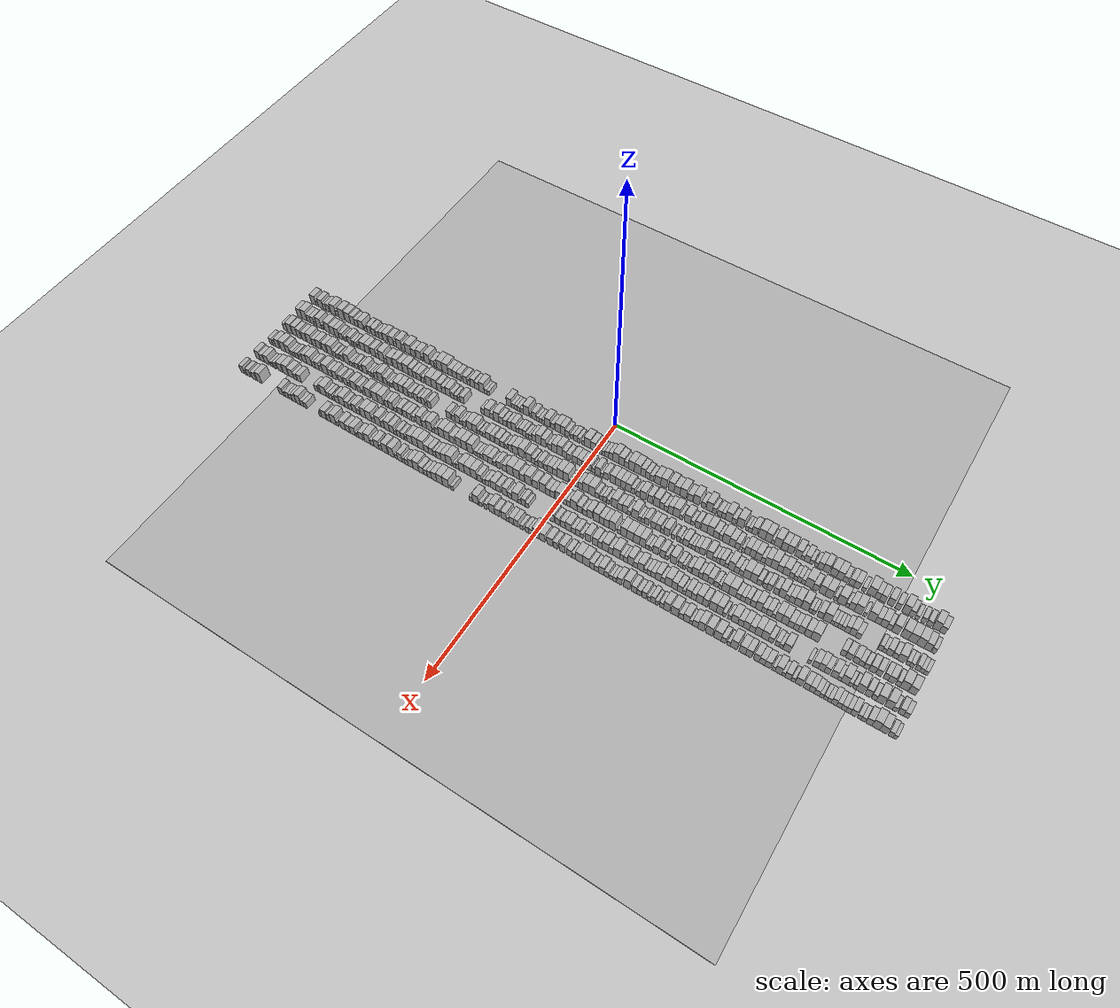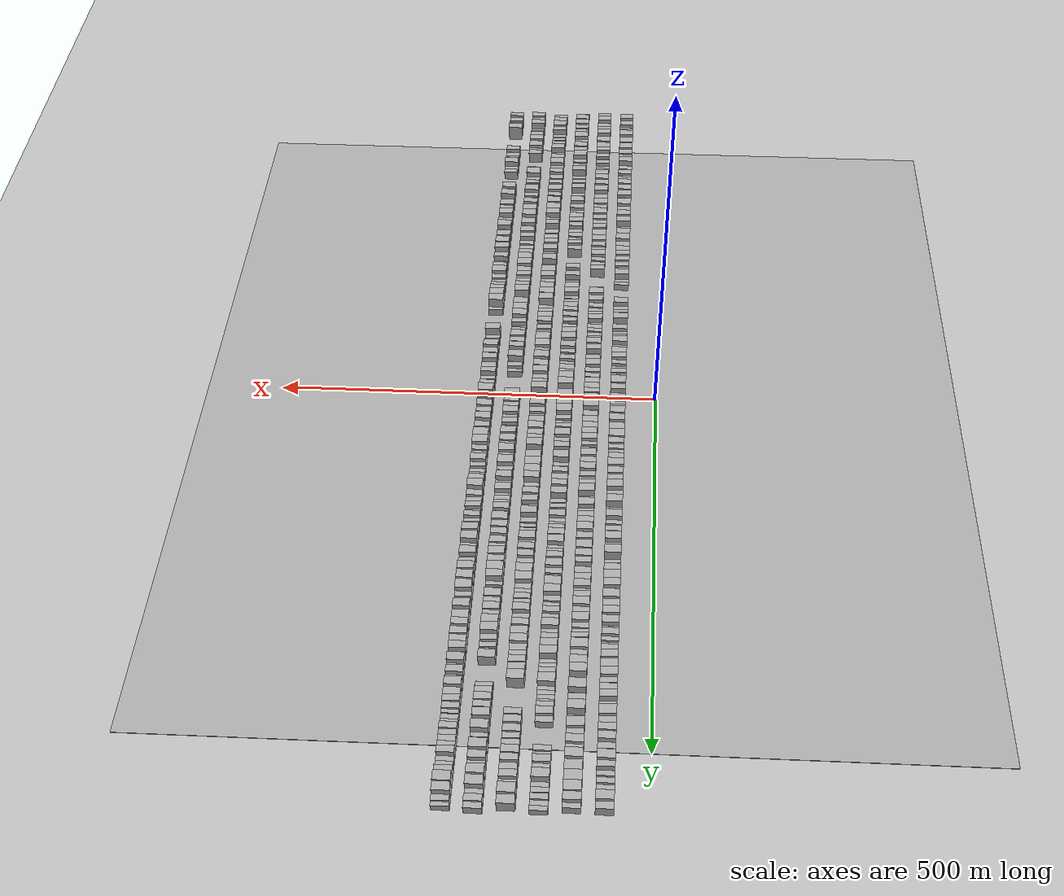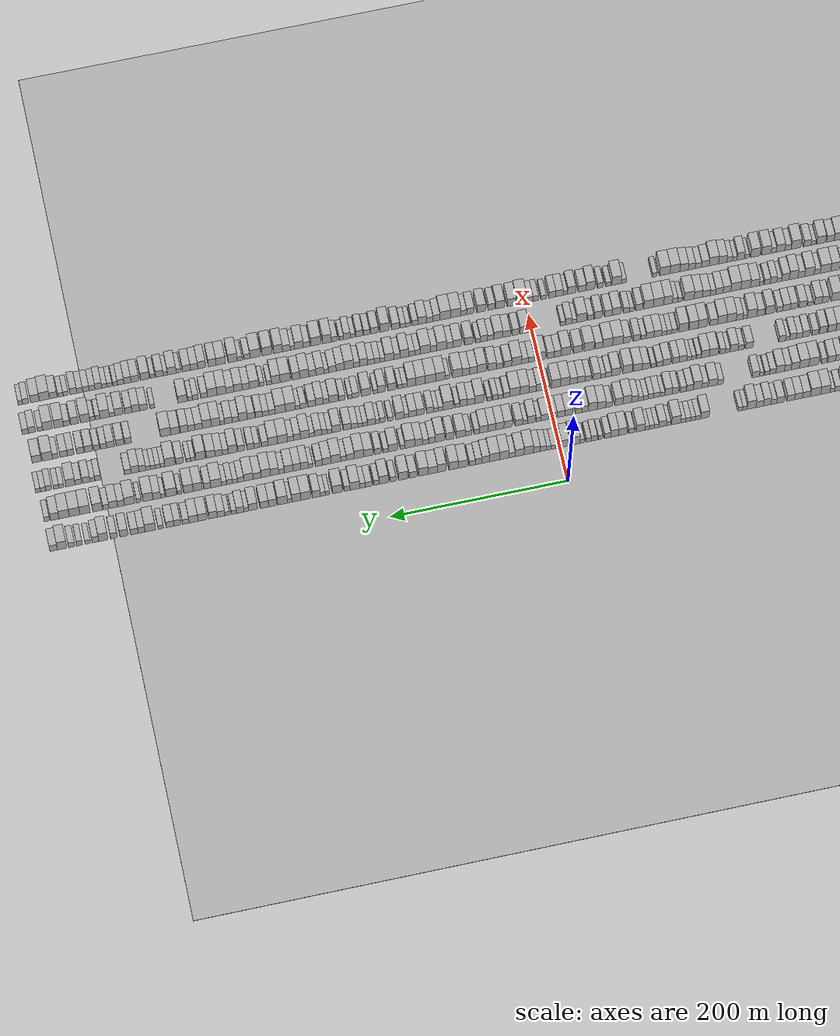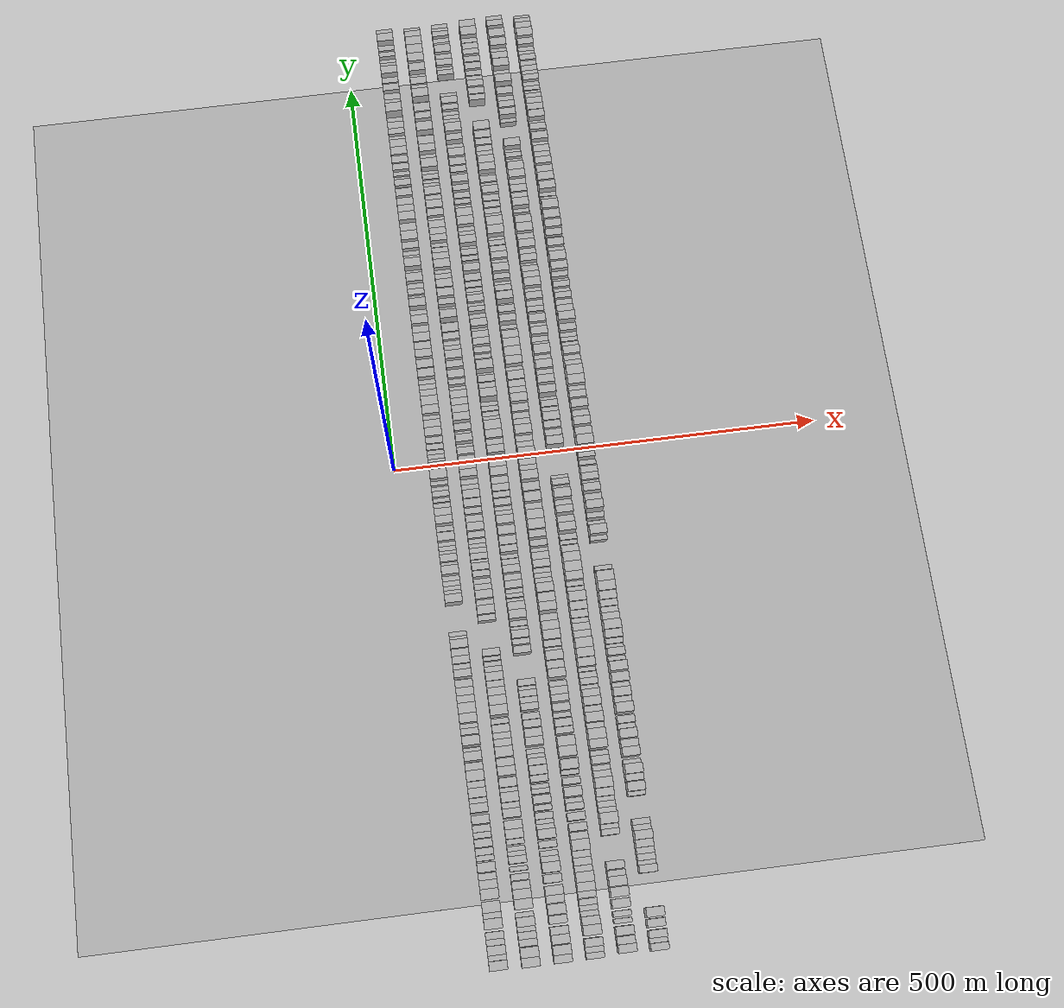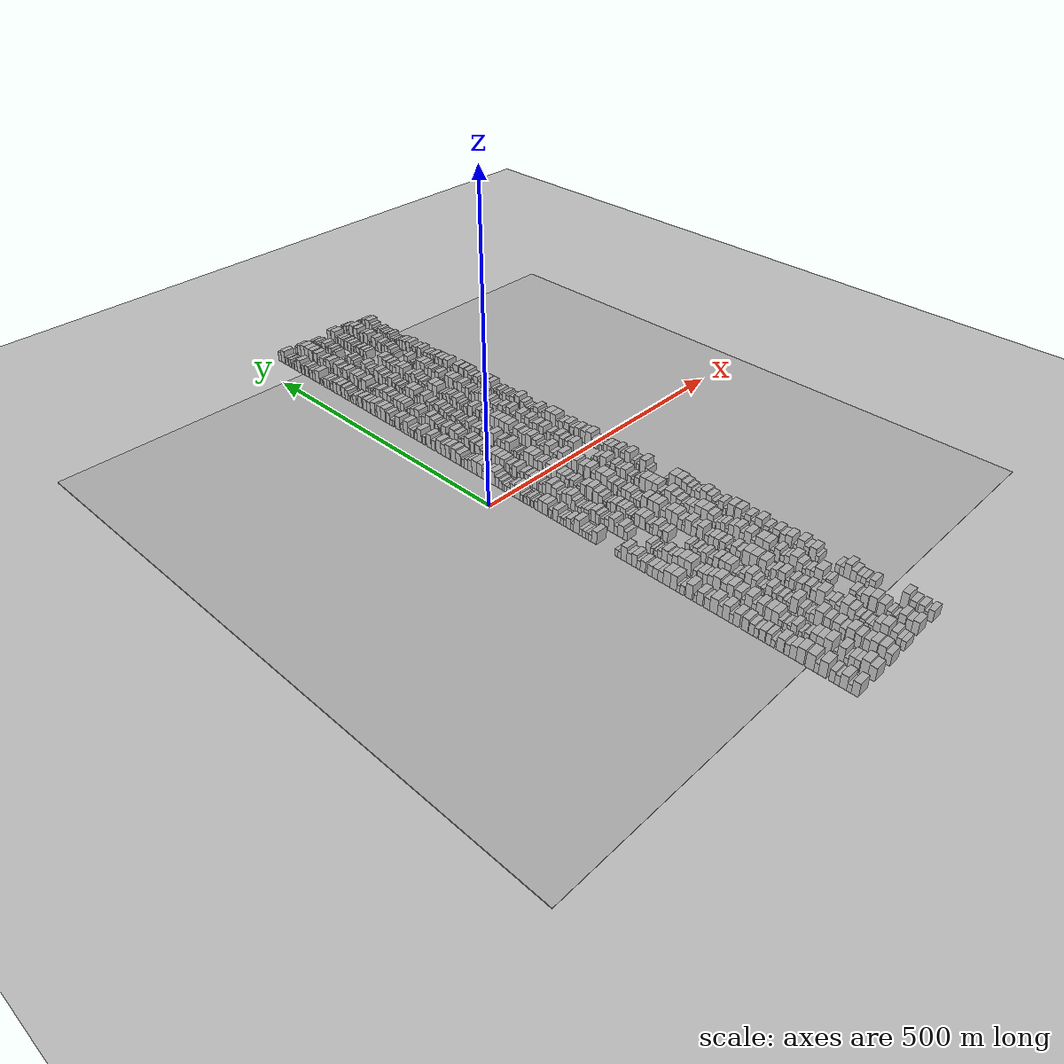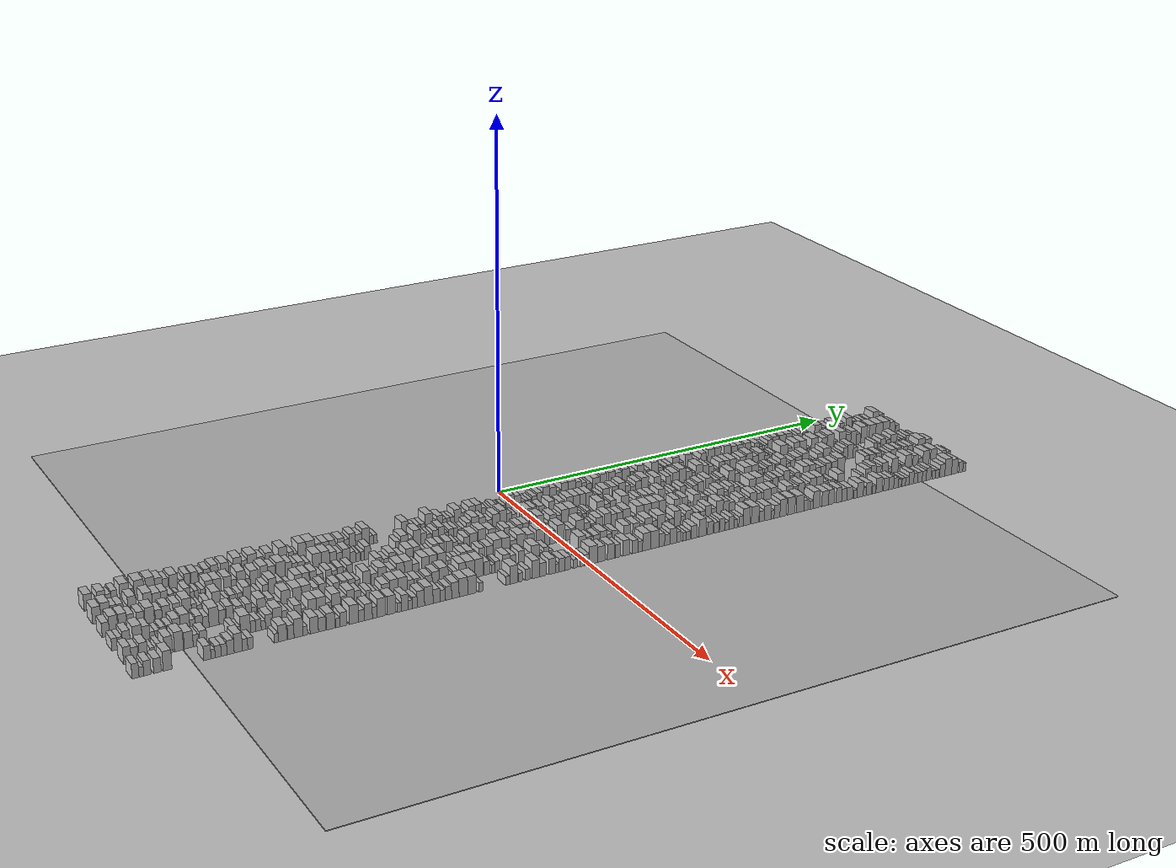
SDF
<?xml version="1.0" encoding="utf-8"?>

<sdf version="1.6">

   <world name="default">

      <gui fullscreen="0">

         <camera name="user_camera">

            <pose>-15 0 4.57585 0 0 0</pose>

            <view_controller>orbit</view_controller>

         </camera>

      </gui>

      <scene>

         <sky>

           <clouds>

             <speed>12</speed>

           </clouds>

         </sky>

         <ambient>0.4 0.4 0.4 1</ambient>

         <background>0.7 0.7 0.7 1</background>

         <shadows>1</shadows>

      </scene>

      <gravity>0 0 -9.8066</gravity>

      <magnetic_field>6e-06 2.3e-05 -4.2e-05</magnetic_field>

      <physics default="0" name="default_physics" type="ode">

         <ode>

            <solver>

               <type>quick</type>

               <iters>10</iters>

               <sor>1.0</sor>

               <use_dynamic_moi_rescaling>0</use_dynamic_moi_rescaling>

            </solver>

            <constraints>

               <cfm>0</cfm>

               <erp>0.2</erp>

               <contact_max_correcting_vel>100</contact_max_correcting_vel>

               <contact_surface_layer>0.001</contact_surface_layer>

            </constraints>

         </ode>

         <max_step_size>0.004</max_step_size>

         <real_time_factor>1</real_time_factor>

         <real_time_update_rate>250</real_time_update_rate>

      </physics>

      <light name="sun" type="directional">

         <cast_shadows>1</cast_shadows>

         <pose>0 0 10 0 0 0</pose>

         <diffuse>0.8 0.8 0.8 1</diffuse>

         <specular>0.2 0.2 0.2 1</specular>

         <attenuation>

            <range>1000</range>

            <constant>0.9</constant>

            <linear>0.01</linear>

            <quadratic>0.001</quadratic>

         </attenuation>

         <direction>-0.5 0.1 -0.9</direction>

      </light>

      <include>

         <name>ground_plane_1</name>

         <uri>model://HANNAS_ground_plane</uri>

         <pose>0 0 0  0 0 0</pose>

      </include>

      <include>

         <name>ground_plane_2</name>

         <uri>model://HANNAS_ground_plane</uri>

         <pose>100 0 0  0 0 0</pose>

      </include>

      <model name="building_1">

         <static>1</static>

         <pose frame="">50.0000 -564.1131 0 0.000000 0.000000 0.000000</pose>

         <link name="link">

            <pose frame="">0 0 10.50 0 0 0</pose>

            <collision name="collision">

               <geometry>

                  <box>

                     <size>20.0000 9.7738 21.0000</size>

                  </box>

               </geometry>

               <max_contacts>10</max_contacts>

               <surface>

                  <contact>

                     <ode/>

                  </contact>

                  <bounce/>

                  <friction>

                     <torsional>

                        <ode/>

                     </torsional>

                     <ode/>

                  </friction>

               </surface>

            </collision>

            <visual name="visual">

               <cast_shadows>0</cast_shadows>

               <geometry>

                  <box>

                     <size>20.0000 9.7738 21.0000</size>

                  </box>

               </geometry>

               <material>

                  <script>

                     <uri>model://HANNAS_wall/materials/scripts</uri>

                     <uri>model://HANNAS_wall/materials/textures</uri>

                     <name>vrc/HANNAS_wall</name>

                  </script>

               </material>

            </visual>

            <self_collide>0</self_collide>

            <enable_wind>0</enable_wind>

            <kinematic>0</kinematic>

         </link>

      </model>

      <model name="building_2">

         <static>1</static>

         <pose frame="">50.0000 -556.2475 0 0.000000 0.000000 0.000000</pose>

         <link name="link">

            <pose frame="">0 0 6.00 0 0 0</pose>

            <collision name="collision">

               <geometry>

                  <box>

                     <size>20.0000 5.9574 12.0000</size>

                  </box>

               </geometry>

               <max_contacts>10</max_contacts>

               <surface>

                  <contact>

                     <ode/>

                  </contact>

                  <bounce/>

                  <friction>

                     <torsional>

                        <ode/>

                     </torsional>

                     <ode/>

                  </friction>

               </surface>

            </collision>

            <visual name="visual">

               <cast_shadows>0</cast_shadows>

               <geometry>

                  <box>

                     <size>20.0000 5.9574 12.0000</size>

                  </box>

               </geometry>

               <material>

                  <script>

                     <uri>model://HANNAS_wall/materials/scripts</uri>

                     <uri>model://HANNAS_wall/materials/textures</uri>

                     <name>vrc/HANNAS_wall</name>

                  </script>

               </material>

            </visual>

            <self_collide>0</self_collide>

            <enable_wind>0</enable_wind>

            <kinematic>0</kinematic>

         </link>

      </model>

      <model name="building_3">

         <static>1</static>

         <pose frame="">50.0000 -548.3666 0 0.000000 0.000000 0.000000</pose>

         <link name="link">

            <pose frame="">0 0 10.50 0 0 0</pose>

            <collision name="collision">

               <geometry>

                  <box>

                     <size>20.0000 9.8044 21.0000</size>

                  </box>

               </geometry>

               <max_contacts>10</max_contacts>

               <surface>

                  <contact>

                     <ode/>

                  </contact>

                  <bounce/>

                  <friction>

                     <torsional>

                        <ode/>

                     </torsional>

                     <ode/>

                  </friction>

               </surface>

            </collision>

            <visual name="visual">

               <cast_shadows>0</cast_shadows>

               <geometry>

                  <box>

                     <size>20.0000 9.8044 21.0000</size>

                  </box>

               </geometry>

               <material>

                  <script>

                     <uri>model://HANNAS_wall/materials/scripts</uri>

                     <uri>model://HANNAS_wall/materials/textures</uri>

                     <name>vrc/HANNAS_wall</name>

                  </script>

               </material>

            </visual>

            <self_collide>0</self_collide>

            <enable_wind>0</enable_wind>

            <kinematic>0</kinematic>

         </link>

      </model>

      <model name="building_4">

         <static>1</static>

         <pose frame="">50.0000 -540.1004 0 0.000000 0.000000 0.000000</pose>

         <link name="link">

            <pose frame="">0 0 7.50 0 0 0</pose>

            <collision name="collision">

               <geometry>

                  <box>

                     <size>20.0000 6.7281 15.0000</size>

                  </box>

               </geometry>

               <max_contacts>10</max_contacts>

               <surface>

                  <contact>

                     <ode/>

                  </contact>

                  <bounce/>

                  <friction>

                     <torsional>

                        <ode/>

                     </torsional>

                     <ode/>

                  </friction>

               </surface>

            </collision>

            <visual name="visual">

               <cast_shadows>0</cast_shadows>

               <geometry>

                  <box>

                     <size>20.0000 6.7281 15.0000</size>

                  </box>

               </geometry>

               <material>

                  <script>

                     <uri>model://HANNAS_wall/materials/scripts</uri>

                     <uri>model://HANNAS_wall/materials/textures</uri>

                     <name>vrc/HANNAS_wall</name>

                  </script>

               </material>

            </visual>

            <self_collide>0</self_collide>

            <enable_wind>0</enable_wind>

            <kinematic>0</kinematic>

         </link>

      </model>

      <model name="building_5">

         <static>1</static>

         <pose frame="">50.0000 -532.9856 0 0.000000 0.000000 0.000000</pose>

         <link name="link">

            <pose frame="">0 0 9.00 0 0 0</pose>

            <collision name="collision">

               <geometry>

                  <box>

                     <size>20.0000 7.5014 18.0000</size>

                  </box>

               </geometry>

               <max_contacts>10</max_contacts>

               <surface>

                  <contact>

                     <ode/>

                  </contact>

                  <bounce/>

                  <friction>

                     <torsional>

                        <ode/>

                     </torsional>

                     <ode/>

                  </friction>

               </surface>

            </collision>

            <visual name="visual">

               <cast_shadows>0</cast_shadows>

               <geometry>

                  <box>

                     <size>20.0000 7.5014 18.0000</size>

                  </box>

               </geometry>

               <material>

                  <script>

                     <uri>model://HANNAS_wall/materials/scripts</uri>

                     <uri>model://HANNAS_wall/materials/textures</uri>

                     <name>vrc/HANNAS_wall</name>

                  </script>

               </material>

            </visual>

            <self_collide>0</self_collide>

            <enable_wind>0</enable_wind>

            <kinematic>0</kinematic>

         </link>

      </model>

      <model name="building_6">

         <static>1</static>

         <pose frame="">50.0000 -520.7210 0 0.000000 0.000000 0.000000</pose>

         <link name="link">

            <pose frame="">0 0 12.00 0 0 0</pose>

            <collision name="collision">

               <geometry>

                  <box>

                     <size>20.0000 11.0278 24.0000</size>

                  </box>

               </geometry>

               <max_contacts>10</max_contacts>

               <surface>

                  <contact>

                     <ode/>

                  </contact>

                  <bounce/>

                  <friction>

                     <torsional>

                        <ode/>

                     </torsional>

                     <ode/>

                  </friction>

               </surface>

            </collision>

            <visual name="visual">

               <cast_shadows>0</cast_shadows>

               <geometry>

                  <box>

                     <size>20.0000 11.0278 24.0000</size>

                  </box>

               </geometry>

               <material>

                  <script>

                     <uri>model://HANNAS_wall/materials/scripts</uri>

                     <uri>model://HANNAS_wall/materials/textures</uri>

                     <name>vrc/HANNAS_wall</name>

                  </script>

               </material>

            </visual>

            <self_collide>0</self_collide>

            <enable_wind>0</enable_wind>

            <kinematic>0</kinematic>

         </link>

      </model>

      <model name="building_7">

         <static>1</static>

         <pose frame="">50.0000 -512.1404 0 0.000000 0.000000 0.000000</pose>

         <link name="link">

            <pose frame="">0 0 7.50 0 0 0</pose>

            <collision name="collision">

               <geometry>

                  <box>

                     <size>20.0000 6.1334 15.0000</size>

                  </box>

               </geometry>

               <max_contacts>10</max_contacts>

               <surface>

                  <contact>

                     <ode/>

                  </contact>

                  <bounce/>

                  <friction>

                     <torsional>

                        <ode/>

                     </torsional>

                     <ode/>

                  </friction>

               </surface>

            </collision>

            <visual name="visual">

               <cast_shadows>0</cast_shadows>

               <geometry>

                  <box>

                     <size>20.0000 6.1334 15.0000</size>

                  </box>

               </geometry>

               <material>

                  <script>

                     <uri>model://HANNAS_wall/materials/scripts</uri>

                     <uri>model://HANNAS_wall/materials/textures</uri>

                     <name>vrc/HANNAS_wall</name>

                  </script>

               </material>

            </visual>

            <self_collide>0</self_collide>

            <enable_wind>0</enable_wind>

            <kinematic>0</kinematic>

         </link>

      </model>

      <model name="building_8">

         <static>1</static>

         <pose frame="">50.0000 -503.1500 0 0.000000 0.000000 0.000000</pose>

         <link name="link">

            <pose frame="">0 0 12.00 0 0 0</pose>

            <collision name="collision">

               <geometry>

                  <box>

                     <size>20.0000 11.8474 24.0000</size>

                  </box>

               </geometry>

               <max_contacts>10</max_contacts>

               <surface>

                  <contact>

                     <ode/>

                  </contact>

                  <bounce/>

                  <friction>

                     <torsional>

                        <ode/>

                     </torsional>

                     <ode/>

                  </friction>

               </surface>

            </collision>

            <visual name="visual">

               <cast_shadows>0</cast_shadows>

               <geometry>

                  <box>

                     <size>20.0000 11.8474 24.0000</size>

                  </box>

               </geometry>

               <material>

                  <script>

                     <uri>model://HANNAS_wall/materials/scripts</uri>

                     <uri>model://HANNAS_wall/materials/textures</uri>

                     <name>vrc/HANNAS_wall</name>

                  </script>

               </material>

            </visual>

            <self_collide>0</self_collide>

            <enable_wind>0</enable_wind>

            <kinematic>0</kinematic>

         </link>

      </model>

      <model name="building_9">

         <static>1</static>

         <pose frame="">50.0000 -489.6845 0 0.000000 0.000000 0.000000</pose>

         <link name="link">

            <pose frame="">0 0 12.00 0 0 0</pose>

            <collision name="collision">

               <geometry>

                  <box>

                     <size>20.0000 11.0836 24.0000</size>

                  </box>

               </geometry>

               <max_contacts>10</max_contacts>

               <surface>

                  <contact>

                     <ode/>

                  </contact>

                  <bounce/>

                  <friction>

                     <torsional>

                        <ode/>

                     </torsional>

                     <ode/>

                  </friction>

               </surface>

            </collision>

            <visual name="visual">

               <cast_shadows>0</cast_shadows>

               <geometry>

                  <box>

                     <size>20.0000 11.0836 24.0000</size>

                  </box>

               </geometry>

               <material>

                  <script>

                     <uri>model://HANNAS_wall/materials/scripts</uri>

                     <uri>model://HANNAS_wall/materials/textures</uri>

                     <name>vrc/HANNAS_wall</name>

                  </script>

               </material>

            </visual>

            <self_collide>0</self_collide>

            <enable_wind>0</enable_wind>

            <kinematic>0</kinematic>

         </link>

      </model>

      <model name="building_10">

         <static>1</static>

         <pose frame="">50.0000 -479.4460 0 0.000000 0.000000 0.000000</pose>

         <link name="link">

            <pose frame="">0 0 10.50 0 0 0</pose>

            <collision name="collision">

               <geometry>

                  <box>

                     <size>20.0000 9.3932 21.0000</size>

                  </box>

               </geometry>

               <max_contacts>10</max_contacts>

               <surface>

                  <contact>

                     <ode/>

                  </contact>

                  <bounce/>

                  <friction>

                     <torsional>

                        <ode/>

                     </torsional>

                     <ode/>

                  </friction>

               </surface>

            </collision>

            <visual name="visual">

               <cast_shadows>0</cast_shadows>

               <geometry>

                  <box>

                     <size>20.0000 9.3932 21.0000</size>

                  </box>

               </geometry>

               <material>

                  <script>

                     <uri>model://HANNAS_wall/materials/scripts</uri>

                     <uri>model://HANNAS_wall/materials/textures</uri>

                     <name>vrc/HANNAS_wall</name>

                  </script>

               </material>

            </visual>

            <self_collide>0</self_collide>

            <enable_wind>0</enable_wind>

            <kinematic>0</kinematic>

         </link>

      </model>

      <model name="building_11">

         <static>1</static>

         <pose frame="">50.0000 -471.1267 0 0.000000 0.000000 0.000000</pose>

         <link name="link">

            <pose frame="">0 0 9.00 0 0 0</pose>

            <collision name="collision">

               <geometry>

                  <box>

                     <size>20.0000 7.2455 18.0000</size>

                  </box>

               </geometry>

               <max_contacts>10</max_contacts>

               <surface>

                  <contact>

                     <ode/>

                  </contact>

                  <bounce/>

                  <friction>

                     <torsional>

                        <ode/>

                     </torsional>

                     <ode/>

                  </friction>

               </surface>

            </collision>

            <visual name="visual">

               <cast_shadows>0</cast_shadows>

               <geometry>

                  <box>

                     <size>20.0000 7.2455 18.0000</size>

                  </box>

               </geometry>

               <material>

                  <script>

                     <uri>model://HANNAS_wall/materials/scripts</uri>

                     <uri>model://HANNAS_wall/materials/textures</uri>

                     <name>vrc/HANNAS_wall</name>

                  </script>

               </material>

            </visual>

            <self_collide>0</self_collide>

            <enable_wind>0</enable_wind>

            <kinematic>0</kinematic>

         </link>

      </model>

      <model name="building_12">

         <static>1</static>

         <pose frame="">50.0000 -461.3749 0 0.000000 0.000000 0.000000</pose>

         <link name="link">

            <pose frame="">0 0 10.50 0 0 0</pose>

            <collision name="collision">

               <geometry>

                  <box>

                     <size>20.0000 10.2581 21.0000</size>

                  </box>

               </geometry>

               <max_contacts>10</max_contacts>

               <surface>

                  <contact>

                     <ode/>

                  </contact>

                  <bounce/>

                  <friction>

                     <torsional>

                        <ode/>

                     </torsional>

                     <ode/>

                  </friction>

               </surface>

            </collision>

            <visual name="visual">

               <cast_shadows>0</cast_shadows>

               <geometry>

                  <box>

                     <size>20.0000 10.2581 21.0000</size>

                  </box>

               </geometry>

               <material>

                  <script>

                     <uri>model://HANNAS_wall/materials/scripts</uri>

                     <uri>model://HANNAS_wall/materials/textures</uri>

                     <name>vrc/HANNAS_wall</name>

                  </script>

               </material>

            </visual>

            <self_collide>0</self_collide>

            <enable_wind>0</enable_wind>

            <kinematic>0</kinematic>

         </link>

      </model>

      <model name="building_13">

         <static>1</static>

         <pose frame="">50.0000 -451.3110 0 0.000000 0.000000 0.000000</pose>

         <link name="link">

            <pose frame="">0 0 6.00 0 0 0</pose>

            <collision name="collision">

               <geometry>

                  <box>

                     <size>20.0000 5.8699 12.0000</size>

                  </box>

               </geometry>

               <max_contacts>10</max_contacts>

               <surface>

                  <contact>

                     <ode/>

                  </contact>

                  <bounce/>

                  <friction>

                     <torsional>

                        <ode/>

                     </torsional>

                     <ode/>

                  </friction>

               </surface>

            </collision>

            <visual name="visual">

               <cast_shadows>0</cast_shadows>

               <geometry>

                  <box>

                     <size>20.0000 5.8699 12.0000</size>

                  </box>

               </geometry>

               <material>

                  <script>

                     <uri>model://HANNAS_wall/materials/scripts</uri>

                     <uri>model://HANNAS_wall/materials/textures</uri>

                     <name>vrc/HANNAS_wall</name>

                  </script>

               </material>

            </visual>

            <self_collide>0</self_collide>

            <enable_wind>0</enable_wind>

            <kinematic>0</kinematic>

         </link>

      </model>

      <model name="building_14">

         <static>1</static>

         <pose frame="">50.0000 -444.6101 0 0.000000 0.000000 0.000000</pose>

         <link name="link">

            <pose frame="">0 0 9.00 0 0 0</pose>

            <collision name="collision">

               <geometry>

                  <box>

                     <size>20.0000 7.5320 18.0000</size>

                  </box>

               </geometry>

               <max_contacts>10</max_contacts>

               <surface>

                  <contact>

                     <ode/>

                  </contact>

                  <bounce/>

                  <friction>

                     <torsional>

                        <ode/>

                     </torsional>

                     <ode/>

                  </friction>

               </surface>

            </collision>

            <visual name="visual">

               <cast_shadows>0</cast_shadows>

               <geometry>

                  <box>

                     <size>20.0000 7.5320 18.0000</size>

                  </box>

               </geometry>

               <material>

                  <script>

                     <uri>model://HANNAS_wall/materials/scripts</uri>

                     <uri>model://HANNAS_wall/materials/textures</uri>

                     <name>vrc/HANNAS_wall</name>

                  </script>

               </material>

            </visual>

            <self_collide>0</self_collide>

            <enable_wind>0</enable_wind>

            <kinematic>0</kinematic>

         </link>

      </model>

      <model name="building_15">

         <static>1</static>

         <pose frame="">50.0000 -435.4569 0 0.000000 0.000000 0.000000</pose>

         <link name="link">

            <pose frame="">0 0 9.00 0 0 0</pose>

            <collision name="collision">

               <geometry>

                  <box>

                     <size>20.0000 8.7743 18.0000</size>

                  </box>

               </geometry>

               <max_contacts>10</max_contacts>

               <surface>

                  <contact>

                     <ode/>

                  </contact>

                  <bounce/>

                  <friction>

                     <torsional>

                        <ode/>

                     </torsional>

                     <ode/>

                  </friction>

               </surface>

            </collision>

            <visual name="visual">

               <cast_shadows>0</cast_shadows>

               <geometry>

                  <box>

                     <size>20.0000 8.7743 18.0000</size>

                  </box>

               </geometry>

               <material>

                  <script>

                     <uri>model://HANNAS_wall/materials/scripts</uri>

                     <uri>model://HANNAS_wall/materials/textures</uri>

                     <name>vrc/HANNAS_wall</name>

                  </script>

               </material>

            </visual>

            <self_collide>0</self_collide>

            <enable_wind>0</enable_wind>

            <kinematic>0</kinematic>

         </link>

      </model>

      <model name="building_16">

         <static>1</static>

         <pose frame="">50.0000 -426.8989 0 0.000000 0.000000 0.000000</pose>

         <link name="link">

            <pose frame="">0 0 7.50 0 0 0</pose>

            <collision name="collision">

               <geometry>

                  <box>

                     <size>20.0000 6.3419 15.0000</size>

                  </box>

               </geometry>

               <max_contacts>10</max_contacts>

               <surface>

                  <contact>

                     <ode/>

                  </contact>

                  <bounce/>

                  <friction>

                     <torsional>

                        <ode/>

                     </torsional>

                     <ode/>

                  </friction>

               </surface>

            </collision>

            <visual name="visual">

               <cast_shadows>0</cast_shadows>

               <geometry>

                  <box>

                     <size>20.0000 6.3419 15.0000</size>

                  </box>

               </geometry>

               <material>

                  <script>

                     <uri>model://HANNAS_wall/materials/scripts</uri>

                     <uri>model://HANNAS_wall/materials/textures</uri>

                     <name>vrc/HANNAS_wall</name>

                  </script>

               </material>

            </visual>

            <self_collide>0</self_collide>

            <enable_wind>0</enable_wind>

            <kinematic>0</kinematic>

         </link>

      </model>

      <model name="building_17">

         <static>1</static>

         <pose frame="">50.0000 -419.9059 0 0.000000 0.000000 0.000000</pose>

         <link name="link">

            <pose frame="">0 0 9.00 0 0 0</pose>

            <collision name="collision">

               <geometry>

                  <box>

                     <size>20.0000 7.6440 18.0000</size>

                  </box>

               </geometry>

               <max_contacts>10</max_contacts>

               <surface>

                  <contact>

                     <ode/>

                  </contact>

                  <bounce/>

                  <friction>

                     <torsional>

                        <ode/>

                     </torsional>

                     <ode/>

                  </friction>

               </surface>

            </collision>

            <visual name="visual">

               <cast_shadows>0</cast_shadows>

               <geometry>

                  <box>

                     <size>20.0000 7.6440 18.0000</size>

                  </box>

               </geometry>

               <material>

                  <script>

                     <uri>model://HANNAS_wall/materials/scripts</uri>

                     <uri>model://HANNAS_wall/materials/textures</uri>

                     <name>vrc/HANNAS_wall</name>

                  </script>

               </material>

            </visual>

            <self_collide>0</self_collide>

            <enable_wind>0</enable_wind>

            <kinematic>0</kinematic>

         </link>

      </model>

      <model name="building_18">

         <static>1</static>

         <pose frame="">50.0000 -410.3458 0 0.000000 0.000000 0.000000</pose>

         <link name="link">

            <pose frame="">0 0 10.50 0 0 0</pose>

            <collision name="collision">

               <geometry>

                  <box>

                     <size>20.0000 9.4763 21.0000</size>

                  </box>

               </geometry>

               <max_contacts>10</max_contacts>

               <surface>

                  <contact>

                     <ode/>

                  </contact>

                  <bounce/>

                  <friction>

                     <torsional>

                        <ode/>

                     </torsional>

                     <ode/>

                  </friction>

               </surface>

            </collision>

            <visual name="visual">

               <cast_shadows>0</cast_shadows>

               <geometry>

                  <box>

                     <size>20.0000 9.4763 21.0000</size>

                  </box>

               </geometry>

               <material>

                  <script>

                     <uri>model://HANNAS_wall/materials/scripts</uri>

                     <uri>model://HANNAS_wall/materials/textures</uri>

                     <name>vrc/HANNAS_wall</name>

                  </script>

               </material>

            </visual>

            <self_collide>0</self_collide>

            <enable_wind>0</enable_wind>

            <kinematic>0</kinematic>

         </link>

      </model>

      <model name="building_19">

         <static>1</static>

         <pose frame="">50.0000 -397.7008 0 0.000000 0.000000 0.000000</pose>

         <link name="link">

            <pose frame="">0 0 10.50 0 0 0</pose>

            <collision name="collision">

               <geometry>

                  <box>

                     <size>20.0000 9.8136 21.0000</size>

                  </box>

               </geometry>

               <max_contacts>10</max_contacts>

               <surface>

                  <contact>

                     <ode/>

                  </contact>

                  <bounce/>

                  <friction>

                     <torsional>

                        <ode/>

                     </torsional>

                     <ode/>

                  </friction>

               </surface>

            </collision>

            <visual name="visual">

               <cast_shadows>0</cast_shadows>

               <geometry>

                  <box>

                     <size>20.0000 9.8136 21.0000</size>

                  </box>

               </geometry>

               <material>

                  <script>

                     <uri>model://HANNAS_wall/materials/scripts</uri>

                     <uri>model://HANNAS_wall/materials/textures</uri>

                     <name>vrc/HANNAS_wall</name>

                  </script>

               </material>

            </visual>

            <self_collide>0</self_collide>

            <enable_wind>0</enable_wind>

            <kinematic>0</kinematic>

         </link>

      </model>

      <model name="building_20">

         <static>1</static>

         <pose frame="">50.0000 -389.7556 0 0.000000 0.000000 0.000000</pose>

         <link name="link">

            <pose frame="">0 0 7.50 0 0 0</pose>

            <collision name="collision">

               <geometry>

                  <box>

                     <size>20.0000 6.0767 15.0000</size>

                  </box>

               </geometry>

               <max_contacts>10</max_contacts>

               <surface>

                  <contact>

                     <ode/>

                  </contact>

                  <bounce/>

                  <friction>

                     <torsional>

                        <ode/>

                     </torsional>

                     <ode/>

                  </friction>

               </surface>

            </collision>

            <visual name="visual">

               <cast_shadows>0</cast_shadows>

               <geometry>

                  <box>

                     <size>20.0000 6.0767 15.0000</size>

                  </box>

               </geometry>

               <material>

                  <script>

                     <uri>model://HANNAS_wall/materials/scripts</uri>

                     <uri>model://HANNAS_wall/materials/textures</uri>

                     <name>vrc/HANNAS_wall</name>

                  </script>

               </material>

            </visual>

            <self_collide>0</self_collide>

            <enable_wind>0</enable_wind>

            <kinematic>0</kinematic>

         </link>

      </model>

      <model name="building_21">

         <static>1</static>

         <pose frame="">50.0000 -381.5165 0 0.000000 0.000000 0.000000</pose>

         <link name="link">

            <pose frame="">0 0 12.00 0 0 0</pose>

            <collision name="collision">

               <geometry>

                  <box>

                     <size>20.0000 10.4015 24.0000</size>

                  </box>

               </geometry>

               <max_contacts>10</max_contacts>

               <surface>

                  <contact>

                     <ode/>

                  </contact>

                  <bounce/>

                  <friction>

                     <torsional>

                        <ode/>

                     </torsional>

                     <ode/>

                  </friction>

               </surface>

            </collision>

            <visual name="visual">

               <cast_shadows>0</cast_shadows>

               <geometry>

                  <box>

                     <size>20.0000 10.4015 24.0000</size>

                  </box>

               </geometry>

               <material>

                  <script>

                     <uri>model://HANNAS_wall/materials/scripts</uri>

                     <uri>model://HANNAS_wall/materials/textures</uri>

                     <name>vrc/HANNAS_wall</name>

                  </script>

               </material>

            </visual>

            <self_collide>0</self_collide>

            <enable_wind>0</enable_wind>

            <kinematic>0</kinematic>

         </link>

      </model>

      <model name="building_22">

         <static>1</static>

         <pose frame="">50.0000 -372.5683 0 0.000000 0.000000 0.000000</pose>

         <link name="link">

            <pose frame="">0 0 9.00 0 0 0</pose>

            <collision name="collision">

               <geometry>

                  <box>

                     <size>20.0000 7.4949 18.0000</size>

                  </box>

               </geometry>

               <max_contacts>10</max_contacts>

               <surface>

                  <contact>

                     <ode/>

                  </contact>

                  <bounce/>

                  <friction>

                     <torsional>

                        <ode/>

                     </torsional>

                     <ode/>

                  </friction>

               </surface>

            </collision>

            <visual name="visual">

               <cast_shadows>0</cast_shadows>

               <geometry>

                  <box>

                     <size>20.0000 7.4949 18.0000</size>

                  </box>

               </geometry>

               <material>

                  <script>

                     <uri>model://HANNAS_wall/materials/scripts</uri>

                     <uri>model://HANNAS_wall/materials/textures</uri>

                     <name>vrc/HANNAS_wall</name>

                  </script>

               </material>

            </visual>

            <self_collide>0</self_collide>

            <enable_wind>0</enable_wind>

            <kinematic>0</kinematic>

         </link>

      </model>

      <model name="building_23">

         <static>1</static>

         <pose frame="">50.0000 -362.8879 0 0.000000 0.000000 0.000000</pose>

         <link name="link">

            <pose frame="">0 0 12.00 0 0 0</pose>

            <collision name="collision">

               <geometry>

                  <box>

                     <size>20.0000 11.8658 24.0000</size>

                  </box>

               </geometry>

               <max_contacts>10</max_contacts>

               <surface>

                  <contact>

                     <ode/>

                  </contact>

                  <bounce/>

                  <friction>

                     <torsional>

                        <ode/>

                     </torsional>

                     <ode/>

                  </friction>

               </surface>

            </collision>

            <visual name="visual">

               <cast_shadows>0</cast_shadows>

               <geometry>

                  <box>

                     <size>20.0000 11.8658 24.0000</size>

                  </box>

               </geometry>

               <material>

                  <script>

                     <uri>model://HANNAS_wall/materials/scripts</uri>

                     <uri>model://HANNAS_wall/materials/textures</uri>

                     <name>vrc/HANNAS_wall</name>

                  </script>

               </material>

            </visual>

            <self_collide>0</self_collide>

            <enable_wind>0</enable_wind>

            <kinematic>0</kinematic>

         </link>

      </model>

      <model name="building_24">

         <static>1</static>

         <pose frame="">50.0000 -352.6305 0 0.000000 0.000000 0.000000</pose>

         <link name="link">

            <pose frame="">0 0 9.00 0 0 0</pose>

            <collision name="collision">

               <geometry>

                  <box>

                     <size>20.0000 8.6490 18.0000</size>

                  </box>

               </geometry>

               <max_contacts>10</max_contacts>

               <surface>

                  <contact>

                     <ode/>

                  </contact>

                  <bounce/>

                  <friction>

                     <torsional>

                        <ode/>

                     </torsional>

                     <ode/>

                  </friction>

               </surface>

            </collision>

            <visual name="visual">

               <cast_shadows>0</cast_shadows>

               <geometry>

                  <box>

                     <size>20.0000 8.6490 18.0000</size>

                  </box>

               </geometry>

               <material>

                  <script>

                     <uri>model://HANNAS_wall/materials/scripts</uri>

                     <uri>model://HANNAS_wall/materials/textures</uri>

                     <name>vrc/HANNAS_wall</name>

                  </script>

               </material>

            </visual>

            <self_collide>0</self_collide>

            <enable_wind>0</enable_wind>

            <kinematic>0</kinematic>

         </link>

      </model>

      <model name="building_25">

         <static>1</static>

         <pose frame="">50.0000 -341.3067 0 0.000000 0.000000 0.000000</pose>

         <link name="link">

            <pose frame="">0 0 10.50 0 0 0</pose>

            <collision name="collision">

               <geometry>

                  <box>

                     <size>20.0000 9.9986 21.0000</size>

                  </box>

               </geometry>

               <max_contacts>10</max_contacts>

               <surface>

                  <contact>

                     <ode/>

                  </contact>

                  <bounce/>

                  <friction>

                     <torsional>

                        <ode/>

                     </torsional>

                     <ode/>

                  </friction>

               </surface>

            </collision>

            <visual name="visual">

               <cast_shadows>0</cast_shadows>

               <geometry>

                  <box>

                     <size>20.0000 9.9986 21.0000</size>

                  </box>

               </geometry>

               <material>

                  <script>

                     <uri>model://HANNAS_wall/materials/scripts</uri>

                     <uri>model://HANNAS_wall/materials/textures</uri>

                     <name>vrc/HANNAS_wall</name>

                  </script>

               </material>

            </visual>

            <self_collide>0</self_collide>

            <enable_wind>0</enable_wind>

            <kinematic>0</kinematic>

         </link>

      </model>

      <model name="building_26">

         <static>1</static>

         <pose frame="">50.0000 -333.8798 0 0.000000 0.000000 0.000000</pose>

         <link name="link">

            <pose frame="">0 0 6.00 0 0 0</pose>

            <collision name="collision">

               <geometry>

                  <box>

                     <size>20.0000 4.8552 12.0000</size>

                  </box>

               </geometry>

               <max_contacts>10</max_contacts>

               <surface>

                  <contact>

                     <ode/>

                  </contact>

                  <bounce/>

                  <friction>

                     <torsional>

                        <ode/>

                     </torsional>

                     <ode/>

                  </friction>

               </surface>

            </collision>

            <visual name="visual">

               <cast_shadows>0</cast_shadows>

               <geometry>

                  <box>

                     <size>20.0000 4.8552 12.0000</size>

                  </box>

               </geometry>

               <material>

                  <script>

                     <uri>model://HANNAS_wall/materials/scripts</uri>

                     <uri>model://HANNAS_wall/materials/textures</uri>

                     <name>vrc/HANNAS_wall</name>

                  </script>

               </material>

            </visual>

            <self_collide>0</self_collide>

            <enable_wind>0</enable_wind>

            <kinematic>0</kinematic>

         </link>

      </model>

      <model name="building_27">

         <static>1</static>

         <pose frame="">50.0000 -324.1556 0 0.000000 0.000000 0.000000</pose>

         <link name="link">

            <pose frame="">0 0 12.00 0 0 0</pose>

            <collision name="collision">

               <geometry>

                  <box>

                     <size>20.0000 10.5934 24.0000</size>

                  </box>

               </geometry>

               <max_contacts>10</max_contacts>

               <surface>

                  <contact>

                     <ode/>

                  </contact>

                  <bounce/>

                  <friction>

                     <torsional>

                        <ode/>

                     </torsional>

                     <ode/>

                  </friction>

               </surface>

            </collision>

            <visual name="visual">

               <cast_shadows>0</cast_shadows>

               <geometry>

                  <box>

                     <size>20.0000 10.5934 24.0000</size>

                  </box>

               </geometry>

               <material>

                  <script>

                     <uri>model://HANNAS_wall/materials/scripts</uri>

                     <uri>model://HANNAS_wall/materials/textures</uri>

                     <name>vrc/HANNAS_wall</name>

                  </script>

               </material>

            </visual>

            <self_collide>0</self_collide>

            <enable_wind>0</enable_wind>

            <kinematic>0</kinematic>

         </link>

      </model>

      <model name="building_28">

         <static>1</static>

         <pose frame="">50.0000 -313.2942 0 0.000000 0.000000 0.000000</pose>

         <link name="link">

            <pose frame="">0 0 7.50 0 0 0</pose>

            <collision name="collision">

               <geometry>

                  <box>

                     <size>20.0000 7.1293 15.0000</size>

                  </box>

               </geometry>

               <max_contacts>10</max_contacts>

               <surface>

                  <contact>

                     <ode/>

                  </contact>

                  <bounce/>

                  <friction>

                     <torsional>

                        <ode/>

                     </torsional>

                     <ode/>

                  </friction>

               </surface>

            </collision>

            <visual name="visual">

               <cast_shadows>0</cast_shadows>

               <geometry>

                  <box>

                     <size>20.0000 7.1293 15.0000</size>

                  </box>

               </geometry>

               <material>

                  <script>

                     <uri>model://HANNAS_wall/materials/scripts</uri>

                     <uri>model://HANNAS_wall/materials/textures</uri>

                     <name>vrc/HANNAS_wall</name>

                  </script>

               </material>

            </visual>

            <self_collide>0</self_collide>

            <enable_wind>0</enable_wind>

            <kinematic>0</kinematic>

         </link>

      </model>

      <model name="building_29">

         <static>1</static>

         <pose frame="">50.0000 -307.0606 0 0.000000 0.000000 0.000000</pose>

         <link name="link">

            <pose frame="">0 0 6.00 0 0 0</pose>

            <collision name="collision">

               <geometry>

                  <box>

                     <size>20.0000 5.3380 12.0000</size>

                  </box>

               </geometry>

               <max_contacts>10</max_contacts>

               <surface>

                  <contact>

                     <ode/>

                  </contact>

                  <bounce/>

                  <friction>

                     <torsional>

                        <ode/>

                     </torsional>

                     <ode/>

                  </friction>

               </surface>

            </collision>

            <visual name="visual">

               <cast_shadows>0</cast_shadows>

               <geometry>

                  <box>

                     <size>20.0000 5.3380 12.0000</size>

                  </box>

               </geometry>

               <material>

                  <script>

                     <uri>model://HANNAS_wall/materials/scripts</uri>

                     <uri>model://HANNAS_wall/materials/textures</uri>

                     <name>vrc/HANNAS_wall</name>

                  </script>

               </material>

            </visual>

            <self_collide>0</self_collide>

            <enable_wind>0</enable_wind>

            <kinematic>0</kinematic>

         </link>

      </model>

      <model name="building_30">

         <static>1</static>

         <pose frame="">50.0000 -299.1573 0 0.000000 0.000000 0.000000</pose>

         <link name="link">

            <pose frame="">0 0 12.00 0 0 0</pose>

            <collision name="collision">

               <geometry>

                  <box>

                     <size>20.0000 10.4685 24.0000</size>

                  </box>

               </geometry>

               <max_contacts>10</max_contacts>

               <surface>

                  <contact>

                     <ode/>

                  </contact>

                  <bounce/>

                  <friction>

                     <torsional>

                        <ode/>

                     </torsional>

                     <ode/>

                  </friction>

               </surface>

            </collision>

            <visual name="visual">

               <cast_shadows>0</cast_shadows>

               <geometry>

                  <box>

                     <size>20.0000 10.4685 24.0000</size>

                  </box>

               </geometry>

               <material>

                  <script>

                     <uri>model://HANNAS_wall/materials/scripts</uri>

                     <uri>model://HANNAS_wall/materials/textures</uri>

                     <name>vrc/HANNAS_wall</name>

                  </script>

               </material>

            </visual>

            <self_collide>0</self_collide>

            <enable_wind>0</enable_wind>

            <kinematic>0</kinematic>

         </link>

      </model>

      <model name="building_31">

         <static>1</static>

         <pose frame="">50.0000 -288.0382 0 0.000000 0.000000 0.000000</pose>

         <link name="link">

            <pose frame="">0 0 12.00 0 0 0</pose>

            <collision name="collision">

               <geometry>

                  <box>

                     <size>20.0000 11.7698 24.0000</size>

                  </box>

               </geometry>

               <max_contacts>10</max_contacts>

               <surface>

                  <contact>

                     <ode/>

                  </contact>

                  <bounce/>

                  <friction>

                     <torsional>

                        <ode/>

                     </torsional>

                     <ode/>

                  </friction>

               </surface>

            </collision>

            <visual name="visual">

               <cast_shadows>0</cast_shadows>

               <geometry>

                  <box>

                     <size>20.0000 11.7698 24.0000</size>

                  </box>

               </geometry>

               <material>

                  <script>

                     <uri>model://HANNAS_wall/materials/scripts</uri>

                     <uri>model://HANNAS_wall/materials/textures</uri>

                     <name>vrc/HANNAS_wall</name>

                  </script>

               </material>

            </visual>

            <self_collide>0</self_collide>

            <enable_wind>0</enable_wind>

            <kinematic>0</kinematic>

         </link>

      </model>

      <model name="building_32">

         <static>1</static>

         <pose frame="">50.0000 -277.7396 0 0.000000 0.000000 0.000000</pose>

         <link name="link">

            <pose frame="">0 0 9.00 0 0 0</pose>

            <collision name="collision">

               <geometry>

                  <box>

                     <size>20.0000 8.8274 18.0000</size>

                  </box>

               </geometry>

               <max_contacts>10</max_contacts>

               <surface>

                  <contact>

                     <ode/>

                  </contact>

                  <bounce/>

                  <friction>

                     <torsional>

                        <ode/>

                     </torsional>

                     <ode/>

                  </friction>

               </surface>

            </collision>

            <visual name="visual">

               <cast_shadows>0</cast_shadows>

               <geometry>

                  <box>

                     <size>20.0000 8.8274 18.0000</size>

                  </box>

               </geometry>

               <material>

                  <script>

                     <uri>model://HANNAS_wall/materials/scripts</uri>

                     <uri>model://HANNAS_wall/materials/textures</uri>

                     <name>vrc/HANNAS_wall</name>

                  </script>

               </material>

            </visual>

            <self_collide>0</self_collide>

            <enable_wind>0</enable_wind>

            <kinematic>0</kinematic>

         </link>

      </model>

      <model name="building_33">

         <static>1</static>

         <pose frame="">50.0000 -268.8376 0 0.000000 0.000000 0.000000</pose>

         <link name="link">

            <pose frame="">0 0 9.00 0 0 0</pose>

            <collision name="collision">

               <geometry>

                  <box>

                     <size>20.0000 8.9766 18.0000</size>

                  </box>

               </geometry>

               <max_contacts>10</max_contacts>

               <surface>

                  <contact>

                     <ode/>

                  </contact>

                  <bounce/>

                  <friction>

                     <torsional>

                        <ode/>

                     </torsional>

                     <ode/>

                  </friction>

               </surface>

            </collision>

            <visual name="visual">

               <cast_shadows>0</cast_shadows>

               <geometry>

                  <box>

                     <size>20.0000 8.9766 18.0000</size>

                  </box>

               </geometry>

               <material>

                  <script>

                     <uri>model://HANNAS_wall/materials/scripts</uri>

                     <uri>model://HANNAS_wall/materials/textures</uri>

                     <name>vrc/HANNAS_wall</name>

                  </script>

               </material>

            </visual>

            <self_collide>0</self_collide>

            <enable_wind>0</enable_wind>

            <kinematic>0</kinematic>

         </link>

      </model>

      <model name="building_34">

         <static>1</static>

         <pose frame="">50.0000 -260.0014 0 0.000000 0.000000 0.000000</pose>

         <link name="link">

            <pose frame="">0 0 9.00 0 0 0</pose>

            <collision name="collision">

               <geometry>

                  <box>

                     <size>20.0000 8.6957 18.0000</size>

                  </box>

               </geometry>

               <max_contacts>10</max_contacts>

               <surface>

                  <contact>

                     <ode/>

                  </contact>

                  <bounce/>

                  <friction>

                     <torsional>

                        <ode/>

                     </torsional>

                     <ode/>

                  </friction>

               </surface>

            </collision>

            <visual name="visual">

               <cast_shadows>0</cast_shadows>

               <geometry>

                  <box>

                     <size>20.0000 8.6957 18.0000</size>

                  </box>

               </geometry>

               <material>

                  <script>

                     <uri>model://HANNAS_wall/materials/scripts</uri>

                     <uri>model://HANNAS_wall/materials/textures</uri>

                     <name>vrc/HANNAS_wall</name>

                  </script>

               </material>

            </visual>

            <self_collide>0</self_collide>

            <enable_wind>0</enable_wind>

            <kinematic>0</kinematic>

         </link>

      </model>

      <model name="building_35">

         <static>1</static>

         <pose frame="">50.0000 -248.2878 0 0.000000 0.000000 0.000000</pose>

         <link name="link">

            <pose frame="">0 0 9.00 0 0 0</pose>

            <collision name="collision">

               <geometry>

                  <box>

                     <size>20.0000 8.7316 18.0000</size>

                  </box>

               </geometry>

               <max_contacts>10</max_contacts>

               <surface>

                  <contact>

                     <ode/>

                  </contact>

                  <bounce/>

                  <friction>

                     <torsional>

                        <ode/>

                     </torsional>

                     <ode/>

                  </friction>

               </surface>

            </collision>

            <visual name="visual">

               <cast_shadows>0</cast_shadows>

               <geometry>

                  <box>

                     <size>20.0000 8.7316 18.0000</size>

                  </box>

               </geometry>

               <material>

                  <script>

                     <uri>model://HANNAS_wall/materials/scripts</uri>

                     <uri>model://HANNAS_wall/materials/textures</uri>

                     <name>vrc/HANNAS_wall</name>

                  </script>

               </material>

            </visual>

            <self_collide>0</self_collide>

            <enable_wind>0</enable_wind>

            <kinematic>0</kinematic>

         </link>

      </model>

      <model name="building_36">

         <static>1</static>

         <pose frame="">50.0000 -240.7855 0 0.000000 0.000000 0.000000</pose>

         <link name="link">

            <pose frame="">0 0 7.50 0 0 0</pose>

            <collision name="collision">

               <geometry>

                  <box>

                     <size>20.0000 6.2729 15.0000</size>

                  </box>

               </geometry>

               <max_contacts>10</max_contacts>

               <surface>

                  <contact>

                     <ode/>

                  </contact>

                  <bounce/>

                  <friction>

                     <torsional>

                        <ode/>

                     </torsional>

                     <ode/>

                  </friction>

               </surface>

            </collision>

            <visual name="visual">

               <cast_shadows>0</cast_shadows>

               <geometry>

                  <box>

                     <size>20.0000 6.2729 15.0000</size>

                  </box>

               </geometry>

               <material>

                  <script>

                     <uri>model://HANNAS_wall/materials/scripts</uri>

                     <uri>model://HANNAS_wall/materials/textures</uri>

                     <name>vrc/HANNAS_wall</name>

                  </script>

               </material>

            </visual>

            <self_collide>0</self_collide>

            <enable_wind>0</enable_wind>

            <kinematic>0</kinematic>

         </link>

      </model>

      <model name="building_37">

         <static>1</static>

         <pose frame="">50.0000 -233.3864 0 0.000000 0.000000 0.000000</pose>

         <link name="link">

            <pose frame="">0 0 10.50 0 0 0</pose>

            <collision name="collision">

               <geometry>

                  <box>

                     <size>20.0000 8.5254 21.0000</size>

                  </box>

               </geometry>

               <max_contacts>10</max_contacts>

               <surface>

                  <contact>

                     <ode/>

                  </contact>

                  <bounce/>

                  <friction>

                     <torsional>

                        <ode/>

                     </torsional>

                     <ode/>

                  </friction>

               </surface>

            </collision>

            <visual name="visual">

               <cast_shadows>0</cast_shadows>

               <geometry>

                  <box>

                     <size>20.0000 8.5254 21.0000</size>

                  </box>

               </geometry>

               <material>

                  <script>

                     <uri>model://HANNAS_wall/materials/scripts</uri>

                     <uri>model://HANNAS_wall/materials/textures</uri>

                     <name>vrc/HANNAS_wall</name>

                  </script>

               </material>

            </visual>

            <self_collide>0</self_collide>

            <enable_wind>0</enable_wind>

            <kinematic>0</kinematic>

         </link>

      </model>

      <model name="building_38">

         <static>1</static>

         <pose frame="">50.0000 -224.8166 0 0.000000 0.000000 0.000000</pose>

         <link name="link">

            <pose frame="">0 0 9.00 0 0 0</pose>

            <collision name="collision">

               <geometry>

                  <box>

                     <size>20.0000 8.6141 18.0000</size>

                  </box>

               </geometry>

               <max_contacts>10</max_contacts>

               <surface>

                  <contact>

                     <ode/>

                  </contact>

                  <bounce/>

                  <friction>

                     <torsional>

                        <ode/>

                     </torsional>

                     <ode/>

                  </friction>

               </surface>

            </collision>

            <visual name="visual">

               <cast_shadows>0</cast_shadows>

               <geometry>

                  <box>

                     <size>20.0000 8.6141 18.0000</size>

                  </box>

               </geometry>

               <material>

                  <script>

                     <uri>model://HANNAS_wall/materials/scripts</uri>

                     <uri>model://HANNAS_wall/materials/textures</uri>

                     <name>vrc/HANNAS_wall</name>

                  </script>

               </material>

            </visual>

            <self_collide>0</self_collide>

            <enable_wind>0</enable_wind>

            <kinematic>0</kinematic>

         </link>

      </model>

      <model name="building_39">

         <static>1</static>

         <pose frame="">50.0000 -215.5346 0 0.000000 0.000000 0.000000</pose>

         <link name="link">

            <pose frame="">0 0 12.00 0 0 0</pose>

            <collision name="collision">

               <geometry>

                  <box>

                     <size>20.0000 9.9500 24.0000</size>

                  </box>

               </geometry>

               <max_contacts>10</max_contacts>

               <surface>

                  <contact>

                     <ode/>

                  </contact>

                  <bounce/>

                  <friction>

                     <torsional>

                        <ode/>

                     </torsional>

                     <ode/>

                  </friction>

               </surface>

            </collision>

            <visual name="visual">

               <cast_shadows>0</cast_shadows>

               <geometry>

                  <box>

                     <size>20.0000 9.9500 24.0000</size>

                  </box>

               </geometry>

               <material>

                  <script>

                     <uri>model://HANNAS_wall/materials/scripts</uri>

                     <uri>model://HANNAS_wall/materials/textures</uri>

                     <name>vrc/HANNAS_wall</name>

                  </script>

               </material>

            </visual>

            <self_collide>0</self_collide>

            <enable_wind>0</enable_wind>

            <kinematic>0</kinematic>

         </link>

      </model>

      <model name="building_40">

         <static>1</static>

         <pose frame="">50.0000 -207.9537 0 0.000000 0.000000 0.000000</pose>

         <link name="link">

            <pose frame="">0 0 6.00 0 0 0</pose>

            <collision name="collision">

               <geometry>

                  <box>

                     <size>20.0000 5.2118 12.0000</size>

                  </box>

               </geometry>

               <max_contacts>10</max_contacts>

               <surface>

                  <contact>

                     <ode/>

                  </contact>

                  <bounce/>

                  <friction>

                     <torsional>

                        <ode/>

                     </torsional>

                     <ode/>

                  </friction>

               </surface>

            </collision>

            <visual name="visual">

               <cast_shadows>0</cast_shadows>

               <geometry>

                  <box>

                     <size>20.0000 5.2118 12.0000</size>

                  </box>

               </geometry>

               <material>

                  <script>

                     <uri>model://HANNAS_wall/materials/scripts</uri>

                     <uri>model://HANNAS_wall/materials/textures</uri>

                     <name>vrc/HANNAS_wall</name>

                  </script>

               </material>

            </visual>

            <self_collide>0</self_collide>

            <enable_wind>0</enable_wind>

            <kinematic>0</kinematic>

         </link>

      </model>

      <model name="building_41">

         <static>1</static>

         <pose frame="">50.0000 -202.7096 0 0.000000 0.000000 0.000000</pose>

         <link name="link">

            <pose frame="">0 0 6.00 0 0 0</pose>

            <collision name="collision">

               <geometry>

                  <box>

                     <size>20.0000 5.2764 12.0000</size>

                  </box>

               </geometry>

               <max_contacts>10</max_contacts>

               <surface>

                  <contact>

                     <ode/>

                  </contact>

                  <bounce/>

                  <friction>

                     <torsional>

                        <ode/>

                     </torsional>

                     <ode/>

                  </friction>

               </surface>

            </collision>

            <visual name="visual">

               <cast_shadows>0</cast_shadows>

               <geometry>

                  <box>

                     <size>20.0000 5.2764 12.0000</size>

                  </box>

               </geometry>

               <material>

                  <script>

                     <uri>model://HANNAS_wall/materials/scripts</uri>

                     <uri>model://HANNAS_wall/materials/textures</uri>

                     <name>vrc/HANNAS_wall</name>

                  </script>

               </material>

            </visual>

            <self_collide>0</self_collide>

            <enable_wind>0</enable_wind>

            <kinematic>0</kinematic>

         </link>

      </model>

      <model name="building_42">

         <static>1</static>

         <pose frame="">50.0000 -162.7094 0 0.000000 0.000000 0.000000</pose>

         <link name="link">

            <pose frame="">0 0 10.50 0 0 0</pose>

            <collision name="collision">

               <geometry>

                  <box>

                     <size>20.0000 9.5746 21.0000</size>

                  </box>

               </geometry>

               <max_contacts>10</max_contacts>

               <surface>

                  <contact>

                     <ode/>

                  </contact>

                  <bounce/>

                  <friction>

                     <torsional>

                        <ode/>

                     </torsional>

                     <ode/>

                  </friction>

               </surface>

            </collision>

            <visual name="visual">

               <cast_shadows>0</cast_shadows>

               <geometry>

                  <box>

                     <size>20.0000 9.5746 21.0000</size>

                  </box>

               </geometry>

               <material>

                  <script>

                     <uri>model://HANNAS_wall/materials/scripts</uri>

                     <uri>model://HANNAS_wall/materials/textures</uri>

                     <name>vrc/HANNAS_wall</name>

                  </script>

               </material>

            </visual>

            <self_collide>0</self_collide>

            <enable_wind>0</enable_wind>

            <kinematic>0</kinematic>

         </link>

      </model>

      <model name="building_43">

         <static>1</static>

         <pose frame="">50.0000 -154.9407 0 0.000000 0.000000 0.000000</pose>

         <link name="link">

            <pose frame="">0 0 6.00 0 0 0</pose>

            <collision name="collision">

               <geometry>

                  <box>

                     <size>20.0000 5.9628 12.0000</size>

                  </box>

               </geometry>

               <max_contacts>10</max_contacts>

               <surface>

                  <contact>

                     <ode/>

                  </contact>

                  <bounce/>

                  <friction>

                     <torsional>

                        <ode/>

                     </torsional>

                     <ode/>

                  </friction>

               </surface>

            </collision>

            <visual name="visual">

               <cast_shadows>0</cast_shadows>

               <geometry>

                  <box>

                     <size>20.0000 5.9628 12.0000</size>

                  </box>

               </geometry>

               <material>

                  <script>

                     <uri>model://HANNAS_wall/materials/scripts</uri>

                     <uri>model://HANNAS_wall/materials/textures</uri>

                     <name>vrc/HANNAS_wall</name>

                  </script>

               </material>

            </visual>

            <self_collide>0</self_collide>

            <enable_wind>0</enable_wind>

            <kinematic>0</kinematic>

         </link>

      </model>

      <model name="building_44">

         <static>1</static>

         <pose frame="">50.0000 -149.4880 0 0.000000 0.000000 0.000000</pose>

         <link name="link">

            <pose frame="">0 0 6.00 0 0 0</pose>

            <collision name="collision">

               <geometry>

                  <box>

                     <size>20.0000 4.9427 12.0000</size>

                  </box>

               </geometry>

               <max_contacts>10</max_contacts>

               <surface>

                  <contact>

                     <ode/>

                  </contact>

                  <bounce/>

                  <friction>

                     <torsional>

                        <ode/>

                     </torsional>

                     <ode/>

                  </friction>

               </surface>

            </collision>

            <visual name="visual">

               <cast_shadows>0</cast_shadows>

               <geometry>

                  <box>

                     <size>20.0000 4.9427 12.0000</size>

                  </box>

               </geometry>

               <material>

                  <script>

                     <uri>model://HANNAS_wall/materials/scripts</uri>

                     <uri>model://HANNAS_wall/materials/textures</uri>

                     <name>vrc/HANNAS_wall</name>

                  </script>

               </material>

            </visual>

            <self_collide>0</self_collide>

            <enable_wind>0</enable_wind>

            <kinematic>0</kinematic>

         </link>

      </model>

      <model name="building_45">

         <static>1</static>

         <pose frame="">50.0000 -144.0399 0 0.000000 0.000000 0.000000</pose>

         <link name="link">

            <pose frame="">0 0 6.00 0 0 0</pose>

            <collision name="collision">

               <geometry>

                  <box>

                     <size>20.0000 5.9533 12.0000</size>

                  </box>

               </geometry>

               <max_contacts>10</max_contacts>

               <surface>

                  <contact>

                     <ode/>

                  </contact>

                  <bounce/>

                  <friction>

                     <torsional>

                        <ode/>

                     </torsional>

                     <ode/>

                  </friction>

               </surface>

            </collision>

            <visual name="visual">

               <cast_shadows>0</cast_shadows>

               <geometry>

                  <box>

                     <size>20.0000 5.9533 12.0000</size>

                  </box>

               </geometry>

               <material>

                  <script>

                     <uri>model://HANNAS_wall/materials/scripts</uri>

                     <uri>model://HANNAS_wall/materials/textures</uri>

                     <name>vrc/HANNAS_wall</name>

                  </script>

               </material>

            </visual>

            <self_collide>0</self_collide>

            <enable_wind>0</enable_wind>

            <kinematic>0</kinematic>

         </link>

      </model>

      <model name="building_46">

         <static>1</static>

         <pose frame="">50.0000 -138.1157 0 0.000000 0.000000 0.000000</pose>

         <link name="link">

            <pose frame="">0 0 6.00 0 0 0</pose>

            <collision name="collision">

               <geometry>

                  <box>

                     <size>20.0000 5.8952 12.0000</size>

                  </box>

               </geometry>

               <max_contacts>10</max_contacts>

               <surface>

                  <contact>

                     <ode/>

                  </contact>

                  <bounce/>

                  <friction>

                     <torsional>

                        <ode/>

                     </torsional>

                     <ode/>

                  </friction>

               </surface>

            </collision>

            <visual name="visual">

               <cast_shadows>0</cast_shadows>

               <geometry>

                  <box>

                     <size>20.0000 5.8952 12.0000</size>

                  </box>

               </geometry>

               <material>

                  <script>

                     <uri>model://HANNAS_wall/materials/scripts</uri>

                     <uri>model://HANNAS_wall/materials/textures</uri>

                     <name>vrc/HANNAS_wall</name>

                  </script>

               </material>

            </visual>

            <self_collide>0</self_collide>

            <enable_wind>0</enable_wind>

            <kinematic>0</kinematic>

         </link>

      </model>

      <model name="building_47">

         <static>1</static>

         <pose frame="">50.0000 -130.0815 0 0.000000 0.000000 0.000000</pose>

         <link name="link">

            <pose frame="">0 0 12.00 0 0 0</pose>

            <collision name="collision">

               <geometry>

                  <box>

                     <size>20.0000 10.1733 24.0000</size>

                  </box>

               </geometry>

               <max_contacts>10</max_contacts>

               <surface>

                  <contact>

                     <ode/>

                  </contact>

                  <bounce/>

                  <friction>

                     <torsional>

                        <ode/>

                     </torsional>

                     <ode/>

                  </friction>

               </surface>

            </collision>

            <visual name="visual">

               <cast_shadows>0</cast_shadows>

               <geometry>

                  <box>

                     <size>20.0000 10.1733 24.0000</size>

                  </box>

               </geometry>

               <material>

                  <script>

                     <uri>model://HANNAS_wall/materials/scripts</uri>

                     <uri>model://HANNAS_wall/materials/textures</uri>

                     <name>vrc/HANNAS_wall</name>

                  </script>

               </material>

            </visual>

            <self_collide>0</self_collide>

            <enable_wind>0</enable_wind>

            <kinematic>0</kinematic>

         </link>

      </model>

      <model name="building_48">

         <static>1</static>

         <pose frame="">50.0000 -121.5753 0 0.000000 0.000000 0.000000</pose>

         <link name="link">

            <pose frame="">0 0 6.00 0 0 0</pose>

            <collision name="collision">

               <geometry>

                  <box>

                     <size>20.0000 4.8391 12.0000</size>

                  </box>

               </geometry>

               <max_contacts>10</max_contacts>

               <surface>

                  <contact>

                     <ode/>

                  </contact>

                  <bounce/>

                  <friction>

                     <torsional>

                        <ode/>

                     </torsional>

                     <ode/>

                  </friction>

               </surface>

            </collision>

            <visual name="visual">

               <cast_shadows>0</cast_shadows>

               <geometry>

                  <box>

                     <size>20.0000 4.8391 12.0000</size>

                  </box>

               </geometry>

               <material>

                  <script>

                     <uri>model://HANNAS_wall/materials/scripts</uri>

                     <uri>model://HANNAS_wall/materials/textures</uri>

                     <name>vrc/HANNAS_wall</name>

                  </script>

               </material>

            </visual>

            <self_collide>0</self_collide>

            <enable_wind>0</enable_wind>

            <kinematic>0</kinematic>

         </link>

      </model>

      <model name="building_49">

         <static>1</static>

         <pose frame="">50.0000 -114.8690 0 0.000000 0.000000 0.000000</pose>

         <link name="link">

            <pose frame="">0 0 9.00 0 0 0</pose>

            <collision name="collision">

               <geometry>

                  <box>

                     <size>20.0000 8.5733 18.0000</size>

                  </box>

               </geometry>

               <max_contacts>10</max_contacts>

               <surface>

                  <contact>

                     <ode/>

                  </contact>

                  <bounce/>

                  <friction>

                     <torsional>

                        <ode/>

                     </torsional>

                     <ode/>

                  </friction>

               </surface>

            </collision>

            <visual name="visual">

               <cast_shadows>0</cast_shadows>

               <geometry>

                  <box>

                     <size>20.0000 8.5733 18.0000</size>

                  </box>

               </geometry>

               <material>

                  <script>

                     <uri>model://HANNAS_wall/materials/scripts</uri>

                     <uri>model://HANNAS_wall/materials/textures</uri>

                     <name>vrc/HANNAS_wall</name>

                  </script>

               </material>

            </visual>

            <self_collide>0</self_collide>

            <enable_wind>0</enable_wind>

            <kinematic>0</kinematic>

         </link>

      </model>

      <model name="building_50">

         <static>1</static>

         <pose frame="">50.0000 -108.0391 0 0.000000 0.000000 0.000000</pose>

         <link name="link">

            <pose frame="">0 0 6.00 0 0 0</pose>

            <collision name="collision">

               <geometry>

                  <box>

                     <size>20.0000 5.0865 12.0000</size>

                  </box>

               </geometry>

               <max_contacts>10</max_contacts>

               <surface>

                  <contact>

                     <ode/>

                  </contact>

                  <bounce/>

                  <friction>

                     <torsional>

                        <ode/>

                     </torsional>

                     <ode/>

                  </friction>

               </surface>

            </collision>

            <visual name="visual">

               <cast_shadows>0</cast_shadows>

               <geometry>

                  <box>

                     <size>20.0000 5.0865 12.0000</size>

                  </box>

               </geometry>

               <material>

                  <script>

                     <uri>model://HANNAS_wall/materials/scripts</uri>

                     <uri>model://HANNAS_wall/materials/textures</uri>

                     <name>vrc/HANNAS_wall</name>

                  </script>

               </material>

            </visual>

            <self_collide>0</self_collide>

            <enable_wind>0</enable_wind>

            <kinematic>0</kinematic>

         </link>

      </model>

      <model name="building_51">

         <static>1</static>

         <pose frame="">50.0000 -102.8094 0 0.000000 0.000000 0.000000</pose>

         <link name="link">

            <pose frame="">0 0 6.00 0 0 0</pose>

            <collision name="collision">

               <geometry>

                  <box>

                     <size>20.0000 5.3729 12.0000</size>

                  </box>

               </geometry>

               <max_contacts>10</max_contacts>

               <surface>

                  <contact>

                     <ode/>

                  </contact>

                  <bounce/>

                  <friction>

                     <torsional>

                        <ode/>

                     </torsional>

                     <ode/>

                  </friction>

               </surface>

            </collision>

            <visual name="visual">

               <cast_shadows>0</cast_shadows>

               <geometry>

                  <box>

                     <size>20.0000 5.3729 12.0000</size>

                  </box>

               </geometry>

               <material>

                  <script>

                     <uri>model://HANNAS_wall/materials/scripts</uri>

                     <uri>model://HANNAS_wall/materials/textures</uri>

                     <name>vrc/HANNAS_wall</name>

                  </script>

               </material>

            </visual>

            <self_collide>0</self_collide>

            <enable_wind>0</enable_wind>

            <kinematic>0</kinematic>

         </link>

      </model>

      <model name="building_52">

         <static>1</static>

         <pose frame="">50.0000 -97.5383 0 0.000000 0.000000 0.000000</pose>

         <link name="link">

            <pose frame="">0 0 6.00 0 0 0</pose>

            <collision name="collision">

               <geometry>

                  <box>

                     <size>20.0000 5.1693 12.0000</size>

                  </box>

               </geometry>

               <max_contacts>10</max_contacts>

               <surface>

                  <contact>

                     <ode/>

                  </contact>

                  <bounce/>

                  <friction>

                     <torsional>

                        <ode/>

                     </torsional>

                     <ode/>

                  </friction>

               </surface>

            </collision>

            <visual name="visual">

               <cast_shadows>0</cast_shadows>

               <geometry>

                  <box>

                     <size>20.0000 5.1693 12.0000</size>

                  </box>

               </geometry>

               <material>

                  <script>

                     <uri>model://HANNAS_wall/materials/scripts</uri>

                     <uri>model://HANNAS_wall/materials/textures</uri>

                     <name>vrc/HANNAS_wall</name>

                  </script>

               </material>

            </visual>

            <self_collide>0</self_collide>

            <enable_wind>0</enable_wind>

            <kinematic>0</kinematic>

         </link>

      </model>

      <model name="building_53">

         <static>1</static>

         <pose frame="">50.0000 -90.0143 0 0.000000 0.000000 0.000000</pose>

         <link name="link">

            <pose frame="">0 0 10.50 0 0 0</pose>

            <collision name="collision">

               <geometry>

                  <box>

                     <size>20.0000 9.8788 21.0000</size>

                  </box>

               </geometry>

               <max_contacts>10</max_contacts>

               <surface>

                  <contact>

                     <ode/>

                  </contact>

                  <bounce/>

                  <friction>

                     <torsional>

                        <ode/>

                     </torsional>

                     <ode/>

                  </friction>

               </surface>

            </collision>

            <visual name="visual">

               <cast_shadows>0</cast_shadows>

               <geometry>

                  <box>

                     <size>20.0000 9.8788 21.0000</size>

                  </box>

               </geometry>

               <material>

                  <script>

                     <uri>model://HANNAS_wall/materials/scripts</uri>

                     <uri>model://HANNAS_wall/materials/textures</uri>

                     <name>vrc/HANNAS_wall</name>

                  </script>

               </material>

            </visual>

            <self_collide>0</self_collide>

            <enable_wind>0</enable_wind>

            <kinematic>0</kinematic>

         </link>

      </model>

      <model name="building_54">

         <static>1</static>

         <pose frame="">50.0000 -79.8948 0 0.000000 0.000000 0.000000</pose>

         <link name="link">

            <pose frame="">0 0 7.50 0 0 0</pose>

            <collision name="collision">

               <geometry>

                  <box>

                     <size>20.0000 6.3601 15.0000</size>

                  </box>

               </geometry>

               <max_contacts>10</max_contacts>

               <surface>

                  <contact>

                     <ode/>

                  </contact>

                  <bounce/>

                  <friction>

                     <torsional>

                        <ode/>

                     </torsional>

                     <ode/>

                  </friction>

               </surface>

            </collision>

            <visual name="visual">

               <cast_shadows>0</cast_shadows>

               <geometry>

                  <box>

                     <size>20.0000 6.3601 15.0000</size>

                  </box>

               </geometry>

               <material>

                  <script>

                     <uri>model://HANNAS_wall/materials/scripts</uri>

                     <uri>model://HANNAS_wall/materials/textures</uri>

                     <name>vrc/HANNAS_wall</name>

                  </script>

               </material>

            </visual>

            <self_collide>0</self_collide>

            <enable_wind>0</enable_wind>

            <kinematic>0</kinematic>

         </link>

      </model>

      <model name="building_55">

         <static>1</static>

         <pose frame="">50.0000 -69.9966 0 0.000000 0.000000 0.000000</pose>

         <link name="link">

            <pose frame="">0 0 10.50 0 0 0</pose>

            <collision name="collision">

               <geometry>

                  <box>

                     <size>20.0000 9.4364 21.0000</size>

                  </box>

               </geometry>

               <max_contacts>10</max_contacts>

               <surface>

                  <contact>

                     <ode/>

                  </contact>

                  <bounce/>

                  <friction>

                     <torsional>

                        <ode/>

                     </torsional>

                     <ode/>

                  </friction>

               </surface>

            </collision>

            <visual name="visual">

               <cast_shadows>0</cast_shadows>

               <geometry>

                  <box>

                     <size>20.0000 9.4364 21.0000</size>

                  </box>

               </geometry>

               <material>

                  <script>

                     <uri>model://HANNAS_wall/materials/scripts</uri>

                     <uri>model://HANNAS_wall/materials/textures</uri>

                     <name>vrc/HANNAS_wall</name>

                  </script>

               </material>

            </visual>

            <self_collide>0</self_collide>

            <enable_wind>0</enable_wind>

            <kinematic>0</kinematic>

         </link>

      </model>

      <model name="building_56">

         <static>1</static>

         <pose frame="">50.0000 -60.8362 0 0.000000 0.000000 0.000000</pose>

         <link name="link">

            <pose frame="">0 0 10.50 0 0 0</pose>

            <collision name="collision">

               <geometry>

                  <box>

                     <size>20.0000 8.8844 21.0000</size>

                  </box>

               </geometry>

               <max_contacts>10</max_contacts>

               <surface>

                  <contact>

                     <ode/>

                  </contact>

                  <bounce/>

                  <friction>

                     <torsional>

                        <ode/>

                     </torsional>

                     <ode/>

                  </friction>

               </surface>

            </collision>

            <visual name="visual">

               <cast_shadows>0</cast_shadows>

               <geometry>

                  <box>

                     <size>20.0000 8.8844 21.0000</size>

                  </box>

               </geometry>

               <material>

                  <script>

                     <uri>model://HANNAS_wall/materials/scripts</uri>

                     <uri>model://HANNAS_wall/materials/textures</uri>

                     <name>vrc/HANNAS_wall</name>

                  </script>

               </material>

            </visual>

            <self_collide>0</self_collide>

            <enable_wind>0</enable_wind>

            <kinematic>0</kinematic>

         </link>

      </model>

      <model name="building_57">

         <static>1</static>

         <pose frame="">50.0000 -52.8686 0 0.000000 0.000000 0.000000</pose>

         <link name="link">

            <pose frame="">0 0 7.50 0 0 0</pose>

            <collision name="collision">

               <geometry>

                  <box>

                     <size>20.0000 7.0507 15.0000</size>

                  </box>

               </geometry>

               <max_contacts>10</max_contacts>

               <surface>

                  <contact>

                     <ode/>

                  </contact>

                  <bounce/>

                  <friction>

                     <torsional>

                        <ode/>

                     </torsional>

                     <ode/>

                  </friction>

               </surface>

            </collision>

            <visual name="visual">

               <cast_shadows>0</cast_shadows>

               <geometry>

                  <box>

                     <size>20.0000 7.0507 15.0000</size>

                  </box>

               </geometry>

               <material>

                  <script>

                     <uri>model://HANNAS_wall/materials/scripts</uri>

                     <uri>model://HANNAS_wall/materials/textures</uri>

                     <name>vrc/HANNAS_wall</name>

                  </script>

               </material>

            </visual>

            <self_collide>0</self_collide>

            <enable_wind>0</enable_wind>

            <kinematic>0</kinematic>

         </link>

      </model>

      <model name="building_58">

         <static>1</static>

         <pose frame="">50.0000 -44.7985 0 0.000000 0.000000 0.000000</pose>

         <link name="link">

            <pose frame="">0 0 6.00 0 0 0</pose>

            <collision name="collision">

               <geometry>

                  <box>

                     <size>20.0000 5.0895 12.0000</size>

                  </box>

               </geometry>

               <max_contacts>10</max_contacts>

               <surface>

                  <contact>

                     <ode/>

                  </contact>

                  <bounce/>

                  <friction>

                     <torsional>

                        <ode/>

                     </torsional>

                     <ode/>

                  </friction>

               </surface>

            </collision>

            <visual name="visual">

               <cast_shadows>0</cast_shadows>

               <geometry>

                  <box>

                     <size>20.0000 5.0895 12.0000</size>

                  </box>

               </geometry>

               <material>

                  <script>

                     <uri>model://HANNAS_wall/materials/scripts</uri>

                     <uri>model://HANNAS_wall/materials/textures</uri>

                     <name>vrc/HANNAS_wall</name>

                  </script>

               </material>

            </visual>

            <self_collide>0</self_collide>

            <enable_wind>0</enable_wind>

            <kinematic>0</kinematic>

         </link>

      </model>

      <model name="building_59">

         <static>1</static>

         <pose frame="">50.0000 -37.8196 0 0.000000 0.000000 0.000000</pose>

         <link name="link">

            <pose frame="">0 0 7.50 0 0 0</pose>

            <collision name="collision">

               <geometry>

                  <box>

                     <size>20.0000 6.8684 15.0000</size>

                  </box>

               </geometry>

               <max_contacts>10</max_contacts>

               <surface>

                  <contact>

                     <ode/>

                  </contact>

                  <bounce/>

                  <friction>

                     <torsional>

                        <ode/>

                     </torsional>

                     <ode/>

                  </friction>

               </surface>

            </collision>

            <visual name="visual">

               <cast_shadows>0</cast_shadows>

               <geometry>

                  <box>

                     <size>20.0000 6.8684 15.0000</size>

                  </box>

               </geometry>

               <material>

                  <script>

                     <uri>model://HANNAS_wall/materials/scripts</uri>

                     <uri>model://HANNAS_wall/materials/textures</uri>

                     <name>vrc/HANNAS_wall</name>

                  </script>

               </material>

            </visual>

            <self_collide>0</self_collide>

            <enable_wind>0</enable_wind>

            <kinematic>0</kinematic>

         </link>

      </model>

      <model name="building_60">

         <static>1</static>

         <pose frame="">50.0000 -31.5643 0 0.000000 0.000000 0.000000</pose>

         <link name="link">

            <pose frame="">0 0 6.00 0 0 0</pose>

            <collision name="collision">

               <geometry>

                  <box>

                     <size>20.0000 5.6422 12.0000</size>

                  </box>

               </geometry>

               <max_contacts>10</max_contacts>

               <surface>

                  <contact>

                     <ode/>

                  </contact>

                  <bounce/>

                  <friction>

                     <torsional>

                        <ode/>

                     </torsional>

                     <ode/>

                  </friction>

               </surface>

            </collision>

            <visual name="visual">

               <cast_shadows>0</cast_shadows>

               <geometry>

                  <box>

                     <size>20.0000 5.6422 12.0000</size>

                  </box>

               </geometry>

               <material>

                  <script>

                     <uri>model://HANNAS_wall/materials/scripts</uri>

                     <uri>model://HANNAS_wall/materials/textures</uri>

                     <name>vrc/HANNAS_wall</name>

                  </script>

               </material>

            </visual>

            <self_collide>0</self_collide>

            <enable_wind>0</enable_wind>

            <kinematic>0</kinematic>

         </link>

      </model>

      <model name="building_61">

         <static>1</static>

         <pose frame="">50.0000 -24.1740 0 0.000000 0.000000 0.000000</pose>

         <link name="link">

            <pose frame="">0 0 6.00 0 0 0</pose>

            <collision name="collision">

               <geometry>

                  <box>

                     <size>20.0000 5.1384 12.0000</size>

                  </box>

               </geometry>

               <max_contacts>10</max_contacts>

               <surface>

                  <contact>

                     <ode/>

                  </contact>

                  <bounce/>

                  <friction>

                     <torsional>

                        <ode/>

                     </torsional>

                     <ode/>

                  </friction>

               </surface>

            </collision>

            <visual name="visual">

               <cast_shadows>0</cast_shadows>

               <geometry>

                  <box>

                     <size>20.0000 5.1384 12.0000</size>

                  </box>

               </geometry>

               <material>

                  <script>

                     <uri>model://HANNAS_wall/materials/scripts</uri>

                     <uri>model://HANNAS_wall/materials/textures</uri>

                     <name>vrc/HANNAS_wall</name>

                  </script>

               </material>

            </visual>

            <self_collide>0</self_collide>

            <enable_wind>0</enable_wind>

            <kinematic>0</kinematic>

         </link>

      </model>

      <model name="building_62">

         <static>1</static>

         <pose frame="">50.0000 -15.7153 0 0.000000 0.000000 0.000000</pose>

         <link name="link">

            <pose frame="">0 0 12.00 0 0 0</pose>

            <collision name="collision">

               <geometry>

                  <box>

                     <size>20.0000 11.7789 24.0000</size>

                  </box>

               </geometry>

               <max_contacts>10</max_contacts>

               <surface>

                  <contact>

                     <ode/>

                  </contact>

                  <bounce/>

                  <friction>

                     <torsional>

                        <ode/>

                     </torsional>

                     <ode/>

                  </friction>

               </surface>

            </collision>

            <visual name="visual">

               <cast_shadows>0</cast_shadows>

               <geometry>

                  <box>

                     <size>20.0000 11.7789 24.0000</size>

                  </box>

               </geometry>

               <material>

                  <script>

                     <uri>model://HANNAS_wall/materials/scripts</uri>

                     <uri>model://HANNAS_wall/materials/textures</uri>

                     <name>vrc/HANNAS_wall</name>

                  </script>

               </material>

            </visual>

            <self_collide>0</self_collide>

            <enable_wind>0</enable_wind>

            <kinematic>0</kinematic>

         </link>

      </model>

      <model name="building_63">

         <static>1</static>

         <pose frame="">50.0000 -5.1954 0 0.000000 0.000000 0.000000</pose>

         <link name="link">

            <pose frame="">0 0 10.50 0 0 0</pose>

            <collision name="collision">

               <geometry>

                  <box>

                     <size>20.0000 9.2609 21.0000</size>

                  </box>

               </geometry>

               <max_contacts>10</max_contacts>

               <surface>

                  <contact>

                     <ode/>

                  </contact>

                  <bounce/>

                  <friction>

                     <torsional>

                        <ode/>

                     </torsional>

                     <ode/>

                  </friction>

               </surface>

            </collision>

            <visual name="visual">

               <cast_shadows>0</cast_shadows>

               <geometry>

                  <box>

                     <size>20.0000 9.2609 21.0000</size>

                  </box>

               </geometry>

               <material>

                  <script>

                     <uri>model://HANNAS_wall/materials/scripts</uri>

                     <uri>model://HANNAS_wall/materials/textures</uri>

                     <name>vrc/HANNAS_wall</name>

                  </script>

               </material>

            </visual>

            <self_collide>0</self_collide>

            <enable_wind>0</enable_wind>

            <kinematic>0</kinematic>

         </link>

      </model>

      <model name="building_64">

         <static>1</static>

         <pose frame="">50.0000 2.3669 0 0.000000 0.000000 0.000000</pose>

         <link name="link">

            <pose frame="">0 0 6.00 0 0 0</pose>

            <collision name="collision">

               <geometry>

                  <box>

                     <size>20.0000 5.8637 12.0000</size>

                  </box>

               </geometry>

               <max_contacts>10</max_contacts>

               <surface>

                  <contact>

                     <ode/>

                  </contact>

                  <bounce/>

                  <friction>

                     <torsional>

                        <ode/>

                     </torsional>

                     <ode/>

                  </friction>

               </surface>

            </collision>

            <visual name="visual">

               <cast_shadows>0</cast_shadows>

               <geometry>

                  <box>

                     <size>20.0000 5.8637 12.0000</size>

                  </box>

               </geometry>

               <material>

                  <script>

                     <uri>model://HANNAS_wall/materials/scripts</uri>

                     <uri>model://HANNAS_wall/materials/textures</uri>

                     <name>vrc/HANNAS_wall</name>

                  </script>

               </material>

            </visual>

            <self_collide>0</self_collide>

            <enable_wind>0</enable_wind>

            <kinematic>0</kinematic>

         </link>

      </model>

      <model name="building_65">

         <static>1</static>

         <pose frame="">50.0000 8.0992 0 0.000000 0.000000 0.000000</pose>

         <link name="link">

            <pose frame="">0 0 6.00 0 0 0</pose>

            <collision name="collision">

               <geometry>

                  <box>

                     <size>20.0000 5.6008 12.0000</size>

                  </box>

               </geometry>

               <max_contacts>10</max_contacts>

               <surface>

                  <contact>

                     <ode/>

                  </contact>

                  <bounce/>

                  <friction>

                     <torsional>

                        <ode/>

                     </torsional>

                     <ode/>

                  </friction>

               </surface>

            </collision>

            <visual name="visual">

               <cast_shadows>0</cast_shadows>

               <geometry>

                  <box>

                     <size>20.0000 5.6008 12.0000</size>

                  </box>

               </geometry>

               <material>

                  <script>

                     <uri>model://HANNAS_wall/materials/scripts</uri>

                     <uri>model://HANNAS_wall/materials/textures</uri>

                     <name>vrc/HANNAS_wall</name>

                  </script>

               </material>

            </visual>

            <self_collide>0</self_collide>

            <enable_wind>0</enable_wind>

            <kinematic>0</kinematic>

         </link>

      </model>

      <model name="building_66">

         <static>1</static>

         <pose frame="">50.0000 13.4667 0 0.000000 0.000000 0.000000</pose>

         <link name="link">

            <pose frame="">0 0 6.00 0 0 0</pose>

            <collision name="collision">

               <geometry>

                  <box>

                     <size>20.0000 5.1343 12.0000</size>

                  </box>

               </geometry>

               <max_contacts>10</max_contacts>

               <surface>

                  <contact>

                     <ode/>

                  </contact>

                  <bounce/>

                  <friction>

                     <torsional>

                        <ode/>

                     </torsional>

                     <ode/>

                  </friction>

               </surface>

            </collision>

            <visual name="visual">

               <cast_shadows>0</cast_shadows>

               <geometry>

                  <box>

                     <size>20.0000 5.1343 12.0000</size>

                  </box>

               </geometry>

               <material>

                  <script>

                     <uri>model://HANNAS_wall/materials/scripts</uri>

                     <uri>model://HANNAS_wall/materials/textures</uri>

                     <name>vrc/HANNAS_wall</name>

                  </script>

               </material>

            </visual>

            <self_collide>0</self_collide>

            <enable_wind>0</enable_wind>

            <kinematic>0</kinematic>

         </link>

      </model>

      <model name="building_67">

         <static>1</static>

         <pose frame="">50.0000 19.4981 0 0.000000 0.000000 0.000000</pose>

         <link name="link">

            <pose frame="">0 0 7.50 0 0 0</pose>

            <collision name="collision">

               <geometry>

                  <box>

                     <size>20.0000 6.9286 15.0000</size>

                  </box>

               </geometry>

               <max_contacts>10</max_contacts>

               <surface>

                  <contact>

                     <ode/>

                  </contact>

                  <bounce/>

                  <friction>

                     <torsional>

                        <ode/>

                     </torsional>

                     <ode/>

                  </friction>

               </surface>

            </collision>

            <visual name="visual">

               <cast_shadows>0</cast_shadows>

               <geometry>

                  <box>

                     <size>20.0000 6.9286 15.0000</size>

                  </box>

               </geometry>

               <material>

                  <script>

                     <uri>model://HANNAS_wall/materials/scripts</uri>

                     <uri>model://HANNAS_wall/materials/textures</uri>

                     <name>vrc/HANNAS_wall</name>

                  </script>

               </material>

            </visual>

            <self_collide>0</self_collide>

            <enable_wind>0</enable_wind>

            <kinematic>0</kinematic>

         </link>

      </model>

      <model name="building_68">

         <static>1</static>

         <pose frame="">50.0000 26.8272 0 0.000000 0.000000 0.000000</pose>

         <link name="link">

            <pose frame="">0 0 9.00 0 0 0</pose>

            <collision name="collision">

               <geometry>

                  <box>

                     <size>20.0000 7.7295 18.0000</size>

                  </box>

               </geometry>

               <max_contacts>10</max_contacts>

               <surface>

                  <contact>

                     <ode/>

                  </contact>

                  <bounce/>

                  <friction>

                     <torsional>

                        <ode/>

                     </torsional>

                     <ode/>

                  </friction>

               </surface>

            </collision>

            <visual name="visual">

               <cast_shadows>0</cast_shadows>

               <geometry>

                  <box>

                     <size>20.0000 7.7295 18.0000</size>

                  </box>

               </geometry>

               <material>

                  <script>

                     <uri>model://HANNAS_wall/materials/scripts</uri>

                     <uri>model://HANNAS_wall/materials/textures</uri>

                     <name>vrc/HANNAS_wall</name>

                  </script>

               </material>

            </visual>

            <self_collide>0</self_collide>

            <enable_wind>0</enable_wind>

            <kinematic>0</kinematic>

         </link>

      </model>

      <model name="building_69">

         <static>1</static>

         <pose frame="">50.0000 35.9071 0 0.000000 0.000000 0.000000</pose>

         <link name="link">

            <pose frame="">0 0 12.00 0 0 0</pose>

            <collision name="collision">

               <geometry>

                  <box>

                     <size>20.0000 10.4304 24.0000</size>

                  </box>

               </geometry>

               <max_contacts>10</max_contacts>

               <surface>

                  <contact>

                     <ode/>

                  </contact>

                  <bounce/>

                  <friction>

                     <torsional>

                        <ode/>

                     </torsional>

                     <ode/>

                  </friction>

               </surface>

            </collision>

            <visual name="visual">

               <cast_shadows>0</cast_shadows>

               <geometry>

                  <box>

                     <size>20.0000 10.4304 24.0000</size>

                  </box>

               </geometry>

               <material>

                  <script>

                     <uri>model://HANNAS_wall/materials/scripts</uri>

                     <uri>model://HANNAS_wall/materials/textures</uri>

                     <name>vrc/HANNAS_wall</name>

                  </script>

               </material>

            </visual>

            <self_collide>0</self_collide>

            <enable_wind>0</enable_wind>

            <kinematic>0</kinematic>

         </link>

      </model>

      <model name="building_70">

         <static>1</static>

         <pose frame="">50.0000 46.1230 0 0.000000 0.000000 0.000000</pose>

         <link name="link">

            <pose frame="">0 0 10.50 0 0 0</pose>

            <collision name="collision">

               <geometry>

                  <box>

                     <size>20.0000 10.0013 21.0000</size>

                  </box>

               </geometry>

               <max_contacts>10</max_contacts>

               <surface>

                  <contact>

                     <ode/>

                  </contact>

                  <bounce/>

                  <friction>

                     <torsional>

                        <ode/>

                     </torsional>

                     <ode/>

                  </friction>

               </surface>

            </collision>

            <visual name="visual">

               <cast_shadows>0</cast_shadows>

               <geometry>

                  <box>

                     <size>20.0000 10.0013 21.0000</size>

                  </box>

               </geometry>

               <material>

                  <script>

                     <uri>model://HANNAS_wall/materials/scripts</uri>

                     <uri>model://HANNAS_wall/materials/textures</uri>

                     <name>vrc/HANNAS_wall</name>

                  </script>

               </material>

            </visual>

            <self_collide>0</self_collide>

            <enable_wind>0</enable_wind>

            <kinematic>0</kinematic>

         </link>

      </model>

      <model name="building_71">

         <static>1</static>

         <pose frame="">50.0000 54.6129 0 0.000000 0.000000 0.000000</pose>

         <link name="link">

            <pose frame="">0 0 7.50 0 0 0</pose>

            <collision name="collision">

               <geometry>

                  <box>

                     <size>20.0000 6.9785 15.0000</size>

                  </box>

               </geometry>

               <max_contacts>10</max_contacts>

               <surface>

                  <contact>

                     <ode/>

                  </contact>

                  <bounce/>

                  <friction>

                     <torsional>

                        <ode/>

                     </torsional>

                     <ode/>

                  </friction>

               </surface>

            </collision>

            <visual name="visual">

               <cast_shadows>0</cast_shadows>

               <geometry>

                  <box>

                     <size>20.0000 6.9785 15.0000</size>

                  </box>

               </geometry>

               <material>

                  <script>

                     <uri>model://HANNAS_wall/materials/scripts</uri>

                     <uri>model://HANNAS_wall/materials/textures</uri>

                     <name>vrc/HANNAS_wall</name>

                  </script>

               </material>

            </visual>

            <self_collide>0</self_collide>

            <enable_wind>0</enable_wind>

            <kinematic>0</kinematic>

         </link>

      </model>

      <model name="building_72">

         <static>1</static>

         <pose frame="">50.0000 63.3896 0 0.000000 0.000000 0.000000</pose>

         <link name="link">

            <pose frame="">0 0 12.00 0 0 0</pose>

            <collision name="collision">

               <geometry>

                  <box>

                     <size>20.0000 10.5749 24.0000</size>

                  </box>

               </geometry>

               <max_contacts>10</max_contacts>

               <surface>

                  <contact>

                     <ode/>

                  </contact>

                  <bounce/>

                  <friction>

                     <torsional>

                        <ode/>

                     </torsional>

                     <ode/>

                  </friction>

               </surface>

            </collision>

            <visual name="visual">

               <cast_shadows>0</cast_shadows>

               <geometry>

                  <box>

                     <size>20.0000 10.5749 24.0000</size>

                  </box>

               </geometry>

               <material>

                  <script>

                     <uri>model://HANNAS_wall/materials/scripts</uri>

                     <uri>model://HANNAS_wall/materials/textures</uri>

                     <name>vrc/HANNAS_wall</name>

                  </script>

               </material>

            </visual>

            <self_collide>0</self_collide>

            <enable_wind>0</enable_wind>

            <kinematic>0</kinematic>

         </link>

      </model>

      <model name="building_73">

         <static>1</static>

         <pose frame="">50.0000 74.2864 0 0.000000 0.000000 0.000000</pose>

         <link name="link">

            <pose frame="">0 0 12.00 0 0 0</pose>

            <collision name="collision">

               <geometry>

                  <box>

                     <size>20.0000 11.2187 24.0000</size>

                  </box>

               </geometry>

               <max_contacts>10</max_contacts>

               <surface>

                  <contact>

                     <ode/>

                  </contact>

                  <bounce/>

                  <friction>

                     <torsional>

                        <ode/>

                     </torsional>

                     <ode/>

                  </friction>

               </surface>

            </collision>

            <visual name="visual">

               <cast_shadows>0</cast_shadows>

               <geometry>

                  <box>

                     <size>20.0000 11.2187 24.0000</size>

                  </box>

               </geometry>

               <material>

                  <script>

                     <uri>model://HANNAS_wall/materials/scripts</uri>

                     <uri>model://HANNAS_wall/materials/textures</uri>

                     <name>vrc/HANNAS_wall</name>

                  </script>

               </material>

            </visual>

            <self_collide>0</self_collide>

            <enable_wind>0</enable_wind>

            <kinematic>0</kinematic>

         </link>

      </model>

      <model name="building_74">

         <static>1</static>

         <pose frame="">50.0000 84.2285 0 0.000000 0.000000 0.000000</pose>

         <link name="link">

            <pose frame="">0 0 10.50 0 0 0</pose>

            <collision name="collision">

               <geometry>

                  <box>

                     <size>20.0000 8.6655 21.0000</size>

                  </box>

               </geometry>

               <max_contacts>10</max_contacts>

               <surface>

                  <contact>

                     <ode/>

                  </contact>

                  <bounce/>

                  <friction>

                     <torsional>

                        <ode/>

                     </torsional>

                     <ode/>

                  </friction>

               </surface>

            </collision>

            <visual name="visual">

               <cast_shadows>0</cast_shadows>

               <geometry>

                  <box>

                     <size>20.0000 8.6655 21.0000</size>

                  </box>

               </geometry>

               <material>

                  <script>

                     <uri>model://HANNAS_wall/materials/scripts</uri>

                     <uri>model://HANNAS_wall/materials/textures</uri>

                     <name>vrc/HANNAS_wall</name>

                  </script>

               </material>

            </visual>

            <self_collide>0</self_collide>

            <enable_wind>0</enable_wind>

            <kinematic>0</kinematic>

         </link>

      </model>

      <model name="building_75">

         <static>1</static>

         <pose frame="">50.0000 92.2846 0 0.000000 0.000000 0.000000</pose>

         <link name="link">

            <pose frame="">0 0 9.00 0 0 0</pose>

            <collision name="collision">

               <geometry>

                  <box>

                     <size>20.0000 7.4467 18.0000</size>

                  </box>

               </geometry>

               <max_contacts>10</max_contacts>

               <surface>

                  <contact>

                     <ode/>

                  </contact>

                  <bounce/>

                  <friction>

                     <torsional>

                        <ode/>

                     </torsional>

                     <ode/>

                  </friction>

               </surface>

            </collision>

            <visual name="visual">

               <cast_shadows>0</cast_shadows>

               <geometry>

                  <box>

                     <size>20.0000 7.4467 18.0000</size>

                  </box>

               </geometry>

               <material>

                  <script>

                     <uri>model://HANNAS_wall/materials/scripts</uri>

                     <uri>model://HANNAS_wall/materials/textures</uri>

                     <name>vrc/HANNAS_wall</name>

                  </script>

               </material>

            </visual>

            <self_collide>0</self_collide>

            <enable_wind>0</enable_wind>

            <kinematic>0</kinematic>

         </link>

      </model>

      <model name="building_76">

         <static>1</static>

         <pose frame="">50.0000 99.3456 0 0.000000 0.000000 0.000000</pose>

         <link name="link">

            <pose frame="">0 0 7.50 0 0 0</pose>

            <collision name="collision">

               <geometry>

                  <box>

                     <size>20.0000 6.6754 15.0000</size>

                  </box>

               </geometry>

               <max_contacts>10</max_contacts>

               <surface>

                  <contact>

                     <ode/>

                  </contact>

                  <bounce/>

                  <friction>

                     <torsional>

                        <ode/>

                     </torsional>

                     <ode/>

                  </friction>

               </surface>

            </collision>

            <visual name="visual">

               <cast_shadows>0</cast_shadows>

               <geometry>

                  <box>

                     <size>20.0000 6.6754 15.0000</size>

                  </box>

               </geometry>

               <material>

                  <script>

                     <uri>model://HANNAS_wall/materials/scripts</uri>

                     <uri>model://HANNAS_wall/materials/textures</uri>

                     <name>vrc/HANNAS_wall</name>

                  </script>

               </material>

            </visual>

            <self_collide>0</self_collide>

            <enable_wind>0</enable_wind>

            <kinematic>0</kinematic>

         </link>

      </model>

      <model name="building_77">

         <static>1</static>

         <pose frame="">50.0000 109.8827 0 0.000000 0.000000 0.000000</pose>

         <link name="link">

            <pose frame="">0 0 10.50 0 0 0</pose>

            <collision name="collision">

               <geometry>

                  <box>

                     <size>20.0000 10.3987 21.0000</size>

                  </box>

               </geometry>

               <max_contacts>10</max_contacts>

               <surface>

                  <contact>

                     <ode/>

                  </contact>

                  <bounce/>

                  <friction>

                     <torsional>

                        <ode/>

                     </torsional>

                     <ode/>

                  </friction>

               </surface>

            </collision>

            <visual name="visual">

               <cast_shadows>0</cast_shadows>

               <geometry>

                  <box>

                     <size>20.0000 10.3987 21.0000</size>

                  </box>

               </geometry>

               <material>

                  <script>

                     <uri>model://HANNAS_wall/materials/scripts</uri>

                     <uri>model://HANNAS_wall/materials/textures</uri>

                     <name>vrc/HANNAS_wall</name>

                  </script>

               </material>

            </visual>

            <self_collide>0</self_collide>

            <enable_wind>0</enable_wind>

            <kinematic>0</kinematic>

         </link>

      </model>

      <model name="building_78">

         <static>1</static>

         <pose frame="">50.0000 120.3677 0 0.000000 0.000000 0.000000</pose>

         <link name="link">

            <pose frame="">0 0 12.00 0 0 0</pose>

            <collision name="collision">

               <geometry>

                  <box>

                     <size>20.0000 10.5713 24.0000</size>

                  </box>

               </geometry>

               <max_contacts>10</max_contacts>

               <surface>

                  <contact>

                     <ode/>

                  </contact>

                  <bounce/>

                  <friction>

                     <torsional>

                        <ode/>

                     </torsional>

                     <ode/>

                  </friction>

               </surface>

            </collision>

            <visual name="visual">

               <cast_shadows>0</cast_shadows>

               <geometry>

                  <box>

                     <size>20.0000 10.5713 24.0000</size>

                  </box>

               </geometry>

               <material>

                  <script>

                     <uri>model://HANNAS_wall/materials/scripts</uri>

                     <uri>model://HANNAS_wall/materials/textures</uri>

                     <name>vrc/HANNAS_wall</name>

                  </script>

               </material>

            </visual>

            <self_collide>0</self_collide>

            <enable_wind>0</enable_wind>

            <kinematic>0</kinematic>

         </link>

      </model>

      <model name="building_79">

         <static>1</static>

         <pose frame="">50.0000 133.5332 0 0.000000 0.000000 0.000000</pose>

         <link name="link">

            <pose frame="">0 0 12.00 0 0 0</pose>

            <collision name="collision">

               <geometry>

                  <box>

                     <size>20.0000 9.7597 24.0000</size>

                  </box>

               </geometry>

               <max_contacts>10</max_contacts>

               <surface>

                  <contact>

                     <ode/>

                  </contact>

                  <bounce/>

                  <friction>

                     <torsional>

                        <ode/>

                     </torsional>

                     <ode/>

                  </friction>

               </surface>

            </collision>

            <visual name="visual">

               <cast_shadows>0</cast_shadows>

               <geometry>

                  <box>

                     <size>20.0000 9.7597 24.0000</size>

                  </box>

               </geometry>

               <material>

                  <script>

                     <uri>model://HANNAS_wall/materials/scripts</uri>

                     <uri>model://HANNAS_wall/materials/textures</uri>

                     <name>vrc/HANNAS_wall</name>

                  </script>

               </material>

            </visual>

            <self_collide>0</self_collide>

            <enable_wind>0</enable_wind>

            <kinematic>0</kinematic>

         </link>

      </model>

      <model name="building_80">

         <static>1</static>

         <pose frame="">50.0000 143.5426 0 0.000000 0.000000 0.000000</pose>

         <link name="link">

            <pose frame="">0 0 10.50 0 0 0</pose>

            <collision name="collision">

               <geometry>

                  <box>

                     <size>20.0000 10.2590 21.0000</size>

                  </box>

               </geometry>

               <max_contacts>10</max_contacts>

               <surface>

                  <contact>

                     <ode/>

                  </contact>

                  <bounce/>

                  <friction>

                     <torsional>

                        <ode/>

                     </torsional>

                     <ode/>

                  </friction>

               </surface>

            </collision>

            <visual name="visual">

               <cast_shadows>0</cast_shadows>

               <geometry>

                  <box>

                     <size>20.0000 10.2590 21.0000</size>

                  </box>

               </geometry>

               <material>

                  <script>

                     <uri>model://HANNAS_wall/materials/scripts</uri>

                     <uri>model://HANNAS_wall/materials/textures</uri>

                     <name>vrc/HANNAS_wall</name>

                  </script>

               </material>

            </visual>

            <self_collide>0</self_collide>

            <enable_wind>0</enable_wind>

            <kinematic>0</kinematic>

         </link>

      </model>

      <model name="building_81">

         <static>1</static>

         <pose frame="">50.0000 154.0727 0 0.000000 0.000000 0.000000</pose>

         <link name="link">

            <pose frame="">0 0 12.00 0 0 0</pose>

            <collision name="collision">

               <geometry>

                  <box>

                     <size>20.0000 10.8012 24.0000</size>

                  </box>

               </geometry>

               <max_contacts>10</max_contacts>

               <surface>

                  <contact>

                     <ode/>

                  </contact>

                  <bounce/>

                  <friction>

                     <torsional>

                        <ode/>

                     </torsional>

                     <ode/>

                  </friction>

               </surface>

            </collision>

            <visual name="visual">

               <cast_shadows>0</cast_shadows>

               <geometry>

                  <box>

                     <size>20.0000 10.8012 24.0000</size>

                  </box>

               </geometry>

               <material>

                  <script>

                     <uri>model://HANNAS_wall/materials/scripts</uri>

                     <uri>model://HANNAS_wall/materials/textures</uri>

                     <name>vrc/HANNAS_wall</name>

                  </script>

               </material>

            </visual>

            <self_collide>0</self_collide>

            <enable_wind>0</enable_wind>

            <kinematic>0</kinematic>

         </link>

      </model>

      <model name="building_82">

         <static>1</static>

         <pose frame="">50.0000 165.8574 0 0.000000 0.000000 0.000000</pose>

         <link name="link">

            <pose frame="">0 0 9.00 0 0 0</pose>

            <collision name="collision">

               <geometry>

                  <box>

                     <size>20.0000 8.7682 18.0000</size>

                  </box>

               </geometry>

               <max_contacts>10</max_contacts>

               <surface>

                  <contact>

                     <ode/>

                  </contact>

                  <bounce/>

                  <friction>

                     <torsional>

                        <ode/>

                     </torsional>

                     <ode/>

                  </friction>

               </surface>

            </collision>

            <visual name="visual">

               <cast_shadows>0</cast_shadows>

               <geometry>

                  <box>

                     <size>20.0000 8.7682 18.0000</size>

                  </box>

               </geometry>

               <material>

                  <script>

                     <uri>model://HANNAS_wall/materials/scripts</uri>

                     <uri>model://HANNAS_wall/materials/textures</uri>

                     <name>vrc/HANNAS_wall</name>

                  </script>

               </material>

            </visual>

            <self_collide>0</self_collide>

            <enable_wind>0</enable_wind>

            <kinematic>0</kinematic>

         </link>

      </model>

      <model name="building_83">

         <static>1</static>

         <pose frame="">50.0000 176.5997 0 0.000000 0.000000 0.000000</pose>

         <link name="link">

            <pose frame="">0 0 12.00 0 0 0</pose>

            <collision name="collision">

               <geometry>

                  <box>

                     <size>20.0000 10.7165 24.0000</size>

                  </box>

               </geometry>

               <max_contacts>10</max_contacts>

               <surface>

                  <contact>

                     <ode/>

                  </contact>

                  <bounce/>

                  <friction>

                     <torsional>

                        <ode/>

                     </torsional>

                     <ode/>

                  </friction>

               </surface>

            </collision>

            <visual name="visual">

               <cast_shadows>0</cast_shadows>

               <geometry>

                  <box>

                     <size>20.0000 10.7165 24.0000</size>

                  </box>

               </geometry>

               <material>

                  <script>

                     <uri>model://HANNAS_wall/materials/scripts</uri>

                     <uri>model://HANNAS_wall/materials/textures</uri>

                     <name>vrc/HANNAS_wall</name>

                  </script>

               </material>

            </visual>

            <self_collide>0</self_collide>

            <enable_wind>0</enable_wind>

            <kinematic>0</kinematic>

         </link>

      </model>

      <model name="building_84">

         <static>1</static>

         <pose frame="">50.0000 188.2703 0 0.000000 0.000000 0.000000</pose>

         <link name="link">

            <pose frame="">0 0 7.50 0 0 0</pose>

            <collision name="collision">

               <geometry>

                  <box>

                     <size>20.0000 6.6248 15.0000</size>

                  </box>

               </geometry>

               <max_contacts>10</max_contacts>

               <surface>

                  <contact>

                     <ode/>

                  </contact>

                  <bounce/>

                  <friction>

                     <torsional>

                        <ode/>

                     </torsional>

                     <ode/>

                  </friction>

               </surface>

            </collision>

            <visual name="visual">

               <cast_shadows>0</cast_shadows>

               <geometry>

                  <box>

                     <size>20.0000 6.6248 15.0000</size>

                  </box>

               </geometry>

               <material>

                  <script>

                     <uri>model://HANNAS_wall/materials/scripts</uri>

                     <uri>model://HANNAS_wall/materials/textures</uri>

                     <name>vrc/HANNAS_wall</name>

                  </script>

               </material>

            </visual>

            <self_collide>0</self_collide>

            <enable_wind>0</enable_wind>

            <kinematic>0</kinematic>

         </link>

      </model>

      <model name="building_85">

         <static>1</static>

         <pose frame="">50.0000 198.7261 0 0.000000 0.000000 0.000000</pose>

         <link name="link">

            <pose frame="">0 0 12.00 0 0 0</pose>

            <collision name="collision">

               <geometry>

                  <box>

                     <size>20.0000 10.2867 24.0000</size>

                  </box>

               </geometry>

               <max_contacts>10</max_contacts>

               <surface>

                  <contact>

                     <ode/>

                  </contact>

                  <bounce/>

                  <friction>

                     <torsional>

                        <ode/>

                     </torsional>

                     <ode/>

                  </friction>

               </surface>

            </collision>

            <visual name="visual">

               <cast_shadows>0</cast_shadows>

               <geometry>

                  <box>

                     <size>20.0000 10.2867 24.0000</size>

                  </box>

               </geometry>

               <material>

                  <script>

                     <uri>model://HANNAS_wall/materials/scripts</uri>

                     <uri>model://HANNAS_wall/materials/textures</uri>

                     <name>vrc/HANNAS_wall</name>

                  </script>

               </material>

            </visual>

            <self_collide>0</self_collide>

            <enable_wind>0</enable_wind>

            <kinematic>0</kinematic>

         </link>

      </model>

      <model name="building_86">

         <static>1</static>

         <pose frame="">50.0000 206.9039 0 0.000000 0.000000 0.000000</pose>

         <link name="link">

            <pose frame="">0 0 7.50 0 0 0</pose>

            <collision name="collision">

               <geometry>

                  <box>

                     <size>20.0000 6.0690 15.0000</size>

                  </box>

               </geometry>

               <max_contacts>10</max_contacts>

               <surface>

                  <contact>

                     <ode/>

                  </contact>

                  <bounce/>

                  <friction>

                     <torsional>

                        <ode/>

                     </torsional>

                     <ode/>

                  </friction>

               </surface>

            </collision>

            <visual name="visual">

               <cast_shadows>0</cast_shadows>

               <geometry>

                  <box>

                     <size>20.0000 6.0690 15.0000</size>

                  </box>

               </geometry>

               <material>

                  <script>

                     <uri>model://HANNAS_wall/materials/scripts</uri>

                     <uri>model://HANNAS_wall/materials/textures</uri>

                     <name>vrc/HANNAS_wall</name>

                  </script>

               </material>

            </visual>

            <self_collide>0</self_collide>

            <enable_wind>0</enable_wind>

            <kinematic>0</kinematic>

         </link>

      </model>

      <model name="building_87">

         <static>1</static>

         <pose frame="">50.0000 215.6608 0 0.000000 0.000000 0.000000</pose>

         <link name="link">

            <pose frame="">0 0 7.50 0 0 0</pose>

            <collision name="collision">

               <geometry>

                  <box>

                     <size>20.0000 7.4447 15.0000</size>

                  </box>

               </geometry>

               <max_contacts>10</max_contacts>

               <surface>

                  <contact>

                     <ode/>

                  </contact>

                  <bounce/>

                  <friction>

                     <torsional>

                        <ode/>

                     </torsional>

                     <ode/>

                  </friction>

               </surface>

            </collision>

            <visual name="visual">

               <cast_shadows>0</cast_shadows>

               <geometry>

                  <box>

                     <size>20.0000 7.4447 15.0000</size>

                  </box>

               </geometry>

               <material>

                  <script>

                     <uri>model://HANNAS_wall/materials/scripts</uri>

                     <uri>model://HANNAS_wall/materials/textures</uri>

                     <name>vrc/HANNAS_wall</name>

                  </script>

               </material>

            </visual>

            <self_collide>0</self_collide>

            <enable_wind>0</enable_wind>

            <kinematic>0</kinematic>

         </link>

      </model>

      <model name="building_88">

         <static>1</static>

         <pose frame="">50.0000 222.6018 0 0.000000 0.000000 0.000000</pose>

         <link name="link">

            <pose frame="">0 0 7.50 0 0 0</pose>

            <collision name="collision">

               <geometry>

                  <box>

                     <size>20.0000 6.4373 15.0000</size>

                  </box>

               </geometry>

               <max_contacts>10</max_contacts>

               <surface>

                  <contact>

                     <ode/>

                  </contact>

                  <bounce/>

                  <friction>

                     <torsional>

                        <ode/>

                     </torsional>

                     <ode/>

                  </friction>

               </surface>

            </collision>

            <visual name="visual">

               <cast_shadows>0</cast_shadows>

               <geometry>

                  <box>

                     <size>20.0000 6.4373 15.0000</size>

                  </box>

               </geometry>

               <material>

                  <script>

                     <uri>model://HANNAS_wall/materials/scripts</uri>

                     <uri>model://HANNAS_wall/materials/textures</uri>

                     <name>vrc/HANNAS_wall</name>

                  </script>

               </material>

            </visual>

            <self_collide>0</self_collide>

            <enable_wind>0</enable_wind>

            <kinematic>0</kinematic>

         </link>

      </model>

      <model name="building_89">

         <static>1</static>

         <pose frame="">50.0000 231.1291 0 0.000000 0.000000 0.000000</pose>

         <link name="link">

            <pose frame="">0 0 12.00 0 0 0</pose>

            <collision name="collision">

               <geometry>

                  <box>

                     <size>20.0000 10.6174 24.0000</size>

                  </box>

               </geometry>

               <max_contacts>10</max_contacts>

               <surface>

                  <contact>

                     <ode/>

                  </contact>

                  <bounce/>

                  <friction>

                     <torsional>

                        <ode/>

                     </torsional>

                     <ode/>

                  </friction>

               </surface>

            </collision>

            <visual name="visual">

               <cast_shadows>0</cast_shadows>

               <geometry>

                  <box>

                     <size>20.0000 10.6174 24.0000</size>

                  </box>

               </geometry>

               <material>

                  <script>

                     <uri>model://HANNAS_wall/materials/scripts</uri>

                     <uri>model://HANNAS_wall/materials/textures</uri>

                     <name>vrc/HANNAS_wall</name>

                  </script>

               </material>

            </visual>

            <self_collide>0</self_collide>

            <enable_wind>0</enable_wind>

            <kinematic>0</kinematic>

         </link>

      </model>

      <model name="building_90">

         <static>1</static>

         <pose frame="">50.0000 239.7258 0 0.000000 0.000000 0.000000</pose>

         <link name="link">

            <pose frame="">0 0 7.50 0 0 0</pose>

            <collision name="collision">

               <geometry>

                  <box>

                     <size>20.0000 6.5760 15.0000</size>

                  </box>

               </geometry>

               <max_contacts>10</max_contacts>

               <surface>

                  <contact>

                     <ode/>

                  </contact>

                  <bounce/>

                  <friction>

                     <torsional>

                        <ode/>

                     </torsional>

                     <ode/>

                  </friction>

               </surface>

            </collision>

            <visual name="visual">

               <cast_shadows>0</cast_shadows>

               <geometry>

                  <box>

                     <size>20.0000 6.5760 15.0000</size>

                  </box>

               </geometry>

               <material>

                  <script>

                     <uri>model://HANNAS_wall/materials/scripts</uri>

                     <uri>model://HANNAS_wall/materials/textures</uri>

                     <name>vrc/HANNAS_wall</name>

                  </script>

               </material>

            </visual>

            <self_collide>0</self_collide>

            <enable_wind>0</enable_wind>

            <kinematic>0</kinematic>

         </link>

      </model>

      <model name="building_91">

         <static>1</static>

         <pose frame="">50.0000 250.5645 0 0.000000 0.000000 0.000000</pose>

         <link name="link">

            <pose frame="">0 0 12.00 0 0 0</pose>

            <collision name="collision">

               <geometry>

                  <box>

                     <size>20.0000 11.1013 24.0000</size>

                  </box>

               </geometry>

               <max_contacts>10</max_contacts>

               <surface>

                  <contact>

                     <ode/>

                  </contact>

                  <bounce/>

                  <friction>

                     <torsional>

                        <ode/>

                     </torsional>

                     <ode/>

                  </friction>

               </surface>

            </collision>

            <visual name="visual">

               <cast_shadows>0</cast_shadows>

               <geometry>

                  <box>

                     <size>20.0000 11.1013 24.0000</size>

                  </box>

               </geometry>

               <material>

                  <script>

                     <uri>model://HANNAS_wall/materials/scripts</uri>

                     <uri>model://HANNAS_wall/materials/textures</uri>

                     <name>vrc/HANNAS_wall</name>

                  </script>

               </material>

            </visual>

            <self_collide>0</self_collide>

            <enable_wind>0</enable_wind>

            <kinematic>0</kinematic>

         </link>

      </model>

      <model name="building_92">

         <static>1</static>

         <pose frame="">50.0000 261.5331 0 0.000000 0.000000 0.000000</pose>

         <link name="link">

            <pose frame="">0 0 6.00 0 0 0</pose>

            <collision name="collision">

               <geometry>

                  <box>

                     <size>20.0000 4.8361 12.0000</size>

                  </box>

               </geometry>

               <max_contacts>10</max_contacts>

               <surface>

                  <contact>

                     <ode/>

                  </contact>

                  <bounce/>

                  <friction>

                     <torsional>

                        <ode/>

                     </torsional>

                     <ode/>

                  </friction>

               </surface>

            </collision>

            <visual name="visual">

               <cast_shadows>0</cast_shadows>

               <geometry>

                  <box>

                     <size>20.0000 4.8361 12.0000</size>

                  </box>

               </geometry>

               <material>

                  <script>

                     <uri>model://HANNAS_wall/materials/scripts</uri>

                     <uri>model://HANNAS_wall/materials/textures</uri>

                     <name>vrc/HANNAS_wall</name>

                  </script>

               </material>

            </visual>

            <self_collide>0</self_collide>

            <enable_wind>0</enable_wind>

            <kinematic>0</kinematic>

         </link>

      </model>

      <model name="building_93">

         <static>1</static>

         <pose frame="">50.0000 266.8217 0 0.000000 0.000000 0.000000</pose>

         <link name="link">

            <pose frame="">0 0 6.00 0 0 0</pose>

            <collision name="collision">

               <geometry>

                  <box>

                     <size>20.0000 5.7410 12.0000</size>

                  </box>

               </geometry>

               <max_contacts>10</max_contacts>

               <surface>

                  <contact>

                     <ode/>

                  </contact>

                  <bounce/>

                  <friction>

                     <torsional>

                        <ode/>

                     </torsional>

                     <ode/>

                  </friction>

               </surface>

            </collision>

            <visual name="visual">

               <cast_shadows>0</cast_shadows>

               <geometry>

                  <box>

                     <size>20.0000 5.7410 12.0000</size>

                  </box>

               </geometry>

               <material>

                  <script>

                     <uri>model://HANNAS_wall/materials/scripts</uri>

                     <uri>model://HANNAS_wall/materials/textures</uri>

                     <name>vrc/HANNAS_wall</name>

                  </script>

               </material>

            </visual>

            <self_collide>0</self_collide>

            <enable_wind>0</enable_wind>

            <kinematic>0</kinematic>

         </link>

      </model>

      <model name="building_94">

         <static>1</static>

         <pose frame="">50.0000 274.0013 0 0.000000 0.000000 0.000000</pose>

         <link name="link">

            <pose frame="">0 0 10.50 0 0 0</pose>

            <collision name="collision">

               <geometry>

                  <box>

                     <size>20.0000 8.6182 21.0000</size>

                  </box>

               </geometry>

               <max_contacts>10</max_contacts>

               <surface>

                  <contact>

                     <ode/>

                  </contact>

                  <bounce/>

                  <friction>

                     <torsional>

                        <ode/>

                     </torsional>

                     <ode/>

                  </friction>

               </surface>

            </collision>

            <visual name="visual">

               <cast_shadows>0</cast_shadows>

               <geometry>

                  <box>

                     <size>20.0000 8.6182 21.0000</size>

                  </box>

               </geometry>

               <material>

                  <script>

                     <uri>model://HANNAS_wall/materials/scripts</uri>

                     <uri>model://HANNAS_wall/materials/textures</uri>

                     <name>vrc/HANNAS_wall</name>

                  </script>

               </material>

            </visual>

            <self_collide>0</self_collide>

            <enable_wind>0</enable_wind>

            <kinematic>0</kinematic>

         </link>

      </model>

      <model name="building_95">

         <static>1</static>

         <pose frame="">50.0000 286.0329 0 0.000000 0.000000 0.000000</pose>

         <link name="link">

            <pose frame="">0 0 12.00 0 0 0</pose>

            <collision name="collision">

               <geometry>

                  <box>

                     <size>20.0000 11.4449 24.0000</size>

                  </box>

               </geometry>

               <max_contacts>10</max_contacts>

               <surface>

                  <contact>

                     <ode/>

                  </contact>

                  <bounce/>

                  <friction>

                     <torsional>

                        <ode/>

                     </torsional>

                     <ode/>

                  </friction>

               </surface>

            </collision>

            <visual name="visual">

               <cast_shadows>0</cast_shadows>

               <geometry>

                  <box>

                     <size>20.0000 11.4449 24.0000</size>

                  </box>

               </geometry>

               <material>

                  <script>

                     <uri>model://HANNAS_wall/materials/scripts</uri>

                     <uri>model://HANNAS_wall/materials/textures</uri>

                     <name>vrc/HANNAS_wall</name>

                  </script>

               </material>

            </visual>

            <self_collide>0</self_collide>

            <enable_wind>0</enable_wind>

            <kinematic>0</kinematic>

         </link>

      </model>

      <model name="building_96">

         <static>1</static>

         <pose frame="">50.0000 296.6243 0 0.000000 0.000000 0.000000</pose>

         <link name="link">

            <pose frame="">0 0 12.00 0 0 0</pose>

            <collision name="collision">

               <geometry>

                  <box>

                     <size>20.0000 9.7380 24.0000</size>

                  </box>

               </geometry>

               <max_contacts>10</max_contacts>

               <surface>

                  <contact>

                     <ode/>

                  </contact>

                  <bounce/>

                  <friction>

                     <torsional>

                        <ode/>

                     </torsional>

                     <ode/>

                  </friction>

               </surface>

            </collision>

            <visual name="visual">

               <cast_shadows>0</cast_shadows>

               <geometry>

                  <box>

                     <size>20.0000 9.7380 24.0000</size>

                  </box>

               </geometry>

               <material>

                  <script>

                     <uri>model://HANNAS_wall/materials/scripts</uri>

                     <uri>model://HANNAS_wall/materials/textures</uri>

                     <name>vrc/HANNAS_wall</name>

                  </script>

               </material>

            </visual>

            <self_collide>0</self_collide>

            <enable_wind>0</enable_wind>

            <kinematic>0</kinematic>

         </link>

      </model>

      <model name="building_97">

         <static>1</static>

         <pose frame="">50.0000 303.9389 0 0.000000 0.000000 0.000000</pose>

         <link name="link">

            <pose frame="">0 0 6.00 0 0 0</pose>

            <collision name="collision">

               <geometry>

                  <box>

                     <size>20.0000 4.8912 12.0000</size>

                  </box>

               </geometry>

               <max_contacts>10</max_contacts>

               <surface>

                  <contact>

                     <ode/>

                  </contact>

                  <bounce/>

                  <friction>

                     <torsional>

                        <ode/>

                     </torsional>

                     <ode/>

                  </friction>

               </surface>

            </collision>

            <visual name="visual">

               <cast_shadows>0</cast_shadows>

               <geometry>

                  <box>

                     <size>20.0000 4.8912 12.0000</size>

                  </box>

               </geometry>

               <material>

                  <script>

                     <uri>model://HANNAS_wall/materials/scripts</uri>

                     <uri>model://HANNAS_wall/materials/textures</uri>

                     <name>vrc/HANNAS_wall</name>

                  </script>

               </material>

            </visual>

            <self_collide>0</self_collide>

            <enable_wind>0</enable_wind>

            <kinematic>0</kinematic>

         </link>

      </model>

      <model name="building_98">

         <static>1</static>

         <pose frame="">50.0000 311.8405 0 0.000000 0.000000 0.000000</pose>

         <link name="link">

            <pose frame="">0 0 12.00 0 0 0</pose>

            <collision name="collision">

               <geometry>

                  <box>

                     <size>20.0000 10.9119 24.0000</size>

                  </box>

               </geometry>

               <max_contacts>10</max_contacts>

               <surface>

                  <contact>

                     <ode/>

                  </contact>

                  <bounce/>

                  <friction>

                     <torsional>

                        <ode/>

                     </torsional>

                     <ode/>

                  </friction>

               </surface>

            </collision>

            <visual name="visual">

               <cast_shadows>0</cast_shadows>

               <geometry>

                  <box>

                     <size>20.0000 10.9119 24.0000</size>

                  </box>

               </geometry>

               <material>

                  <script>

                     <uri>model://HANNAS_wall/materials/scripts</uri>

                     <uri>model://HANNAS_wall/materials/textures</uri>

                     <name>vrc/HANNAS_wall</name>

                  </script>

               </material>

            </visual>

            <self_collide>0</self_collide>

            <enable_wind>0</enable_wind>

            <kinematic>0</kinematic>

         </link>

      </model>

      <model name="building_99">

         <static>1</static>

         <pose frame="">50.0000 322.8764 0 0.000000 0.000000 0.000000</pose>

         <link name="link">

            <pose frame="">0 0 10.50 0 0 0</pose>

            <collision name="collision">

               <geometry>

                  <box>

                     <size>20.0000 9.1600 21.0000</size>

                  </box>

               </geometry>

               <max_contacts>10</max_contacts>

               <surface>

                  <contact>

                     <ode/>

                  </contact>

                  <bounce/>

                  <friction>

                     <torsional>

                        <ode/>

                     </torsional>

                     <ode/>

                  </friction>

               </surface>

            </collision>

            <visual name="visual">

               <cast_shadows>0</cast_shadows>

               <geometry>

                  <box>

                     <size>20.0000 9.1600 21.0000</size>

                  </box>

               </geometry>

               <material>

                  <script>

                     <uri>model://HANNAS_wall/materials/scripts</uri>

                     <uri>model://HANNAS_wall/materials/textures</uri>

                     <name>vrc/HANNAS_wall</name>

                  </script>

               </material>

            </visual>

            <self_collide>0</self_collide>

            <enable_wind>0</enable_wind>

            <kinematic>0</kinematic>

         </link>

      </model>

      <model name="building_100">

         <static>1</static>

         <pose frame="">50.0000 332.1593 0 0.000000 0.000000 0.000000</pose>

         <link name="link">

            <pose frame="">0 0 10.50 0 0 0</pose>

            <collision name="collision">

               <geometry>

                  <box>

                     <size>20.0000 9.4056 21.0000</size>

                  </box>

               </geometry>

               <max_contacts>10</max_contacts>

               <surface>

                  <contact>

                     <ode/>

                  </contact>

                  <bounce/>

                  <friction>

                     <torsional>

                        <ode/>

                     </torsional>

                     <ode/>

                  </friction>

               </surface>

            </collision>

            <visual name="visual">

               <cast_shadows>0</cast_shadows>

               <geometry>

                  <box>

                     <size>20.0000 9.4056 21.0000</size>

                  </box>

               </geometry>

               <material>

                  <script>

                     <uri>model://HANNAS_wall/materials/scripts</uri>

                     <uri>model://HANNAS_wall/materials/textures</uri>

                     <name>vrc/HANNAS_wall</name>

                  </script>

               </material>

            </visual>

            <self_collide>0</self_collide>

            <enable_wind>0</enable_wind>

            <kinematic>0</kinematic>

         </link>

      </model>

      <model name="building_101">

         <static>1</static>

         <pose frame="">50.0000 344.7666 0 0.000000 0.000000 0.000000</pose>

         <link name="link">

            <pose frame="">0 0 10.50 0 0 0</pose>

            <collision name="collision">

               <geometry>

                  <box>

                     <size>20.0000 9.8090 21.0000</size>

                  </box>

               </geometry>

               <max_contacts>10</max_contacts>

               <surface>

                  <contact>

                     <ode/>

                  </contact>

                  <bounce/>

                  <friction>

                     <torsional>

                        <ode/>

                     </torsional>

                     <ode/>

                  </friction>

               </surface>

            </collision>

            <visual name="visual">

               <cast_shadows>0</cast_shadows>

               <geometry>

                  <box>

                     <size>20.0000 9.8090 21.0000</size>

                  </box>

               </geometry>

               <material>

                  <script>

                     <uri>model://HANNAS_wall/materials/scripts</uri>

                     <uri>model://HANNAS_wall/materials/textures</uri>

                     <name>vrc/HANNAS_wall</name>

                  </script>

               </material>

            </visual>

            <self_collide>0</self_collide>

            <enable_wind>0</enable_wind>

            <kinematic>0</kinematic>

         </link>

      </model>

      <model name="building_102">

         <static>1</static>

         <pose frame="">50.0000 352.2968 0 0.000000 0.000000 0.000000</pose>

         <link name="link">

            <pose frame="">0 0 6.00 0 0 0</pose>

            <collision name="collision">

               <geometry>

                  <box>

                     <size>20.0000 5.2515 12.0000</size>

                  </box>

               </geometry>

               <max_contacts>10</max_contacts>

               <surface>

                  <contact>

                     <ode/>

                  </contact>

                  <bounce/>

                  <friction>

                     <torsional>

                        <ode/>

                     </torsional>

                     <ode/>

                  </friction>

               </surface>

            </collision>

            <visual name="visual">

               <cast_shadows>0</cast_shadows>

               <geometry>

                  <box>

                     <size>20.0000 5.2515 12.0000</size>

                  </box>

               </geometry>

               <material>

                  <script>

                     <uri>model://HANNAS_wall/materials/scripts</uri>

                     <uri>model://HANNAS_wall/materials/textures</uri>

                     <name>vrc/HANNAS_wall</name>

                  </script>

               </material>

            </visual>

            <self_collide>0</self_collide>

            <enable_wind>0</enable_wind>

            <kinematic>0</kinematic>

         </link>

      </model>

      <model name="building_103">

         <static>1</static>

         <pose frame="">50.0000 359.1207 0 0.000000 0.000000 0.000000</pose>

         <link name="link">

            <pose frame="">0 0 9.00 0 0 0</pose>

            <collision name="collision">

               <geometry>

                  <box>

                     <size>20.0000 8.3962 18.0000</size>

                  </box>

               </geometry>

               <max_contacts>10</max_contacts>

               <surface>

                  <contact>

                     <ode/>

                  </contact>

                  <bounce/>

                  <friction>

                     <torsional>

                        <ode/>

                     </torsional>

                     <ode/>

                  </friction>

               </surface>

            </collision>

            <visual name="visual">

               <cast_shadows>0</cast_shadows>

               <geometry>

                  <box>

                     <size>20.0000 8.3962 18.0000</size>

                  </box>

               </geometry>

               <material>

                  <script>

                     <uri>model://HANNAS_wall/materials/scripts</uri>

                     <uri>model://HANNAS_wall/materials/textures</uri>

                     <name>vrc/HANNAS_wall</name>

                  </script>

               </material>

            </visual>

            <self_collide>0</self_collide>

            <enable_wind>0</enable_wind>

            <kinematic>0</kinematic>

         </link>

      </model>

      <model name="building_104">

         <static>1</static>

         <pose frame="">50.0000 366.1040 0 0.000000 0.000000 0.000000</pose>

         <link name="link">

            <pose frame="">0 0 6.00 0 0 0</pose>

            <collision name="collision">

               <geometry>

                  <box>

                     <size>20.0000 5.5704 12.0000</size>

                  </box>

               </geometry>

               <max_contacts>10</max_contacts>

               <surface>

                  <contact>

                     <ode/>

                  </contact>

                  <bounce/>

                  <friction>

                     <torsional>

                        <ode/>

                     </torsional>

                     <ode/>

                  </friction>

               </surface>

            </collision>

            <visual name="visual">

               <cast_shadows>0</cast_shadows>

               <geometry>

                  <box>

                     <size>20.0000 5.5704 12.0000</size>

                  </box>

               </geometry>

               <material>

                  <script>

                     <uri>model://HANNAS_wall/materials/scripts</uri>

                     <uri>model://HANNAS_wall/materials/textures</uri>

                     <name>vrc/HANNAS_wall</name>

                  </script>

               </material>

            </visual>

            <self_collide>0</self_collide>

            <enable_wind>0</enable_wind>

            <kinematic>0</kinematic>

         </link>

      </model>

      <model name="building_105">

         <static>1</static>

         <pose frame="">50.0000 373.5674 0 0.000000 0.000000 0.000000</pose>

         <link name="link">

            <pose frame="">0 0 6.00 0 0 0</pose>

            <collision name="collision">

               <geometry>

                  <box>

                     <size>20.0000 5.3565 12.0000</size>

                  </box>

               </geometry>

               <max_contacts>10</max_contacts>

               <surface>

                  <contact>

                     <ode/>

                  </contact>

                  <bounce/>

                  <friction>

                     <torsional>

                        <ode/>

                     </torsional>

                     <ode/>

                  </friction>

               </surface>

            </collision>

            <visual name="visual">

               <cast_shadows>0</cast_shadows>

               <geometry>

                  <box>

                     <size>20.0000 5.3565 12.0000</size>

                  </box>

               </geometry>

               <material>

                  <script>

                     <uri>model://HANNAS_wall/materials/scripts</uri>

                     <uri>model://HANNAS_wall/materials/textures</uri>

                     <name>vrc/HANNAS_wall</name>

                  </script>

               </material>

            </visual>

            <self_collide>0</self_collide>

            <enable_wind>0</enable_wind>

            <kinematic>0</kinematic>

         </link>

      </model>

      <model name="building_106">

         <static>1</static>

         <pose frame="">50.0000 380.4131 0 0.000000 0.000000 0.000000</pose>

         <link name="link">

            <pose frame="">0 0 9.00 0 0 0</pose>

            <collision name="collision">

               <geometry>

                  <box>

                     <size>20.0000 8.3347 18.0000</size>

                  </box>

               </geometry>

               <max_contacts>10</max_contacts>

               <surface>

                  <contact>

                     <ode/>

                  </contact>

                  <bounce/>

                  <friction>

                     <torsional>

                        <ode/>

                     </torsional>

                     <ode/>

                  </friction>

               </surface>

            </collision>

            <visual name="visual">

               <cast_shadows>0</cast_shadows>

               <geometry>

                  <box>

                     <size>20.0000 8.3347 18.0000</size>

                  </box>

               </geometry>

               <material>

                  <script>

                     <uri>model://HANNAS_wall/materials/scripts</uri>

                     <uri>model://HANNAS_wall/materials/textures</uri>

                     <name>vrc/HANNAS_wall</name>

                  </script>

               </material>

            </visual>

            <self_collide>0</self_collide>

            <enable_wind>0</enable_wind>

            <kinematic>0</kinematic>

         </link>

      </model>

      <model name="building_107">

         <static>1</static>

         <pose frame="">50.0000 389.1814 0 0.000000 0.000000 0.000000</pose>

         <link name="link">

            <pose frame="">0 0 10.50 0 0 0</pose>

            <collision name="collision">

               <geometry>

                  <box>

                     <size>20.0000 9.2020 21.0000</size>

                  </box>

               </geometry>

               <max_contacts>10</max_contacts>

               <surface>

                  <contact>

                     <ode/>

                  </contact>

                  <bounce/>

                  <friction>

                     <torsional>

                        <ode/>

                     </torsional>

                     <ode/>

                  </friction>

               </surface>

            </collision>

            <visual name="visual">

               <cast_shadows>0</cast_shadows>

               <geometry>

                  <box>

                     <size>20.0000 9.2020 21.0000</size>

                  </box>

               </geometry>

               <material>

                  <script>

                     <uri>model://HANNAS_wall/materials/scripts</uri>

                     <uri>model://HANNAS_wall/materials/textures</uri>

                     <name>vrc/HANNAS_wall</name>

                  </script>

               </material>

            </visual>

            <self_collide>0</self_collide>

            <enable_wind>0</enable_wind>

            <kinematic>0</kinematic>

         </link>

      </model>

      <model name="building_108">

         <static>1</static>

         <pose frame="">50.0000 400.9564 0 0.000000 0.000000 0.000000</pose>

         <link name="link">

            <pose frame="">0 0 10.50 0 0 0</pose>

            <collision name="collision">

               <geometry>

                  <box>

                     <size>20.0000 10.3480 21.0000</size>

                  </box>

               </geometry>

               <max_contacts>10</max_contacts>

               <surface>

                  <contact>

                     <ode/>

                  </contact>

                  <bounce/>

                  <friction>

                     <torsional>

                        <ode/>

                     </torsional>

                     <ode/>

                  </friction>

               </surface>

            </collision>

            <visual name="visual">

               <cast_shadows>0</cast_shadows>

               <geometry>

                  <box>

                     <size>20.0000 10.3480 21.0000</size>

                  </box>

               </geometry>

               <material>

                  <script>

                     <uri>model://HANNAS_wall/materials/scripts</uri>

                     <uri>model://HANNAS_wall/materials/textures</uri>

                     <name>vrc/HANNAS_wall</name>

                  </script>

               </material>

            </visual>

            <self_collide>0</self_collide>

            <enable_wind>0</enable_wind>

            <kinematic>0</kinematic>

         </link>

      </model>

      <model name="building_109">

         <static>1</static>

         <pose frame="">50.0000 411.1029 0 0.000000 0.000000 0.000000</pose>

         <link name="link">

            <pose frame="">0 0 10.50 0 0 0</pose>

            <collision name="collision">

               <geometry>

                  <box>

                     <size>20.0000 9.9449 21.0000</size>

                  </box>

               </geometry>

               <max_contacts>10</max_contacts>

               <surface>

                  <contact>

                     <ode/>

                  </contact>

                  <bounce/>

                  <friction>

                     <torsional>

                        <ode/>

                     </torsional>

                     <ode/>

                  </friction>

               </surface>

            </collision>

            <visual name="visual">

               <cast_shadows>0</cast_shadows>

               <geometry>

                  <box>

                     <size>20.0000 9.9449 21.0000</size>

                  </box>

               </geometry>

               <material>

                  <script>

                     <uri>model://HANNAS_wall/materials/scripts</uri>

                     <uri>model://HANNAS_wall/materials/textures</uri>

                     <name>vrc/HANNAS_wall</name>

                  </script>

               </material>

            </visual>

            <self_collide>0</self_collide>

            <enable_wind>0</enable_wind>

            <kinematic>0</kinematic>

         </link>

      </model>

      <model name="building_110">

         <static>1</static>

         <pose frame="">50.0000 419.6617 0 0.000000 0.000000 0.000000</pose>

         <link name="link">

            <pose frame="">0 0 7.50 0 0 0</pose>

            <collision name="collision">

               <geometry>

                  <box>

                     <size>20.0000 7.1727 15.0000</size>

                  </box>

               </geometry>

               <max_contacts>10</max_contacts>

               <surface>

                  <contact>

                     <ode/>

                  </contact>

                  <bounce/>

                  <friction>

                     <torsional>

                        <ode/>

                     </torsional>

                     <ode/>

                  </friction>

               </surface>

            </collision>

            <visual name="visual">

               <cast_shadows>0</cast_shadows>

               <geometry>

                  <box>

                     <size>20.0000 7.1727 15.0000</size>

                  </box>

               </geometry>

               <material>

                  <script>

                     <uri>model://HANNAS_wall/materials/scripts</uri>

                     <uri>model://HANNAS_wall/materials/textures</uri>

                     <name>vrc/HANNAS_wall</name>

                  </script>

               </material>

            </visual>

            <self_collide>0</self_collide>

            <enable_wind>0</enable_wind>

            <kinematic>0</kinematic>

         </link>

      </model>

      <model name="building_111">

         <static>1</static>

         <pose frame="">50.0000 429.0429 0 0.000000 0.000000 0.000000</pose>

         <link name="link">

            <pose frame="">0 0 9.00 0 0 0</pose>

            <collision name="collision">

               <geometry>

                  <box>

                     <size>20.0000 7.5896 18.0000</size>

                  </box>

               </geometry>

               <max_contacts>10</max_contacts>

               <surface>

                  <contact>

                     <ode/>

                  </contact>

                  <bounce/>

                  <friction>

                     <torsional>

                        <ode/>

                     </torsional>

                     <ode/>

                  </friction>

               </surface>

            </collision>

            <visual name="visual">

               <cast_shadows>0</cast_shadows>

               <geometry>

                  <box>

                     <size>20.0000 7.5896 18.0000</size>

                  </box>

               </geometry>

               <material>

                  <script>

                     <uri>model://HANNAS_wall/materials/scripts</uri>

                     <uri>model://HANNAS_wall/materials/textures</uri>

                     <name>vrc/HANNAS_wall</name>

                  </script>

               </material>

            </visual>

            <self_collide>0</self_collide>

            <enable_wind>0</enable_wind>

            <kinematic>0</kinematic>

         </link>

      </model>

      <model name="building_112">

         <static>1</static>

         <pose frame="">50.0000 437.2437 0 0.000000 0.000000 0.000000</pose>

         <link name="link">

            <pose frame="">0 0 9.00 0 0 0</pose>

            <collision name="collision">

               <geometry>

                  <box>

                     <size>20.0000 8.8120 18.0000</size>

                  </box>

               </geometry>

               <max_contacts>10</max_contacts>

               <surface>

                  <contact>

                     <ode/>

                  </contact>

                  <bounce/>

                  <friction>

                     <torsional>

                        <ode/>

                     </torsional>

                     <ode/>

                  </friction>

               </surface>

            </collision>

            <visual name="visual">

               <cast_shadows>0</cast_shadows>

               <geometry>

                  <box>

                     <size>20.0000 8.8120 18.0000</size>

                  </box>

               </geometry>

               <material>

                  <script>

                     <uri>model://HANNAS_wall/materials/scripts</uri>

                     <uri>model://HANNAS_wall/materials/textures</uri>

                     <name>vrc/HANNAS_wall</name>

                  </script>

               </material>

            </visual>

            <self_collide>0</self_collide>

            <enable_wind>0</enable_wind>

            <kinematic>0</kinematic>

         </link>

      </model>

      <model name="building_113">

         <static>1</static>

         <pose frame="">50.0000 447.5442 0 0.000000 0.000000 0.000000</pose>

         <link name="link">

            <pose frame="">0 0 6.00 0 0 0</pose>

            <collision name="collision">

               <geometry>

                  <box>

                     <size>20.0000 5.7891 12.0000</size>

                  </box>

               </geometry>

               <max_contacts>10</max_contacts>

               <surface>

                  <contact>

                     <ode/>

                  </contact>

                  <bounce/>

                  <friction>

                     <torsional>

                        <ode/>

                     </torsional>

                     <ode/>

                  </friction>

               </surface>

            </collision>

            <visual name="visual">

               <cast_shadows>0</cast_shadows>

               <geometry>

                  <box>

                     <size>20.0000 5.7891 12.0000</size>

                  </box>

               </geometry>

               <material>

                  <script>

                     <uri>model://HANNAS_wall/materials/scripts</uri>

                     <uri>model://HANNAS_wall/materials/textures</uri>

                     <name>vrc/HANNAS_wall</name>

                  </script>

               </material>

            </visual>

            <self_collide>0</self_collide>

            <enable_wind>0</enable_wind>

            <kinematic>0</kinematic>

         </link>

      </model>

      <model name="building_114">

         <static>1</static>

         <pose frame="">50.0000 459.3132 0 0.000000 0.000000 0.000000</pose>

         <link name="link">

            <pose frame="">0 0 12.00 0 0 0</pose>

            <collision name="collision">

               <geometry>

                  <box>

                     <size>20.0000 11.7488 24.0000</size>

                  </box>

               </geometry>

               <max_contacts>10</max_contacts>

               <surface>

                  <contact>

                     <ode/>

                  </contact>

                  <bounce/>

                  <friction>

                     <torsional>

                        <ode/>

                     </torsional>

                     <ode/>

                  </friction>

               </surface>

            </collision>

            <visual name="visual">

               <cast_shadows>0</cast_shadows>

               <geometry>

                  <box>

                     <size>20.0000 11.7488 24.0000</size>

                  </box>

               </geometry>

               <material>

                  <script>

                     <uri>model://HANNAS_wall/materials/scripts</uri>

                     <uri>model://HANNAS_wall/materials/textures</uri>

                     <name>vrc/HANNAS_wall</name>

                  </script>

               </material>

            </visual>

            <self_collide>0</self_collide>

            <enable_wind>0</enable_wind>

            <kinematic>0</kinematic>

         </link>

      </model>

      <model name="building_115">

         <static>1</static>

         <pose frame="">50.0000 468.9521 0 0.000000 0.000000 0.000000</pose>

         <link name="link">

            <pose frame="">0 0 9.00 0 0 0</pose>

            <collision name="collision">

               <geometry>

                  <box>

                     <size>20.0000 7.5291 18.0000</size>

                  </box>

               </geometry>

               <max_contacts>10</max_contacts>

               <surface>

                  <contact>

                     <ode/>

                  </contact>

                  <bounce/>

                  <friction>

                     <torsional>

                        <ode/>

                     </torsional>

                     <ode/>

                  </friction>

               </surface>

            </collision>

            <visual name="visual">

               <cast_shadows>0</cast_shadows>

               <geometry>

                  <box>

                     <size>20.0000 7.5291 18.0000</size>

                  </box>

               </geometry>

               <material>

                  <script>

                     <uri>model://HANNAS_wall/materials/scripts</uri>

                     <uri>model://HANNAS_wall/materials/textures</uri>

                     <name>vrc/HANNAS_wall</name>

                  </script>

               </material>

            </visual>

            <self_collide>0</self_collide>

            <enable_wind>0</enable_wind>

            <kinematic>0</kinematic>

         </link>

      </model>

      <model name="building_116">

         <static>1</static>

         <pose frame="">50.0000 476.8816 0 0.000000 0.000000 0.000000</pose>

         <link name="link">

            <pose frame="">0 0 9.00 0 0 0</pose>

            <collision name="collision">

               <geometry>

                  <box>

                     <size>20.0000 8.3298 18.0000</size>

                  </box>

               </geometry>

               <max_contacts>10</max_contacts>

               <surface>

                  <contact>

                     <ode/>

                  </contact>

                  <bounce/>

                  <friction>

                     <torsional>

                        <ode/>

                     </torsional>

                     <ode/>

                  </friction>

               </surface>

            </collision>

            <visual name="visual">

               <cast_shadows>0</cast_shadows>

               <geometry>

                  <box>

                     <size>20.0000 8.3298 18.0000</size>

                  </box>

               </geometry>

               <material>

                  <script>

                     <uri>model://HANNAS_wall/materials/scripts</uri>

                     <uri>model://HANNAS_wall/materials/textures</uri>

                     <name>vrc/HANNAS_wall</name>

                  </script>

               </material>

            </visual>

            <self_collide>0</self_collide>

            <enable_wind>0</enable_wind>

            <kinematic>0</kinematic>

         </link>

      </model>

      <model name="building_117">

         <static>1</static>

         <pose frame="">50.0000 488.5108 0 0.000000 0.000000 0.000000</pose>

         <link name="link">

            <pose frame="">0 0 10.50 0 0 0</pose>

            <collision name="collision">

               <geometry>

                  <box>

                     <size>20.0000 8.9287 21.0000</size>

                  </box>

               </geometry>

               <max_contacts>10</max_contacts>

               <surface>

                  <contact>

                     <ode/>

                  </contact>

                  <bounce/>

                  <friction>

                     <torsional>

                        <ode/>

                     </torsional>

                     <ode/>

                  </friction>

               </surface>

            </collision>

            <visual name="visual">

               <cast_shadows>0</cast_shadows>

               <geometry>

                  <box>

                     <size>20.0000 8.9287 21.0000</size>

                  </box>

               </geometry>

               <material>

                  <script>

                     <uri>model://HANNAS_wall/materials/scripts</uri>

                     <uri>model://HANNAS_wall/materials/textures</uri>

                     <name>vrc/HANNAS_wall</name>

                  </script>

               </material>

            </visual>

            <self_collide>0</self_collide>

            <enable_wind>0</enable_wind>

            <kinematic>0</kinematic>

         </link>

      </model>

      <model name="building_118">

         <static>1</static>

         <pose frame="">50.0000 499.6946 0 0.000000 0.000000 0.000000</pose>

         <link name="link">

            <pose frame="">0 0 9.00 0 0 0</pose>

            <collision name="collision">

               <geometry>

                  <box>

                     <size>20.0000 7.4390 18.0000</size>

                  </box>

               </geometry>

               <max_contacts>10</max_contacts>

               <surface>

                  <contact>

                     <ode/>

                  </contact>

                  <bounce/>

                  <friction>

                     <torsional>

                        <ode/>

                     </torsional>

                     <ode/>

                  </friction>

               </surface>

            </collision>

            <visual name="visual">

               <cast_shadows>0</cast_shadows>

               <geometry>

                  <box>

                     <size>20.0000 7.4390 18.0000</size>

                  </box>

               </geometry>

               <material>

                  <script>

                     <uri>model://HANNAS_wall/materials/scripts</uri>

                     <uri>model://HANNAS_wall/materials/textures</uri>

                     <name>vrc/HANNAS_wall</name>

                  </script>

               </material>

            </visual>

            <self_collide>0</self_collide>

            <enable_wind>0</enable_wind>

            <kinematic>0</kinematic>

         </link>

      </model>

      <model name="building_119">

         <static>1</static>

         <pose frame="">50.0000 511.5162 0 0.000000 0.000000 0.000000</pose>

         <link name="link">

            <pose frame="">0 0 12.00 0 0 0</pose>

            <collision name="collision">

               <geometry>

                  <box>

                     <size>20.0000 10.2040 24.0000</size>

                  </box>

               </geometry>

               <max_contacts>10</max_contacts>

               <surface>

                  <contact>

                     <ode/>

                  </contact>

                  <bounce/>

                  <friction>

                     <torsional>

                        <ode/>

                     </torsional>

                     <ode/>

                  </friction>

               </surface>

            </collision>

            <visual name="visual">

               <cast_shadows>0</cast_shadows>

               <geometry>

                  <box>

                     <size>20.0000 10.2040 24.0000</size>

                  </box>

               </geometry>

               <material>

                  <script>

                     <uri>model://HANNAS_wall/materials/scripts</uri>

                     <uri>model://HANNAS_wall/materials/textures</uri>

                     <name>vrc/HANNAS_wall</name>

                  </script>

               </material>

            </visual>

            <self_collide>0</self_collide>

            <enable_wind>0</enable_wind>

            <kinematic>0</kinematic>

         </link>

      </model>

      <model name="building_120">

         <static>1</static>

         <pose frame="">50.0000 520.2251 0 0.000000 0.000000 0.000000</pose>

         <link name="link">

            <pose frame="">0 0 9.00 0 0 0</pose>

            <collision name="collision">

               <geometry>

                  <box>

                     <size>20.0000 7.2137 18.0000</size>

                  </box>

               </geometry>

               <max_contacts>10</max_contacts>

               <surface>

                  <contact>

                     <ode/>

                  </contact>

                  <bounce/>

                  <friction>

                     <torsional>

                        <ode/>

                     </torsional>

                     <ode/>

                  </friction>

               </surface>

            </collision>

            <visual name="visual">

               <cast_shadows>0</cast_shadows>

               <geometry>

                  <box>

                     <size>20.0000 7.2137 18.0000</size>

                  </box>

               </geometry>

               <material>

                  <script>

                     <uri>model://HANNAS_wall/materials/scripts</uri>

                     <uri>model://HANNAS_wall/materials/textures</uri>

                     <name>vrc/HANNAS_wall</name>

                  </script>

               </material>

            </visual>

            <self_collide>0</self_collide>

            <enable_wind>0</enable_wind>

            <kinematic>0</kinematic>

         </link>

      </model>

      <model name="building_121">

         <static>1</static>

         <pose frame="">50.0000 528.7629 0 0.000000 0.000000 0.000000</pose>

         <link name="link">

            <pose frame="">0 0 6.00 0 0 0</pose>

            <collision name="collision">

               <geometry>

                  <box>

                     <size>20.0000 5.8620 12.0000</size>

                  </box>

               </geometry>

               <max_contacts>10</max_contacts>

               <surface>

                  <contact>

                     <ode/>

                  </contact>

                  <bounce/>

                  <friction>

                     <torsional>

                        <ode/>

                     </torsional>

                     <ode/>

                  </friction>

               </surface>

            </collision>

            <visual name="visual">

               <cast_shadows>0</cast_shadows>

               <geometry>

                  <box>

                     <size>20.0000 5.8620 12.0000</size>

                  </box>

               </geometry>

               <material>

                  <script>

                     <uri>model://HANNAS_wall/materials/scripts</uri>

                     <uri>model://HANNAS_wall/materials/textures</uri>

                     <name>vrc/HANNAS_wall</name>

                  </script>

               </material>

            </visual>

            <self_collide>0</self_collide>

            <enable_wind>0</enable_wind>

            <kinematic>0</kinematic>

         </link>

      </model>

      <model name="building_122">

         <static>1</static>

         <pose frame="">50.0000 537.8641 0 0.000000 0.000000 0.000000</pose>

         <link name="link">

            <pose frame="">0 0 7.50 0 0 0</pose>

            <collision name="collision">

               <geometry>

                  <box>

                     <size>20.0000 6.3404 15.0000</size>

                  </box>

               </geometry>

               <max_contacts>10</max_contacts>

               <surface>

                  <contact>

                     <ode/>

                  </contact>

                  <bounce/>

                  <friction>

                     <torsional>

                        <ode/>

                     </torsional>

                     <ode/>

                  </friction>

               </surface>

            </collision>

            <visual name="visual">

               <cast_shadows>0</cast_shadows>

               <geometry>

                  <box>

                     <size>20.0000 6.3404 15.0000</size>

                  </box>

               </geometry>

               <material>

                  <script>

                     <uri>model://HANNAS_wall/materials/scripts</uri>

                     <uri>model://HANNAS_wall/materials/textures</uri>

                     <name>vrc/HANNAS_wall</name>

                  </script>

               </material>

            </visual>

            <self_collide>0</self_collide>

            <enable_wind>0</enable_wind>

            <kinematic>0</kinematic>

         </link>

      </model>

      <model name="building_123">

         <static>1</static>

         <pose frame="">50.0000 546.5452 0 0.000000 0.000000 0.000000</pose>

         <link name="link">

            <pose frame="">0 0 7.50 0 0 0</pose>

            <collision name="collision">

               <geometry>

                  <box>

                     <size>20.0000 7.0218 15.0000</size>

                  </box>

               </geometry>

               <max_contacts>10</max_contacts>

               <surface>

                  <contact>

                     <ode/>

                  </contact>

                  <bounce/>

                  <friction>

                     <torsional>

                        <ode/>

                     </torsional>

                     <ode/>

                  </friction>

               </surface>

            </collision>

            <visual name="visual">

               <cast_shadows>0</cast_shadows>

               <geometry>

                  <box>

                     <size>20.0000 7.0218 15.0000</size>

                  </box>

               </geometry>

               <material>

                  <script>

                     <uri>model://HANNAS_wall/materials/scripts</uri>

                     <uri>model://HANNAS_wall/materials/textures</uri>

                     <name>vrc/HANNAS_wall</name>

                  </script>

               </material>

            </visual>

            <self_collide>0</self_collide>

            <enable_wind>0</enable_wind>

            <kinematic>0</kinematic>

         </link>

      </model>

      <model name="building_124">

         <static>1</static>

         <pose frame="">50.0000 557.2806 0 0.000000 0.000000 0.000000</pose>

         <link name="link">

            <pose frame="">0 0 12.00 0 0 0</pose>

            <collision name="collision">

               <geometry>

                  <box>

                     <size>20.0000 10.4491 24.0000</size>

                  </box>

               </geometry>

               <max_contacts>10</max_contacts>

               <surface>

                  <contact>

                     <ode/>

                  </contact>

                  <bounce/>

                  <friction>

                     <torsional>

                        <ode/>

                     </torsional>

                     <ode/>

                  </friction>

               </surface>

            </collision>

            <visual name="visual">

               <cast_shadows>0</cast_shadows>

               <geometry>

                  <box>

                     <size>20.0000 10.4491 24.0000</size>

                  </box>

               </geometry>

               <material>

                  <script>

                     <uri>model://HANNAS_wall/materials/scripts</uri>

                     <uri>model://HANNAS_wall/materials/textures</uri>

                     <name>vrc/HANNAS_wall</name>

                  </script>

               </material>

            </visual>

            <self_collide>0</self_collide>

            <enable_wind>0</enable_wind>

            <kinematic>0</kinematic>

         </link>

      </model>

      <model name="building_125">

         <static>1</static>

         <pose frame="">50.0000 566.7049 0 0.000000 0.000000 0.000000</pose>

         <link name="link">

            <pose frame="">0 0 9.00 0 0 0</pose>

            <collision name="collision">

               <geometry>

                  <box>

                     <size>20.0000 8.3993 18.0000</size>

                  </box>

               </geometry>

               <max_contacts>10</max_contacts>

               <surface>

                  <contact>

                     <ode/>

                  </contact>

                  <bounce/>

                  <friction>

                     <torsional>

                        <ode/>

                     </torsional>

                     <ode/>

                  </friction>

               </surface>

            </collision>

            <visual name="visual">

               <cast_shadows>0</cast_shadows>

               <geometry>

                  <box>

                     <size>20.0000 8.3993 18.0000</size>

                  </box>

               </geometry>

               <material>

                  <script>

                     <uri>model://HANNAS_wall/materials/scripts</uri>

                     <uri>model://HANNAS_wall/materials/textures</uri>

                     <name>vrc/HANNAS_wall</name>

                  </script>

               </material>

            </visual>

            <self_collide>0</self_collide>

            <enable_wind>0</enable_wind>

            <kinematic>0</kinematic>

         </link>

      </model>

      <model name="building_126">

         <static>1</static>

         <pose frame="">85.0000 -564.9992 0 0.000000 0.000000 0.000000</pose>

         <link name="link">

            <pose frame="">0 0 10.50 0 0 0</pose>

            <collision name="collision">

               <geometry>

                  <box>

                     <size>20.0000 10.0015 21.0000</size>

                  </box>

               </geometry>

               <max_contacts>10</max_contacts>

               <surface>

                  <contact>

                     <ode/>

                  </contact>

                  <bounce/>

                  <friction>

                     <torsional>

                        <ode/>

                     </torsional>

                     <ode/>

                  </friction>

               </surface>

            </collision>

            <visual name="visual">

               <cast_shadows>0</cast_shadows>

               <geometry>

                  <box>

                     <size>20.0000 10.0015 21.0000</size>

                  </box>

               </geometry>

               <material>

                  <script>

                     <uri>model://HANNAS_wall/materials/scripts</uri>

                     <uri>model://HANNAS_wall/materials/textures</uri>

                     <name>vrc/HANNAS_wall</name>

                  </script>

               </material>

            </visual>

            <self_collide>0</self_collide>

            <enable_wind>0</enable_wind>

            <kinematic>0</kinematic>

         </link>

      </model>

      <model name="building_127">

         <static>1</static>

         <pose frame="">85.0000 -554.6573 0 0.000000 0.000000 0.000000</pose>

         <link name="link">

            <pose frame="">0 0 12.00 0 0 0</pose>

            <collision name="collision">

               <geometry>

                  <box>

                     <size>20.0000 10.6824 24.0000</size>

                  </box>

               </geometry>

               <max_contacts>10</max_contacts>

               <surface>

                  <contact>

                     <ode/>

                  </contact>

                  <bounce/>

                  <friction>

                     <torsional>

                        <ode/>

                     </torsional>

                     <ode/>

                  </friction>

               </surface>

            </collision>

            <visual name="visual">

               <cast_shadows>0</cast_shadows>

               <geometry>

                  <box>

                     <size>20.0000 10.6824 24.0000</size>

                  </box>

               </geometry>

               <material>

                  <script>

                     <uri>model://HANNAS_wall/materials/scripts</uri>

                     <uri>model://HANNAS_wall/materials/textures</uri>

                     <name>vrc/HANNAS_wall</name>

                  </script>

               </material>

            </visual>

            <self_collide>0</self_collide>

            <enable_wind>0</enable_wind>

            <kinematic>0</kinematic>

         </link>

      </model>

      <model name="building_128">

         <static>1</static>

         <pose frame="">85.0000 -544.6598 0 0.000000 0.000000 0.000000</pose>

         <link name="link">

            <pose frame="">0 0 9.00 0 0 0</pose>

            <collision name="collision">

               <geometry>

                  <box>

                     <size>20.0000 7.3126 18.0000</size>

                  </box>

               </geometry>

               <max_contacts>10</max_contacts>

               <surface>

                  <contact>

                     <ode/>

                  </contact>

                  <bounce/>

                  <friction>

                     <torsional>

                        <ode/>

                     </torsional>

                     <ode/>

                  </friction>

               </surface>

            </collision>

            <visual name="visual">

               <cast_shadows>0</cast_shadows>

               <geometry>

                  <box>

                     <size>20.0000 7.3126 18.0000</size>

                  </box>

               </geometry>

               <material>

                  <script>

                     <uri>model://HANNAS_wall/materials/scripts</uri>

                     <uri>model://HANNAS_wall/materials/textures</uri>

                     <name>vrc/HANNAS_wall</name>

                  </script>

               </material>

            </visual>

            <self_collide>0</self_collide>

            <enable_wind>0</enable_wind>

            <kinematic>0</kinematic>

         </link>

      </model>

      <model name="building_129">

         <static>1</static>

         <pose frame="">85.0000 -537.1712 0 0.000000 0.000000 0.000000</pose>

         <link name="link">

            <pose frame="">0 0 9.00 0 0 0</pose>

            <collision name="collision">

               <geometry>

                  <box>

                     <size>20.0000 7.6648 18.0000</size>

                  </box>

               </geometry>

               <max_contacts>10</max_contacts>

               <surface>

                  <contact>

                     <ode/>

                  </contact>

                  <bounce/>

                  <friction>

                     <torsional>

                        <ode/>

                     </torsional>

                     <ode/>

                  </friction>

               </surface>

            </collision>

            <visual name="visual">

               <cast_shadows>0</cast_shadows>

               <geometry>

                  <box>

                     <size>20.0000 7.6648 18.0000</size>

                  </box>

               </geometry>

               <material>

                  <script>

                     <uri>model://HANNAS_wall/materials/scripts</uri>

                     <uri>model://HANNAS_wall/materials/textures</uri>

                     <name>vrc/HANNAS_wall</name>

                  </script>

               </material>

            </visual>

            <self_collide>0</self_collide>

            <enable_wind>0</enable_wind>

            <kinematic>0</kinematic>

         </link>

      </model>

      <model name="building_130">

         <static>1</static>

         <pose frame="">85.0000 -530.6319 0 0.000000 0.000000 0.000000</pose>

         <link name="link">

            <pose frame="">0 0 6.00 0 0 0</pose>

            <collision name="collision">

               <geometry>

                  <box>

                     <size>20.0000 5.4137 12.0000</size>

                  </box>

               </geometry>

               <max_contacts>10</max_contacts>

               <surface>

                  <contact>

                     <ode/>

                  </contact>

                  <bounce/>

                  <friction>

                     <torsional>

                        <ode/>

                     </torsional>

                     <ode/>

                  </friction>

               </surface>

            </collision>

            <visual name="visual">

               <cast_shadows>0</cast_shadows>

               <geometry>

                  <box>

                     <size>20.0000 5.4137 12.0000</size>

                  </box>

               </geometry>

               <material>

                  <script>

                     <uri>model://HANNAS_wall/materials/scripts</uri>

                     <uri>model://HANNAS_wall/materials/textures</uri>

                     <name>vrc/HANNAS_wall</name>

                  </script>

               </material>

            </visual>

            <self_collide>0</self_collide>

            <enable_wind>0</enable_wind>

            <kinematic>0</kinematic>

         </link>

      </model>

      <model name="building_131">

         <static>1</static>

         <pose frame="">85.0000 -522.9707 0 0.000000 0.000000 0.000000</pose>

         <link name="link">

            <pose frame="">0 0 12.00 0 0 0</pose>

            <collision name="collision">

               <geometry>

                  <box>

                     <size>20.0000 9.9087 24.0000</size>

                  </box>

               </geometry>

               <max_contacts>10</max_contacts>

               <surface>

                  <contact>

                     <ode/>

                  </contact>

                  <bounce/>

                  <friction>

                     <torsional>

                        <ode/>

                     </torsional>

                     <ode/>

                  </friction>

               </surface>

            </collision>

            <visual name="visual">

               <cast_shadows>0</cast_shadows>

               <geometry>

                  <box>

                     <size>20.0000 9.9087 24.0000</size>

                  </box>

               </geometry>

               <material>

                  <script>

                     <uri>model://HANNAS_wall/materials/scripts</uri>

                     <uri>model://HANNAS_wall/materials/textures</uri>

                     <name>vrc/HANNAS_wall</name>

                  </script>

               </material>

            </visual>

            <self_collide>0</self_collide>

            <enable_wind>0</enable_wind>

            <kinematic>0</kinematic>

         </link>

      </model>

      <model name="building_132">

         <static>1</static>

         <pose frame="">85.0000 -515.4347 0 0.000000 0.000000 0.000000</pose>

         <link name="link">

            <pose frame="">0 0 6.00 0 0 0</pose>

            <collision name="collision">

               <geometry>

                  <box>

                     <size>20.0000 5.1632 12.0000</size>

                  </box>

               </geometry>

               <max_contacts>10</max_contacts>

               <surface>

                  <contact>

                     <ode/>

                  </contact>

                  <bounce/>

                  <friction>

                     <torsional>

                        <ode/>

                     </torsional>

                     <ode/>

                  </friction>

               </surface>

            </collision>

            <visual name="visual">

               <cast_shadows>0</cast_shadows>

               <geometry>

                  <box>

                     <size>20.0000 5.1632 12.0000</size>

                  </box>

               </geometry>

               <material>

                  <script>

                     <uri>model://HANNAS_wall/materials/scripts</uri>

                     <uri>model://HANNAS_wall/materials/textures</uri>

                     <name>vrc/HANNAS_wall</name>

                  </script>

               </material>

            </visual>

            <self_collide>0</self_collide>

            <enable_wind>0</enable_wind>

            <kinematic>0</kinematic>

         </link>

      </model>

      <model name="building_133">

         <static>1</static>

         <pose frame="">85.0000 -504.4293 0 0.000000 0.000000 0.000000</pose>

         <link name="link">

            <pose frame="">0 0 12.00 0 0 0</pose>

            <collision name="collision">

               <geometry>

                  <box>

                     <size>20.0000 10.8477 24.0000</size>

                  </box>

               </geometry>

               <max_contacts>10</max_contacts>

               <surface>

                  <contact>

                     <ode/>

                  </contact>

                  <bounce/>

                  <friction>

                     <torsional>

                        <ode/>

                     </torsional>

                     <ode/>

                  </friction>

               </surface>

            </collision>

            <visual name="visual">

               <cast_shadows>0</cast_shadows>

               <geometry>

                  <box>

                     <size>20.0000 10.8477 24.0000</size>

                  </box>

               </geometry>

               <material>

                  <script>

                     <uri>model://HANNAS_wall/materials/scripts</uri>

                     <uri>model://HANNAS_wall/materials/textures</uri>

                     <name>vrc/HANNAS_wall</name>

                  </script>

               </material>

            </visual>

            <self_collide>0</self_collide>

            <enable_wind>0</enable_wind>

            <kinematic>0</kinematic>

         </link>

      </model>

      <model name="building_134">

         <static>1</static>

         <pose frame="">85.0000 -493.8446 0 0.000000 0.000000 0.000000</pose>

         <link name="link">

            <pose frame="">0 0 10.50 0 0 0</pose>

            <collision name="collision">

               <geometry>

                  <box>

                     <size>20.0000 10.3215 21.0000</size>

                  </box>

               </geometry>

               <max_contacts>10</max_contacts>

               <surface>

                  <contact>

                     <ode/>

                  </contact>

                  <bounce/>

                  <friction>

                     <torsional>

                        <ode/>

                     </torsional>

                     <ode/>

                  </friction>

               </surface>

            </collision>

            <visual name="visual">

               <cast_shadows>0</cast_shadows>

               <geometry>

                  <box>

                     <size>20.0000 10.3215 21.0000</size>

                  </box>

               </geometry>

               <material>

                  <script>

                     <uri>model://HANNAS_wall/materials/scripts</uri>

                     <uri>model://HANNAS_wall/materials/textures</uri>

                     <name>vrc/HANNAS_wall</name>

                  </script>

               </material>

            </visual>

            <self_collide>0</self_collide>

            <enable_wind>0</enable_wind>

            <kinematic>0</kinematic>

         </link>

      </model>

      <model name="building_135">

         <static>1</static>

         <pose frame="">85.0000 -484.4833 0 0.000000 0.000000 0.000000</pose>

         <link name="link">

            <pose frame="">0 0 10.50 0 0 0</pose>

            <collision name="collision">

               <geometry>

                  <box>

                     <size>20.0000 8.4012 21.0000</size>

                  </box>

               </geometry>

               <max_contacts>10</max_contacts>

               <surface>

                  <contact>

                     <ode/>

                  </contact>

                  <bounce/>

                  <friction>

                     <torsional>

                        <ode/>

                     </torsional>

                     <ode/>

                  </friction>

               </surface>

            </collision>

            <visual name="visual">

               <cast_shadows>0</cast_shadows>

               <geometry>

                  <box>

                     <size>20.0000 8.4012 21.0000</size>

                  </box>

               </geometry>

               <material>

                  <script>

                     <uri>model://HANNAS_wall/materials/scripts</uri>

                     <uri>model://HANNAS_wall/materials/textures</uri>

                     <name>vrc/HANNAS_wall</name>

                  </script>

               </material>

            </visual>

            <self_collide>0</self_collide>

            <enable_wind>0</enable_wind>

            <kinematic>0</kinematic>

         </link>

      </model>

      <model name="building_136">

         <static>1</static>

         <pose frame="">85.0000 -475.7930 0 0.000000 0.000000 0.000000</pose>

         <link name="link">

            <pose frame="">0 0 7.50 0 0 0</pose>

            <collision name="collision">

               <geometry>

                  <box>

                     <size>20.0000 6.9794 15.0000</size>

                  </box>

               </geometry>

               <max_contacts>10</max_contacts>

               <surface>

                  <contact>

                     <ode/>

                  </contact>

                  <bounce/>

                  <friction>

                     <torsional>

                        <ode/>

                     </torsional>

                     <ode/>

                  </friction>

               </surface>

            </collision>

            <visual name="visual">

               <cast_shadows>0</cast_shadows>

               <geometry>

                  <box>

                     <size>20.0000 6.9794 15.0000</size>

                  </box>

               </geometry>

               <material>

                  <script>

                     <uri>model://HANNAS_wall/materials/scripts</uri>

                     <uri>model://HANNAS_wall/materials/textures</uri>

                     <name>vrc/HANNAS_wall</name>

                  </script>

               </material>

            </visual>

            <self_collide>0</self_collide>

            <enable_wind>0</enable_wind>

            <kinematic>0</kinematic>

         </link>

      </model>

      <model name="building_137">

         <static>1</static>

         <pose frame="">85.0000 -466.8746 0 0.000000 0.000000 0.000000</pose>

         <link name="link">

            <pose frame="">0 0 6.00 0 0 0</pose>

            <collision name="collision">

               <geometry>

                  <box>

                     <size>20.0000 4.8574 12.0000</size>

                  </box>

               </geometry>

               <max_contacts>10</max_contacts>

               <surface>

                  <contact>

                     <ode/>

                  </contact>

                  <bounce/>

                  <friction>

                     <torsional>

                        <ode/>

                     </torsional>

                     <ode/>

                  </friction>

               </surface>

            </collision>

            <visual name="visual">

               <cast_shadows>0</cast_shadows>

               <geometry>

                  <box>

                     <size>20.0000 4.8574 12.0000</size>

                  </box>

               </geometry>

               <material>

                  <script>

                     <uri>model://HANNAS_wall/materials/scripts</uri>

                     <uri>model://HANNAS_wall/materials/textures</uri>

                     <name>vrc/HANNAS_wall</name>

                  </script>

               </material>

            </visual>

            <self_collide>0</self_collide>

            <enable_wind>0</enable_wind>

            <kinematic>0</kinematic>

         </link>

      </model>

      <model name="building_138">

         <static>1</static>

         <pose frame="">85.0000 -457.4121 0 0.000000 0.000000 0.000000</pose>

         <link name="link">

            <pose frame="">0 0 9.00 0 0 0</pose>

            <collision name="collision">

               <geometry>

                  <box>

                     <size>20.0000 8.0675 18.0000</size>

                  </box>

               </geometry>

               <max_contacts>10</max_contacts>

               <surface>

                  <contact>

                     <ode/>

                  </contact>

                  <bounce/>

                  <friction>

                     <torsional>

                        <ode/>

                     </torsional>

                     <ode/>

                  </friction>

               </surface>

            </collision>

            <visual name="visual">

               <cast_shadows>0</cast_shadows>

               <geometry>

                  <box>

                     <size>20.0000 8.0675 18.0000</size>

                  </box>

               </geometry>

               <material>

                  <script>

                     <uri>model://HANNAS_wall/materials/scripts</uri>

                     <uri>model://HANNAS_wall/materials/textures</uri>

                     <name>vrc/HANNAS_wall</name>

                  </script>

               </material>

            </visual>

            <self_collide>0</self_collide>

            <enable_wind>0</enable_wind>

            <kinematic>0</kinematic>

         </link>

      </model>

      <model name="building_139">

         <static>1</static>

         <pose frame="">85.0000 -450.7719 0 0.000000 0.000000 0.000000</pose>

         <link name="link">

            <pose frame="">0 0 6.00 0 0 0</pose>

            <collision name="collision">

               <geometry>

                  <box>

                     <size>20.0000 5.2129 12.0000</size>

                  </box>

               </geometry>

               <max_contacts>10</max_contacts>

               <surface>

                  <contact>

                     <ode/>

                  </contact>

                  <bounce/>

                  <friction>

                     <torsional>

                        <ode/>

                     </torsional>

                     <ode/>

                  </friction>

               </surface>

            </collision>

            <visual name="visual">

               <cast_shadows>0</cast_shadows>

               <geometry>

                  <box>

                     <size>20.0000 5.2129 12.0000</size>

                  </box>

               </geometry>

               <material>

                  <script>

                     <uri>model://HANNAS_wall/materials/scripts</uri>

                     <uri>model://HANNAS_wall/materials/textures</uri>

                     <name>vrc/HANNAS_wall</name>

                  </script>

               </material>

            </visual>

            <self_collide>0</self_collide>

            <enable_wind>0</enable_wind>

            <kinematic>0</kinematic>

         </link>

      </model>

      <model name="building_140">

         <static>1</static>

         <pose frame="">85.0000 -445.5207 0 0.000000 0.000000 0.000000</pose>

         <link name="link">

            <pose frame="">0 0 6.00 0 0 0</pose>

            <collision name="collision">

               <geometry>

                  <box>

                     <size>20.0000 5.2897 12.0000</size>

                  </box>

               </geometry>

               <max_contacts>10</max_contacts>

               <surface>

                  <contact>

                     <ode/>

                  </contact>

                  <bounce/>

                  <friction>

                     <torsional>

                        <ode/>

                     </torsional>

                     <ode/>

                  </friction>

               </surface>

            </collision>

            <visual name="visual">

               <cast_shadows>0</cast_shadows>

               <geometry>

                  <box>

                     <size>20.0000 5.2897 12.0000</size>

                  </box>

               </geometry>

               <material>

                  <script>

                     <uri>model://HANNAS_wall/materials/scripts</uri>

                     <uri>model://HANNAS_wall/materials/textures</uri>

                     <name>vrc/HANNAS_wall</name>

                  </script>

               </material>

            </visual>

            <self_collide>0</self_collide>

            <enable_wind>0</enable_wind>

            <kinematic>0</kinematic>

         </link>

      </model>

      <model name="building_141">

         <static>1</static>

         <pose frame="">85.0000 -437.9712 0 0.000000 0.000000 0.000000</pose>

         <link name="link">

            <pose frame="">0 0 6.00 0 0 0</pose>

            <collision name="collision">

               <geometry>

                  <box>

                     <size>20.0000 5.8092 12.0000</size>

                  </box>

               </geometry>

               <max_contacts>10</max_contacts>

               <surface>

                  <contact>

                     <ode/>

                  </contact>

                  <bounce/>

                  <friction>

                     <torsional>

                        <ode/>

                     </torsional>

                     <ode/>

                  </friction>

               </surface>

            </collision>

            <visual name="visual">

               <cast_shadows>0</cast_shadows>

               <geometry>

                  <box>

                     <size>20.0000 5.8092 12.0000</size>

                  </box>

               </geometry>

               <material>

                  <script>

                     <uri>model://HANNAS_wall/materials/scripts</uri>

                     <uri>model://HANNAS_wall/materials/textures</uri>

                     <name>vrc/HANNAS_wall</name>

                  </script>

               </material>

            </visual>

            <self_collide>0</self_collide>

            <enable_wind>0</enable_wind>

            <kinematic>0</kinematic>

         </link>

      </model>

      <model name="building_142">

         <static>1</static>

         <pose frame="">85.0000 -429.9765 0 0.000000 0.000000 0.000000</pose>

         <link name="link">

            <pose frame="">0 0 10.50 0 0 0</pose>

            <collision name="collision">

               <geometry>

                  <box>

                     <size>20.0000 10.1802 21.0000</size>

                  </box>

               </geometry>

               <max_contacts>10</max_contacts>

               <surface>

                  <contact>

                     <ode/>

                  </contact>

                  <bounce/>

                  <friction>

                     <torsional>

                        <ode/>

                     </torsional>

                     <ode/>

                  </friction>

               </surface>

            </collision>

            <visual name="visual">

               <cast_shadows>0</cast_shadows>

               <geometry>

                  <box>

                     <size>20.0000 10.1802 21.0000</size>

                  </box>

               </geometry>

               <material>

                  <script>

                     <uri>model://HANNAS_wall/materials/scripts</uri>

                     <uri>model://HANNAS_wall/materials/textures</uri>

                     <name>vrc/HANNAS_wall</name>

                  </script>

               </material>

            </visual>

            <self_collide>0</self_collide>

            <enable_wind>0</enable_wind>

            <kinematic>0</kinematic>

         </link>

      </model>

      <model name="building_143">

         <static>1</static>

         <pose frame="">85.0000 -420.0992 0 0.000000 0.000000 0.000000</pose>

         <link name="link">

            <pose frame="">0 0 10.50 0 0 0</pose>

            <collision name="collision">

               <geometry>

                  <box>

                     <size>20.0000 9.5745 21.0000</size>

                  </box>

               </geometry>

               <max_contacts>10</max_contacts>

               <surface>

                  <contact>

                     <ode/>

                  </contact>

                  <bounce/>

                  <friction>

                     <torsional>

                        <ode/>

                     </torsional>

                     <ode/>

                  </friction>

               </surface>

            </collision>

            <visual name="visual">

               <cast_shadows>0</cast_shadows>

               <geometry>

                  <box>

                     <size>20.0000 9.5745 21.0000</size>

                  </box>

               </geometry>

               <material>

                  <script>

                     <uri>model://HANNAS_wall/materials/scripts</uri>

                     <uri>model://HANNAS_wall/materials/textures</uri>

                     <name>vrc/HANNAS_wall</name>

                  </script>

               </material>

            </visual>

            <self_collide>0</self_collide>

            <enable_wind>0</enable_wind>

            <kinematic>0</kinematic>

         </link>

      </model>

      <model name="building_144">

         <static>1</static>

         <pose frame="">85.0000 -407.4506 0 0.000000 0.000000 0.000000</pose>

         <link name="link">

            <pose frame="">0 0 10.50 0 0 0</pose>

            <collision name="collision">

               <geometry>

                  <box>

                     <size>20.0000 9.7227 21.0000</size>

                  </box>

               </geometry>

               <max_contacts>10</max_contacts>

               <surface>

                  <contact>

                     <ode/>

                  </contact>

                  <bounce/>

                  <friction>

                     <torsional>

                        <ode/>

                     </torsional>

                     <ode/>

                  </friction>

               </surface>

            </collision>

            <visual name="visual">

               <cast_shadows>0</cast_shadows>

               <geometry>

                  <box>

                     <size>20.0000 9.7227 21.0000</size>

                  </box>

               </geometry>

               <material>

                  <script>

                     <uri>model://HANNAS_wall/materials/scripts</uri>

                     <uri>model://HANNAS_wall/materials/textures</uri>

                     <name>vrc/HANNAS_wall</name>

                  </script>

               </material>

            </visual>

            <self_collide>0</self_collide>

            <enable_wind>0</enable_wind>

            <kinematic>0</kinematic>

         </link>

      </model>

      <model name="building_145">

         <static>1</static>

         <pose frame="">85.0000 -399.1968 0 0.000000 0.000000 0.000000</pose>

         <link name="link">

            <pose frame="">0 0 7.50 0 0 0</pose>

            <collision name="collision">

               <geometry>

                  <box>

                     <size>20.0000 6.7851 15.0000</size>

                  </box>

               </geometry>

               <max_contacts>10</max_contacts>

               <surface>

                  <contact>

                     <ode/>

                  </contact>

                  <bounce/>

                  <friction>

                     <torsional>

                        <ode/>

                     </torsional>

                     <ode/>

                  </friction>

               </surface>

            </collision>

            <visual name="visual">

               <cast_shadows>0</cast_shadows>

               <geometry>

                  <box>

                     <size>20.0000 6.7851 15.0000</size>

                  </box>

               </geometry>

               <material>

                  <script>

                     <uri>model://HANNAS_wall/materials/scripts</uri>

                     <uri>model://HANNAS_wall/materials/textures</uri>

                     <name>vrc/HANNAS_wall</name>

                  </script>

               </material>

            </visual>

            <self_collide>0</self_collide>

            <enable_wind>0</enable_wind>

            <kinematic>0</kinematic>

         </link>

      </model>

      <model name="building_146">

         <static>1</static>

         <pose frame="">85.0000 -390.4260 0 0.000000 0.000000 0.000000</pose>

         <link name="link">

            <pose frame="">0 0 12.00 0 0 0</pose>

            <collision name="collision">

               <geometry>

                  <box>

                     <size>20.0000 10.7563 24.0000</size>

                  </box>

               </geometry>

               <max_contacts>10</max_contacts>

               <surface>

                  <contact>

                     <ode/>

                  </contact>

                  <bounce/>

                  <friction>

                     <torsional>

                        <ode/>

                     </torsional>

                     <ode/>

                  </friction>

               </surface>

            </collision>

            <visual name="visual">

               <cast_shadows>0</cast_shadows>

               <geometry>

                  <box>

                     <size>20.0000 10.7563 24.0000</size>

                  </box>

               </geometry>

               <material>

                  <script>

                     <uri>model://HANNAS_wall/materials/scripts</uri>

                     <uri>model://HANNAS_wall/materials/textures</uri>

                     <name>vrc/HANNAS_wall</name>

                  </script>

               </material>

            </visual>

            <self_collide>0</self_collide>

            <enable_wind>0</enable_wind>

            <kinematic>0</kinematic>

         </link>

      </model>

      <model name="building_147">

         <static>1</static>

         <pose frame="">85.0000 -382.2025 0 0.000000 0.000000 0.000000</pose>

         <link name="link">

            <pose frame="">0 0 6.00 0 0 0</pose>

            <collision name="collision">

               <geometry>

                  <box>

                     <size>20.0000 5.6907 12.0000</size>

                  </box>

               </geometry>

               <max_contacts>10</max_contacts>

               <surface>

                  <contact>

                     <ode/>

                  </contact>

                  <bounce/>

                  <friction>

                     <torsional>

                        <ode/>

                     </torsional>

                     <ode/>

                  </friction>

               </surface>

            </collision>

            <visual name="visual">

               <cast_shadows>0</cast_shadows>

               <geometry>

                  <box>

                     <size>20.0000 5.6907 12.0000</size>

                  </box>

               </geometry>

               <material>

                  <script>

                     <uri>model://HANNAS_wall/materials/scripts</uri>

                     <uri>model://HANNAS_wall/materials/textures</uri>

                     <name>vrc/HANNAS_wall</name>

                  </script>

               </material>

            </visual>

            <self_collide>0</self_collide>

            <enable_wind>0</enable_wind>

            <kinematic>0</kinematic>

         </link>

      </model>

      <model name="building_148">

         <static>1</static>

         <pose frame="">85.0000 -374.1956 0 0.000000 0.000000 0.000000</pose>

         <link name="link">

            <pose frame="">0 0 10.50 0 0 0</pose>

            <collision name="collision">

               <geometry>

                  <box>

                     <size>20.0000 10.3230 21.0000</size>

                  </box>

               </geometry>

               <max_contacts>10</max_contacts>

               <surface>

                  <contact>

                     <ode/>

                  </contact>

                  <bounce/>

                  <friction>

                     <torsional>

                        <ode/>

                     </torsional>

                     <ode/>

                  </friction>

               </surface>

            </collision>

            <visual name="visual">

               <cast_shadows>0</cast_shadows>

               <geometry>

                  <box>

                     <size>20.0000 10.3230 21.0000</size>

                  </box>

               </geometry>

               <material>

                  <script>

                     <uri>model://HANNAS_wall/materials/scripts</uri>

                     <uri>model://HANNAS_wall/materials/textures</uri>

                     <name>vrc/HANNAS_wall</name>

                  </script>

               </material>

            </visual>

            <self_collide>0</self_collide>

            <enable_wind>0</enable_wind>

            <kinematic>0</kinematic>

         </link>

      </model>

      <model name="building_149">

         <static>1</static>

         <pose frame="">85.0000 -361.9479 0 0.000000 0.000000 0.000000</pose>

         <link name="link">

            <pose frame="">0 0 12.00 0 0 0</pose>

            <collision name="collision">

               <geometry>

                  <box>

                     <size>20.0000 10.1725 24.0000</size>

                  </box>

               </geometry>

               <max_contacts>10</max_contacts>

               <surface>

                  <contact>

                     <ode/>

                  </contact>

                  <bounce/>

                  <friction>

                     <torsional>

                        <ode/>

                     </torsional>

                     <ode/>

                  </friction>

               </surface>

            </collision>

            <visual name="visual">

               <cast_shadows>0</cast_shadows>

               <geometry>

                  <box>

                     <size>20.0000 10.1725 24.0000</size>

                  </box>

               </geometry>

               <material>

                  <script>

                     <uri>model://HANNAS_wall/materials/scripts</uri>

                     <uri>model://HANNAS_wall/materials/textures</uri>

                     <name>vrc/HANNAS_wall</name>

                  </script>

               </material>

            </visual>

            <self_collide>0</self_collide>

            <enable_wind>0</enable_wind>

            <kinematic>0</kinematic>

         </link>

      </model>

      <model name="building_150">

         <static>1</static>

         <pose frame="">85.0000 -352.2804 0 0.000000 0.000000 0.000000</pose>

         <link name="link">

            <pose frame="">0 0 10.50 0 0 0</pose>

            <collision name="collision">

               <geometry>

                  <box>

                     <size>20.0000 9.1624 21.0000</size>

                  </box>

               </geometry>

               <max_contacts>10</max_contacts>

               <surface>

                  <contact>

                     <ode/>

                  </contact>

                  <bounce/>

                  <friction>

                     <torsional>

                        <ode/>

                     </torsional>

                     <ode/>

                  </friction>

               </surface>

            </collision>

            <visual name="visual">

               <cast_shadows>0</cast_shadows>

               <geometry>

                  <box>

                     <size>20.0000 9.1624 21.0000</size>

                  </box>

               </geometry>

               <material>

                  <script>

                     <uri>model://HANNAS_wall/materials/scripts</uri>

                     <uri>model://HANNAS_wall/materials/textures</uri>

                     <name>vrc/HANNAS_wall</name>

                  </script>

               </material>

            </visual>

            <self_collide>0</self_collide>

            <enable_wind>0</enable_wind>

            <kinematic>0</kinematic>

         </link>

      </model>

      <model name="building_151">

         <static>1</static>

         <pose frame="">85.0000 -340.9019 0 0.000000 0.000000 0.000000</pose>

         <link name="link">

            <pose frame="">0 0 12.00 0 0 0</pose>

            <collision name="collision">

               <geometry>

                  <box>

                     <size>20.0000 11.5946 24.0000</size>

                  </box>

               </geometry>

               <max_contacts>10</max_contacts>

               <surface>

                  <contact>

                     <ode/>

                  </contact>

                  <bounce/>

                  <friction>

                     <torsional>

                        <ode/>

                     </torsional>

                     <ode/>

                  </friction>

               </surface>

            </collision>

            <visual name="visual">

               <cast_shadows>0</cast_shadows>

               <geometry>

                  <box>

                     <size>20.0000 11.5946 24.0000</size>

                  </box>

               </geometry>

               <material>

                  <script>

                     <uri>model://HANNAS_wall/materials/scripts</uri>

                     <uri>model://HANNAS_wall/materials/textures</uri>

                     <name>vrc/HANNAS_wall</name>

                  </script>

               </material>

            </visual>

            <self_collide>0</self_collide>

            <enable_wind>0</enable_wind>

            <kinematic>0</kinematic>

         </link>

      </model>

      <model name="building_152">

         <static>1</static>

         <pose frame="">85.0000 -330.8182 0 0.000000 0.000000 0.000000</pose>

         <link name="link">

            <pose frame="">0 0 10.50 0 0 0</pose>

            <collision name="collision">

               <geometry>

                  <box>

                     <size>20.0000 8.5727 21.0000</size>

                  </box>

               </geometry>

               <max_contacts>10</max_contacts>

               <surface>

                  <contact>

                     <ode/>

                  </contact>

                  <bounce/>

                  <friction>

                     <torsional>

                        <ode/>

                     </torsional>

                     <ode/>

                  </friction>

               </surface>

            </collision>

            <visual name="visual">

               <cast_shadows>0</cast_shadows>

               <geometry>

                  <box>

                     <size>20.0000 8.5727 21.0000</size>

                  </box>

               </geometry>

               <material>

                  <script>

                     <uri>model://HANNAS_wall/materials/scripts</uri>

                     <uri>model://HANNAS_wall/materials/textures</uri>

                     <name>vrc/HANNAS_wall</name>

                  </script>

               </material>

            </visual>

            <self_collide>0</self_collide>

            <enable_wind>0</enable_wind>

            <kinematic>0</kinematic>

         </link>

      </model>

      <model name="building_153">

         <static>1</static>

         <pose frame="">85.0000 -322.9172 0 0.000000 0.000000 0.000000</pose>

         <link name="link">

            <pose frame="">0 0 9.00 0 0 0</pose>

            <collision name="collision">

               <geometry>

                  <box>

                     <size>20.0000 7.2294 18.0000</size>

                  </box>

               </geometry>

               <max_contacts>10</max_contacts>

               <surface>

                  <contact>

                     <ode/>

                  </contact>

                  <bounce/>

                  <friction>

                     <torsional>

                        <ode/>

                     </torsional>

                     <ode/>

                  </friction>

               </surface>

            </collision>

            <visual name="visual">

               <cast_shadows>0</cast_shadows>

               <geometry>

                  <box>

                     <size>20.0000 7.2294 18.0000</size>

                  </box>

               </geometry>

               <material>

                  <script>

                     <uri>model://HANNAS_wall/materials/scripts</uri>

                     <uri>model://HANNAS_wall/materials/textures</uri>

                     <name>vrc/HANNAS_wall</name>

                  </script>

               </material>

            </visual>

            <self_collide>0</self_collide>

            <enable_wind>0</enable_wind>

            <kinematic>0</kinematic>

         </link>

      </model>

      <model name="building_154">

         <static>1</static>

         <pose frame="">85.0000 -314.8812 0 0.000000 0.000000 0.000000</pose>

         <link name="link">

            <pose frame="">0 0 9.00 0 0 0</pose>

            <collision name="collision">

               <geometry>

                  <box>

                     <size>20.0000 8.8428 18.0000</size>

                  </box>

               </geometry>

               <max_contacts>10</max_contacts>

               <surface>

                  <contact>

                     <ode/>

                  </contact>

                  <bounce/>

                  <friction>

                     <torsional>

                        <ode/>

                     </torsional>

                     <ode/>

                  </friction>

               </surface>

            </collision>

            <visual name="visual">

               <cast_shadows>0</cast_shadows>

               <geometry>

                  <box>

                     <size>20.0000 8.8428 18.0000</size>

                  </box>

               </geometry>

               <material>

                  <script>

                     <uri>model://HANNAS_wall/materials/scripts</uri>

                     <uri>model://HANNAS_wall/materials/textures</uri>

                     <name>vrc/HANNAS_wall</name>

                  </script>

               </material>

            </visual>

            <self_collide>0</self_collide>

            <enable_wind>0</enable_wind>

            <kinematic>0</kinematic>

         </link>

      </model>

      <model name="building_155">

         <static>1</static>

         <pose frame="">85.0000 -306.3638 0 0.000000 0.000000 0.000000</pose>

         <link name="link">

            <pose frame="">0 0 7.50 0 0 0</pose>

            <collision name="collision">

               <geometry>

                  <box>

                     <size>20.0000 6.1920 15.0000</size>

                  </box>

               </geometry>

               <max_contacts>10</max_contacts>

               <surface>

                  <contact>

                     <ode/>

                  </contact>

                  <bounce/>

                  <friction>

                     <torsional>

                        <ode/>

                     </torsional>

                     <ode/>

                  </friction>

               </surface>

            </collision>

            <visual name="visual">

               <cast_shadows>0</cast_shadows>

               <geometry>

                  <box>

                     <size>20.0000 6.1920 15.0000</size>

                  </box>

               </geometry>

               <material>

                  <script>

                     <uri>model://HANNAS_wall/materials/scripts</uri>

                     <uri>model://HANNAS_wall/materials/textures</uri>

                     <name>vrc/HANNAS_wall</name>

                  </script>

               </material>

            </visual>

            <self_collide>0</self_collide>

            <enable_wind>0</enable_wind>

            <kinematic>0</kinematic>

         </link>

      </model>

      <model name="building_156">

         <static>1</static>

         <pose frame="">85.0000 -294.6342 0 0.000000 0.000000 0.000000</pose>

         <link name="link">

            <pose frame="">0 0 12.00 0 0 0</pose>

            <collision name="collision">

               <geometry>

                  <box>

                     <size>20.0000 11.2672 24.0000</size>

                  </box>

               </geometry>

               <max_contacts>10</max_contacts>

               <surface>

                  <contact>

                     <ode/>

                  </contact>

                  <bounce/>

                  <friction>

                     <torsional>

                        <ode/>

                     </torsional>

                     <ode/>

                  </friction>

               </surface>

            </collision>

            <visual name="visual">

               <cast_shadows>0</cast_shadows>

               <geometry>

                  <box>

                     <size>20.0000 11.2672 24.0000</size>

                  </box>

               </geometry>

               <material>

                  <script>

                     <uri>model://HANNAS_wall/materials/scripts</uri>

                     <uri>model://HANNAS_wall/materials/textures</uri>

                     <name>vrc/HANNAS_wall</name>

                  </script>

               </material>

            </visual>

            <self_collide>0</self_collide>

            <enable_wind>0</enable_wind>

            <kinematic>0</kinematic>

         </link>

      </model>

      <model name="building_157">

         <static>1</static>

         <pose frame="">85.0000 -283.6379 0 0.000000 0.000000 0.000000</pose>

         <link name="link">

            <pose frame="">0 0 12.00 0 0 0</pose>

            <collision name="collision">

               <geometry>

                  <box>

                     <size>20.0000 10.7253 24.0000</size>

                  </box>

               </geometry>

               <max_contacts>10</max_contacts>

               <surface>

                  <contact>

                     <ode/>

                  </contact>

                  <bounce/>

                  <friction>

                     <torsional>

                        <ode/>

                     </torsional>

                     <ode/>

                  </friction>

               </surface>

            </collision>

            <visual name="visual">

               <cast_shadows>0</cast_shadows>

               <geometry>

                  <box>

                     <size>20.0000 10.7253 24.0000</size>

                  </box>

               </geometry>

               <material>

                  <script>

                     <uri>model://HANNAS_wall/materials/scripts</uri>

                     <uri>model://HANNAS_wall/materials/textures</uri>

                     <name>vrc/HANNAS_wall</name>

                  </script>

               </material>

            </visual>

            <self_collide>0</self_collide>

            <enable_wind>0</enable_wind>

            <kinematic>0</kinematic>

         </link>

      </model>

      <model name="building_158">

         <static>1</static>

         <pose frame="">85.0000 -273.5858 0 0.000000 0.000000 0.000000</pose>

         <link name="link">

            <pose frame="">0 0 10.50 0 0 0</pose>

            <collision name="collision">

               <geometry>

                  <box>

                     <size>20.0000 9.3789 21.0000</size>

                  </box>

               </geometry>

               <max_contacts>10</max_contacts>

               <surface>

                  <contact>

                     <ode/>

                  </contact>

                  <bounce/>

                  <friction>

                     <torsional>

                        <ode/>

                     </torsional>

                     <ode/>

                  </friction>

               </surface>

            </collision>

            <visual name="visual">

               <cast_shadows>0</cast_shadows>

               <geometry>

                  <box>

                     <size>20.0000 9.3789 21.0000</size>

                  </box>

               </geometry>

               <material>

                  <script>

                     <uri>model://HANNAS_wall/materials/scripts</uri>

                     <uri>model://HANNAS_wall/materials/textures</uri>

                     <name>vrc/HANNAS_wall</name>

                  </script>

               </material>

            </visual>

            <self_collide>0</self_collide>

            <enable_wind>0</enable_wind>

            <kinematic>0</kinematic>

         </link>

      </model>

      <model name="building_159">

         <static>1</static>

         <pose frame="">85.0000 -265.0694 0 0.000000 0.000000 0.000000</pose>

         <link name="link">

            <pose frame="">0 0 9.00 0 0 0</pose>

            <collision name="collision">

               <geometry>

                  <box>

                     <size>20.0000 7.6539 18.0000</size>

                  </box>

               </geometry>

               <max_contacts>10</max_contacts>

               <surface>

                  <contact>

                     <ode/>

                  </contact>

                  <bounce/>

                  <friction>

                     <torsional>

                        <ode/>

                     </torsional>

                     <ode/>

                  </friction>

               </surface>

            </collision>

            <visual name="visual">

               <cast_shadows>0</cast_shadows>

               <geometry>

                  <box>

                     <size>20.0000 7.6539 18.0000</size>

                  </box>

               </geometry>

               <material>

                  <script>

                     <uri>model://HANNAS_wall/materials/scripts</uri>

                     <uri>model://HANNAS_wall/materials/textures</uri>

                     <name>vrc/HANNAS_wall</name>

                  </script>

               </material>

            </visual>

            <self_collide>0</self_collide>

            <enable_wind>0</enable_wind>

            <kinematic>0</kinematic>

         </link>

      </model>

      <model name="building_160">

         <static>1</static>

         <pose frame="">85.0000 -256.4128 0 0.000000 0.000000 0.000000</pose>

         <link name="link">

            <pose frame="">0 0 10.50 0 0 0</pose>

            <collision name="collision">

               <geometry>

                  <box>

                     <size>20.0000 9.6593 21.0000</size>

                  </box>

               </geometry>

               <max_contacts>10</max_contacts>

               <surface>

                  <contact>

                     <ode/>

                  </contact>

                  <bounce/>

                  <friction>

                     <torsional>

                        <ode/>

                     </torsional>

                     <ode/>

                  </friction>

               </surface>

            </collision>

            <visual name="visual">

               <cast_shadows>0</cast_shadows>

               <geometry>

                  <box>

                     <size>20.0000 9.6593 21.0000</size>

                  </box>

               </geometry>

               <material>

                  <script>

                     <uri>model://HANNAS_wall/materials/scripts</uri>

                     <uri>model://HANNAS_wall/materials/textures</uri>

                     <name>vrc/HANNAS_wall</name>

                  </script>

               </material>

            </visual>

            <self_collide>0</self_collide>

            <enable_wind>0</enable_wind>

            <kinematic>0</kinematic>

         </link>

      </model>

      <model name="building_161">

         <static>1</static>

         <pose frame="">85.0000 -248.0635 0 0.000000 0.000000 0.000000</pose>

         <link name="link">

            <pose frame="">0 0 7.50 0 0 0</pose>

            <collision name="collision">

               <geometry>

                  <box>

                     <size>20.0000 7.0393 15.0000</size>

                  </box>

               </geometry>

               <max_contacts>10</max_contacts>

               <surface>

                  <contact>

                     <ode/>

                  </contact>

                  <bounce/>

                  <friction>

                     <torsional>

                        <ode/>

                     </torsional>

                     <ode/>

                  </friction>

               </surface>

            </collision>

            <visual name="visual">

               <cast_shadows>0</cast_shadows>

               <geometry>

                  <box>

                     <size>20.0000 7.0393 15.0000</size>

                  </box>

               </geometry>

               <material>

                  <script>

                     <uri>model://HANNAS_wall/materials/scripts</uri>

                     <uri>model://HANNAS_wall/materials/textures</uri>

                     <name>vrc/HANNAS_wall</name>

                  </script>

               </material>

            </visual>

            <self_collide>0</self_collide>

            <enable_wind>0</enable_wind>

            <kinematic>0</kinematic>

         </link>

      </model>

      <model name="building_162">

         <static>1</static>

         <pose frame="">85.0000 -241.6218 0 0.000000 0.000000 0.000000</pose>

         <link name="link">

            <pose frame="">0 0 6.00 0 0 0</pose>

            <collision name="collision">

               <geometry>

                  <box>

                     <size>20.0000 5.8442 12.0000</size>

                  </box>

               </geometry>

               <max_contacts>10</max_contacts>

               <surface>

                  <contact>

                     <ode/>

                  </contact>

                  <bounce/>

                  <friction>

                     <torsional>

                        <ode/>

                     </torsional>

                     <ode/>

                  </friction>

               </surface>

            </collision>

            <visual name="visual">

               <cast_shadows>0</cast_shadows>

               <geometry>

                  <box>

                     <size>20.0000 5.8442 12.0000</size>

                  </box>

               </geometry>

               <material>

                  <script>

                     <uri>model://HANNAS_wall/materials/scripts</uri>

                     <uri>model://HANNAS_wall/materials/textures</uri>

                     <name>vrc/HANNAS_wall</name>

                  </script>

               </material>

            </visual>

            <self_collide>0</self_collide>

            <enable_wind>0</enable_wind>

            <kinematic>0</kinematic>

         </link>

      </model>

      <model name="building_163">

         <static>1</static>

         <pose frame="">85.0000 -235.2996 0 0.000000 0.000000 0.000000</pose>

         <link name="link">

            <pose frame="">0 0 6.00 0 0 0</pose>

            <collision name="collision">

               <geometry>

                  <box>

                     <size>20.0000 4.8002 12.0000</size>

                  </box>

               </geometry>

               <max_contacts>10</max_contacts>

               <surface>

                  <contact>

                     <ode/>

                  </contact>

                  <bounce/>

                  <friction>

                     <torsional>

                        <ode/>

                     </torsional>

                     <ode/>

                  </friction>

               </surface>

            </collision>

            <visual name="visual">

               <cast_shadows>0</cast_shadows>

               <geometry>

                  <box>

                     <size>20.0000 4.8002 12.0000</size>

                  </box>

               </geometry>

               <material>

                  <script>

                     <uri>model://HANNAS_wall/materials/scripts</uri>

                     <uri>model://HANNAS_wall/materials/textures</uri>

                     <name>vrc/HANNAS_wall</name>

                  </script>

               </material>

            </visual>

            <self_collide>0</self_collide>

            <enable_wind>0</enable_wind>

            <kinematic>0</kinematic>

         </link>

      </model>

      <model name="building_164">

         <static>1</static>

         <pose frame="">85.0000 -228.7469 0 0.000000 0.000000 0.000000</pose>

         <link name="link">

            <pose frame="">0 0 9.00 0 0 0</pose>

            <collision name="collision">

               <geometry>

                  <box>

                     <size>20.0000 8.3051 18.0000</size>

                  </box>

               </geometry>

               <max_contacts>10</max_contacts>

               <surface>

                  <contact>

                     <ode/>

                  </contact>

                  <bounce/>

                  <friction>

                     <torsional>

                        <ode/>

                     </torsional>

                     <ode/>

                  </friction>

               </surface>

            </collision>

            <visual name="visual">

               <cast_shadows>0</cast_shadows>

               <geometry>

                  <box>

                     <size>20.0000 8.3051 18.0000</size>

                  </box>

               </geometry>

               <material>

                  <script>

                     <uri>model://HANNAS_wall/materials/scripts</uri>

                     <uri>model://HANNAS_wall/materials/textures</uri>

                     <name>vrc/HANNAS_wall</name>

                  </script>

               </material>

            </visual>

            <self_collide>0</self_collide>

            <enable_wind>0</enable_wind>

            <kinematic>0</kinematic>

         </link>

      </model>

      <model name="building_165">

         <static>1</static>

         <pose frame="">85.0000 -188.5777 0 0.000000 0.000000 0.000000</pose>

         <link name="link">

            <pose frame="">0 0 7.50 0 0 0</pose>

            <collision name="collision">

               <geometry>

                  <box>

                     <size>20.0000 6.6778 15.0000</size>

                  </box>

               </geometry>

               <max_contacts>10</max_contacts>

               <surface>

                  <contact>

                     <ode/>

                  </contact>

                  <bounce/>

                  <friction>

                     <torsional>

                        <ode/>

                     </torsional>

                     <ode/>

                  </friction>

               </surface>

            </collision>

            <visual name="visual">

               <cast_shadows>0</cast_shadows>

               <geometry>

                  <box>

                     <size>20.0000 6.6778 15.0000</size>

                  </box>

               </geometry>

               <material>

                  <script>

                     <uri>model://HANNAS_wall/materials/scripts</uri>

                     <uri>model://HANNAS_wall/materials/textures</uri>

                     <name>vrc/HANNAS_wall</name>

                  </script>

               </material>

            </visual>

            <self_collide>0</self_collide>

            <enable_wind>0</enable_wind>

            <kinematic>0</kinematic>

         </link>

      </model>

      <model name="building_166">

         <static>1</static>

         <pose frame="">85.0000 -180.1051 0 0.000000 0.000000 0.000000</pose>

         <link name="link">

            <pose frame="">0 0 10.50 0 0 0</pose>

            <collision name="collision">

               <geometry>

                  <box>

                     <size>20.0000 10.2673 21.0000</size>

                  </box>

               </geometry>

               <max_contacts>10</max_contacts>

               <surface>

                  <contact>

                     <ode/>

                  </contact>

                  <bounce/>

                  <friction>

                     <torsional>

                        <ode/>

                     </torsional>

                     <ode/>

                  </friction>

               </surface>

            </collision>

            <visual name="visual">

               <cast_shadows>0</cast_shadows>

               <geometry>

                  <box>

                     <size>20.0000 10.2673 21.0000</size>

                  </box>

               </geometry>

               <material>

                  <script>

                     <uri>model://HANNAS_wall/materials/scripts</uri>

                     <uri>model://HANNAS_wall/materials/textures</uri>

                     <name>vrc/HANNAS_wall</name>

                  </script>

               </material>

            </visual>

            <self_collide>0</self_collide>

            <enable_wind>0</enable_wind>

            <kinematic>0</kinematic>

         </link>

      </model>

      <model name="building_167">

         <static>1</static>

         <pose frame="">85.0000 -171.3459 0 0.000000 0.000000 0.000000</pose>

         <link name="link">

            <pose frame="">0 0 7.50 0 0 0</pose>

            <collision name="collision">

               <geometry>

                  <box>

                     <size>20.0000 7.2512 15.0000</size>

                  </box>

               </geometry>

               <max_contacts>10</max_contacts>

               <surface>

                  <contact>

                     <ode/>

                  </contact>

                  <bounce/>

                  <friction>

                     <torsional>

                        <ode/>

                     </torsional>

                     <ode/>

                  </friction>

               </surface>

            </collision>

            <visual name="visual">

               <cast_shadows>0</cast_shadows>

               <geometry>

                  <box>

                     <size>20.0000 7.2512 15.0000</size>

                  </box>

               </geometry>

               <material>

                  <script>

                     <uri>model://HANNAS_wall/materials/scripts</uri>

                     <uri>model://HANNAS_wall/materials/textures</uri>

                     <name>vrc/HANNAS_wall</name>

                  </script>

               </material>

            </visual>

            <self_collide>0</self_collide>

            <enable_wind>0</enable_wind>

            <kinematic>0</kinematic>

         </link>

      </model>

      <model name="building_168">

         <static>1</static>

         <pose frame="">85.0000 -162.7959 0 0.000000 0.000000 0.000000</pose>

         <link name="link">

            <pose frame="">0 0 12.00 0 0 0</pose>

            <collision name="collision">

               <geometry>

                  <box>

                     <size>20.0000 9.8489 24.0000</size>

                  </box>

               </geometry>

               <max_contacts>10</max_contacts>

               <surface>

                  <contact>

                     <ode/>

                  </contact>

                  <bounce/>

                  <friction>

                     <torsional>

                        <ode/>

                     </torsional>

                     <ode/>

                  </friction>

               </surface>

            </collision>

            <visual name="visual">

               <cast_shadows>0</cast_shadows>

               <geometry>

                  <box>

                     <size>20.0000 9.8489 24.0000</size>

                  </box>

               </geometry>

               <material>

                  <script>

                     <uri>model://HANNAS_wall/materials/scripts</uri>

                     <uri>model://HANNAS_wall/materials/textures</uri>

                     <name>vrc/HANNAS_wall</name>

                  </script>

               </material>

            </visual>

            <self_collide>0</self_collide>

            <enable_wind>0</enable_wind>

            <kinematic>0</kinematic>

         </link>

      </model>

      <model name="building_169">

         <static>1</static>

         <pose frame="">85.0000 -153.9566 0 0.000000 0.000000 0.000000</pose>

         <link name="link">

            <pose frame="">0 0 9.00 0 0 0</pose>

            <collision name="collision">

               <geometry>

                  <box>

                     <size>20.0000 7.8296 18.0000</size>

                  </box>

               </geometry>

               <max_contacts>10</max_contacts>

               <surface>

                  <contact>

                     <ode/>

                  </contact>

                  <bounce/>

                  <friction>

                     <torsional>

                        <ode/>

                     </torsional>

                     <ode/>

                  </friction>

               </surface>

            </collision>

            <visual name="visual">

               <cast_shadows>0</cast_shadows>

               <geometry>

                  <box>

                     <size>20.0000 7.8296 18.0000</size>

                  </box>

               </geometry>

               <material>

                  <script>

                     <uri>model://HANNAS_wall/materials/scripts</uri>

                     <uri>model://HANNAS_wall/materials/textures</uri>

                     <name>vrc/HANNAS_wall</name>

                  </script>

               </material>

            </visual>

            <self_collide>0</self_collide>

            <enable_wind>0</enable_wind>

            <kinematic>0</kinematic>

         </link>

      </model>

      <model name="building_170">

         <static>1</static>

         <pose frame="">85.0000 -146.6540 0 0.000000 0.000000 0.000000</pose>

         <link name="link">

            <pose frame="">0 0 7.50 0 0 0</pose>

            <collision name="collision">

               <geometry>

                  <box>

                     <size>20.0000 6.7756 15.0000</size>

                  </box>

               </geometry>

               <max_contacts>10</max_contacts>

               <surface>

                  <contact>

                     <ode/>

                  </contact>

                  <bounce/>

                  <friction>

                     <torsional>

                        <ode/>

                     </torsional>

                     <ode/>

                  </friction>

               </surface>

            </collision>

            <visual name="visual">

               <cast_shadows>0</cast_shadows>

               <geometry>

                  <box>

                     <size>20.0000 6.7756 15.0000</size>

                  </box>

               </geometry>

               <material>

                  <script>

                     <uri>model://HANNAS_wall/materials/scripts</uri>

                     <uri>model://HANNAS_wall/materials/textures</uri>

                     <name>vrc/HANNAS_wall</name>

                  </script>

               </material>

            </visual>

            <self_collide>0</self_collide>

            <enable_wind>0</enable_wind>

            <kinematic>0</kinematic>

         </link>

      </model>

      <model name="building_171">

         <static>1</static>

         <pose frame="">85.0000 -137.6539 0 0.000000 0.000000 0.000000</pose>

         <link name="link">

            <pose frame="">0 0 9.00 0 0 0</pose>

            <collision name="collision">

               <geometry>

                  <box>

                     <size>20.0000 7.2247 18.0000</size>

                  </box>

               </geometry>

               <max_contacts>10</max_contacts>

               <surface>

                  <contact>

                     <ode/>

                  </contact>

                  <bounce/>

                  <friction>

                     <torsional>

                        <ode/>

                     </torsional>

                     <ode/>

                  </friction>

               </surface>

            </collision>

            <visual name="visual">

               <cast_shadows>0</cast_shadows>

               <geometry>

                  <box>

                     <size>20.0000 7.2247 18.0000</size>

                  </box>

               </geometry>

               <material>

                  <script>

                     <uri>model://HANNAS_wall/materials/scripts</uri>

                     <uri>model://HANNAS_wall/materials/textures</uri>

                     <name>vrc/HANNAS_wall</name>

                  </script>

               </material>

            </visual>

            <self_collide>0</self_collide>

            <enable_wind>0</enable_wind>

            <kinematic>0</kinematic>

         </link>

      </model>

      <model name="building_172">

         <static>1</static>

         <pose frame="">85.0000 -129.7436 0 0.000000 0.000000 0.000000</pose>

         <link name="link">

            <pose frame="">0 0 10.50 0 0 0</pose>

            <collision name="collision">

               <geometry>

                  <box>

                     <size>20.0000 8.5960 21.0000</size>

                  </box>

               </geometry>

               <max_contacts>10</max_contacts>

               <surface>

                  <contact>

                     <ode/>

                  </contact>

                  <bounce/>

                  <friction>

                     <torsional>

                        <ode/>

                     </torsional>

                     <ode/>

                  </friction>

               </surface>

            </collision>

            <visual name="visual">

               <cast_shadows>0</cast_shadows>

               <geometry>

                  <box>

                     <size>20.0000 8.5960 21.0000</size>

                  </box>

               </geometry>

               <material>

                  <script>

                     <uri>model://HANNAS_wall/materials/scripts</uri>

                     <uri>model://HANNAS_wall/materials/textures</uri>

                     <name>vrc/HANNAS_wall</name>

                  </script>

               </material>

            </visual>

            <self_collide>0</self_collide>

            <enable_wind>0</enable_wind>

            <kinematic>0</kinematic>

         </link>

      </model>

      <model name="building_173">

         <static>1</static>

         <pose frame="">85.0000 -122.9085 0 0.000000 0.000000 0.000000</pose>

         <link name="link">

            <pose frame="">0 0 6.00 0 0 0</pose>

            <collision name="collision">

               <geometry>

                  <box>

                     <size>20.0000 5.0741 12.0000</size>

                  </box>

               </geometry>

               <max_contacts>10</max_contacts>

               <surface>

                  <contact>

                     <ode/>

                  </contact>

                  <bounce/>

                  <friction>

                     <torsional>

                        <ode/>

                     </torsional>

                     <ode/>

                  </friction>

               </surface>

            </collision>

            <visual name="visual">

               <cast_shadows>0</cast_shadows>

               <geometry>

                  <box>

                     <size>20.0000 5.0741 12.0000</size>

                  </box>

               </geometry>

               <material>

                  <script>

                     <uri>model://HANNAS_wall/materials/scripts</uri>

                     <uri>model://HANNAS_wall/materials/textures</uri>

                     <name>vrc/HANNAS_wall</name>

                  </script>

               </material>

            </visual>

            <self_collide>0</self_collide>

            <enable_wind>0</enable_wind>

            <kinematic>0</kinematic>

         </link>

      </model>

      <model name="building_174">

         <static>1</static>

         <pose frame="">85.0000 -116.6750 0 0.000000 0.000000 0.000000</pose>

         <link name="link">

            <pose frame="">0 0 7.50 0 0 0</pose>

            <collision name="collision">

               <geometry>

                  <box>

                     <size>20.0000 7.3929 15.0000</size>

                  </box>

               </geometry>

               <max_contacts>10</max_contacts>

               <surface>

                  <contact>

                     <ode/>

                  </contact>

                  <bounce/>

                  <friction>

                     <torsional>

                        <ode/>

                     </torsional>

                     <ode/>

                  </friction>

               </surface>

            </collision>

            <visual name="visual">

               <cast_shadows>0</cast_shadows>

               <geometry>

                  <box>

                     <size>20.0000 7.3929 15.0000</size>

                  </box>

               </geometry>

               <material>

                  <script>

                     <uri>model://HANNAS_wall/materials/scripts</uri>

                     <uri>model://HANNAS_wall/materials/textures</uri>

                     <name>vrc/HANNAS_wall</name>

                  </script>

               </material>

            </visual>

            <self_collide>0</self_collide>

            <enable_wind>0</enable_wind>

            <kinematic>0</kinematic>

         </link>

      </model>

      <model name="building_175">

         <static>1</static>

         <pose frame="">85.0000 -109.9539 0 0.000000 0.000000 0.000000</pose>

         <link name="link">

            <pose frame="">0 0 7.50 0 0 0</pose>

            <collision name="collision">

               <geometry>

                  <box>

                     <size>20.0000 6.0492 15.0000</size>

                  </box>

               </geometry>

               <max_contacts>10</max_contacts>

               <surface>

                  <contact>

                     <ode/>

                  </contact>

                  <bounce/>

                  <friction>

                     <torsional>

                        <ode/>

                     </torsional>

                     <ode/>

                  </friction>

               </surface>

            </collision>

            <visual name="visual">

               <cast_shadows>0</cast_shadows>

               <geometry>

                  <box>

                     <size>20.0000 6.0492 15.0000</size>

                  </box>

               </geometry>

               <material>

                  <script>

                     <uri>model://HANNAS_wall/materials/scripts</uri>

                     <uri>model://HANNAS_wall/materials/textures</uri>

                     <name>vrc/HANNAS_wall</name>

                  </script>

               </material>

            </visual>

            <self_collide>0</self_collide>

            <enable_wind>0</enable_wind>

            <kinematic>0</kinematic>

         </link>

      </model>

      <model name="building_176">

         <static>1</static>

         <pose frame="">85.0000 -104.1159 0 0.000000 0.000000 0.000000</pose>

         <link name="link">

            <pose frame="">0 0 6.00 0 0 0</pose>

            <collision name="collision">

               <geometry>

                  <box>

                     <size>20.0000 5.6268 12.0000</size>

                  </box>

               </geometry>

               <max_contacts>10</max_contacts>

               <surface>

                  <contact>

                     <ode/>

                  </contact>

                  <bounce/>

                  <friction>

                     <torsional>

                        <ode/>

                     </torsional>

                     <ode/>

                  </friction>

               </surface>

            </collision>

            <visual name="visual">

               <cast_shadows>0</cast_shadows>

               <geometry>

                  <box>

                     <size>20.0000 5.6268 12.0000</size>

                  </box>

               </geometry>

               <material>

                  <script>

                     <uri>model://HANNAS_wall/materials/scripts</uri>

                     <uri>model://HANNAS_wall/materials/textures</uri>

                     <name>vrc/HANNAS_wall</name>

                  </script>

               </material>

            </visual>

            <self_collide>0</self_collide>

            <enable_wind>0</enable_wind>

            <kinematic>0</kinematic>

         </link>

      </model>

      <model name="building_177">

         <static>1</static>

         <pose frame="">85.0000 -98.4689 0 0.000000 0.000000 0.000000</pose>

         <link name="link">

            <pose frame="">0 0 6.00 0 0 0</pose>

            <collision name="collision">

               <geometry>

                  <box>

                     <size>20.0000 5.6673 12.0000</size>

                  </box>

               </geometry>

               <max_contacts>10</max_contacts>

               <surface>

                  <contact>

                     <ode/>

                  </contact>

                  <bounce/>

                  <friction>

                     <torsional>

                        <ode/>

                     </torsional>

                     <ode/>

                  </friction>

               </surface>

            </collision>

            <visual name="visual">

               <cast_shadows>0</cast_shadows>

               <geometry>

                  <box>

                     <size>20.0000 5.6673 12.0000</size>

                  </box>

               </geometry>

               <material>

                  <script>

                     <uri>model://HANNAS_wall/materials/scripts</uri>

                     <uri>model://HANNAS_wall/materials/textures</uri>

                     <name>vrc/HANNAS_wall</name>

                  </script>

               </material>

            </visual>

            <self_collide>0</self_collide>

            <enable_wind>0</enable_wind>

            <kinematic>0</kinematic>

         </link>

      </model>

      <model name="building_178">

         <static>1</static>

         <pose frame="">85.0000 -91.8178 0 0.000000 0.000000 0.000000</pose>

         <link name="link">

            <pose frame="">0 0 9.00 0 0 0</pose>

            <collision name="collision">

               <geometry>

                  <box>

                     <size>20.0000 7.6349 18.0000</size>

                  </box>

               </geometry>

               <max_contacts>10</max_contacts>

               <surface>

                  <contact>

                     <ode/>

                  </contact>

                  <bounce/>

                  <friction>

                     <torsional>

                        <ode/>

                     </torsional>

                     <ode/>

                  </friction>

               </surface>

            </collision>

            <visual name="visual">

               <cast_shadows>0</cast_shadows>

               <geometry>

                  <box>

                     <size>20.0000 7.6349 18.0000</size>

                  </box>

               </geometry>

               <material>

                  <script>

                     <uri>model://HANNAS_wall/materials/scripts</uri>

                     <uri>model://HANNAS_wall/materials/textures</uri>

                     <name>vrc/HANNAS_wall</name>

                  </script>

               </material>

            </visual>

            <self_collide>0</self_collide>

            <enable_wind>0</enable_wind>

            <kinematic>0</kinematic>

         </link>

      </model>

      <model name="building_179">

         <static>1</static>

         <pose frame="">85.0000 -83.1043 0 0.000000 0.000000 0.000000</pose>

         <link name="link">

            <pose frame="">0 0 12.00 0 0 0</pose>

            <collision name="collision">

               <geometry>

                  <box>

                     <size>20.0000 9.7921 24.0000</size>

                  </box>

               </geometry>

               <max_contacts>10</max_contacts>

               <surface>

                  <contact>

                     <ode/>

                  </contact>

                  <bounce/>

                  <friction>

                     <torsional>

                        <ode/>

                     </torsional>

                     <ode/>

                  </friction>

               </surface>

            </collision>

            <visual name="visual">

               <cast_shadows>0</cast_shadows>

               <geometry>

                  <box>

                     <size>20.0000 9.7921 24.0000</size>

                  </box>

               </geometry>

               <material>

                  <script>

                     <uri>model://HANNAS_wall/materials/scripts</uri>

                     <uri>model://HANNAS_wall/materials/textures</uri>

                     <name>vrc/HANNAS_wall</name>

                  </script>

               </material>

            </visual>

            <self_collide>0</self_collide>

            <enable_wind>0</enable_wind>

            <kinematic>0</kinematic>

         </link>

      </model>

      <model name="building_180">

         <static>1</static>

         <pose frame="">85.0000 -73.7333 0 0.000000 0.000000 0.000000</pose>

         <link name="link">

            <pose frame="">0 0 10.50 0 0 0</pose>

            <collision name="collision">

               <geometry>

                  <box>

                     <size>20.0000 8.9498 21.0000</size>

                  </box>

               </geometry>

               <max_contacts>10</max_contacts>

               <surface>

                  <contact>

                     <ode/>

                  </contact>

                  <bounce/>

                  <friction>

                     <torsional>

                        <ode/>

                     </torsional>

                     <ode/>

                  </friction>

               </surface>

            </collision>

            <visual name="visual">

               <cast_shadows>0</cast_shadows>

               <geometry>

                  <box>

                     <size>20.0000 8.9498 21.0000</size>

                  </box>

               </geometry>

               <material>

                  <script>

                     <uri>model://HANNAS_wall/materials/scripts</uri>

                     <uri>model://HANNAS_wall/materials/textures</uri>

                     <name>vrc/HANNAS_wall</name>

                  </script>

               </material>

            </visual>

            <self_collide>0</self_collide>

            <enable_wind>0</enable_wind>

            <kinematic>0</kinematic>

         </link>

      </model>

      <model name="building_181">

         <static>1</static>

         <pose frame="">85.0000 -62.6039 0 0.000000 0.000000 0.000000</pose>

         <link name="link">

            <pose frame="">0 0 7.50 0 0 0</pose>

            <collision name="collision">

               <geometry>

                  <box>

                     <size>20.0000 7.3091 15.0000</size>

                  </box>

               </geometry>

               <max_contacts>10</max_contacts>

               <surface>

                  <contact>

                     <ode/>

                  </contact>

                  <bounce/>

                  <friction>

                     <torsional>

                        <ode/>

                     </torsional>

                     <ode/>

                  </friction>

               </surface>

            </collision>

            <visual name="visual">

               <cast_shadows>0</cast_shadows>

               <geometry>

                  <box>

                     <size>20.0000 7.3091 15.0000</size>

                  </box>

               </geometry>

               <material>

                  <script>

                     <uri>model://HANNAS_wall/materials/scripts</uri>

                     <uri>model://HANNAS_wall/materials/textures</uri>

                     <name>vrc/HANNAS_wall</name>

                  </script>

               </material>

            </visual>

            <self_collide>0</self_collide>

            <enable_wind>0</enable_wind>

            <kinematic>0</kinematic>

         </link>

      </model>

      <model name="building_182">

         <static>1</static>

         <pose frame="">85.0000 -54.1118 0 0.000000 0.000000 0.000000</pose>

         <link name="link">

            <pose frame="">0 0 10.50 0 0 0</pose>

            <collision name="collision">

               <geometry>

                  <box>

                     <size>20.0000 9.6751 21.0000</size>

                  </box>

               </geometry>

               <max_contacts>10</max_contacts>

               <surface>

                  <contact>

                     <ode/>

                  </contact>

                  <bounce/>

                  <friction>

                     <torsional>

                        <ode/>

                     </torsional>

                     <ode/>

                  </friction>

               </surface>

            </collision>

            <visual name="visual">

               <cast_shadows>0</cast_shadows>

               <geometry>

                  <box>

                     <size>20.0000 9.6751 21.0000</size>

                  </box>

               </geometry>

               <material>

                  <script>

                     <uri>model://HANNAS_wall/materials/scripts</uri>

                     <uri>model://HANNAS_wall/materials/textures</uri>

                     <name>vrc/HANNAS_wall</name>

                  </script>

               </material>

            </visual>

            <self_collide>0</self_collide>

            <enable_wind>0</enable_wind>

            <kinematic>0</kinematic>

         </link>

      </model>

      <model name="building_183">

         <static>1</static>

         <pose frame="">85.0000 -44.2620 0 0.000000 0.000000 0.000000</pose>

         <link name="link">

            <pose frame="">0 0 12.00 0 0 0</pose>

            <collision name="collision">

               <geometry>

                  <box>

                     <size>20.0000 10.0246 24.0000</size>

                  </box>

               </geometry>

               <max_contacts>10</max_contacts>

               <surface>

                  <contact>

                     <ode/>

                  </contact>

                  <bounce/>

                  <friction>

                     <torsional>

                        <ode/>

                     </torsional>

                     <ode/>

                  </friction>

               </surface>

            </collision>

            <visual name="visual">

               <cast_shadows>0</cast_shadows>

               <geometry>

                  <box>

                     <size>20.0000 10.0246 24.0000</size>

                  </box>

               </geometry>

               <material>

                  <script>

                     <uri>model://HANNAS_wall/materials/scripts</uri>

                     <uri>model://HANNAS_wall/materials/textures</uri>

                     <name>vrc/HANNAS_wall</name>

                  </script>

               </material>

            </visual>

            <self_collide>0</self_collide>

            <enable_wind>0</enable_wind>

            <kinematic>0</kinematic>

         </link>

      </model>

      <model name="building_184">

         <static>1</static>

         <pose frame="">85.0000 -35.5402 0 0.000000 0.000000 0.000000</pose>

         <link name="link">

            <pose frame="">0 0 9.00 0 0 0</pose>

            <collision name="collision">

               <geometry>

                  <box>

                     <size>20.0000 7.4190 18.0000</size>

                  </box>

               </geometry>

               <max_contacts>10</max_contacts>

               <surface>

                  <contact>

                     <ode/>

                  </contact>

                  <bounce/>

                  <friction>

                     <torsional>

                        <ode/>

                     </torsional>

                     <ode/>

                  </friction>

               </surface>

            </collision>

            <visual name="visual">

               <cast_shadows>0</cast_shadows>

               <geometry>

                  <box>

                     <size>20.0000 7.4190 18.0000</size>

                  </box>

               </geometry>

               <material>

                  <script>

                     <uri>model://HANNAS_wall/materials/scripts</uri>

                     <uri>model://HANNAS_wall/materials/textures</uri>

                     <name>vrc/HANNAS_wall</name>

                  </script>

               </material>

            </visual>

            <self_collide>0</self_collide>

            <enable_wind>0</enable_wind>

            <kinematic>0</kinematic>

         </link>

      </model>

      <model name="building_185">

         <static>1</static>

         <pose frame="">85.0000 -28.2389 0 0.000000 0.000000 0.000000</pose>

         <link name="link">

            <pose frame="">0 0 7.50 0 0 0</pose>

            <collision name="collision">

               <geometry>

                  <box>

                     <size>20.0000 7.1835 15.0000</size>

                  </box>

               </geometry>

               <max_contacts>10</max_contacts>

               <surface>

                  <contact>

                     <ode/>

                  </contact>

                  <bounce/>

                  <friction>

                     <torsional>

                        <ode/>

                     </torsional>

                     <ode/>

                  </friction>

               </surface>

            </collision>

            <visual name="visual">

               <cast_shadows>0</cast_shadows>

               <geometry>

                  <box>

                     <size>20.0000 7.1835 15.0000</size>

                  </box>

               </geometry>

               <material>

                  <script>

                     <uri>model://HANNAS_wall/materials/scripts</uri>

                     <uri>model://HANNAS_wall/materials/textures</uri>

                     <name>vrc/HANNAS_wall</name>

                  </script>

               </material>

            </visual>

            <self_collide>0</self_collide>

            <enable_wind>0</enable_wind>

            <kinematic>0</kinematic>

         </link>

      </model>

      <model name="building_186">

         <static>1</static>

         <pose frame="">85.0000 -17.1510 0 0.000000 0.000000 0.000000</pose>

         <link name="link">

            <pose frame="">0 0 9.00 0 0 0</pose>

            <collision name="collision">

               <geometry>

                  <box>

                     <size>20.0000 8.9924 18.0000</size>

                  </box>

               </geometry>

               <max_contacts>10</max_contacts>

               <surface>

                  <contact>

                     <ode/>

                  </contact>

                  <bounce/>

                  <friction>

                     <torsional>

                        <ode/>

                     </torsional>

                     <ode/>

                  </friction>

               </surface>

            </collision>

            <visual name="visual">

               <cast_shadows>0</cast_shadows>

               <geometry>

                  <box>

                     <size>20.0000 8.9924 18.0000</size>

                  </box>

               </geometry>

               <material>

                  <script>

                     <uri>model://HANNAS_wall/materials/scripts</uri>

                     <uri>model://HANNAS_wall/materials/textures</uri>

                     <name>vrc/HANNAS_wall</name>

                  </script>

               </material>

            </visual>

            <self_collide>0</self_collide>

            <enable_wind>0</enable_wind>

            <kinematic>0</kinematic>

         </link>

      </model>

      <model name="building_187">

         <static>1</static>

         <pose frame="">85.0000 -8.1791 0 0.000000 0.000000 0.000000</pose>

         <link name="link">

            <pose frame="">0 0 9.00 0 0 0</pose>

            <collision name="collision">

               <geometry>

                  <box>

                     <size>20.0000 8.9515 18.0000</size>

                  </box>

               </geometry>

               <max_contacts>10</max_contacts>

               <surface>

                  <contact>

                     <ode/>

                  </contact>

                  <bounce/>

                  <friction>

                     <torsional>

                        <ode/>

                     </torsional>

                     <ode/>

                  </friction>

               </surface>

            </collision>

            <visual name="visual">

               <cast_shadows>0</cast_shadows>

               <geometry>

                  <box>

                     <size>20.0000 8.9515 18.0000</size>

                  </box>

               </geometry>

               <material>

                  <script>

                     <uri>model://HANNAS_wall/materials/scripts</uri>

                     <uri>model://HANNAS_wall/materials/textures</uri>

                     <name>vrc/HANNAS_wall</name>

                  </script>

               </material>

            </visual>

            <self_collide>0</self_collide>

            <enable_wind>0</enable_wind>

            <kinematic>0</kinematic>

         </link>

      </model>

      <model name="building_188">

         <static>1</static>

         <pose frame="">85.0000 -0.0435 0 0.000000 0.000000 0.000000</pose>

         <link name="link">

            <pose frame="">0 0 9.00 0 0 0</pose>

            <collision name="collision">

               <geometry>

                  <box>

                     <size>20.0000 7.3195 18.0000</size>

                  </box>

               </geometry>

               <max_contacts>10</max_contacts>

               <surface>

                  <contact>

                     <ode/>

                  </contact>

                  <bounce/>

                  <friction>

                     <torsional>

                        <ode/>

                     </torsional>

                     <ode/>

                  </friction>

               </surface>

            </collision>

            <visual name="visual">

               <cast_shadows>0</cast_shadows>

               <geometry>

                  <box>

                     <size>20.0000 7.3195 18.0000</size>

                  </box>

               </geometry>

               <material>

                  <script>

                     <uri>model://HANNAS_wall/materials/scripts</uri>

                     <uri>model://HANNAS_wall/materials/textures</uri>

                     <name>vrc/HANNAS_wall</name>

                  </script>

               </material>

            </visual>

            <self_collide>0</self_collide>

            <enable_wind>0</enable_wind>

            <kinematic>0</kinematic>

         </link>

      </model>

      <model name="building_189">

         <static>1</static>

         <pose frame="">85.0000 9.8961 0 0.000000 0.000000 0.000000</pose>

         <link name="link">

            <pose frame="">0 0 9.00 0 0 0</pose>

            <collision name="collision">

               <geometry>

                  <box>

                     <size>20.0000 8.5598 18.0000</size>

                  </box>

               </geometry>

               <max_contacts>10</max_contacts>

               <surface>

                  <contact>

                     <ode/>

                  </contact>

                  <bounce/>

                  <friction>

                     <torsional>

                        <ode/>

                     </torsional>

                     <ode/>

                  </friction>

               </surface>

            </collision>

            <visual name="visual">

               <cast_shadows>0</cast_shadows>

               <geometry>

                  <box>

                     <size>20.0000 8.5598 18.0000</size>

                  </box>

               </geometry>

               <material>

                  <script>

                     <uri>model://HANNAS_wall/materials/scripts</uri>

                     <uri>model://HANNAS_wall/materials/textures</uri>

                     <name>vrc/HANNAS_wall</name>

                  </script>

               </material>

            </visual>

            <self_collide>0</self_collide>

            <enable_wind>0</enable_wind>

            <kinematic>0</kinematic>

         </link>

      </model>

      <model name="building_190">

         <static>1</static>

         <pose frame="">85.0000 16.7257 0 0.000000 0.000000 0.000000</pose>

         <link name="link">

            <pose frame="">0 0 6.00 0 0 0</pose>

            <collision name="collision">

               <geometry>

                  <box>

                     <size>20.0000 5.0994 12.0000</size>

                  </box>

               </geometry>

               <max_contacts>10</max_contacts>

               <surface>

                  <contact>

                     <ode/>

                  </contact>

                  <bounce/>

                  <friction>

                     <torsional>

                        <ode/>

                     </torsional>

                     <ode/>

                  </friction>

               </surface>

            </collision>

            <visual name="visual">

               <cast_shadows>0</cast_shadows>

               <geometry>

                  <box>

                     <size>20.0000 5.0994 12.0000</size>

                  </box>

               </geometry>

               <material>

                  <script>

                     <uri>model://HANNAS_wall/materials/scripts</uri>

                     <uri>model://HANNAS_wall/materials/textures</uri>

                     <name>vrc/HANNAS_wall</name>

                  </script>

               </material>

            </visual>

            <self_collide>0</self_collide>

            <enable_wind>0</enable_wind>

            <kinematic>0</kinematic>

         </link>

      </model>

      <model name="building_191">

         <static>1</static>

         <pose frame="">85.0000 24.8939 0 0.000000 0.000000 0.000000</pose>

         <link name="link">

            <pose frame="">0 0 10.50 0 0 0</pose>

            <collision name="collision">

               <geometry>

                  <box>

                     <size>20.0000 9.2371 21.0000</size>

                  </box>

               </geometry>

               <max_contacts>10</max_contacts>

               <surface>

                  <contact>

                     <ode/>

                  </contact>

                  <bounce/>

                  <friction>

                     <torsional>

                        <ode/>

                     </torsional>

                     <ode/>

                  </friction>

               </surface>

            </collision>

            <visual name="visual">

               <cast_shadows>0</cast_shadows>

               <geometry>

                  <box>

                     <size>20.0000 9.2371 21.0000</size>

                  </box>

               </geometry>

               <material>

                  <script>

                     <uri>model://HANNAS_wall/materials/scripts</uri>

                     <uri>model://HANNAS_wall/materials/textures</uri>

                     <name>vrc/HANNAS_wall</name>

                  </script>

               </material>

            </visual>

            <self_collide>0</self_collide>

            <enable_wind>0</enable_wind>

            <kinematic>0</kinematic>

         </link>

      </model>

      <model name="building_192">

         <static>1</static>

         <pose frame="">85.0000 32.2383 0 0.000000 0.000000 0.000000</pose>

         <link name="link">

            <pose frame="">0 0 6.00 0 0 0</pose>

            <collision name="collision">

               <geometry>

                  <box>

                     <size>20.0000 5.4516 12.0000</size>

                  </box>

               </geometry>

               <max_contacts>10</max_contacts>

               <surface>

                  <contact>

                     <ode/>

                  </contact>

                  <bounce/>

                  <friction>

                     <torsional>

                        <ode/>

                     </torsional>

                     <ode/>

                  </friction>

               </surface>

            </collision>

            <visual name="visual">

               <cast_shadows>0</cast_shadows>

               <geometry>

                  <box>

                     <size>20.0000 5.4516 12.0000</size>

                  </box>

               </geometry>

               <material>

                  <script>

                     <uri>model://HANNAS_wall/materials/scripts</uri>

                     <uri>model://HANNAS_wall/materials/textures</uri>

                     <name>vrc/HANNAS_wall</name>

                  </script>

               </material>

            </visual>

            <self_collide>0</self_collide>

            <enable_wind>0</enable_wind>

            <kinematic>0</kinematic>

         </link>

      </model>

      <model name="building_193">

         <static>1</static>

         <pose frame="">85.0000 39.1907 0 0.000000 0.000000 0.000000</pose>

         <link name="link">

            <pose frame="">0 0 9.00 0 0 0</pose>

            <collision name="collision">

               <geometry>

                  <box>

                     <size>20.0000 8.4532 18.0000</size>

                  </box>

               </geometry>

               <max_contacts>10</max_contacts>

               <surface>

                  <contact>

                     <ode/>

                  </contact>

                  <bounce/>

                  <friction>

                     <torsional>

                        <ode/>

                     </torsional>

                     <ode/>

                  </friction>

               </surface>

            </collision>

            <visual name="visual">

               <cast_shadows>0</cast_shadows>

               <geometry>

                  <box>

                     <size>20.0000 8.4532 18.0000</size>

                  </box>

               </geometry>

               <material>

                  <script>

                     <uri>model://HANNAS_wall/materials/scripts</uri>

                     <uri>model://HANNAS_wall/materials/textures</uri>

                     <name>vrc/HANNAS_wall</name>

                  </script>

               </material>

            </visual>

            <self_collide>0</self_collide>

            <enable_wind>0</enable_wind>

            <kinematic>0</kinematic>

         </link>

      </model>

      <model name="building_194">

         <static>1</static>

         <pose frame="">85.0000 51.2417 0 0.000000 0.000000 0.000000</pose>

         <link name="link">

            <pose frame="">0 0 10.50 0 0 0</pose>

            <collision name="collision">

               <geometry>

                  <box>

                     <size>20.0000 9.6488 21.0000</size>

                  </box>

               </geometry>

               <max_contacts>10</max_contacts>

               <surface>

                  <contact>

                     <ode/>

                  </contact>

                  <bounce/>

                  <friction>

                     <torsional>

                        <ode/>

                     </torsional>

                     <ode/>

                  </friction>

               </surface>

            </collision>

            <visual name="visual">

               <cast_shadows>0</cast_shadows>

               <geometry>

                  <box>

                     <size>20.0000 9.6488 21.0000</size>

                  </box>

               </geometry>

               <material>

                  <script>

                     <uri>model://HANNAS_wall/materials/scripts</uri>

                     <uri>model://HANNAS_wall/materials/textures</uri>

                     <name>vrc/HANNAS_wall</name>

                  </script>

               </material>

            </visual>

            <self_collide>0</self_collide>

            <enable_wind>0</enable_wind>

            <kinematic>0</kinematic>

         </link>

      </model>

      <model name="building_195">

         <static>1</static>

         <pose frame="">85.0000 60.6715 0 0.000000 0.000000 0.000000</pose>

         <link name="link">

            <pose frame="">0 0 10.50 0 0 0</pose>

            <collision name="collision">

               <geometry>

                  <box>

                     <size>20.0000 9.2108 21.0000</size>

                  </box>

               </geometry>

               <max_contacts>10</max_contacts>

               <surface>

                  <contact>

                     <ode/>

                  </contact>

                  <bounce/>

                  <friction>

                     <torsional>

                        <ode/>

                     </torsional>

                     <ode/>

                  </friction>

               </surface>

            </collision>

            <visual name="visual">

               <cast_shadows>0</cast_shadows>

               <geometry>

                  <box>

                     <size>20.0000 9.2108 21.0000</size>

                  </box>

               </geometry>

               <material>

                  <script>

                     <uri>model://HANNAS_wall/materials/scripts</uri>

                     <uri>model://HANNAS_wall/materials/textures</uri>

                     <name>vrc/HANNAS_wall</name>

                  </script>

               </material>

            </visual>

            <self_collide>0</self_collide>

            <enable_wind>0</enable_wind>

            <kinematic>0</kinematic>

         </link>

      </model>

      <model name="building_196">

         <static>1</static>

         <pose frame="">85.0000 69.6361 0 0.000000 0.000000 0.000000</pose>

         <link name="link">

            <pose frame="">0 0 10.50 0 0 0</pose>

            <collision name="collision">

               <geometry>

                  <box>

                     <size>20.0000 8.7184 21.0000</size>

                  </box>

               </geometry>

               <max_contacts>10</max_contacts>

               <surface>

                  <contact>

                     <ode/>

                  </contact>

                  <bounce/>

                  <friction>

                     <torsional>

                        <ode/>

                     </torsional>

                     <ode/>

                  </friction>

               </surface>

            </collision>

            <visual name="visual">

               <cast_shadows>0</cast_shadows>

               <geometry>

                  <box>

                     <size>20.0000 8.7184 21.0000</size>

                  </box>

               </geometry>

               <material>

                  <script>

                     <uri>model://HANNAS_wall/materials/scripts</uri>

                     <uri>model://HANNAS_wall/materials/textures</uri>

                     <name>vrc/HANNAS_wall</name>

                  </script>

               </material>

            </visual>

            <self_collide>0</self_collide>

            <enable_wind>0</enable_wind>

            <kinematic>0</kinematic>

         </link>

      </model>

      <model name="building_197">

         <static>1</static>

         <pose frame="">85.0000 78.7616 0 0.000000 0.000000 0.000000</pose>

         <link name="link">

            <pose frame="">0 0 10.50 0 0 0</pose>

            <collision name="collision">

               <geometry>

                  <box>

                     <size>20.0000 9.5325 21.0000</size>

                  </box>

               </geometry>

               <max_contacts>10</max_contacts>

               <surface>

                  <contact>

                     <ode/>

                  </contact>

                  <bounce/>

                  <friction>

                     <torsional>

                        <ode/>

                     </torsional>

                     <ode/>

                  </friction>

               </surface>

            </collision>

            <visual name="visual">

               <cast_shadows>0</cast_shadows>

               <geometry>

                  <box>

                     <size>20.0000 9.5325 21.0000</size>

                  </box>

               </geometry>

               <material>

                  <script>

                     <uri>model://HANNAS_wall/materials/scripts</uri>

                     <uri>model://HANNAS_wall/materials/textures</uri>

                     <name>vrc/HANNAS_wall</name>

                  </script>

               </material>

            </visual>

            <self_collide>0</self_collide>

            <enable_wind>0</enable_wind>

            <kinematic>0</kinematic>

         </link>

      </model>

      <model name="building_198">

         <static>1</static>

         <pose frame="">85.0000 86.6030 0 0.000000 0.000000 0.000000</pose>

         <link name="link">

            <pose frame="">0 0 7.50 0 0 0</pose>

            <collision name="collision">

               <geometry>

                  <box>

                     <size>20.0000 6.1503 15.0000</size>

                  </box>

               </geometry>

               <max_contacts>10</max_contacts>

               <surface>

                  <contact>

                     <ode/>

                  </contact>

                  <bounce/>

                  <friction>

                     <torsional>

                        <ode/>

                     </torsional>

                     <ode/>

                  </friction>

               </surface>

            </collision>

            <visual name="visual">

               <cast_shadows>0</cast_shadows>

               <geometry>

                  <box>

                     <size>20.0000 6.1503 15.0000</size>

                  </box>

               </geometry>

               <material>

                  <script>

                     <uri>model://HANNAS_wall/materials/scripts</uri>

                     <uri>model://HANNAS_wall/materials/textures</uri>

                     <name>vrc/HANNAS_wall</name>

                  </script>

               </material>

            </visual>

            <self_collide>0</self_collide>

            <enable_wind>0</enable_wind>

            <kinematic>0</kinematic>

         </link>

      </model>

      <model name="building_199">

         <static>1</static>

         <pose frame="">85.0000 96.0213 0 0.000000 0.000000 0.000000</pose>

         <link name="link">

            <pose frame="">0 0 7.50 0 0 0</pose>

            <collision name="collision">

               <geometry>

                  <box>

                     <size>20.0000 6.6864 15.0000</size>

                  </box>

               </geometry>

               <max_contacts>10</max_contacts>

               <surface>

                  <contact>

                     <ode/>

                  </contact>

                  <bounce/>

                  <friction>

                     <torsional>

                        <ode/>

                     </torsional>

                     <ode/>

                  </friction>

               </surface>

            </collision>

            <visual name="visual">

               <cast_shadows>0</cast_shadows>

               <geometry>

                  <box>

                     <size>20.0000 6.6864 15.0000</size>

                  </box>

               </geometry>

               <material>

                  <script>

                     <uri>model://HANNAS_wall/materials/scripts</uri>

                     <uri>model://HANNAS_wall/materials/textures</uri>

                     <name>vrc/HANNAS_wall</name>

                  </script>

               </material>

            </visual>

            <self_collide>0</self_collide>

            <enable_wind>0</enable_wind>

            <kinematic>0</kinematic>

         </link>

      </model>

      <model name="building_200">

         <static>1</static>

         <pose frame="">85.0000 104.4423 0 0.000000 0.000000 0.000000</pose>

         <link name="link">

            <pose frame="">0 0 10.50 0 0 0</pose>

            <collision name="collision">

               <geometry>

                  <box>

                     <size>20.0000 10.1555 21.0000</size>

                  </box>

               </geometry>

               <max_contacts>10</max_contacts>

               <surface>

                  <contact>

                     <ode/>

                  </contact>

                  <bounce/>

                  <friction>

                     <torsional>

                        <ode/>

                     </torsional>

                     <ode/>

                  </friction>

               </surface>

            </collision>

            <visual name="visual">

               <cast_shadows>0</cast_shadows>

               <geometry>

                  <box>

                     <size>20.0000 10.1555 21.0000</size>

                  </box>

               </geometry>

               <material>

                  <script>

                     <uri>model://HANNAS_wall/materials/scripts</uri>

                     <uri>model://HANNAS_wall/materials/textures</uri>

                     <name>vrc/HANNAS_wall</name>

                  </script>

               </material>

            </visual>

            <self_collide>0</self_collide>

            <enable_wind>0</enable_wind>

            <kinematic>0</kinematic>

         </link>

      </model>

      <model name="building_201">

         <static>1</static>

         <pose frame="">85.0000 116.7244 0 0.000000 0.000000 0.000000</pose>

         <link name="link">

            <pose frame="">0 0 10.50 0 0 0</pose>

            <collision name="collision">

               <geometry>

                  <box>

                     <size>20.0000 8.4089 21.0000</size>

                  </box>

               </geometry>

               <max_contacts>10</max_contacts>

               <surface>

                  <contact>

                     <ode/>

                  </contact>

                  <bounce/>

                  <friction>

                     <torsional>

                        <ode/>

                     </torsional>

                     <ode/>

                  </friction>

               </surface>

            </collision>

            <visual name="visual">

               <cast_shadows>0</cast_shadows>

               <geometry>

                  <box>

                     <size>20.0000 8.4089 21.0000</size>

                  </box>

               </geometry>

               <material>

                  <script>

                     <uri>model://HANNAS_wall/materials/scripts</uri>

                     <uri>model://HANNAS_wall/materials/textures</uri>

                     <name>vrc/HANNAS_wall</name>

                  </script>

               </material>

            </visual>

            <self_collide>0</self_collide>

            <enable_wind>0</enable_wind>

            <kinematic>0</kinematic>

         </link>

      </model>

      <model name="building_202">

         <static>1</static>

         <pose frame="">85.0000 128.0198 0 0.000000 0.000000 0.000000</pose>

         <link name="link">

            <pose frame="">0 0 12.00 0 0 0</pose>

            <collision name="collision">

               <geometry>

                  <box>

                     <size>20.0000 10.1819 24.0000</size>

                  </box>

               </geometry>

               <max_contacts>10</max_contacts>

               <surface>

                  <contact>

                     <ode/>

                  </contact>

                  <bounce/>

                  <friction>

                     <torsional>

                        <ode/>

                     </torsional>

                     <ode/>

                  </friction>

               </surface>

            </collision>

            <visual name="visual">

               <cast_shadows>0</cast_shadows>

               <geometry>

                  <box>

                     <size>20.0000 10.1819 24.0000</size>

                  </box>

               </geometry>

               <material>

                  <script>

                     <uri>model://HANNAS_wall/materials/scripts</uri>

                     <uri>model://HANNAS_wall/materials/textures</uri>

                     <name>vrc/HANNAS_wall</name>

                  </script>

               </material>

            </visual>

            <self_collide>0</self_collide>

            <enable_wind>0</enable_wind>

            <kinematic>0</kinematic>

         </link>

      </model>

      <model name="building_203">

         <static>1</static>

         <pose frame="">85.0000 136.8718 0 0.000000 0.000000 0.000000</pose>

         <link name="link">

            <pose frame="">0 0 9.00 0 0 0</pose>

            <collision name="collision">

               <geometry>

                  <box>

                     <size>20.0000 7.5220 18.0000</size>

                  </box>

               </geometry>

               <max_contacts>10</max_contacts>

               <surface>

                  <contact>

                     <ode/>

                  </contact>

                  <bounce/>

                  <friction>

                     <torsional>

                        <ode/>

                     </torsional>

                     <ode/>

                  </friction>

               </surface>

            </collision>

            <visual name="visual">

               <cast_shadows>0</cast_shadows>

               <geometry>

                  <box>

                     <size>20.0000 7.5220 18.0000</size>

                  </box>

               </geometry>

               <material>

                  <script>

                     <uri>model://HANNAS_wall/materials/scripts</uri>

                     <uri>model://HANNAS_wall/materials/textures</uri>

                     <name>vrc/HANNAS_wall</name>

                  </script>

               </material>

            </visual>

            <self_collide>0</self_collide>

            <enable_wind>0</enable_wind>

            <kinematic>0</kinematic>

         </link>

      </model>

      <model name="building_204">

         <static>1</static>

         <pose frame="">85.0000 144.1322 0 0.000000 0.000000 0.000000</pose>

         <link name="link">

            <pose frame="">0 0 7.50 0 0 0</pose>

            <collision name="collision">

               <geometry>

                  <box>

                     <size>20.0000 6.9989 15.0000</size>

                  </box>

               </geometry>

               <max_contacts>10</max_contacts>

               <surface>

                  <contact>

                     <ode/>

                  </contact>

                  <bounce/>

                  <friction>

                     <torsional>

                        <ode/>

                     </torsional>

                     <ode/>

                  </friction>

               </surface>

            </collision>

            <visual name="visual">

               <cast_shadows>0</cast_shadows>

               <geometry>

                  <box>

                     <size>20.0000 6.9989 15.0000</size>

                  </box>

               </geometry>

               <material>

                  <script>

                     <uri>model://HANNAS_wall/materials/scripts</uri>

                     <uri>model://HANNAS_wall/materials/textures</uri>

                     <name>vrc/HANNAS_wall</name>

                  </script>

               </material>

            </visual>

            <self_collide>0</self_collide>

            <enable_wind>0</enable_wind>

            <kinematic>0</kinematic>

         </link>

      </model>

      <model name="building_205">

         <static>1</static>

         <pose frame="">85.0000 151.9988 0 0.000000 0.000000 0.000000</pose>

         <link name="link">

            <pose frame="">0 0 10.50 0 0 0</pose>

            <collision name="collision">

               <geometry>

                  <box>

                     <size>20.0000 8.7342 21.0000</size>

                  </box>

               </geometry>

               <max_contacts>10</max_contacts>

               <surface>

                  <contact>

                     <ode/>

                  </contact>

                  <bounce/>

                  <friction>

                     <torsional>

                        <ode/>

                     </torsional>

                     <ode/>

                  </friction>

               </surface>

            </collision>

            <visual name="visual">

               <cast_shadows>0</cast_shadows>

               <geometry>

                  <box>

                     <size>20.0000 8.7342 21.0000</size>

                  </box>

               </geometry>

               <material>

                  <script>

                     <uri>model://HANNAS_wall/materials/scripts</uri>

                     <uri>model://HANNAS_wall/materials/textures</uri>

                     <name>vrc/HANNAS_wall</name>

                  </script>

               </material>

            </visual>

            <self_collide>0</self_collide>

            <enable_wind>0</enable_wind>

            <kinematic>0</kinematic>

         </link>

      </model>

      <model name="building_206">

         <static>1</static>

         <pose frame="">85.0000 161.8592 0 0.000000 0.000000 0.000000</pose>

         <link name="link">

            <pose frame="">0 0 12.00 0 0 0</pose>

            <collision name="collision">

               <geometry>

                  <box>

                     <size>20.0000 10.9867 24.0000</size>

                  </box>

               </geometry>

               <max_contacts>10</max_contacts>

               <surface>

                  <contact>

                     <ode/>

                  </contact>

                  <bounce/>

                  <friction>

                     <torsional>

                        <ode/>

                     </torsional>

                     <ode/>

                  </friction>

               </surface>

            </collision>

            <visual name="visual">

               <cast_shadows>0</cast_shadows>

               <geometry>

                  <box>

                     <size>20.0000 10.9867 24.0000</size>

                  </box>

               </geometry>

               <material>

                  <script>

                     <uri>model://HANNAS_wall/materials/scripts</uri>

                     <uri>model://HANNAS_wall/materials/textures</uri>

                     <name>vrc/HANNAS_wall</name>

                  </script>

               </material>

            </visual>

            <self_collide>0</self_collide>

            <enable_wind>0</enable_wind>

            <kinematic>0</kinematic>

         </link>

      </model>

      <model name="building_207">

         <static>1</static>

         <pose frame="">85.0000 169.9157 0 0.000000 0.000000 0.000000</pose>

         <link name="link">

            <pose frame="">0 0 6.00 0 0 0</pose>

            <collision name="collision">

               <geometry>

                  <box>

                     <size>20.0000 5.1262 12.0000</size>

                  </box>

               </geometry>

               <max_contacts>10</max_contacts>

               <surface>

                  <contact>

                     <ode/>

                  </contact>

                  <bounce/>

                  <friction>

                     <torsional>

                        <ode/>

                     </torsional>

                     <ode/>

                  </friction>

               </surface>

            </collision>

            <visual name="visual">

               <cast_shadows>0</cast_shadows>

               <geometry>

                  <box>

                     <size>20.0000 5.1262 12.0000</size>

                  </box>

               </geometry>

               <material>

                  <script>

                     <uri>model://HANNAS_wall/materials/scripts</uri>

                     <uri>model://HANNAS_wall/materials/textures</uri>

                     <name>vrc/HANNAS_wall</name>

                  </script>

               </material>

            </visual>

            <self_collide>0</self_collide>

            <enable_wind>0</enable_wind>

            <kinematic>0</kinematic>

         </link>

      </model>

      <model name="building_208">

         <static>1</static>

         <pose frame="">85.0000 180.7234 0 0.000000 0.000000 0.000000</pose>

         <link name="link">

            <pose frame="">0 0 10.50 0 0 0</pose>

            <collision name="collision">

               <geometry>

                  <box>

                     <size>20.0000 10.4892 21.0000</size>

                  </box>

               </geometry>

               <max_contacts>10</max_contacts>

               <surface>

                  <contact>

                     <ode/>

                  </contact>

                  <bounce/>

                  <friction>

                     <torsional>

                        <ode/>

                     </torsional>

                     <ode/>

                  </friction>

               </surface>

            </collision>

            <visual name="visual">

               <cast_shadows>0</cast_shadows>

               <geometry>

                  <box>

                     <size>20.0000 10.4892 21.0000</size>

                  </box>

               </geometry>

               <material>

                  <script>

                     <uri>model://HANNAS_wall/materials/scripts</uri>

                     <uri>model://HANNAS_wall/materials/textures</uri>

                     <name>vrc/HANNAS_wall</name>

                  </script>

               </material>

            </visual>

            <self_collide>0</self_collide>

            <enable_wind>0</enable_wind>

            <kinematic>0</kinematic>

         </link>

      </model>

      <model name="building_209">

         <static>1</static>

         <pose frame="">85.0000 188.9053 0 0.000000 0.000000 0.000000</pose>

         <link name="link">

            <pose frame="">0 0 6.00 0 0 0</pose>

            <collision name="collision">

               <geometry>

                  <box>

                     <size>20.0000 5.8746 12.0000</size>

                  </box>

               </geometry>

               <max_contacts>10</max_contacts>

               <surface>

                  <contact>

                     <ode/>

                  </contact>

                  <bounce/>

                  <friction>

                     <torsional>

                        <ode/>

                     </torsional>

                     <ode/>

                  </friction>

               </surface>

            </collision>

            <visual name="visual">

               <cast_shadows>0</cast_shadows>

               <geometry>

                  <box>

                     <size>20.0000 5.8746 12.0000</size>

                  </box>

               </geometry>

               <material>

                  <script>

                     <uri>model://HANNAS_wall/materials/scripts</uri>

                     <uri>model://HANNAS_wall/materials/textures</uri>

                     <name>vrc/HANNAS_wall</name>

                  </script>

               </material>

            </visual>

            <self_collide>0</self_collide>

            <enable_wind>0</enable_wind>

            <kinematic>0</kinematic>

         </link>

      </model>

      <model name="building_210">

         <static>1</static>

         <pose frame="">85.0000 197.6183 0 0.000000 0.000000 0.000000</pose>

         <link name="link">

            <pose frame="">0 0 9.00 0 0 0</pose>

            <collision name="collision">

               <geometry>

                  <box>

                     <size>20.0000 7.5513 18.0000</size>

                  </box>

               </geometry>

               <max_contacts>10</max_contacts>

               <surface>

                  <contact>

                     <ode/>

                  </contact>

                  <bounce/>

                  <friction>

                     <torsional>

                        <ode/>

                     </torsional>

                     <ode/>

                  </friction>

               </surface>

            </collision>

            <visual name="visual">

               <cast_shadows>0</cast_shadows>

               <geometry>

                  <box>

                     <size>20.0000 7.5513 18.0000</size>

                  </box>

               </geometry>

               <material>

                  <script>

                     <uri>model://HANNAS_wall/materials/scripts</uri>

                     <uri>model://HANNAS_wall/materials/textures</uri>

                     <name>vrc/HANNAS_wall</name>

                  </script>

               </material>

            </visual>

            <self_collide>0</self_collide>

            <enable_wind>0</enable_wind>

            <kinematic>0</kinematic>

         </link>

      </model>

      <model name="building_211">

         <static>1</static>

         <pose frame="">85.0000 208.5854 0 0.000000 0.000000 0.000000</pose>

         <link name="link">

            <pose frame="">0 0 10.50 0 0 0</pose>

            <collision name="collision">

               <geometry>

                  <box>

                     <size>20.0000 10.3828 21.0000</size>

                  </box>

               </geometry>

               <max_contacts>10</max_contacts>

               <surface>

                  <contact>

                     <ode/>

                  </contact>

                  <bounce/>

                  <friction>

                     <torsional>

                        <ode/>

                     </torsional>

                     <ode/>

                  </friction>

               </surface>

            </collision>

            <visual name="visual">

               <cast_shadows>0</cast_shadows>

               <geometry>

                  <box>

                     <size>20.0000 10.3828 21.0000</size>

                  </box>

               </geometry>

               <material>

                  <script>

                     <uri>model://HANNAS_wall/materials/scripts</uri>

                     <uri>model://HANNAS_wall/materials/textures</uri>

                     <name>vrc/HANNAS_wall</name>

                  </script>

               </material>

            </visual>

            <self_collide>0</self_collide>

            <enable_wind>0</enable_wind>

            <kinematic>0</kinematic>

         </link>

      </model>

      <model name="building_212">

         <static>1</static>

         <pose frame="">85.0000 219.0468 0 0.000000 0.000000 0.000000</pose>

         <link name="link">

            <pose frame="">0 0 12.00 0 0 0</pose>

            <collision name="collision">

               <geometry>

                  <box>

                     <size>20.0000 10.5402 24.0000</size>

                  </box>

               </geometry>

               <max_contacts>10</max_contacts>

               <surface>

                  <contact>

                     <ode/>

                  </contact>

                  <bounce/>

                  <friction>

                     <torsional>

                        <ode/>

                     </torsional>

                     <ode/>

                  </friction>

               </surface>

            </collision>

            <visual name="visual">

               <cast_shadows>0</cast_shadows>

               <geometry>

                  <box>

                     <size>20.0000 10.5402 24.0000</size>

                  </box>

               </geometry>

               <material>

                  <script>

                     <uri>model://HANNAS_wall/materials/scripts</uri>

                     <uri>model://HANNAS_wall/materials/textures</uri>

                     <name>vrc/HANNAS_wall</name>

                  </script>

               </material>

            </visual>

            <self_collide>0</self_collide>

            <enable_wind>0</enable_wind>

            <kinematic>0</kinematic>

         </link>

      </model>

      <model name="building_213">

         <static>1</static>

         <pose frame="">85.0000 228.7790 0 0.000000 0.000000 0.000000</pose>

         <link name="link">

            <pose frame="">0 0 9.00 0 0 0</pose>

            <collision name="collision">

               <geometry>

                  <box>

                     <size>20.0000 8.9241 18.0000</size>

                  </box>

               </geometry>

               <max_contacts>10</max_contacts>

               <surface>

                  <contact>

                     <ode/>

                  </contact>

                  <bounce/>

                  <friction>

                     <torsional>

                        <ode/>

                     </torsional>

                     <ode/>

                  </friction>

               </surface>

            </collision>

            <visual name="visual">

               <cast_shadows>0</cast_shadows>

               <geometry>

                  <box>

                     <size>20.0000 8.9241 18.0000</size>

                  </box>

               </geometry>

               <material>

                  <script>

                     <uri>model://HANNAS_wall/materials/scripts</uri>

                     <uri>model://HANNAS_wall/materials/textures</uri>

                     <name>vrc/HANNAS_wall</name>

                  </script>

               </material>

            </visual>

            <self_collide>0</self_collide>

            <enable_wind>0</enable_wind>

            <kinematic>0</kinematic>

         </link>

      </model>

      <model name="building_214">

         <static>1</static>

         <pose frame="">85.0000 236.3165 0 0.000000 0.000000 0.000000</pose>

         <link name="link">

            <pose frame="">0 0 7.50 0 0 0</pose>

            <collision name="collision">

               <geometry>

                  <box>

                     <size>20.0000 6.1510 15.0000</size>

                  </box>

               </geometry>

               <max_contacts>10</max_contacts>

               <surface>

                  <contact>

                     <ode/>

                  </contact>

                  <bounce/>

                  <friction>

                     <torsional>

                        <ode/>

                     </torsional>

                     <ode/>

                  </friction>

               </surface>

            </collision>

            <visual name="visual">

               <cast_shadows>0</cast_shadows>

               <geometry>

                  <box>

                     <size>20.0000 6.1510 15.0000</size>

                  </box>

               </geometry>

               <material>

                  <script>

                     <uri>model://HANNAS_wall/materials/scripts</uri>

                     <uri>model://HANNAS_wall/materials/textures</uri>

                     <name>vrc/HANNAS_wall</name>

                  </script>

               </material>

            </visual>

            <self_collide>0</self_collide>

            <enable_wind>0</enable_wind>

            <kinematic>0</kinematic>

         </link>

      </model>

      <model name="building_215">

         <static>1</static>

         <pose frame="">85.0000 244.8999 0 0.000000 0.000000 0.000000</pose>

         <link name="link">

            <pose frame="">0 0 12.00 0 0 0</pose>

            <collision name="collision">

               <geometry>

                  <box>

                     <size>20.0000 11.0158 24.0000</size>

                  </box>

               </geometry>

               <max_contacts>10</max_contacts>

               <surface>

                  <contact>

                     <ode/>

                  </contact>

                  <bounce/>

                  <friction>

                     <torsional>

                        <ode/>

                     </torsional>

                     <ode/>

                  </friction>

               </surface>

            </collision>

            <visual name="visual">

               <cast_shadows>0</cast_shadows>

               <geometry>

                  <box>

                     <size>20.0000 11.0158 24.0000</size>

                  </box>

               </geometry>

               <material>

                  <script>

                     <uri>model://HANNAS_wall/materials/scripts</uri>

                     <uri>model://HANNAS_wall/materials/textures</uri>

                     <name>vrc/HANNAS_wall</name>

                  </script>

               </material>

            </visual>

            <self_collide>0</self_collide>

            <enable_wind>0</enable_wind>

            <kinematic>0</kinematic>

         </link>

      </model>

      <model name="building_216">

         <static>1</static>

         <pose frame="">85.0000 255.2052 0 0.000000 0.000000 0.000000</pose>

         <link name="link">

            <pose frame="">0 0 10.50 0 0 0</pose>

            <collision name="collision">

               <geometry>

                  <box>

                     <size>20.0000 9.5948 21.0000</size>

                  </box>

               </geometry>

               <max_contacts>10</max_contacts>

               <surface>

                  <contact>

                     <ode/>

                  </contact>

                  <bounce/>

                  <friction>

                     <torsional>

                        <ode/>

                     </torsional>

                     <ode/>

                  </friction>

               </surface>

            </collision>

            <visual name="visual">

               <cast_shadows>0</cast_shadows>

               <geometry>

                  <box>

                     <size>20.0000 9.5948 21.0000</size>

                  </box>

               </geometry>

               <material>

                  <script>

                     <uri>model://HANNAS_wall/materials/scripts</uri>

                     <uri>model://HANNAS_wall/materials/textures</uri>

                     <name>vrc/HANNAS_wall</name>

                  </script>

               </material>

            </visual>

            <self_collide>0</self_collide>

            <enable_wind>0</enable_wind>

            <kinematic>0</kinematic>

         </link>

      </model>

      <model name="building_217">

         <static>1</static>

         <pose frame="">85.0000 263.8212 0 0.000000 0.000000 0.000000</pose>

         <link name="link">

            <pose frame="">0 0 9.00 0 0 0</pose>

            <collision name="collision">

               <geometry>

                  <box>

                     <size>20.0000 7.6372 18.0000</size>

                  </box>

               </geometry>

               <max_contacts>10</max_contacts>

               <surface>

                  <contact>

                     <ode/>

                  </contact>

                  <bounce/>

                  <friction>

                     <torsional>

                        <ode/>

                     </torsional>

                     <ode/>

                  </friction>

               </surface>

            </collision>

            <visual name="visual">

               <cast_shadows>0</cast_shadows>

               <geometry>

                  <box>

                     <size>20.0000 7.6372 18.0000</size>

                  </box>

               </geometry>

               <material>

                  <script>

                     <uri>model://HANNAS_wall/materials/scripts</uri>

                     <uri>model://HANNAS_wall/materials/textures</uri>

                     <name>vrc/HANNAS_wall</name>

                  </script>

               </material>

            </visual>

            <self_collide>0</self_collide>

            <enable_wind>0</enable_wind>

            <kinematic>0</kinematic>

         </link>

      </model>

      <model name="building_218">

         <static>1</static>

         <pose frame="">85.0000 273.2363 0 0.000000 0.000000 0.000000</pose>

         <link name="link">

            <pose frame="">0 0 6.00 0 0 0</pose>

            <collision name="collision">

               <geometry>

                  <box>

                     <size>20.0000 5.1931 12.0000</size>

                  </box>

               </geometry>

               <max_contacts>10</max_contacts>

               <surface>

                  <contact>

                     <ode/>

                  </contact>

                  <bounce/>

                  <friction>

                     <torsional>

                        <ode/>

                     </torsional>

                     <ode/>

                  </friction>

               </surface>

            </collision>

            <visual name="visual">

               <cast_shadows>0</cast_shadows>

               <geometry>

                  <box>

                     <size>20.0000 5.1931 12.0000</size>

                  </box>

               </geometry>

               <material>

                  <script>

                     <uri>model://HANNAS_wall/materials/scripts</uri>

                     <uri>model://HANNAS_wall/materials/textures</uri>

                     <name>vrc/HANNAS_wall</name>

                  </script>

               </material>

            </visual>

            <self_collide>0</self_collide>

            <enable_wind>0</enable_wind>

            <kinematic>0</kinematic>

         </link>

      </model>

      <model name="building_219">

         <static>1</static>

         <pose frame="">85.0000 280.0737 0 0.000000 0.000000 0.000000</pose>

         <link name="link">

            <pose frame="">0 0 10.50 0 0 0</pose>

            <collision name="collision">

               <geometry>

                  <box>

                     <size>20.0000 8.4816 21.0000</size>

                  </box>

               </geometry>

               <max_contacts>10</max_contacts>

               <surface>

                  <contact>

                     <ode/>

                  </contact>

                  <bounce/>

                  <friction>

                     <torsional>

                        <ode/>

                     </torsional>

                     <ode/>

                  </friction>

               </surface>

            </collision>

            <visual name="visual">

               <cast_shadows>0</cast_shadows>

               <geometry>

                  <box>

                     <size>20.0000 8.4816 21.0000</size>

                  </box>

               </geometry>

               <material>

                  <script>

                     <uri>model://HANNAS_wall/materials/scripts</uri>

                     <uri>model://HANNAS_wall/materials/textures</uri>

                     <name>vrc/HANNAS_wall</name>

                  </script>

               </material>

            </visual>

            <self_collide>0</self_collide>

            <enable_wind>0</enable_wind>

            <kinematic>0</kinematic>

         </link>

      </model>

      <model name="building_220">

         <static>1</static>

         <pose frame="">85.0000 288.5676 0 0.000000 0.000000 0.000000</pose>

         <link name="link">

            <pose frame="">0 0 10.50 0 0 0</pose>

            <collision name="collision">

               <geometry>

                  <box>

                     <size>20.0000 8.5061 21.0000</size>

                  </box>

               </geometry>

               <max_contacts>10</max_contacts>

               <surface>

                  <contact>

                     <ode/>

                  </contact>

                  <bounce/>

                  <friction>

                     <torsional>

                        <ode/>

                     </torsional>

                     <ode/>

                  </friction>

               </surface>

            </collision>

            <visual name="visual">

               <cast_shadows>0</cast_shadows>

               <geometry>

                  <box>

                     <size>20.0000 8.5061 21.0000</size>

                  </box>

               </geometry>

               <material>

                  <script>

                     <uri>model://HANNAS_wall/materials/scripts</uri>

                     <uri>model://HANNAS_wall/materials/textures</uri>

                     <name>vrc/HANNAS_wall</name>

                  </script>

               </material>

            </visual>

            <self_collide>0</self_collide>

            <enable_wind>0</enable_wind>

            <kinematic>0</kinematic>

         </link>

      </model>

      <model name="building_221">

         <static>1</static>

         <pose frame="">85.0000 297.6367 0 0.000000 0.000000 0.000000</pose>

         <link name="link">

            <pose frame="">0 0 10.50 0 0 0</pose>

            <collision name="collision">

               <geometry>

                  <box>

                     <size>20.0000 9.6322 21.0000</size>

                  </box>

               </geometry>

               <max_contacts>10</max_contacts>

               <surface>

                  <contact>

                     <ode/>

                  </contact>

                  <bounce/>

                  <friction>

                     <torsional>

                        <ode/>

                     </torsional>

                     <ode/>

                  </friction>

               </surface>

            </collision>

            <visual name="visual">

               <cast_shadows>0</cast_shadows>

               <geometry>

                  <box>

                     <size>20.0000 9.6322 21.0000</size>

                  </box>

               </geometry>

               <material>

                  <script>

                     <uri>model://HANNAS_wall/materials/scripts</uri>

                     <uri>model://HANNAS_wall/materials/textures</uri>

                     <name>vrc/HANNAS_wall</name>

                  </script>

               </material>

            </visual>

            <self_collide>0</self_collide>

            <enable_wind>0</enable_wind>

            <kinematic>0</kinematic>

         </link>

      </model>

      <model name="building_222">

         <static>1</static>

         <pose frame="">85.0000 305.6677 0 0.000000 0.000000 0.000000</pose>

         <link name="link">

            <pose frame="">0 0 7.50 0 0 0</pose>

            <collision name="collision">

               <geometry>

                  <box>

                     <size>20.0000 6.4296 15.0000</size>

                  </box>

               </geometry>

               <max_contacts>10</max_contacts>

               <surface>

                  <contact>

                     <ode/>

                  </contact>

                  <bounce/>

                  <friction>

                     <torsional>

                        <ode/>

                     </torsional>

                     <ode/>

                  </friction>

               </surface>

            </collision>

            <visual name="visual">

               <cast_shadows>0</cast_shadows>

               <geometry>

                  <box>

                     <size>20.0000 6.4296 15.0000</size>

                  </box>

               </geometry>

               <material>

                  <script>

                     <uri>model://HANNAS_wall/materials/scripts</uri>

                     <uri>model://HANNAS_wall/materials/textures</uri>

                     <name>vrc/HANNAS_wall</name>

                  </script>

               </material>

            </visual>

            <self_collide>0</self_collide>

            <enable_wind>0</enable_wind>

            <kinematic>0</kinematic>

         </link>

      </model>

      <model name="building_223">

         <static>1</static>

         <pose frame="">85.0000 313.5591 0 0.000000 0.000000 0.000000</pose>

         <link name="link">

            <pose frame="">0 0 10.50 0 0 0</pose>

            <collision name="collision">

               <geometry>

                  <box>

                     <size>20.0000 9.3533 21.0000</size>

                  </box>

               </geometry>

               <max_contacts>10</max_contacts>

               <surface>

                  <contact>

                     <ode/>

                  </contact>

                  <bounce/>

                  <friction>

                     <torsional>

                        <ode/>

                     </torsional>

                     <ode/>

                  </friction>

               </surface>

            </collision>

            <visual name="visual">

               <cast_shadows>0</cast_shadows>

               <geometry>

                  <box>

                     <size>20.0000 9.3533 21.0000</size>

                  </box>

               </geometry>

               <material>

                  <script>

                     <uri>model://HANNAS_wall/materials/scripts</uri>

                     <uri>model://HANNAS_wall/materials/textures</uri>

                     <name>vrc/HANNAS_wall</name>

                  </script>

               </material>

            </visual>

            <self_collide>0</self_collide>

            <enable_wind>0</enable_wind>

            <kinematic>0</kinematic>

         </link>

      </model>

      <model name="building_224">

         <static>1</static>

         <pose frame="">85.0000 323.4462 0 0.000000 0.000000 0.000000</pose>

         <link name="link">

            <pose frame="">0 0 12.00 0 0 0</pose>

            <collision name="collision">

               <geometry>

                  <box>

                     <size>20.0000 10.4209 24.0000</size>

                  </box>

               </geometry>

               <max_contacts>10</max_contacts>

               <surface>

                  <contact>

                     <ode/>

                  </contact>

                  <bounce/>

                  <friction>

                     <torsional>

                        <ode/>

                     </torsional>

                     <ode/>

                  </friction>

               </surface>

            </collision>

            <visual name="visual">

               <cast_shadows>0</cast_shadows>

               <geometry>

                  <box>

                     <size>20.0000 10.4209 24.0000</size>

                  </box>

               </geometry>

               <material>

                  <script>

                     <uri>model://HANNAS_wall/materials/scripts</uri>

                     <uri>model://HANNAS_wall/materials/textures</uri>

                     <name>vrc/HANNAS_wall</name>

                  </script>

               </material>

            </visual>

            <self_collide>0</self_collide>

            <enable_wind>0</enable_wind>

            <kinematic>0</kinematic>

         </link>

      </model>

      <model name="building_225">

         <static>1</static>

         <pose frame="">85.0000 333.0676 0 0.000000 0.000000 0.000000</pose>

         <link name="link">

            <pose frame="">0 0 9.00 0 0 0</pose>

            <collision name="collision">

               <geometry>

                  <box>

                     <size>20.0000 8.8218 18.0000</size>

                  </box>

               </geometry>

               <max_contacts>10</max_contacts>

               <surface>

                  <contact>

                     <ode/>

                  </contact>

                  <bounce/>

                  <friction>

                     <torsional>

                        <ode/>

                     </torsional>

                     <ode/>

                  </friction>

               </surface>

            </collision>

            <visual name="visual">

               <cast_shadows>0</cast_shadows>

               <geometry>

                  <box>

                     <size>20.0000 8.8218 18.0000</size>

                  </box>

               </geometry>

               <material>

                  <script>

                     <uri>model://HANNAS_wall/materials/scripts</uri>

                     <uri>model://HANNAS_wall/materials/textures</uri>

                     <name>vrc/HANNAS_wall</name>

                  </script>

               </material>

            </visual>

            <self_collide>0</self_collide>

            <enable_wind>0</enable_wind>

            <kinematic>0</kinematic>

         </link>

      </model>

      <model name="building_226">

         <static>1</static>

         <pose frame="">85.0000 342.6846 0 0.000000 0.000000 0.000000</pose>

         <link name="link">

            <pose frame="">0 0 10.50 0 0 0</pose>

            <collision name="collision">

               <geometry>

                  <box>

                     <size>20.0000 10.4122 21.0000</size>

                  </box>

               </geometry>

               <max_contacts>10</max_contacts>

               <surface>

                  <contact>

                     <ode/>

                  </contact>

                  <bounce/>

                  <friction>

                     <torsional>

                        <ode/>

                     </torsional>

                     <ode/>

                  </friction>

               </surface>

            </collision>

            <visual name="visual">

               <cast_shadows>0</cast_shadows>

               <geometry>

                  <box>

                     <size>20.0000 10.4122 21.0000</size>

                  </box>

               </geometry>

               <material>

                  <script>

                     <uri>model://HANNAS_wall/materials/scripts</uri>

                     <uri>model://HANNAS_wall/materials/textures</uri>

                     <name>vrc/HANNAS_wall</name>

                  </script>

               </material>

            </visual>

            <self_collide>0</self_collide>

            <enable_wind>0</enable_wind>

            <kinematic>0</kinematic>

         </link>

      </model>

      <model name="building_227">

         <static>1</static>

         <pose frame="">85.0000 351.4122 0 0.000000 0.000000 0.000000</pose>

         <link name="link">

            <pose frame="">0 0 7.50 0 0 0</pose>

            <collision name="collision">

               <geometry>

                  <box>

                     <size>20.0000 7.0430 15.0000</size>

                  </box>

               </geometry>

               <max_contacts>10</max_contacts>

               <surface>

                  <contact>

                     <ode/>

                  </contact>

                  <bounce/>

                  <friction>

                     <torsional>

                        <ode/>

                     </torsional>

                     <ode/>

                  </friction>

               </surface>

            </collision>

            <visual name="visual">

               <cast_shadows>0</cast_shadows>

               <geometry>

                  <box>

                     <size>20.0000 7.0430 15.0000</size>

                  </box>

               </geometry>

               <material>

                  <script>

                     <uri>model://HANNAS_wall/materials/scripts</uri>

                     <uri>model://HANNAS_wall/materials/textures</uri>

                     <name>vrc/HANNAS_wall</name>

                  </script>

               </material>

            </visual>

            <self_collide>0</self_collide>

            <enable_wind>0</enable_wind>

            <kinematic>0</kinematic>

         </link>

      </model>

      <model name="building_228">

         <static>1</static>

         <pose frame="">85.0000 357.7696 0 0.000000 0.000000 0.000000</pose>

         <link name="link">

            <pose frame="">0 0 6.00 0 0 0</pose>

            <collision name="collision">

               <geometry>

                  <box>

                     <size>20.0000 5.6718 12.0000</size>

                  </box>

               </geometry>

               <max_contacts>10</max_contacts>

               <surface>

                  <contact>

                     <ode/>

                  </contact>

                  <bounce/>

                  <friction>

                     <torsional>

                        <ode/>

                     </torsional>

                     <ode/>

                  </friction>

               </surface>

            </collision>

            <visual name="visual">

               <cast_shadows>0</cast_shadows>

               <geometry>

                  <box>

                     <size>20.0000 5.6718 12.0000</size>

                  </box>

               </geometry>

               <material>

                  <script>

                     <uri>model://HANNAS_wall/materials/scripts</uri>

                     <uri>model://HANNAS_wall/materials/textures</uri>

                     <name>vrc/HANNAS_wall</name>

                  </script>

               </material>

            </visual>

            <self_collide>0</self_collide>

            <enable_wind>0</enable_wind>

            <kinematic>0</kinematic>

         </link>

      </model>

      <model name="building_229">

         <static>1</static>

         <pose frame="">85.0000 363.8399 0 0.000000 0.000000 0.000000</pose>

         <link name="link">

            <pose frame="">0 0 7.50 0 0 0</pose>

            <collision name="collision">

               <geometry>

                  <box>

                     <size>20.0000 6.4688 15.0000</size>

                  </box>

               </geometry>

               <max_contacts>10</max_contacts>

               <surface>

                  <contact>

                     <ode/>

                  </contact>

                  <bounce/>

                  <friction>

                     <torsional>

                        <ode/>

                     </torsional>

                     <ode/>

                  </friction>

               </surface>

            </collision>

            <visual name="visual">

               <cast_shadows>0</cast_shadows>

               <geometry>

                  <box>

                     <size>20.0000 6.4688 15.0000</size>

                  </box>

               </geometry>

               <material>

                  <script>

                     <uri>model://HANNAS_wall/materials/scripts</uri>

                     <uri>model://HANNAS_wall/materials/textures</uri>

                     <name>vrc/HANNAS_wall</name>

                  </script>

               </material>

            </visual>

            <self_collide>0</self_collide>

            <enable_wind>0</enable_wind>

            <kinematic>0</kinematic>

         </link>

      </model>

      <model name="building_230">

         <static>1</static>

         <pose frame="">85.0000 369.9370 0 0.000000 0.000000 0.000000</pose>

         <link name="link">

            <pose frame="">0 0 6.00 0 0 0</pose>

            <collision name="collision">

               <geometry>

                  <box>

                     <size>20.0000 5.7253 12.0000</size>

                  </box>

               </geometry>

               <max_contacts>10</max_contacts>

               <surface>

                  <contact>

                     <ode/>

                  </contact>

                  <bounce/>

                  <friction>

                     <torsional>

                        <ode/>

                     </torsional>

                     <ode/>

                  </friction>

               </surface>

            </collision>

            <visual name="visual">

               <cast_shadows>0</cast_shadows>

               <geometry>

                  <box>

                     <size>20.0000 5.7253 12.0000</size>

                  </box>

               </geometry>

               <material>

                  <script>

                     <uri>model://HANNAS_wall/materials/scripts</uri>

                     <uri>model://HANNAS_wall/materials/textures</uri>

                     <name>vrc/HANNAS_wall</name>

                  </script>

               </material>

            </visual>

            <self_collide>0</self_collide>

            <enable_wind>0</enable_wind>

            <kinematic>0</kinematic>

         </link>

      </model>

      <model name="building_231">

         <static>1</static>

         <pose frame="">85.0000 378.7797 0 0.000000 0.000000 0.000000</pose>

         <link name="link">

            <pose frame="">0 0 12.00 0 0 0</pose>

            <collision name="collision">

               <geometry>

                  <box>

                     <size>20.0000 11.9601 24.0000</size>

                  </box>

               </geometry>

               <max_contacts>10</max_contacts>

               <surface>

                  <contact>

                     <ode/>

                  </contact>

                  <bounce/>

                  <friction>

                     <torsional>

                        <ode/>

                     </torsional>

                     <ode/>

                  </friction>

               </surface>

            </collision>

            <visual name="visual">

               <cast_shadows>0</cast_shadows>

               <geometry>

                  <box>

                     <size>20.0000 11.9601 24.0000</size>

                  </box>

               </geometry>

               <material>

                  <script>

                     <uri>model://HANNAS_wall/materials/scripts</uri>

                     <uri>model://HANNAS_wall/materials/textures</uri>

                     <name>vrc/HANNAS_wall</name>

                  </script>

               </material>

            </visual>

            <self_collide>0</self_collide>

            <enable_wind>0</enable_wind>

            <kinematic>0</kinematic>

         </link>

      </model>

      <model name="building_232">

         <static>1</static>

         <pose frame="">85.0000 388.5978 0 0.000000 0.000000 0.000000</pose>

         <link name="link">

            <pose frame="">0 0 9.00 0 0 0</pose>

            <collision name="collision">

               <geometry>

                  <box>

                     <size>20.0000 7.6760 18.0000</size>

                  </box>

               </geometry>

               <max_contacts>10</max_contacts>

               <surface>

                  <contact>

                     <ode/>

                  </contact>

                  <bounce/>

                  <friction>

                     <torsional>

                        <ode/>

                     </torsional>

                     <ode/>

                  </friction>

               </surface>

            </collision>

            <visual name="visual">

               <cast_shadows>0</cast_shadows>

               <geometry>

                  <box>

                     <size>20.0000 7.6760 18.0000</size>

                  </box>

               </geometry>

               <material>

                  <script>

                     <uri>model://HANNAS_wall/materials/scripts</uri>

                     <uri>model://HANNAS_wall/materials/textures</uri>

                     <name>vrc/HANNAS_wall</name>

                  </script>

               </material>

            </visual>

            <self_collide>0</self_collide>

            <enable_wind>0</enable_wind>

            <kinematic>0</kinematic>

         </link>

      </model>

      <model name="building_233">

         <static>1</static>

         <pose frame="">85.0000 399.3626 0 0.000000 0.000000 0.000000</pose>

         <link name="link">

            <pose frame="">0 0 12.00 0 0 0</pose>

            <collision name="collision">

               <geometry>

                  <box>

                     <size>20.0000 9.8536 24.0000</size>

                  </box>

               </geometry>

               <max_contacts>10</max_contacts>

               <surface>

                  <contact>

                     <ode/>

                  </contact>

                  <bounce/>

                  <friction>

                     <torsional>

                        <ode/>

                     </torsional>

                     <ode/>

                  </friction>

               </surface>

            </collision>

            <visual name="visual">

               <cast_shadows>0</cast_shadows>

               <geometry>

                  <box>

                     <size>20.0000 9.8536 24.0000</size>

                  </box>

               </geometry>

               <material>

                  <script>

                     <uri>model://HANNAS_wall/materials/scripts</uri>

                     <uri>model://HANNAS_wall/materials/textures</uri>

                     <name>vrc/HANNAS_wall</name>

                  </script>

               </material>

            </visual>

            <self_collide>0</self_collide>

            <enable_wind>0</enable_wind>

            <kinematic>0</kinematic>

         </link>

      </model>

      <model name="building_234">

         <static>1</static>

         <pose frame="">85.0000 409.6430 0 0.000000 0.000000 0.000000</pose>

         <link name="link">

            <pose frame="">0 0 12.00 0 0 0</pose>

            <collision name="collision">

               <geometry>

                  <box>

                     <size>20.0000 10.7074 24.0000</size>

                  </box>

               </geometry>

               <max_contacts>10</max_contacts>

               <surface>

                  <contact>

                     <ode/>

                  </contact>

                  <bounce/>

                  <friction>

                     <torsional>

                        <ode/>

                     </torsional>

                     <ode/>

                  </friction>

               </surface>

            </collision>

            <visual name="visual">

               <cast_shadows>0</cast_shadows>

               <geometry>

                  <box>

                     <size>20.0000 10.7074 24.0000</size>

                  </box>

               </geometry>

               <material>

                  <script>

                     <uri>model://HANNAS_wall/materials/scripts</uri>

                     <uri>model://HANNAS_wall/materials/textures</uri>

                     <name>vrc/HANNAS_wall</name>

                  </script>

               </material>

            </visual>

            <self_collide>0</self_collide>

            <enable_wind>0</enable_wind>

            <kinematic>0</kinematic>

         </link>

      </model>

      <model name="building_235">

         <static>1</static>

         <pose frame="">85.0000 419.4734 0 0.000000 0.000000 0.000000</pose>

         <link name="link">

            <pose frame="">0 0 6.00 0 0 0</pose>

            <collision name="collision">

               <geometry>

                  <box>

                     <size>20.0000 4.9534 12.0000</size>

                  </box>

               </geometry>

               <max_contacts>10</max_contacts>

               <surface>

                  <contact>

                     <ode/>

                  </contact>

                  <bounce/>

                  <friction>

                     <torsional>

                        <ode/>

                     </torsional>

                     <ode/>

                  </friction>

               </surface>

            </collision>

            <visual name="visual">

               <cast_shadows>0</cast_shadows>

               <geometry>

                  <box>

                     <size>20.0000 4.9534 12.0000</size>

                  </box>

               </geometry>

               <material>

                  <script>

                     <uri>model://HANNAS_wall/materials/scripts</uri>

                     <uri>model://HANNAS_wall/materials/textures</uri>

                     <name>vrc/HANNAS_wall</name>

                  </script>

               </material>

            </visual>

            <self_collide>0</self_collide>

            <enable_wind>0</enable_wind>

            <kinematic>0</kinematic>

         </link>

      </model>

      <model name="building_236">

         <static>1</static>

         <pose frame="">85.0000 428.9063 0 0.000000 0.000000 0.000000</pose>

         <link name="link">

            <pose frame="">0 0 12.00 0 0 0</pose>

            <collision name="collision">

               <geometry>

                  <box>

                     <size>20.0000 11.9125 24.0000</size>

                  </box>

               </geometry>

               <max_contacts>10</max_contacts>

               <surface>

                  <contact>

                     <ode/>

                  </contact>

                  <bounce/>

                  <friction>

                     <torsional>

                        <ode/>

                     </torsional>

                     <ode/>

                  </friction>

               </surface>

            </collision>

            <visual name="visual">

               <cast_shadows>0</cast_shadows>

               <geometry>

                  <box>

                     <size>20.0000 11.9125 24.0000</size>

                  </box>

               </geometry>

               <material>

                  <script>

                     <uri>model://HANNAS_wall/materials/scripts</uri>

                     <uri>model://HANNAS_wall/materials/textures</uri>

                     <name>vrc/HANNAS_wall</name>

                  </script>

               </material>

            </visual>

            <self_collide>0</self_collide>

            <enable_wind>0</enable_wind>

            <kinematic>0</kinematic>

         </link>

      </model>

      <model name="building_237">

         <static>1</static>

         <pose frame="">85.0000 438.2870 0 0.000000 0.000000 0.000000</pose>

         <link name="link">

            <pose frame="">0 0 6.00 0 0 0</pose>

            <collision name="collision">

               <geometry>

                  <box>

                     <size>20.0000 4.8489 12.0000</size>

                  </box>

               </geometry>

               <max_contacts>10</max_contacts>

               <surface>

                  <contact>

                     <ode/>

                  </contact>

                  <bounce/>

                  <friction>

                     <torsional>

                        <ode/>

                     </torsional>

                     <ode/>

                  </friction>

               </surface>

            </collision>

            <visual name="visual">

               <cast_shadows>0</cast_shadows>

               <geometry>

                  <box>

                     <size>20.0000 4.8489 12.0000</size>

                  </box>

               </geometry>

               <material>

                  <script>

                     <uri>model://HANNAS_wall/materials/scripts</uri>

                     <uri>model://HANNAS_wall/materials/textures</uri>

                     <name>vrc/HANNAS_wall</name>

                  </script>

               </material>

            </visual>

            <self_collide>0</self_collide>

            <enable_wind>0</enable_wind>

            <kinematic>0</kinematic>

         </link>

      </model>

      <model name="building_238">

         <static>1</static>

         <pose frame="">85.0000 444.9975 0 0.000000 0.000000 0.000000</pose>

         <link name="link">

            <pose frame="">0 0 10.50 0 0 0</pose>

            <collision name="collision">

               <geometry>

                  <box>

                     <size>20.0000 8.5721 21.0000</size>

                  </box>

               </geometry>

               <max_contacts>10</max_contacts>

               <surface>

                  <contact>

                     <ode/>

                  </contact>

                  <bounce/>

                  <friction>

                     <torsional>

                        <ode/>

                     </torsional>

                     <ode/>

                  </friction>

               </surface>

            </collision>

            <visual name="visual">

               <cast_shadows>0</cast_shadows>

               <geometry>

                  <box>

                     <size>20.0000 8.5721 21.0000</size>

                  </box>

               </geometry>

               <material>

                  <script>

                     <uri>model://HANNAS_wall/materials/scripts</uri>

                     <uri>model://HANNAS_wall/materials/textures</uri>

                     <name>vrc/HANNAS_wall</name>

                  </script>

               </material>

            </visual>

            <self_collide>0</self_collide>

            <enable_wind>0</enable_wind>

            <kinematic>0</kinematic>

         </link>

      </model>

      <model name="building_239">

         <static>1</static>

         <pose frame="">85.0000 454.8593 0 0.000000 0.000000 0.000000</pose>

         <link name="link">

            <pose frame="">0 0 12.00 0 0 0</pose>

            <collision name="collision">

               <geometry>

                  <box>

                     <size>20.0000 11.1515 24.0000</size>

                  </box>

               </geometry>

               <max_contacts>10</max_contacts>

               <surface>

                  <contact>

                     <ode/>

                  </contact>

                  <bounce/>

                  <friction>

                     <torsional>

                        <ode/>

                     </torsional>

                     <ode/>

                  </friction>

               </surface>

            </collision>

            <visual name="visual">

               <cast_shadows>0</cast_shadows>

               <geometry>

                  <box>

                     <size>20.0000 11.1515 24.0000</size>

                  </box>

               </geometry>

               <material>

                  <script>

                     <uri>model://HANNAS_wall/materials/scripts</uri>

                     <uri>model://HANNAS_wall/materials/textures</uri>

                     <name>vrc/HANNAS_wall</name>

                  </script>

               </material>

            </visual>

            <self_collide>0</self_collide>

            <enable_wind>0</enable_wind>

            <kinematic>0</kinematic>

         </link>

      </model>

      <model name="building_240">

         <static>1</static>

         <pose frame="">85.0000 464.9368 0 0.000000 0.000000 0.000000</pose>

         <link name="link">

            <pose frame="">0 0 6.00 0 0 0</pose>

            <collision name="collision">

               <geometry>

                  <box>

                     <size>20.0000 5.0035 12.0000</size>

                  </box>

               </geometry>

               <max_contacts>10</max_contacts>

               <surface>

                  <contact>

                     <ode/>

                  </contact>

                  <bounce/>

                  <friction>

                     <torsional>

                        <ode/>

                     </torsional>

                     <ode/>

                  </friction>

               </surface>

            </collision>

            <visual name="visual">

               <cast_shadows>0</cast_shadows>

               <geometry>

                  <box>

                     <size>20.0000 5.0035 12.0000</size>

                  </box>

               </geometry>

               <material>

                  <script>

                     <uri>model://HANNAS_wall/materials/scripts</uri>

                     <uri>model://HANNAS_wall/materials/textures</uri>

                     <name>vrc/HANNAS_wall</name>

                  </script>

               </material>

            </visual>

            <self_collide>0</self_collide>

            <enable_wind>0</enable_wind>

            <kinematic>0</kinematic>

         </link>

      </model>

      <model name="building_241">

         <static>1</static>

         <pose frame="">85.0000 475.2543 0 0.000000 0.000000 0.000000</pose>

         <link name="link">

            <pose frame="">0 0 12.00 0 0 0</pose>

            <collision name="collision">

               <geometry>

                  <box>

                     <size>20.0000 11.6315 24.0000</size>

                  </box>

               </geometry>

               <max_contacts>10</max_contacts>

               <surface>

                  <contact>

                     <ode/>

                  </contact>

                  <bounce/>

                  <friction>

                     <torsional>

                        <ode/>

                     </torsional>

                     <ode/>

                  </friction>

               </surface>

            </collision>

            <visual name="visual">

               <cast_shadows>0</cast_shadows>

               <geometry>

                  <box>

                     <size>20.0000 11.6315 24.0000</size>

                  </box>

               </geometry>

               <material>

                  <script>

                     <uri>model://HANNAS_wall/materials/scripts</uri>

                     <uri>model://HANNAS_wall/materials/textures</uri>

                     <name>vrc/HANNAS_wall</name>

                  </script>

               </material>

            </visual>

            <self_collide>0</self_collide>

            <enable_wind>0</enable_wind>

            <kinematic>0</kinematic>

         </link>

      </model>

      <model name="building_242">

         <static>1</static>

         <pose frame="">85.0000 484.9544 0 0.000000 0.000000 0.000000</pose>

         <link name="link">

            <pose frame="">0 0 9.00 0 0 0</pose>

            <collision name="collision">

               <geometry>

                  <box>

                     <size>20.0000 7.7686 18.0000</size>

                  </box>

               </geometry>

               <max_contacts>10</max_contacts>

               <surface>

                  <contact>

                     <ode/>

                  </contact>

                  <bounce/>

                  <friction>

                     <torsional>

                        <ode/>

                     </torsional>

                     <ode/>

                  </friction>

               </surface>

            </collision>

            <visual name="visual">

               <cast_shadows>0</cast_shadows>

               <geometry>

                  <box>

                     <size>20.0000 7.7686 18.0000</size>

                  </box>

               </geometry>

               <material>

                  <script>

                     <uri>model://HANNAS_wall/materials/scripts</uri>

                     <uri>model://HANNAS_wall/materials/textures</uri>

                     <name>vrc/HANNAS_wall</name>

                  </script>

               </material>

            </visual>

            <self_collide>0</self_collide>

            <enable_wind>0</enable_wind>

            <kinematic>0</kinematic>

         </link>

      </model>

      <model name="building_243">

         <static>1</static>

         <pose frame="">85.0000 493.5506 0 0.000000 0.000000 0.000000</pose>

         <link name="link">

            <pose frame="">0 0 10.50 0 0 0</pose>

            <collision name="collision">

               <geometry>

                  <box>

                     <size>20.0000 9.4238 21.0000</size>

                  </box>

               </geometry>

               <max_contacts>10</max_contacts>

               <surface>

                  <contact>

                     <ode/>

                  </contact>

                  <bounce/>

                  <friction>

                     <torsional>

                        <ode/>

                     </torsional>

                     <ode/>

                  </friction>

               </surface>

            </collision>

            <visual name="visual">

               <cast_shadows>0</cast_shadows>

               <geometry>

                  <box>

                     <size>20.0000 9.4238 21.0000</size>

                  </box>

               </geometry>

               <material>

                  <script>

                     <uri>model://HANNAS_wall/materials/scripts</uri>

                     <uri>model://HANNAS_wall/materials/textures</uri>

                     <name>vrc/HANNAS_wall</name>

                  </script>

               </material>

            </visual>

            <self_collide>0</self_collide>

            <enable_wind>0</enable_wind>

            <kinematic>0</kinematic>

         </link>

      </model>

      <model name="building_244">

         <static>1</static>

         <pose frame="">85.0000 501.5658 0 0.000000 0.000000 0.000000</pose>

         <link name="link">

            <pose frame="">0 0 7.50 0 0 0</pose>

            <collision name="collision">

               <geometry>

                  <box>

                     <size>20.0000 6.6067 15.0000</size>

                  </box>

               </geometry>

               <max_contacts>10</max_contacts>

               <surface>

                  <contact>

                     <ode/>

                  </contact>

                  <bounce/>

                  <friction>

                     <torsional>

                        <ode/>

                     </torsional>

                     <ode/>

                  </friction>

               </surface>

            </collision>

            <visual name="visual">

               <cast_shadows>0</cast_shadows>

               <geometry>

                  <box>

                     <size>20.0000 6.6067 15.0000</size>

                  </box>

               </geometry>

               <material>

                  <script>

                     <uri>model://HANNAS_wall/materials/scripts</uri>

                     <uri>model://HANNAS_wall/materials/textures</uri>

                     <name>vrc/HANNAS_wall</name>

                  </script>

               </material>

            </visual>

            <self_collide>0</self_collide>

            <enable_wind>0</enable_wind>

            <kinematic>0</kinematic>

         </link>

      </model>

      <model name="building_245">

         <static>1</static>

         <pose frame="">85.0000 511.1299 0 0.000000 0.000000 0.000000</pose>

         <link name="link">

            <pose frame="">0 0 12.00 0 0 0</pose>

            <collision name="collision">

               <geometry>

                  <box>

                     <size>20.0000 10.5215 24.0000</size>

                  </box>

               </geometry>

               <max_contacts>10</max_contacts>

               <surface>

                  <contact>

                     <ode/>

                  </contact>

                  <bounce/>

                  <friction>

                     <torsional>

                        <ode/>

                     </torsional>

                     <ode/>

                  </friction>

               </surface>

            </collision>

            <visual name="visual">

               <cast_shadows>0</cast_shadows>

               <geometry>

                  <box>

                     <size>20.0000 10.5215 24.0000</size>

                  </box>

               </geometry>

               <material>

                  <script>

                     <uri>model://HANNAS_wall/materials/scripts</uri>

                     <uri>model://HANNAS_wall/materials/textures</uri>

                     <name>vrc/HANNAS_wall</name>

                  </script>

               </material>

            </visual>

            <self_collide>0</self_collide>

            <enable_wind>0</enable_wind>

            <kinematic>0</kinematic>

         </link>

      </model>

      <model name="building_246">

         <static>1</static>

         <pose frame="">85.0000 525.0527 0 0.000000 0.000000 0.000000</pose>

         <link name="link">

            <pose frame="">0 0 12.00 0 0 0</pose>

            <collision name="collision">

               <geometry>

                  <box>

                     <size>20.0000 11.3241 24.0000</size>

                  </box>

               </geometry>

               <max_contacts>10</max_contacts>

               <surface>

                  <contact>

                     <ode/>

                  </contact>

                  <bounce/>

                  <friction>

                     <torsional>

                        <ode/>

                     </torsional>

                     <ode/>

                  </friction>

               </surface>

            </collision>

            <visual name="visual">

               <cast_shadows>0</cast_shadows>

               <geometry>

                  <box>

                     <size>20.0000 11.3241 24.0000</size>

                  </box>

               </geometry>

               <material>

                  <script>

                     <uri>model://HANNAS_wall/materials/scripts</uri>

                     <uri>model://HANNAS_wall/materials/textures</uri>

                     <name>vrc/HANNAS_wall</name>

                  </script>

               </material>

            </visual>

            <self_collide>0</self_collide>

            <enable_wind>0</enable_wind>

            <kinematic>0</kinematic>

         </link>

      </model>

      <model name="building_247">

         <static>1</static>

         <pose frame="">85.0000 536.6358 0 0.000000 0.000000 0.000000</pose>

         <link name="link">

            <pose frame="">0 0 12.00 0 0 0</pose>

            <collision name="collision">

               <geometry>

                  <box>

                     <size>20.0000 11.8420 24.0000</size>

                  </box>

               </geometry>

               <max_contacts>10</max_contacts>

               <surface>

                  <contact>

                     <ode/>

                  </contact>

                  <bounce/>

                  <friction>

                     <torsional>

                        <ode/>

                     </torsional>

                     <ode/>

                  </friction>

               </surface>

            </collision>

            <visual name="visual">

               <cast_shadows>0</cast_shadows>

               <geometry>

                  <box>

                     <size>20.0000 11.8420 24.0000</size>

                  </box>

               </geometry>

               <material>

                  <script>

                     <uri>model://HANNAS_wall/materials/scripts</uri>

                     <uri>model://HANNAS_wall/materials/textures</uri>

                     <name>vrc/HANNAS_wall</name>

                  </script>

               </material>

            </visual>

            <self_collide>0</self_collide>

            <enable_wind>0</enable_wind>

            <kinematic>0</kinematic>

         </link>

      </model>

      <model name="building_248">

         <static>1</static>

         <pose frame="">85.0000 548.2625 0 0.000000 0.000000 0.000000</pose>

         <link name="link">

            <pose frame="">0 0 12.00 0 0 0</pose>

            <collision name="collision">

               <geometry>

                  <box>

                     <size>20.0000 11.4116 24.0000</size>

                  </box>

               </geometry>

               <max_contacts>10</max_contacts>

               <surface>

                  <contact>

                     <ode/>

                  </contact>

                  <bounce/>

                  <friction>

                     <torsional>

                        <ode/>

                     </torsional>

                     <ode/>

                  </friction>

               </surface>

            </collision>

            <visual name="visual">

               <cast_shadows>0</cast_shadows>

               <geometry>

                  <box>

                     <size>20.0000 11.4116 24.0000</size>

                  </box>

               </geometry>

               <material>

                  <script>

                     <uri>model://HANNAS_wall/materials/scripts</uri>

                     <uri>model://HANNAS_wall/materials/textures</uri>

                     <name>vrc/HANNAS_wall</name>

                  </script>

               </material>

            </visual>

            <self_collide>0</self_collide>

            <enable_wind>0</enable_wind>

            <kinematic>0</kinematic>

         </link>

      </model>

      <model name="building_249">

         <static>1</static>

         <pose frame="">85.0000 558.7030 0 0.000000 0.000000 0.000000</pose>

         <link name="link">

            <pose frame="">0 0 10.50 0 0 0</pose>

            <collision name="collision">

               <geometry>

                  <box>

                     <size>20.0000 9.4694 21.0000</size>

                  </box>

               </geometry>

               <max_contacts>10</max_contacts>

               <surface>

                  <contact>

                     <ode/>

                  </contact>

                  <bounce/>

                  <friction>

                     <torsional>

                        <ode/>

                     </torsional>

                     <ode/>

                  </friction>

               </surface>

            </collision>

            <visual name="visual">

               <cast_shadows>0</cast_shadows>

               <geometry>

                  <box>

                     <size>20.0000 9.4694 21.0000</size>

                  </box>

               </geometry>

               <material>

                  <script>

                     <uri>model://HANNAS_wall/materials/scripts</uri>

                     <uri>model://HANNAS_wall/materials/textures</uri>

                     <name>vrc/HANNAS_wall</name>

                  </script>

               </material>

            </visual>

            <self_collide>0</self_collide>

            <enable_wind>0</enable_wind>

            <kinematic>0</kinematic>

         </link>

      </model>

      <model name="building_250">

         <static>1</static>

         <pose frame="">85.0000 567.4385 0 0.000000 0.000000 0.000000</pose>

         <link name="link">

            <pose frame="">0 0 7.50 0 0 0</pose>

            <collision name="collision">

               <geometry>

                  <box>

                     <size>20.0000 6.0015 15.0000</size>

                  </box>

               </geometry>

               <max_contacts>10</max_contacts>

               <surface>

                  <contact>

                     <ode/>

                  </contact>

                  <bounce/>

                  <friction>

                     <torsional>

                        <ode/>

                     </torsional>

                     <ode/>

                  </friction>

               </surface>

            </collision>

            <visual name="visual">

               <cast_shadows>0</cast_shadows>

               <geometry>

                  <box>

                     <size>20.0000 6.0015 15.0000</size>

                  </box>

               </geometry>

               <material>

                  <script>

                     <uri>model://HANNAS_wall/materials/scripts</uri>

                     <uri>model://HANNAS_wall/materials/textures</uri>

                     <name>vrc/HANNAS_wall</name>

                  </script>

               </material>

            </visual>

            <self_collide>0</self_collide>

            <enable_wind>0</enable_wind>

            <kinematic>0</kinematic>

         </link>

      </model>

      <model name="building_251">

         <static>1</static>

         <pose frame="">120.0000 -565.7389 0 0.000000 0.000000 0.000000</pose>

         <link name="link">

            <pose frame="">0 0 9.00 0 0 0</pose>

            <collision name="collision">

               <geometry>

                  <box>

                     <size>20.0000 8.5222 18.0000</size>

                  </box>

               </geometry>

               <max_contacts>10</max_contacts>

               <surface>

                  <contact>

                     <ode/>

                  </contact>

                  <bounce/>

                  <friction>

                     <torsional>

                        <ode/>

                     </torsional>

                     <ode/>

                  </friction>

               </surface>

            </collision>

            <visual name="visual">

               <cast_shadows>0</cast_shadows>

               <geometry>

                  <box>

                     <size>20.0000 8.5222 18.0000</size>

                  </box>

               </geometry>

               <material>

                  <script>

                     <uri>model://HANNAS_wall/materials/scripts</uri>

                     <uri>model://HANNAS_wall/materials/textures</uri>

                     <name>vrc/HANNAS_wall</name>

                  </script>

               </material>

            </visual>

            <self_collide>0</self_collide>

            <enable_wind>0</enable_wind>

            <kinematic>0</kinematic>

         </link>

      </model>

      <model name="building_252">

         <static>1</static>

         <pose frame="">120.0000 -556.4605 0 0.000000 0.000000 0.000000</pose>

         <link name="link">

            <pose frame="">0 0 12.00 0 0 0</pose>

            <collision name="collision">

               <geometry>

                  <box>

                     <size>20.0000 10.0346 24.0000</size>

                  </box>

               </geometry>

               <max_contacts>10</max_contacts>

               <surface>

                  <contact>

                     <ode/>

                  </contact>

                  <bounce/>

                  <friction>

                     <torsional>

                        <ode/>

                     </torsional>

                     <ode/>

                  </friction>

               </surface>

            </collision>

            <visual name="visual">

               <cast_shadows>0</cast_shadows>

               <geometry>

                  <box>

                     <size>20.0000 10.0346 24.0000</size>

                  </box>

               </geometry>

               <material>

                  <script>

                     <uri>model://HANNAS_wall/materials/scripts</uri>

                     <uri>model://HANNAS_wall/materials/textures</uri>

                     <name>vrc/HANNAS_wall</name>

                  </script>

               </material>

            </visual>

            <self_collide>0</self_collide>

            <enable_wind>0</enable_wind>

            <kinematic>0</kinematic>

         </link>

      </model>

      <model name="building_253">

         <static>1</static>

         <pose frame="">120.0000 -545.5049 0 0.000000 0.000000 0.000000</pose>

         <link name="link">

            <pose frame="">0 0 12.00 0 0 0</pose>

            <collision name="collision">

               <geometry>

                  <box>

                     <size>20.0000 9.8765 24.0000</size>

                  </box>

               </geometry>

               <max_contacts>10</max_contacts>

               <surface>

                  <contact>

                     <ode/>

                  </contact>

                  <bounce/>

                  <friction>

                     <torsional>

                        <ode/>

                     </torsional>

                     <ode/>

                  </friction>

               </surface>

            </collision>

            <visual name="visual">

               <cast_shadows>0</cast_shadows>

               <geometry>

                  <box>

                     <size>20.0000 9.8765 24.0000</size>

                  </box>

               </geometry>

               <material>

                  <script>

                     <uri>model://HANNAS_wall/materials/scripts</uri>

                     <uri>model://HANNAS_wall/materials/textures</uri>

                     <name>vrc/HANNAS_wall</name>

                  </script>

               </material>

            </visual>

            <self_collide>0</self_collide>

            <enable_wind>0</enable_wind>

            <kinematic>0</kinematic>

         </link>

      </model>

      <model name="building_254">

         <static>1</static>

         <pose frame="">120.0000 -536.3605 0 0.000000 0.000000 0.000000</pose>

         <link name="link">

            <pose frame="">0 0 10.50 0 0 0</pose>

            <collision name="collision">

               <geometry>

                  <box>

                     <size>20.0000 8.4123 21.0000</size>

                  </box>

               </geometry>

               <max_contacts>10</max_contacts>

               <surface>

                  <contact>

                     <ode/>

                  </contact>

                  <bounce/>

                  <friction>

                     <torsional>

                        <ode/>

                     </torsional>

                     <ode/>

                  </friction>

               </surface>

            </collision>

            <visual name="visual">

               <cast_shadows>0</cast_shadows>

               <geometry>

                  <box>

                     <size>20.0000 8.4123 21.0000</size>

                  </box>

               </geometry>

               <material>

                  <script>

                     <uri>model://HANNAS_wall/materials/scripts</uri>

                     <uri>model://HANNAS_wall/materials/textures</uri>

                     <name>vrc/HANNAS_wall</name>

                  </script>

               </material>

            </visual>

            <self_collide>0</self_collide>

            <enable_wind>0</enable_wind>

            <kinematic>0</kinematic>

         </link>

      </model>

      <model name="building_255">

         <static>1</static>

         <pose frame="">120.0000 -524.8648 0 0.000000 0.000000 0.000000</pose>

         <link name="link">

            <pose frame="">0 0 10.50 0 0 0</pose>

            <collision name="collision">

               <geometry>

                  <box>

                     <size>20.0000 8.5791 21.0000</size>

                  </box>

               </geometry>

               <max_contacts>10</max_contacts>

               <surface>

                  <contact>

                     <ode/>

                  </contact>

                  <bounce/>

                  <friction>

                     <torsional>

                        <ode/>

                     </torsional>

                     <ode/>

                  </friction>

               </surface>

            </collision>

            <visual name="visual">

               <cast_shadows>0</cast_shadows>

               <geometry>

                  <box>

                     <size>20.0000 8.5791 21.0000</size>

                  </box>

               </geometry>

               <material>

                  <script>

                     <uri>model://HANNAS_wall/materials/scripts</uri>

                     <uri>model://HANNAS_wall/materials/textures</uri>

                     <name>vrc/HANNAS_wall</name>

                  </script>

               </material>

            </visual>

            <self_collide>0</self_collide>

            <enable_wind>0</enable_wind>

            <kinematic>0</kinematic>

         </link>

      </model>

      <model name="building_256">

         <static>1</static>

         <pose frame="">120.0000 -514.0592 0 0.000000 0.000000 0.000000</pose>

         <link name="link">

            <pose frame="">0 0 12.00 0 0 0</pose>

            <collision name="collision">

               <geometry>

                  <box>

                     <size>20.0000 11.0322 24.0000</size>

                  </box>

               </geometry>

               <max_contacts>10</max_contacts>

               <surface>

                  <contact>

                     <ode/>

                  </contact>

                  <bounce/>

                  <friction>

                     <torsional>

                        <ode/>

                     </torsional>

                     <ode/>

                  </friction>

               </surface>

            </collision>

            <visual name="visual">

               <cast_shadows>0</cast_shadows>

               <geometry>

                  <box>

                     <size>20.0000 11.0322 24.0000</size>

                  </box>

               </geometry>

               <material>

                  <script>

                     <uri>model://HANNAS_wall/materials/scripts</uri>

                     <uri>model://HANNAS_wall/materials/textures</uri>

                     <name>vrc/HANNAS_wall</name>

                  </script>

               </material>

            </visual>

            <self_collide>0</self_collide>

            <enable_wind>0</enable_wind>

            <kinematic>0</kinematic>

         </link>

      </model>

      <model name="building_257">

         <static>1</static>

         <pose frame="">120.0000 -503.4317 0 0.000000 0.000000 0.000000</pose>

         <link name="link">

            <pose frame="">0 0 9.00 0 0 0</pose>

            <collision name="collision">

               <geometry>

                  <box>

                     <size>20.0000 8.2226 18.0000</size>

                  </box>

               </geometry>

               <max_contacts>10</max_contacts>

               <surface>

                  <contact>

                     <ode/>

                  </contact>

                  <bounce/>

                  <friction>

                     <torsional>

                        <ode/>

                     </torsional>

                     <ode/>

                  </friction>

               </surface>

            </collision>

            <visual name="visual">

               <cast_shadows>0</cast_shadows>

               <geometry>

                  <box>

                     <size>20.0000 8.2226 18.0000</size>

                  </box>

               </geometry>

               <material>

                  <script>

                     <uri>model://HANNAS_wall/materials/scripts</uri>

                     <uri>model://HANNAS_wall/materials/textures</uri>

                     <name>vrc/HANNAS_wall</name>

                  </script>

               </material>

            </visual>

            <self_collide>0</self_collide>

            <enable_wind>0</enable_wind>

            <kinematic>0</kinematic>

         </link>

      </model>

      <model name="building_258">

         <static>1</static>

         <pose frame="">120.0000 -494.3354 0 0.000000 0.000000 0.000000</pose>

         <link name="link">

            <pose frame="">0 0 10.50 0 0 0</pose>

            <collision name="collision">

               <geometry>

                  <box>

                     <size>20.0000 9.9700 21.0000</size>

                  </box>

               </geometry>

               <max_contacts>10</max_contacts>

               <surface>

                  <contact>

                     <ode/>

                  </contact>

                  <bounce/>

                  <friction>

                     <torsional>

                        <ode/>

                     </torsional>

                     <ode/>

                  </friction>

               </surface>

            </collision>

            <visual name="visual">

               <cast_shadows>0</cast_shadows>

               <geometry>

                  <box>

                     <size>20.0000 9.9700 21.0000</size>

                  </box>

               </geometry>

               <material>

                  <script>

                     <uri>model://HANNAS_wall/materials/scripts</uri>

                     <uri>model://HANNAS_wall/materials/textures</uri>

                     <name>vrc/HANNAS_wall</name>

                  </script>

               </material>

            </visual>

            <self_collide>0</self_collide>

            <enable_wind>0</enable_wind>

            <kinematic>0</kinematic>

         </link>

      </model>

      <model name="building_259">

         <static>1</static>

         <pose frame="">120.0000 -481.8761 0 0.000000 0.000000 0.000000</pose>

         <link name="link">

            <pose frame="">0 0 10.50 0 0 0</pose>

            <collision name="collision">

               <geometry>

                  <box>

                     <size>20.0000 8.9484 21.0000</size>

                  </box>

               </geometry>

               <max_contacts>10</max_contacts>

               <surface>

                  <contact>

                     <ode/>

                  </contact>

                  <bounce/>

                  <friction>

                     <torsional>

                        <ode/>

                     </torsional>

                     <ode/>

                  </friction>

               </surface>

            </collision>

            <visual name="visual">

               <cast_shadows>0</cast_shadows>

               <geometry>

                  <box>

                     <size>20.0000 8.9484 21.0000</size>

                  </box>

               </geometry>

               <material>

                  <script>

                     <uri>model://HANNAS_wall/materials/scripts</uri>

                     <uri>model://HANNAS_wall/materials/textures</uri>

                     <name>vrc/HANNAS_wall</name>

                  </script>

               </material>

            </visual>

            <self_collide>0</self_collide>

            <enable_wind>0</enable_wind>

            <kinematic>0</kinematic>

         </link>

      </model>

      <model name="building_260">

         <static>1</static>

         <pose frame="">120.0000 -469.8994 0 0.000000 0.000000 0.000000</pose>

         <link name="link">

            <pose frame="">0 0 12.00 0 0 0</pose>

            <collision name="collision">

               <geometry>

                  <box>

                     <size>20.0000 11.0050 24.0000</size>

                  </box>

               </geometry>

               <max_contacts>10</max_contacts>

               <surface>

                  <contact>

                     <ode/>

                  </contact>

                  <bounce/>

                  <friction>

                     <torsional>

                        <ode/>

                     </torsional>

                     <ode/>

                  </friction>

               </surface>

            </collision>

            <visual name="visual">

               <cast_shadows>0</cast_shadows>

               <geometry>

                  <box>

                     <size>20.0000 11.0050 24.0000</size>

                  </box>

               </geometry>

               <material>

                  <script>

                     <uri>model://HANNAS_wall/materials/scripts</uri>

                     <uri>model://HANNAS_wall/materials/textures</uri>

                     <name>vrc/HANNAS_wall</name>

                  </script>

               </material>

            </visual>

            <self_collide>0</self_collide>

            <enable_wind>0</enable_wind>

            <kinematic>0</kinematic>

         </link>

      </model>

      <model name="building_261">

         <static>1</static>

         <pose frame="">120.0000 -461.1266 0 0.000000 0.000000 0.000000</pose>

         <link name="link">

            <pose frame="">0 0 7.50 0 0 0</pose>

            <collision name="collision">

               <geometry>

                  <box>

                     <size>20.0000 6.5408 15.0000</size>

                  </box>

               </geometry>

               <max_contacts>10</max_contacts>

               <surface>

                  <contact>

                     <ode/>

                  </contact>

                  <bounce/>

                  <friction>

                     <torsional>

                        <ode/>

                     </torsional>

                     <ode/>

                  </friction>

               </surface>

            </collision>

            <visual name="visual">

               <cast_shadows>0</cast_shadows>

               <geometry>

                  <box>

                     <size>20.0000 6.5408 15.0000</size>

                  </box>

               </geometry>

               <material>

                  <script>

                     <uri>model://HANNAS_wall/materials/scripts</uri>

                     <uri>model://HANNAS_wall/materials/textures</uri>

                     <name>vrc/HANNAS_wall</name>

                  </script>

               </material>

            </visual>

            <self_collide>0</self_collide>

            <enable_wind>0</enable_wind>

            <kinematic>0</kinematic>

         </link>

      </model>

      <model name="building_262">

         <static>1</static>

         <pose frame="">120.0000 -454.8951 0 0.000000 0.000000 0.000000</pose>

         <link name="link">

            <pose frame="">0 0 6.00 0 0 0</pose>

            <collision name="collision">

               <geometry>

                  <box>

                     <size>20.0000 5.9221 12.0000</size>

                  </box>

               </geometry>

               <max_contacts>10</max_contacts>

               <surface>

                  <contact>

                     <ode/>

                  </contact>

                  <bounce/>

                  <friction>

                     <torsional>

                        <ode/>

                     </torsional>

                     <ode/>

                  </friction>

               </surface>

            </collision>

            <visual name="visual">

               <cast_shadows>0</cast_shadows>

               <geometry>

                  <box>

                     <size>20.0000 5.9221 12.0000</size>

                  </box>

               </geometry>

               <material>

                  <script>

                     <uri>model://HANNAS_wall/materials/scripts</uri>

                     <uri>model://HANNAS_wall/materials/textures</uri>

                     <name>vrc/HANNAS_wall</name>

                  </script>

               </material>

            </visual>

            <self_collide>0</self_collide>

            <enable_wind>0</enable_wind>

            <kinematic>0</kinematic>

         </link>

      </model>

      <model name="building_263">

         <static>1</static>

         <pose frame="">120.0000 -445.2329 0 0.000000 0.000000 0.000000</pose>

         <link name="link">

            <pose frame="">0 0 7.50 0 0 0</pose>

            <collision name="collision">

               <geometry>

                  <box>

                     <size>20.0000 7.4023 15.0000</size>

                  </box>

               </geometry>

               <max_contacts>10</max_contacts>

               <surface>

                  <contact>

                     <ode/>

                  </contact>

                  <bounce/>

                  <friction>

                     <torsional>

                        <ode/>

                     </torsional>

                     <ode/>

                  </friction>

               </surface>

            </collision>

            <visual name="visual">

               <cast_shadows>0</cast_shadows>

               <geometry>

                  <box>

                     <size>20.0000 7.4023 15.0000</size>

                  </box>

               </geometry>

               <material>

                  <script>

                     <uri>model://HANNAS_wall/materials/scripts</uri>

                     <uri>model://HANNAS_wall/materials/textures</uri>

                     <name>vrc/HANNAS_wall</name>

                  </script>

               </material>

            </visual>

            <self_collide>0</self_collide>

            <enable_wind>0</enable_wind>

            <kinematic>0</kinematic>

         </link>

      </model>

      <model name="building_264">

         <static>1</static>

         <pose frame="">120.0000 -434.3917 0 0.000000 0.000000 0.000000</pose>

         <link name="link">

            <pose frame="">0 0 12.00 0 0 0</pose>

            <collision name="collision">

               <geometry>

                  <box>

                     <size>20.0000 10.2801 24.0000</size>

                  </box>

               </geometry>

               <max_contacts>10</max_contacts>

               <surface>

                  <contact>

                     <ode/>

                  </contact>

                  <bounce/>

                  <friction>

                     <torsional>

                        <ode/>

                     </torsional>

                     <ode/>

                  </friction>

               </surface>

            </collision>

            <visual name="visual">

               <cast_shadows>0</cast_shadows>

               <geometry>

                  <box>

                     <size>20.0000 10.2801 24.0000</size>

                  </box>

               </geometry>

               <material>

                  <script>

                     <uri>model://HANNAS_wall/materials/scripts</uri>

                     <uri>model://HANNAS_wall/materials/textures</uri>

                     <name>vrc/HANNAS_wall</name>

                  </script>

               </material>

            </visual>

            <self_collide>0</self_collide>

            <enable_wind>0</enable_wind>

            <kinematic>0</kinematic>

         </link>

      </model>

      <model name="building_265">

         <static>1</static>

         <pose frame="">120.0000 -426.2650 0 0.000000 0.000000 0.000000</pose>

         <link name="link">

            <pose frame="">0 0 6.00 0 0 0</pose>

            <collision name="collision">

               <geometry>

                  <box>

                     <size>20.0000 5.9733 12.0000</size>

                  </box>

               </geometry>

               <max_contacts>10</max_contacts>

               <surface>

                  <contact>

                     <ode/>

                  </contact>

                  <bounce/>

                  <friction>

                     <torsional>

                        <ode/>

                     </torsional>

                     <ode/>

                  </friction>

               </surface>

            </collision>

            <visual name="visual">

               <cast_shadows>0</cast_shadows>

               <geometry>

                  <box>

                     <size>20.0000 5.9733 12.0000</size>

                  </box>

               </geometry>

               <material>

                  <script>

                     <uri>model://HANNAS_wall/materials/scripts</uri>

                     <uri>model://HANNAS_wall/materials/textures</uri>

                     <name>vrc/HANNAS_wall</name>

                  </script>

               </material>

            </visual>

            <self_collide>0</self_collide>

            <enable_wind>0</enable_wind>

            <kinematic>0</kinematic>

         </link>

      </model>

      <model name="building_266">

         <static>1</static>

         <pose frame="">120.0000 -420.7470 0 0.000000 0.000000 0.000000</pose>

         <link name="link">

            <pose frame="">0 0 6.00 0 0 0</pose>

            <collision name="collision">

               <geometry>

                  <box>

                     <size>20.0000 5.0626 12.0000</size>

                  </box>

               </geometry>

               <max_contacts>10</max_contacts>

               <surface>

                  <contact>

                     <ode/>

                  </contact>

                  <bounce/>

                  <friction>

                     <torsional>

                        <ode/>

                     </torsional>

                     <ode/>

                  </friction>

               </surface>

            </collision>

            <visual name="visual">

               <cast_shadows>0</cast_shadows>

               <geometry>

                  <box>

                     <size>20.0000 5.0626 12.0000</size>

                  </box>

               </geometry>

               <material>

                  <script>

                     <uri>model://HANNAS_wall/materials/scripts</uri>

                     <uri>model://HANNAS_wall/materials/textures</uri>

                     <name>vrc/HANNAS_wall</name>

                  </script>

               </material>

            </visual>

            <self_collide>0</self_collide>

            <enable_wind>0</enable_wind>

            <kinematic>0</kinematic>

         </link>

      </model>

      <model name="building_267">

         <static>1</static>

         <pose frame="">120.0000 -414.5420 0 0.000000 0.000000 0.000000</pose>

         <link name="link">

            <pose frame="">0 0 7.50 0 0 0</pose>

            <collision name="collision">

               <geometry>

                  <box>

                     <size>20.0000 7.3475 15.0000</size>

                  </box>

               </geometry>

               <max_contacts>10</max_contacts>

               <surface>

                  <contact>

                     <ode/>

                  </contact>

                  <bounce/>

                  <friction>

                     <torsional>

                        <ode/>

                     </torsional>

                     <ode/>

                  </friction>

               </surface>

            </collision>

            <visual name="visual">

               <cast_shadows>0</cast_shadows>

               <geometry>

                  <box>

                     <size>20.0000 7.3475 15.0000</size>

                  </box>

               </geometry>

               <material>

                  <script>

                     <uri>model://HANNAS_wall/materials/scripts</uri>

                     <uri>model://HANNAS_wall/materials/textures</uri>

                     <name>vrc/HANNAS_wall</name>

                  </script>

               </material>

            </visual>

            <self_collide>0</self_collide>

            <enable_wind>0</enable_wind>

            <kinematic>0</kinematic>

         </link>

      </model>

      <model name="building_268">

         <static>1</static>

         <pose frame="">120.0000 -405.7520 0 0.000000 0.000000 0.000000</pose>

         <link name="link">

            <pose frame="">0 0 7.50 0 0 0</pose>

            <collision name="collision">

               <geometry>

                  <box>

                     <size>20.0000 6.2324 15.0000</size>

                  </box>

               </geometry>

               <max_contacts>10</max_contacts>

               <surface>

                  <contact>

                     <ode/>

                  </contact>

                  <bounce/>

                  <friction>

                     <torsional>

                        <ode/>

                     </torsional>

                     <ode/>

                  </friction>

               </surface>

            </collision>

            <visual name="visual">

               <cast_shadows>0</cast_shadows>

               <geometry>

                  <box>

                     <size>20.0000 6.2324 15.0000</size>

                  </box>

               </geometry>

               <material>

                  <script>

                     <uri>model://HANNAS_wall/materials/scripts</uri>

                     <uri>model://HANNAS_wall/materials/textures</uri>

                     <name>vrc/HANNAS_wall</name>

                  </script>

               </material>

            </visual>

            <self_collide>0</self_collide>

            <enable_wind>0</enable_wind>

            <kinematic>0</kinematic>

         </link>

      </model>

      <model name="building_269">

         <static>1</static>

         <pose frame="">120.0000 -397.0178 0 0.000000 0.000000 0.000000</pose>

         <link name="link">

            <pose frame="">0 0 10.50 0 0 0</pose>

            <collision name="collision">

               <geometry>

                  <box>

                     <size>20.0000 9.2360 21.0000</size>

                  </box>

               </geometry>

               <max_contacts>10</max_contacts>

               <surface>

                  <contact>

                     <ode/>

                  </contact>

                  <bounce/>

                  <friction>

                     <torsional>

                        <ode/>

                     </torsional>

                     <ode/>

                  </friction>

               </surface>

            </collision>

            <visual name="visual">

               <cast_shadows>0</cast_shadows>

               <geometry>

                  <box>

                     <size>20.0000 9.2360 21.0000</size>

                  </box>

               </geometry>

               <material>

                  <script>

                     <uri>model://HANNAS_wall/materials/scripts</uri>

                     <uri>model://HANNAS_wall/materials/textures</uri>

                     <name>vrc/HANNAS_wall</name>

                  </script>

               </material>

            </visual>

            <self_collide>0</self_collide>

            <enable_wind>0</enable_wind>

            <kinematic>0</kinematic>

         </link>

      </model>

      <model name="building_270">

         <static>1</static>

         <pose frame="">120.0000 -387.6266 0 0.000000 0.000000 0.000000</pose>

         <link name="link">

            <pose frame="">0 0 6.00 0 0 0</pose>

            <collision name="collision">

               <geometry>

                  <box>

                     <size>20.0000 5.5464 12.0000</size>

                  </box>

               </geometry>

               <max_contacts>10</max_contacts>

               <surface>

                  <contact>

                     <ode/>

                  </contact>

                  <bounce/>

                  <friction>

                     <torsional>

                        <ode/>

                     </torsional>

                     <ode/>

                  </friction>

               </surface>

            </collision>

            <visual name="visual">

               <cast_shadows>0</cast_shadows>

               <geometry>

                  <box>

                     <size>20.0000 5.5464 12.0000</size>

                  </box>

               </geometry>

               <material>

                  <script>

                     <uri>model://HANNAS_wall/materials/scripts</uri>

                     <uri>model://HANNAS_wall/materials/textures</uri>

                     <name>vrc/HANNAS_wall</name>

                  </script>

               </material>

            </visual>

            <self_collide>0</self_collide>

            <enable_wind>0</enable_wind>

            <kinematic>0</kinematic>

         </link>

      </model>

      <model name="building_271">

         <static>1</static>

         <pose frame="">120.0000 -382.3575 0 0.000000 0.000000 0.000000</pose>

         <link name="link">

            <pose frame="">0 0 6.00 0 0 0</pose>

            <collision name="collision">

               <geometry>

                  <box>

                     <size>20.0000 4.9918 12.0000</size>

                  </box>

               </geometry>

               <max_contacts>10</max_contacts>

               <surface>

                  <contact>

                     <ode/>

                  </contact>

                  <bounce/>

                  <friction>

                     <torsional>

                        <ode/>

                     </torsional>

                     <ode/>

                  </friction>

               </surface>

            </collision>

            <visual name="visual">

               <cast_shadows>0</cast_shadows>

               <geometry>

                  <box>

                     <size>20.0000 4.9918 12.0000</size>

                  </box>

               </geometry>

               <material>

                  <script>

                     <uri>model://HANNAS_wall/materials/scripts</uri>

                     <uri>model://HANNAS_wall/materials/textures</uri>

                     <name>vrc/HANNAS_wall</name>

                  </script>

               </material>

            </visual>

            <self_collide>0</self_collide>

            <enable_wind>0</enable_wind>

            <kinematic>0</kinematic>

         </link>

      </model>

      <model name="building_272">

         <static>1</static>

         <pose frame="">120.0000 -374.1757 0 0.000000 0.000000 0.000000</pose>

         <link name="link">

            <pose frame="">0 0 9.00 0 0 0</pose>

            <collision name="collision">

               <geometry>

                  <box>

                     <size>20.0000 7.3718 18.0000</size>

                  </box>

               </geometry>

               <max_contacts>10</max_contacts>

               <surface>

                  <contact>

                     <ode/>

                  </contact>

                  <bounce/>

                  <friction>

                     <torsional>

                        <ode/>

                     </torsional>

                     <ode/>

                  </friction>

               </surface>

            </collision>

            <visual name="visual">

               <cast_shadows>0</cast_shadows>

               <geometry>

                  <box>

                     <size>20.0000 7.3718 18.0000</size>

                  </box>

               </geometry>

               <material>

                  <script>

                     <uri>model://HANNAS_wall/materials/scripts</uri>

                     <uri>model://HANNAS_wall/materials/textures</uri>

                     <name>vrc/HANNAS_wall</name>

                  </script>

               </material>

            </visual>

            <self_collide>0</self_collide>

            <enable_wind>0</enable_wind>

            <kinematic>0</kinematic>

         </link>

      </model>

      <model name="building_273">

         <static>1</static>

         <pose frame="">120.0000 -365.4239 0 0.000000 0.000000 0.000000</pose>

         <link name="link">

            <pose frame="">0 0 12.00 0 0 0</pose>

            <collision name="collision">

               <geometry>

                  <box>

                     <size>20.0000 10.1319 24.0000</size>

                  </box>

               </geometry>

               <max_contacts>10</max_contacts>

               <surface>

                  <contact>

                     <ode/>

                  </contact>

                  <bounce/>

                  <friction>

                     <torsional>

                        <ode/>

                     </torsional>

                     <ode/>

                  </friction>

               </surface>

            </collision>

            <visual name="visual">

               <cast_shadows>0</cast_shadows>

               <geometry>

                  <box>

                     <size>20.0000 10.1319 24.0000</size>

                  </box>

               </geometry>

               <material>

                  <script>

                     <uri>model://HANNAS_wall/materials/scripts</uri>

                     <uri>model://HANNAS_wall/materials/textures</uri>

                     <name>vrc/HANNAS_wall</name>

                  </script>

               </material>

            </visual>

            <self_collide>0</self_collide>

            <enable_wind>0</enable_wind>

            <kinematic>0</kinematic>

         </link>

      </model>

      <model name="building_274">

         <static>1</static>

         <pose frame="">120.0000 -355.4710 0 0.000000 0.000000 0.000000</pose>

         <link name="link">

            <pose frame="">0 0 9.00 0 0 0</pose>

            <collision name="collision">

               <geometry>

                  <box>

                     <size>20.0000 7.7737 18.0000</size>

                  </box>

               </geometry>

               <max_contacts>10</max_contacts>

               <surface>

                  <contact>

                     <ode/>

                  </contact>

                  <bounce/>

                  <friction>

                     <torsional>

                        <ode/>

                     </torsional>

                     <ode/>

                  </friction>

               </surface>

            </collision>

            <visual name="visual">

               <cast_shadows>0</cast_shadows>

               <geometry>

                  <box>

                     <size>20.0000 7.7737 18.0000</size>

                  </box>

               </geometry>

               <material>

                  <script>

                     <uri>model://HANNAS_wall/materials/scripts</uri>

                     <uri>model://HANNAS_wall/materials/textures</uri>

                     <name>vrc/HANNAS_wall</name>

                  </script>

               </material>

            </visual>

            <self_collide>0</self_collide>

            <enable_wind>0</enable_wind>

            <kinematic>0</kinematic>

         </link>

      </model>

      <model name="building_275">

         <static>1</static>

         <pose frame="">120.0000 -349.0169 0 0.000000 0.000000 0.000000</pose>

         <link name="link">

            <pose frame="">0 0 6.00 0 0 0</pose>

            <collision name="collision">

               <geometry>

                  <box>

                     <size>20.0000 5.1345 12.0000</size>

                  </box>

               </geometry>

               <max_contacts>10</max_contacts>

               <surface>

                  <contact>

                     <ode/>

                  </contact>

                  <bounce/>

                  <friction>

                     <torsional>

                        <ode/>

                     </torsional>

                     <ode/>

                  </friction>

               </surface>

            </collision>

            <visual name="visual">

               <cast_shadows>0</cast_shadows>

               <geometry>

                  <box>

                     <size>20.0000 5.1345 12.0000</size>

                  </box>

               </geometry>

               <material>

                  <script>

                     <uri>model://HANNAS_wall/materials/scripts</uri>

                     <uri>model://HANNAS_wall/materials/textures</uri>

                     <name>vrc/HANNAS_wall</name>

                  </script>

               </material>

            </visual>

            <self_collide>0</self_collide>

            <enable_wind>0</enable_wind>

            <kinematic>0</kinematic>

         </link>

      </model>

      <model name="building_276">

         <static>1</static>

         <pose frame="">120.0000 -343.6632 0 0.000000 0.000000 0.000000</pose>

         <link name="link">

            <pose frame="">0 0 6.00 0 0 0</pose>

            <collision name="collision">

               <geometry>

                  <box>

                     <size>20.0000 5.5730 12.0000</size>

                  </box>

               </geometry>

               <max_contacts>10</max_contacts>

               <surface>

                  <contact>

                     <ode/>

                  </contact>

                  <bounce/>

                  <friction>

                     <torsional>

                        <ode/>

                     </torsional>

                     <ode/>

                  </friction>

               </surface>

            </collision>

            <visual name="visual">

               <cast_shadows>0</cast_shadows>

               <geometry>

                  <box>

                     <size>20.0000 5.5730 12.0000</size>

                  </box>

               </geometry>

               <material>

                  <script>

                     <uri>model://HANNAS_wall/materials/scripts</uri>

                     <uri>model://HANNAS_wall/materials/textures</uri>

                     <name>vrc/HANNAS_wall</name>

                  </script>

               </material>

            </visual>

            <self_collide>0</self_collide>

            <enable_wind>0</enable_wind>

            <kinematic>0</kinematic>

         </link>

      </model>

      <model name="building_277">

         <static>1</static>

         <pose frame="">120.0000 -333.1719 0 0.000000 0.000000 0.000000</pose>

         <link name="link">

            <pose frame="">0 0 10.50 0 0 0</pose>

            <collision name="collision">

               <geometry>

                  <box>

                     <size>20.0000 9.4096 21.0000</size>

                  </box>

               </geometry>

               <max_contacts>10</max_contacts>

               <surface>

                  <contact>

                     <ode/>

                  </contact>

                  <bounce/>

                  <friction>

                     <torsional>

                        <ode/>

                     </torsional>

                     <ode/>

                  </friction>

               </surface>

            </collision>

            <visual name="visual">

               <cast_shadows>0</cast_shadows>

               <geometry>

                  <box>

                     <size>20.0000 9.4096 21.0000</size>

                  </box>

               </geometry>

               <material>

                  <script>

                     <uri>model://HANNAS_wall/materials/scripts</uri>

                     <uri>model://HANNAS_wall/materials/textures</uri>

                     <name>vrc/HANNAS_wall</name>

                  </script>

               </material>

            </visual>

            <self_collide>0</self_collide>

            <enable_wind>0</enable_wind>

            <kinematic>0</kinematic>

         </link>

      </model>

      <model name="building_278">

         <static>1</static>

         <pose frame="">120.0000 -323.8063 0 0.000000 0.000000 0.000000</pose>

         <link name="link">

            <pose frame="">0 0 10.50 0 0 0</pose>

            <collision name="collision">

               <geometry>

                  <box>

                     <size>20.0000 9.3215 21.0000</size>

                  </box>

               </geometry>

               <max_contacts>10</max_contacts>

               <surface>

                  <contact>

                     <ode/>

                  </contact>

                  <bounce/>

                  <friction>

                     <torsional>

                        <ode/>

                     </torsional>

                     <ode/>

                  </friction>

               </surface>

            </collision>

            <visual name="visual">

               <cast_shadows>0</cast_shadows>

               <geometry>

                  <box>

                     <size>20.0000 9.3215 21.0000</size>

                  </box>

               </geometry>

               <material>

                  <script>

                     <uri>model://HANNAS_wall/materials/scripts</uri>

                     <uri>model://HANNAS_wall/materials/textures</uri>

                     <name>vrc/HANNAS_wall</name>

                  </script>

               </material>

            </visual>

            <self_collide>0</self_collide>

            <enable_wind>0</enable_wind>

            <kinematic>0</kinematic>

         </link>

      </model>

      <model name="building_279">

         <static>1</static>

         <pose frame="">120.0000 -313.8893 0 0.000000 0.000000 0.000000</pose>

         <link name="link">

            <pose frame="">0 0 10.50 0 0 0</pose>

            <collision name="collision">

               <geometry>

                  <box>

                     <size>20.0000 8.5126 21.0000</size>

                  </box>

               </geometry>

               <max_contacts>10</max_contacts>

               <surface>

                  <contact>

                     <ode/>

                  </contact>

                  <bounce/>

                  <friction>

                     <torsional>

                        <ode/>

                     </torsional>

                     <ode/>

                  </friction>

               </surface>

            </collision>

            <visual name="visual">

               <cast_shadows>0</cast_shadows>

               <geometry>

                  <box>

                     <size>20.0000 8.5126 21.0000</size>

                  </box>

               </geometry>

               <material>

                  <script>

                     <uri>model://HANNAS_wall/materials/scripts</uri>

                     <uri>model://HANNAS_wall/materials/textures</uri>

                     <name>vrc/HANNAS_wall</name>

                  </script>

               </material>

            </visual>

            <self_collide>0</self_collide>

            <enable_wind>0</enable_wind>

            <kinematic>0</kinematic>

         </link>

      </model>

      <model name="building_280">

         <static>1</static>

         <pose frame="">120.0000 -304.9599 0 0.000000 0.000000 0.000000</pose>

         <link name="link">

            <pose frame="">0 0 7.50 0 0 0</pose>

            <collision name="collision">

               <geometry>

                  <box>

                     <size>20.0000 7.3462 15.0000</size>

                  </box>

               </geometry>

               <max_contacts>10</max_contacts>

               <surface>

                  <contact>

                     <ode/>

                  </contact>

                  <bounce/>

                  <friction>

                     <torsional>

                        <ode/>

                     </torsional>

                     <ode/>

                  </friction>

               </surface>

            </collision>

            <visual name="visual">

               <cast_shadows>0</cast_shadows>

               <geometry>

                  <box>

                     <size>20.0000 7.3462 15.0000</size>

                  </box>

               </geometry>

               <material>

                  <script>

                     <uri>model://HANNAS_wall/materials/scripts</uri>

                     <uri>model://HANNAS_wall/materials/textures</uri>

                     <name>vrc/HANNAS_wall</name>

                  </script>

               </material>

            </visual>

            <self_collide>0</self_collide>

            <enable_wind>0</enable_wind>

            <kinematic>0</kinematic>

         </link>

      </model>

      <model name="building_281">

         <static>1</static>

         <pose frame="">120.0000 -294.3494 0 0.000000 0.000000 0.000000</pose>

         <link name="link">

            <pose frame="">0 0 9.00 0 0 0</pose>

            <collision name="collision">

               <geometry>

                  <box>

                     <size>20.0000 7.8747 18.0000</size>

                  </box>

               </geometry>

               <max_contacts>10</max_contacts>

               <surface>

                  <contact>

                     <ode/>

                  </contact>

                  <bounce/>

                  <friction>

                     <torsional>

                        <ode/>

                     </torsional>

                     <ode/>

                  </friction>

               </surface>

            </collision>

            <visual name="visual">

               <cast_shadows>0</cast_shadows>

               <geometry>

                  <box>

                     <size>20.0000 7.8747 18.0000</size>

                  </box>

               </geometry>

               <material>

                  <script>

                     <uri>model://HANNAS_wall/materials/scripts</uri>

                     <uri>model://HANNAS_wall/materials/textures</uri>

                     <name>vrc/HANNAS_wall</name>

                  </script>

               </material>

            </visual>

            <self_collide>0</self_collide>

            <enable_wind>0</enable_wind>

            <kinematic>0</kinematic>

         </link>

      </model>

      <model name="building_282">

         <static>1</static>

         <pose frame="">120.0000 -286.8837 0 0.000000 0.000000 0.000000</pose>

         <link name="link">

            <pose frame="">0 0 7.50 0 0 0</pose>

            <collision name="collision">

               <geometry>

                  <box>

                     <size>20.0000 7.0568 15.0000</size>

                  </box>

               </geometry>

               <max_contacts>10</max_contacts>

               <surface>

                  <contact>

                     <ode/>

                  </contact>

                  <bounce/>

                  <friction>

                     <torsional>

                        <ode/>

                     </torsional>

                     <ode/>

                  </friction>

               </surface>

            </collision>

            <visual name="visual">

               <cast_shadows>0</cast_shadows>

               <geometry>

                  <box>

                     <size>20.0000 7.0568 15.0000</size>

                  </box>

               </geometry>

               <material>

                  <script>

                     <uri>model://HANNAS_wall/materials/scripts</uri>

                     <uri>model://HANNAS_wall/materials/textures</uri>

                     <name>vrc/HANNAS_wall</name>

                  </script>

               </material>

            </visual>

            <self_collide>0</self_collide>

            <enable_wind>0</enable_wind>

            <kinematic>0</kinematic>

         </link>

      </model>

      <model name="building_283">

         <static>1</static>

         <pose frame="">120.0000 -279.5842 0 0.000000 0.000000 0.000000</pose>

         <link name="link">

            <pose frame="">0 0 9.00 0 0 0</pose>

            <collision name="collision">

               <geometry>

                  <box>

                     <size>20.0000 7.5422 18.0000</size>

                  </box>

               </geometry>

               <max_contacts>10</max_contacts>

               <surface>

                  <contact>

                     <ode/>

                  </contact>

                  <bounce/>

                  <friction>

                     <torsional>

                        <ode/>

                     </torsional>

                     <ode/>

                  </friction>

               </surface>

            </collision>

            <visual name="visual">

               <cast_shadows>0</cast_shadows>

               <geometry>

                  <box>

                     <size>20.0000 7.5422 18.0000</size>

                  </box>

               </geometry>

               <material>

                  <script>

                     <uri>model://HANNAS_wall/materials/scripts</uri>

                     <uri>model://HANNAS_wall/materials/textures</uri>

                     <name>vrc/HANNAS_wall</name>

                  </script>

               </material>

            </visual>

            <self_collide>0</self_collide>

            <enable_wind>0</enable_wind>

            <kinematic>0</kinematic>

         </link>

      </model>

      <model name="building_284">

         <static>1</static>

         <pose frame="">120.0000 -273.4069 0 0.000000 0.000000 0.000000</pose>

         <link name="link">

            <pose frame="">0 0 6.00 0 0 0</pose>

            <collision name="collision">

               <geometry>

                  <box>

                     <size>20.0000 4.8124 12.0000</size>

                  </box>

               </geometry>

               <max_contacts>10</max_contacts>

               <surface>

                  <contact>

                     <ode/>

                  </contact>

                  <bounce/>

                  <friction>

                     <torsional>

                        <ode/>

                     </torsional>

                     <ode/>

                  </friction>

               </surface>

            </collision>

            <visual name="visual">

               <cast_shadows>0</cast_shadows>

               <geometry>

                  <box>

                     <size>20.0000 4.8124 12.0000</size>

                  </box>

               </geometry>

               <material>

                  <script>

                     <uri>model://HANNAS_wall/materials/scripts</uri>

                     <uri>model://HANNAS_wall/materials/textures</uri>

                     <name>vrc/HANNAS_wall</name>

                  </script>

               </material>

            </visual>

            <self_collide>0</self_collide>

            <enable_wind>0</enable_wind>

            <kinematic>0</kinematic>

         </link>

      </model>

      <model name="building_285">

         <static>1</static>

         <pose frame="">120.0000 -267.2630 0 0.000000 0.000000 0.000000</pose>

         <link name="link">

            <pose frame="">0 0 9.00 0 0 0</pose>

            <collision name="collision">

               <geometry>

                  <box>

                     <size>20.0000 7.4753 18.0000</size>

                  </box>

               </geometry>

               <max_contacts>10</max_contacts>

               <surface>

                  <contact>

                     <ode/>

                  </contact>

                  <bounce/>

                  <friction>

                     <torsional>

                        <ode/>

                     </torsional>

                     <ode/>

                  </friction>

               </surface>

            </collision>

            <visual name="visual">

               <cast_shadows>0</cast_shadows>

               <geometry>

                  <box>

                     <size>20.0000 7.4753 18.0000</size>

                  </box>

               </geometry>

               <material>

                  <script>

                     <uri>model://HANNAS_wall/materials/scripts</uri>

                     <uri>model://HANNAS_wall/materials/textures</uri>

                     <name>vrc/HANNAS_wall</name>

                  </script>

               </material>

            </visual>

            <self_collide>0</self_collide>

            <enable_wind>0</enable_wind>

            <kinematic>0</kinematic>

         </link>

      </model>

      <model name="building_286">

         <static>1</static>

         <pose frame="">120.0000 -229.8068 0 0.000000 0.000000 0.000000</pose>

         <link name="link">

            <pose frame="">0 0 9.00 0 0 0</pose>

            <collision name="collision">

               <geometry>

                  <box>

                     <size>20.0000 8.4791 18.0000</size>

                  </box>

               </geometry>

               <max_contacts>10</max_contacts>

               <surface>

                  <contact>

                     <ode/>

                  </contact>

                  <bounce/>

                  <friction>

                     <torsional>

                        <ode/>

                     </torsional>

                     <ode/>

                  </friction>

               </surface>

            </collision>

            <visual name="visual">

               <cast_shadows>0</cast_shadows>

               <geometry>

                  <box>

                     <size>20.0000 8.4791 18.0000</size>

                  </box>

               </geometry>

               <material>

                  <script>

                     <uri>model://HANNAS_wall/materials/scripts</uri>

                     <uri>model://HANNAS_wall/materials/textures</uri>

                     <name>vrc/HANNAS_wall</name>

                  </script>

               </material>

            </visual>

            <self_collide>0</self_collide>

            <enable_wind>0</enable_wind>

            <kinematic>0</kinematic>

         </link>

      </model>

      <model name="building_287">

         <static>1</static>

         <pose frame="">120.0000 -220.3184 0 0.000000 0.000000 0.000000</pose>

         <link name="link">

            <pose frame="">0 0 7.50 0 0 0</pose>

            <collision name="collision">

               <geometry>

                  <box>

                     <size>20.0000 6.4978 15.0000</size>

                  </box>

               </geometry>

               <max_contacts>10</max_contacts>

               <surface>

                  <contact>

                     <ode/>

                  </contact>

                  <bounce/>

                  <friction>

                     <torsional>

                        <ode/>

                     </torsional>

                     <ode/>

                  </friction>

               </surface>

            </collision>

            <visual name="visual">

               <cast_shadows>0</cast_shadows>

               <geometry>

                  <box>

                     <size>20.0000 6.4978 15.0000</size>

                  </box>

               </geometry>

               <material>

                  <script>

                     <uri>model://HANNAS_wall/materials/scripts</uri>

                     <uri>model://HANNAS_wall/materials/textures</uri>

                     <name>vrc/HANNAS_wall</name>

                  </script>

               </material>

            </visual>

            <self_collide>0</self_collide>

            <enable_wind>0</enable_wind>

            <kinematic>0</kinematic>

         </link>

      </model>

      <model name="building_288">

         <static>1</static>

         <pose frame="">120.0000 -212.4905 0 0.000000 0.000000 0.000000</pose>

         <link name="link">

            <pose frame="">0 0 10.50 0 0 0</pose>

            <collision name="collision">

               <geometry>

                  <box>

                     <size>20.0000 9.1580 21.0000</size>

                  </box>

               </geometry>

               <max_contacts>10</max_contacts>

               <surface>

                  <contact>

                     <ode/>

                  </contact>

                  <bounce/>

                  <friction>

                     <torsional>

                        <ode/>

                     </torsional>

                     <ode/>

                  </friction>

               </surface>

            </collision>

            <visual name="visual">

               <cast_shadows>0</cast_shadows>

               <geometry>

                  <box>

                     <size>20.0000 9.1580 21.0000</size>

                  </box>

               </geometry>

               <material>

                  <script>

                     <uri>model://HANNAS_wall/materials/scripts</uri>

                     <uri>model://HANNAS_wall/materials/textures</uri>

                     <name>vrc/HANNAS_wall</name>

                  </script>

               </material>

            </visual>

            <self_collide>0</self_collide>

            <enable_wind>0</enable_wind>

            <kinematic>0</kinematic>

         </link>

      </model>

      <model name="building_289">

         <static>1</static>

         <pose frame="">120.0000 -205.3652 0 0.000000 0.000000 0.000000</pose>

         <link name="link">

            <pose frame="">0 0 6.00 0 0 0</pose>

            <collision name="collision">

               <geometry>

                  <box>

                     <size>20.0000 5.0926 12.0000</size>

                  </box>

               </geometry>

               <max_contacts>10</max_contacts>

               <surface>

                  <contact>

                     <ode/>

                  </contact>

                  <bounce/>

                  <friction>

                     <torsional>

                        <ode/>

                     </torsional>

                     <ode/>

                  </friction>

               </surface>

            </collision>

            <visual name="visual">

               <cast_shadows>0</cast_shadows>

               <geometry>

                  <box>

                     <size>20.0000 5.0926 12.0000</size>

                  </box>

               </geometry>

               <material>

                  <script>

                     <uri>model://HANNAS_wall/materials/scripts</uri>

                     <uri>model://HANNAS_wall/materials/textures</uri>

                     <name>vrc/HANNAS_wall</name>

                  </script>

               </material>

            </visual>

            <self_collide>0</self_collide>

            <enable_wind>0</enable_wind>

            <kinematic>0</kinematic>

         </link>

      </model>

      <model name="building_290">

         <static>1</static>

         <pose frame="">120.0000 -199.5821 0 0.000000 0.000000 0.000000</pose>

         <link name="link">

            <pose frame="">0 0 7.50 0 0 0</pose>

            <collision name="collision">

               <geometry>

                  <box>

                     <size>20.0000 6.4737 15.0000</size>

                  </box>

               </geometry>

               <max_contacts>10</max_contacts>

               <surface>

                  <contact>

                     <ode/>

                  </contact>

                  <bounce/>

                  <friction>

                     <torsional>

                        <ode/>

                     </torsional>

                     <ode/>

                  </friction>

               </surface>

            </collision>

            <visual name="visual">

               <cast_shadows>0</cast_shadows>

               <geometry>

                  <box>

                     <size>20.0000 6.4737 15.0000</size>

                  </box>

               </geometry>

               <material>

                  <script>

                     <uri>model://HANNAS_wall/materials/scripts</uri>

                     <uri>model://HANNAS_wall/materials/textures</uri>

                     <name>vrc/HANNAS_wall</name>

                  </script>

               </material>

            </visual>

            <self_collide>0</self_collide>

            <enable_wind>0</enable_wind>

            <kinematic>0</kinematic>

         </link>

      </model>

      <model name="building_291">

         <static>1</static>

         <pose frame="">120.0000 -189.3770 0 0.000000 0.000000 0.000000</pose>

         <link name="link">

            <pose frame="">0 0 10.50 0 0 0</pose>

            <collision name="collision">

               <geometry>

                  <box>

                     <size>20.0000 9.9364 21.0000</size>

                  </box>

               </geometry>

               <max_contacts>10</max_contacts>

               <surface>

                  <contact>

                     <ode/>

                  </contact>

                  <bounce/>

                  <friction>

                     <torsional>

                        <ode/>

                     </torsional>

                     <ode/>

                  </friction>

               </surface>

            </collision>

            <visual name="visual">

               <cast_shadows>0</cast_shadows>

               <geometry>

                  <box>

                     <size>20.0000 9.9364 21.0000</size>

                  </box>

               </geometry>

               <material>

                  <script>

                     <uri>model://HANNAS_wall/materials/scripts</uri>

                     <uri>model://HANNAS_wall/materials/textures</uri>

                     <name>vrc/HANNAS_wall</name>

                  </script>

               </material>

            </visual>

            <self_collide>0</self_collide>

            <enable_wind>0</enable_wind>

            <kinematic>0</kinematic>

         </link>

      </model>

      <model name="building_292">

         <static>1</static>

         <pose frame="">120.0000 -179.8416 0 0.000000 0.000000 0.000000</pose>

         <link name="link">

            <pose frame="">0 0 10.50 0 0 0</pose>

            <collision name="collision">

               <geometry>

                  <box>

                     <size>20.0000 9.1345 21.0000</size>

                  </box>

               </geometry>

               <max_contacts>10</max_contacts>

               <surface>

                  <contact>

                     <ode/>

                  </contact>

                  <bounce/>

                  <friction>

                     <torsional>

                        <ode/>

                     </torsional>

                     <ode/>

                  </friction>

               </surface>

            </collision>

            <visual name="visual">

               <cast_shadows>0</cast_shadows>

               <geometry>

                  <box>

                     <size>20.0000 9.1345 21.0000</size>

                  </box>

               </geometry>

               <material>

                  <script>

                     <uri>model://HANNAS_wall/materials/scripts</uri>

                     <uri>model://HANNAS_wall/materials/textures</uri>

                     <name>vrc/HANNAS_wall</name>

                  </script>

               </material>

            </visual>

            <self_collide>0</self_collide>

            <enable_wind>0</enable_wind>

            <kinematic>0</kinematic>

         </link>

      </model>

      <model name="building_293">

         <static>1</static>

         <pose frame="">120.0000 -172.6860 0 0.000000 0.000000 0.000000</pose>

         <link name="link">

            <pose frame="">0 0 6.00 0 0 0</pose>

            <collision name="collision">

               <geometry>

                  <box>

                     <size>20.0000 5.1766 12.0000</size>

                  </box>

               </geometry>

               <max_contacts>10</max_contacts>

               <surface>

                  <contact>

                     <ode/>

                  </contact>

                  <bounce/>

                  <friction>

                     <torsional>

                        <ode/>

                     </torsional>

                     <ode/>

                  </friction>

               </surface>

            </collision>

            <visual name="visual">

               <cast_shadows>0</cast_shadows>

               <geometry>

                  <box>

                     <size>20.0000 5.1766 12.0000</size>

                  </box>

               </geometry>

               <material>

                  <script>

                     <uri>model://HANNAS_wall/materials/scripts</uri>

                     <uri>model://HANNAS_wall/materials/textures</uri>

                     <name>vrc/HANNAS_wall</name>

                  </script>

               </material>

            </visual>

            <self_collide>0</self_collide>

            <enable_wind>0</enable_wind>

            <kinematic>0</kinematic>

         </link>

      </model>

      <model name="building_294">

         <static>1</static>

         <pose frame="">120.0000 -166.5738 0 0.000000 0.000000 0.000000</pose>

         <link name="link">

            <pose frame="">0 0 6.00 0 0 0</pose>

            <collision name="collision">

               <geometry>

                  <box>

                     <size>20.0000 5.0478 12.0000</size>

                  </box>

               </geometry>

               <max_contacts>10</max_contacts>

               <surface>

                  <contact>

                     <ode/>

                  </contact>

                  <bounce/>

                  <friction>

                     <torsional>

                        <ode/>

                     </torsional>

                     <ode/>

                  </friction>

               </surface>

            </collision>

            <visual name="visual">

               <cast_shadows>0</cast_shadows>

               <geometry>

                  <box>

                     <size>20.0000 5.0478 12.0000</size>

                  </box>

               </geometry>

               <material>

                  <script>

                     <uri>model://HANNAS_wall/materials/scripts</uri>

                     <uri>model://HANNAS_wall/materials/textures</uri>

                     <name>vrc/HANNAS_wall</name>

                  </script>

               </material>

            </visual>

            <self_collide>0</self_collide>

            <enable_wind>0</enable_wind>

            <kinematic>0</kinematic>

         </link>

      </model>

      <model name="building_295">

         <static>1</static>

         <pose frame="">120.0000 -161.4937 0 0.000000 0.000000 0.000000</pose>

         <link name="link">

            <pose frame="">0 0 6.00 0 0 0</pose>

            <collision name="collision">

               <geometry>

                  <box>

                     <size>20.0000 5.1123 12.0000</size>

                  </box>

               </geometry>

               <max_contacts>10</max_contacts>

               <surface>

                  <contact>

                     <ode/>

                  </contact>

                  <bounce/>

                  <friction>

                     <torsional>

                        <ode/>

                     </torsional>

                     <ode/>

                  </friction>

               </surface>

            </collision>

            <visual name="visual">

               <cast_shadows>0</cast_shadows>

               <geometry>

                  <box>

                     <size>20.0000 5.1123 12.0000</size>

                  </box>

               </geometry>

               <material>

                  <script>

                     <uri>model://HANNAS_wall/materials/scripts</uri>

                     <uri>model://HANNAS_wall/materials/textures</uri>

                     <name>vrc/HANNAS_wall</name>

                  </script>

               </material>

            </visual>

            <self_collide>0</self_collide>

            <enable_wind>0</enable_wind>

            <kinematic>0</kinematic>

         </link>

      </model>

      <model name="building_296">

         <static>1</static>

         <pose frame="">120.0000 -154.5065 0 0.000000 0.000000 0.000000</pose>

         <link name="link">

            <pose frame="">0 0 9.00 0 0 0</pose>

            <collision name="collision">

               <geometry>

                  <box>

                     <size>20.0000 8.8622 18.0000</size>

                  </box>

               </geometry>

               <max_contacts>10</max_contacts>

               <surface>

                  <contact>

                     <ode/>

                  </contact>

                  <bounce/>

                  <friction>

                     <torsional>

                        <ode/>

                     </torsional>

                     <ode/>

                  </friction>

               </surface>

            </collision>

            <visual name="visual">

               <cast_shadows>0</cast_shadows>

               <geometry>

                  <box>

                     <size>20.0000 8.8622 18.0000</size>

                  </box>

               </geometry>

               <material>

                  <script>

                     <uri>model://HANNAS_wall/materials/scripts</uri>

                     <uri>model://HANNAS_wall/materials/textures</uri>

                     <name>vrc/HANNAS_wall</name>

                  </script>

               </material>

            </visual>

            <self_collide>0</self_collide>

            <enable_wind>0</enable_wind>

            <kinematic>0</kinematic>

         </link>

      </model>

      <model name="building_297">

         <static>1</static>

         <pose frame="">120.0000 -146.3735 0 0.000000 0.000000 0.000000</pose>

         <link name="link">

            <pose frame="">0 0 9.00 0 0 0</pose>

            <collision name="collision">

               <geometry>

                  <box>

                     <size>20.0000 7.4038 18.0000</size>

                  </box>

               </geometry>

               <max_contacts>10</max_contacts>

               <surface>

                  <contact>

                     <ode/>

                  </contact>

                  <bounce/>

                  <friction>

                     <torsional>

                        <ode/>

                     </torsional>

                     <ode/>

                  </friction>

               </surface>

            </collision>

            <visual name="visual">

               <cast_shadows>0</cast_shadows>

               <geometry>

                  <box>

                     <size>20.0000 7.4038 18.0000</size>

                  </box>

               </geometry>

               <material>

                  <script>

                     <uri>model://HANNAS_wall/materials/scripts</uri>

                     <uri>model://HANNAS_wall/materials/textures</uri>

                     <name>vrc/HANNAS_wall</name>

                  </script>

               </material>

            </visual>

            <self_collide>0</self_collide>

            <enable_wind>0</enable_wind>

            <kinematic>0</kinematic>

         </link>

      </model>

      <model name="building_298">

         <static>1</static>

         <pose frame="">120.0000 -136.1927 0 0.000000 0.000000 0.000000</pose>

         <link name="link">

            <pose frame="">0 0 9.00 0 0 0</pose>

            <collision name="collision">

               <geometry>

                  <box>

                     <size>20.0000 8.9578 18.0000</size>

                  </box>

               </geometry>

               <max_contacts>10</max_contacts>

               <surface>

                  <contact>

                     <ode/>

                  </contact>

                  <bounce/>

                  <friction>

                     <torsional>

                        <ode/>

                     </torsional>

                     <ode/>

                  </friction>

               </surface>

            </collision>

            <visual name="visual">

               <cast_shadows>0</cast_shadows>

               <geometry>

                  <box>

                     <size>20.0000 8.9578 18.0000</size>

                  </box>

               </geometry>

               <material>

                  <script>

                     <uri>model://HANNAS_wall/materials/scripts</uri>

                     <uri>model://HANNAS_wall/materials/textures</uri>

                     <name>vrc/HANNAS_wall</name>

                  </script>

               </material>

            </visual>

            <self_collide>0</self_collide>

            <enable_wind>0</enable_wind>

            <kinematic>0</kinematic>

         </link>

      </model>

      <model name="building_299">

         <static>1</static>

         <pose frame="">120.0000 -128.0557 0 0.000000 0.000000 0.000000</pose>

         <link name="link">

            <pose frame="">0 0 7.50 0 0 0</pose>

            <collision name="collision">

               <geometry>

                  <box>

                     <size>20.0000 7.3161 15.0000</size>

                  </box>

               </geometry>

               <max_contacts>10</max_contacts>

               <surface>

                  <contact>

                     <ode/>

                  </contact>

                  <bounce/>

                  <friction>

                     <torsional>

                        <ode/>

                     </torsional>

                     <ode/>

                  </friction>

               </surface>

            </collision>

            <visual name="visual">

               <cast_shadows>0</cast_shadows>

               <geometry>

                  <box>

                     <size>20.0000 7.3161 15.0000</size>

                  </box>

               </geometry>

               <material>

                  <script>

                     <uri>model://HANNAS_wall/materials/scripts</uri>

                     <uri>model://HANNAS_wall/materials/textures</uri>

                     <name>vrc/HANNAS_wall</name>

                  </script>

               </material>

            </visual>

            <self_collide>0</self_collide>

            <enable_wind>0</enable_wind>

            <kinematic>0</kinematic>

         </link>

      </model>

      <model name="building_300">

         <static>1</static>

         <pose frame="">120.0000 -120.8568 0 0.000000 0.000000 0.000000</pose>

         <link name="link">

            <pose frame="">0 0 6.00 0 0 0</pose>

            <collision name="collision">

               <geometry>

                  <box>

                     <size>20.0000 5.0817 12.0000</size>

                  </box>

               </geometry>

               <max_contacts>10</max_contacts>

               <surface>

                  <contact>

                     <ode/>

                  </contact>

                  <bounce/>

                  <friction>

                     <torsional>

                        <ode/>

                     </torsional>

                     <ode/>

                  </friction>

               </surface>

            </collision>

            <visual name="visual">

               <cast_shadows>0</cast_shadows>

               <geometry>

                  <box>

                     <size>20.0000 5.0817 12.0000</size>

                  </box>

               </geometry>

               <material>

                  <script>

                     <uri>model://HANNAS_wall/materials/scripts</uri>

                     <uri>model://HANNAS_wall/materials/textures</uri>

                     <name>vrc/HANNAS_wall</name>

                  </script>

               </material>

            </visual>

            <self_collide>0</self_collide>

            <enable_wind>0</enable_wind>

            <kinematic>0</kinematic>

         </link>

      </model>

      <model name="building_301">

         <static>1</static>

         <pose frame="">120.0000 -112.3192 0 0.000000 0.000000 0.000000</pose>

         <link name="link">

            <pose frame="">0 0 9.00 0 0 0</pose>

            <collision name="collision">

               <geometry>

                  <box>

                     <size>20.0000 7.9935 18.0000</size>

                  </box>

               </geometry>

               <max_contacts>10</max_contacts>

               <surface>

                  <contact>

                     <ode/>

                  </contact>

                  <bounce/>

                  <friction>

                     <torsional>

                        <ode/>

                     </torsional>

                     <ode/>

                  </friction>

               </surface>

            </collision>

            <visual name="visual">

               <cast_shadows>0</cast_shadows>

               <geometry>

                  <box>

                     <size>20.0000 7.9935 18.0000</size>

                  </box>

               </geometry>

               <material>

                  <script>

                     <uri>model://HANNAS_wall/materials/scripts</uri>

                     <uri>model://HANNAS_wall/materials/textures</uri>

                     <name>vrc/HANNAS_wall</name>

                  </script>

               </material>

            </visual>

            <self_collide>0</self_collide>

            <enable_wind>0</enable_wind>

            <kinematic>0</kinematic>

         </link>

      </model>

      <model name="building_302">

         <static>1</static>

         <pose frame="">120.0000 -103.1380 0 0.000000 0.000000 0.000000</pose>

         <link name="link">

            <pose frame="">0 0 10.50 0 0 0</pose>

            <collision name="collision">

               <geometry>

                  <box>

                     <size>20.0000 10.3689 21.0000</size>

                  </box>

               </geometry>

               <max_contacts>10</max_contacts>

               <surface>

                  <contact>

                     <ode/>

                  </contact>

                  <bounce/>

                  <friction>

                     <torsional>

                        <ode/>

                     </torsional>

                     <ode/>

                  </friction>

               </surface>

            </collision>

            <visual name="visual">

               <cast_shadows>0</cast_shadows>

               <geometry>

                  <box>

                     <size>20.0000 10.3689 21.0000</size>

                  </box>

               </geometry>

               <material>

                  <script>

                     <uri>model://HANNAS_wall/materials/scripts</uri>

                     <uri>model://HANNAS_wall/materials/textures</uri>

                     <name>vrc/HANNAS_wall</name>

                  </script>

               </material>

            </visual>

            <self_collide>0</self_collide>

            <enable_wind>0</enable_wind>

            <kinematic>0</kinematic>

         </link>

      </model>

      <model name="building_303">

         <static>1</static>

         <pose frame="">120.0000 -91.6294 0 0.000000 0.000000 0.000000</pose>

         <link name="link">

            <pose frame="">0 0 12.00 0 0 0</pose>

            <collision name="collision">

               <geometry>

                  <box>

                     <size>20.0000 10.6484 24.0000</size>

                  </box>

               </geometry>

               <max_contacts>10</max_contacts>

               <surface>

                  <contact>

                     <ode/>

                  </contact>

                  <bounce/>

                  <friction>

                     <torsional>

                        <ode/>

                     </torsional>

                     <ode/>

                  </friction>

               </surface>

            </collision>

            <visual name="visual">

               <cast_shadows>0</cast_shadows>

               <geometry>

                  <box>

                     <size>20.0000 10.6484 24.0000</size>

                  </box>

               </geometry>

               <material>

                  <script>

                     <uri>model://HANNAS_wall/materials/scripts</uri>

                     <uri>model://HANNAS_wall/materials/textures</uri>

                     <name>vrc/HANNAS_wall</name>

                  </script>

               </material>

            </visual>

            <self_collide>0</self_collide>

            <enable_wind>0</enable_wind>

            <kinematic>0</kinematic>

         </link>

      </model>

      <model name="building_304">

         <static>1</static>

         <pose frame="">120.0000 -78.3010 0 0.000000 0.000000 0.000000</pose>

         <link name="link">

            <pose frame="">0 0 10.50 0 0 0</pose>

            <collision name="collision">

               <geometry>

                  <box>

                     <size>20.0000 10.0083 21.0000</size>

                  </box>

               </geometry>

               <max_contacts>10</max_contacts>

               <surface>

                  <contact>

                     <ode/>

                  </contact>

                  <bounce/>

                  <friction>

                     <torsional>

                        <ode/>

                     </torsional>

                     <ode/>

                  </friction>

               </surface>

            </collision>

            <visual name="visual">

               <cast_shadows>0</cast_shadows>

               <geometry>

                  <box>

                     <size>20.0000 10.0083 21.0000</size>

                  </box>

               </geometry>

               <material>

                  <script>

                     <uri>model://HANNAS_wall/materials/scripts</uri>

                     <uri>model://HANNAS_wall/materials/textures</uri>

                     <name>vrc/HANNAS_wall</name>

                  </script>

               </material>

            </visual>

            <self_collide>0</self_collide>

            <enable_wind>0</enable_wind>

            <kinematic>0</kinematic>

         </link>

      </model>

      <model name="building_305">

         <static>1</static>

         <pose frame="">120.0000 -70.0165 0 0.000000 0.000000 0.000000</pose>

         <link name="link">

            <pose frame="">0 0 7.50 0 0 0</pose>

            <collision name="collision">

               <geometry>

                  <box>

                     <size>20.0000 6.5608 15.0000</size>

                  </box>

               </geometry>

               <max_contacts>10</max_contacts>

               <surface>

                  <contact>

                     <ode/>

                  </contact>

                  <bounce/>

                  <friction>

                     <torsional>

                        <ode/>

                     </torsional>

                     <ode/>

                  </friction>

               </surface>

            </collision>

            <visual name="visual">

               <cast_shadows>0</cast_shadows>

               <geometry>

                  <box>

                     <size>20.0000 6.5608 15.0000</size>

                  </box>

               </geometry>

               <material>

                  <script>

                     <uri>model://HANNAS_wall/materials/scripts</uri>

                     <uri>model://HANNAS_wall/materials/textures</uri>

                     <name>vrc/HANNAS_wall</name>

                  </script>

               </material>

            </visual>

            <self_collide>0</self_collide>

            <enable_wind>0</enable_wind>

            <kinematic>0</kinematic>

         </link>

      </model>

      <model name="building_306">

         <static>1</static>

         <pose frame="">120.0000 -63.8612 0 0.000000 0.000000 0.000000</pose>

         <link name="link">

            <pose frame="">0 0 6.00 0 0 0</pose>

            <collision name="collision">

               <geometry>

                  <box>

                     <size>20.0000 5.7497 12.0000</size>

                  </box>

               </geometry>

               <max_contacts>10</max_contacts>

               <surface>

                  <contact>

                     <ode/>

                  </contact>

                  <bounce/>

                  <friction>

                     <torsional>

                        <ode/>

                     </torsional>

                     <ode/>

                  </friction>

               </surface>

            </collision>

            <visual name="visual">

               <cast_shadows>0</cast_shadows>

               <geometry>

                  <box>

                     <size>20.0000 5.7497 12.0000</size>

                  </box>

               </geometry>

               <material>

                  <script>

                     <uri>model://HANNAS_wall/materials/scripts</uri>

                     <uri>model://HANNAS_wall/materials/textures</uri>

                     <name>vrc/HANNAS_wall</name>

                  </script>

               </material>

            </visual>

            <self_collide>0</self_collide>

            <enable_wind>0</enable_wind>

            <kinematic>0</kinematic>

         </link>

      </model>

      <model name="building_307">

         <static>1</static>

         <pose frame="">120.0000 -56.8331 0 0.000000 0.000000 0.000000</pose>

         <link name="link">

            <pose frame="">0 0 9.00 0 0 0</pose>

            <collision name="collision">

               <geometry>

                  <box>

                     <size>20.0000 8.3064 18.0000</size>

                  </box>

               </geometry>

               <max_contacts>10</max_contacts>

               <surface>

                  <contact>

                     <ode/>

                  </contact>

                  <bounce/>

                  <friction>

                     <torsional>

                        <ode/>

                     </torsional>

                     <ode/>

                  </friction>

               </surface>

            </collision>

            <visual name="visual">

               <cast_shadows>0</cast_shadows>

               <geometry>

                  <box>

                     <size>20.0000 8.3064 18.0000</size>

                  </box>

               </geometry>

               <material>

                  <script>

                     <uri>model://HANNAS_wall/materials/scripts</uri>

                     <uri>model://HANNAS_wall/materials/textures</uri>

                     <name>vrc/HANNAS_wall</name>

                  </script>

               </material>

            </visual>

            <self_collide>0</self_collide>

            <enable_wind>0</enable_wind>

            <kinematic>0</kinematic>

         </link>

      </model>

      <model name="building_308">

         <static>1</static>

         <pose frame="">120.0000 -47.1282 0 0.000000 0.000000 0.000000</pose>

         <link name="link">

            <pose frame="">0 0 7.50 0 0 0</pose>

            <collision name="collision">

               <geometry>

                  <box>

                     <size>20.0000 7.1034 15.0000</size>

                  </box>

               </geometry>

               <max_contacts>10</max_contacts>

               <surface>

                  <contact>

                     <ode/>

                  </contact>

                  <bounce/>

                  <friction>

                     <torsional>

                        <ode/>

                     </torsional>

                     <ode/>

                  </friction>

               </surface>

            </collision>

            <visual name="visual">

               <cast_shadows>0</cast_shadows>

               <geometry>

                  <box>

                     <size>20.0000 7.1034 15.0000</size>

                  </box>

               </geometry>

               <material>

                  <script>

                     <uri>model://HANNAS_wall/materials/scripts</uri>

                     <uri>model://HANNAS_wall/materials/textures</uri>

                     <name>vrc/HANNAS_wall</name>

                  </script>

               </material>

            </visual>

            <self_collide>0</self_collide>

            <enable_wind>0</enable_wind>

            <kinematic>0</kinematic>

         </link>

      </model>

      <model name="building_309">

         <static>1</static>

         <pose frame="">120.0000 -39.2617 0 0.000000 0.000000 0.000000</pose>

         <link name="link">

            <pose frame="">0 0 9.00 0 0 0</pose>

            <collision name="collision">

               <geometry>

                  <box>

                     <size>20.0000 8.6298 18.0000</size>

                  </box>

               </geometry>

               <max_contacts>10</max_contacts>

               <surface>

                  <contact>

                     <ode/>

                  </contact>

                  <bounce/>

                  <friction>

                     <torsional>

                        <ode/>

                     </torsional>

                     <ode/>

                  </friction>

               </surface>

            </collision>

            <visual name="visual">

               <cast_shadows>0</cast_shadows>

               <geometry>

                  <box>

                     <size>20.0000 8.6298 18.0000</size>

                  </box>

               </geometry>

               <material>

                  <script>

                     <uri>model://HANNAS_wall/materials/scripts</uri>

                     <uri>model://HANNAS_wall/materials/textures</uri>

                     <name>vrc/HANNAS_wall</name>

                  </script>

               </material>

            </visual>

            <self_collide>0</self_collide>

            <enable_wind>0</enable_wind>

            <kinematic>0</kinematic>

         </link>

      </model>

      <model name="building_310">

         <static>1</static>

         <pose frame="">120.0000 -30.5913 0 0.000000 0.000000 0.000000</pose>

         <link name="link">

            <pose frame="">0 0 9.00 0 0 0</pose>

            <collision name="collision">

               <geometry>

                  <box>

                     <size>20.0000 8.7109 18.0000</size>

                  </box>

               </geometry>

               <max_contacts>10</max_contacts>

               <surface>

                  <contact>

                     <ode/>

                  </contact>

                  <bounce/>

                  <friction>

                     <torsional>

                        <ode/>

                     </torsional>

                     <ode/>

                  </friction>

               </surface>

            </collision>

            <visual name="visual">

               <cast_shadows>0</cast_shadows>

               <geometry>

                  <box>

                     <size>20.0000 8.7109 18.0000</size>

                  </box>

               </geometry>

               <material>

                  <script>

                     <uri>model://HANNAS_wall/materials/scripts</uri>

                     <uri>model://HANNAS_wall/materials/textures</uri>

                     <name>vrc/HANNAS_wall</name>

                  </script>

               </material>

            </visual>

            <self_collide>0</self_collide>

            <enable_wind>0</enable_wind>

            <kinematic>0</kinematic>

         </link>

      </model>

      <model name="building_311">

         <static>1</static>

         <pose frame="">120.0000 -20.9619 0 0.000000 0.000000 0.000000</pose>

         <link name="link">

            <pose frame="">0 0 12.00 0 0 0</pose>

            <collision name="collision">

               <geometry>

                  <box>

                     <size>20.0000 10.5479 24.0000</size>

                  </box>

               </geometry>

               <max_contacts>10</max_contacts>

               <surface>

                  <contact>

                     <ode/>

                  </contact>

                  <bounce/>

                  <friction>

                     <torsional>

                        <ode/>

                     </torsional>

                     <ode/>

                  </friction>

               </surface>

            </collision>

            <visual name="visual">

               <cast_shadows>0</cast_shadows>

               <geometry>

                  <box>

                     <size>20.0000 10.5479 24.0000</size>

                  </box>

               </geometry>

               <material>

                  <script>

                     <uri>model://HANNAS_wall/materials/scripts</uri>

                     <uri>model://HANNAS_wall/materials/textures</uri>

                     <name>vrc/HANNAS_wall</name>

                  </script>

               </material>

            </visual>

            <self_collide>0</self_collide>

            <enable_wind>0</enable_wind>

            <kinematic>0</kinematic>

         </link>

      </model>

      <model name="building_312">

         <static>1</static>

         <pose frame="">120.0000 -10.5090 0 0.000000 0.000000 0.000000</pose>

         <link name="link">

            <pose frame="">0 0 12.00 0 0 0</pose>

            <collision name="collision">

               <geometry>

                  <box>

                     <size>20.0000 10.3579 24.0000</size>

                  </box>

               </geometry>

               <max_contacts>10</max_contacts>

               <surface>

                  <contact>

                     <ode/>

                  </contact>

                  <bounce/>

                  <friction>

                     <torsional>

                        <ode/>

                     </torsional>

                     <ode/>

                  </friction>

               </surface>

            </collision>

            <visual name="visual">

               <cast_shadows>0</cast_shadows>

               <geometry>

                  <box>

                     <size>20.0000 10.3579 24.0000</size>

                  </box>

               </geometry>

               <material>

                  <script>

                     <uri>model://HANNAS_wall/materials/scripts</uri>

                     <uri>model://HANNAS_wall/materials/textures</uri>

                     <name>vrc/HANNAS_wall</name>

                  </script>

               </material>

            </visual>

            <self_collide>0</self_collide>

            <enable_wind>0</enable_wind>

            <kinematic>0</kinematic>

         </link>

      </model>

      <model name="building_313">

         <static>1</static>

         <pose frame="">120.0000 -0.4878 0 0.000000 0.000000 0.000000</pose>

         <link name="link">

            <pose frame="">0 0 6.00 0 0 0</pose>

            <collision name="collision">

               <geometry>

                  <box>

                     <size>20.0000 5.6844 12.0000</size>

                  </box>

               </geometry>

               <max_contacts>10</max_contacts>

               <surface>

                  <contact>

                     <ode/>

                  </contact>

                  <bounce/>

                  <friction>

                     <torsional>

                        <ode/>

                     </torsional>

                     <ode/>

                  </friction>

               </surface>

            </collision>

            <visual name="visual">

               <cast_shadows>0</cast_shadows>

               <geometry>

                  <box>

                     <size>20.0000 5.6844 12.0000</size>

                  </box>

               </geometry>

               <material>

                  <script>

                     <uri>model://HANNAS_wall/materials/scripts</uri>

                     <uri>model://HANNAS_wall/materials/textures</uri>

                     <name>vrc/HANNAS_wall</name>

                  </script>

               </material>

            </visual>

            <self_collide>0</self_collide>

            <enable_wind>0</enable_wind>

            <kinematic>0</kinematic>

         </link>

      </model>

      <model name="building_314">

         <static>1</static>

         <pose frame="">120.0000 7.0255 0 0.000000 0.000000 0.000000</pose>

         <link name="link">

            <pose frame="">0 0 10.50 0 0 0</pose>

            <collision name="collision">

               <geometry>

                  <box>

                     <size>20.0000 9.3422 21.0000</size>

                  </box>

               </geometry>

               <max_contacts>10</max_contacts>

               <surface>

                  <contact>

                     <ode/>

                  </contact>

                  <bounce/>

                  <friction>

                     <torsional>

                        <ode/>

                     </torsional>

                     <ode/>

                  </friction>

               </surface>

            </collision>

            <visual name="visual">

               <cast_shadows>0</cast_shadows>

               <geometry>

                  <box>

                     <size>20.0000 9.3422 21.0000</size>

                  </box>

               </geometry>

               <material>

                  <script>

                     <uri>model://HANNAS_wall/materials/scripts</uri>

                     <uri>model://HANNAS_wall/materials/textures</uri>

                     <name>vrc/HANNAS_wall</name>

                  </script>

               </material>

            </visual>

            <self_collide>0</self_collide>

            <enable_wind>0</enable_wind>

            <kinematic>0</kinematic>

         </link>

      </model>

      <model name="building_315">

         <static>1</static>

         <pose frame="">120.0000 15.6466 0 0.000000 0.000000 0.000000</pose>

         <link name="link">

            <pose frame="">0 0 9.00 0 0 0</pose>

            <collision name="collision">

               <geometry>

                  <box>

                     <size>20.0000 7.9000 18.0000</size>

                  </box>

               </geometry>

               <max_contacts>10</max_contacts>

               <surface>

                  <contact>

                     <ode/>

                  </contact>

                  <bounce/>

                  <friction>

                     <torsional>

                        <ode/>

                     </torsional>

                     <ode/>

                  </friction>

               </surface>

            </collision>

            <visual name="visual">

               <cast_shadows>0</cast_shadows>

               <geometry>

                  <box>

                     <size>20.0000 7.9000 18.0000</size>

                  </box>

               </geometry>

               <material>

                  <script>

                     <uri>model://HANNAS_wall/materials/scripts</uri>

                     <uri>model://HANNAS_wall/materials/textures</uri>

                     <name>vrc/HANNAS_wall</name>

                  </script>

               </material>

            </visual>

            <self_collide>0</self_collide>

            <enable_wind>0</enable_wind>

            <kinematic>0</kinematic>

         </link>

      </model>

      <model name="building_316">

         <static>1</static>

         <pose frame="">120.0000 24.7605 0 0.000000 0.000000 0.000000</pose>

         <link name="link">

            <pose frame="">0 0 12.00 0 0 0</pose>

            <collision name="collision">

               <geometry>

                  <box>

                     <size>20.0000 10.3277 24.0000</size>

                  </box>

               </geometry>

               <max_contacts>10</max_contacts>

               <surface>

                  <contact>

                     <ode/>

                  </contact>

                  <bounce/>

                  <friction>

                     <torsional>

                        <ode/>

                     </torsional>

                     <ode/>

                  </friction>

               </surface>

            </collision>

            <visual name="visual">

               <cast_shadows>0</cast_shadows>

               <geometry>

                  <box>

                     <size>20.0000 10.3277 24.0000</size>

                  </box>

               </geometry>

               <material>

                  <script>

                     <uri>model://HANNAS_wall/materials/scripts</uri>

                     <uri>model://HANNAS_wall/materials/textures</uri>

                     <name>vrc/HANNAS_wall</name>

                  </script>

               </material>

            </visual>

            <self_collide>0</self_collide>

            <enable_wind>0</enable_wind>

            <kinematic>0</kinematic>

         </link>

      </model>

      <model name="building_317">

         <static>1</static>

         <pose frame="">120.0000 35.7456 0 0.000000 0.000000 0.000000</pose>

         <link name="link">

            <pose frame="">0 0 12.00 0 0 0</pose>

            <collision name="collision">

               <geometry>

                  <box>

                     <size>20.0000 11.6427 24.0000</size>

                  </box>

               </geometry>

               <max_contacts>10</max_contacts>

               <surface>

                  <contact>

                     <ode/>

                  </contact>

                  <bounce/>

                  <friction>

                     <torsional>

                        <ode/>

                     </torsional>

                     <ode/>

                  </friction>

               </surface>

            </collision>

            <visual name="visual">

               <cast_shadows>0</cast_shadows>

               <geometry>

                  <box>

                     <size>20.0000 11.6427 24.0000</size>

                  </box>

               </geometry>

               <material>

                  <script>

                     <uri>model://HANNAS_wall/materials/scripts</uri>

                     <uri>model://HANNAS_wall/materials/textures</uri>

                     <name>vrc/HANNAS_wall</name>

                  </script>

               </material>

            </visual>

            <self_collide>0</self_collide>

            <enable_wind>0</enable_wind>

            <kinematic>0</kinematic>

         </link>

      </model>

      <model name="building_318">

         <static>1</static>

         <pose frame="">120.0000 44.9583 0 0.000000 0.000000 0.000000</pose>

         <link name="link">

            <pose frame="">0 0 7.50 0 0 0</pose>

            <collision name="collision">

               <geometry>

                  <box>

                     <size>20.0000 6.7827 15.0000</size>

                  </box>

               </geometry>

               <max_contacts>10</max_contacts>

               <surface>

                  <contact>

                     <ode/>

                  </contact>

                  <bounce/>

                  <friction>

                     <torsional>

                        <ode/>

                     </torsional>

                     <ode/>

                  </friction>

               </surface>

            </collision>

            <visual name="visual">

               <cast_shadows>0</cast_shadows>

               <geometry>

                  <box>

                     <size>20.0000 6.7827 15.0000</size>

                  </box>

               </geometry>

               <material>

                  <script>

                     <uri>model://HANNAS_wall/materials/scripts</uri>

                     <uri>model://HANNAS_wall/materials/textures</uri>

                     <name>vrc/HANNAS_wall</name>

                  </script>

               </material>

            </visual>

            <self_collide>0</self_collide>

            <enable_wind>0</enable_wind>

            <kinematic>0</kinematic>

         </link>

      </model>

      <model name="building_319">

         <static>1</static>

         <pose frame="">120.0000 52.2283 0 0.000000 0.000000 0.000000</pose>

         <link name="link">

            <pose frame="">0 0 6.00 0 0 0</pose>

            <collision name="collision">

               <geometry>

                  <box>

                     <size>20.0000 5.7573 12.0000</size>

                  </box>

               </geometry>

               <max_contacts>10</max_contacts>

               <surface>

                  <contact>

                     <ode/>

                  </contact>

                  <bounce/>

                  <friction>

                     <torsional>

                        <ode/>

                     </torsional>

                     <ode/>

                  </friction>

               </surface>

            </collision>

            <visual name="visual">

               <cast_shadows>0</cast_shadows>

               <geometry>

                  <box>

                     <size>20.0000 5.7573 12.0000</size>

                  </box>

               </geometry>

               <material>

                  <script>

                     <uri>model://HANNAS_wall/materials/scripts</uri>

                     <uri>model://HANNAS_wall/materials/textures</uri>

                     <name>vrc/HANNAS_wall</name>

                  </script>

               </material>

            </visual>

            <self_collide>0</self_collide>

            <enable_wind>0</enable_wind>

            <kinematic>0</kinematic>

         </link>

      </model>

      <model name="building_320">

         <static>1</static>

         <pose frame="">120.0000 58.1270 0 0.000000 0.000000 0.000000</pose>

         <link name="link">

            <pose frame="">0 0 7.50 0 0 0</pose>

            <collision name="collision">

               <geometry>

                  <box>

                     <size>20.0000 6.0401 15.0000</size>

                  </box>

               </geometry>

               <max_contacts>10</max_contacts>

               <surface>

                  <contact>

                     <ode/>

                  </contact>

                  <bounce/>

                  <friction>

                     <torsional>

                        <ode/>

                     </torsional>

                     <ode/>

                  </friction>

               </surface>

            </collision>

            <visual name="visual">

               <cast_shadows>0</cast_shadows>

               <geometry>

                  <box>

                     <size>20.0000 6.0401 15.0000</size>

                  </box>

               </geometry>

               <material>

                  <script>

                     <uri>model://HANNAS_wall/materials/scripts</uri>

                     <uri>model://HANNAS_wall/materials/textures</uri>

                     <name>vrc/HANNAS_wall</name>

                  </script>

               </material>

            </visual>

            <self_collide>0</self_collide>

            <enable_wind>0</enable_wind>

            <kinematic>0</kinematic>

         </link>

      </model>

      <model name="building_321">

         <static>1</static>

         <pose frame="">120.0000 64.7448 0 0.000000 0.000000 0.000000</pose>

         <link name="link">

            <pose frame="">0 0 6.00 0 0 0</pose>

            <collision name="collision">

               <geometry>

                  <box>

                     <size>20.0000 5.1953 12.0000</size>

                  </box>

               </geometry>

               <max_contacts>10</max_contacts>

               <surface>

                  <contact>

                     <ode/>

                  </contact>

                  <bounce/>

                  <friction>

                     <torsional>

                        <ode/>

                     </torsional>

                     <ode/>

                  </friction>

               </surface>

            </collision>

            <visual name="visual">

               <cast_shadows>0</cast_shadows>

               <geometry>

                  <box>

                     <size>20.0000 5.1953 12.0000</size>

                  </box>

               </geometry>

               <material>

                  <script>

                     <uri>model://HANNAS_wall/materials/scripts</uri>

                     <uri>model://HANNAS_wall/materials/textures</uri>

                     <name>vrc/HANNAS_wall</name>

                  </script>

               </material>

            </visual>

            <self_collide>0</self_collide>

            <enable_wind>0</enable_wind>

            <kinematic>0</kinematic>

         </link>

      </model>

      <model name="building_322">

         <static>1</static>

         <pose frame="">120.0000 75.6926 0 0.000000 0.000000 0.000000</pose>

         <link name="link">

            <pose frame="">0 0 12.00 0 0 0</pose>

            <collision name="collision">

               <geometry>

                  <box>

                     <size>20.0000 10.7003 24.0000</size>

                  </box>

               </geometry>

               <max_contacts>10</max_contacts>

               <surface>

                  <contact>

                     <ode/>

                  </contact>

                  <bounce/>

                  <friction>

                     <torsional>

                        <ode/>

                     </torsional>

                     <ode/>

                  </friction>

               </surface>

            </collision>

            <visual name="visual">

               <cast_shadows>0</cast_shadows>

               <geometry>

                  <box>

                     <size>20.0000 10.7003 24.0000</size>

                  </box>

               </geometry>

               <material>

                  <script>

                     <uri>model://HANNAS_wall/materials/scripts</uri>

                     <uri>model://HANNAS_wall/materials/textures</uri>

                     <name>vrc/HANNAS_wall</name>

                  </script>

               </material>

            </visual>

            <self_collide>0</self_collide>

            <enable_wind>0</enable_wind>

            <kinematic>0</kinematic>

         </link>

      </model>

      <model name="building_323">

         <static>1</static>

         <pose frame="">120.0000 85.3341 0 0.000000 0.000000 0.000000</pose>

         <link name="link">

            <pose frame="">0 0 9.00 0 0 0</pose>

            <collision name="collision">

               <geometry>

                  <box>

                     <size>20.0000 8.5829 18.0000</size>

                  </box>

               </geometry>

               <max_contacts>10</max_contacts>

               <surface>

                  <contact>

                     <ode/>

                  </contact>

                  <bounce/>

                  <friction>

                     <torsional>

                        <ode/>

                     </torsional>

                     <ode/>

                  </friction>

               </surface>

            </collision>

            <visual name="visual">

               <cast_shadows>0</cast_shadows>

               <geometry>

                  <box>

                     <size>20.0000 8.5829 18.0000</size>

                  </box>

               </geometry>

               <material>

                  <script>

                     <uri>model://HANNAS_wall/materials/scripts</uri>

                     <uri>model://HANNAS_wall/materials/textures</uri>

                     <name>vrc/HANNAS_wall</name>

                  </script>

               </material>

            </visual>

            <self_collide>0</self_collide>

            <enable_wind>0</enable_wind>

            <kinematic>0</kinematic>

         </link>

      </model>

      <model name="building_324">

         <static>1</static>

         <pose frame="">120.0000 93.8354 0 0.000000 0.000000 0.000000</pose>

         <link name="link">

            <pose frame="">0 0 10.50 0 0 0</pose>

            <collision name="collision">

               <geometry>

                  <box>

                     <size>20.0000 8.4196 21.0000</size>

                  </box>

               </geometry>

               <max_contacts>10</max_contacts>

               <surface>

                  <contact>

                     <ode/>

                  </contact>

                  <bounce/>

                  <friction>

                     <torsional>

                        <ode/>

                     </torsional>

                     <ode/>

                  </friction>

               </surface>

            </collision>

            <visual name="visual">

               <cast_shadows>0</cast_shadows>

               <geometry>

                  <box>

                     <size>20.0000 8.4196 21.0000</size>

                  </box>

               </geometry>

               <material>

                  <script>

                     <uri>model://HANNAS_wall/materials/scripts</uri>

                     <uri>model://HANNAS_wall/materials/textures</uri>

                     <name>vrc/HANNAS_wall</name>

                  </script>

               </material>

            </visual>

            <self_collide>0</self_collide>

            <enable_wind>0</enable_wind>

            <kinematic>0</kinematic>

         </link>

      </model>

      <model name="building_325">

         <static>1</static>

         <pose frame="">120.0000 100.7578 0 0.000000 0.000000 0.000000</pose>

         <link name="link">

            <pose frame="">0 0 6.00 0 0 0</pose>

            <collision name="collision">

               <geometry>

                  <box>

                     <size>20.0000 5.4252 12.0000</size>

                  </box>

               </geometry>

               <max_contacts>10</max_contacts>

               <surface>

                  <contact>

                     <ode/>

                  </contact>

                  <bounce/>

                  <friction>

                     <torsional>

                        <ode/>

                     </torsional>

                     <ode/>

                  </friction>

               </surface>

            </collision>

            <visual name="visual">

               <cast_shadows>0</cast_shadows>

               <geometry>

                  <box>

                     <size>20.0000 5.4252 12.0000</size>

                  </box>

               </geometry>

               <material>

                  <script>

                     <uri>model://HANNAS_wall/materials/scripts</uri>

                     <uri>model://HANNAS_wall/materials/textures</uri>

                     <name>vrc/HANNAS_wall</name>

                  </script>

               </material>

            </visual>

            <self_collide>0</self_collide>

            <enable_wind>0</enable_wind>

            <kinematic>0</kinematic>

         </link>

      </model>

      <model name="building_326">

         <static>1</static>

         <pose frame="">120.0000 111.0955 0 0.000000 0.000000 0.000000</pose>

         <link name="link">

            <pose frame="">0 0 12.00 0 0 0</pose>

            <collision name="collision">

               <geometry>

                  <box>

                     <size>20.0000 11.2502 24.0000</size>

                  </box>

               </geometry>

               <max_contacts>10</max_contacts>

               <surface>

                  <contact>

                     <ode/>

                  </contact>

                  <bounce/>

                  <friction>

                     <torsional>

                        <ode/>

                     </torsional>

                     <ode/>

                  </friction>

               </surface>

            </collision>

            <visual name="visual">

               <cast_shadows>0</cast_shadows>

               <geometry>

                  <box>

                     <size>20.0000 11.2502 24.0000</size>

                  </box>

               </geometry>

               <material>

                  <script>

                     <uri>model://HANNAS_wall/materials/scripts</uri>

                     <uri>model://HANNAS_wall/materials/textures</uri>

                     <name>vrc/HANNAS_wall</name>

                  </script>

               </material>

            </visual>

            <self_collide>0</self_collide>

            <enable_wind>0</enable_wind>

            <kinematic>0</kinematic>

         </link>

      </model>

      <model name="building_327">

         <static>1</static>

         <pose frame="">120.0000 119.4386 0 0.000000 0.000000 0.000000</pose>

         <link name="link">

            <pose frame="">0 0 6.00 0 0 0</pose>

            <collision name="collision">

               <geometry>

                  <box>

                     <size>20.0000 5.4361 12.0000</size>

                  </box>

               </geometry>

               <max_contacts>10</max_contacts>

               <surface>

                  <contact>

                     <ode/>

                  </contact>

                  <bounce/>

                  <friction>

                     <torsional>

                        <ode/>

                     </torsional>

                     <ode/>

                  </friction>

               </surface>

            </collision>

            <visual name="visual">

               <cast_shadows>0</cast_shadows>

               <geometry>

                  <box>

                     <size>20.0000 5.4361 12.0000</size>

                  </box>

               </geometry>

               <material>

                  <script>

                     <uri>model://HANNAS_wall/materials/scripts</uri>

                     <uri>model://HANNAS_wall/materials/textures</uri>

                     <name>vrc/HANNAS_wall</name>

                  </script>

               </material>

            </visual>

            <self_collide>0</self_collide>

            <enable_wind>0</enable_wind>

            <kinematic>0</kinematic>

         </link>

      </model>

      <model name="building_328">

         <static>1</static>

         <pose frame="">120.0000 124.8402 0 0.000000 0.000000 0.000000</pose>

         <link name="link">

            <pose frame="">0 0 6.00 0 0 0</pose>

            <collision name="collision">

               <geometry>

                  <box>

                     <size>20.0000 5.3671 12.0000</size>

                  </box>

               </geometry>

               <max_contacts>10</max_contacts>

               <surface>

                  <contact>

                     <ode/>

                  </contact>

                  <bounce/>

                  <friction>

                     <torsional>

                        <ode/>

                     </torsional>

                     <ode/>

                  </friction>

               </surface>

            </collision>

            <visual name="visual">

               <cast_shadows>0</cast_shadows>

               <geometry>

                  <box>

                     <size>20.0000 5.3671 12.0000</size>

                  </box>

               </geometry>

               <material>

                  <script>

                     <uri>model://HANNAS_wall/materials/scripts</uri>

                     <uri>model://HANNAS_wall/materials/textures</uri>

                     <name>vrc/HANNAS_wall</name>

                  </script>

               </material>

            </visual>

            <self_collide>0</self_collide>

            <enable_wind>0</enable_wind>

            <kinematic>0</kinematic>

         </link>

      </model>

      <model name="building_329">

         <static>1</static>

         <pose frame="">120.0000 131.2723 0 0.000000 0.000000 0.000000</pose>

         <link name="link">

            <pose frame="">0 0 9.00 0 0 0</pose>

            <collision name="collision">

               <geometry>

                  <box>

                     <size>20.0000 7.4970 18.0000</size>

                  </box>

               </geometry>

               <max_contacts>10</max_contacts>

               <surface>

                  <contact>

                     <ode/>

                  </contact>

                  <bounce/>

                  <friction>

                     <torsional>

                        <ode/>

                     </torsional>

                     <ode/>

                  </friction>

               </surface>

            </collision>

            <visual name="visual">

               <cast_shadows>0</cast_shadows>

               <geometry>

                  <box>

                     <size>20.0000 7.4970 18.0000</size>

                  </box>

               </geometry>

               <material>

                  <script>

                     <uri>model://HANNAS_wall/materials/scripts</uri>

                     <uri>model://HANNAS_wall/materials/textures</uri>

                     <name>vrc/HANNAS_wall</name>

                  </script>

               </material>

            </visual>

            <self_collide>0</self_collide>

            <enable_wind>0</enable_wind>

            <kinematic>0</kinematic>

         </link>

      </model>

      <model name="building_330">

         <static>1</static>

         <pose frame="">120.0000 142.3194 0 0.000000 0.000000 0.000000</pose>

         <link name="link">

            <pose frame="">0 0 9.00 0 0 0</pose>

            <collision name="collision">

               <geometry>

                  <box>

                     <size>20.0000 8.5974 18.0000</size>

                  </box>

               </geometry>

               <max_contacts>10</max_contacts>

               <surface>

                  <contact>

                     <ode/>

                  </contact>

                  <bounce/>

                  <friction>

                     <torsional>

                        <ode/>

                     </torsional>

                     <ode/>

                  </friction>

               </surface>

            </collision>

            <visual name="visual">

               <cast_shadows>0</cast_shadows>

               <geometry>

                  <box>

                     <size>20.0000 8.5974 18.0000</size>

                  </box>

               </geometry>

               <material>

                  <script>

                     <uri>model://HANNAS_wall/materials/scripts</uri>

                     <uri>model://HANNAS_wall/materials/textures</uri>

                     <name>vrc/HANNAS_wall</name>

                  </script>

               </material>

            </visual>

            <self_collide>0</self_collide>

            <enable_wind>0</enable_wind>

            <kinematic>0</kinematic>

         </link>

      </model>

      <model name="building_331">

         <static>1</static>

         <pose frame="">120.0000 150.9036 0 0.000000 0.000000 0.000000</pose>

         <link name="link">

            <pose frame="">0 0 9.00 0 0 0</pose>

            <collision name="collision">

               <geometry>

                  <box>

                     <size>20.0000 8.5711 18.0000</size>

                  </box>

               </geometry>

               <max_contacts>10</max_contacts>

               <surface>

                  <contact>

                     <ode/>

                  </contact>

                  <bounce/>

                  <friction>

                     <torsional>

                        <ode/>

                     </torsional>

                     <ode/>

                  </friction>

               </surface>

            </collision>

            <visual name="visual">

               <cast_shadows>0</cast_shadows>

               <geometry>

                  <box>

                     <size>20.0000 8.5711 18.0000</size>

                  </box>

               </geometry>

               <material>

                  <script>

                     <uri>model://HANNAS_wall/materials/scripts</uri>

                     <uri>model://HANNAS_wall/materials/textures</uri>

                     <name>vrc/HANNAS_wall</name>

                  </script>

               </material>

            </visual>

            <self_collide>0</self_collide>

            <enable_wind>0</enable_wind>

            <kinematic>0</kinematic>

         </link>

      </model>

      <model name="building_332">

         <static>1</static>

         <pose frame="">120.0000 157.9092 0 0.000000 0.000000 0.000000</pose>

         <link name="link">

            <pose frame="">0 0 6.00 0 0 0</pose>

            <collision name="collision">

               <geometry>

                  <box>

                     <size>20.0000 5.4401 12.0000</size>

                  </box>

               </geometry>

               <max_contacts>10</max_contacts>

               <surface>

                  <contact>

                     <ode/>

                  </contact>

                  <bounce/>

                  <friction>

                     <torsional>

                        <ode/>

                     </torsional>

                     <ode/>

                  </friction>

               </surface>

            </collision>

            <visual name="visual">

               <cast_shadows>0</cast_shadows>

               <geometry>

                  <box>

                     <size>20.0000 5.4401 12.0000</size>

                  </box>

               </geometry>

               <material>

                  <script>

                     <uri>model://HANNAS_wall/materials/scripts</uri>

                     <uri>model://HANNAS_wall/materials/textures</uri>

                     <name>vrc/HANNAS_wall</name>

                  </script>

               </material>

            </visual>

            <self_collide>0</self_collide>

            <enable_wind>0</enable_wind>

            <kinematic>0</kinematic>

         </link>

      </model>

      <model name="building_333">

         <static>1</static>

         <pose frame="">120.0000 165.3287 0 0.000000 0.000000 0.000000</pose>

         <link name="link">

            <pose frame="">0 0 10.50 0 0 0</pose>

            <collision name="collision">

               <geometry>

                  <box>

                     <size>20.0000 9.3988 21.0000</size>

                  </box>

               </geometry>

               <max_contacts>10</max_contacts>

               <surface>

                  <contact>

                     <ode/>

                  </contact>

                  <bounce/>

                  <friction>

                     <torsional>

                        <ode/>

                     </torsional>

                     <ode/>

                  </friction>

               </surface>

            </collision>

            <visual name="visual">

               <cast_shadows>0</cast_shadows>

               <geometry>

                  <box>

                     <size>20.0000 9.3988 21.0000</size>

                  </box>

               </geometry>

               <material>

                  <script>

                     <uri>model://HANNAS_wall/materials/scripts</uri>

                     <uri>model://HANNAS_wall/materials/textures</uri>

                     <name>vrc/HANNAS_wall</name>

                  </script>

               </material>

            </visual>

            <self_collide>0</self_collide>

            <enable_wind>0</enable_wind>

            <kinematic>0</kinematic>

         </link>

      </model>

      <model name="building_334">

         <static>1</static>

         <pose frame="">120.0000 175.9874 0 0.000000 0.000000 0.000000</pose>

         <link name="link">

            <pose frame="">0 0 6.00 0 0 0</pose>

            <collision name="collision">

               <geometry>

                  <box>

                     <size>20.0000 5.9186 12.0000</size>

                  </box>

               </geometry>

               <max_contacts>10</max_contacts>

               <surface>

                  <contact>

                     <ode/>

                  </contact>

                  <bounce/>

                  <friction>

                     <torsional>

                        <ode/>

                     </torsional>

                     <ode/>

                  </friction>

               </surface>

            </collision>

            <visual name="visual">

               <cast_shadows>0</cast_shadows>

               <geometry>

                  <box>

                     <size>20.0000 5.9186 12.0000</size>

                  </box>

               </geometry>

               <material>

                  <script>

                     <uri>model://HANNAS_wall/materials/scripts</uri>

                     <uri>model://HANNAS_wall/materials/textures</uri>

                     <name>vrc/HANNAS_wall</name>

                  </script>

               </material>

            </visual>

            <self_collide>0</self_collide>

            <enable_wind>0</enable_wind>

            <kinematic>0</kinematic>

         </link>

      </model>

      <model name="building_335">

         <static>1</static>

         <pose frame="">120.0000 185.0506 0 0.000000 0.000000 0.000000</pose>

         <link name="link">

            <pose frame="">0 0 7.50 0 0 0</pose>

            <collision name="collision">

               <geometry>

                  <box>

                     <size>20.0000 6.2077 15.0000</size>

                  </box>

               </geometry>

               <max_contacts>10</max_contacts>

               <surface>

                  <contact>

                     <ode/>

                  </contact>

                  <bounce/>

                  <friction>

                     <torsional>

                        <ode/>

                     </torsional>

                     <ode/>

                  </friction>

               </surface>

            </collision>

            <visual name="visual">

               <cast_shadows>0</cast_shadows>

               <geometry>

                  <box>

                     <size>20.0000 6.2077 15.0000</size>

                  </box>

               </geometry>

               <material>

                  <script>

                     <uri>model://HANNAS_wall/materials/scripts</uri>

                     <uri>model://HANNAS_wall/materials/textures</uri>

                     <name>vrc/HANNAS_wall</name>

                  </script>

               </material>

            </visual>

            <self_collide>0</self_collide>

            <enable_wind>0</enable_wind>

            <kinematic>0</kinematic>

         </link>

      </model>

      <model name="building_336">

         <static>1</static>

         <pose frame="">120.0000 190.5601 0 0.000000 0.000000 0.000000</pose>

         <link name="link">

            <pose frame="">0 0 6.00 0 0 0</pose>

            <collision name="collision">

               <geometry>

                  <box>

                     <size>20.0000 4.8113 12.0000</size>

                  </box>

               </geometry>

               <max_contacts>10</max_contacts>

               <surface>

                  <contact>

                     <ode/>

                  </contact>

                  <bounce/>

                  <friction>

                     <torsional>

                        <ode/>

                     </torsional>

                     <ode/>

                  </friction>

               </surface>

            </collision>

            <visual name="visual">

               <cast_shadows>0</cast_shadows>

               <geometry>

                  <box>

                     <size>20.0000 4.8113 12.0000</size>

                  </box>

               </geometry>

               <material>

                  <script>

                     <uri>model://HANNAS_wall/materials/scripts</uri>

                     <uri>model://HANNAS_wall/materials/textures</uri>

                     <name>vrc/HANNAS_wall</name>

                  </script>

               </material>

            </visual>

            <self_collide>0</self_collide>

            <enable_wind>0</enable_wind>

            <kinematic>0</kinematic>

         </link>

      </model>

      <model name="building_337">

         <static>1</static>

         <pose frame="">120.0000 197.4260 0 0.000000 0.000000 0.000000</pose>

         <link name="link">

            <pose frame="">0 0 9.00 0 0 0</pose>

            <collision name="collision">

               <geometry>

                  <box>

                     <size>20.0000 8.9205 18.0000</size>

                  </box>

               </geometry>

               <max_contacts>10</max_contacts>

               <surface>

                  <contact>

                     <ode/>

                  </contact>

                  <bounce/>

                  <friction>

                     <torsional>

                        <ode/>

                     </torsional>

                     <ode/>

                  </friction>

               </surface>

            </collision>

            <visual name="visual">

               <cast_shadows>0</cast_shadows>

               <geometry>

                  <box>

                     <size>20.0000 8.9205 18.0000</size>

                  </box>

               </geometry>

               <material>

                  <script>

                     <uri>model://HANNAS_wall/materials/scripts</uri>

                     <uri>model://HANNAS_wall/materials/textures</uri>

                     <name>vrc/HANNAS_wall</name>

                  </script>

               </material>

            </visual>

            <self_collide>0</self_collide>

            <enable_wind>0</enable_wind>

            <kinematic>0</kinematic>

         </link>

      </model>

      <model name="building_338">

         <static>1</static>

         <pose frame="">120.0000 204.7276 0 0.000000 0.000000 0.000000</pose>

         <link name="link">

            <pose frame="">0 0 6.00 0 0 0</pose>

            <collision name="collision">

               <geometry>

                  <box>

                     <size>20.0000 5.6827 12.0000</size>

                  </box>

               </geometry>

               <max_contacts>10</max_contacts>

               <surface>

                  <contact>

                     <ode/>

                  </contact>

                  <bounce/>

                  <friction>

                     <torsional>

                        <ode/>

                     </torsional>

                     <ode/>

                  </friction>

               </surface>

            </collision>

            <visual name="visual">

               <cast_shadows>0</cast_shadows>

               <geometry>

                  <box>

                     <size>20.0000 5.6827 12.0000</size>

                  </box>

               </geometry>

               <material>

                  <script>

                     <uri>model://HANNAS_wall/materials/scripts</uri>

                     <uri>model://HANNAS_wall/materials/textures</uri>

                     <name>vrc/HANNAS_wall</name>

                  </script>

               </material>

            </visual>

            <self_collide>0</self_collide>

            <enable_wind>0</enable_wind>

            <kinematic>0</kinematic>

         </link>

      </model>

      <model name="building_339">

         <static>1</static>

         <pose frame="">120.0000 210.1458 0 0.000000 0.000000 0.000000</pose>

         <link name="link">

            <pose frame="">0 0 6.00 0 0 0</pose>

            <collision name="collision">

               <geometry>

                  <box>

                     <size>20.0000 5.1538 12.0000</size>

                  </box>

               </geometry>

               <max_contacts>10</max_contacts>

               <surface>

                  <contact>

                     <ode/>

                  </contact>

                  <bounce/>

                  <friction>

                     <torsional>

                        <ode/>

                     </torsional>

                     <ode/>

                  </friction>

               </surface>

            </collision>

            <visual name="visual">

               <cast_shadows>0</cast_shadows>

               <geometry>

                  <box>

                     <size>20.0000 5.1538 12.0000</size>

                  </box>

               </geometry>

               <material>

                  <script>

                     <uri>model://HANNAS_wall/materials/scripts</uri>

                     <uri>model://HANNAS_wall/materials/textures</uri>

                     <name>vrc/HANNAS_wall</name>

                  </script>

               </material>

            </visual>

            <self_collide>0</self_collide>

            <enable_wind>0</enable_wind>

            <kinematic>0</kinematic>

         </link>

      </model>

      <model name="building_340">

         <static>1</static>

         <pose frame="">120.0000 216.3875 0 0.000000 0.000000 0.000000</pose>

         <link name="link">

            <pose frame="">0 0 7.50 0 0 0</pose>

            <collision name="collision">

               <geometry>

                  <box>

                     <size>20.0000 7.3296 15.0000</size>

                  </box>

               </geometry>

               <max_contacts>10</max_contacts>

               <surface>

                  <contact>

                     <ode/>

                  </contact>

                  <bounce/>

                  <friction>

                     <torsional>

                        <ode/>

                     </torsional>

                     <ode/>

                  </friction>

               </surface>

            </collision>

            <visual name="visual">

               <cast_shadows>0</cast_shadows>

               <geometry>

                  <box>

                     <size>20.0000 7.3296 15.0000</size>

                  </box>

               </geometry>

               <material>

                  <script>

                     <uri>model://HANNAS_wall/materials/scripts</uri>

                     <uri>model://HANNAS_wall/materials/textures</uri>

                     <name>vrc/HANNAS_wall</name>

                  </script>

               </material>

            </visual>

            <self_collide>0</self_collide>

            <enable_wind>0</enable_wind>

            <kinematic>0</kinematic>

         </link>

      </model>

      <model name="building_341">

         <static>1</static>

         <pose frame="">120.0000 224.5504 0 0.000000 0.000000 0.000000</pose>

         <link name="link">

            <pose frame="">0 0 9.00 0 0 0</pose>

            <collision name="collision">

               <geometry>

                  <box>

                     <size>20.0000 8.9963 18.0000</size>

                  </box>

               </geometry>

               <max_contacts>10</max_contacts>

               <surface>

                  <contact>

                     <ode/>

                  </contact>

                  <bounce/>

                  <friction>

                     <torsional>

                        <ode/>

                     </torsional>

                     <ode/>

                  </friction>

               </surface>

            </collision>

            <visual name="visual">

               <cast_shadows>0</cast_shadows>

               <geometry>

                  <box>

                     <size>20.0000 8.9963 18.0000</size>

                  </box>

               </geometry>

               <material>

                  <script>

                     <uri>model://HANNAS_wall/materials/scripts</uri>

                     <uri>model://HANNAS_wall/materials/textures</uri>

                     <name>vrc/HANNAS_wall</name>

                  </script>

               </material>

            </visual>

            <self_collide>0</self_collide>

            <enable_wind>0</enable_wind>

            <kinematic>0</kinematic>

         </link>

      </model>

      <model name="building_342">

         <static>1</static>

         <pose frame="">120.0000 236.8733 0 0.000000 0.000000 0.000000</pose>

         <link name="link">

            <pose frame="">0 0 10.50 0 0 0</pose>

            <collision name="collision">

               <geometry>

                  <box>

                     <size>20.0000 9.6494 21.0000</size>

                  </box>

               </geometry>

               <max_contacts>10</max_contacts>

               <surface>

                  <contact>

                     <ode/>

                  </contact>

                  <bounce/>

                  <friction>

                     <torsional>

                        <ode/>

                     </torsional>

                     <ode/>

                  </friction>

               </surface>

            </collision>

            <visual name="visual">

               <cast_shadows>0</cast_shadows>

               <geometry>

                  <box>

                     <size>20.0000 9.6494 21.0000</size>

                  </box>

               </geometry>

               <material>

                  <script>

                     <uri>model://HANNAS_wall/materials/scripts</uri>

                     <uri>model://HANNAS_wall/materials/textures</uri>

                     <name>vrc/HANNAS_wall</name>

                  </script>

               </material>

            </visual>

            <self_collide>0</self_collide>

            <enable_wind>0</enable_wind>

            <kinematic>0</kinematic>

         </link>

      </model>

      <model name="building_343">

         <static>1</static>

         <pose frame="">120.0000 244.6549 0 0.000000 0.000000 0.000000</pose>

         <link name="link">

            <pose frame="">0 0 6.00 0 0 0</pose>

            <collision name="collision">

               <geometry>

                  <box>

                     <size>20.0000 5.9138 12.0000</size>

                  </box>

               </geometry>

               <max_contacts>10</max_contacts>

               <surface>

                  <contact>

                     <ode/>

                  </contact>

                  <bounce/>

                  <friction>

                     <torsional>

                        <ode/>

                     </torsional>

                     <ode/>

                  </friction>

               </surface>

            </collision>

            <visual name="visual">

               <cast_shadows>0</cast_shadows>

               <geometry>

                  <box>

                     <size>20.0000 5.9138 12.0000</size>

                  </box>

               </geometry>

               <material>

                  <script>

                     <uri>model://HANNAS_wall/materials/scripts</uri>

                     <uri>model://HANNAS_wall/materials/textures</uri>

                     <name>vrc/HANNAS_wall</name>

                  </script>

               </material>

            </visual>

            <self_collide>0</self_collide>

            <enable_wind>0</enable_wind>

            <kinematic>0</kinematic>

         </link>

      </model>

      <model name="building_344">

         <static>1</static>

         <pose frame="">120.0000 250.6389 0 0.000000 0.000000 0.000000</pose>

         <link name="link">

            <pose frame="">0 0 7.50 0 0 0</pose>

            <collision name="collision">

               <geometry>

                  <box>

                     <size>20.0000 6.0542 15.0000</size>

                  </box>

               </geometry>

               <max_contacts>10</max_contacts>

               <surface>

                  <contact>

                     <ode/>

                  </contact>

                  <bounce/>

                  <friction>

                     <torsional>

                        <ode/>

                     </torsional>

                     <ode/>

                  </friction>

               </surface>

            </collision>

            <visual name="visual">

               <cast_shadows>0</cast_shadows>

               <geometry>

                  <box>

                     <size>20.0000 6.0542 15.0000</size>

                  </box>

               </geometry>

               <material>

                  <script>

                     <uri>model://HANNAS_wall/materials/scripts</uri>

                     <uri>model://HANNAS_wall/materials/textures</uri>

                     <name>vrc/HANNAS_wall</name>

                  </script>

               </material>

            </visual>

            <self_collide>0</self_collide>

            <enable_wind>0</enable_wind>

            <kinematic>0</kinematic>

         </link>

      </model>

      <model name="building_345">

         <static>1</static>

         <pose frame="">120.0000 257.6098 0 0.000000 0.000000 0.000000</pose>

         <link name="link">

            <pose frame="">0 0 9.00 0 0 0</pose>

            <collision name="collision">

               <geometry>

                  <box>

                     <size>20.0000 7.8876 18.0000</size>

                  </box>

               </geometry>

               <max_contacts>10</max_contacts>

               <surface>

                  <contact>

                     <ode/>

                  </contact>

                  <bounce/>

                  <friction>

                     <torsional>

                        <ode/>

                     </torsional>

                     <ode/>

                  </friction>

               </surface>

            </collision>

            <visual name="visual">

               <cast_shadows>0</cast_shadows>

               <geometry>

                  <box>

                     <size>20.0000 7.8876 18.0000</size>

                  </box>

               </geometry>

               <material>

                  <script>

                     <uri>model://HANNAS_wall/materials/scripts</uri>

                     <uri>model://HANNAS_wall/materials/textures</uri>

                     <name>vrc/HANNAS_wall</name>

                  </script>

               </material>

            </visual>

            <self_collide>0</self_collide>

            <enable_wind>0</enable_wind>

            <kinematic>0</kinematic>

         </link>

      </model>

      <model name="building_346">

         <static>1</static>

         <pose frame="">120.0000 264.4290 0 0.000000 0.000000 0.000000</pose>

         <link name="link">

            <pose frame="">0 0 6.00 0 0 0</pose>

            <collision name="collision">

               <geometry>

                  <box>

                     <size>20.0000 5.7509 12.0000</size>

                  </box>

               </geometry>

               <max_contacts>10</max_contacts>

               <surface>

                  <contact>

                     <ode/>

                  </contact>

                  <bounce/>

                  <friction>

                     <torsional>

                        <ode/>

                     </torsional>

                     <ode/>

                  </friction>

               </surface>

            </collision>

            <visual name="visual">

               <cast_shadows>0</cast_shadows>

               <geometry>

                  <box>

                     <size>20.0000 5.7509 12.0000</size>

                  </box>

               </geometry>

               <material>

                  <script>

                     <uri>model://HANNAS_wall/materials/scripts</uri>

                     <uri>model://HANNAS_wall/materials/textures</uri>

                     <name>vrc/HANNAS_wall</name>

                  </script>

               </material>

            </visual>

            <self_collide>0</self_collide>

            <enable_wind>0</enable_wind>

            <kinematic>0</kinematic>

         </link>

      </model>

      <model name="building_347">

         <static>1</static>

         <pose frame="">120.0000 272.2918 0 0.000000 0.000000 0.000000</pose>

         <link name="link">

            <pose frame="">0 0 12.00 0 0 0</pose>

            <collision name="collision">

               <geometry>

                  <box>

                     <size>20.0000 9.9747 24.0000</size>

                  </box>

               </geometry>

               <max_contacts>10</max_contacts>

               <surface>

                  <contact>

                     <ode/>

                  </contact>

                  <bounce/>

                  <friction>

                     <torsional>

                        <ode/>

                     </torsional>

                     <ode/>

                  </friction>

               </surface>

            </collision>

            <visual name="visual">

               <cast_shadows>0</cast_shadows>

               <geometry>

                  <box>

                     <size>20.0000 9.9747 24.0000</size>

                  </box>

               </geometry>

               <material>

                  <script>

                     <uri>model://HANNAS_wall/materials/scripts</uri>

                     <uri>model://HANNAS_wall/materials/textures</uri>

                     <name>vrc/HANNAS_wall</name>

                  </script>

               </material>

            </visual>

            <self_collide>0</self_collide>

            <enable_wind>0</enable_wind>

            <kinematic>0</kinematic>

         </link>

      </model>

      <model name="building_348">

         <static>1</static>

         <pose frame="">120.0000 281.0631 0 0.000000 0.000000 0.000000</pose>

         <link name="link">

            <pose frame="">0 0 9.00 0 0 0</pose>

            <collision name="collision">

               <geometry>

                  <box>

                     <size>20.0000 7.5680 18.0000</size>

                  </box>

               </geometry>

               <max_contacts>10</max_contacts>

               <surface>

                  <contact>

                     <ode/>

                  </contact>

                  <bounce/>

                  <friction>

                     <torsional>

                        <ode/>

                     </torsional>

                     <ode/>

                  </friction>

               </surface>

            </collision>

            <visual name="visual">

               <cast_shadows>0</cast_shadows>

               <geometry>

                  <box>

                     <size>20.0000 7.5680 18.0000</size>

                  </box>

               </geometry>

               <material>

                  <script>

                     <uri>model://HANNAS_wall/materials/scripts</uri>

                     <uri>model://HANNAS_wall/materials/textures</uri>

                     <name>vrc/HANNAS_wall</name>

                  </script>

               </material>

            </visual>

            <self_collide>0</self_collide>

            <enable_wind>0</enable_wind>

            <kinematic>0</kinematic>

         </link>

      </model>

      <model name="building_349">

         <static>1</static>

         <pose frame="">120.0000 288.2905 0 0.000000 0.000000 0.000000</pose>

         <link name="link">

            <pose frame="">0 0 7.50 0 0 0</pose>

            <collision name="collision">

               <geometry>

                  <box>

                     <size>20.0000 6.8868 15.0000</size>

                  </box>

               </geometry>

               <max_contacts>10</max_contacts>

               <surface>

                  <contact>

                     <ode/>

                  </contact>

                  <bounce/>

                  <friction>

                     <torsional>

                        <ode/>

                     </torsional>

                     <ode/>

                  </friction>

               </surface>

            </collision>

            <visual name="visual">

               <cast_shadows>0</cast_shadows>

               <geometry>

                  <box>

                     <size>20.0000 6.8868 15.0000</size>

                  </box>

               </geometry>

               <material>

                  <script>

                     <uri>model://HANNAS_wall/materials/scripts</uri>

                     <uri>model://HANNAS_wall/materials/textures</uri>

                     <name>vrc/HANNAS_wall</name>

                  </script>

               </material>

            </visual>

            <self_collide>0</self_collide>

            <enable_wind>0</enable_wind>

            <kinematic>0</kinematic>

         </link>

      </model>

      <model name="building_350">

         <static>1</static>

         <pose frame="">120.0000 297.2952 0 0.000000 0.000000 0.000000</pose>

         <link name="link">

            <pose frame="">0 0 12.00 0 0 0</pose>

            <collision name="collision">

               <geometry>

                  <box>

                     <size>20.0000 11.1227 24.0000</size>

                  </box>

               </geometry>

               <max_contacts>10</max_contacts>

               <surface>

                  <contact>

                     <ode/>

                  </contact>

                  <bounce/>

                  <friction>

                     <torsional>

                        <ode/>

                     </torsional>

                     <ode/>

                  </friction>

               </surface>

            </collision>

            <visual name="visual">

               <cast_shadows>0</cast_shadows>

               <geometry>

                  <box>

                     <size>20.0000 11.1227 24.0000</size>

                  </box>

               </geometry>

               <material>

                  <script>

                     <uri>model://HANNAS_wall/materials/scripts</uri>

                     <uri>model://HANNAS_wall/materials/textures</uri>

                     <name>vrc/HANNAS_wall</name>

                  </script>

               </material>

            </visual>

            <self_collide>0</self_collide>

            <enable_wind>0</enable_wind>

            <kinematic>0</kinematic>

         </link>

      </model>

      <model name="building_351">

         <static>1</static>

         <pose frame="">120.0000 308.1706 0 0.000000 0.000000 0.000000</pose>

         <link name="link">

            <pose frame="">0 0 12.00 0 0 0</pose>

            <collision name="collision">

               <geometry>

                  <box>

                     <size>20.0000 10.6281 24.0000</size>

                  </box>

               </geometry>

               <max_contacts>10</max_contacts>

               <surface>

                  <contact>

                     <ode/>

                  </contact>

                  <bounce/>

                  <friction>

                     <torsional>

                        <ode/>

                     </torsional>

                     <ode/>

                  </friction>

               </surface>

            </collision>

            <visual name="visual">

               <cast_shadows>0</cast_shadows>

               <geometry>

                  <box>

                     <size>20.0000 10.6281 24.0000</size>

                  </box>

               </geometry>

               <material>

                  <script>

                     <uri>model://HANNAS_wall/materials/scripts</uri>

                     <uri>model://HANNAS_wall/materials/textures</uri>

                     <name>vrc/HANNAS_wall</name>

                  </script>

               </material>

            </visual>

            <self_collide>0</self_collide>

            <enable_wind>0</enable_wind>

            <kinematic>0</kinematic>

         </link>

      </model>

      <model name="building_352">

         <static>1</static>

         <pose frame="">120.0000 317.1951 0 0.000000 0.000000 0.000000</pose>

         <link name="link">

            <pose frame="">0 0 7.50 0 0 0</pose>

            <collision name="collision">

               <geometry>

                  <box>

                     <size>20.0000 7.4209 15.0000</size>

                  </box>

               </geometry>

               <max_contacts>10</max_contacts>

               <surface>

                  <contact>

                     <ode/>

                  </contact>

                  <bounce/>

                  <friction>

                     <torsional>

                        <ode/>

                     </torsional>

                     <ode/>

                  </friction>

               </surface>

            </collision>

            <visual name="visual">

               <cast_shadows>0</cast_shadows>

               <geometry>

                  <box>

                     <size>20.0000 7.4209 15.0000</size>

                  </box>

               </geometry>

               <material>

                  <script>

                     <uri>model://HANNAS_wall/materials/scripts</uri>

                     <uri>model://HANNAS_wall/materials/textures</uri>

                     <name>vrc/HANNAS_wall</name>

                  </script>

               </material>

            </visual>

            <self_collide>0</self_collide>

            <enable_wind>0</enable_wind>

            <kinematic>0</kinematic>

         </link>

      </model>

      <model name="building_353">

         <static>1</static>

         <pose frame="">120.0000 326.0858 0 0.000000 0.000000 0.000000</pose>

         <link name="link">

            <pose frame="">0 0 7.50 0 0 0</pose>

            <collision name="collision">

               <geometry>

                  <box>

                     <size>20.0000 6.3603 15.0000</size>

                  </box>

               </geometry>

               <max_contacts>10</max_contacts>

               <surface>

                  <contact>

                     <ode/>

                  </contact>

                  <bounce/>

                  <friction>

                     <torsional>

                        <ode/>

                     </torsional>

                     <ode/>

                  </friction>

               </surface>

            </collision>

            <visual name="visual">

               <cast_shadows>0</cast_shadows>

               <geometry>

                  <box>

                     <size>20.0000 6.3603 15.0000</size>

                  </box>

               </geometry>

               <material>

                  <script>

                     <uri>model://HANNAS_wall/materials/scripts</uri>

                     <uri>model://HANNAS_wall/materials/textures</uri>

                     <name>vrc/HANNAS_wall</name>

                  </script>

               </material>

            </visual>

            <self_collide>0</self_collide>

            <enable_wind>0</enable_wind>

            <kinematic>0</kinematic>

         </link>

      </model>

      <model name="building_354">

         <static>1</static>

         <pose frame="">120.0000 333.0800 0 0.000000 0.000000 0.000000</pose>

         <link name="link">

            <pose frame="">0 0 9.00 0 0 0</pose>

            <collision name="collision">

               <geometry>

                  <box>

                     <size>20.0000 7.6280 18.0000</size>

                  </box>

               </geometry>

               <max_contacts>10</max_contacts>

               <surface>

                  <contact>

                     <ode/>

                  </contact>

                  <bounce/>

                  <friction>

                     <torsional>

                        <ode/>

                     </torsional>

                     <ode/>

                  </friction>

               </surface>

            </collision>

            <visual name="visual">

               <cast_shadows>0</cast_shadows>

               <geometry>

                  <box>

                     <size>20.0000 7.6280 18.0000</size>

                  </box>

               </geometry>

               <material>

                  <script>

                     <uri>model://HANNAS_wall/materials/scripts</uri>

                     <uri>model://HANNAS_wall/materials/textures</uri>

                     <name>vrc/HANNAS_wall</name>

                  </script>

               </material>

            </visual>

            <self_collide>0</self_collide>

            <enable_wind>0</enable_wind>

            <kinematic>0</kinematic>

         </link>

      </model>

      <model name="building_355">

         <static>1</static>

         <pose frame="">120.0000 343.6664 0 0.000000 0.000000 0.000000</pose>

         <link name="link">

            <pose frame="">0 0 9.00 0 0 0</pose>

            <collision name="collision">

               <geometry>

                  <box>

                     <size>20.0000 7.5448 18.0000</size>

                  </box>

               </geometry>

               <max_contacts>10</max_contacts>

               <surface>

                  <contact>

                     <ode/>

                  </contact>

                  <bounce/>

                  <friction>

                     <torsional>

                        <ode/>

                     </torsional>

                     <ode/>

                  </friction>

               </surface>

            </collision>

            <visual name="visual">

               <cast_shadows>0</cast_shadows>

               <geometry>

                  <box>

                     <size>20.0000 7.5448 18.0000</size>

                  </box>

               </geometry>

               <material>

                  <script>

                     <uri>model://HANNAS_wall/materials/scripts</uri>

                     <uri>model://HANNAS_wall/materials/textures</uri>

                     <name>vrc/HANNAS_wall</name>

                  </script>

               </material>

            </visual>

            <self_collide>0</self_collide>

            <enable_wind>0</enable_wind>

            <kinematic>0</kinematic>

         </link>

      </model>

      <model name="building_356">

         <static>1</static>

         <pose frame="">120.0000 353.2873 0 0.000000 0.000000 0.000000</pose>

         <link name="link">

            <pose frame="">0 0 12.00 0 0 0</pose>

            <collision name="collision">

               <geometry>

                  <box>

                     <size>20.0000 9.6971 24.0000</size>

                  </box>

               </geometry>

               <max_contacts>10</max_contacts>

               <surface>

                  <contact>

                     <ode/>

                  </contact>

                  <bounce/>

                  <friction>

                     <torsional>

                        <ode/>

                     </torsional>

                     <ode/>

                  </friction>

               </surface>

            </collision>

            <visual name="visual">

               <cast_shadows>0</cast_shadows>

               <geometry>

                  <box>

                     <size>20.0000 9.6971 24.0000</size>

                  </box>

               </geometry>

               <material>

                  <script>

                     <uri>model://HANNAS_wall/materials/scripts</uri>

                     <uri>model://HANNAS_wall/materials/textures</uri>

                     <name>vrc/HANNAS_wall</name>

                  </script>

               </material>

            </visual>

            <self_collide>0</self_collide>

            <enable_wind>0</enable_wind>

            <kinematic>0</kinematic>

         </link>

      </model>

      <model name="building_357">

         <static>1</static>

         <pose frame="">120.0000 361.3659 0 0.000000 0.000000 0.000000</pose>

         <link name="link">

            <pose frame="">0 0 7.50 0 0 0</pose>

            <collision name="collision">

               <geometry>

                  <box>

                     <size>20.0000 6.4602 15.0000</size>

                  </box>

               </geometry>

               <max_contacts>10</max_contacts>

               <surface>

                  <contact>

                     <ode/>

                  </contact>

                  <bounce/>

                  <friction>

                     <torsional>

                        <ode/>

                     </torsional>

                     <ode/>

                  </friction>

               </surface>

            </collision>

            <visual name="visual">

               <cast_shadows>0</cast_shadows>

               <geometry>

                  <box>

                     <size>20.0000 6.4602 15.0000</size>

                  </box>

               </geometry>

               <material>

                  <script>

                     <uri>model://HANNAS_wall/materials/scripts</uri>

                     <uri>model://HANNAS_wall/materials/textures</uri>

                     <name>vrc/HANNAS_wall</name>

                  </script>

               </material>

            </visual>

            <self_collide>0</self_collide>

            <enable_wind>0</enable_wind>

            <kinematic>0</kinematic>

         </link>

      </model>

      <model name="building_358">

         <static>1</static>

         <pose frame="">120.0000 368.7151 0 0.000000 0.000000 0.000000</pose>

         <link name="link">

            <pose frame="">0 0 9.00 0 0 0</pose>

            <collision name="collision">

               <geometry>

                  <box>

                     <size>20.0000 8.2382 18.0000</size>

                  </box>

               </geometry>

               <max_contacts>10</max_contacts>

               <surface>

                  <contact>

                     <ode/>

                  </contact>

                  <bounce/>

                  <friction>

                     <torsional>

                        <ode/>

                     </torsional>

                     <ode/>

                  </friction>

               </surface>

            </collision>

            <visual name="visual">

               <cast_shadows>0</cast_shadows>

               <geometry>

                  <box>

                     <size>20.0000 8.2382 18.0000</size>

                  </box>

               </geometry>

               <material>

                  <script>

                     <uri>model://HANNAS_wall/materials/scripts</uri>

                     <uri>model://HANNAS_wall/materials/textures</uri>

                     <name>vrc/HANNAS_wall</name>

                  </script>

               </material>

            </visual>

            <self_collide>0</self_collide>

            <enable_wind>0</enable_wind>

            <kinematic>0</kinematic>

         </link>

      </model>

      <model name="building_359">

         <static>1</static>

         <pose frame="">120.0000 377.8166 0 0.000000 0.000000 0.000000</pose>

         <link name="link">

            <pose frame="">0 0 10.50 0 0 0</pose>

            <collision name="collision">

               <geometry>

                  <box>

                     <size>20.0000 9.9648 21.0000</size>

                  </box>

               </geometry>

               <max_contacts>10</max_contacts>

               <surface>

                  <contact>

                     <ode/>

                  </contact>

                  <bounce/>

                  <friction>

                     <torsional>

                        <ode/>

                     </torsional>

                     <ode/>

                  </friction>

               </surface>

            </collision>

            <visual name="visual">

               <cast_shadows>0</cast_shadows>

               <geometry>

                  <box>

                     <size>20.0000 9.9648 21.0000</size>

                  </box>

               </geometry>

               <material>

                  <script>

                     <uri>model://HANNAS_wall/materials/scripts</uri>

                     <uri>model://HANNAS_wall/materials/textures</uri>

                     <name>vrc/HANNAS_wall</name>

                  </script>

               </material>

            </visual>

            <self_collide>0</self_collide>

            <enable_wind>0</enable_wind>

            <kinematic>0</kinematic>

         </link>

      </model>

      <model name="building_360">

         <static>1</static>

         <pose frame="">120.0000 389.0884 0 0.000000 0.000000 0.000000</pose>

         <link name="link">

            <pose frame="">0 0 12.00 0 0 0</pose>

            <collision name="collision">

               <geometry>

                  <box>

                     <size>20.0000 10.5787 24.0000</size>

                  </box>

               </geometry>

               <max_contacts>10</max_contacts>

               <surface>

                  <contact>

                     <ode/>

                  </contact>

                  <bounce/>

                  <friction>

                     <torsional>

                        <ode/>

                     </torsional>

                     <ode/>

                  </friction>

               </surface>

            </collision>

            <visual name="visual">

               <cast_shadows>0</cast_shadows>

               <geometry>

                  <box>

                     <size>20.0000 10.5787 24.0000</size>

                  </box>

               </geometry>

               <material>

                  <script>

                     <uri>model://HANNAS_wall/materials/scripts</uri>

                     <uri>model://HANNAS_wall/materials/textures</uri>

                     <name>vrc/HANNAS_wall</name>

                  </script>

               </material>

            </visual>

            <self_collide>0</self_collide>

            <enable_wind>0</enable_wind>

            <kinematic>0</kinematic>

         </link>

      </model>

      <model name="building_361">

         <static>1</static>

         <pose frame="">120.0000 397.8332 0 0.000000 0.000000 0.000000</pose>

         <link name="link">

            <pose frame="">0 0 6.00 0 0 0</pose>

            <collision name="collision">

               <geometry>

                  <box>

                     <size>20.0000 4.9109 12.0000</size>

                  </box>

               </geometry>

               <max_contacts>10</max_contacts>

               <surface>

                  <contact>

                     <ode/>

                  </contact>

                  <bounce/>

                  <friction>

                     <torsional>

                        <ode/>

                     </torsional>

                     <ode/>

                  </friction>

               </surface>

            </collision>

            <visual name="visual">

               <cast_shadows>0</cast_shadows>

               <geometry>

                  <box>

                     <size>20.0000 4.9109 12.0000</size>

                  </box>

               </geometry>

               <material>

                  <script>

                     <uri>model://HANNAS_wall/materials/scripts</uri>

                     <uri>model://HANNAS_wall/materials/textures</uri>

                     <name>vrc/HANNAS_wall</name>

                  </script>

               </material>

            </visual>

            <self_collide>0</self_collide>

            <enable_wind>0</enable_wind>

            <kinematic>0</kinematic>

         </link>

      </model>

      <model name="building_362">

         <static>1</static>

         <pose frame="">120.0000 402.8285 0 0.000000 0.000000 0.000000</pose>

         <link name="link">

            <pose frame="">0 0 6.00 0 0 0</pose>

            <collision name="collision">

               <geometry>

                  <box>

                     <size>20.0000 5.0797 12.0000</size>

                  </box>

               </geometry>

               <max_contacts>10</max_contacts>

               <surface>

                  <contact>

                     <ode/>

                  </contact>

                  <bounce/>

                  <friction>

                     <torsional>

                        <ode/>

                     </torsional>

                     <ode/>

                  </friction>

               </surface>

            </collision>

            <visual name="visual">

               <cast_shadows>0</cast_shadows>

               <geometry>

                  <box>

                     <size>20.0000 5.0797 12.0000</size>

                  </box>

               </geometry>

               <material>

                  <script>

                     <uri>model://HANNAS_wall/materials/scripts</uri>

                     <uri>model://HANNAS_wall/materials/textures</uri>

                     <name>vrc/HANNAS_wall</name>

                  </script>

               </material>

            </visual>

            <self_collide>0</self_collide>

            <enable_wind>0</enable_wind>

            <kinematic>0</kinematic>

         </link>

      </model>

      <model name="building_363">

         <static>1</static>

         <pose frame="">120.0000 412.5201 0 0.000000 0.000000 0.000000</pose>

         <link name="link">

            <pose frame="">0 0 9.00 0 0 0</pose>

            <collision name="collision">

               <geometry>

                  <box>

                     <size>20.0000 8.3034 18.0000</size>

                  </box>

               </geometry>

               <max_contacts>10</max_contacts>

               <surface>

                  <contact>

                     <ode/>

                  </contact>

                  <bounce/>

                  <friction>

                     <torsional>

                        <ode/>

                     </torsional>

                     <ode/>

                  </friction>

               </surface>

            </collision>

            <visual name="visual">

               <cast_shadows>0</cast_shadows>

               <geometry>

                  <box>

                     <size>20.0000 8.3034 18.0000</size>

                  </box>

               </geometry>

               <material>

                  <script>

                     <uri>model://HANNAS_wall/materials/scripts</uri>

                     <uri>model://HANNAS_wall/materials/textures</uri>

                     <name>vrc/HANNAS_wall</name>

                  </script>

               </material>

            </visual>

            <self_collide>0</self_collide>

            <enable_wind>0</enable_wind>

            <kinematic>0</kinematic>

         </link>

      </model>

      <model name="building_364">

         <static>1</static>

         <pose frame="">120.0000 423.4359 0 0.000000 0.000000 0.000000</pose>

         <link name="link">

            <pose frame="">0 0 12.00 0 0 0</pose>

            <collision name="collision">

               <geometry>

                  <box>

                     <size>20.0000 11.5282 24.0000</size>

                  </box>

               </geometry>

               <max_contacts>10</max_contacts>

               <surface>

                  <contact>

                     <ode/>

                  </contact>

                  <bounce/>

                  <friction>

                     <torsional>

                        <ode/>

                     </torsional>

                     <ode/>

                  </friction>

               </surface>

            </collision>

            <visual name="visual">

               <cast_shadows>0</cast_shadows>

               <geometry>

                  <box>

                     <size>20.0000 11.5282 24.0000</size>

                  </box>

               </geometry>

               <material>

                  <script>

                     <uri>model://HANNAS_wall/materials/scripts</uri>

                     <uri>model://HANNAS_wall/materials/textures</uri>

                     <name>vrc/HANNAS_wall</name>

                  </script>

               </material>

            </visual>

            <self_collide>0</self_collide>

            <enable_wind>0</enable_wind>

            <kinematic>0</kinematic>

         </link>

      </model>

      <model name="building_365">

         <static>1</static>

         <pose frame="">120.0000 431.6824 0 0.000000 0.000000 0.000000</pose>

         <link name="link">

            <pose frame="">0 0 6.00 0 0 0</pose>

            <collision name="collision">

               <geometry>

                  <box>

                     <size>20.0000 4.9648 12.0000</size>

                  </box>

               </geometry>

               <max_contacts>10</max_contacts>

               <surface>

                  <contact>

                     <ode/>

                  </contact>

                  <bounce/>

                  <friction>

                     <torsional>

                        <ode/>

                     </torsional>

                     <ode/>

                  </friction>

               </surface>

            </collision>

            <visual name="visual">

               <cast_shadows>0</cast_shadows>

               <geometry>

                  <box>

                     <size>20.0000 4.9648 12.0000</size>

                  </box>

               </geometry>

               <material>

                  <script>

                     <uri>model://HANNAS_wall/materials/scripts</uri>

                     <uri>model://HANNAS_wall/materials/textures</uri>

                     <name>vrc/HANNAS_wall</name>

                  </script>

               </material>

            </visual>

            <self_collide>0</self_collide>

            <enable_wind>0</enable_wind>

            <kinematic>0</kinematic>

         </link>

      </model>

      <model name="building_366">

         <static>1</static>

         <pose frame="">120.0000 437.0034 0 0.000000 0.000000 0.000000</pose>

         <link name="link">

            <pose frame="">0 0 6.00 0 0 0</pose>

            <collision name="collision">

               <geometry>

                  <box>

                     <size>20.0000 5.6773 12.0000</size>

                  </box>

               </geometry>

               <max_contacts>10</max_contacts>

               <surface>

                  <contact>

                     <ode/>

                  </contact>

                  <bounce/>

                  <friction>

                     <torsional>

                        <ode/>

                     </torsional>

                     <ode/>

                  </friction>

               </surface>

            </collision>

            <visual name="visual">

               <cast_shadows>0</cast_shadows>

               <geometry>

                  <box>

                     <size>20.0000 5.6773 12.0000</size>

                  </box>

               </geometry>

               <material>

                  <script>

                     <uri>model://HANNAS_wall/materials/scripts</uri>

                     <uri>model://HANNAS_wall/materials/textures</uri>

                     <name>vrc/HANNAS_wall</name>

                  </script>

               </material>

            </visual>

            <self_collide>0</self_collide>

            <enable_wind>0</enable_wind>

            <kinematic>0</kinematic>

         </link>

      </model>

      <model name="building_367">

         <static>1</static>

         <pose frame="">120.0000 442.4347 0 0.000000 0.000000 0.000000</pose>

         <link name="link">

            <pose frame="">0 0 6.00 0 0 0</pose>

            <collision name="collision">

               <geometry>

                  <box>

                     <size>20.0000 5.1852 12.0000</size>

                  </box>

               </geometry>

               <max_contacts>10</max_contacts>

               <surface>

                  <contact>

                     <ode/>

                  </contact>

                  <bounce/>

                  <friction>

                     <torsional>

                        <ode/>

                     </torsional>

                     <ode/>

                  </friction>

               </surface>

            </collision>

            <visual name="visual">

               <cast_shadows>0</cast_shadows>

               <geometry>

                  <box>

                     <size>20.0000 5.1852 12.0000</size>

                  </box>

               </geometry>

               <material>

                  <script>

                     <uri>model://HANNAS_wall/materials/scripts</uri>

                     <uri>model://HANNAS_wall/materials/textures</uri>

                     <name>vrc/HANNAS_wall</name>

                  </script>

               </material>

            </visual>

            <self_collide>0</self_collide>

            <enable_wind>0</enable_wind>

            <kinematic>0</kinematic>

         </link>

      </model>

      <model name="building_368">

         <static>1</static>

         <pose frame="">120.0000 447.6849 0 0.000000 0.000000 0.000000</pose>

         <link name="link">

            <pose frame="">0 0 6.00 0 0 0</pose>

            <collision name="collision">

               <geometry>

                  <box>

                     <size>20.0000 5.3152 12.0000</size>

                  </box>

               </geometry>

               <max_contacts>10</max_contacts>

               <surface>

                  <contact>

                     <ode/>

                  </contact>

                  <bounce/>

                  <friction>

                     <torsional>

                        <ode/>

                     </torsional>

                     <ode/>

                  </friction>

               </surface>

            </collision>

            <visual name="visual">

               <cast_shadows>0</cast_shadows>

               <geometry>

                  <box>

                     <size>20.0000 5.3152 12.0000</size>

                  </box>

               </geometry>

               <material>

                  <script>

                     <uri>model://HANNAS_wall/materials/scripts</uri>

                     <uri>model://HANNAS_wall/materials/textures</uri>

                     <name>vrc/HANNAS_wall</name>

                  </script>

               </material>

            </visual>

            <self_collide>0</self_collide>

            <enable_wind>0</enable_wind>

            <kinematic>0</kinematic>

         </link>

      </model>

      <model name="building_369">

         <static>1</static>

         <pose frame="">120.0000 454.0351 0 0.000000 0.000000 0.000000</pose>

         <link name="link">

            <pose frame="">0 0 9.00 0 0 0</pose>

            <collision name="collision">

               <geometry>

                  <box>

                     <size>20.0000 7.3852 18.0000</size>

                  </box>

               </geometry>

               <max_contacts>10</max_contacts>

               <surface>

                  <contact>

                     <ode/>

                  </contact>

                  <bounce/>

                  <friction>

                     <torsional>

                        <ode/>

                     </torsional>

                     <ode/>

                  </friction>

               </surface>

            </collision>

            <visual name="visual">

               <cast_shadows>0</cast_shadows>

               <geometry>

                  <box>

                     <size>20.0000 7.3852 18.0000</size>

                  </box>

               </geometry>

               <material>

                  <script>

                     <uri>model://HANNAS_wall/materials/scripts</uri>

                     <uri>model://HANNAS_wall/materials/textures</uri>

                     <name>vrc/HANNAS_wall</name>

                  </script>

               </material>

            </visual>

            <self_collide>0</self_collide>

            <enable_wind>0</enable_wind>

            <kinematic>0</kinematic>

         </link>

      </model>

      <model name="building_370">

         <static>1</static>

         <pose frame="">120.0000 462.2620 0 0.000000 0.000000 0.000000</pose>

         <link name="link">

            <pose frame="">0 0 10.50 0 0 0</pose>

            <collision name="collision">

               <geometry>

                  <box>

                     <size>20.0000 9.0685 21.0000</size>

                  </box>

               </geometry>

               <max_contacts>10</max_contacts>

               <surface>

                  <contact>

                     <ode/>

                  </contact>

                  <bounce/>

                  <friction>

                     <torsional>

                        <ode/>

                     </torsional>

                     <ode/>

                  </friction>

               </surface>

            </collision>

            <visual name="visual">

               <cast_shadows>0</cast_shadows>

               <geometry>

                  <box>

                     <size>20.0000 9.0685 21.0000</size>

                  </box>

               </geometry>

               <material>

                  <script>

                     <uri>model://HANNAS_wall/materials/scripts</uri>

                     <uri>model://HANNAS_wall/materials/textures</uri>

                     <name>vrc/HANNAS_wall</name>

                  </script>

               </material>

            </visual>

            <self_collide>0</self_collide>

            <enable_wind>0</enable_wind>

            <kinematic>0</kinematic>

         </link>

      </model>

      <model name="building_371">

         <static>1</static>

         <pose frame="">120.0000 470.4981 0 0.000000 0.000000 0.000000</pose>

         <link name="link">

            <pose frame="">0 0 7.50 0 0 0</pose>

            <collision name="collision">

               <geometry>

                  <box>

                     <size>20.0000 7.4038 15.0000</size>

                  </box>

               </geometry>

               <max_contacts>10</max_contacts>

               <surface>

                  <contact>

                     <ode/>

                  </contact>

                  <bounce/>

                  <friction>

                     <torsional>

                        <ode/>

                     </torsional>

                     <ode/>

                  </friction>

               </surface>

            </collision>

            <visual name="visual">

               <cast_shadows>0</cast_shadows>

               <geometry>

                  <box>

                     <size>20.0000 7.4038 15.0000</size>

                  </box>

               </geometry>

               <material>

                  <script>

                     <uri>model://HANNAS_wall/materials/scripts</uri>

                     <uri>model://HANNAS_wall/materials/textures</uri>

                     <name>vrc/HANNAS_wall</name>

                  </script>

               </material>

            </visual>

            <self_collide>0</self_collide>

            <enable_wind>0</enable_wind>

            <kinematic>0</kinematic>

         </link>

      </model>

      <model name="building_372">

         <static>1</static>

         <pose frame="">120.0000 503.9196 0 0.000000 0.000000 0.000000</pose>

         <link name="link">

            <pose frame="">0 0 7.50 0 0 0</pose>

            <collision name="collision">

               <geometry>

                  <box>

                     <size>20.0000 6.4797 15.0000</size>

                  </box>

               </geometry>

               <max_contacts>10</max_contacts>

               <surface>

                  <contact>

                     <ode/>

                  </contact>

                  <bounce/>

                  <friction>

                     <torsional>

                        <ode/>

                     </torsional>

                     <ode/>

                  </friction>

               </surface>

            </collision>

            <visual name="visual">

               <cast_shadows>0</cast_shadows>

               <geometry>

                  <box>

                     <size>20.0000 6.4797 15.0000</size>

                  </box>

               </geometry>

               <material>

                  <script>

                     <uri>model://HANNAS_wall/materials/scripts</uri>

                     <uri>model://HANNAS_wall/materials/textures</uri>

                     <name>vrc/HANNAS_wall</name>

                  </script>

               </material>

            </visual>

            <self_collide>0</self_collide>

            <enable_wind>0</enable_wind>

            <kinematic>0</kinematic>

         </link>

      </model>

      <model name="building_373">

         <static>1</static>

         <pose frame="">120.0000 509.8856 0 0.000000 0.000000 0.000000</pose>

         <link name="link">

            <pose frame="">0 0 6.00 0 0 0</pose>

            <collision name="collision">

               <geometry>

                  <box>

                     <size>20.0000 5.4522 12.0000</size>

                  </box>

               </geometry>

               <max_contacts>10</max_contacts>

               <surface>

                  <contact>

                     <ode/>

                  </contact>

                  <bounce/>

                  <friction>

                     <torsional>

                        <ode/>

                     </torsional>

                     <ode/>

                  </friction>

               </surface>

            </collision>

            <visual name="visual">

               <cast_shadows>0</cast_shadows>

               <geometry>

                  <box>

                     <size>20.0000 5.4522 12.0000</size>

                  </box>

               </geometry>

               <material>

                  <script>

                     <uri>model://HANNAS_wall/materials/scripts</uri>

                     <uri>model://HANNAS_wall/materials/textures</uri>

                     <name>vrc/HANNAS_wall</name>

                  </script>

               </material>

            </visual>

            <self_collide>0</self_collide>

            <enable_wind>0</enable_wind>

            <kinematic>0</kinematic>

         </link>

      </model>

      <model name="building_374">

         <static>1</static>

         <pose frame="">120.0000 516.8247 0 0.000000 0.000000 0.000000</pose>

         <link name="link">

            <pose frame="">0 0 9.00 0 0 0</pose>

            <collision name="collision">

               <geometry>

                  <box>

                     <size>20.0000 8.4260 18.0000</size>

                  </box>

               </geometry>

               <max_contacts>10</max_contacts>

               <surface>

                  <contact>

                     <ode/>

                  </contact>

                  <bounce/>

                  <friction>

                     <torsional>

                        <ode/>

                     </torsional>

                     <ode/>

                  </friction>

               </surface>

            </collision>

            <visual name="visual">

               <cast_shadows>0</cast_shadows>

               <geometry>

                  <box>

                     <size>20.0000 8.4260 18.0000</size>

                  </box>

               </geometry>

               <material>

                  <script>

                     <uri>model://HANNAS_wall/materials/scripts</uri>

                     <uri>model://HANNAS_wall/materials/textures</uri>

                     <name>vrc/HANNAS_wall</name>

                  </script>

               </material>

            </visual>

            <self_collide>0</self_collide>

            <enable_wind>0</enable_wind>

            <kinematic>0</kinematic>

         </link>

      </model>

      <model name="building_375">

         <static>1</static>

         <pose frame="">120.0000 525.6663 0 0.000000 0.000000 0.000000</pose>

         <link name="link">

            <pose frame="">0 0 7.50 0 0 0</pose>

            <collision name="collision">

               <geometry>

                  <box>

                     <size>20.0000 7.2572 15.0000</size>

                  </box>

               </geometry>

               <max_contacts>10</max_contacts>

               <surface>

                  <contact>

                     <ode/>

                  </contact>

                  <bounce/>

                  <friction>

                     <torsional>

                        <ode/>

                     </torsional>

                     <ode/>

                  </friction>

               </surface>

            </collision>

            <visual name="visual">

               <cast_shadows>0</cast_shadows>

               <geometry>

                  <box>

                     <size>20.0000 7.2572 15.0000</size>

                  </box>

               </geometry>

               <material>

                  <script>

                     <uri>model://HANNAS_wall/materials/scripts</uri>

                     <uri>model://HANNAS_wall/materials/textures</uri>

                     <name>vrc/HANNAS_wall</name>

                  </script>

               </material>

            </visual>

            <self_collide>0</self_collide>

            <enable_wind>0</enable_wind>

            <kinematic>0</kinematic>

         </link>

      </model>

      <model name="building_376">

         <static>1</static>

         <pose frame="">120.0000 534.4937 0 0.000000 0.000000 0.000000</pose>

         <link name="link">

            <pose frame="">0 0 10.50 0 0 0</pose>

            <collision name="collision">

               <geometry>

                  <box>

                     <size>20.0000 10.3975 21.0000</size>

                  </box>

               </geometry>

               <max_contacts>10</max_contacts>

               <surface>

                  <contact>

                     <ode/>

                  </contact>

                  <bounce/>

                  <friction>

                     <torsional>

                        <ode/>

                     </torsional>

                     <ode/>

                  </friction>

               </surface>

            </collision>

            <visual name="visual">

               <cast_shadows>0</cast_shadows>

               <geometry>

                  <box>

                     <size>20.0000 10.3975 21.0000</size>

                  </box>

               </geometry>

               <material>

                  <script>

                     <uri>model://HANNAS_wall/materials/scripts</uri>

                     <uri>model://HANNAS_wall/materials/textures</uri>

                     <name>vrc/HANNAS_wall</name>

                  </script>

               </material>

            </visual>

            <self_collide>0</self_collide>

            <enable_wind>0</enable_wind>

            <kinematic>0</kinematic>

         </link>

      </model>

      <model name="building_377">

         <static>1</static>

         <pose frame="">120.0000 544.5158 0 0.000000 0.000000 0.000000</pose>

         <link name="link">

            <pose frame="">0 0 6.00 0 0 0</pose>

            <collision name="collision">

               <geometry>

                  <box>

                     <size>20.0000 5.6468 12.0000</size>

                  </box>

               </geometry>

               <max_contacts>10</max_contacts>

               <surface>

                  <contact>

                     <ode/>

                  </contact>

                  <bounce/>

                  <friction>

                     <torsional>

                        <ode/>

                     </torsional>

                     <ode/>

                  </friction>

               </surface>

            </collision>

            <visual name="visual">

               <cast_shadows>0</cast_shadows>

               <geometry>

                  <box>

                     <size>20.0000 5.6468 12.0000</size>

                  </box>

               </geometry>

               <material>

                  <script>

                     <uri>model://HANNAS_wall/materials/scripts</uri>

                     <uri>model://HANNAS_wall/materials/textures</uri>

                     <name>vrc/HANNAS_wall</name>

                  </script>

               </material>

            </visual>

            <self_collide>0</self_collide>

            <enable_wind>0</enable_wind>

            <kinematic>0</kinematic>

         </link>

      </model>

      <model name="building_378">

         <static>1</static>

         <pose frame="">120.0000 550.3014 0 0.000000 0.000000 0.000000</pose>

         <link name="link">

            <pose frame="">0 0 6.00 0 0 0</pose>

            <collision name="collision">

               <geometry>

                  <box>

                     <size>20.0000 5.9243 12.0000</size>

                  </box>

               </geometry>

               <max_contacts>10</max_contacts>

               <surface>

                  <contact>

                     <ode/>

                  </contact>

                  <bounce/>

                  <friction>

                     <torsional>

                        <ode/>

                     </torsional>

                     <ode/>

                  </friction>

               </surface>

            </collision>

            <visual name="visual">

               <cast_shadows>0</cast_shadows>

               <geometry>

                  <box>

                     <size>20.0000 5.9243 12.0000</size>

                  </box>

               </geometry>

               <material>

                  <script>

                     <uri>model://HANNAS_wall/materials/scripts</uri>

                     <uri>model://HANNAS_wall/materials/textures</uri>

                     <name>vrc/HANNAS_wall</name>

                  </script>

               </material>

            </visual>

            <self_collide>0</self_collide>

            <enable_wind>0</enable_wind>

            <kinematic>0</kinematic>

         </link>

      </model>

      <model name="building_379">

         <static>1</static>

         <pose frame="">120.0000 558.6465 0 0.000000 0.000000 0.000000</pose>

         <link name="link">

            <pose frame="">0 0 7.50 0 0 0</pose>

            <collision name="collision">

               <geometry>

                  <box>

                     <size>20.0000 6.7659 15.0000</size>

                  </box>

               </geometry>

               <max_contacts>10</max_contacts>

               <surface>

                  <contact>

                     <ode/>

                  </contact>

                  <bounce/>

                  <friction>

                     <torsional>

                        <ode/>

                     </torsional>

                     <ode/>

                  </friction>

               </surface>

            </collision>

            <visual name="visual">

               <cast_shadows>0</cast_shadows>

               <geometry>

                  <box>

                     <size>20.0000 6.7659 15.0000</size>

                  </box>

               </geometry>

               <material>

                  <script>

                     <uri>model://HANNAS_wall/materials/scripts</uri>

                     <uri>model://HANNAS_wall/materials/textures</uri>

                     <name>vrc/HANNAS_wall</name>

                  </script>

               </material>

            </visual>

            <self_collide>0</self_collide>

            <enable_wind>0</enable_wind>

            <kinematic>0</kinematic>

         </link>

      </model>

      <model name="building_380">

         <static>1</static>

         <pose frame="">120.0000 564.9920 0 0.000000 0.000000 0.000000</pose>

         <link name="link">

            <pose frame="">0 0 6.00 0 0 0</pose>

            <collision name="collision">

               <geometry>

                  <box>

                     <size>20.0000 5.9249 12.0000</size>

                  </box>

               </geometry>

               <max_contacts>10</max_contacts>

               <surface>

                  <contact>

                     <ode/>

                  </contact>

                  <bounce/>

                  <friction>

                     <torsional>

                        <ode/>

                     </torsional>

                     <ode/>

                  </friction>

               </surface>

            </collision>

            <visual name="visual">

               <cast_shadows>0</cast_shadows>

               <geometry>

                  <box>

                     <size>20.0000 5.9249 12.0000</size>

                  </box>

               </geometry>

               <material>

                  <script>

                     <uri>model://HANNAS_wall/materials/scripts</uri>

                     <uri>model://HANNAS_wall/materials/textures</uri>

                     <name>vrc/HANNAS_wall</name>

                  </script>

               </material>

            </visual>

            <self_collide>0</self_collide>

            <enable_wind>0</enable_wind>

            <kinematic>0</kinematic>

         </link>

      </model>

      <model name="building_381">

         <static>1</static>

         <pose frame="">120.0000 570.6553 0 0.000000 0.000000 0.000000</pose>

         <link name="link">

            <pose frame="">0 0 6.00 0 0 0</pose>

            <collision name="collision">

               <geometry>

                  <box>

                     <size>20.0000 5.4018 12.0000</size>

                  </box>

               </geometry>

               <max_contacts>10</max_contacts>

               <surface>

                  <contact>

                     <ode/>

                  </contact>

                  <bounce/>

                  <friction>

                     <torsional>

                        <ode/>

                     </torsional>

                     <ode/>

                  </friction>

               </surface>

            </collision>

            <visual name="visual">

               <cast_shadows>0</cast_shadows>

               <geometry>

                  <box>

                     <size>20.0000 5.4018 12.0000</size>

                  </box>

               </geometry>

               <material>

                  <script>

                     <uri>model://HANNAS_wall/materials/scripts</uri>

                     <uri>model://HANNAS_wall/materials/textures</uri>

                     <name>vrc/HANNAS_wall</name>

                  </script>

               </material>

            </visual>

            <self_collide>0</self_collide>

            <enable_wind>0</enable_wind>

            <kinematic>0</kinematic>

         </link>

      </model>

      <model name="building_382">

         <static>1</static>

         <pose frame="">155.0000 -566.7696 0 0.000000 0.000000 0.000000</pose>

         <link name="link">

            <pose frame="">0 0 7.50 0 0 0</pose>

            <collision name="collision">

               <geometry>

                  <box>

                     <size>20.0000 6.4609 15.0000</size>

                  </box>

               </geometry>

               <max_contacts>10</max_contacts>

               <surface>

                  <contact>

                     <ode/>

                  </contact>

                  <bounce/>

                  <friction>

                     <torsional>

                        <ode/>

                     </torsional>

                     <ode/>

                  </friction>

               </surface>

            </collision>

            <visual name="visual">

               <cast_shadows>0</cast_shadows>

               <geometry>

                  <box>

                     <size>20.0000 6.4609 15.0000</size>

                  </box>

               </geometry>

               <material>

                  <script>

                     <uri>model://HANNAS_wall/materials/scripts</uri>

                     <uri>model://HANNAS_wall/materials/textures</uri>

                     <name>vrc/HANNAS_wall</name>

                  </script>

               </material>

            </visual>

            <self_collide>0</self_collide>

            <enable_wind>0</enable_wind>

            <kinematic>0</kinematic>

         </link>

      </model>

      <model name="building_383">

         <static>1</static>

         <pose frame="">155.0000 -560.4409 0 0.000000 0.000000 0.000000</pose>

         <link name="link">

            <pose frame="">0 0 7.50 0 0 0</pose>

            <collision name="collision">

               <geometry>

                  <box>

                     <size>20.0000 6.1965 15.0000</size>

                  </box>

               </geometry>

               <max_contacts>10</max_contacts>

               <surface>

                  <contact>

                     <ode/>

                  </contact>

                  <bounce/>

                  <friction>

                     <torsional>

                        <ode/>

                     </torsional>

                     <ode/>

                  </friction>

               </surface>

            </collision>

            <visual name="visual">

               <cast_shadows>0</cast_shadows>

               <geometry>

                  <box>

                     <size>20.0000 6.1965 15.0000</size>

                  </box>

               </geometry>

               <material>

                  <script>

                     <uri>model://HANNAS_wall/materials/scripts</uri>

                     <uri>model://HANNAS_wall/materials/textures</uri>

                     <name>vrc/HANNAS_wall</name>

                  </script>

               </material>

            </visual>

            <self_collide>0</self_collide>

            <enable_wind>0</enable_wind>

            <kinematic>0</kinematic>

         </link>

      </model>

      <model name="building_384">

         <static>1</static>

         <pose frame="">155.0000 -552.9524 0 0.000000 0.000000 0.000000</pose>

         <link name="link">

            <pose frame="">0 0 10.50 0 0 0</pose>

            <collision name="collision">

               <geometry>

                  <box>

                     <size>20.0000 8.7805 21.0000</size>

                  </box>

               </geometry>

               <max_contacts>10</max_contacts>

               <surface>

                  <contact>

                     <ode/>

                  </contact>

                  <bounce/>

                  <friction>

                     <torsional>

                        <ode/>

                     </torsional>

                     <ode/>

                  </friction>

               </surface>

            </collision>

            <visual name="visual">

               <cast_shadows>0</cast_shadows>

               <geometry>

                  <box>

                     <size>20.0000 8.7805 21.0000</size>

                  </box>

               </geometry>

               <material>

                  <script>

                     <uri>model://HANNAS_wall/materials/scripts</uri>

                     <uri>model://HANNAS_wall/materials/textures</uri>

                     <name>vrc/HANNAS_wall</name>

                  </script>

               </material>

            </visual>

            <self_collide>0</self_collide>

            <enable_wind>0</enable_wind>

            <kinematic>0</kinematic>

         </link>

      </model>

      <model name="building_385">

         <static>1</static>

         <pose frame="">155.0000 -540.1647 0 0.000000 0.000000 0.000000</pose>

         <link name="link">

            <pose frame="">0 0 12.00 0 0 0</pose>

            <collision name="collision">

               <geometry>

                  <box>

                     <size>20.0000 10.7949 24.0000</size>

                  </box>

               </geometry>

               <max_contacts>10</max_contacts>

               <surface>

                  <contact>

                     <ode/>

                  </contact>

                  <bounce/>

                  <friction>

                     <torsional>

                        <ode/>

                     </torsional>

                     <ode/>

                  </friction>

               </surface>

            </collision>

            <visual name="visual">

               <cast_shadows>0</cast_shadows>

               <geometry>

                  <box>

                     <size>20.0000 10.7949 24.0000</size>

                  </box>

               </geometry>

               <material>

                  <script>

                     <uri>model://HANNAS_wall/materials/scripts</uri>

                     <uri>model://HANNAS_wall/materials/textures</uri>

                     <name>vrc/HANNAS_wall</name>

                  </script>

               </material>

            </visual>

            <self_collide>0</self_collide>

            <enable_wind>0</enable_wind>

            <kinematic>0</kinematic>

         </link>

      </model>

      <model name="building_386">

         <static>1</static>

         <pose frame="">155.0000 -530.2913 0 0.000000 0.000000 0.000000</pose>

         <link name="link">

            <pose frame="">0 0 10.50 0 0 0</pose>

            <collision name="collision">

               <geometry>

                  <box>

                     <size>20.0000 8.9519 21.0000</size>

                  </box>

               </geometry>

               <max_contacts>10</max_contacts>

               <surface>

                  <contact>

                     <ode/>

                  </contact>

                  <bounce/>

                  <friction>

                     <torsional>

                        <ode/>

                     </torsional>

                     <ode/>

                  </friction>

               </surface>

            </collision>

            <visual name="visual">

               <cast_shadows>0</cast_shadows>

               <geometry>

                  <box>

                     <size>20.0000 8.9519 21.0000</size>

                  </box>

               </geometry>

               <material>

                  <script>

                     <uri>model://HANNAS_wall/materials/scripts</uri>

                     <uri>model://HANNAS_wall/materials/textures</uri>

                     <name>vrc/HANNAS_wall</name>

                  </script>

               </material>

            </visual>

            <self_collide>0</self_collide>

            <enable_wind>0</enable_wind>

            <kinematic>0</kinematic>

         </link>

      </model>

      <model name="building_387">

         <static>1</static>

         <pose frame="">155.0000 -522.8904 0 0.000000 0.000000 0.000000</pose>

         <link name="link">

            <pose frame="">0 0 6.00 0 0 0</pose>

            <collision name="collision">

               <geometry>

                  <box>

                     <size>20.0000 5.8498 12.0000</size>

                  </box>

               </geometry>

               <max_contacts>10</max_contacts>

               <surface>

                  <contact>

                     <ode/>

                  </contact>

                  <bounce/>

                  <friction>

                     <torsional>

                        <ode/>

                     </torsional>

                     <ode/>

                  </friction>

               </surface>

            </collision>

            <visual name="visual">

               <cast_shadows>0</cast_shadows>

               <geometry>

                  <box>

                     <size>20.0000 5.8498 12.0000</size>

                  </box>

               </geometry>

               <material>

                  <script>

                     <uri>model://HANNAS_wall/materials/scripts</uri>

                     <uri>model://HANNAS_wall/materials/textures</uri>

                     <name>vrc/HANNAS_wall</name>

                  </script>

               </material>

            </visual>

            <self_collide>0</self_collide>

            <enable_wind>0</enable_wind>

            <kinematic>0</kinematic>

         </link>

      </model>

      <model name="building_388">

         <static>1</static>

         <pose frame="">155.0000 -517.0592 0 0.000000 0.000000 0.000000</pose>

         <link name="link">

            <pose frame="">0 0 6.00 0 0 0</pose>

            <collision name="collision">

               <geometry>

                  <box>

                     <size>20.0000 5.8126 12.0000</size>

                  </box>

               </geometry>

               <max_contacts>10</max_contacts>

               <surface>

                  <contact>

                     <ode/>

                  </contact>

                  <bounce/>

                  <friction>

                     <torsional>

                        <ode/>

                     </torsional>

                     <ode/>

                  </friction>

               </surface>

            </collision>

            <visual name="visual">

               <cast_shadows>0</cast_shadows>

               <geometry>

                  <box>

                     <size>20.0000 5.8126 12.0000</size>

                  </box>

               </geometry>

               <material>

                  <script>

                     <uri>model://HANNAS_wall/materials/scripts</uri>

                     <uri>model://HANNAS_wall/materials/textures</uri>

                     <name>vrc/HANNAS_wall</name>

                  </script>

               </material>

            </visual>

            <self_collide>0</self_collide>

            <enable_wind>0</enable_wind>

            <kinematic>0</kinematic>

         </link>

      </model>

      <model name="building_389">

         <static>1</static>

         <pose frame="">155.0000 -510.7680 0 0.000000 0.000000 0.000000</pose>

         <link name="link">

            <pose frame="">0 0 7.50 0 0 0</pose>

            <collision name="collision">

               <geometry>

                  <box>

                     <size>20.0000 6.7700 15.0000</size>

                  </box>

               </geometry>

               <max_contacts>10</max_contacts>

               <surface>

                  <contact>

                     <ode/>

                  </contact>

                  <bounce/>

                  <friction>

                     <torsional>

                        <ode/>

                     </torsional>

                     <ode/>

                  </friction>

               </surface>

            </collision>

            <visual name="visual">

               <cast_shadows>0</cast_shadows>

               <geometry>

                  <box>

                     <size>20.0000 6.7700 15.0000</size>

                  </box>

               </geometry>

               <material>

                  <script>

                     <uri>model://HANNAS_wall/materials/scripts</uri>

                     <uri>model://HANNAS_wall/materials/textures</uri>

                     <name>vrc/HANNAS_wall</name>

                  </script>

               </material>

            </visual>

            <self_collide>0</self_collide>

            <enable_wind>0</enable_wind>

            <kinematic>0</kinematic>

         </link>

      </model>

      <model name="building_390">

         <static>1</static>

         <pose frame="">155.0000 -502.9184 0 0.000000 0.000000 0.000000</pose>

         <link name="link">

            <pose frame="">0 0 7.50 0 0 0</pose>

            <collision name="collision">

               <geometry>

                  <box>

                     <size>20.0000 6.9292 15.0000</size>

                  </box>

               </geometry>

               <max_contacts>10</max_contacts>

               <surface>

                  <contact>

                     <ode/>

                  </contact>

                  <bounce/>

                  <friction>

                     <torsional>

                        <ode/>

                     </torsional>

                     <ode/>

                  </friction>

               </surface>

            </collision>

            <visual name="visual">

               <cast_shadows>0</cast_shadows>

               <geometry>

                  <box>

                     <size>20.0000 6.9292 15.0000</size>

                  </box>

               </geometry>

               <material>

                  <script>

                     <uri>model://HANNAS_wall/materials/scripts</uri>

                     <uri>model://HANNAS_wall/materials/textures</uri>

                     <name>vrc/HANNAS_wall</name>

                  </script>

               </material>

            </visual>

            <self_collide>0</self_collide>

            <enable_wind>0</enable_wind>

            <kinematic>0</kinematic>

         </link>

      </model>

      <model name="building_391">

         <static>1</static>

         <pose frame="">155.0000 -494.7253 0 0.000000 0.000000 0.000000</pose>

         <link name="link">

            <pose frame="">0 0 10.50 0 0 0</pose>

            <collision name="collision">

               <geometry>

                  <box>

                     <size>20.0000 9.4570 21.0000</size>

                  </box>

               </geometry>

               <max_contacts>10</max_contacts>

               <surface>

                  <contact>

                     <ode/>

                  </contact>

                  <bounce/>

                  <friction>

                     <torsional>

                        <ode/>

                     </torsional>

                     <ode/>

                  </friction>

               </surface>

            </collision>

            <visual name="visual">

               <cast_shadows>0</cast_shadows>

               <geometry>

                  <box>

                     <size>20.0000 9.4570 21.0000</size>

                  </box>

               </geometry>

               <material>

                  <script>

                     <uri>model://HANNAS_wall/materials/scripts</uri>

                     <uri>model://HANNAS_wall/materials/textures</uri>

                     <name>vrc/HANNAS_wall</name>

                  </script>

               </material>

            </visual>

            <self_collide>0</self_collide>

            <enable_wind>0</enable_wind>

            <kinematic>0</kinematic>

         </link>

      </model>

      <model name="building_392">

         <static>1</static>

         <pose frame="">155.0000 -484.5177 0 0.000000 0.000000 0.000000</pose>

         <link name="link">

            <pose frame="">0 0 12.00 0 0 0</pose>

            <collision name="collision">

               <geometry>

                  <box>

                     <size>20.0000 10.9581 24.0000</size>

                  </box>

               </geometry>

               <max_contacts>10</max_contacts>

               <surface>

                  <contact>

                     <ode/>

                  </contact>

                  <bounce/>

                  <friction>

                     <torsional>

                        <ode/>

                     </torsional>

                     <ode/>

                  </friction>

               </surface>

            </collision>

            <visual name="visual">

               <cast_shadows>0</cast_shadows>

               <geometry>

                  <box>

                     <size>20.0000 10.9581 24.0000</size>

                  </box>

               </geometry>

               <material>

                  <script>

                     <uri>model://HANNAS_wall/materials/scripts</uri>

                     <uri>model://HANNAS_wall/materials/textures</uri>

                     <name>vrc/HANNAS_wall</name>

                  </script>

               </material>

            </visual>

            <self_collide>0</self_collide>

            <enable_wind>0</enable_wind>

            <kinematic>0</kinematic>

         </link>

      </model>

      <model name="building_393">

         <static>1</static>

         <pose frame="">155.0000 -475.6195 0 0.000000 0.000000 0.000000</pose>

         <link name="link">

            <pose frame="">0 0 7.50 0 0 0</pose>

            <collision name="collision">

               <geometry>

                  <box>

                     <size>20.0000 6.8383 15.0000</size>

                  </box>

               </geometry>

               <max_contacts>10</max_contacts>

               <surface>

                  <contact>

                     <ode/>

                  </contact>

                  <bounce/>

                  <friction>

                     <torsional>

                        <ode/>

                     </torsional>

                     <ode/>

                  </friction>

               </surface>

            </collision>

            <visual name="visual">

               <cast_shadows>0</cast_shadows>

               <geometry>

                  <box>

                     <size>20.0000 6.8383 15.0000</size>

                  </box>

               </geometry>

               <material>

                  <script>

                     <uri>model://HANNAS_wall/materials/scripts</uri>

                     <uri>model://HANNAS_wall/materials/textures</uri>

                     <name>vrc/HANNAS_wall</name>

                  </script>

               </material>

            </visual>

            <self_collide>0</self_collide>

            <enable_wind>0</enable_wind>

            <kinematic>0</kinematic>

         </link>

      </model>

      <model name="building_394">

         <static>1</static>

         <pose frame="">155.0000 -468.0209 0 0.000000 0.000000 0.000000</pose>

         <link name="link">

            <pose frame="">0 0 9.00 0 0 0</pose>

            <collision name="collision">

               <geometry>

                  <box>

                     <size>20.0000 8.3589 18.0000</size>

                  </box>

               </geometry>

               <max_contacts>10</max_contacts>

               <surface>

                  <contact>

                     <ode/>

                  </contact>

                  <bounce/>

                  <friction>

                     <torsional>

                        <ode/>

                     </torsional>

                     <ode/>

                  </friction>

               </surface>

            </collision>

            <visual name="visual">

               <cast_shadows>0</cast_shadows>

               <geometry>

                  <box>

                     <size>20.0000 8.3589 18.0000</size>

                  </box>

               </geometry>

               <material>

                  <script>

                     <uri>model://HANNAS_wall/materials/scripts</uri>

                     <uri>model://HANNAS_wall/materials/textures</uri>

                     <name>vrc/HANNAS_wall</name>

                  </script>

               </material>

            </visual>

            <self_collide>0</self_collide>

            <enable_wind>0</enable_wind>

            <kinematic>0</kinematic>

         </link>

      </model>

      <model name="building_395">

         <static>1</static>

         <pose frame="">155.0000 -460.1365 0 0.000000 0.000000 0.000000</pose>

         <link name="link">

            <pose frame="">0 0 7.50 0 0 0</pose>

            <collision name="collision">

               <geometry>

                  <box>

                     <size>20.0000 7.4099 15.0000</size>

                  </box>

               </geometry>

               <max_contacts>10</max_contacts>

               <surface>

                  <contact>

                     <ode/>

                  </contact>

                  <bounce/>

                  <friction>

                     <torsional>

                        <ode/>

                     </torsional>

                     <ode/>

                  </friction>

               </surface>

            </collision>

            <visual name="visual">

               <cast_shadows>0</cast_shadows>

               <geometry>

                  <box>

                     <size>20.0000 7.4099 15.0000</size>

                  </box>

               </geometry>

               <material>

                  <script>

                     <uri>model://HANNAS_wall/materials/scripts</uri>

                     <uri>model://HANNAS_wall/materials/textures</uri>

                     <name>vrc/HANNAS_wall</name>

                  </script>

               </material>

            </visual>

            <self_collide>0</self_collide>

            <enable_wind>0</enable_wind>

            <kinematic>0</kinematic>

         </link>

      </model>

      <model name="building_396">

         <static>1</static>

         <pose frame="">155.0000 -450.5178 0 0.000000 0.000000 0.000000</pose>

         <link name="link">

            <pose frame="">0 0 12.00 0 0 0</pose>

            <collision name="collision">

               <geometry>

                  <box>

                     <size>20.0000 11.8275 24.0000</size>

                  </box>

               </geometry>

               <max_contacts>10</max_contacts>

               <surface>

                  <contact>

                     <ode/>

                  </contact>

                  <bounce/>

                  <friction>

                     <torsional>

                        <ode/>

                     </torsional>

                     <ode/>

                  </friction>

               </surface>

            </collision>

            <visual name="visual">

               <cast_shadows>0</cast_shadows>

               <geometry>

                  <box>

                     <size>20.0000 11.8275 24.0000</size>

                  </box>

               </geometry>

               <material>

                  <script>

                     <uri>model://HANNAS_wall/materials/scripts</uri>

                     <uri>model://HANNAS_wall/materials/textures</uri>

                     <name>vrc/HANNAS_wall</name>

                  </script>

               </material>

            </visual>

            <self_collide>0</self_collide>

            <enable_wind>0</enable_wind>

            <kinematic>0</kinematic>

         </link>

      </model>

      <model name="building_397">

         <static>1</static>

         <pose frame="">155.0000 -440.6122 0 0.000000 0.000000 0.000000</pose>

         <link name="link">

            <pose frame="">0 0 9.00 0 0 0</pose>

            <collision name="collision">

               <geometry>

                  <box>

                     <size>20.0000 7.9837 18.0000</size>

                  </box>

               </geometry>

               <max_contacts>10</max_contacts>

               <surface>

                  <contact>

                     <ode/>

                  </contact>

                  <bounce/>

                  <friction>

                     <torsional>

                        <ode/>

                     </torsional>

                     <ode/>

                  </friction>

               </surface>

            </collision>

            <visual name="visual">

               <cast_shadows>0</cast_shadows>

               <geometry>

                  <box>

                     <size>20.0000 7.9837 18.0000</size>

                  </box>

               </geometry>

               <material>

                  <script>

                     <uri>model://HANNAS_wall/materials/scripts</uri>

                     <uri>model://HANNAS_wall/materials/textures</uri>

                     <name>vrc/HANNAS_wall</name>

                  </script>

               </material>

            </visual>

            <self_collide>0</self_collide>

            <enable_wind>0</enable_wind>

            <kinematic>0</kinematic>

         </link>

      </model>

      <model name="building_398">

         <static>1</static>

         <pose frame="">155.0000 -431.2931 0 0.000000 0.000000 0.000000</pose>

         <link name="link">

            <pose frame="">0 0 10.50 0 0 0</pose>

            <collision name="collision">

               <geometry>

                  <box>

                     <size>20.0000 8.6547 21.0000</size>

                  </box>

               </geometry>

               <max_contacts>10</max_contacts>

               <surface>

                  <contact>

                     <ode/>

                  </contact>

                  <bounce/>

                  <friction>

                     <torsional>

                        <ode/>

                     </torsional>

                     <ode/>

                  </friction>

               </surface>

            </collision>

            <visual name="visual">

               <cast_shadows>0</cast_shadows>

               <geometry>

                  <box>

                     <size>20.0000 8.6547 21.0000</size>

                  </box>

               </geometry>

               <material>

                  <script>

                     <uri>model://HANNAS_wall/materials/scripts</uri>

                     <uri>model://HANNAS_wall/materials/textures</uri>

                     <name>vrc/HANNAS_wall</name>

                  </script>

               </material>

            </visual>

            <self_collide>0</self_collide>

            <enable_wind>0</enable_wind>

            <kinematic>0</kinematic>

         </link>

      </model>

      <model name="building_399">

         <static>1</static>

         <pose frame="">155.0000 -419.6829 0 0.000000 0.000000 0.000000</pose>

         <link name="link">

            <pose frame="">0 0 9.00 0 0 0</pose>

            <collision name="collision">

               <geometry>

                  <box>

                     <size>20.0000 8.5657 18.0000</size>

                  </box>

               </geometry>

               <max_contacts>10</max_contacts>

               <surface>

                  <contact>

                     <ode/>

                  </contact>

                  <bounce/>

                  <friction>

                     <torsional>

                        <ode/>

                     </torsional>

                     <ode/>

                  </friction>

               </surface>

            </collision>

            <visual name="visual">

               <cast_shadows>0</cast_shadows>

               <geometry>

                  <box>

                     <size>20.0000 8.5657 18.0000</size>

                  </box>

               </geometry>

               <material>

                  <script>

                     <uri>model://HANNAS_wall/materials/scripts</uri>

                     <uri>model://HANNAS_wall/materials/textures</uri>

                     <name>vrc/HANNAS_wall</name>

                  </script>

               </material>

            </visual>

            <self_collide>0</self_collide>

            <enable_wind>0</enable_wind>

            <kinematic>0</kinematic>

         </link>

      </model>

      <model name="building_400">

         <static>1</static>

         <pose frame="">155.0000 -408.6262 0 0.000000 0.000000 0.000000</pose>

         <link name="link">

            <pose frame="">0 0 9.00 0 0 0</pose>

            <collision name="collision">

               <geometry>

                  <box>

                     <size>20.0000 7.5477 18.0000</size>

                  </box>

               </geometry>

               <max_contacts>10</max_contacts>

               <surface>

                  <contact>

                     <ode/>

                  </contact>

                  <bounce/>

                  <friction>

                     <torsional>

                        <ode/>

                     </torsional>

                     <ode/>

                  </friction>

               </surface>

            </collision>

            <visual name="visual">

               <cast_shadows>0</cast_shadows>

               <geometry>

                  <box>

                     <size>20.0000 7.5477 18.0000</size>

                  </box>

               </geometry>

               <material>

                  <script>

                     <uri>model://HANNAS_wall/materials/scripts</uri>

                     <uri>model://HANNAS_wall/materials/textures</uri>

                     <name>vrc/HANNAS_wall</name>

                  </script>

               </material>

            </visual>

            <self_collide>0</self_collide>

            <enable_wind>0</enable_wind>

            <kinematic>0</kinematic>

         </link>

      </model>

      <model name="building_401">

         <static>1</static>

         <pose frame="">155.0000 -402.0150 0 0.000000 0.000000 0.000000</pose>

         <link name="link">

            <pose frame="">0 0 6.00 0 0 0</pose>

            <collision name="collision">

               <geometry>

                  <box>

                     <size>20.0000 5.6747 12.0000</size>

                  </box>

               </geometry>

               <max_contacts>10</max_contacts>

               <surface>

                  <contact>

                     <ode/>

                  </contact>

                  <bounce/>

                  <friction>

                     <torsional>

                        <ode/>

                     </torsional>

                     <ode/>

                  </friction>

               </surface>

            </collision>

            <visual name="visual">

               <cast_shadows>0</cast_shadows>

               <geometry>

                  <box>

                     <size>20.0000 5.6747 12.0000</size>

                  </box>

               </geometry>

               <material>

                  <script>

                     <uri>model://HANNAS_wall/materials/scripts</uri>

                     <uri>model://HANNAS_wall/materials/textures</uri>

                     <name>vrc/HANNAS_wall</name>

                  </script>

               </material>

            </visual>

            <self_collide>0</self_collide>

            <enable_wind>0</enable_wind>

            <kinematic>0</kinematic>

         </link>

      </model>

      <model name="building_402">

         <static>1</static>

         <pose frame="">155.0000 -392.9601 0 0.000000 0.000000 0.000000</pose>

         <link name="link">

            <pose frame="">0 0 10.50 0 0 0</pose>

            <collision name="collision">

               <geometry>

                  <box>

                     <size>20.0000 10.4351 21.0000</size>

                  </box>

               </geometry>

               <max_contacts>10</max_contacts>

               <surface>

                  <contact>

                     <ode/>

                  </contact>

                  <bounce/>

                  <friction>

                     <torsional>

                        <ode/>

                     </torsional>

                     <ode/>

                  </friction>

               </surface>

            </collision>

            <visual name="visual">

               <cast_shadows>0</cast_shadows>

               <geometry>

                  <box>

                     <size>20.0000 10.4351 21.0000</size>

                  </box>

               </geometry>

               <material>

                  <script>

                     <uri>model://HANNAS_wall/materials/scripts</uri>

                     <uri>model://HANNAS_wall/materials/textures</uri>

                     <name>vrc/HANNAS_wall</name>

                  </script>

               </material>

            </visual>

            <self_collide>0</self_collide>

            <enable_wind>0</enable_wind>

            <kinematic>0</kinematic>

         </link>

      </model>

      <model name="building_403">

         <static>1</static>

         <pose frame="">155.0000 -380.9458 0 0.000000 0.000000 0.000000</pose>

         <link name="link">

            <pose frame="">0 0 9.00 0 0 0</pose>

            <collision name="collision">

               <geometry>

                  <box>

                     <size>20.0000 7.5934 18.0000</size>

                  </box>

               </geometry>

               <max_contacts>10</max_contacts>

               <surface>

                  <contact>

                     <ode/>

                  </contact>

                  <bounce/>

                  <friction>

                     <torsional>

                        <ode/>

                     </torsional>

                     <ode/>

                  </friction>

               </surface>

            </collision>

            <visual name="visual">

               <cast_shadows>0</cast_shadows>

               <geometry>

                  <box>

                     <size>20.0000 7.5934 18.0000</size>

                  </box>

               </geometry>

               <material>

                  <script>

                     <uri>model://HANNAS_wall/materials/scripts</uri>

                     <uri>model://HANNAS_wall/materials/textures</uri>

                     <name>vrc/HANNAS_wall</name>

                  </script>

               </material>

            </visual>

            <self_collide>0</self_collide>

            <enable_wind>0</enable_wind>

            <kinematic>0</kinematic>

         </link>

      </model>

      <model name="building_404">

         <static>1</static>

         <pose frame="">155.0000 -371.3933 0 0.000000 0.000000 0.000000</pose>

         <link name="link">

            <pose frame="">0 0 6.00 0 0 0</pose>

            <collision name="collision">

               <geometry>

                  <box>

                     <size>20.0000 5.5118 12.0000</size>

                  </box>

               </geometry>

               <max_contacts>10</max_contacts>

               <surface>

                  <contact>

                     <ode/>

                  </contact>

                  <bounce/>

                  <friction>

                     <torsional>

                        <ode/>

                     </torsional>

                     <ode/>

                  </friction>

               </surface>

            </collision>

            <visual name="visual">

               <cast_shadows>0</cast_shadows>

               <geometry>

                  <box>

                     <size>20.0000 5.5118 12.0000</size>

                  </box>

               </geometry>

               <material>

                  <script>

                     <uri>model://HANNAS_wall/materials/scripts</uri>

                     <uri>model://HANNAS_wall/materials/textures</uri>

                     <name>vrc/HANNAS_wall</name>

                  </script>

               </material>

            </visual>

            <self_collide>0</self_collide>

            <enable_wind>0</enable_wind>

            <kinematic>0</kinematic>

         </link>

      </model>

      <model name="building_405">

         <static>1</static>

         <pose frame="">155.0000 -363.0820 0 0.000000 0.000000 0.000000</pose>

         <link name="link">

            <pose frame="">0 0 12.00 0 0 0</pose>

            <collision name="collision">

               <geometry>

                  <box>

                     <size>20.0000 11.1107 24.0000</size>

                  </box>

               </geometry>

               <max_contacts>10</max_contacts>

               <surface>

                  <contact>

                     <ode/>

                  </contact>

                  <bounce/>

                  <friction>

                     <torsional>

                        <ode/>

                     </torsional>

                     <ode/>

                  </friction>

               </surface>

            </collision>

            <visual name="visual">

               <cast_shadows>0</cast_shadows>

               <geometry>

                  <box>

                     <size>20.0000 11.1107 24.0000</size>

                  </box>

               </geometry>

               <material>

                  <script>

                     <uri>model://HANNAS_wall/materials/scripts</uri>

                     <uri>model://HANNAS_wall/materials/textures</uri>

                     <name>vrc/HANNAS_wall</name>

                  </script>

               </material>

            </visual>

            <self_collide>0</self_collide>

            <enable_wind>0</enable_wind>

            <kinematic>0</kinematic>

         </link>

      </model>

      <model name="building_406">

         <static>1</static>

         <pose frame="">155.0000 -348.8226 0 0.000000 0.000000 0.000000</pose>

         <link name="link">

            <pose frame="">0 0 12.00 0 0 0</pose>

            <collision name="collision">

               <geometry>

                  <box>

                     <size>20.0000 11.4082 24.0000</size>

                  </box>

               </geometry>

               <max_contacts>10</max_contacts>

               <surface>

                  <contact>

                     <ode/>

                  </contact>

                  <bounce/>

                  <friction>

                     <torsional>

                        <ode/>

                     </torsional>

                     <ode/>

                  </friction>

               </surface>

            </collision>

            <visual name="visual">

               <cast_shadows>0</cast_shadows>

               <geometry>

                  <box>

                     <size>20.0000 11.4082 24.0000</size>

                  </box>

               </geometry>

               <material>

                  <script>

                     <uri>model://HANNAS_wall/materials/scripts</uri>

                     <uri>model://HANNAS_wall/materials/textures</uri>

                     <name>vrc/HANNAS_wall</name>

                  </script>

               </material>

            </visual>

            <self_collide>0</self_collide>

            <enable_wind>0</enable_wind>

            <kinematic>0</kinematic>

         </link>

      </model>

      <model name="building_407">

         <static>1</static>

         <pose frame="">155.0000 -337.4966 0 0.000000 0.000000 0.000000</pose>

         <link name="link">

            <pose frame="">0 0 12.00 0 0 0</pose>

            <collision name="collision">

               <geometry>

                  <box>

                     <size>20.0000 11.2438 24.0000</size>

                  </box>

               </geometry>

               <max_contacts>10</max_contacts>

               <surface>

                  <contact>

                     <ode/>

                  </contact>

                  <bounce/>

                  <friction>

                     <torsional>

                        <ode/>

                     </torsional>

                     <ode/>

                  </friction>

               </surface>

            </collision>

            <visual name="visual">

               <cast_shadows>0</cast_shadows>

               <geometry>

                  <box>

                     <size>20.0000 11.2438 24.0000</size>

                  </box>

               </geometry>

               <material>

                  <script>

                     <uri>model://HANNAS_wall/materials/scripts</uri>

                     <uri>model://HANNAS_wall/materials/textures</uri>

                     <name>vrc/HANNAS_wall</name>

                  </script>

               </material>

            </visual>

            <self_collide>0</self_collide>

            <enable_wind>0</enable_wind>

            <kinematic>0</kinematic>

         </link>

      </model>

      <model name="building_408">

         <static>1</static>

         <pose frame="">155.0000 -325.1106 0 0.000000 0.000000 0.000000</pose>

         <link name="link">

            <pose frame="">0 0 9.00 0 0 0</pose>

            <collision name="collision">

               <geometry>

                  <box>

                     <size>20.0000 7.5282 18.0000</size>

                  </box>

               </geometry>

               <max_contacts>10</max_contacts>

               <surface>

                  <contact>

                     <ode/>

                  </contact>

                  <bounce/>

                  <friction>

                     <torsional>

                        <ode/>

                     </torsional>

                     <ode/>

                  </friction>

               </surface>

            </collision>

            <visual name="visual">

               <cast_shadows>0</cast_shadows>

               <geometry>

                  <box>

                     <size>20.0000 7.5282 18.0000</size>

                  </box>

               </geometry>

               <material>

                  <script>

                     <uri>model://HANNAS_wall/materials/scripts</uri>

                     <uri>model://HANNAS_wall/materials/textures</uri>

                     <name>vrc/HANNAS_wall</name>

                  </script>

               </material>

            </visual>

            <self_collide>0</self_collide>

            <enable_wind>0</enable_wind>

            <kinematic>0</kinematic>

         </link>

      </model>

      <model name="building_409">

         <static>1</static>

         <pose frame="">155.0000 -316.9504 0 0.000000 0.000000 0.000000</pose>

         <link name="link">

            <pose frame="">0 0 10.50 0 0 0</pose>

            <collision name="collision">

               <geometry>

                  <box>

                     <size>20.0000 8.7922 21.0000</size>

                  </box>

               </geometry>

               <max_contacts>10</max_contacts>

               <surface>

                  <contact>

                     <ode/>

                  </contact>

                  <bounce/>

                  <friction>

                     <torsional>

                        <ode/>

                     </torsional>

                     <ode/>

                  </friction>

               </surface>

            </collision>

            <visual name="visual">

               <cast_shadows>0</cast_shadows>

               <geometry>

                  <box>

                     <size>20.0000 8.7922 21.0000</size>

                  </box>

               </geometry>

               <material>

                  <script>

                     <uri>model://HANNAS_wall/materials/scripts</uri>

                     <uri>model://HANNAS_wall/materials/textures</uri>

                     <name>vrc/HANNAS_wall</name>

                  </script>

               </material>

            </visual>

            <self_collide>0</self_collide>

            <enable_wind>0</enable_wind>

            <kinematic>0</kinematic>

         </link>

      </model>

      <model name="building_410">

         <static>1</static>

         <pose frame="">155.0000 -307.7290 0 0.000000 0.000000 0.000000</pose>

         <link name="link">

            <pose frame="">0 0 6.00 0 0 0</pose>

            <collision name="collision">

               <geometry>

                  <box>

                     <size>20.0000 5.6506 12.0000</size>

                  </box>

               </geometry>

               <max_contacts>10</max_contacts>

               <surface>

                  <contact>

                     <ode/>

                  </contact>

                  <bounce/>

                  <friction>

                     <torsional>

                        <ode/>

                     </torsional>

                     <ode/>

                  </friction>

               </surface>

            </collision>

            <visual name="visual">

               <cast_shadows>0</cast_shadows>

               <geometry>

                  <box>

                     <size>20.0000 5.6506 12.0000</size>

                  </box>

               </geometry>

               <material>

                  <script>

                     <uri>model://HANNAS_wall/materials/scripts</uri>

                     <uri>model://HANNAS_wall/materials/textures</uri>

                     <name>vrc/HANNAS_wall</name>

                  </script>

               </material>

            </visual>

            <self_collide>0</self_collide>

            <enable_wind>0</enable_wind>

            <kinematic>0</kinematic>

         </link>

      </model>

      <model name="building_411">

         <static>1</static>

         <pose frame="">155.0000 -299.4483 0 0.000000 0.000000 0.000000</pose>

         <link name="link">

            <pose frame="">0 0 9.00 0 0 0</pose>

            <collision name="collision">

               <geometry>

                  <box>

                     <size>20.0000 8.9108 18.0000</size>

                  </box>

               </geometry>

               <max_contacts>10</max_contacts>

               <surface>

                  <contact>

                     <ode/>

                  </contact>

                  <bounce/>

                  <friction>

                     <torsional>

                        <ode/>

                     </torsional>

                     <ode/>

                  </friction>

               </surface>

            </collision>

            <visual name="visual">

               <cast_shadows>0</cast_shadows>

               <geometry>

                  <box>

                     <size>20.0000 8.9108 18.0000</size>

                  </box>

               </geometry>

               <material>

                  <script>

                     <uri>model://HANNAS_wall/materials/scripts</uri>

                     <uri>model://HANNAS_wall/materials/textures</uri>

                     <name>vrc/HANNAS_wall</name>

                  </script>

               </material>

            </visual>

            <self_collide>0</self_collide>

            <enable_wind>0</enable_wind>

            <kinematic>0</kinematic>

         </link>

      </model>

      <model name="building_412">

         <static>1</static>

         <pose frame="">155.0000 -289.0039 0 0.000000 0.000000 0.000000</pose>

         <link name="link">

            <pose frame="">0 0 9.00 0 0 0</pose>

            <collision name="collision">

               <geometry>

                  <box>

                     <size>20.0000 7.9780 18.0000</size>

                  </box>

               </geometry>

               <max_contacts>10</max_contacts>

               <surface>

                  <contact>

                     <ode/>

                  </contact>

                  <bounce/>

                  <friction>

                     <torsional>

                        <ode/>

                     </torsional>

                     <ode/>

                  </friction>

               </surface>

            </collision>

            <visual name="visual">

               <cast_shadows>0</cast_shadows>

               <geometry>

                  <box>

                     <size>20.0000 7.9780 18.0000</size>

                  </box>

               </geometry>

               <material>

                  <script>

                     <uri>model://HANNAS_wall/materials/scripts</uri>

                     <uri>model://HANNAS_wall/materials/textures</uri>

                     <name>vrc/HANNAS_wall</name>

                  </script>

               </material>

            </visual>

            <self_collide>0</self_collide>

            <enable_wind>0</enable_wind>

            <kinematic>0</kinematic>

         </link>

      </model>

      <model name="building_413">

         <static>1</static>

         <pose frame="">155.0000 -280.6800 0 0.000000 0.000000 0.000000</pose>

         <link name="link">

            <pose frame="">0 0 9.00 0 0 0</pose>

            <collision name="collision">

               <geometry>

                  <box>

                     <size>20.0000 8.6700 18.0000</size>

                  </box>

               </geometry>

               <max_contacts>10</max_contacts>

               <surface>

                  <contact>

                     <ode/>

                  </contact>

                  <bounce/>

                  <friction>

                     <torsional>

                        <ode/>

                     </torsional>

                     <ode/>

                  </friction>

               </surface>

            </collision>

            <visual name="visual">

               <cast_shadows>0</cast_shadows>

               <geometry>

                  <box>

                     <size>20.0000 8.6700 18.0000</size>

                  </box>

               </geometry>

               <material>

                  <script>

                     <uri>model://HANNAS_wall/materials/scripts</uri>

                     <uri>model://HANNAS_wall/materials/textures</uri>

                     <name>vrc/HANNAS_wall</name>

                  </script>

               </material>

            </visual>

            <self_collide>0</self_collide>

            <enable_wind>0</enable_wind>

            <kinematic>0</kinematic>

         </link>

      </model>

      <model name="building_414">

         <static>1</static>

         <pose frame="">155.0000 -272.9404 0 0.000000 0.000000 0.000000</pose>

         <link name="link">

            <pose frame="">0 0 7.50 0 0 0</pose>

            <collision name="collision">

               <geometry>

                  <box>

                     <size>20.0000 6.8093 15.0000</size>

                  </box>

               </geometry>

               <max_contacts>10</max_contacts>

               <surface>

                  <contact>

                     <ode/>

                  </contact>

                  <bounce/>

                  <friction>

                     <torsional>

                        <ode/>

                     </torsional>

                     <ode/>

                  </friction>

               </surface>

            </collision>

            <visual name="visual">

               <cast_shadows>0</cast_shadows>

               <geometry>

                  <box>

                     <size>20.0000 6.8093 15.0000</size>

                  </box>

               </geometry>

               <material>

                  <script>

                     <uri>model://HANNAS_wall/materials/scripts</uri>

                     <uri>model://HANNAS_wall/materials/textures</uri>

                     <name>vrc/HANNAS_wall</name>

                  </script>

               </material>

            </visual>

            <self_collide>0</self_collide>

            <enable_wind>0</enable_wind>

            <kinematic>0</kinematic>

         </link>

      </model>

      <model name="building_415">

         <static>1</static>

         <pose frame="">155.0000 -261.5916 0 0.000000 0.000000 0.000000</pose>

         <link name="link">

            <pose frame="">0 0 12.00 0 0 0</pose>

            <collision name="collision">

               <geometry>

                  <box>

                     <size>20.0000 9.8883 24.0000</size>

                  </box>

               </geometry>

               <max_contacts>10</max_contacts>

               <surface>

                  <contact>

                     <ode/>

                  </contact>

                  <bounce/>

                  <friction>

                     <torsional>

                        <ode/>

                     </torsional>

                     <ode/>

                  </friction>

               </surface>

            </collision>

            <visual name="visual">

               <cast_shadows>0</cast_shadows>

               <geometry>

                  <box>

                     <size>20.0000 9.8883 24.0000</size>

                  </box>

               </geometry>

               <material>

                  <script>

                     <uri>model://HANNAS_wall/materials/scripts</uri>

                     <uri>model://HANNAS_wall/materials/textures</uri>

                     <name>vrc/HANNAS_wall</name>

                  </script>

               </material>

            </visual>

            <self_collide>0</self_collide>

            <enable_wind>0</enable_wind>

            <kinematic>0</kinematic>

         </link>

      </model>

      <model name="building_416">

         <static>1</static>

         <pose frame="">155.0000 -251.2145 0 0.000000 0.000000 0.000000</pose>

         <link name="link">

            <pose frame="">0 0 9.00 0 0 0</pose>

            <collision name="collision">

               <geometry>

                  <box>

                     <size>20.0000 8.8659 18.0000</size>

                  </box>

               </geometry>

               <max_contacts>10</max_contacts>

               <surface>

                  <contact>

                     <ode/>

                  </contact>

                  <bounce/>

                  <friction>

                     <torsional>

                        <ode/>

                     </torsional>

                     <ode/>

                  </friction>

               </surface>

            </collision>

            <visual name="visual">

               <cast_shadows>0</cast_shadows>

               <geometry>

                  <box>

                     <size>20.0000 8.8659 18.0000</size>

                  </box>

               </geometry>

               <material>

                  <script>

                     <uri>model://HANNAS_wall/materials/scripts</uri>

                     <uri>model://HANNAS_wall/materials/textures</uri>

                     <name>vrc/HANNAS_wall</name>

                  </script>

               </material>

            </visual>

            <self_collide>0</self_collide>

            <enable_wind>0</enable_wind>

            <kinematic>0</kinematic>

         </link>

      </model>

      <model name="building_417">

         <static>1</static>

         <pose frame="">155.0000 -241.4467 0 0.000000 0.000000 0.000000</pose>

         <link name="link">

            <pose frame="">0 0 12.00 0 0 0</pose>

            <collision name="collision">

               <geometry>

                  <box>

                     <size>20.0000 10.6696 24.0000</size>

                  </box>

               </geometry>

               <max_contacts>10</max_contacts>

               <surface>

                  <contact>

                     <ode/>

                  </contact>

                  <bounce/>

                  <friction>

                     <torsional>

                        <ode/>

                     </torsional>

                     <ode/>

                  </friction>

               </surface>

            </collision>

            <visual name="visual">

               <cast_shadows>0</cast_shadows>

               <geometry>

                  <box>

                     <size>20.0000 10.6696 24.0000</size>

                  </box>

               </geometry>

               <material>

                  <script>

                     <uri>model://HANNAS_wall/materials/scripts</uri>

                     <uri>model://HANNAS_wall/materials/textures</uri>

                     <name>vrc/HANNAS_wall</name>

                  </script>

               </material>

            </visual>

            <self_collide>0</self_collide>

            <enable_wind>0</enable_wind>

            <kinematic>0</kinematic>

         </link>

      </model>

      <model name="building_418">

         <static>1</static>

         <pose frame="">155.0000 -233.5893 0 0.000000 0.000000 0.000000</pose>

         <link name="link">

            <pose frame="">0 0 6.00 0 0 0</pose>

            <collision name="collision">

               <geometry>

                  <box>

                     <size>20.0000 5.0452 12.0000</size>

                  </box>

               </geometry>

               <max_contacts>10</max_contacts>

               <surface>

                  <contact>

                     <ode/>

                  </contact>

                  <bounce/>

                  <friction>

                     <torsional>

                        <ode/>

                     </torsional>

                     <ode/>

                  </friction>

               </surface>

            </collision>

            <visual name="visual">

               <cast_shadows>0</cast_shadows>

               <geometry>

                  <box>

                     <size>20.0000 5.0452 12.0000</size>

                  </box>

               </geometry>

               <material>

                  <script>

                     <uri>model://HANNAS_wall/materials/scripts</uri>

                     <uri>model://HANNAS_wall/materials/textures</uri>

                     <name>vrc/HANNAS_wall</name>

                  </script>

               </material>

            </visual>

            <self_collide>0</self_collide>

            <enable_wind>0</enable_wind>

            <kinematic>0</kinematic>

         </link>

      </model>

      <model name="building_419">

         <static>1</static>

         <pose frame="">155.0000 -227.1802 0 0.000000 0.000000 0.000000</pose>

         <link name="link">

            <pose frame="">0 0 9.00 0 0 0</pose>

            <collision name="collision">

               <geometry>

                  <box>

                     <size>20.0000 7.7730 18.0000</size>

                  </box>

               </geometry>

               <max_contacts>10</max_contacts>

               <surface>

                  <contact>

                     <ode/>

                  </contact>

                  <bounce/>

                  <friction>

                     <torsional>

                        <ode/>

                     </torsional>

                     <ode/>

                  </friction>

               </surface>

            </collision>

            <visual name="visual">

               <cast_shadows>0</cast_shadows>

               <geometry>

                  <box>

                     <size>20.0000 7.7730 18.0000</size>

                  </box>

               </geometry>

               <material>

                  <script>

                     <uri>model://HANNAS_wall/materials/scripts</uri>

                     <uri>model://HANNAS_wall/materials/textures</uri>

                     <name>vrc/HANNAS_wall</name>

                  </script>

               </material>

            </visual>

            <self_collide>0</self_collide>

            <enable_wind>0</enable_wind>

            <kinematic>0</kinematic>

         </link>

      </model>

      <model name="building_420">

         <static>1</static>

         <pose frame="">155.0000 -217.9169 0 0.000000 0.000000 0.000000</pose>

         <link name="link">

            <pose frame="">0 0 12.00 0 0 0</pose>

            <collision name="collision">

               <geometry>

                  <box>

                     <size>20.0000 10.7536 24.0000</size>

                  </box>

               </geometry>

               <max_contacts>10</max_contacts>

               <surface>

                  <contact>

                     <ode/>

                  </contact>

                  <bounce/>

                  <friction>

                     <torsional>

                        <ode/>

                     </torsional>

                     <ode/>

                  </friction>

               </surface>

            </collision>

            <visual name="visual">

               <cast_shadows>0</cast_shadows>

               <geometry>

                  <box>

                     <size>20.0000 10.7536 24.0000</size>

                  </box>

               </geometry>

               <material>

                  <script>

                     <uri>model://HANNAS_wall/materials/scripts</uri>

                     <uri>model://HANNAS_wall/materials/textures</uri>

                     <name>vrc/HANNAS_wall</name>

                  </script>

               </material>

            </visual>

            <self_collide>0</self_collide>

            <enable_wind>0</enable_wind>

            <kinematic>0</kinematic>

         </link>

      </model>

      <model name="building_421">

         <static>1</static>

         <pose frame="">155.0000 -207.3385 0 0.000000 0.000000 0.000000</pose>

         <link name="link">

            <pose frame="">0 0 12.00 0 0 0</pose>

            <collision name="collision">

               <geometry>

                  <box>

                     <size>20.0000 10.4033 24.0000</size>

                  </box>

               </geometry>

               <max_contacts>10</max_contacts>

               <surface>

                  <contact>

                     <ode/>

                  </contact>

                  <bounce/>

                  <friction>

                     <torsional>

                        <ode/>

                     </torsional>

                     <ode/>

                  </friction>

               </surface>

            </collision>

            <visual name="visual">

               <cast_shadows>0</cast_shadows>

               <geometry>

                  <box>

                     <size>20.0000 10.4033 24.0000</size>

                  </box>

               </geometry>

               <material>

                  <script>

                     <uri>model://HANNAS_wall/materials/scripts</uri>

                     <uri>model://HANNAS_wall/materials/textures</uri>

                     <name>vrc/HANNAS_wall</name>

                  </script>

               </material>

            </visual>

            <self_collide>0</self_collide>

            <enable_wind>0</enable_wind>

            <kinematic>0</kinematic>

         </link>

      </model>

      <model name="building_422">

         <static>1</static>

         <pose frame="">155.0000 -197.7016 0 0.000000 0.000000 0.000000</pose>

         <link name="link">

            <pose frame="">0 0 9.00 0 0 0</pose>

            <collision name="collision">

               <geometry>

                  <box>

                     <size>20.0000 8.8704 18.0000</size>

                  </box>

               </geometry>

               <max_contacts>10</max_contacts>

               <surface>

                  <contact>

                     <ode/>

                  </contact>

                  <bounce/>

                  <friction>

                     <torsional>

                        <ode/>

                     </torsional>

                     <ode/>

                  </friction>

               </surface>

            </collision>

            <visual name="visual">

               <cast_shadows>0</cast_shadows>

               <geometry>

                  <box>

                     <size>20.0000 8.8704 18.0000</size>

                  </box>

               </geometry>

               <material>

                  <script>

                     <uri>model://HANNAS_wall/materials/scripts</uri>

                     <uri>model://HANNAS_wall/materials/textures</uri>

                     <name>vrc/HANNAS_wall</name>

                  </script>

               </material>

            </visual>

            <self_collide>0</self_collide>

            <enable_wind>0</enable_wind>

            <kinematic>0</kinematic>

         </link>

      </model>

      <model name="building_423">

         <static>1</static>

         <pose frame="">155.0000 -185.1648 0 0.000000 0.000000 0.000000</pose>

         <link name="link">

            <pose frame="">0 0 12.00 0 0 0</pose>

            <collision name="collision">

               <geometry>

                  <box>

                     <size>20.0000 10.2032 24.0000</size>

                  </box>

               </geometry>

               <max_contacts>10</max_contacts>

               <surface>

                  <contact>

                     <ode/>

                  </contact>

                  <bounce/>

                  <friction>

                     <torsional>

                        <ode/>

                     </torsional>

                     <ode/>

                  </friction>

               </surface>

            </collision>

            <visual name="visual">

               <cast_shadows>0</cast_shadows>

               <geometry>

                  <box>

                     <size>20.0000 10.2032 24.0000</size>

                  </box>

               </geometry>

               <material>

                  <script>

                     <uri>model://HANNAS_wall/materials/scripts</uri>

                     <uri>model://HANNAS_wall/materials/textures</uri>

                     <name>vrc/HANNAS_wall</name>

                  </script>

               </material>

            </visual>

            <self_collide>0</self_collide>

            <enable_wind>0</enable_wind>

            <kinematic>0</kinematic>

         </link>

      </model>

      <model name="building_424">

         <static>1</static>

         <pose frame="">155.0000 -174.8388 0 0.000000 0.000000 0.000000</pose>

         <link name="link">

            <pose frame="">0 0 12.00 0 0 0</pose>

            <collision name="collision">

               <geometry>

                  <box>

                     <size>20.0000 10.4487 24.0000</size>

                  </box>

               </geometry>

               <max_contacts>10</max_contacts>

               <surface>

                  <contact>

                     <ode/>

                  </contact>

                  <bounce/>

                  <friction>

                     <torsional>

                        <ode/>

                     </torsional>

                     <ode/>

                  </friction>

               </surface>

            </collision>

            <visual name="visual">

               <cast_shadows>0</cast_shadows>

               <geometry>

                  <box>

                     <size>20.0000 10.4487 24.0000</size>

                  </box>

               </geometry>

               <material>

                  <script>

                     <uri>model://HANNAS_wall/materials/scripts</uri>

                     <uri>model://HANNAS_wall/materials/textures</uri>

                     <name>vrc/HANNAS_wall</name>

                  </script>

               </material>

            </visual>

            <self_collide>0</self_collide>

            <enable_wind>0</enable_wind>

            <kinematic>0</kinematic>

         </link>

      </model>

      <model name="building_425">

         <static>1</static>

         <pose frame="">155.0000 -163.3255 0 0.000000 0.000000 0.000000</pose>

         <link name="link">

            <pose frame="">0 0 12.00 0 0 0</pose>

            <collision name="collision">

               <geometry>

                  <box>

                     <size>20.0000 10.5778 24.0000</size>

                  </box>

               </geometry>

               <max_contacts>10</max_contacts>

               <surface>

                  <contact>

                     <ode/>

                  </contact>

                  <bounce/>

                  <friction>

                     <torsional>

                        <ode/>

                     </torsional>

                     <ode/>

                  </friction>

               </surface>

            </collision>

            <visual name="visual">

               <cast_shadows>0</cast_shadows>

               <geometry>

                  <box>

                     <size>20.0000 10.5778 24.0000</size>

                  </box>

               </geometry>

               <material>

                  <script>

                     <uri>model://HANNAS_wall/materials/scripts</uri>

                     <uri>model://HANNAS_wall/materials/textures</uri>

                     <name>vrc/HANNAS_wall</name>

                  </script>

               </material>

            </visual>

            <self_collide>0</self_collide>

            <enable_wind>0</enable_wind>

            <kinematic>0</kinematic>

         </link>

      </model>

      <model name="building_426">

         <static>1</static>

         <pose frame="">155.0000 -153.0970 0 0.000000 0.000000 0.000000</pose>

         <link name="link">

            <pose frame="">0 0 6.00 0 0 0</pose>

            <collision name="collision">

               <geometry>

                  <box>

                     <size>20.0000 5.8791 12.0000</size>

                  </box>

               </geometry>

               <max_contacts>10</max_contacts>

               <surface>

                  <contact>

                     <ode/>

                  </contact>

                  <bounce/>

                  <friction>

                     <torsional>

                        <ode/>

                     </torsional>

                     <ode/>

                  </friction>

               </surface>

            </collision>

            <visual name="visual">

               <cast_shadows>0</cast_shadows>

               <geometry>

                  <box>

                     <size>20.0000 5.8791 12.0000</size>

                  </box>

               </geometry>

               <material>

                  <script>

                     <uri>model://HANNAS_wall/materials/scripts</uri>

                     <uri>model://HANNAS_wall/materials/textures</uri>

                     <name>vrc/HANNAS_wall</name>

                  </script>

               </material>

            </visual>

            <self_collide>0</self_collide>

            <enable_wind>0</enable_wind>

            <kinematic>0</kinematic>

         </link>

      </model>

      <model name="building_427">

         <static>1</static>

         <pose frame="">155.0000 -147.3358 0 0.000000 0.000000 0.000000</pose>

         <link name="link">

            <pose frame="">0 0 6.00 0 0 0</pose>

            <collision name="collision">

               <geometry>

                  <box>

                     <size>20.0000 5.6433 12.0000</size>

                  </box>

               </geometry>

               <max_contacts>10</max_contacts>

               <surface>

                  <contact>

                     <ode/>

                  </contact>

                  <bounce/>

                  <friction>

                     <torsional>

                        <ode/>

                     </torsional>

                     <ode/>

                  </friction>

               </surface>

            </collision>

            <visual name="visual">

               <cast_shadows>0</cast_shadows>

               <geometry>

                  <box>

                     <size>20.0000 5.6433 12.0000</size>

                  </box>

               </geometry>

               <material>

                  <script>

                     <uri>model://HANNAS_wall/materials/scripts</uri>

                     <uri>model://HANNAS_wall/materials/textures</uri>

                     <name>vrc/HANNAS_wall</name>

                  </script>

               </material>

            </visual>

            <self_collide>0</self_collide>

            <enable_wind>0</enable_wind>

            <kinematic>0</kinematic>

         </link>

      </model>

      <model name="building_428">

         <static>1</static>

         <pose frame="">155.0000 -141.5800 0 0.000000 0.000000 0.000000</pose>

         <link name="link">

            <pose frame="">0 0 6.00 0 0 0</pose>

            <collision name="collision">

               <geometry>

                  <box>

                     <size>20.0000 5.8682 12.0000</size>

                  </box>

               </geometry>

               <max_contacts>10</max_contacts>

               <surface>

                  <contact>

                     <ode/>

                  </contact>

                  <bounce/>

                  <friction>

                     <torsional>

                        <ode/>

                     </torsional>

                     <ode/>

                  </friction>

               </surface>

            </collision>

            <visual name="visual">

               <cast_shadows>0</cast_shadows>

               <geometry>

                  <box>

                     <size>20.0000 5.8682 12.0000</size>

                  </box>

               </geometry>

               <material>

                  <script>

                     <uri>model://HANNAS_wall/materials/scripts</uri>

                     <uri>model://HANNAS_wall/materials/textures</uri>

                     <name>vrc/HANNAS_wall</name>

                  </script>

               </material>

            </visual>

            <self_collide>0</self_collide>

            <enable_wind>0</enable_wind>

            <kinematic>0</kinematic>

         </link>

      </model>

      <model name="building_429">

         <static>1</static>

         <pose frame="">155.0000 -134.1544 0 0.000000 0.000000 0.000000</pose>

         <link name="link">

            <pose frame="">0 0 9.00 0 0 0</pose>

            <collision name="collision">

               <geometry>

                  <box>

                     <size>20.0000 8.9831 18.0000</size>

                  </box>

               </geometry>

               <max_contacts>10</max_contacts>

               <surface>

                  <contact>

                     <ode/>

                  </contact>

                  <bounce/>

                  <friction>

                     <torsional>

                        <ode/>

                     </torsional>

                     <ode/>

                  </friction>

               </surface>

            </collision>

            <visual name="visual">

               <cast_shadows>0</cast_shadows>

               <geometry>

                  <box>

                     <size>20.0000 8.9831 18.0000</size>

                  </box>

               </geometry>

               <material>

                  <script>

                     <uri>model://HANNAS_wall/materials/scripts</uri>

                     <uri>model://HANNAS_wall/materials/textures</uri>

                     <name>vrc/HANNAS_wall</name>

                  </script>

               </material>

            </visual>

            <self_collide>0</self_collide>

            <enable_wind>0</enable_wind>

            <kinematic>0</kinematic>

         </link>

      </model>

      <model name="building_430">

         <static>1</static>

         <pose frame="">155.0000 -125.2799 0 0.000000 0.000000 0.000000</pose>

         <link name="link">

            <pose frame="">0 0 9.00 0 0 0</pose>

            <collision name="collision">

               <geometry>

                  <box>

                     <size>20.0000 8.7658 18.0000</size>

                  </box>

               </geometry>

               <max_contacts>10</max_contacts>

               <surface>

                  <contact>

                     <ode/>

                  </contact>

                  <bounce/>

                  <friction>

                     <torsional>

                        <ode/>

                     </torsional>

                     <ode/>

                  </friction>

               </surface>

            </collision>

            <visual name="visual">

               <cast_shadows>0</cast_shadows>

               <geometry>

                  <box>

                     <size>20.0000 8.7658 18.0000</size>

                  </box>

               </geometry>

               <material>

                  <script>

                     <uri>model://HANNAS_wall/materials/scripts</uri>

                     <uri>model://HANNAS_wall/materials/textures</uri>

                     <name>vrc/HANNAS_wall</name>

                  </script>

               </material>

            </visual>

            <self_collide>0</self_collide>

            <enable_wind>0</enable_wind>

            <kinematic>0</kinematic>

         </link>

      </model>

      <model name="building_431">

         <static>1</static>

         <pose frame="">155.0000 -117.9385 0 0.000000 0.000000 0.000000</pose>

         <link name="link">

            <pose frame="">0 0 6.00 0 0 0</pose>

            <collision name="collision">

               <geometry>

                  <box>

                     <size>20.0000 5.9170 12.0000</size>

                  </box>

               </geometry>

               <max_contacts>10</max_contacts>

               <surface>

                  <contact>

                     <ode/>

                  </contact>

                  <bounce/>

                  <friction>

                     <torsional>

                        <ode/>

                     </torsional>

                     <ode/>

                  </friction>

               </surface>

            </collision>

            <visual name="visual">

               <cast_shadows>0</cast_shadows>

               <geometry>

                  <box>

                     <size>20.0000 5.9170 12.0000</size>

                  </box>

               </geometry>

               <material>

                  <script>

                     <uri>model://HANNAS_wall/materials/scripts</uri>

                     <uri>model://HANNAS_wall/materials/textures</uri>

                     <name>vrc/HANNAS_wall</name>

                  </script>

               </material>

            </visual>

            <self_collide>0</self_collide>

            <enable_wind>0</enable_wind>

            <kinematic>0</kinematic>

         </link>

      </model>

      <model name="building_432">

         <static>1</static>

         <pose frame="">155.0000 -110.1418 0 0.000000 0.000000 0.000000</pose>

         <link name="link">

            <pose frame="">0 0 9.00 0 0 0</pose>

            <collision name="collision">

               <geometry>

                  <box>

                     <size>20.0000 7.6765 18.0000</size>

                  </box>

               </geometry>

               <max_contacts>10</max_contacts>

               <surface>

                  <contact>

                     <ode/>

                  </contact>

                  <bounce/>

                  <friction>

                     <torsional>

                        <ode/>

                     </torsional>

                     <ode/>

                  </friction>

               </surface>

            </collision>

            <visual name="visual">

               <cast_shadows>0</cast_shadows>

               <geometry>

                  <box>

                     <size>20.0000 7.6765 18.0000</size>

                  </box>

               </geometry>

               <material>

                  <script>

                     <uri>model://HANNAS_wall/materials/scripts</uri>

                     <uri>model://HANNAS_wall/materials/textures</uri>

                     <name>vrc/HANNAS_wall</name>

                  </script>

               </material>

            </visual>

            <self_collide>0</self_collide>

            <enable_wind>0</enable_wind>

            <kinematic>0</kinematic>

         </link>

      </model>

      <model name="building_433">

         <static>1</static>

         <pose frame="">155.0000 -98.9779 0 0.000000 0.000000 0.000000</pose>

         <link name="link">

            <pose frame="">0 0 9.00 0 0 0</pose>

            <collision name="collision">

               <geometry>

                  <box>

                     <size>20.0000 8.6512 18.0000</size>

                  </box>

               </geometry>

               <max_contacts>10</max_contacts>

               <surface>

                  <contact>

                     <ode/>

                  </contact>

                  <bounce/>

                  <friction>

                     <torsional>

                        <ode/>

                     </torsional>

                     <ode/>

                  </friction>

               </surface>

            </collision>

            <visual name="visual">

               <cast_shadows>0</cast_shadows>

               <geometry>

                  <box>

                     <size>20.0000 8.6512 18.0000</size>

                  </box>

               </geometry>

               <material>

                  <script>

                     <uri>model://HANNAS_wall/materials/scripts</uri>

                     <uri>model://HANNAS_wall/materials/textures</uri>

                     <name>vrc/HANNAS_wall</name>

                  </script>

               </material>

            </visual>

            <self_collide>0</self_collide>

            <enable_wind>0</enable_wind>

            <kinematic>0</kinematic>

         </link>

      </model>

      <model name="building_434">

         <static>1</static>

         <pose frame="">155.0000 -88.7057 0 0.000000 0.000000 0.000000</pose>

         <link name="link">

            <pose frame="">0 0 12.00 0 0 0</pose>

            <collision name="collision">

               <geometry>

                  <box>

                     <size>20.0000 11.8933 24.0000</size>

                  </box>

               </geometry>

               <max_contacts>10</max_contacts>

               <surface>

                  <contact>

                     <ode/>

                  </contact>

                  <bounce/>

                  <friction>

                     <torsional>

                        <ode/>

                     </torsional>

                     <ode/>

                  </friction>

               </surface>

            </collision>

            <visual name="visual">

               <cast_shadows>0</cast_shadows>

               <geometry>

                  <box>

                     <size>20.0000 11.8933 24.0000</size>

                  </box>

               </geometry>

               <material>

                  <script>

                     <uri>model://HANNAS_wall/materials/scripts</uri>

                     <uri>model://HANNAS_wall/materials/textures</uri>

                     <name>vrc/HANNAS_wall</name>

                  </script>

               </material>

            </visual>

            <self_collide>0</self_collide>

            <enable_wind>0</enable_wind>

            <kinematic>0</kinematic>

         </link>

      </model>

      <model name="building_435">

         <static>1</static>

         <pose frame="">155.0000 -77.1176 0 0.000000 0.000000 0.000000</pose>

         <link name="link">

            <pose frame="">0 0 12.00 0 0 0</pose>

            <collision name="collision">

               <geometry>

                  <box>

                     <size>20.0000 11.2829 24.0000</size>

                  </box>

               </geometry>

               <max_contacts>10</max_contacts>

               <surface>

                  <contact>

                     <ode/>

                  </contact>

                  <bounce/>

                  <friction>

                     <torsional>

                        <ode/>

                     </torsional>

                     <ode/>

                  </friction>

               </surface>

            </collision>

            <visual name="visual">

               <cast_shadows>0</cast_shadows>

               <geometry>

                  <box>

                     <size>20.0000 11.2829 24.0000</size>

                  </box>

               </geometry>

               <material>

                  <script>

                     <uri>model://HANNAS_wall/materials/scripts</uri>

                     <uri>model://HANNAS_wall/materials/textures</uri>

                     <name>vrc/HANNAS_wall</name>

                  </script>

               </material>

            </visual>

            <self_collide>0</self_collide>

            <enable_wind>0</enable_wind>

            <kinematic>0</kinematic>

         </link>

      </model>

      <model name="building_436">

         <static>1</static>

         <pose frame="">155.0000 -67.0982 0 0.000000 0.000000 0.000000</pose>

         <link name="link">

            <pose frame="">0 0 9.00 0 0 0</pose>

            <collision name="collision">

               <geometry>

                  <box>

                     <size>20.0000 8.7557 18.0000</size>

                  </box>

               </geometry>

               <max_contacts>10</max_contacts>

               <surface>

                  <contact>

                     <ode/>

                  </contact>

                  <bounce/>

                  <friction>

                     <torsional>

                        <ode/>

                     </torsional>

                     <ode/>

                  </friction>

               </surface>

            </collision>

            <visual name="visual">

               <cast_shadows>0</cast_shadows>

               <geometry>

                  <box>

                     <size>20.0000 8.7557 18.0000</size>

                  </box>

               </geometry>

               <material>

                  <script>

                     <uri>model://HANNAS_wall/materials/scripts</uri>

                     <uri>model://HANNAS_wall/materials/textures</uri>

                     <name>vrc/HANNAS_wall</name>

                  </script>

               </material>

            </visual>

            <self_collide>0</self_collide>

            <enable_wind>0</enable_wind>

            <kinematic>0</kinematic>

         </link>

      </model>

      <model name="building_437">

         <static>1</static>

         <pose frame="">155.0000 -55.9960 0 0.000000 0.000000 0.000000</pose>

         <link name="link">

            <pose frame="">0 0 12.00 0 0 0</pose>

            <collision name="collision">

               <geometry>

                  <box>

                     <size>20.0000 11.4488 24.0000</size>

                  </box>

               </geometry>

               <max_contacts>10</max_contacts>

               <surface>

                  <contact>

                     <ode/>

                  </contact>

                  <bounce/>

                  <friction>

                     <torsional>

                        <ode/>

                     </torsional>

                     <ode/>

                  </friction>

               </surface>

            </collision>

            <visual name="visual">

               <cast_shadows>0</cast_shadows>

               <geometry>

                  <box>

                     <size>20.0000 11.4488 24.0000</size>

                  </box>

               </geometry>

               <material>

                  <script>

                     <uri>model://HANNAS_wall/materials/scripts</uri>

                     <uri>model://HANNAS_wall/materials/textures</uri>

                     <name>vrc/HANNAS_wall</name>

                  </script>

               </material>

            </visual>

            <self_collide>0</self_collide>

            <enable_wind>0</enable_wind>

            <kinematic>0</kinematic>

         </link>

      </model>

      <model name="building_438">

         <static>1</static>

         <pose frame="">155.0000 -43.1745 0 0.000000 0.000000 0.000000</pose>

         <link name="link">

            <pose frame="">0 0 10.50 0 0 0</pose>

            <collision name="collision">

               <geometry>

                  <box>

                     <size>20.0000 10.1943 21.0000</size>

                  </box>

               </geometry>

               <max_contacts>10</max_contacts>

               <surface>

                  <contact>

                     <ode/>

                  </contact>

                  <bounce/>

                  <friction>

                     <torsional>

                        <ode/>

                     </torsional>

                     <ode/>

                  </friction>

               </surface>

            </collision>

            <visual name="visual">

               <cast_shadows>0</cast_shadows>

               <geometry>

                  <box>

                     <size>20.0000 10.1943 21.0000</size>

                  </box>

               </geometry>

               <material>

                  <script>

                     <uri>model://HANNAS_wall/materials/scripts</uri>

                     <uri>model://HANNAS_wall/materials/textures</uri>

                     <name>vrc/HANNAS_wall</name>

                  </script>

               </material>

            </visual>

            <self_collide>0</self_collide>

            <enable_wind>0</enable_wind>

            <kinematic>0</kinematic>

         </link>

      </model>

      <model name="building_439">

         <static>1</static>

         <pose frame="">155.0000 -29.7411 0 0.000000 0.000000 0.000000</pose>

         <link name="link">

            <pose frame="">0 0 12.00 0 0 0</pose>

            <collision name="collision">

               <geometry>

                  <box>

                     <size>20.0000 10.6724 24.0000</size>

                  </box>

               </geometry>

               <max_contacts>10</max_contacts>

               <surface>

                  <contact>

                     <ode/>

                  </contact>

                  <bounce/>

                  <friction>

                     <torsional>

                        <ode/>

                     </torsional>

                     <ode/>

                  </friction>

               </surface>

            </collision>

            <visual name="visual">

               <cast_shadows>0</cast_shadows>

               <geometry>

                  <box>

                     <size>20.0000 10.6724 24.0000</size>

                  </box>

               </geometry>

               <material>

                  <script>

                     <uri>model://HANNAS_wall/materials/scripts</uri>

                     <uri>model://HANNAS_wall/materials/textures</uri>

                     <name>vrc/HANNAS_wall</name>

                  </script>

               </material>

            </visual>

            <self_collide>0</self_collide>

            <enable_wind>0</enable_wind>

            <kinematic>0</kinematic>

         </link>

      </model>

      <model name="building_440">

         <static>1</static>

         <pose frame="">155.0000 -20.5011 0 0.000000 0.000000 0.000000</pose>

         <link name="link">

            <pose frame="">0 0 9.00 0 0 0</pose>

            <collision name="collision">

               <geometry>

                  <box>

                     <size>20.0000 7.8076 18.0000</size>

                  </box>

               </geometry>

               <max_contacts>10</max_contacts>

               <surface>

                  <contact>

                     <ode/>

                  </contact>

                  <bounce/>

                  <friction>

                     <torsional>

                        <ode/>

                     </torsional>

                     <ode/>

                  </friction>

               </surface>

            </collision>

            <visual name="visual">

               <cast_shadows>0</cast_shadows>

               <geometry>

                  <box>

                     <size>20.0000 7.8076 18.0000</size>

                  </box>

               </geometry>

               <material>

                  <script>

                     <uri>model://HANNAS_wall/materials/scripts</uri>

                     <uri>model://HANNAS_wall/materials/textures</uri>

                     <name>vrc/HANNAS_wall</name>

                  </script>

               </material>

            </visual>

            <self_collide>0</self_collide>

            <enable_wind>0</enable_wind>

            <kinematic>0</kinematic>

         </link>

      </model>

      <model name="building_441">

         <static>1</static>

         <pose frame="">155.0000 -12.6420 0 0.000000 0.000000 0.000000</pose>

         <link name="link">

            <pose frame="">0 0 9.00 0 0 0</pose>

            <collision name="collision">

               <geometry>

                  <box>

                     <size>20.0000 7.9105 18.0000</size>

                  </box>

               </geometry>

               <max_contacts>10</max_contacts>

               <surface>

                  <contact>

                     <ode/>

                  </contact>

                  <bounce/>

                  <friction>

                     <torsional>

                        <ode/>

                     </torsional>

                     <ode/>

                  </friction>

               </surface>

            </collision>

            <visual name="visual">

               <cast_shadows>0</cast_shadows>

               <geometry>

                  <box>

                     <size>20.0000 7.9105 18.0000</size>

                  </box>

               </geometry>

               <material>

                  <script>

                     <uri>model://HANNAS_wall/materials/scripts</uri>

                     <uri>model://HANNAS_wall/materials/textures</uri>

                     <name>vrc/HANNAS_wall</name>

                  </script>

               </material>

            </visual>

            <self_collide>0</self_collide>

            <enable_wind>0</enable_wind>

            <kinematic>0</kinematic>

         </link>

      </model>

      <model name="building_442">

         <static>1</static>

         <pose frame="">155.0000 -1.4177 0 0.000000 0.000000 0.000000</pose>

         <link name="link">

            <pose frame="">0 0 12.00 0 0 0</pose>

            <collision name="collision">

               <geometry>

                  <box>

                     <size>20.0000 10.5380 24.0000</size>

                  </box>

               </geometry>

               <max_contacts>10</max_contacts>

               <surface>

                  <contact>

                     <ode/>

                  </contact>

                  <bounce/>

                  <friction>

                     <torsional>

                        <ode/>

                     </torsional>

                     <ode/>

                  </friction>

               </surface>

            </collision>

            <visual name="visual">

               <cast_shadows>0</cast_shadows>

               <geometry>

                  <box>

                     <size>20.0000 10.5380 24.0000</size>

                  </box>

               </geometry>

               <material>

                  <script>

                     <uri>model://HANNAS_wall/materials/scripts</uri>

                     <uri>model://HANNAS_wall/materials/textures</uri>

                     <name>vrc/HANNAS_wall</name>

                  </script>

               </material>

            </visual>

            <self_collide>0</self_collide>

            <enable_wind>0</enable_wind>

            <kinematic>0</kinematic>

         </link>

      </model>

      <model name="building_443">

         <static>1</static>

         <pose frame="">155.0000 9.4056 0 0.000000 0.000000 0.000000</pose>

         <link name="link">

            <pose frame="">0 0 7.50 0 0 0</pose>

            <collision name="collision">

               <geometry>

                  <box>

                     <size>20.0000 7.1087 15.0000</size>

                  </box>

               </geometry>

               <max_contacts>10</max_contacts>

               <surface>

                  <contact>

                     <ode/>

                  </contact>

                  <bounce/>

                  <friction>

                     <torsional>

                        <ode/>

                     </torsional>

                     <ode/>

                  </friction>

               </surface>

            </collision>

            <visual name="visual">

               <cast_shadows>0</cast_shadows>

               <geometry>

                  <box>

                     <size>20.0000 7.1087 15.0000</size>

                  </box>

               </geometry>

               <material>

                  <script>

                     <uri>model://HANNAS_wall/materials/scripts</uri>

                     <uri>model://HANNAS_wall/materials/textures</uri>

                     <name>vrc/HANNAS_wall</name>

                  </script>

               </material>

            </visual>

            <self_collide>0</self_collide>

            <enable_wind>0</enable_wind>

            <kinematic>0</kinematic>

         </link>

      </model>

      <model name="building_444">

         <static>1</static>

         <pose frame="">155.0000 16.6789 0 0.000000 0.000000 0.000000</pose>

         <link name="link">

            <pose frame="">0 0 7.50 0 0 0</pose>

            <collision name="collision">

               <geometry>

                  <box>

                     <size>20.0000 7.4378 15.0000</size>

                  </box>

               </geometry>

               <max_contacts>10</max_contacts>

               <surface>

                  <contact>

                     <ode/>

                  </contact>

                  <bounce/>

                  <friction>

                     <torsional>

                        <ode/>

                     </torsional>

                     <ode/>

                  </friction>

               </surface>

            </collision>

            <visual name="visual">

               <cast_shadows>0</cast_shadows>

               <geometry>

                  <box>

                     <size>20.0000 7.4378 15.0000</size>

                  </box>

               </geometry>

               <material>

                  <script>

                     <uri>model://HANNAS_wall/materials/scripts</uri>

                     <uri>model://HANNAS_wall/materials/textures</uri>

                     <name>vrc/HANNAS_wall</name>

                  </script>

               </material>

            </visual>

            <self_collide>0</self_collide>

            <enable_wind>0</enable_wind>

            <kinematic>0</kinematic>

         </link>

      </model>

      <model name="building_445">

         <static>1</static>

         <pose frame="">155.0000 26.0057 0 0.000000 0.000000 0.000000</pose>

         <link name="link">

            <pose frame="">0 0 12.00 0 0 0</pose>

            <collision name="collision">

               <geometry>

                  <box>

                     <size>20.0000 11.2159 24.0000</size>

                  </box>

               </geometry>

               <max_contacts>10</max_contacts>

               <surface>

                  <contact>

                     <ode/>

                  </contact>

                  <bounce/>

                  <friction>

                     <torsional>

                        <ode/>

                     </torsional>

                     <ode/>

                  </friction>

               </surface>

            </collision>

            <visual name="visual">

               <cast_shadows>0</cast_shadows>

               <geometry>

                  <box>

                     <size>20.0000 11.2159 24.0000</size>

                  </box>

               </geometry>

               <material>

                  <script>

                     <uri>model://HANNAS_wall/materials/scripts</uri>

                     <uri>model://HANNAS_wall/materials/textures</uri>

                     <name>vrc/HANNAS_wall</name>

                  </script>

               </material>

            </visual>

            <self_collide>0</self_collide>

            <enable_wind>0</enable_wind>

            <kinematic>0</kinematic>

         </link>

      </model>

      <model name="building_446">

         <static>1</static>

         <pose frame="">155.0000 36.0008 0 0.000000 0.000000 0.000000</pose>

         <link name="link">

            <pose frame="">0 0 9.00 0 0 0</pose>

            <collision name="collision">

               <geometry>

                  <box>

                     <size>20.0000 8.7744 18.0000</size>

                  </box>

               </geometry>

               <max_contacts>10</max_contacts>

               <surface>

                  <contact>

                     <ode/>

                  </contact>

                  <bounce/>

                  <friction>

                     <torsional>

                        <ode/>

                     </torsional>

                     <ode/>

                  </friction>

               </surface>

            </collision>

            <visual name="visual">

               <cast_shadows>0</cast_shadows>

               <geometry>

                  <box>

                     <size>20.0000 8.7744 18.0000</size>

                  </box>

               </geometry>

               <material>

                  <script>

                     <uri>model://HANNAS_wall/materials/scripts</uri>

                     <uri>model://HANNAS_wall/materials/textures</uri>

                     <name>vrc/HANNAS_wall</name>

                  </script>

               </material>

            </visual>

            <self_collide>0</self_collide>

            <enable_wind>0</enable_wind>

            <kinematic>0</kinematic>

         </link>

      </model>

      <model name="building_447">

         <static>1</static>

         <pose frame="">155.0000 45.1333 0 0.000000 0.000000 0.000000</pose>

         <link name="link">

            <pose frame="">0 0 7.50 0 0 0</pose>

            <collision name="collision">

               <geometry>

                  <box>

                     <size>20.0000 7.4905 15.0000</size>

                  </box>

               </geometry>

               <max_contacts>10</max_contacts>

               <surface>

                  <contact>

                     <ode/>

                  </contact>

                  <bounce/>

                  <friction>

                     <torsional>

                        <ode/>

                     </torsional>

                     <ode/>

                  </friction>

               </surface>

            </collision>

            <visual name="visual">

               <cast_shadows>0</cast_shadows>

               <geometry>

                  <box>

                     <size>20.0000 7.4905 15.0000</size>

                  </box>

               </geometry>

               <material>

                  <script>

                     <uri>model://HANNAS_wall/materials/scripts</uri>

                     <uri>model://HANNAS_wall/materials/textures</uri>

                     <name>vrc/HANNAS_wall</name>

                  </script>

               </material>

            </visual>

            <self_collide>0</self_collide>

            <enable_wind>0</enable_wind>

            <kinematic>0</kinematic>

         </link>

      </model>

      <model name="building_448">

         <static>1</static>

         <pose frame="">155.0000 53.5653 0 0.000000 0.000000 0.000000</pose>

         <link name="link">

            <pose frame="">0 0 10.50 0 0 0</pose>

            <collision name="collision">

               <geometry>

                  <box>

                     <size>20.0000 9.3736 21.0000</size>

                  </box>

               </geometry>

               <max_contacts>10</max_contacts>

               <surface>

                  <contact>

                     <ode/>

                  </contact>

                  <bounce/>

                  <friction>

                     <torsional>

                        <ode/>

                     </torsional>

                     <ode/>

                  </friction>

               </surface>

            </collision>

            <visual name="visual">

               <cast_shadows>0</cast_shadows>

               <geometry>

                  <box>

                     <size>20.0000 9.3736 21.0000</size>

                  </box>

               </geometry>

               <material>

                  <script>

                     <uri>model://HANNAS_wall/materials/scripts</uri>

                     <uri>model://HANNAS_wall/materials/textures</uri>

                     <name>vrc/HANNAS_wall</name>

                  </script>

               </material>

            </visual>

            <self_collide>0</self_collide>

            <enable_wind>0</enable_wind>

            <kinematic>0</kinematic>

         </link>

      </model>

      <model name="building_449">

         <static>1</static>

         <pose frame="">155.0000 65.4856 0 0.000000 0.000000 0.000000</pose>

         <link name="link">

            <pose frame="">0 0 12.00 0 0 0</pose>

            <collision name="collision">

               <geometry>

                  <box>

                     <size>20.0000 10.4669 24.0000</size>

                  </box>

               </geometry>

               <max_contacts>10</max_contacts>

               <surface>

                  <contact>

                     <ode/>

                  </contact>

                  <bounce/>

                  <friction>

                     <torsional>

                        <ode/>

                     </torsional>

                     <ode/>

                  </friction>

               </surface>

            </collision>

            <visual name="visual">

               <cast_shadows>0</cast_shadows>

               <geometry>

                  <box>

                     <size>20.0000 10.4669 24.0000</size>

                  </box>

               </geometry>

               <material>

                  <script>

                     <uri>model://HANNAS_wall/materials/scripts</uri>

                     <uri>model://HANNAS_wall/materials/textures</uri>

                     <name>vrc/HANNAS_wall</name>

                  </script>

               </material>

            </visual>

            <self_collide>0</self_collide>

            <enable_wind>0</enable_wind>

            <kinematic>0</kinematic>

         </link>

      </model>

      <model name="building_450">

         <static>1</static>

         <pose frame="">155.0000 74.9489 0 0.000000 0.000000 0.000000</pose>

         <link name="link">

            <pose frame="">0 0 10.50 0 0 0</pose>

            <collision name="collision">

               <geometry>

                  <box>

                     <size>20.0000 8.4598 21.0000</size>

                  </box>

               </geometry>

               <max_contacts>10</max_contacts>

               <surface>

                  <contact>

                     <ode/>

                  </contact>

                  <bounce/>

                  <friction>

                     <torsional>

                        <ode/>

                     </torsional>

                     <ode/>

                  </friction>

               </surface>

            </collision>

            <visual name="visual">

               <cast_shadows>0</cast_shadows>

               <geometry>

                  <box>

                     <size>20.0000 8.4598 21.0000</size>

                  </box>

               </geometry>

               <material>

                  <script>

                     <uri>model://HANNAS_wall/materials/scripts</uri>

                     <uri>model://HANNAS_wall/materials/textures</uri>

                     <name>vrc/HANNAS_wall</name>

                  </script>

               </material>

            </visual>

            <self_collide>0</self_collide>

            <enable_wind>0</enable_wind>

            <kinematic>0</kinematic>

         </link>

      </model>

      <model name="building_451">

         <static>1</static>

         <pose frame="">155.0000 83.4518 0 0.000000 0.000000 0.000000</pose>

         <link name="link">

            <pose frame="">0 0 10.50 0 0 0</pose>

            <collision name="collision">

               <geometry>

                  <box>

                     <size>20.0000 8.5461 21.0000</size>

                  </box>

               </geometry>

               <max_contacts>10</max_contacts>

               <surface>

                  <contact>

                     <ode/>

                  </contact>

                  <bounce/>

                  <friction>

                     <torsional>

                        <ode/>

                     </torsional>

                     <ode/>

                  </friction>

               </surface>

            </collision>

            <visual name="visual">

               <cast_shadows>0</cast_shadows>

               <geometry>

                  <box>

                     <size>20.0000 8.5461 21.0000</size>

                  </box>

               </geometry>

               <material>

                  <script>

                     <uri>model://HANNAS_wall/materials/scripts</uri>

                     <uri>model://HANNAS_wall/materials/textures</uri>

                     <name>vrc/HANNAS_wall</name>

                  </script>

               </material>

            </visual>

            <self_collide>0</self_collide>

            <enable_wind>0</enable_wind>

            <kinematic>0</kinematic>

         </link>

      </model>

      <model name="building_452">

         <static>1</static>

         <pose frame="">155.0000 93.0954 0 0.000000 0.000000 0.000000</pose>

         <link name="link">

            <pose frame="">0 0 12.00 0 0 0</pose>

            <collision name="collision">

               <geometry>

                  <box>

                     <size>20.0000 10.7409 24.0000</size>

                  </box>

               </geometry>

               <max_contacts>10</max_contacts>

               <surface>

                  <contact>

                     <ode/>

                  </contact>

                  <bounce/>

                  <friction>

                     <torsional>

                        <ode/>

                     </torsional>

                     <ode/>

                  </friction>

               </surface>

            </collision>

            <visual name="visual">

               <cast_shadows>0</cast_shadows>

               <geometry>

                  <box>

                     <size>20.0000 10.7409 24.0000</size>

                  </box>

               </geometry>

               <material>

                  <script>

                     <uri>model://HANNAS_wall/materials/scripts</uri>

                     <uri>model://HANNAS_wall/materials/textures</uri>

                     <name>vrc/HANNAS_wall</name>

                  </script>

               </material>

            </visual>

            <self_collide>0</self_collide>

            <enable_wind>0</enable_wind>

            <kinematic>0</kinematic>

         </link>

      </model>

      <model name="building_453">

         <static>1</static>

         <pose frame="">155.0000 104.3154 0 0.000000 0.000000 0.000000</pose>

         <link name="link">

            <pose frame="">0 0 6.00 0 0 0</pose>

            <collision name="collision">

               <geometry>

                  <box>

                     <size>20.0000 5.6992 12.0000</size>

                  </box>

               </geometry>

               <max_contacts>10</max_contacts>

               <surface>

                  <contact>

                     <ode/>

                  </contact>

                  <bounce/>

                  <friction>

                     <torsional>

                        <ode/>

                     </torsional>

                     <ode/>

                  </friction>

               </surface>

            </collision>

            <visual name="visual">

               <cast_shadows>0</cast_shadows>

               <geometry>

                  <box>

                     <size>20.0000 5.6992 12.0000</size>

                  </box>

               </geometry>

               <material>

                  <script>

                     <uri>model://HANNAS_wall/materials/scripts</uri>

                     <uri>model://HANNAS_wall/materials/textures</uri>

                     <name>vrc/HANNAS_wall</name>

                  </script>

               </material>

            </visual>

            <self_collide>0</self_collide>

            <enable_wind>0</enable_wind>

            <kinematic>0</kinematic>

         </link>

      </model>

      <model name="building_454">

         <static>1</static>

         <pose frame="">155.0000 112.3399 0 0.000000 0.000000 0.000000</pose>

         <link name="link">

            <pose frame="">0 0 12.00 0 0 0</pose>

            <collision name="collision">

               <geometry>

                  <box>

                     <size>20.0000 10.3497 24.0000</size>

                  </box>

               </geometry>

               <max_contacts>10</max_contacts>

               <surface>

                  <contact>

                     <ode/>

                  </contact>

                  <bounce/>

                  <friction>

                     <torsional>

                        <ode/>

                     </torsional>

                     <ode/>

                  </friction>

               </surface>

            </collision>

            <visual name="visual">

               <cast_shadows>0</cast_shadows>

               <geometry>

                  <box>

                     <size>20.0000 10.3497 24.0000</size>

                  </box>

               </geometry>

               <material>

                  <script>

                     <uri>model://HANNAS_wall/materials/scripts</uri>

                     <uri>model://HANNAS_wall/materials/textures</uri>

                     <name>vrc/HANNAS_wall</name>

                  </script>

               </material>

            </visual>

            <self_collide>0</self_collide>

            <enable_wind>0</enable_wind>

            <kinematic>0</kinematic>

         </link>

      </model>

      <model name="building_455">

         <static>1</static>

         <pose frame="">155.0000 123.3935 0 0.000000 0.000000 0.000000</pose>

         <link name="link">

            <pose frame="">0 0 12.00 0 0 0</pose>

            <collision name="collision">

               <geometry>

                  <box>

                     <size>20.0000 11.7575 24.0000</size>

                  </box>

               </geometry>

               <max_contacts>10</max_contacts>

               <surface>

                  <contact>

                     <ode/>

                  </contact>

                  <bounce/>

                  <friction>

                     <torsional>

                        <ode/>

                     </torsional>

                     <ode/>

                  </friction>

               </surface>

            </collision>

            <visual name="visual">

               <cast_shadows>0</cast_shadows>

               <geometry>

                  <box>

                     <size>20.0000 11.7575 24.0000</size>

                  </box>

               </geometry>

               <material>

                  <script>

                     <uri>model://HANNAS_wall/materials/scripts</uri>

                     <uri>model://HANNAS_wall/materials/textures</uri>

                     <name>vrc/HANNAS_wall</name>

                  </script>

               </material>

            </visual>

            <self_collide>0</self_collide>

            <enable_wind>0</enable_wind>

            <kinematic>0</kinematic>

         </link>

      </model>

      <model name="building_456">

         <static>1</static>

         <pose frame="">155.0000 134.5626 0 0.000000 0.000000 0.000000</pose>

         <link name="link">

            <pose frame="">0 0 12.00 0 0 0</pose>

            <collision name="collision">

               <geometry>

                  <box>

                     <size>20.0000 10.5808 24.0000</size>

                  </box>

               </geometry>

               <max_contacts>10</max_contacts>

               <surface>

                  <contact>

                     <ode/>

                  </contact>

                  <bounce/>

                  <friction>

                     <torsional>

                        <ode/>

                     </torsional>

                     <ode/>

                  </friction>

               </surface>

            </collision>

            <visual name="visual">

               <cast_shadows>0</cast_shadows>

               <geometry>

                  <box>

                     <size>20.0000 10.5808 24.0000</size>

                  </box>

               </geometry>

               <material>

                  <script>

                     <uri>model://HANNAS_wall/materials/scripts</uri>

                     <uri>model://HANNAS_wall/materials/textures</uri>

                     <name>vrc/HANNAS_wall</name>

                  </script>

               </material>

            </visual>

            <self_collide>0</self_collide>

            <enable_wind>0</enable_wind>

            <kinematic>0</kinematic>

         </link>

      </model>

      <model name="building_457">

         <static>1</static>

         <pose frame="">155.0000 144.7566 0 0.000000 0.000000 0.000000</pose>

         <link name="link">

            <pose frame="">0 0 12.00 0 0 0</pose>

            <collision name="collision">

               <geometry>

                  <box>

                     <size>20.0000 9.8072 24.0000</size>

                  </box>

               </geometry>

               <max_contacts>10</max_contacts>

               <surface>

                  <contact>

                     <ode/>

                  </contact>

                  <bounce/>

                  <friction>

                     <torsional>

                        <ode/>

                     </torsional>

                     <ode/>

                  </friction>

               </surface>

            </collision>

            <visual name="visual">

               <cast_shadows>0</cast_shadows>

               <geometry>

                  <box>

                     <size>20.0000 9.8072 24.0000</size>

                  </box>

               </geometry>

               <material>

                  <script>

                     <uri>model://HANNAS_wall/materials/scripts</uri>

                     <uri>model://HANNAS_wall/materials/textures</uri>

                     <name>vrc/HANNAS_wall</name>

                  </script>

               </material>

            </visual>

            <self_collide>0</self_collide>

            <enable_wind>0</enable_wind>

            <kinematic>0</kinematic>

         </link>

      </model>

      <model name="building_458">

         <static>1</static>

         <pose frame="">155.0000 152.4972 0 0.000000 0.000000 0.000000</pose>

         <link name="link">

            <pose frame="">0 0 6.00 0 0 0</pose>

            <collision name="collision">

               <geometry>

                  <box>

                     <size>20.0000 5.6741 12.0000</size>

                  </box>

               </geometry>

               <max_contacts>10</max_contacts>

               <surface>

                  <contact>

                     <ode/>

                  </contact>

                  <bounce/>

                  <friction>

                     <torsional>

                        <ode/>

                     </torsional>

                     <ode/>

                  </friction>

               </surface>

            </collision>

            <visual name="visual">

               <cast_shadows>0</cast_shadows>

               <geometry>

                  <box>

                     <size>20.0000 5.6741 12.0000</size>

                  </box>

               </geometry>

               <material>

                  <script>

                     <uri>model://HANNAS_wall/materials/scripts</uri>

                     <uri>model://HANNAS_wall/materials/textures</uri>

                     <name>vrc/HANNAS_wall</name>

                  </script>

               </material>

            </visual>

            <self_collide>0</self_collide>

            <enable_wind>0</enable_wind>

            <kinematic>0</kinematic>

         </link>

      </model>

      <model name="building_459">

         <static>1</static>

         <pose frame="">155.0000 157.8466 0 0.000000 0.000000 0.000000</pose>

         <link name="link">

            <pose frame="">0 0 6.00 0 0 0</pose>

            <collision name="collision">

               <geometry>

                  <box>

                     <size>20.0000 5.0246 12.0000</size>

                  </box>

               </geometry>

               <max_contacts>10</max_contacts>

               <surface>

                  <contact>

                     <ode/>

                  </contact>

                  <bounce/>

                  <friction>

                     <torsional>

                        <ode/>

                     </torsional>

                     <ode/>

                  </friction>

               </surface>

            </collision>

            <visual name="visual">

               <cast_shadows>0</cast_shadows>

               <geometry>

                  <box>

                     <size>20.0000 5.0246 12.0000</size>

                  </box>

               </geometry>

               <material>

                  <script>

                     <uri>model://HANNAS_wall/materials/scripts</uri>

                     <uri>model://HANNAS_wall/materials/textures</uri>

                     <name>vrc/HANNAS_wall</name>

                  </script>

               </material>

            </visual>

            <self_collide>0</self_collide>

            <enable_wind>0</enable_wind>

            <kinematic>0</kinematic>

         </link>

      </model>

      <model name="building_460">

         <static>1</static>

         <pose frame="">155.0000 166.8009 0 0.000000 0.000000 0.000000</pose>

         <link name="link">

            <pose frame="">0 0 10.50 0 0 0</pose>

            <collision name="collision">

               <geometry>

                  <box>

                     <size>20.0000 8.8842 21.0000</size>

                  </box>

               </geometry>

               <max_contacts>10</max_contacts>

               <surface>

                  <contact>

                     <ode/>

                  </contact>

                  <bounce/>

                  <friction>

                     <torsional>

                        <ode/>

                     </torsional>

                     <ode/>

                  </friction>

               </surface>

            </collision>

            <visual name="visual">

               <cast_shadows>0</cast_shadows>

               <geometry>

                  <box>

                     <size>20.0000 8.8842 21.0000</size>

                  </box>

               </geometry>

               <material>

                  <script>

                     <uri>model://HANNAS_wall/materials/scripts</uri>

                     <uri>model://HANNAS_wall/materials/textures</uri>

                     <name>vrc/HANNAS_wall</name>

                  </script>

               </material>

            </visual>

            <self_collide>0</self_collide>

            <enable_wind>0</enable_wind>

            <kinematic>0</kinematic>

         </link>

      </model>

      <model name="building_461">

         <static>1</static>

         <pose frame="">155.0000 178.5416 0 0.000000 0.000000 0.000000</pose>

         <link name="link">

            <pose frame="">0 0 10.50 0 0 0</pose>

            <collision name="collision">

               <geometry>

                  <box>

                     <size>20.0000 8.5972 21.0000</size>

                  </box>

               </geometry>

               <max_contacts>10</max_contacts>

               <surface>

                  <contact>

                     <ode/>

                  </contact>

                  <bounce/>

                  <friction>

                     <torsional>

                        <ode/>

                     </torsional>

                     <ode/>

                  </friction>

               </surface>

            </collision>

            <visual name="visual">

               <cast_shadows>0</cast_shadows>

               <geometry>

                  <box>

                     <size>20.0000 8.5972 21.0000</size>

                  </box>

               </geometry>

               <material>

                  <script>

                     <uri>model://HANNAS_wall/materials/scripts</uri>

                     <uri>model://HANNAS_wall/materials/textures</uri>

                     <name>vrc/HANNAS_wall</name>

                  </script>

               </material>

            </visual>

            <self_collide>0</self_collide>

            <enable_wind>0</enable_wind>

            <kinematic>0</kinematic>

         </link>

      </model>

      <model name="building_462">

         <static>1</static>

         <pose frame="">155.0000 185.3907 0 0.000000 0.000000 0.000000</pose>

         <link name="link">

            <pose frame="">0 0 6.00 0 0 0</pose>

            <collision name="collision">

               <geometry>

                  <box>

                     <size>20.0000 5.1011 12.0000</size>

                  </box>

               </geometry>

               <max_contacts>10</max_contacts>

               <surface>

                  <contact>

                     <ode/>

                  </contact>

                  <bounce/>

                  <friction>

                     <torsional>

                        <ode/>

                     </torsional>

                     <ode/>

                  </friction>

               </surface>

            </collision>

            <visual name="visual">

               <cast_shadows>0</cast_shadows>

               <geometry>

                  <box>

                     <size>20.0000 5.1011 12.0000</size>

                  </box>

               </geometry>

               <material>

                  <script>

                     <uri>model://HANNAS_wall/materials/scripts</uri>

                     <uri>model://HANNAS_wall/materials/textures</uri>

                     <name>vrc/HANNAS_wall</name>

                  </script>

               </material>

            </visual>

            <self_collide>0</self_collide>

            <enable_wind>0</enable_wind>

            <kinematic>0</kinematic>

         </link>

      </model>

      <model name="building_463">

         <static>1</static>

         <pose frame="">155.0000 196.0281 0 0.000000 0.000000 0.000000</pose>

         <link name="link">

            <pose frame="">0 0 10.50 0 0 0</pose>

            <collision name="collision">

               <geometry>

                  <box>

                     <size>20.0000 10.1736 21.0000</size>

                  </box>

               </geometry>

               <max_contacts>10</max_contacts>

               <surface>

                  <contact>

                     <ode/>

                  </contact>

                  <bounce/>

                  <friction>

                     <torsional>

                        <ode/>

                     </torsional>

                     <ode/>

                  </friction>

               </surface>

            </collision>

            <visual name="visual">

               <cast_shadows>0</cast_shadows>

               <geometry>

                  <box>

                     <size>20.0000 10.1736 21.0000</size>

                  </box>

               </geometry>

               <material>

                  <script>

                     <uri>model://HANNAS_wall/materials/scripts</uri>

                     <uri>model://HANNAS_wall/materials/textures</uri>

                     <name>vrc/HANNAS_wall</name>

                  </script>

               </material>

            </visual>

            <self_collide>0</self_collide>

            <enable_wind>0</enable_wind>

            <kinematic>0</kinematic>

         </link>

      </model>

      <model name="building_464">

         <static>1</static>

         <pose frame="">155.0000 207.8383 0 0.000000 0.000000 0.000000</pose>

         <link name="link">

            <pose frame="">0 0 7.50 0 0 0</pose>

            <collision name="collision">

               <geometry>

                  <box>

                     <size>20.0000 7.4468 15.0000</size>

                  </box>

               </geometry>

               <max_contacts>10</max_contacts>

               <surface>

                  <contact>

                     <ode/>

                  </contact>

                  <bounce/>

                  <friction>

                     <torsional>

                        <ode/>

                     </torsional>

                     <ode/>

                  </friction>

               </surface>

            </collision>

            <visual name="visual">

               <cast_shadows>0</cast_shadows>

               <geometry>

                  <box>

                     <size>20.0000 7.4468 15.0000</size>

                  </box>

               </geometry>

               <material>

                  <script>

                     <uri>model://HANNAS_wall/materials/scripts</uri>

                     <uri>model://HANNAS_wall/materials/textures</uri>

                     <name>vrc/HANNAS_wall</name>

                  </script>

               </material>

            </visual>

            <self_collide>0</self_collide>

            <enable_wind>0</enable_wind>

            <kinematic>0</kinematic>

         </link>

      </model>

      <model name="building_465">

         <static>1</static>

         <pose frame="">155.0000 214.0499 0 0.000000 0.000000 0.000000</pose>

         <link name="link">

            <pose frame="">0 0 6.00 0 0 0</pose>

            <collision name="collision">

               <geometry>

                  <box>

                     <size>20.0000 4.9764 12.0000</size>

                  </box>

               </geometry>

               <max_contacts>10</max_contacts>

               <surface>

                  <contact>

                     <ode/>

                  </contact>

                  <bounce/>

                  <friction>

                     <torsional>

                        <ode/>

                     </torsional>

                     <ode/>

                  </friction>

               </surface>

            </collision>

            <visual name="visual">

               <cast_shadows>0</cast_shadows>

               <geometry>

                  <box>

                     <size>20.0000 4.9764 12.0000</size>

                  </box>

               </geometry>

               <material>

                  <script>

                     <uri>model://HANNAS_wall/materials/scripts</uri>

                     <uri>model://HANNAS_wall/materials/textures</uri>

                     <name>vrc/HANNAS_wall</name>

                  </script>

               </material>

            </visual>

            <self_collide>0</self_collide>

            <enable_wind>0</enable_wind>

            <kinematic>0</kinematic>

         </link>

      </model>

      <model name="building_466">

         <static>1</static>

         <pose frame="">155.0000 222.9997 0 0.000000 0.000000 0.000000</pose>

         <link name="link">

            <pose frame="">0 0 7.50 0 0 0</pose>

            <collision name="collision">

               <geometry>

                  <box>

                     <size>20.0000 6.9233 15.0000</size>

                  </box>

               </geometry>

               <max_contacts>10</max_contacts>

               <surface>

                  <contact>

                     <ode/>

                  </contact>

                  <bounce/>

                  <friction>

                     <torsional>

                        <ode/>

                     </torsional>

                     <ode/>

                  </friction>

               </surface>

            </collision>

            <visual name="visual">

               <cast_shadows>0</cast_shadows>

               <geometry>

                  <box>

                     <size>20.0000 6.9233 15.0000</size>

                  </box>

               </geometry>

               <material>

                  <script>

                     <uri>model://HANNAS_wall/materials/scripts</uri>

                     <uri>model://HANNAS_wall/materials/textures</uri>

                     <name>vrc/HANNAS_wall</name>

                  </script>

               </material>

            </visual>

            <self_collide>0</self_collide>

            <enable_wind>0</enable_wind>

            <kinematic>0</kinematic>

         </link>

      </model>

      <model name="building_467">

         <static>1</static>

         <pose frame="">155.0000 232.6159 0 0.000000 0.000000 0.000000</pose>

         <link name="link">

            <pose frame="">0 0 10.50 0 0 0</pose>

            <collision name="collision">

               <geometry>

                  <box>

                     <size>20.0000 10.3091 21.0000</size>

                  </box>

               </geometry>

               <max_contacts>10</max_contacts>

               <surface>

                  <contact>

                     <ode/>

                  </contact>

                  <bounce/>

                  <friction>

                     <torsional>

                        <ode/>

                     </torsional>

                     <ode/>

                  </friction>

               </surface>

            </collision>

            <visual name="visual">

               <cast_shadows>0</cast_shadows>

               <geometry>

                  <box>

                     <size>20.0000 10.3091 21.0000</size>

                  </box>

               </geometry>

               <material>

                  <script>

                     <uri>model://HANNAS_wall/materials/scripts</uri>

                     <uri>model://HANNAS_wall/materials/textures</uri>

                     <name>vrc/HANNAS_wall</name>

                  </script>

               </material>

            </visual>

            <self_collide>0</self_collide>

            <enable_wind>0</enable_wind>

            <kinematic>0</kinematic>

         </link>

      </model>

      <model name="building_468">

         <static>1</static>

         <pose frame="">155.0000 241.0048 0 0.000000 0.000000 0.000000</pose>

         <link name="link">

            <pose frame="">0 0 7.50 0 0 0</pose>

            <collision name="collision">

               <geometry>

                  <box>

                     <size>20.0000 6.4687 15.0000</size>

                  </box>

               </geometry>

               <max_contacts>10</max_contacts>

               <surface>

                  <contact>

                     <ode/>

                  </contact>

                  <bounce/>

                  <friction>

                     <torsional>

                        <ode/>

                     </torsional>

                     <ode/>

                  </friction>

               </surface>

            </collision>

            <visual name="visual">

               <cast_shadows>0</cast_shadows>

               <geometry>

                  <box>

                     <size>20.0000 6.4687 15.0000</size>

                  </box>

               </geometry>

               <material>

                  <script>

                     <uri>model://HANNAS_wall/materials/scripts</uri>

                     <uri>model://HANNAS_wall/materials/textures</uri>

                     <name>vrc/HANNAS_wall</name>

                  </script>

               </material>

            </visual>

            <self_collide>0</self_collide>

            <enable_wind>0</enable_wind>

            <kinematic>0</kinematic>

         </link>

      </model>

      <model name="building_469">

         <static>1</static>

         <pose frame="">155.0000 248.5085 0 0.000000 0.000000 0.000000</pose>

         <link name="link">

            <pose frame="">0 0 10.50 0 0 0</pose>

            <collision name="collision">

               <geometry>

                  <box>

                     <size>20.0000 8.5388 21.0000</size>

                  </box>

               </geometry>

               <max_contacts>10</max_contacts>

               <surface>

                  <contact>

                     <ode/>

                  </contact>

                  <bounce/>

                  <friction>

                     <torsional>

                        <ode/>

                     </torsional>

                     <ode/>

                  </friction>

               </surface>

            </collision>

            <visual name="visual">

               <cast_shadows>0</cast_shadows>

               <geometry>

                  <box>

                     <size>20.0000 8.5388 21.0000</size>

                  </box>

               </geometry>

               <material>

                  <script>

                     <uri>model://HANNAS_wall/materials/scripts</uri>

                     <uri>model://HANNAS_wall/materials/textures</uri>

                     <name>vrc/HANNAS_wall</name>

                  </script>

               </material>

            </visual>

            <self_collide>0</self_collide>

            <enable_wind>0</enable_wind>

            <kinematic>0</kinematic>

         </link>

      </model>

      <model name="building_470">

         <static>1</static>

         <pose frame="">155.0000 257.1087 0 0.000000 0.000000 0.000000</pose>

         <link name="link">

            <pose frame="">0 0 9.00 0 0 0</pose>

            <collision name="collision">

               <geometry>

                  <box>

                     <size>20.0000 8.6616 18.0000</size>

                  </box>

               </geometry>

               <max_contacts>10</max_contacts>

               <surface>

                  <contact>

                     <ode/>

                  </contact>

                  <bounce/>

                  <friction>

                     <torsional>

                        <ode/>

                     </torsional>

                     <ode/>

                  </friction>

               </surface>

            </collision>

            <visual name="visual">

               <cast_shadows>0</cast_shadows>

               <geometry>

                  <box>

                     <size>20.0000 8.6616 18.0000</size>

                  </box>

               </geometry>

               <material>

                  <script>

                     <uri>model://HANNAS_wall/materials/scripts</uri>

                     <uri>model://HANNAS_wall/materials/textures</uri>

                     <name>vrc/HANNAS_wall</name>

                  </script>

               </material>

            </visual>

            <self_collide>0</self_collide>

            <enable_wind>0</enable_wind>

            <kinematic>0</kinematic>

         </link>

      </model>

      <model name="building_471">

         <static>1</static>

         <pose frame="">155.0000 266.8219 0 0.000000 0.000000 0.000000</pose>

         <link name="link">

            <pose frame="">0 0 7.50 0 0 0</pose>

            <collision name="collision">

               <geometry>

                  <box>

                     <size>20.0000 6.7648 15.0000</size>

                  </box>

               </geometry>

               <max_contacts>10</max_contacts>

               <surface>

                  <contact>

                     <ode/>

                  </contact>

                  <bounce/>

                  <friction>

                     <torsional>

                        <ode/>

                     </torsional>

                     <ode/>

                  </friction>

               </surface>

            </collision>

            <visual name="visual">

               <cast_shadows>0</cast_shadows>

               <geometry>

                  <box>

                     <size>20.0000 6.7648 15.0000</size>

                  </box>

               </geometry>

               <material>

                  <script>

                     <uri>model://HANNAS_wall/materials/scripts</uri>

                     <uri>model://HANNAS_wall/materials/textures</uri>

                     <name>vrc/HANNAS_wall</name>

                  </script>

               </material>

            </visual>

            <self_collide>0</self_collide>

            <enable_wind>0</enable_wind>

            <kinematic>0</kinematic>

         </link>

      </model>

      <model name="building_472">

         <static>1</static>

         <pose frame="">155.0000 272.8223 0 0.000000 0.000000 0.000000</pose>

         <link name="link">

            <pose frame="">0 0 6.00 0 0 0</pose>

            <collision name="collision">

               <geometry>

                  <box>

                     <size>20.0000 5.2361 12.0000</size>

                  </box>

               </geometry>

               <max_contacts>10</max_contacts>

               <surface>

                  <contact>

                     <ode/>

                  </contact>

                  <bounce/>

                  <friction>

                     <torsional>

                        <ode/>

                     </torsional>

                     <ode/>

                  </friction>

               </surface>

            </collision>

            <visual name="visual">

               <cast_shadows>0</cast_shadows>

               <geometry>

                  <box>

                     <size>20.0000 5.2361 12.0000</size>

                  </box>

               </geometry>

               <material>

                  <script>

                     <uri>model://HANNAS_wall/materials/scripts</uri>

                     <uri>model://HANNAS_wall/materials/textures</uri>

                     <name>vrc/HANNAS_wall</name>

                  </script>

               </material>

            </visual>

            <self_collide>0</self_collide>

            <enable_wind>0</enable_wind>

            <kinematic>0</kinematic>

         </link>

      </model>

      <model name="building_473">

         <static>1</static>

         <pose frame="">155.0000 281.0886 0 0.000000 0.000000 0.000000</pose>

         <link name="link">

            <pose frame="">0 0 12.00 0 0 0</pose>

            <collision name="collision">

               <geometry>

                  <box>

                     <size>20.0000 11.2964 24.0000</size>

                  </box>

               </geometry>

               <max_contacts>10</max_contacts>

               <surface>

                  <contact>

                     <ode/>

                  </contact>

                  <bounce/>

                  <friction>

                     <torsional>

                        <ode/>

                     </torsional>

                     <ode/>

                  </friction>

               </surface>

            </collision>

            <visual name="visual">

               <cast_shadows>0</cast_shadows>

               <geometry>

                  <box>

                     <size>20.0000 11.2964 24.0000</size>

                  </box>

               </geometry>

               <material>

                  <script>

                     <uri>model://HANNAS_wall/materials/scripts</uri>

                     <uri>model://HANNAS_wall/materials/textures</uri>

                     <name>vrc/HANNAS_wall</name>

                  </script>

               </material>

            </visual>

            <self_collide>0</self_collide>

            <enable_wind>0</enable_wind>

            <kinematic>0</kinematic>

         </link>

      </model>

      <model name="building_474">

         <static>1</static>

         <pose frame="">155.0000 292.5415 0 0.000000 0.000000 0.000000</pose>

         <link name="link">

            <pose frame="">0 0 12.00 0 0 0</pose>

            <collision name="collision">

               <geometry>

                  <box>

                     <size>20.0000 11.6094 24.0000</size>

                  </box>

               </geometry>

               <max_contacts>10</max_contacts>

               <surface>

                  <contact>

                     <ode/>

                  </contact>

                  <bounce/>

                  <friction>

                     <torsional>

                        <ode/>

                     </torsional>

                     <ode/>

                  </friction>

               </surface>

            </collision>

            <visual name="visual">

               <cast_shadows>0</cast_shadows>

               <geometry>

                  <box>

                     <size>20.0000 11.6094 24.0000</size>

                  </box>

               </geometry>

               <material>

                  <script>

                     <uri>model://HANNAS_wall/materials/scripts</uri>

                     <uri>model://HANNAS_wall/materials/textures</uri>

                     <name>vrc/HANNAS_wall</name>

                  </script>

               </material>

            </visual>

            <self_collide>0</self_collide>

            <enable_wind>0</enable_wind>

            <kinematic>0</kinematic>

         </link>

      </model>

      <model name="building_475">

         <static>1</static>

         <pose frame="">155.0000 301.9763 0 0.000000 0.000000 0.000000</pose>

         <link name="link">

            <pose frame="">0 0 7.50 0 0 0</pose>

            <collision name="collision">

               <geometry>

                  <box>

                     <size>20.0000 7.2601 15.0000</size>

                  </box>

               </geometry>

               <max_contacts>10</max_contacts>

               <surface>

                  <contact>

                     <ode/>

                  </contact>

                  <bounce/>

                  <friction>

                     <torsional>

                        <ode/>

                     </torsional>

                     <ode/>

                  </friction>

               </surface>

            </collision>

            <visual name="visual">

               <cast_shadows>0</cast_shadows>

               <geometry>

                  <box>

                     <size>20.0000 7.2601 15.0000</size>

                  </box>

               </geometry>

               <material>

                  <script>

                     <uri>model://HANNAS_wall/materials/scripts</uri>

                     <uri>model://HANNAS_wall/materials/textures</uri>

                     <name>vrc/HANNAS_wall</name>

                  </script>

               </material>

            </visual>

            <self_collide>0</self_collide>

            <enable_wind>0</enable_wind>

            <kinematic>0</kinematic>

         </link>

      </model>

      <model name="building_476">

         <static>1</static>

         <pose frame="">155.0000 309.1882 0 0.000000 0.000000 0.000000</pose>

         <link name="link">

            <pose frame="">0 0 7.50 0 0 0</pose>

            <collision name="collision">

               <geometry>

                  <box>

                     <size>20.0000 7.1638 15.0000</size>

                  </box>

               </geometry>

               <max_contacts>10</max_contacts>

               <surface>

                  <contact>

                     <ode/>

                  </contact>

                  <bounce/>

                  <friction>

                     <torsional>

                        <ode/>

                     </torsional>

                     <ode/>

                  </friction>

               </surface>

            </collision>

            <visual name="visual">

               <cast_shadows>0</cast_shadows>

               <geometry>

                  <box>

                     <size>20.0000 7.1638 15.0000</size>

                  </box>

               </geometry>

               <material>

                  <script>

                     <uri>model://HANNAS_wall/materials/scripts</uri>

                     <uri>model://HANNAS_wall/materials/textures</uri>

                     <name>vrc/HANNAS_wall</name>

                  </script>

               </material>

            </visual>

            <self_collide>0</self_collide>

            <enable_wind>0</enable_wind>

            <kinematic>0</kinematic>

         </link>

      </model>

      <model name="building_477">

         <static>1</static>

         <pose frame="">155.0000 316.5781 0 0.000000 0.000000 0.000000</pose>

         <link name="link">

            <pose frame="">0 0 9.00 0 0 0</pose>

            <collision name="collision">

               <geometry>

                  <box>

                     <size>20.0000 7.6159 18.0000</size>

                  </box>

               </geometry>

               <max_contacts>10</max_contacts>

               <surface>

                  <contact>

                     <ode/>

                  </contact>

                  <bounce/>

                  <friction>

                     <torsional>

                        <ode/>

                     </torsional>

                     <ode/>

                  </friction>

               </surface>

            </collision>

            <visual name="visual">

               <cast_shadows>0</cast_shadows>

               <geometry>

                  <box>

                     <size>20.0000 7.6159 18.0000</size>

                  </box>

               </geometry>

               <material>

                  <script>

                     <uri>model://HANNAS_wall/materials/scripts</uri>

                     <uri>model://HANNAS_wall/materials/textures</uri>

                     <name>vrc/HANNAS_wall</name>

                  </script>

               </material>

            </visual>

            <self_collide>0</self_collide>

            <enable_wind>0</enable_wind>

            <kinematic>0</kinematic>

         </link>

      </model>

      <model name="building_478">

         <static>1</static>

         <pose frame="">155.0000 325.4626 0 0.000000 0.000000 0.000000</pose>

         <link name="link">

            <pose frame="">0 0 9.00 0 0 0</pose>

            <collision name="collision">

               <geometry>

                  <box>

                     <size>20.0000 8.1532 18.0000</size>

                  </box>

               </geometry>

               <max_contacts>10</max_contacts>

               <surface>

                  <contact>

                     <ode/>

                  </contact>

                  <bounce/>

                  <friction>

                     <torsional>

                        <ode/>

                     </torsional>

                     <ode/>

                  </friction>

               </surface>

            </collision>

            <visual name="visual">

               <cast_shadows>0</cast_shadows>

               <geometry>

                  <box>

                     <size>20.0000 8.1532 18.0000</size>

                  </box>

               </geometry>

               <material>

                  <script>

                     <uri>model://HANNAS_wall/materials/scripts</uri>

                     <uri>model://HANNAS_wall/materials/textures</uri>

                     <name>vrc/HANNAS_wall</name>

                  </script>

               </material>

            </visual>

            <self_collide>0</self_collide>

            <enable_wind>0</enable_wind>

            <kinematic>0</kinematic>

         </link>

      </model>

      <model name="building_479">

         <static>1</static>

         <pose frame="">155.0000 334.3657 0 0.000000 0.000000 0.000000</pose>

         <link name="link">

            <pose frame="">0 0 12.00 0 0 0</pose>

            <collision name="collision">

               <geometry>

                  <box>

                     <size>20.0000 9.6531 24.0000</size>

                  </box>

               </geometry>

               <max_contacts>10</max_contacts>

               <surface>

                  <contact>

                     <ode/>

                  </contact>

                  <bounce/>

                  <friction>

                     <torsional>

                        <ode/>

                     </torsional>

                     <ode/>

                  </friction>

               </surface>

            </collision>

            <visual name="visual">

               <cast_shadows>0</cast_shadows>

               <geometry>

                  <box>

                     <size>20.0000 9.6531 24.0000</size>

                  </box>

               </geometry>

               <material>

                  <script>

                     <uri>model://HANNAS_wall/materials/scripts</uri>

                     <uri>model://HANNAS_wall/materials/textures</uri>

                     <name>vrc/HANNAS_wall</name>

                  </script>

               </material>

            </visual>

            <self_collide>0</self_collide>

            <enable_wind>0</enable_wind>

            <kinematic>0</kinematic>

         </link>

      </model>

      <model name="building_480">

         <static>1</static>

         <pose frame="">155.0000 342.9302 0 0.000000 0.000000 0.000000</pose>

         <link name="link">

            <pose frame="">0 0 7.50 0 0 0</pose>

            <collision name="collision">

               <geometry>

                  <box>

                     <size>20.0000 7.4758 15.0000</size>

                  </box>

               </geometry>

               <max_contacts>10</max_contacts>

               <surface>

                  <contact>

                     <ode/>

                  </contact>

                  <bounce/>

                  <friction>

                     <torsional>

                        <ode/>

                     </torsional>

                     <ode/>

                  </friction>

               </surface>

            </collision>

            <visual name="visual">

               <cast_shadows>0</cast_shadows>

               <geometry>

                  <box>

                     <size>20.0000 7.4758 15.0000</size>

                  </box>

               </geometry>

               <material>

                  <script>

                     <uri>model://HANNAS_wall/materials/scripts</uri>

                     <uri>model://HANNAS_wall/materials/textures</uri>

                     <name>vrc/HANNAS_wall</name>

                  </script>

               </material>

            </visual>

            <self_collide>0</self_collide>

            <enable_wind>0</enable_wind>

            <kinematic>0</kinematic>

         </link>

      </model>

      <model name="building_481">

         <static>1</static>

         <pose frame="">155.0000 350.9068 0 0.000000 0.000000 0.000000</pose>

         <link name="link">

            <pose frame="">0 0 9.00 0 0 0</pose>

            <collision name="collision">

               <geometry>

                  <box>

                     <size>20.0000 8.4774 18.0000</size>

                  </box>

               </geometry>

               <max_contacts>10</max_contacts>

               <surface>

                  <contact>

                     <ode/>

                  </contact>

                  <bounce/>

                  <friction>

                     <torsional>

                        <ode/>

                     </torsional>

                     <ode/>

                  </friction>

               </surface>

            </collision>

            <visual name="visual">

               <cast_shadows>0</cast_shadows>

               <geometry>

                  <box>

                     <size>20.0000 8.4774 18.0000</size>

                  </box>

               </geometry>

               <material>

                  <script>

                     <uri>model://HANNAS_wall/materials/scripts</uri>

                     <uri>model://HANNAS_wall/materials/textures</uri>

                     <name>vrc/HANNAS_wall</name>

                  </script>

               </material>

            </visual>

            <self_collide>0</self_collide>

            <enable_wind>0</enable_wind>

            <kinematic>0</kinematic>

         </link>

      </model>

      <model name="building_482">

         <static>1</static>

         <pose frame="">155.0000 357.6869 0 0.000000 0.000000 0.000000</pose>

         <link name="link">

            <pose frame="">0 0 6.00 0 0 0</pose>

            <collision name="collision">

               <geometry>

                  <box>

                     <size>20.0000 5.0828 12.0000</size>

                  </box>

               </geometry>

               <max_contacts>10</max_contacts>

               <surface>

                  <contact>

                     <ode/>

                  </contact>

                  <bounce/>

                  <friction>

                     <torsional>

                        <ode/>

                     </torsional>

                     <ode/>

                  </friction>

               </surface>

            </collision>

            <visual name="visual">

               <cast_shadows>0</cast_shadows>

               <geometry>

                  <box>

                     <size>20.0000 5.0828 12.0000</size>

                  </box>

               </geometry>

               <material>

                  <script>

                     <uri>model://HANNAS_wall/materials/scripts</uri>

                     <uri>model://HANNAS_wall/materials/textures</uri>

                     <name>vrc/HANNAS_wall</name>

                  </script>

               </material>

            </visual>

            <self_collide>0</self_collide>

            <enable_wind>0</enable_wind>

            <kinematic>0</kinematic>

         </link>

      </model>

      <model name="building_483">

         <static>1</static>

         <pose frame="">155.0000 365.1607 0 0.000000 0.000000 0.000000</pose>

         <link name="link">

            <pose frame="">0 0 12.00 0 0 0</pose>

            <collision name="collision">

               <geometry>

                  <box>

                     <size>20.0000 9.8648 24.0000</size>

                  </box>

               </geometry>

               <max_contacts>10</max_contacts>

               <surface>

                  <contact>

                     <ode/>

                  </contact>

                  <bounce/>

                  <friction>

                     <torsional>

                        <ode/>

                     </torsional>

                     <ode/>

                  </friction>

               </surface>

            </collision>

            <visual name="visual">

               <cast_shadows>0</cast_shadows>

               <geometry>

                  <box>

                     <size>20.0000 9.8648 24.0000</size>

                  </box>

               </geometry>

               <material>

                  <script>

                     <uri>model://HANNAS_wall/materials/scripts</uri>

                     <uri>model://HANNAS_wall/materials/textures</uri>

                     <name>vrc/HANNAS_wall</name>

                  </script>

               </material>

            </visual>

            <self_collide>0</self_collide>

            <enable_wind>0</enable_wind>

            <kinematic>0</kinematic>

         </link>

      </model>

      <model name="building_484">

         <static>1</static>

         <pose frame="">155.0000 375.0184 0 0.000000 0.000000 0.000000</pose>

         <link name="link">

            <pose frame="">0 0 12.00 0 0 0</pose>

            <collision name="collision">

               <geometry>

                  <box>

                     <size>20.0000 9.8507 24.0000</size>

                  </box>

               </geometry>

               <max_contacts>10</max_contacts>

               <surface>

                  <contact>

                     <ode/>

                  </contact>

                  <bounce/>

                  <friction>

                     <torsional>

                        <ode/>

                     </torsional>

                     <ode/>

                  </friction>

               </surface>

            </collision>

            <visual name="visual">

               <cast_shadows>0</cast_shadows>

               <geometry>

                  <box>

                     <size>20.0000 9.8507 24.0000</size>

                  </box>

               </geometry>

               <material>

                  <script>

                     <uri>model://HANNAS_wall/materials/scripts</uri>

                     <uri>model://HANNAS_wall/materials/textures</uri>

                     <name>vrc/HANNAS_wall</name>

                  </script>

               </material>

            </visual>

            <self_collide>0</self_collide>

            <enable_wind>0</enable_wind>

            <kinematic>0</kinematic>

         </link>

      </model>

      <model name="building_485">

         <static>1</static>

         <pose frame="">155.0000 384.2531 0 0.000000 0.000000 0.000000</pose>

         <link name="link">

            <pose frame="">0 0 9.00 0 0 0</pose>

            <collision name="collision">

               <geometry>

                  <box>

                     <size>20.0000 8.6187 18.0000</size>

                  </box>

               </geometry>

               <max_contacts>10</max_contacts>

               <surface>

                  <contact>

                     <ode/>

                  </contact>

                  <bounce/>

                  <friction>

                     <torsional>

                        <ode/>

                     </torsional>

                     <ode/>

                  </friction>

               </surface>

            </collision>

            <visual name="visual">

               <cast_shadows>0</cast_shadows>

               <geometry>

                  <box>

                     <size>20.0000 8.6187 18.0000</size>

                  </box>

               </geometry>

               <material>

                  <script>

                     <uri>model://HANNAS_wall/materials/scripts</uri>

                     <uri>model://HANNAS_wall/materials/textures</uri>

                     <name>vrc/HANNAS_wall</name>

                  </script>

               </material>

            </visual>

            <self_collide>0</self_collide>

            <enable_wind>0</enable_wind>

            <kinematic>0</kinematic>

         </link>

      </model>

      <model name="building_486">

         <static>1</static>

         <pose frame="">155.0000 392.3099 0 0.000000 0.000000 0.000000</pose>

         <link name="link">

            <pose frame="">0 0 9.00 0 0 0</pose>

            <collision name="collision">

               <geometry>

                  <box>

                     <size>20.0000 7.4948 18.0000</size>

                  </box>

               </geometry>

               <max_contacts>10</max_contacts>

               <surface>

                  <contact>

                     <ode/>

                  </contact>

                  <bounce/>

                  <friction>

                     <torsional>

                        <ode/>

                     </torsional>

                     <ode/>

                  </friction>

               </surface>

            </collision>

            <visual name="visual">

               <cast_shadows>0</cast_shadows>

               <geometry>

                  <box>

                     <size>20.0000 7.4948 18.0000</size>

                  </box>

               </geometry>

               <material>

                  <script>

                     <uri>model://HANNAS_wall/materials/scripts</uri>

                     <uri>model://HANNAS_wall/materials/textures</uri>

                     <name>vrc/HANNAS_wall</name>

                  </script>

               </material>

            </visual>

            <self_collide>0</self_collide>

            <enable_wind>0</enable_wind>

            <kinematic>0</kinematic>

         </link>

      </model>

      <model name="building_487">

         <static>1</static>

         <pose frame="">155.0000 400.3291 0 0.000000 0.000000 0.000000</pose>

         <link name="link">

            <pose frame="">0 0 10.50 0 0 0</pose>

            <collision name="collision">

               <geometry>

                  <box>

                     <size>20.0000 8.5435 21.0000</size>

                  </box>

               </geometry>

               <max_contacts>10</max_contacts>

               <surface>

                  <contact>

                     <ode/>

                  </contact>

                  <bounce/>

                  <friction>

                     <torsional>

                        <ode/>

                     </torsional>

                     <ode/>

                  </friction>

               </surface>

            </collision>

            <visual name="visual">

               <cast_shadows>0</cast_shadows>

               <geometry>

                  <box>

                     <size>20.0000 8.5435 21.0000</size>

                  </box>

               </geometry>

               <material>

                  <script>

                     <uri>model://HANNAS_wall/materials/scripts</uri>

                     <uri>model://HANNAS_wall/materials/textures</uri>

                     <name>vrc/HANNAS_wall</name>

                  </script>

               </material>

            </visual>

            <self_collide>0</self_collide>

            <enable_wind>0</enable_wind>

            <kinematic>0</kinematic>

         </link>

      </model>

      <model name="building_488">

         <static>1</static>

         <pose frame="">155.0000 410.4863 0 0.000000 0.000000 0.000000</pose>

         <link name="link">

            <pose frame="">0 0 10.50 0 0 0</pose>

            <collision name="collision">

               <geometry>

                  <box>

                     <size>20.0000 9.7709 21.0000</size>

                  </box>

               </geometry>

               <max_contacts>10</max_contacts>

               <surface>

                  <contact>

                     <ode/>

                  </contact>

                  <bounce/>

                  <friction>

                     <torsional>

                        <ode/>

                     </torsional>

                     <ode/>

                  </friction>

               </surface>

            </collision>

            <visual name="visual">

               <cast_shadows>0</cast_shadows>

               <geometry>

                  <box>

                     <size>20.0000 9.7709 21.0000</size>

                  </box>

               </geometry>

               <material>

                  <script>

                     <uri>model://HANNAS_wall/materials/scripts</uri>

                     <uri>model://HANNAS_wall/materials/textures</uri>

                     <name>vrc/HANNAS_wall</name>

                  </script>

               </material>

            </visual>

            <self_collide>0</self_collide>

            <enable_wind>0</enable_wind>

            <kinematic>0</kinematic>

         </link>

      </model>

      <model name="building_489">

         <static>1</static>

         <pose frame="">155.0000 421.2192 0 0.000000 0.000000 0.000000</pose>

         <link name="link">

            <pose frame="">0 0 12.00 0 0 0</pose>

            <collision name="collision">

               <geometry>

                  <box>

                     <size>20.0000 11.6948 24.0000</size>

                  </box>

               </geometry>

               <max_contacts>10</max_contacts>

               <surface>

                  <contact>

                     <ode/>

                  </contact>

                  <bounce/>

                  <friction>

                     <torsional>

                        <ode/>

                     </torsional>

                     <ode/>

                  </friction>

               </surface>

            </collision>

            <visual name="visual">

               <cast_shadows>0</cast_shadows>

               <geometry>

                  <box>

                     <size>20.0000 11.6948 24.0000</size>

                  </box>

               </geometry>

               <material>

                  <script>

                     <uri>model://HANNAS_wall/materials/scripts</uri>

                     <uri>model://HANNAS_wall/materials/textures</uri>

                     <name>vrc/HANNAS_wall</name>

                  </script>

               </material>

            </visual>

            <self_collide>0</self_collide>

            <enable_wind>0</enable_wind>

            <kinematic>0</kinematic>

         </link>

      </model>

      <model name="building_490">

         <static>1</static>

         <pose frame="">155.0000 463.2406 0 0.000000 0.000000 0.000000</pose>

         <link name="link">

            <pose frame="">0 0 9.00 0 0 0</pose>

            <collision name="collision">

               <geometry>

                  <box>

                     <size>20.0000 7.4494 18.0000</size>

                  </box>

               </geometry>

               <max_contacts>10</max_contacts>

               <surface>

                  <contact>

                     <ode/>

                  </contact>

                  <bounce/>

                  <friction>

                     <torsional>

                        <ode/>

                     </torsional>

                     <ode/>

                  </friction>

               </surface>

            </collision>

            <visual name="visual">

               <cast_shadows>0</cast_shadows>

               <geometry>

                  <box>

                     <size>20.0000 7.4494 18.0000</size>

                  </box>

               </geometry>

               <material>

                  <script>

                     <uri>model://HANNAS_wall/materials/scripts</uri>

                     <uri>model://HANNAS_wall/materials/textures</uri>

                     <name>vrc/HANNAS_wall</name>

                  </script>

               </material>

            </visual>

            <self_collide>0</self_collide>

            <enable_wind>0</enable_wind>

            <kinematic>0</kinematic>

         </link>

      </model>

      <model name="building_491">

         <static>1</static>

         <pose frame="">155.0000 472.2957 0 0.000000 0.000000 0.000000</pose>

         <link name="link">

            <pose frame="">0 0 9.00 0 0 0</pose>

            <collision name="collision">

               <geometry>

                  <box>

                     <size>20.0000 8.6608 18.0000</size>

                  </box>

               </geometry>

               <max_contacts>10</max_contacts>

               <surface>

                  <contact>

                     <ode/>

                  </contact>

                  <bounce/>

                  <friction>

                     <torsional>

                        <ode/>

                     </torsional>

                     <ode/>

                  </friction>

               </surface>

            </collision>

            <visual name="visual">

               <cast_shadows>0</cast_shadows>

               <geometry>

                  <box>

                     <size>20.0000 8.6608 18.0000</size>

                  </box>

               </geometry>

               <material>

                  <script>

                     <uri>model://HANNAS_wall/materials/scripts</uri>

                     <uri>model://HANNAS_wall/materials/textures</uri>

                     <name>vrc/HANNAS_wall</name>

                  </script>

               </material>

            </visual>

            <self_collide>0</self_collide>

            <enable_wind>0</enable_wind>

            <kinematic>0</kinematic>

         </link>

      </model>

      <model name="building_492">

         <static>1</static>

         <pose frame="">155.0000 482.9409 0 0.000000 0.000000 0.000000</pose>

         <link name="link">

            <pose frame="">0 0 9.00 0 0 0</pose>

            <collision name="collision">

               <geometry>

                  <box>

                     <size>20.0000 8.6295 18.0000</size>

                  </box>

               </geometry>

               <max_contacts>10</max_contacts>

               <surface>

                  <contact>

                     <ode/>

                  </contact>

                  <bounce/>

                  <friction>

                     <torsional>

                        <ode/>

                     </torsional>

                     <ode/>

                  </friction>

               </surface>

            </collision>

            <visual name="visual">

               <cast_shadows>0</cast_shadows>

               <geometry>

                  <box>

                     <size>20.0000 8.6295 18.0000</size>

                  </box>

               </geometry>

               <material>

                  <script>

                     <uri>model://HANNAS_wall/materials/scripts</uri>

                     <uri>model://HANNAS_wall/materials/textures</uri>

                     <name>vrc/HANNAS_wall</name>

                  </script>

               </material>

            </visual>

            <self_collide>0</self_collide>

            <enable_wind>0</enable_wind>

            <kinematic>0</kinematic>

         </link>

      </model>

      <model name="building_493">

         <static>1</static>

         <pose frame="">155.0000 490.7172 0 0.000000 0.000000 0.000000</pose>

         <link name="link">

            <pose frame="">0 0 7.50 0 0 0</pose>

            <collision name="collision">

               <geometry>

                  <box>

                     <size>20.0000 6.9233 15.0000</size>

                  </box>

               </geometry>

               <max_contacts>10</max_contacts>

               <surface>

                  <contact>

                     <ode/>

                  </contact>

                  <bounce/>

                  <friction>

                     <torsional>

                        <ode/>

                     </torsional>

                     <ode/>

                  </friction>

               </surface>

            </collision>

            <visual name="visual">

               <cast_shadows>0</cast_shadows>

               <geometry>

                  <box>

                     <size>20.0000 6.9233 15.0000</size>

                  </box>

               </geometry>

               <material>

                  <script>

                     <uri>model://HANNAS_wall/materials/scripts</uri>

                     <uri>model://HANNAS_wall/materials/textures</uri>

                     <name>vrc/HANNAS_wall</name>

                  </script>

               </material>

            </visual>

            <self_collide>0</self_collide>

            <enable_wind>0</enable_wind>

            <kinematic>0</kinematic>

         </link>

      </model>

      <model name="building_494">

         <static>1</static>

         <pose frame="">155.0000 498.5340 0 0.000000 0.000000 0.000000</pose>

         <link name="link">

            <pose frame="">0 0 7.50 0 0 0</pose>

            <collision name="collision">

               <geometry>

                  <box>

                     <size>20.0000 6.7103 15.0000</size>

                  </box>

               </geometry>

               <max_contacts>10</max_contacts>

               <surface>

                  <contact>

                     <ode/>

                  </contact>

                  <bounce/>

                  <friction>

                     <torsional>

                        <ode/>

                     </torsional>

                     <ode/>

                  </friction>

               </surface>

            </collision>

            <visual name="visual">

               <cast_shadows>0</cast_shadows>

               <geometry>

                  <box>

                     <size>20.0000 6.7103 15.0000</size>

                  </box>

               </geometry>

               <material>

                  <script>

                     <uri>model://HANNAS_wall/materials/scripts</uri>

                     <uri>model://HANNAS_wall/materials/textures</uri>

                     <name>vrc/HANNAS_wall</name>

                  </script>

               </material>

            </visual>

            <self_collide>0</self_collide>

            <enable_wind>0</enable_wind>

            <kinematic>0</kinematic>

         </link>

      </model>

      <model name="building_495">

         <static>1</static>

         <pose frame="">155.0000 507.3216 0 0.000000 0.000000 0.000000</pose>

         <link name="link">

            <pose frame="">0 0 9.00 0 0 0</pose>

            <collision name="collision">

               <geometry>

                  <box>

                     <size>20.0000 8.8649 18.0000</size>

                  </box>

               </geometry>

               <max_contacts>10</max_contacts>

               <surface>

                  <contact>

                     <ode/>

                  </contact>

                  <bounce/>

                  <friction>

                     <torsional>

                        <ode/>

                     </torsional>

                     <ode/>

                  </friction>

               </surface>

            </collision>

            <visual name="visual">

               <cast_shadows>0</cast_shadows>

               <geometry>

                  <box>

                     <size>20.0000 8.8649 18.0000</size>

                  </box>

               </geometry>

               <material>

                  <script>

                     <uri>model://HANNAS_wall/materials/scripts</uri>

                     <uri>model://HANNAS_wall/materials/textures</uri>

                     <name>vrc/HANNAS_wall</name>

                  </script>

               </material>

            </visual>

            <self_collide>0</self_collide>

            <enable_wind>0</enable_wind>

            <kinematic>0</kinematic>

         </link>

      </model>

      <model name="building_496">

         <static>1</static>

         <pose frame="">155.0000 516.7300 0 0.000000 0.000000 0.000000</pose>

         <link name="link">

            <pose frame="">0 0 9.00 0 0 0</pose>

            <collision name="collision">

               <geometry>

                  <box>

                     <size>20.0000 7.9518 18.0000</size>

                  </box>

               </geometry>

               <max_contacts>10</max_contacts>

               <surface>

                  <contact>

                     <ode/>

                  </contact>

                  <bounce/>

                  <friction>

                     <torsional>

                        <ode/>

                     </torsional>

                     <ode/>

                  </friction>

               </surface>

            </collision>

            <visual name="visual">

               <cast_shadows>0</cast_shadows>

               <geometry>

                  <box>

                     <size>20.0000 7.9518 18.0000</size>

                  </box>

               </geometry>

               <material>

                  <script>

                     <uri>model://HANNAS_wall/materials/scripts</uri>

                     <uri>model://HANNAS_wall/materials/textures</uri>

                     <name>vrc/HANNAS_wall</name>

                  </script>

               </material>

            </visual>

            <self_collide>0</self_collide>

            <enable_wind>0</enable_wind>

            <kinematic>0</kinematic>

         </link>

      </model>

      <model name="building_497">

         <static>1</static>

         <pose frame="">155.0000 527.4053 0 0.000000 0.000000 0.000000</pose>

         <link name="link">

            <pose frame="">0 0 9.00 0 0 0</pose>

            <collision name="collision">

               <geometry>

                  <box>

                     <size>20.0000 7.3987 18.0000</size>

                  </box>

               </geometry>

               <max_contacts>10</max_contacts>

               <surface>

                  <contact>

                     <ode/>

                  </contact>

                  <bounce/>

                  <friction>

                     <torsional>

                        <ode/>

                     </torsional>

                     <ode/>

                  </friction>

               </surface>

            </collision>

            <visual name="visual">

               <cast_shadows>0</cast_shadows>

               <geometry>

                  <box>

                     <size>20.0000 7.3987 18.0000</size>

                  </box>

               </geometry>

               <material>

                  <script>

                     <uri>model://HANNAS_wall/materials/scripts</uri>

                     <uri>model://HANNAS_wall/materials/textures</uri>

                     <name>vrc/HANNAS_wall</name>

                  </script>

               </material>

            </visual>

            <self_collide>0</self_collide>

            <enable_wind>0</enable_wind>

            <kinematic>0</kinematic>

         </link>

      </model>

      <model name="building_498">

         <static>1</static>

         <pose frame="">155.0000 535.2358 0 0.000000 0.000000 0.000000</pose>

         <link name="link">

            <pose frame="">0 0 9.00 0 0 0</pose>

            <collision name="collision">

               <geometry>

                  <box>

                     <size>20.0000 8.2623 18.0000</size>

                  </box>

               </geometry>

               <max_contacts>10</max_contacts>

               <surface>

                  <contact>

                     <ode/>

                  </contact>

                  <bounce/>

                  <friction>

                     <torsional>

                        <ode/>

                     </torsional>

                     <ode/>

                  </friction>

               </surface>

            </collision>

            <visual name="visual">

               <cast_shadows>0</cast_shadows>

               <geometry>

                  <box>

                     <size>20.0000 8.2623 18.0000</size>

                  </box>

               </geometry>

               <material>

                  <script>

                     <uri>model://HANNAS_wall/materials/scripts</uri>

                     <uri>model://HANNAS_wall/materials/textures</uri>

                     <name>vrc/HANNAS_wall</name>

                  </script>

               </material>

            </visual>

            <self_collide>0</self_collide>

            <enable_wind>0</enable_wind>

            <kinematic>0</kinematic>

         </link>

      </model>

      <model name="building_499">

         <static>1</static>

         <pose frame="">155.0000 544.5572 0 0.000000 0.000000 0.000000</pose>

         <link name="link">

            <pose frame="">0 0 7.50 0 0 0</pose>

            <collision name="collision">

               <geometry>

                  <box>

                     <size>20.0000 6.3805 15.0000</size>

                  </box>

               </geometry>

               <max_contacts>10</max_contacts>

               <surface>

                  <contact>

                     <ode/>

                  </contact>

                  <bounce/>

                  <friction>

                     <torsional>

                        <ode/>

                     </torsional>

                     <ode/>

                  </friction>

               </surface>

            </collision>

            <visual name="visual">

               <cast_shadows>0</cast_shadows>

               <geometry>

                  <box>

                     <size>20.0000 6.3805 15.0000</size>

                  </box>

               </geometry>

               <material>

                  <script>

                     <uri>model://HANNAS_wall/materials/scripts</uri>

                     <uri>model://HANNAS_wall/materials/textures</uri>

                     <name>vrc/HANNAS_wall</name>

                  </script>

               </material>

            </visual>

            <self_collide>0</self_collide>

            <enable_wind>0</enable_wind>

            <kinematic>0</kinematic>

         </link>

      </model>

      <model name="building_500">

         <static>1</static>

         <pose frame="">155.0000 553.5168 0 0.000000 0.000000 0.000000</pose>

         <link name="link">

            <pose frame="">0 0 12.00 0 0 0</pose>

            <collision name="collision">

               <geometry>

                  <box>

                     <size>20.0000 11.5387 24.0000</size>

                  </box>

               </geometry>

               <max_contacts>10</max_contacts>

               <surface>

                  <contact>

                     <ode/>

                  </contact>

                  <bounce/>

                  <friction>

                     <torsional>

                        <ode/>

                     </torsional>

                     <ode/>

                  </friction>

               </surface>

            </collision>

            <visual name="visual">

               <cast_shadows>0</cast_shadows>

               <geometry>

                  <box>

                     <size>20.0000 11.5387 24.0000</size>

                  </box>

               </geometry>

               <material>

                  <script>

                     <uri>model://HANNAS_wall/materials/scripts</uri>

                     <uri>model://HANNAS_wall/materials/textures</uri>

                     <name>vrc/HANNAS_wall</name>

                  </script>

               </material>

            </visual>

            <self_collide>0</self_collide>

            <enable_wind>0</enable_wind>

            <kinematic>0</kinematic>

         </link>

      </model>

      <model name="building_501">

         <static>1</static>

         <pose frame="">155.0000 565.4441 0 0.000000 0.000000 0.000000</pose>

         <link name="link">

            <pose frame="">0 0 10.50 0 0 0</pose>

            <collision name="collision">

               <geometry>

                  <box>

                     <size>20.0000 10.3159 21.0000</size>

                  </box>

               </geometry>

               <max_contacts>10</max_contacts>

               <surface>

                  <contact>

                     <ode/>

                  </contact>

                  <bounce/>

                  <friction>

                     <torsional>

                        <ode/>

                     </torsional>

                     <ode/>

                  </friction>

               </surface>

            </collision>

            <visual name="visual">

               <cast_shadows>0</cast_shadows>

               <geometry>

                  <box>

                     <size>20.0000 10.3159 21.0000</size>

                  </box>

               </geometry>

               <material>

                  <script>

                     <uri>model://HANNAS_wall/materials/scripts</uri>

                     <uri>model://HANNAS_wall/materials/textures</uri>

                     <name>vrc/HANNAS_wall</name>

                  </script>

               </material>

            </visual>

            <self_collide>0</self_collide>

            <enable_wind>0</enable_wind>

            <kinematic>0</kinematic>

         </link>

      </model>

      <model name="building_502">

         <static>1</static>

         <pose frame="">190.0000 -563.6203 0 0.000000 0.000000 0.000000</pose>

         <link name="link">

            <pose frame="">0 0 10.50 0 0 0</pose>

            <collision name="collision">

               <geometry>

                  <box>

                     <size>20.0000 8.7594 21.0000</size>

                  </box>

               </geometry>

               <max_contacts>10</max_contacts>

               <surface>

                  <contact>

                     <ode/>

                  </contact>

                  <bounce/>

                  <friction>

                     <torsional>

                        <ode/>

                     </torsional>

                     <ode/>

                  </friction>

               </surface>

            </collision>

            <visual name="visual">

               <cast_shadows>0</cast_shadows>

               <geometry>

                  <box>

                     <size>20.0000 8.7594 21.0000</size>

                  </box>

               </geometry>

               <material>

                  <script>

                     <uri>model://HANNAS_wall/materials/scripts</uri>

                     <uri>model://HANNAS_wall/materials/textures</uri>

                     <name>vrc/HANNAS_wall</name>

                  </script>

               </material>

            </visual>

            <self_collide>0</self_collide>

            <enable_wind>0</enable_wind>

            <kinematic>0</kinematic>

         </link>

      </model>

      <model name="building_503">

         <static>1</static>

         <pose frame="">190.0000 -555.0942 0 0.000000 0.000000 0.000000</pose>

         <link name="link">

            <pose frame="">0 0 9.00 0 0 0</pose>

            <collision name="collision">

               <geometry>

                  <box>

                     <size>20.0000 8.2929 18.0000</size>

                  </box>

               </geometry>

               <max_contacts>10</max_contacts>

               <surface>

                  <contact>

                     <ode/>

                  </contact>

                  <bounce/>

                  <friction>

                     <torsional>

                        <ode/>

                     </torsional>

                     <ode/>

                  </friction>

               </surface>

            </collision>

            <visual name="visual">

               <cast_shadows>0</cast_shadows>

               <geometry>

                  <box>

                     <size>20.0000 8.2929 18.0000</size>

                  </box>

               </geometry>

               <material>

                  <script>

                     <uri>model://HANNAS_wall/materials/scripts</uri>

                     <uri>model://HANNAS_wall/materials/textures</uri>

                     <name>vrc/HANNAS_wall</name>

                  </script>

               </material>

            </visual>

            <self_collide>0</self_collide>

            <enable_wind>0</enable_wind>

            <kinematic>0</kinematic>

         </link>

      </model>

      <model name="building_504">

         <static>1</static>

         <pose frame="">190.0000 -545.2086 0 0.000000 0.000000 0.000000</pose>

         <link name="link">

            <pose frame="">0 0 10.50 0 0 0</pose>

            <collision name="collision">

               <geometry>

                  <box>

                     <size>20.0000 9.4783 21.0000</size>

                  </box>

               </geometry>

               <max_contacts>10</max_contacts>

               <surface>

                  <contact>

                     <ode/>

                  </contact>

                  <bounce/>

                  <friction>

                     <torsional>

                        <ode/>

                     </torsional>

                     <ode/>

                  </friction>

               </surface>

            </collision>

            <visual name="visual">

               <cast_shadows>0</cast_shadows>

               <geometry>

                  <box>

                     <size>20.0000 9.4783 21.0000</size>

                  </box>

               </geometry>

               <material>

                  <script>

                     <uri>model://HANNAS_wall/materials/scripts</uri>

                     <uri>model://HANNAS_wall/materials/textures</uri>

                     <name>vrc/HANNAS_wall</name>

                  </script>

               </material>

            </visual>

            <self_collide>0</self_collide>

            <enable_wind>0</enable_wind>

            <kinematic>0</kinematic>

         </link>

      </model>

      <model name="building_505">

         <static>1</static>

         <pose frame="">190.0000 -534.9641 0 0.000000 0.000000 0.000000</pose>

         <link name="link">

            <pose frame="">0 0 6.00 0 0 0</pose>

            <collision name="collision">

               <geometry>

                  <box>

                     <size>20.0000 5.0105 12.0000</size>

                  </box>

               </geometry>

               <max_contacts>10</max_contacts>

               <surface>

                  <contact>

                     <ode/>

                  </contact>

                  <bounce/>

                  <friction>

                     <torsional>

                        <ode/>

                     </torsional>

                     <ode/>

                  </friction>

               </surface>

            </collision>

            <visual name="visual">

               <cast_shadows>0</cast_shadows>

               <geometry>

                  <box>

                     <size>20.0000 5.0105 12.0000</size>

                  </box>

               </geometry>

               <material>

                  <script>

                     <uri>model://HANNAS_wall/materials/scripts</uri>

                     <uri>model://HANNAS_wall/materials/textures</uri>

                     <name>vrc/HANNAS_wall</name>

                  </script>

               </material>

            </visual>

            <self_collide>0</self_collide>

            <enable_wind>0</enable_wind>

            <kinematic>0</kinematic>

         </link>

      </model>

      <model name="building_506">

         <static>1</static>

         <pose frame="">190.0000 -527.4440 0 0.000000 0.000000 0.000000</pose>

         <link name="link">

            <pose frame="">0 0 7.50 0 0 0</pose>

            <collision name="collision">

               <geometry>

                  <box>

                     <size>20.0000 6.0297 15.0000</size>

                  </box>

               </geometry>

               <max_contacts>10</max_contacts>

               <surface>

                  <contact>

                     <ode/>

                  </contact>

                  <bounce/>

                  <friction>

                     <torsional>

                        <ode/>

                     </torsional>

                     <ode/>

                  </friction>

               </surface>

            </collision>

            <visual name="visual">

               <cast_shadows>0</cast_shadows>

               <geometry>

                  <box>

                     <size>20.0000 6.0297 15.0000</size>

                  </box>

               </geometry>

               <material>

                  <script>

                     <uri>model://HANNAS_wall/materials/scripts</uri>

                     <uri>model://HANNAS_wall/materials/textures</uri>

                     <name>vrc/HANNAS_wall</name>

                  </script>

               </material>

            </visual>

            <self_collide>0</self_collide>

            <enable_wind>0</enable_wind>

            <kinematic>0</kinematic>

         </link>

      </model>

      <model name="building_507">

         <static>1</static>

         <pose frame="">190.0000 -516.6324 0 0.000000 0.000000 0.000000</pose>

         <link name="link">

            <pose frame="">0 0 10.50 0 0 0</pose>

            <collision name="collision">

               <geometry>

                  <box>

                     <size>20.0000 9.5936 21.0000</size>

                  </box>

               </geometry>

               <max_contacts>10</max_contacts>

               <surface>

                  <contact>

                     <ode/>

                  </contact>

                  <bounce/>

                  <friction>

                     <torsional>

                        <ode/>

                     </torsional>

                     <ode/>

                  </friction>

               </surface>

            </collision>

            <visual name="visual">

               <cast_shadows>0</cast_shadows>

               <geometry>

                  <box>

                     <size>20.0000 9.5936 21.0000</size>

                  </box>

               </geometry>

               <material>

                  <script>

                     <uri>model://HANNAS_wall/materials/scripts</uri>

                     <uri>model://HANNAS_wall/materials/textures</uri>

                     <name>vrc/HANNAS_wall</name>

                  </script>

               </material>

            </visual>

            <self_collide>0</self_collide>

            <enable_wind>0</enable_wind>

            <kinematic>0</kinematic>

         </link>

      </model>

      <model name="building_508">

         <static>1</static>

         <pose frame="">190.0000 -504.6116 0 0.000000 0.000000 0.000000</pose>

         <link name="link">

            <pose frame="">0 0 12.00 0 0 0</pose>

            <collision name="collision">

               <geometry>

                  <box>

                     <size>20.0000 10.4481 24.0000</size>

                  </box>

               </geometry>

               <max_contacts>10</max_contacts>

               <surface>

                  <contact>

                     <ode/>

                  </contact>

                  <bounce/>

                  <friction>

                     <torsional>

                        <ode/>

                     </torsional>

                     <ode/>

                  </friction>

               </surface>

            </collision>

            <visual name="visual">

               <cast_shadows>0</cast_shadows>

               <geometry>

                  <box>

                     <size>20.0000 10.4481 24.0000</size>

                  </box>

               </geometry>

               <material>

                  <script>

                     <uri>model://HANNAS_wall/materials/scripts</uri>

                     <uri>model://HANNAS_wall/materials/textures</uri>

                     <name>vrc/HANNAS_wall</name>

                  </script>

               </material>

            </visual>

            <self_collide>0</self_collide>

            <enable_wind>0</enable_wind>

            <kinematic>0</kinematic>

         </link>

      </model>

      <model name="building_509">

         <static>1</static>

         <pose frame="">190.0000 -493.1963 0 0.000000 0.000000 0.000000</pose>

         <link name="link">

            <pose frame="">0 0 10.50 0 0 0</pose>

            <collision name="collision">

               <geometry>

                  <box>

                     <size>20.0000 10.3825 21.0000</size>

                  </box>

               </geometry>

               <max_contacts>10</max_contacts>

               <surface>

                  <contact>

                     <ode/>

                  </contact>

                  <bounce/>

                  <friction>

                     <torsional>

                        <ode/>

                     </torsional>

                     <ode/>

                  </friction>

               </surface>

            </collision>

            <visual name="visual">

               <cast_shadows>0</cast_shadows>

               <geometry>

                  <box>

                     <size>20.0000 10.3825 21.0000</size>

                  </box>

               </geometry>

               <material>

                  <script>

                     <uri>model://HANNAS_wall/materials/scripts</uri>

                     <uri>model://HANNAS_wall/materials/textures</uri>

                     <name>vrc/HANNAS_wall</name>

                  </script>

               </material>

            </visual>

            <self_collide>0</self_collide>

            <enable_wind>0</enable_wind>

            <kinematic>0</kinematic>

         </link>

      </model>

      <model name="building_510">

         <static>1</static>

         <pose frame="">190.0000 -484.7559 0 0.000000 0.000000 0.000000</pose>

         <link name="link">

            <pose frame="">0 0 7.50 0 0 0</pose>

            <collision name="collision">

               <geometry>

                  <box>

                     <size>20.0000 6.4981 15.0000</size>

                  </box>

               </geometry>

               <max_contacts>10</max_contacts>

               <surface>

                  <contact>

                     <ode/>

                  </contact>

                  <bounce/>

                  <friction>

                     <torsional>

                        <ode/>

                     </torsional>

                     <ode/>

                  </friction>

               </surface>

            </collision>

            <visual name="visual">

               <cast_shadows>0</cast_shadows>

               <geometry>

                  <box>

                     <size>20.0000 6.4981 15.0000</size>

                  </box>

               </geometry>

               <material>

                  <script>

                     <uri>model://HANNAS_wall/materials/scripts</uri>

                     <uri>model://HANNAS_wall/materials/textures</uri>

                     <name>vrc/HANNAS_wall</name>

                  </script>

               </material>

            </visual>

            <self_collide>0</self_collide>

            <enable_wind>0</enable_wind>

            <kinematic>0</kinematic>

         </link>

      </model>

      <model name="building_511">

         <static>1</static>

         <pose frame="">190.0000 -476.0926 0 0.000000 0.000000 0.000000</pose>

         <link name="link">

            <pose frame="">0 0 9.00 0 0 0</pose>

            <collision name="collision">

               <geometry>

                  <box>

                     <size>20.0000 8.8286 18.0000</size>

                  </box>

               </geometry>

               <max_contacts>10</max_contacts>

               <surface>

                  <contact>

                     <ode/>

                  </contact>

                  <bounce/>

                  <friction>

                     <torsional>

                        <ode/>

                     </torsional>

                     <ode/>

                  </friction>

               </surface>

            </collision>

            <visual name="visual">

               <cast_shadows>0</cast_shadows>

               <geometry>

                  <box>

                     <size>20.0000 8.8286 18.0000</size>

                  </box>

               </geometry>

               <material>

                  <script>

                     <uri>model://HANNAS_wall/materials/scripts</uri>

                     <uri>model://HANNAS_wall/materials/textures</uri>

                     <name>vrc/HANNAS_wall</name>

                  </script>

               </material>

            </visual>

            <self_collide>0</self_collide>

            <enable_wind>0</enable_wind>

            <kinematic>0</kinematic>

         </link>

      </model>

      <model name="building_512">

         <static>1</static>

         <pose frame="">190.0000 -440.6069 0 0.000000 0.000000 0.000000</pose>

         <link name="link">

            <pose frame="">0 0 7.50 0 0 0</pose>

            <collision name="collision">

               <geometry>

                  <box>

                     <size>20.0000 6.7143 15.0000</size>

                  </box>

               </geometry>

               <max_contacts>10</max_contacts>

               <surface>

                  <contact>

                     <ode/>

                  </contact>

                  <bounce/>

                  <friction>

                     <torsional>

                        <ode/>

                     </torsional>

                     <ode/>

                  </friction>

               </surface>

            </collision>

            <visual name="visual">

               <cast_shadows>0</cast_shadows>

               <geometry>

                  <box>

                     <size>20.0000 6.7143 15.0000</size>

                  </box>

               </geometry>

               <material>

                  <script>

                     <uri>model://HANNAS_wall/materials/scripts</uri>

                     <uri>model://HANNAS_wall/materials/textures</uri>

                     <name>vrc/HANNAS_wall</name>

                  </script>

               </material>

            </visual>

            <self_collide>0</self_collide>

            <enable_wind>0</enable_wind>

            <kinematic>0</kinematic>

         </link>

      </model>

      <model name="building_513">

         <static>1</static>

         <pose frame="">190.0000 -434.6489 0 0.000000 0.000000 0.000000</pose>

         <link name="link">

            <pose frame="">0 0 6.00 0 0 0</pose>

            <collision name="collision">

               <geometry>

                  <box>

                     <size>20.0000 5.2018 12.0000</size>

                  </box>

               </geometry>

               <max_contacts>10</max_contacts>

               <surface>

                  <contact>

                     <ode/>

                  </contact>

                  <bounce/>

                  <friction>

                     <torsional>

                        <ode/>

                     </torsional>

                     <ode/>

                  </friction>

               </surface>

            </collision>

            <visual name="visual">

               <cast_shadows>0</cast_shadows>

               <geometry>

                  <box>

                     <size>20.0000 5.2018 12.0000</size>

                  </box>

               </geometry>

               <material>

                  <script>

                     <uri>model://HANNAS_wall/materials/scripts</uri>

                     <uri>model://HANNAS_wall/materials/textures</uri>

                     <name>vrc/HANNAS_wall</name>

                  </script>

               </material>

            </visual>

            <self_collide>0</self_collide>

            <enable_wind>0</enable_wind>

            <kinematic>0</kinematic>

         </link>

      </model>

      <model name="building_514">

         <static>1</static>

         <pose frame="">190.0000 -426.0673 0 0.000000 0.000000 0.000000</pose>

         <link name="link">

            <pose frame="">0 0 12.00 0 0 0</pose>

            <collision name="collision">

               <geometry>

                  <box>

                     <size>20.0000 11.9614 24.0000</size>

                  </box>

               </geometry>

               <max_contacts>10</max_contacts>

               <surface>

                  <contact>

                     <ode/>

                  </contact>

                  <bounce/>

                  <friction>

                     <torsional>

                        <ode/>

                     </torsional>

                     <ode/>

                  </friction>

               </surface>

            </collision>

            <visual name="visual">

               <cast_shadows>0</cast_shadows>

               <geometry>

                  <box>

                     <size>20.0000 11.9614 24.0000</size>

                  </box>

               </geometry>

               <material>

                  <script>

                     <uri>model://HANNAS_wall/materials/scripts</uri>

                     <uri>model://HANNAS_wall/materials/textures</uri>

                     <name>vrc/HANNAS_wall</name>

                  </script>

               </material>

            </visual>

            <self_collide>0</self_collide>

            <enable_wind>0</enable_wind>

            <kinematic>0</kinematic>

         </link>

      </model>

      <model name="building_515">

         <static>1</static>

         <pose frame="">190.0000 -417.0577 0 0.000000 0.000000 0.000000</pose>

         <link name="link">

            <pose frame="">0 0 7.50 0 0 0</pose>

            <collision name="collision">

               <geometry>

                  <box>

                     <size>20.0000 6.0578 15.0000</size>

                  </box>

               </geometry>

               <max_contacts>10</max_contacts>

               <surface>

                  <contact>

                     <ode/>

                  </contact>

                  <bounce/>

                  <friction>

                     <torsional>

                        <ode/>

                     </torsional>

                     <ode/>

                  </friction>

               </surface>

            </collision>

            <visual name="visual">

               <cast_shadows>0</cast_shadows>

               <geometry>

                  <box>

                     <size>20.0000 6.0578 15.0000</size>

                  </box>

               </geometry>

               <material>

                  <script>

                     <uri>model://HANNAS_wall/materials/scripts</uri>

                     <uri>model://HANNAS_wall/materials/textures</uri>

                     <name>vrc/HANNAS_wall</name>

                  </script>

               </material>

            </visual>

            <self_collide>0</self_collide>

            <enable_wind>0</enable_wind>

            <kinematic>0</kinematic>

         </link>

      </model>

      <model name="building_516">

         <static>1</static>

         <pose frame="">190.0000 -410.6958 0 0.000000 0.000000 0.000000</pose>

         <link name="link">

            <pose frame="">0 0 7.50 0 0 0</pose>

            <collision name="collision">

               <geometry>

                  <box>

                     <size>20.0000 6.6660 15.0000</size>

                  </box>

               </geometry>

               <max_contacts>10</max_contacts>

               <surface>

                  <contact>

                     <ode/>

                  </contact>

                  <bounce/>

                  <friction>

                     <torsional>

                        <ode/>

                     </torsional>

                     <ode/>

                  </friction>

               </surface>

            </collision>

            <visual name="visual">

               <cast_shadows>0</cast_shadows>

               <geometry>

                  <box>

                     <size>20.0000 6.6660 15.0000</size>

                  </box>

               </geometry>

               <material>

                  <script>

                     <uri>model://HANNAS_wall/materials/scripts</uri>

                     <uri>model://HANNAS_wall/materials/textures</uri>

                     <name>vrc/HANNAS_wall</name>

                  </script>

               </material>

            </visual>

            <self_collide>0</self_collide>

            <enable_wind>0</enable_wind>

            <kinematic>0</kinematic>

         </link>

      </model>

      <model name="building_517">

         <static>1</static>

         <pose frame="">190.0000 -404.7318 0 0.000000 0.000000 0.000000</pose>

         <link name="link">

            <pose frame="">0 0 6.00 0 0 0</pose>

            <collision name="collision">

               <geometry>

                  <box>

                     <size>20.0000 5.2621 12.0000</size>

                  </box>

               </geometry>

               <max_contacts>10</max_contacts>

               <surface>

                  <contact>

                     <ode/>

                  </contact>

                  <bounce/>

                  <friction>

                     <torsional>

                        <ode/>

                     </torsional>

                     <ode/>

                  </friction>

               </surface>

            </collision>

            <visual name="visual">

               <cast_shadows>0</cast_shadows>

               <geometry>

                  <box>

                     <size>20.0000 5.2621 12.0000</size>

                  </box>

               </geometry>

               <material>

                  <script>

                     <uri>model://HANNAS_wall/materials/scripts</uri>

                     <uri>model://HANNAS_wall/materials/textures</uri>

                     <name>vrc/HANNAS_wall</name>

                  </script>

               </material>

            </visual>

            <self_collide>0</self_collide>

            <enable_wind>0</enable_wind>

            <kinematic>0</kinematic>

         </link>

      </model>

      <model name="building_518">

         <static>1</static>

         <pose frame="">190.0000 -397.6267 0 0.000000 0.000000 0.000000</pose>

         <link name="link">

            <pose frame="">0 0 9.00 0 0 0</pose>

            <collision name="collision">

               <geometry>

                  <box>

                     <size>20.0000 8.9481 18.0000</size>

                  </box>

               </geometry>

               <max_contacts>10</max_contacts>

               <surface>

                  <contact>

                     <ode/>

                  </contact>

                  <bounce/>

                  <friction>

                     <torsional>

                        <ode/>

                     </torsional>

                     <ode/>

                  </friction>

               </surface>

            </collision>

            <visual name="visual">

               <cast_shadows>0</cast_shadows>

               <geometry>

                  <box>

                     <size>20.0000 8.9481 18.0000</size>

                  </box>

               </geometry>

               <material>

                  <script>

                     <uri>model://HANNAS_wall/materials/scripts</uri>

                     <uri>model://HANNAS_wall/materials/textures</uri>

                     <name>vrc/HANNAS_wall</name>

                  </script>

               </material>

            </visual>

            <self_collide>0</self_collide>

            <enable_wind>0</enable_wind>

            <kinematic>0</kinematic>

         </link>

      </model>

      <model name="building_519">

         <static>1</static>

         <pose frame="">190.0000 -387.5542 0 0.000000 0.000000 0.000000</pose>

         <link name="link">

            <pose frame="">0 0 12.00 0 0 0</pose>

            <collision name="collision">

               <geometry>

                  <box>

                     <size>20.0000 11.1969 24.0000</size>

                  </box>

               </geometry>

               <max_contacts>10</max_contacts>

               <surface>

                  <contact>

                     <ode/>

                  </contact>

                  <bounce/>

                  <friction>

                     <torsional>

                        <ode/>

                     </torsional>

                     <ode/>

                  </friction>

               </surface>

            </collision>

            <visual name="visual">

               <cast_shadows>0</cast_shadows>

               <geometry>

                  <box>

                     <size>20.0000 11.1969 24.0000</size>

                  </box>

               </geometry>

               <material>

                  <script>

                     <uri>model://HANNAS_wall/materials/scripts</uri>

                     <uri>model://HANNAS_wall/materials/textures</uri>

                     <name>vrc/HANNAS_wall</name>

                  </script>

               </material>

            </visual>

            <self_collide>0</self_collide>

            <enable_wind>0</enable_wind>

            <kinematic>0</kinematic>

         </link>

      </model>

      <model name="building_520">

         <static>1</static>

         <pose frame="">190.0000 -378.0481 0 0.000000 0.000000 0.000000</pose>

         <link name="link">

            <pose frame="">0 0 9.00 0 0 0</pose>

            <collision name="collision">

               <geometry>

                  <box>

                     <size>20.0000 7.8154 18.0000</size>

                  </box>

               </geometry>

               <max_contacts>10</max_contacts>

               <surface>

                  <contact>

                     <ode/>

                  </contact>

                  <bounce/>

                  <friction>

                     <torsional>

                        <ode/>

                     </torsional>

                     <ode/>

                  </friction>

               </surface>

            </collision>

            <visual name="visual">

               <cast_shadows>0</cast_shadows>

               <geometry>

                  <box>

                     <size>20.0000 7.8154 18.0000</size>

                  </box>

               </geometry>

               <material>

                  <script>

                     <uri>model://HANNAS_wall/materials/scripts</uri>

                     <uri>model://HANNAS_wall/materials/textures</uri>

                     <name>vrc/HANNAS_wall</name>

                  </script>

               </material>

            </visual>

            <self_collide>0</self_collide>

            <enable_wind>0</enable_wind>

            <kinematic>0</kinematic>

         </link>

      </model>

      <model name="building_521">

         <static>1</static>

         <pose frame="">190.0000 -371.0677 0 0.000000 0.000000 0.000000</pose>

         <link name="link">

            <pose frame="">0 0 7.50 0 0 0</pose>

            <collision name="collision">

               <geometry>

                  <box>

                     <size>20.0000 6.1454 15.0000</size>

                  </box>

               </geometry>

               <max_contacts>10</max_contacts>

               <surface>

                  <contact>

                     <ode/>

                  </contact>

                  <bounce/>

                  <friction>

                     <torsional>

                        <ode/>

                     </torsional>

                     <ode/>

                  </friction>

               </surface>

            </collision>

            <visual name="visual">

               <cast_shadows>0</cast_shadows>

               <geometry>

                  <box>

                     <size>20.0000 6.1454 15.0000</size>

                  </box>

               </geometry>

               <material>

                  <script>

                     <uri>model://HANNAS_wall/materials/scripts</uri>

                     <uri>model://HANNAS_wall/materials/textures</uri>

                     <name>vrc/HANNAS_wall</name>

                  </script>

               </material>

            </visual>

            <self_collide>0</self_collide>

            <enable_wind>0</enable_wind>

            <kinematic>0</kinematic>

         </link>

      </model>

      <model name="building_522">

         <static>1</static>

         <pose frame="">190.0000 -362.5052 0 0.000000 0.000000 0.000000</pose>

         <link name="link">

            <pose frame="">0 0 10.50 0 0 0</pose>

            <collision name="collision">

               <geometry>

                  <box>

                     <size>20.0000 8.9795 21.0000</size>

                  </box>

               </geometry>

               <max_contacts>10</max_contacts>

               <surface>

                  <contact>

                     <ode/>

                  </contact>

                  <bounce/>

                  <friction>

                     <torsional>

                        <ode/>

                     </torsional>

                     <ode/>

                  </friction>

               </surface>

            </collision>

            <visual name="visual">

               <cast_shadows>0</cast_shadows>

               <geometry>

                  <box>

                     <size>20.0000 8.9795 21.0000</size>

                  </box>

               </geometry>

               <material>

                  <script>

                     <uri>model://HANNAS_wall/materials/scripts</uri>

                     <uri>model://HANNAS_wall/materials/textures</uri>

                     <name>vrc/HANNAS_wall</name>

                  </script>

               </material>

            </visual>

            <self_collide>0</self_collide>

            <enable_wind>0</enable_wind>

            <kinematic>0</kinematic>

         </link>

      </model>

      <model name="building_523">

         <static>1</static>

         <pose frame="">190.0000 -354.9221 0 0.000000 0.000000 0.000000</pose>

         <link name="link">

            <pose frame="">0 0 7.50 0 0 0</pose>

            <collision name="collision">

               <geometry>

                  <box>

                     <size>20.0000 6.1868 15.0000</size>

                  </box>

               </geometry>

               <max_contacts>10</max_contacts>

               <surface>

                  <contact>

                     <ode/>

                  </contact>

                  <bounce/>

                  <friction>

                     <torsional>

                        <ode/>

                     </torsional>

                     <ode/>

                  </friction>

               </surface>

            </collision>

            <visual name="visual">

               <cast_shadows>0</cast_shadows>

               <geometry>

                  <box>

                     <size>20.0000 6.1868 15.0000</size>

                  </box>

               </geometry>

               <material>

                  <script>

                     <uri>model://HANNAS_wall/materials/scripts</uri>

                     <uri>model://HANNAS_wall/materials/textures</uri>

                     <name>vrc/HANNAS_wall</name>

                  </script>

               </material>

            </visual>

            <self_collide>0</self_collide>

            <enable_wind>0</enable_wind>

            <kinematic>0</kinematic>

         </link>

      </model>

      <model name="building_524">

         <static>1</static>

         <pose frame="">190.0000 -344.8261 0 0.000000 0.000000 0.000000</pose>

         <link name="link">

            <pose frame="">0 0 12.00 0 0 0</pose>

            <collision name="collision">

               <geometry>

                  <box>

                     <size>20.0000 10.0050 24.0000</size>

                  </box>

               </geometry>

               <max_contacts>10</max_contacts>

               <surface>

                  <contact>

                     <ode/>

                  </contact>

                  <bounce/>

                  <friction>

                     <torsional>

                        <ode/>

                     </torsional>

                     <ode/>

                  </friction>

               </surface>

            </collision>

            <visual name="visual">

               <cast_shadows>0</cast_shadows>

               <geometry>

                  <box>

                     <size>20.0000 10.0050 24.0000</size>

                  </box>

               </geometry>

               <material>

                  <script>

                     <uri>model://HANNAS_wall/materials/scripts</uri>

                     <uri>model://HANNAS_wall/materials/textures</uri>

                     <name>vrc/HANNAS_wall</name>

                  </script>

               </material>

            </visual>

            <self_collide>0</self_collide>

            <enable_wind>0</enable_wind>

            <kinematic>0</kinematic>

         </link>

      </model>

      <model name="building_525">

         <static>1</static>

         <pose frame="">190.0000 -333.8595 0 0.000000 0.000000 0.000000</pose>

         <link name="link">

            <pose frame="">0 0 12.00 0 0 0</pose>

            <collision name="collision">

               <geometry>

                  <box>

                     <size>20.0000 11.9282 24.0000</size>

                  </box>

               </geometry>

               <max_contacts>10</max_contacts>

               <surface>

                  <contact>

                     <ode/>

                  </contact>

                  <bounce/>

                  <friction>

                     <torsional>

                        <ode/>

                     </torsional>

                     <ode/>

                  </friction>

               </surface>

            </collision>

            <visual name="visual">

               <cast_shadows>0</cast_shadows>

               <geometry>

                  <box>

                     <size>20.0000 11.9282 24.0000</size>

                  </box>

               </geometry>

               <material>

                  <script>

                     <uri>model://HANNAS_wall/materials/scripts</uri>

                     <uri>model://HANNAS_wall/materials/textures</uri>

                     <name>vrc/HANNAS_wall</name>

                  </script>

               </material>

            </visual>

            <self_collide>0</self_collide>

            <enable_wind>0</enable_wind>

            <kinematic>0</kinematic>

         </link>

      </model>

      <model name="building_526">

         <static>1</static>

         <pose frame="">190.0000 -324.3900 0 0.000000 0.000000 0.000000</pose>

         <link name="link">

            <pose frame="">0 0 7.50 0 0 0</pose>

            <collision name="collision">

               <geometry>

                  <box>

                     <size>20.0000 7.0108 15.0000</size>

                  </box>

               </geometry>

               <max_contacts>10</max_contacts>

               <surface>

                  <contact>

                     <ode/>

                  </contact>

                  <bounce/>

                  <friction>

                     <torsional>

                        <ode/>

                     </torsional>

                     <ode/>

                  </friction>

               </surface>

            </collision>

            <visual name="visual">

               <cast_shadows>0</cast_shadows>

               <geometry>

                  <box>

                     <size>20.0000 7.0108 15.0000</size>

                  </box>

               </geometry>

               <material>

                  <script>

                     <uri>model://HANNAS_wall/materials/scripts</uri>

                     <uri>model://HANNAS_wall/materials/textures</uri>

                     <name>vrc/HANNAS_wall</name>

                  </script>

               </material>

            </visual>

            <self_collide>0</self_collide>

            <enable_wind>0</enable_wind>

            <kinematic>0</kinematic>

         </link>

      </model>

      <model name="building_527">

         <static>1</static>

         <pose frame="">190.0000 -315.3858 0 0.000000 0.000000 0.000000</pose>

         <link name="link">

            <pose frame="">0 0 12.00 0 0 0</pose>

            <collision name="collision">

               <geometry>

                  <box>

                     <size>20.0000 10.9977 24.0000</size>

                  </box>

               </geometry>

               <max_contacts>10</max_contacts>

               <surface>

                  <contact>

                     <ode/>

                  </contact>

                  <bounce/>

                  <friction>

                     <torsional>

                        <ode/>

                     </torsional>

                     <ode/>

                  </friction>

               </surface>

            </collision>

            <visual name="visual">

               <cast_shadows>0</cast_shadows>

               <geometry>

                  <box>

                     <size>20.0000 10.9977 24.0000</size>

                  </box>

               </geometry>

               <material>

                  <script>

                     <uri>model://HANNAS_wall/materials/scripts</uri>

                     <uri>model://HANNAS_wall/materials/textures</uri>

                     <name>vrc/HANNAS_wall</name>

                  </script>

               </material>

            </visual>

            <self_collide>0</self_collide>

            <enable_wind>0</enable_wind>

            <kinematic>0</kinematic>

         </link>

      </model>

      <model name="building_528">

         <static>1</static>

         <pose frame="">190.0000 -306.0948 0 0.000000 0.000000 0.000000</pose>

         <link name="link">

            <pose frame="">0 0 9.00 0 0 0</pose>

            <collision name="collision">

               <geometry>

                  <box>

                     <size>20.0000 7.5841 18.0000</size>

                  </box>

               </geometry>

               <max_contacts>10</max_contacts>

               <surface>

                  <contact>

                     <ode/>

                  </contact>

                  <bounce/>

                  <friction>

                     <torsional>

                        <ode/>

                     </torsional>

                     <ode/>

                  </friction>

               </surface>

            </collision>

            <visual name="visual">

               <cast_shadows>0</cast_shadows>

               <geometry>

                  <box>

                     <size>20.0000 7.5841 18.0000</size>

                  </box>

               </geometry>

               <material>

                  <script>

                     <uri>model://HANNAS_wall/materials/scripts</uri>

                     <uri>model://HANNAS_wall/materials/textures</uri>

                     <name>vrc/HANNAS_wall</name>

                  </script>

               </material>

            </visual>

            <self_collide>0</self_collide>

            <enable_wind>0</enable_wind>

            <kinematic>0</kinematic>

         </link>

      </model>

      <model name="building_529">

         <static>1</static>

         <pose frame="">190.0000 -297.3910 0 0.000000 0.000000 0.000000</pose>

         <link name="link">

            <pose frame="">0 0 12.00 0 0 0</pose>

            <collision name="collision">

               <geometry>

                  <box>

                     <size>20.0000 9.8235 24.0000</size>

                  </box>

               </geometry>

               <max_contacts>10</max_contacts>

               <surface>

                  <contact>

                     <ode/>

                  </contact>

                  <bounce/>

                  <friction>

                     <torsional>

                        <ode/>

                     </torsional>

                     <ode/>

                  </friction>

               </surface>

            </collision>

            <visual name="visual">

               <cast_shadows>0</cast_shadows>

               <geometry>

                  <box>

                     <size>20.0000 9.8235 24.0000</size>

                  </box>

               </geometry>

               <material>

                  <script>

                     <uri>model://HANNAS_wall/materials/scripts</uri>

                     <uri>model://HANNAS_wall/materials/textures</uri>

                     <name>vrc/HANNAS_wall</name>

                  </script>

               </material>

            </visual>

            <self_collide>0</self_collide>

            <enable_wind>0</enable_wind>

            <kinematic>0</kinematic>

         </link>

      </model>

      <model name="building_530">

         <static>1</static>

         <pose frame="">190.0000 -288.1200 0 0.000000 0.000000 0.000000</pose>

         <link name="link">

            <pose frame="">0 0 10.50 0 0 0</pose>

            <collision name="collision">

               <geometry>

                  <box>

                     <size>20.0000 8.7186 21.0000</size>

                  </box>

               </geometry>

               <max_contacts>10</max_contacts>

               <surface>

                  <contact>

                     <ode/>

                  </contact>

                  <bounce/>

                  <friction>

                     <torsional>

                        <ode/>

                     </torsional>

                     <ode/>

                  </friction>

               </surface>

            </collision>

            <visual name="visual">

               <cast_shadows>0</cast_shadows>

               <geometry>

                  <box>

                     <size>20.0000 8.7186 21.0000</size>

                  </box>

               </geometry>

               <material>

                  <script>

                     <uri>model://HANNAS_wall/materials/scripts</uri>

                     <uri>model://HANNAS_wall/materials/textures</uri>

                     <name>vrc/HANNAS_wall</name>

                  </script>

               </material>

            </visual>

            <self_collide>0</self_collide>

            <enable_wind>0</enable_wind>

            <kinematic>0</kinematic>

         </link>

      </model>

      <model name="building_531">

         <static>1</static>

         <pose frame="">190.0000 -280.9846 0 0.000000 0.000000 0.000000</pose>

         <link name="link">

            <pose frame="">0 0 6.00 0 0 0</pose>

            <collision name="collision">

               <geometry>

                  <box>

                     <size>20.0000 5.5521 12.0000</size>

                  </box>

               </geometry>

               <max_contacts>10</max_contacts>

               <surface>

                  <contact>

                     <ode/>

                  </contact>

                  <bounce/>

                  <friction>

                     <torsional>

                        <ode/>

                     </torsional>

                     <ode/>

                  </friction>

               </surface>

            </collision>

            <visual name="visual">

               <cast_shadows>0</cast_shadows>

               <geometry>

                  <box>

                     <size>20.0000 5.5521 12.0000</size>

                  </box>

               </geometry>

               <material>

                  <script>

                     <uri>model://HANNAS_wall/materials/scripts</uri>

                     <uri>model://HANNAS_wall/materials/textures</uri>

                     <name>vrc/HANNAS_wall</name>

                  </script>

               </material>

            </visual>

            <self_collide>0</self_collide>

            <enable_wind>0</enable_wind>

            <kinematic>0</kinematic>

         </link>

      </model>

      <model name="building_532">

         <static>1</static>

         <pose frame="">190.0000 -274.5273 0 0.000000 0.000000 0.000000</pose>

         <link name="link">

            <pose frame="">0 0 9.00 0 0 0</pose>

            <collision name="collision">

               <geometry>

                  <box>

                     <size>20.0000 7.3625 18.0000</size>

                  </box>

               </geometry>

               <max_contacts>10</max_contacts>

               <surface>

                  <contact>

                     <ode/>

                  </contact>

                  <bounce/>

                  <friction>

                     <torsional>

                        <ode/>

                     </torsional>

                     <ode/>

                  </friction>

               </surface>

            </collision>

            <visual name="visual">

               <cast_shadows>0</cast_shadows>

               <geometry>

                  <box>

                     <size>20.0000 7.3625 18.0000</size>

                  </box>

               </geometry>

               <material>

                  <script>

                     <uri>model://HANNAS_wall/materials/scripts</uri>

                     <uri>model://HANNAS_wall/materials/textures</uri>

                     <name>vrc/HANNAS_wall</name>

                  </script>

               </material>

            </visual>

            <self_collide>0</self_collide>

            <enable_wind>0</enable_wind>

            <kinematic>0</kinematic>

         </link>

      </model>

      <model name="building_533">

         <static>1</static>

         <pose frame="">190.0000 -267.3660 0 0.000000 0.000000 0.000000</pose>

         <link name="link">

            <pose frame="">0 0 7.50 0 0 0</pose>

            <collision name="collision">

               <geometry>

                  <box>

                     <size>20.0000 6.9599 15.0000</size>

                  </box>

               </geometry>

               <max_contacts>10</max_contacts>

               <surface>

                  <contact>

                     <ode/>

                  </contact>

                  <bounce/>

                  <friction>

                     <torsional>

                        <ode/>

                     </torsional>

                     <ode/>

                  </friction>

               </surface>

            </collision>

            <visual name="visual">

               <cast_shadows>0</cast_shadows>

               <geometry>

                  <box>

                     <size>20.0000 6.9599 15.0000</size>

                  </box>

               </geometry>

               <material>

                  <script>

                     <uri>model://HANNAS_wall/materials/scripts</uri>

                     <uri>model://HANNAS_wall/materials/textures</uri>

                     <name>vrc/HANNAS_wall</name>

                  </script>

               </material>

            </visual>

            <self_collide>0</self_collide>

            <enable_wind>0</enable_wind>

            <kinematic>0</kinematic>

         </link>

      </model>

      <model name="building_534">

         <static>1</static>

         <pose frame="">190.0000 -260.4777 0 0.000000 0.000000 0.000000</pose>

         <link name="link">

            <pose frame="">0 0 6.00 0 0 0</pose>

            <collision name="collision">

               <geometry>

                  <box>

                     <size>20.0000 4.8166 12.0000</size>

                  </box>

               </geometry>

               <max_contacts>10</max_contacts>

               <surface>

                  <contact>

                     <ode/>

                  </contact>

                  <bounce/>

                  <friction>

                     <torsional>

                        <ode/>

                     </torsional>

                     <ode/>

                  </friction>

               </surface>

            </collision>

            <visual name="visual">

               <cast_shadows>0</cast_shadows>

               <geometry>

                  <box>

                     <size>20.0000 4.8166 12.0000</size>

                  </box>

               </geometry>

               <material>

                  <script>

                     <uri>model://HANNAS_wall/materials/scripts</uri>

                     <uri>model://HANNAS_wall/materials/textures</uri>

                     <name>vrc/HANNAS_wall</name>

                  </script>

               </material>

            </visual>

            <self_collide>0</self_collide>

            <enable_wind>0</enable_wind>

            <kinematic>0</kinematic>

         </link>

      </model>

      <model name="building_535">

         <static>1</static>

         <pose frame="">190.0000 -253.0160 0 0.000000 0.000000 0.000000</pose>

         <link name="link">

            <pose frame="">0 0 10.50 0 0 0</pose>

            <collision name="collision">

               <geometry>

                  <box>

                     <size>20.0000 10.1068 21.0000</size>

                  </box>

               </geometry>

               <max_contacts>10</max_contacts>

               <surface>

                  <contact>

                     <ode/>

                  </contact>

                  <bounce/>

                  <friction>

                     <torsional>

                        <ode/>

                     </torsional>

                     <ode/>

                  </friction>

               </surface>

            </collision>

            <visual name="visual">

               <cast_shadows>0</cast_shadows>

               <geometry>

                  <box>

                     <size>20.0000 10.1068 21.0000</size>

                  </box>

               </geometry>

               <material>

                  <script>

                     <uri>model://HANNAS_wall/materials/scripts</uri>

                     <uri>model://HANNAS_wall/materials/textures</uri>

                     <name>vrc/HANNAS_wall</name>

                  </script>

               </material>

            </visual>

            <self_collide>0</self_collide>

            <enable_wind>0</enable_wind>

            <kinematic>0</kinematic>

         </link>

      </model>

      <model name="building_536">

         <static>1</static>

         <pose frame="">190.0000 -242.5600 0 0.000000 0.000000 0.000000</pose>

         <link name="link">

            <pose frame="">0 0 12.00 0 0 0</pose>

            <collision name="collision">

               <geometry>

                  <box>

                     <size>20.0000 10.8052 24.0000</size>

                  </box>

               </geometry>

               <max_contacts>10</max_contacts>

               <surface>

                  <contact>

                     <ode/>

                  </contact>

                  <bounce/>

                  <friction>

                     <torsional>

                        <ode/>

                     </torsional>

                     <ode/>

                  </friction>

               </surface>

            </collision>

            <visual name="visual">

               <cast_shadows>0</cast_shadows>

               <geometry>

                  <box>

                     <size>20.0000 10.8052 24.0000</size>

                  </box>

               </geometry>

               <material>

                  <script>

                     <uri>model://HANNAS_wall/materials/scripts</uri>

                     <uri>model://HANNAS_wall/materials/textures</uri>

                     <name>vrc/HANNAS_wall</name>

                  </script>

               </material>

            </visual>

            <self_collide>0</self_collide>

            <enable_wind>0</enable_wind>

            <kinematic>0</kinematic>

         </link>

      </model>

      <model name="building_537">

         <static>1</static>

         <pose frame="">190.0000 -231.4043 0 0.000000 0.000000 0.000000</pose>

         <link name="link">

            <pose frame="">0 0 12.00 0 0 0</pose>

            <collision name="collision">

               <geometry>

                  <box>

                     <size>20.0000 11.5063 24.0000</size>

                  </box>

               </geometry>

               <max_contacts>10</max_contacts>

               <surface>

                  <contact>

                     <ode/>

                  </contact>

                  <bounce/>

                  <friction>

                     <torsional>

                        <ode/>

                     </torsional>

                     <ode/>

                  </friction>

               </surface>

            </collision>

            <visual name="visual">

               <cast_shadows>0</cast_shadows>

               <geometry>

                  <box>

                     <size>20.0000 11.5063 24.0000</size>

                  </box>

               </geometry>

               <material>

                  <script>

                     <uri>model://HANNAS_wall/materials/scripts</uri>

                     <uri>model://HANNAS_wall/materials/textures</uri>

                     <name>vrc/HANNAS_wall</name>

                  </script>

               </material>

            </visual>

            <self_collide>0</self_collide>

            <enable_wind>0</enable_wind>

            <kinematic>0</kinematic>

         </link>

      </model>

      <model name="building_538">

         <static>1</static>

         <pose frame="">190.0000 -221.1734 0 0.000000 0.000000 0.000000</pose>

         <link name="link">

            <pose frame="">0 0 9.00 0 0 0</pose>

            <collision name="collision">

               <geometry>

                  <box>

                     <size>20.0000 8.9556 18.0000</size>

                  </box>

               </geometry>

               <max_contacts>10</max_contacts>

               <surface>

                  <contact>

                     <ode/>

                  </contact>

                  <bounce/>

                  <friction>

                     <torsional>

                        <ode/>

                     </torsional>

                     <ode/>

                  </friction>

               </surface>

            </collision>

            <visual name="visual">

               <cast_shadows>0</cast_shadows>

               <geometry>

                  <box>

                     <size>20.0000 8.9556 18.0000</size>

                  </box>

               </geometry>

               <material>

                  <script>

                     <uri>model://HANNAS_wall/materials/scripts</uri>

                     <uri>model://HANNAS_wall/materials/textures</uri>

                     <name>vrc/HANNAS_wall</name>

                  </script>

               </material>

            </visual>

            <self_collide>0</self_collide>

            <enable_wind>0</enable_wind>

            <kinematic>0</kinematic>

         </link>

      </model>

      <model name="building_539">

         <static>1</static>

         <pose frame="">190.0000 -212.4614 0 0.000000 0.000000 0.000000</pose>

         <link name="link">

            <pose frame="">0 0 9.00 0 0 0</pose>

            <collision name="collision">

               <geometry>

                  <box>

                     <size>20.0000 8.4684 18.0000</size>

                  </box>

               </geometry>

               <max_contacts>10</max_contacts>

               <surface>

                  <contact>

                     <ode/>

                  </contact>

                  <bounce/>

                  <friction>

                     <torsional>

                        <ode/>

                     </torsional>

                     <ode/>

                  </friction>

               </surface>

            </collision>

            <visual name="visual">

               <cast_shadows>0</cast_shadows>

               <geometry>

                  <box>

                     <size>20.0000 8.4684 18.0000</size>

                  </box>

               </geometry>

               <material>

                  <script>

                     <uri>model://HANNAS_wall/materials/scripts</uri>

                     <uri>model://HANNAS_wall/materials/textures</uri>

                     <name>vrc/HANNAS_wall</name>

                  </script>

               </material>

            </visual>

            <self_collide>0</self_collide>

            <enable_wind>0</enable_wind>

            <kinematic>0</kinematic>

         </link>

      </model>

      <model name="building_540">

         <static>1</static>

         <pose frame="">190.0000 -205.1439 0 0.000000 0.000000 0.000000</pose>

         <link name="link">

            <pose frame="">0 0 7.50 0 0 0</pose>

            <collision name="collision">

               <geometry>

                  <box>

                     <size>20.0000 6.1664 15.0000</size>

                  </box>

               </geometry>

               <max_contacts>10</max_contacts>

               <surface>

                  <contact>

                     <ode/>

                  </contact>

                  <bounce/>

                  <friction>

                     <torsional>

                        <ode/>

                     </torsional>

                     <ode/>

                  </friction>

               </surface>

            </collision>

            <visual name="visual">

               <cast_shadows>0</cast_shadows>

               <geometry>

                  <box>

                     <size>20.0000 6.1664 15.0000</size>

                  </box>

               </geometry>

               <material>

                  <script>

                     <uri>model://HANNAS_wall/materials/scripts</uri>

                     <uri>model://HANNAS_wall/materials/textures</uri>

                     <name>vrc/HANNAS_wall</name>

                  </script>

               </material>

            </visual>

            <self_collide>0</self_collide>

            <enable_wind>0</enable_wind>

            <kinematic>0</kinematic>

         </link>

      </model>

      <model name="building_541">

         <static>1</static>

         <pose frame="">190.0000 -197.6426 0 0.000000 0.000000 0.000000</pose>

         <link name="link">

            <pose frame="">0 0 9.00 0 0 0</pose>

            <collision name="collision">

               <geometry>

                  <box>

                     <size>20.0000 8.8364 18.0000</size>

                  </box>

               </geometry>

               <max_contacts>10</max_contacts>

               <surface>

                  <contact>

                     <ode/>

                  </contact>

                  <bounce/>

                  <friction>

                     <torsional>

                        <ode/>

                     </torsional>

                     <ode/>

                  </friction>

               </surface>

            </collision>

            <visual name="visual">

               <cast_shadows>0</cast_shadows>

               <geometry>

                  <box>

                     <size>20.0000 8.8364 18.0000</size>

                  </box>

               </geometry>

               <material>

                  <script>

                     <uri>model://HANNAS_wall/materials/scripts</uri>

                     <uri>model://HANNAS_wall/materials/textures</uri>

                     <name>vrc/HANNAS_wall</name>

                  </script>

               </material>

            </visual>

            <self_collide>0</self_collide>

            <enable_wind>0</enable_wind>

            <kinematic>0</kinematic>

         </link>

      </model>

      <model name="building_542">

         <static>1</static>

         <pose frame="">190.0000 -188.4325 0 0.000000 0.000000 0.000000</pose>

         <link name="link">

            <pose frame="">0 0 10.50 0 0 0</pose>

            <collision name="collision">

               <geometry>

                  <box>

                     <size>20.0000 9.5837 21.0000</size>

                  </box>

               </geometry>

               <max_contacts>10</max_contacts>

               <surface>

                  <contact>

                     <ode/>

                  </contact>

                  <bounce/>

                  <friction>

                     <torsional>

                        <ode/>

                     </torsional>

                     <ode/>

                  </friction>

               </surface>

            </collision>

            <visual name="visual">

               <cast_shadows>0</cast_shadows>

               <geometry>

                  <box>

                     <size>20.0000 9.5837 21.0000</size>

                  </box>

               </geometry>

               <material>

                  <script>

                     <uri>model://HANNAS_wall/materials/scripts</uri>

                     <uri>model://HANNAS_wall/materials/textures</uri>

                     <name>vrc/HANNAS_wall</name>

                  </script>

               </material>

            </visual>

            <self_collide>0</self_collide>

            <enable_wind>0</enable_wind>

            <kinematic>0</kinematic>

         </link>

      </model>

      <model name="building_543">

         <static>1</static>

         <pose frame="">190.0000 -177.9290 0 0.000000 0.000000 0.000000</pose>

         <link name="link">

            <pose frame="">0 0 12.00 0 0 0</pose>

            <collision name="collision">

               <geometry>

                  <box>

                     <size>20.0000 11.4232 24.0000</size>

                  </box>

               </geometry>

               <max_contacts>10</max_contacts>

               <surface>

                  <contact>

                     <ode/>

                  </contact>

                  <bounce/>

                  <friction>

                     <torsional>

                        <ode/>

                     </torsional>

                     <ode/>

                  </friction>

               </surface>

            </collision>

            <visual name="visual">

               <cast_shadows>0</cast_shadows>

               <geometry>

                  <box>

                     <size>20.0000 11.4232 24.0000</size>

                  </box>

               </geometry>

               <material>

                  <script>

                     <uri>model://HANNAS_wall/materials/scripts</uri>

                     <uri>model://HANNAS_wall/materials/textures</uri>

                     <name>vrc/HANNAS_wall</name>

                  </script>

               </material>

            </visual>

            <self_collide>0</self_collide>

            <enable_wind>0</enable_wind>

            <kinematic>0</kinematic>

         </link>

      </model>

      <model name="building_544">

         <static>1</static>

         <pose frame="">190.0000 -167.6447 0 0.000000 0.000000 0.000000</pose>

         <link name="link">

            <pose frame="">0 0 6.00 0 0 0</pose>

            <collision name="collision">

               <geometry>

                  <box>

                     <size>20.0000 5.1455 12.0000</size>

                  </box>

               </geometry>

               <max_contacts>10</max_contacts>

               <surface>

                  <contact>

                     <ode/>

                  </contact>

                  <bounce/>

                  <friction>

                     <torsional>

                        <ode/>

                     </torsional>

                     <ode/>

                  </friction>

               </surface>

            </collision>

            <visual name="visual">

               <cast_shadows>0</cast_shadows>

               <geometry>

                  <box>

                     <size>20.0000 5.1455 12.0000</size>

                  </box>

               </geometry>

               <material>

                  <script>

                     <uri>model://HANNAS_wall/materials/scripts</uri>

                     <uri>model://HANNAS_wall/materials/textures</uri>

                     <name>vrc/HANNAS_wall</name>

                  </script>

               </material>

            </visual>

            <self_collide>0</self_collide>

            <enable_wind>0</enable_wind>

            <kinematic>0</kinematic>

         </link>

      </model>

      <model name="building_545">

         <static>1</static>

         <pose frame="">190.0000 -161.9868 0 0.000000 0.000000 0.000000</pose>

         <link name="link">

            <pose frame="">0 0 7.50 0 0 0</pose>

            <collision name="collision">

               <geometry>

                  <box>

                     <size>20.0000 6.1702 15.0000</size>

                  </box>

               </geometry>

               <max_contacts>10</max_contacts>

               <surface>

                  <contact>

                     <ode/>

                  </contact>

                  <bounce/>

                  <friction>

                     <torsional>

                        <ode/>

                     </torsional>

                     <ode/>

                  </friction>

               </surface>

            </collision>

            <visual name="visual">

               <cast_shadows>0</cast_shadows>

               <geometry>

                  <box>

                     <size>20.0000 6.1702 15.0000</size>

                  </box>

               </geometry>

               <material>

                  <script>

                     <uri>model://HANNAS_wall/materials/scripts</uri>

                     <uri>model://HANNAS_wall/materials/textures</uri>

                     <name>vrc/HANNAS_wall</name>

                  </script>

               </material>

            </visual>

            <self_collide>0</self_collide>

            <enable_wind>0</enable_wind>

            <kinematic>0</kinematic>

         </link>

      </model>

      <model name="building_546">

         <static>1</static>

         <pose frame="">190.0000 -153.9419 0 0.000000 0.000000 0.000000</pose>

         <link name="link">

            <pose frame="">0 0 12.00 0 0 0</pose>

            <collision name="collision">

               <geometry>

                  <box>

                     <size>20.0000 9.9196 24.0000</size>

                  </box>

               </geometry>

               <max_contacts>10</max_contacts>

               <surface>

                  <contact>

                     <ode/>

                  </contact>

                  <bounce/>

                  <friction>

                     <torsional>

                        <ode/>

                     </torsional>

                     <ode/>

                  </friction>

               </surface>

            </collision>

            <visual name="visual">

               <cast_shadows>0</cast_shadows>

               <geometry>

                  <box>

                     <size>20.0000 9.9196 24.0000</size>

                  </box>

               </geometry>

               <material>

                  <script>

                     <uri>model://HANNAS_wall/materials/scripts</uri>

                     <uri>model://HANNAS_wall/materials/textures</uri>

                     <name>vrc/HANNAS_wall</name>

                  </script>

               </material>

            </visual>

            <self_collide>0</self_collide>

            <enable_wind>0</enable_wind>

            <kinematic>0</kinematic>

         </link>

      </model>

      <model name="building_547">

         <static>1</static>

         <pose frame="">190.0000 -143.0852 0 0.000000 0.000000 0.000000</pose>

         <link name="link">

            <pose frame="">0 0 12.00 0 0 0</pose>

            <collision name="collision">

               <geometry>

                  <box>

                     <size>20.0000 11.7939 24.0000</size>

                  </box>

               </geometry>

               <max_contacts>10</max_contacts>

               <surface>

                  <contact>

                     <ode/>

                  </contact>

                  <bounce/>

                  <friction>

                     <torsional>

                        <ode/>

                     </torsional>

                     <ode/>

                  </friction>

               </surface>

            </collision>

            <visual name="visual">

               <cast_shadows>0</cast_shadows>

               <geometry>

                  <box>

                     <size>20.0000 11.7939 24.0000</size>

                  </box>

               </geometry>

               <material>

                  <script>

                     <uri>model://HANNAS_wall/materials/scripts</uri>

                     <uri>model://HANNAS_wall/materials/textures</uri>

                     <name>vrc/HANNAS_wall</name>

                  </script>

               </material>

            </visual>

            <self_collide>0</self_collide>

            <enable_wind>0</enable_wind>

            <kinematic>0</kinematic>

         </link>

      </model>

      <model name="building_548">

         <static>1</static>

         <pose frame="">190.0000 -131.7065 0 0.000000 0.000000 0.000000</pose>

         <link name="link">

            <pose frame="">0 0 12.00 0 0 0</pose>

            <collision name="collision">

               <geometry>

                  <box>

                     <size>20.0000 10.9633 24.0000</size>

                  </box>

               </geometry>

               <max_contacts>10</max_contacts>

               <surface>

                  <contact>

                     <ode/>

                  </contact>

                  <bounce/>

                  <friction>

                     <torsional>

                        <ode/>

                     </torsional>

                     <ode/>

                  </friction>

               </surface>

            </collision>

            <visual name="visual">

               <cast_shadows>0</cast_shadows>

               <geometry>

                  <box>

                     <size>20.0000 10.9633 24.0000</size>

                  </box>

               </geometry>

               <material>

                  <script>

                     <uri>model://HANNAS_wall/materials/scripts</uri>

                     <uri>model://HANNAS_wall/materials/textures</uri>

                     <name>vrc/HANNAS_wall</name>

                  </script>

               </material>

            </visual>

            <self_collide>0</self_collide>

            <enable_wind>0</enable_wind>

            <kinematic>0</kinematic>

         </link>

      </model>

      <model name="building_549">

         <static>1</static>

         <pose frame="">190.0000 -121.1842 0 0.000000 0.000000 0.000000</pose>

         <link name="link">

            <pose frame="">0 0 9.00 0 0 0</pose>

            <collision name="collision">

               <geometry>

                  <box>

                     <size>20.0000 8.0813 18.0000</size>

                  </box>

               </geometry>

               <max_contacts>10</max_contacts>

               <surface>

                  <contact>

                     <ode/>

                  </contact>

                  <bounce/>

                  <friction>

                     <torsional>

                        <ode/>

                     </torsional>

                     <ode/>

                  </friction>

               </surface>

            </collision>

            <visual name="visual">

               <cast_shadows>0</cast_shadows>

               <geometry>

                  <box>

                     <size>20.0000 8.0813 18.0000</size>

                  </box>

               </geometry>

               <material>

                  <script>

                     <uri>model://HANNAS_wall/materials/scripts</uri>

                     <uri>model://HANNAS_wall/materials/textures</uri>

                     <name>vrc/HANNAS_wall</name>

                  </script>

               </material>

            </visual>

            <self_collide>0</self_collide>

            <enable_wind>0</enable_wind>

            <kinematic>0</kinematic>

         </link>

      </model>

      <model name="building_550">

         <static>1</static>

         <pose frame="">190.0000 -112.6475 0 0.000000 0.000000 0.000000</pose>

         <link name="link">

            <pose frame="">0 0 6.00 0 0 0</pose>

            <collision name="collision">

               <geometry>

                  <box>

                     <size>20.0000 4.9921 12.0000</size>

                  </box>

               </geometry>

               <max_contacts>10</max_contacts>

               <surface>

                  <contact>

                     <ode/>

                  </contact>

                  <bounce/>

                  <friction>

                     <torsional>

                        <ode/>

                     </torsional>

                     <ode/>

                  </friction>

               </surface>

            </collision>

            <visual name="visual">

               <cast_shadows>0</cast_shadows>

               <geometry>

                  <box>

                     <size>20.0000 4.9921 12.0000</size>

                  </box>

               </geometry>

               <material>

                  <script>

                     <uri>model://HANNAS_wall/materials/scripts</uri>

                     <uri>model://HANNAS_wall/materials/textures</uri>

                     <name>vrc/HANNAS_wall</name>

                  </script>

               </material>

            </visual>

            <self_collide>0</self_collide>

            <enable_wind>0</enable_wind>

            <kinematic>0</kinematic>

         </link>

      </model>

      <model name="building_551">

         <static>1</static>

         <pose frame="">190.0000 -106.6832 0 0.000000 0.000000 0.000000</pose>

         <link name="link">

            <pose frame="">0 0 7.50 0 0 0</pose>

            <collision name="collision">

               <geometry>

                  <box>

                     <size>20.0000 6.9364 15.0000</size>

                  </box>

               </geometry>

               <max_contacts>10</max_contacts>

               <surface>

                  <contact>

                     <ode/>

                  </contact>

                  <bounce/>

                  <friction>

                     <torsional>

                        <ode/>

                     </torsional>

                     <ode/>

                  </friction>

               </surface>

            </collision>

            <visual name="visual">

               <cast_shadows>0</cast_shadows>

               <geometry>

                  <box>

                     <size>20.0000 6.9364 15.0000</size>

                  </box>

               </geometry>

               <material>

                  <script>

                     <uri>model://HANNAS_wall/materials/scripts</uri>

                     <uri>model://HANNAS_wall/materials/textures</uri>

                     <name>vrc/HANNAS_wall</name>

                  </script>

               </material>

            </visual>

            <self_collide>0</self_collide>

            <enable_wind>0</enable_wind>

            <kinematic>0</kinematic>

         </link>

      </model>

      <model name="building_552">

         <static>1</static>

         <pose frame="">190.0000 -95.2814 0 0.000000 0.000000 0.000000</pose>

         <link name="link">

            <pose frame="">0 0 10.50 0 0 0</pose>

            <collision name="collision">

               <geometry>

                  <box>

                     <size>20.0000 9.8673 21.0000</size>

                  </box>

               </geometry>

               <max_contacts>10</max_contacts>

               <surface>

                  <contact>

                     <ode/>

                  </contact>

                  <bounce/>

                  <friction>

                     <torsional>

                        <ode/>

                     </torsional>

                     <ode/>

                  </friction>

               </surface>

            </collision>

            <visual name="visual">

               <cast_shadows>0</cast_shadows>

               <geometry>

                  <box>

                     <size>20.0000 9.8673 21.0000</size>

                  </box>

               </geometry>

               <material>

                  <script>

                     <uri>model://HANNAS_wall/materials/scripts</uri>

                     <uri>model://HANNAS_wall/materials/textures</uri>

                     <name>vrc/HANNAS_wall</name>

                  </script>

               </material>

            </visual>

            <self_collide>0</self_collide>

            <enable_wind>0</enable_wind>

            <kinematic>0</kinematic>

         </link>

      </model>

      <model name="building_553">

         <static>1</static>

         <pose frame="">190.0000 -86.0604 0 0.000000 0.000000 0.000000</pose>

         <link name="link">

            <pose frame="">0 0 9.00 0 0 0</pose>

            <collision name="collision">

               <geometry>

                  <box>

                     <size>20.0000 8.5745 18.0000</size>

                  </box>

               </geometry>

               <max_contacts>10</max_contacts>

               <surface>

                  <contact>

                     <ode/>

                  </contact>

                  <bounce/>

                  <friction>

                     <torsional>

                        <ode/>

                     </torsional>

                     <ode/>

                  </friction>

               </surface>

            </collision>

            <visual name="visual">

               <cast_shadows>0</cast_shadows>

               <geometry>

                  <box>

                     <size>20.0000 8.5745 18.0000</size>

                  </box>

               </geometry>

               <material>

                  <script>

                     <uri>model://HANNAS_wall/materials/scripts</uri>

                     <uri>model://HANNAS_wall/materials/textures</uri>

                     <name>vrc/HANNAS_wall</name>

                  </script>

               </material>

            </visual>

            <self_collide>0</self_collide>

            <enable_wind>0</enable_wind>

            <kinematic>0</kinematic>

         </link>

      </model>

      <model name="building_554">

         <static>1</static>

         <pose frame="">190.0000 -74.4175 0 0.000000 0.000000 0.000000</pose>

         <link name="link">

            <pose frame="">0 0 10.50 0 0 0</pose>

            <collision name="collision">

               <geometry>

                  <box>

                     <size>20.0000 8.7113 21.0000</size>

                  </box>

               </geometry>

               <max_contacts>10</max_contacts>

               <surface>

                  <contact>

                     <ode/>

                  </contact>

                  <bounce/>

                  <friction>

                     <torsional>

                        <ode/>

                     </torsional>

                     <ode/>

                  </friction>

               </surface>

            </collision>

            <visual name="visual">

               <cast_shadows>0</cast_shadows>

               <geometry>

                  <box>

                     <size>20.0000 8.7113 21.0000</size>

                  </box>

               </geometry>

               <material>

                  <script>

                     <uri>model://HANNAS_wall/materials/scripts</uri>

                     <uri>model://HANNAS_wall/materials/textures</uri>

                     <name>vrc/HANNAS_wall</name>

                  </script>

               </material>

            </visual>

            <self_collide>0</self_collide>

            <enable_wind>0</enable_wind>

            <kinematic>0</kinematic>

         </link>

      </model>

      <model name="building_555">

         <static>1</static>

         <pose frame="">190.0000 -65.6677 0 0.000000 0.000000 0.000000</pose>

         <link name="link">

            <pose frame="">0 0 7.50 0 0 0</pose>

            <collision name="collision">

               <geometry>

                  <box>

                     <size>20.0000 6.7884 15.0000</size>

                  </box>

               </geometry>

               <max_contacts>10</max_contacts>

               <surface>

                  <contact>

                     <ode/>

                  </contact>

                  <bounce/>

                  <friction>

                     <torsional>

                        <ode/>

                     </torsional>

                     <ode/>

                  </friction>

               </surface>

            </collision>

            <visual name="visual">

               <cast_shadows>0</cast_shadows>

               <geometry>

                  <box>

                     <size>20.0000 6.7884 15.0000</size>

                  </box>

               </geometry>

               <material>

                  <script>

                     <uri>model://HANNAS_wall/materials/scripts</uri>

                     <uri>model://HANNAS_wall/materials/textures</uri>

                     <name>vrc/HANNAS_wall</name>

                  </script>

               </material>

            </visual>

            <self_collide>0</self_collide>

            <enable_wind>0</enable_wind>

            <kinematic>0</kinematic>

         </link>

      </model>

      <model name="building_556">

         <static>1</static>

         <pose frame="">190.0000 -55.6468 0 0.000000 0.000000 0.000000</pose>

         <link name="link">

            <pose frame="">0 0 12.00 0 0 0</pose>

            <collision name="collision">

               <geometry>

                  <box>

                     <size>20.0000 11.2534 24.0000</size>

                  </box>

               </geometry>

               <max_contacts>10</max_contacts>

               <surface>

                  <contact>

                     <ode/>

                  </contact>

                  <bounce/>

                  <friction>

                     <torsional>

                        <ode/>

                     </torsional>

                     <ode/>

                  </friction>

               </surface>

            </collision>

            <visual name="visual">

               <cast_shadows>0</cast_shadows>

               <geometry>

                  <box>

                     <size>20.0000 11.2534 24.0000</size>

                  </box>

               </geometry>

               <material>

                  <script>

                     <uri>model://HANNAS_wall/materials/scripts</uri>

                     <uri>model://HANNAS_wall/materials/textures</uri>

                     <name>vrc/HANNAS_wall</name>

                  </script>

               </material>

            </visual>

            <self_collide>0</self_collide>

            <enable_wind>0</enable_wind>

            <kinematic>0</kinematic>

         </link>

      </model>

      <model name="building_557">

         <static>1</static>

         <pose frame="">190.0000 -47.3382 0 0.000000 0.000000 0.000000</pose>

         <link name="link">

            <pose frame="">0 0 6.00 0 0 0</pose>

            <collision name="collision">

               <geometry>

                  <box>

                     <size>20.0000 5.3638 12.0000</size>

                  </box>

               </geometry>

               <max_contacts>10</max_contacts>

               <surface>

                  <contact>

                     <ode/>

                  </contact>

                  <bounce/>

                  <friction>

                     <torsional>

                        <ode/>

                     </torsional>

                     <ode/>

                  </friction>

               </surface>

            </collision>

            <visual name="visual">

               <cast_shadows>0</cast_shadows>

               <geometry>

                  <box>

                     <size>20.0000 5.3638 12.0000</size>

                  </box>

               </geometry>

               <material>

                  <script>

                     <uri>model://HANNAS_wall/materials/scripts</uri>

                     <uri>model://HANNAS_wall/materials/textures</uri>

                     <name>vrc/HANNAS_wall</name>

                  </script>

               </material>

            </visual>

            <self_collide>0</self_collide>

            <enable_wind>0</enable_wind>

            <kinematic>0</kinematic>

         </link>

      </model>

      <model name="building_558">

         <static>1</static>

         <pose frame="">190.0000 -40.9436 0 0.000000 0.000000 0.000000</pose>

         <link name="link">

            <pose frame="">0 0 9.00 0 0 0</pose>

            <collision name="collision">

               <geometry>

                  <box>

                     <size>20.0000 7.4254 18.0000</size>

                  </box>

               </geometry>

               <max_contacts>10</max_contacts>

               <surface>

                  <contact>

                     <ode/>

                  </contact>

                  <bounce/>

                  <friction>

                     <torsional>

                        <ode/>

                     </torsional>

                     <ode/>

                  </friction>

               </surface>

            </collision>

            <visual name="visual">

               <cast_shadows>0</cast_shadows>

               <geometry>

                  <box>

                     <size>20.0000 7.4254 18.0000</size>

                  </box>

               </geometry>

               <material>

                  <script>

                     <uri>model://HANNAS_wall/materials/scripts</uri>

                     <uri>model://HANNAS_wall/materials/textures</uri>

                     <name>vrc/HANNAS_wall</name>

                  </script>

               </material>

            </visual>

            <self_collide>0</self_collide>

            <enable_wind>0</enable_wind>

            <kinematic>0</kinematic>

         </link>

      </model>

      <model name="building_559">

         <static>1</static>

         <pose frame="">190.0000 -34.5088 0 0.000000 0.000000 0.000000</pose>

         <link name="link">

            <pose frame="">0 0 6.00 0 0 0</pose>

            <collision name="collision">

               <geometry>

                  <box>

                     <size>20.0000 5.4441 12.0000</size>

                  </box>

               </geometry>

               <max_contacts>10</max_contacts>

               <surface>

                  <contact>

                     <ode/>

                  </contact>

                  <bounce/>

                  <friction>

                     <torsional>

                        <ode/>

                     </torsional>

                     <ode/>

                  </friction>

               </surface>

            </collision>

            <visual name="visual">

               <cast_shadows>0</cast_shadows>

               <geometry>

                  <box>

                     <size>20.0000 5.4441 12.0000</size>

                  </box>

               </geometry>

               <material>

                  <script>

                     <uri>model://HANNAS_wall/materials/scripts</uri>

                     <uri>model://HANNAS_wall/materials/textures</uri>

                     <name>vrc/HANNAS_wall</name>

                  </script>

               </material>

            </visual>

            <self_collide>0</self_collide>

            <enable_wind>0</enable_wind>

            <kinematic>0</kinematic>

         </link>

      </model>

      <model name="building_560">

         <static>1</static>

         <pose frame="">190.0000 8.9475 0 0.000000 0.000000 0.000000</pose>

         <link name="link">

            <pose frame="">0 0 10.50 0 0 0</pose>

            <collision name="collision">

               <geometry>

                  <box>

                     <size>20.0000 10.4895 21.0000</size>

                  </box>

               </geometry>

               <max_contacts>10</max_contacts>

               <surface>

                  <contact>

                     <ode/>

                  </contact>

                  <bounce/>

                  <friction>

                     <torsional>

                        <ode/>

                     </torsional>

                     <ode/>

                  </friction>

               </surface>

            </collision>

            <visual name="visual">

               <cast_shadows>0</cast_shadows>

               <geometry>

                  <box>

                     <size>20.0000 10.4895 21.0000</size>

                  </box>

               </geometry>

               <material>

                  <script>

                     <uri>model://HANNAS_wall/materials/scripts</uri>

                     <uri>model://HANNAS_wall/materials/textures</uri>

                     <name>vrc/HANNAS_wall</name>

                  </script>

               </material>

            </visual>

            <self_collide>0</self_collide>

            <enable_wind>0</enable_wind>

            <kinematic>0</kinematic>

         </link>

      </model>

      <model name="building_561">

         <static>1</static>

         <pose frame="">190.0000 19.1042 0 0.000000 0.000000 0.000000</pose>

         <link name="link">

            <pose frame="">0 0 9.00 0 0 0</pose>

            <collision name="collision">

               <geometry>

                  <box>

                     <size>20.0000 7.8238 18.0000</size>

                  </box>

               </geometry>

               <max_contacts>10</max_contacts>

               <surface>

                  <contact>

                     <ode/>

                  </contact>

                  <bounce/>

                  <friction>

                     <torsional>

                        <ode/>

                     </torsional>

                     <ode/>

                  </friction>

               </surface>

            </collision>

            <visual name="visual">

               <cast_shadows>0</cast_shadows>

               <geometry>

                  <box>

                     <size>20.0000 7.8238 18.0000</size>

                  </box>

               </geometry>

               <material>

                  <script>

                     <uri>model://HANNAS_wall/materials/scripts</uri>

                     <uri>model://HANNAS_wall/materials/textures</uri>

                     <name>vrc/HANNAS_wall</name>

                  </script>

               </material>

            </visual>

            <self_collide>0</self_collide>

            <enable_wind>0</enable_wind>

            <kinematic>0</kinematic>

         </link>

      </model>

      <model name="building_562">

         <static>1</static>

         <pose frame="">190.0000 29.3748 0 0.000000 0.000000 0.000000</pose>

         <link name="link">

            <pose frame="">0 0 9.00 0 0 0</pose>

            <collision name="collision">

               <geometry>

                  <box>

                     <size>20.0000 8.7175 18.0000</size>

                  </box>

               </geometry>

               <max_contacts>10</max_contacts>

               <surface>

                  <contact>

                     <ode/>

                  </contact>

                  <bounce/>

                  <friction>

                     <torsional>

                        <ode/>

                     </torsional>

                     <ode/>

                  </friction>

               </surface>

            </collision>

            <visual name="visual">

               <cast_shadows>0</cast_shadows>

               <geometry>

                  <box>

                     <size>20.0000 8.7175 18.0000</size>

                  </box>

               </geometry>

               <material>

                  <script>

                     <uri>model://HANNAS_wall/materials/scripts</uri>

                     <uri>model://HANNAS_wall/materials/textures</uri>

                     <name>vrc/HANNAS_wall</name>

                  </script>

               </material>

            </visual>

            <self_collide>0</self_collide>

            <enable_wind>0</enable_wind>

            <kinematic>0</kinematic>

         </link>

      </model>

      <model name="building_563">

         <static>1</static>

         <pose frame="">190.0000 38.9020 0 0.000000 0.000000 0.000000</pose>

         <link name="link">

            <pose frame="">0 0 10.50 0 0 0</pose>

            <collision name="collision">

               <geometry>

                  <box>

                     <size>20.0000 10.3368 21.0000</size>

                  </box>

               </geometry>

               <max_contacts>10</max_contacts>

               <surface>

                  <contact>

                     <ode/>

                  </contact>

                  <bounce/>

                  <friction>

                     <torsional>

                        <ode/>

                     </torsional>

                     <ode/>

                  </friction>

               </surface>

            </collision>

            <visual name="visual">

               <cast_shadows>0</cast_shadows>

               <geometry>

                  <box>

                     <size>20.0000 10.3368 21.0000</size>

                  </box>

               </geometry>

               <material>

                  <script>

                     <uri>model://HANNAS_wall/materials/scripts</uri>

                     <uri>model://HANNAS_wall/materials/textures</uri>

                     <name>vrc/HANNAS_wall</name>

                  </script>

               </material>

            </visual>

            <self_collide>0</self_collide>

            <enable_wind>0</enable_wind>

            <kinematic>0</kinematic>

         </link>

      </model>

      <model name="building_564">

         <static>1</static>

         <pose frame="">190.0000 47.6112 0 0.000000 0.000000 0.000000</pose>

         <link name="link">

            <pose frame="">0 0 7.50 0 0 0</pose>

            <collision name="collision">

               <geometry>

                  <box>

                     <size>20.0000 7.0817 15.0000</size>

                  </box>

               </geometry>

               <max_contacts>10</max_contacts>

               <surface>

                  <contact>

                     <ode/>

                  </contact>

                  <bounce/>

                  <friction>

                     <torsional>

                        <ode/>

                     </torsional>

                     <ode/>

                  </friction>

               </surface>

            </collision>

            <visual name="visual">

               <cast_shadows>0</cast_shadows>

               <geometry>

                  <box>

                     <size>20.0000 7.0817 15.0000</size>

                  </box>

               </geometry>

               <material>

                  <script>

                     <uri>model://HANNAS_wall/materials/scripts</uri>

                     <uri>model://HANNAS_wall/materials/textures</uri>

                     <name>vrc/HANNAS_wall</name>

                  </script>

               </material>

            </visual>

            <self_collide>0</self_collide>

            <enable_wind>0</enable_wind>

            <kinematic>0</kinematic>

         </link>

      </model>

      <model name="building_565">

         <static>1</static>

         <pose frame="">190.0000 55.2039 0 0.000000 0.000000 0.000000</pose>

         <link name="link">

            <pose frame="">0 0 9.00 0 0 0</pose>

            <collision name="collision">

               <geometry>

                  <box>

                     <size>20.0000 8.1036 18.0000</size>

                  </box>

               </geometry>

               <max_contacts>10</max_contacts>

               <surface>

                  <contact>

                     <ode/>

                  </contact>

                  <bounce/>

                  <friction>

                     <torsional>

                        <ode/>

                     </torsional>

                     <ode/>

                  </friction>

               </surface>

            </collision>

            <visual name="visual">

               <cast_shadows>0</cast_shadows>

               <geometry>

                  <box>

                     <size>20.0000 8.1036 18.0000</size>

                  </box>

               </geometry>

               <material>

                  <script>

                     <uri>model://HANNAS_wall/materials/scripts</uri>

                     <uri>model://HANNAS_wall/materials/textures</uri>

                     <name>vrc/HANNAS_wall</name>

                  </script>

               </material>

            </visual>

            <self_collide>0</self_collide>

            <enable_wind>0</enable_wind>

            <kinematic>0</kinematic>

         </link>

      </model>

      <model name="building_566">

         <static>1</static>

         <pose frame="">190.0000 61.9578 0 0.000000 0.000000 0.000000</pose>

         <link name="link">

            <pose frame="">0 0 6.00 0 0 0</pose>

            <collision name="collision">

               <geometry>

                  <box>

                     <size>20.0000 5.4042 12.0000</size>

                  </box>

               </geometry>

               <max_contacts>10</max_contacts>

               <surface>

                  <contact>

                     <ode/>

                  </contact>

                  <bounce/>

                  <friction>

                     <torsional>

                        <ode/>

                     </torsional>

                     <ode/>

                  </friction>

               </surface>

            </collision>

            <visual name="visual">

               <cast_shadows>0</cast_shadows>

               <geometry>

                  <box>

                     <size>20.0000 5.4042 12.0000</size>

                  </box>

               </geometry>

               <material>

                  <script>

                     <uri>model://HANNAS_wall/materials/scripts</uri>

                     <uri>model://HANNAS_wall/materials/textures</uri>

                     <name>vrc/HANNAS_wall</name>

                  </script>

               </material>

            </visual>

            <self_collide>0</self_collide>

            <enable_wind>0</enable_wind>

            <kinematic>0</kinematic>

         </link>

      </model>

      <model name="building_567">

         <static>1</static>

         <pose frame="">190.0000 72.5341 0 0.000000 0.000000 0.000000</pose>

         <link name="link">

            <pose frame="">0 0 10.50 0 0 0</pose>

            <collision name="collision">

               <geometry>

                  <box>

                     <size>20.0000 9.7484 21.0000</size>

                  </box>

               </geometry>

               <max_contacts>10</max_contacts>

               <surface>

                  <contact>

                     <ode/>

                  </contact>

                  <bounce/>

                  <friction>

                     <torsional>

                        <ode/>

                     </torsional>

                     <ode/>

                  </friction>

               </surface>

            </collision>

            <visual name="visual">

               <cast_shadows>0</cast_shadows>

               <geometry>

                  <box>

                     <size>20.0000 9.7484 21.0000</size>

                  </box>

               </geometry>

               <material>

                  <script>

                     <uri>model://HANNAS_wall/materials/scripts</uri>

                     <uri>model://HANNAS_wall/materials/textures</uri>

                     <name>vrc/HANNAS_wall</name>

                  </script>

               </material>

            </visual>

            <self_collide>0</self_collide>

            <enable_wind>0</enable_wind>

            <kinematic>0</kinematic>

         </link>

      </model>

      <model name="building_568">

         <static>1</static>

         <pose frame="">190.0000 85.3323 0 0.000000 0.000000 0.000000</pose>

         <link name="link">

            <pose frame="">0 0 10.50 0 0 0</pose>

            <collision name="collision">

               <geometry>

                  <box>

                     <size>20.0000 9.8481 21.0000</size>

                  </box>

               </geometry>

               <max_contacts>10</max_contacts>

               <surface>

                  <contact>

                     <ode/>

                  </contact>

                  <bounce/>

                  <friction>

                     <torsional>

                        <ode/>

                     </torsional>

                     <ode/>

                  </friction>

               </surface>

            </collision>

            <visual name="visual">

               <cast_shadows>0</cast_shadows>

               <geometry>

                  <box>

                     <size>20.0000 9.8481 21.0000</size>

                  </box>

               </geometry>

               <material>

                  <script>

                     <uri>model://HANNAS_wall/materials/scripts</uri>

                     <uri>model://HANNAS_wall/materials/textures</uri>

                     <name>vrc/HANNAS_wall</name>

                  </script>

               </material>

            </visual>

            <self_collide>0</self_collide>

            <enable_wind>0</enable_wind>

            <kinematic>0</kinematic>

         </link>

      </model>

      <model name="building_569">

         <static>1</static>

         <pose frame="">190.0000 93.9263 0 0.000000 0.000000 0.000000</pose>

         <link name="link">

            <pose frame="">0 0 9.00 0 0 0</pose>

            <collision name="collision">

               <geometry>

                  <box>

                     <size>20.0000 7.3398 18.0000</size>

                  </box>

               </geometry>

               <max_contacts>10</max_contacts>

               <surface>

                  <contact>

                     <ode/>

                  </contact>

                  <bounce/>

                  <friction>

                     <torsional>

                        <ode/>

                     </torsional>

                     <ode/>

                  </friction>

               </surface>

            </collision>

            <visual name="visual">

               <cast_shadows>0</cast_shadows>

               <geometry>

                  <box>

                     <size>20.0000 7.3398 18.0000</size>

                  </box>

               </geometry>

               <material>

                  <script>

                     <uri>model://HANNAS_wall/materials/scripts</uri>

                     <uri>model://HANNAS_wall/materials/textures</uri>

                     <name>vrc/HANNAS_wall</name>

                  </script>

               </material>

            </visual>

            <self_collide>0</self_collide>

            <enable_wind>0</enable_wind>

            <kinematic>0</kinematic>

         </link>

      </model>

      <model name="building_570">

         <static>1</static>

         <pose frame="">190.0000 103.0024 0 0.000000 0.000000 0.000000</pose>

         <link name="link">

            <pose frame="">0 0 12.00 0 0 0</pose>

            <collision name="collision">

               <geometry>

                  <box>

                     <size>20.0000 10.8124 24.0000</size>

                  </box>

               </geometry>

               <max_contacts>10</max_contacts>

               <surface>

                  <contact>

                     <ode/>

                  </contact>

                  <bounce/>

                  <friction>

                     <torsional>

                        <ode/>

                     </torsional>

                     <ode/>

                  </friction>

               </surface>

            </collision>

            <visual name="visual">

               <cast_shadows>0</cast_shadows>

               <geometry>

                  <box>

                     <size>20.0000 10.8124 24.0000</size>

                  </box>

               </geometry>

               <material>

                  <script>

                     <uri>model://HANNAS_wall/materials/scripts</uri>

                     <uri>model://HANNAS_wall/materials/textures</uri>

                     <name>vrc/HANNAS_wall</name>

                  </script>

               </material>

            </visual>

            <self_collide>0</self_collide>

            <enable_wind>0</enable_wind>

            <kinematic>0</kinematic>

         </link>

      </model>

      <model name="building_571">

         <static>1</static>

         <pose frame="">190.0000 112.1375 0 0.000000 0.000000 0.000000</pose>

         <link name="link">

            <pose frame="">0 0 9.00 0 0 0</pose>

            <collision name="collision">

               <geometry>

                  <box>

                     <size>20.0000 7.4579 18.0000</size>

                  </box>

               </geometry>

               <max_contacts>10</max_contacts>

               <surface>

                  <contact>

                     <ode/>

                  </contact>

                  <bounce/>

                  <friction>

                     <torsional>

                        <ode/>

                     </torsional>

                     <ode/>

                  </friction>

               </surface>

            </collision>

            <visual name="visual">

               <cast_shadows>0</cast_shadows>

               <geometry>

                  <box>

                     <size>20.0000 7.4579 18.0000</size>

                  </box>

               </geometry>

               <material>

                  <script>

                     <uri>model://HANNAS_wall/materials/scripts</uri>

                     <uri>model://HANNAS_wall/materials/textures</uri>

                     <name>vrc/HANNAS_wall</name>

                  </script>

               </material>

            </visual>

            <self_collide>0</self_collide>

            <enable_wind>0</enable_wind>

            <kinematic>0</kinematic>

         </link>

      </model>

      <model name="building_572">

         <static>1</static>

         <pose frame="">190.0000 121.7448 0 0.000000 0.000000 0.000000</pose>

         <link name="link">

            <pose frame="">0 0 12.00 0 0 0</pose>

            <collision name="collision">

               <geometry>

                  <box>

                     <size>20.0000 11.7567 24.0000</size>

                  </box>

               </geometry>

               <max_contacts>10</max_contacts>

               <surface>

                  <contact>

                     <ode/>

                  </contact>

                  <bounce/>

                  <friction>

                     <torsional>

                        <ode/>

                     </torsional>

                     <ode/>

                  </friction>

               </surface>

            </collision>

            <visual name="visual">

               <cast_shadows>0</cast_shadows>

               <geometry>

                  <box>

                     <size>20.0000 11.7567 24.0000</size>

                  </box>

               </geometry>

               <material>

                  <script>

                     <uri>model://HANNAS_wall/materials/scripts</uri>

                     <uri>model://HANNAS_wall/materials/textures</uri>

                     <name>vrc/HANNAS_wall</name>

                  </script>

               </material>

            </visual>

            <self_collide>0</self_collide>

            <enable_wind>0</enable_wind>

            <kinematic>0</kinematic>

         </link>

      </model>

      <model name="building_573">

         <static>1</static>

         <pose frame="">190.0000 130.6455 0 0.000000 0.000000 0.000000</pose>

         <link name="link">

            <pose frame="">0 0 7.50 0 0 0</pose>

            <collision name="collision">

               <geometry>

                  <box>

                     <size>20.0000 6.0448 15.0000</size>

                  </box>

               </geometry>

               <max_contacts>10</max_contacts>

               <surface>

                  <contact>

                     <ode/>

                  </contact>

                  <bounce/>

                  <friction>

                     <torsional>

                        <ode/>

                     </torsional>

                     <ode/>

                  </friction>

               </surface>

            </collision>

            <visual name="visual">

               <cast_shadows>0</cast_shadows>

               <geometry>

                  <box>

                     <size>20.0000 6.0448 15.0000</size>

                  </box>

               </geometry>

               <material>

                  <script>

                     <uri>model://HANNAS_wall/materials/scripts</uri>

                     <uri>model://HANNAS_wall/materials/textures</uri>

                     <name>vrc/HANNAS_wall</name>

                  </script>

               </material>

            </visual>

            <self_collide>0</self_collide>

            <enable_wind>0</enable_wind>

            <kinematic>0</kinematic>

         </link>

      </model>

      <model name="building_574">

         <static>1</static>

         <pose frame="">190.0000 137.0972 0 0.000000 0.000000 0.000000</pose>

         <link name="link">

            <pose frame="">0 0 7.50 0 0 0</pose>

            <collision name="collision">

               <geometry>

                  <box>

                     <size>20.0000 6.8585 15.0000</size>

                  </box>

               </geometry>

               <max_contacts>10</max_contacts>

               <surface>

                  <contact>

                     <ode/>

                  </contact>

                  <bounce/>

                  <friction>

                     <torsional>

                        <ode/>

                     </torsional>

                     <ode/>

                  </friction>

               </surface>

            </collision>

            <visual name="visual">

               <cast_shadows>0</cast_shadows>

               <geometry>

                  <box>

                     <size>20.0000 6.8585 15.0000</size>

                  </box>

               </geometry>

               <material>

                  <script>

                     <uri>model://HANNAS_wall/materials/scripts</uri>

                     <uri>model://HANNAS_wall/materials/textures</uri>

                     <name>vrc/HANNAS_wall</name>

                  </script>

               </material>

            </visual>

            <self_collide>0</self_collide>

            <enable_wind>0</enable_wind>

            <kinematic>0</kinematic>

         </link>

      </model>

      <model name="building_575">

         <static>1</static>

         <pose frame="">190.0000 145.3419 0 0.000000 0.000000 0.000000</pose>

         <link name="link">

            <pose frame="">0 0 12.00 0 0 0</pose>

            <collision name="collision">

               <geometry>

                  <box>

                     <size>20.0000 9.6309 24.0000</size>

                  </box>

               </geometry>

               <max_contacts>10</max_contacts>

               <surface>

                  <contact>

                     <ode/>

                  </contact>

                  <bounce/>

                  <friction>

                     <torsional>

                        <ode/>

                     </torsional>

                     <ode/>

                  </friction>

               </surface>

            </collision>

            <visual name="visual">

               <cast_shadows>0</cast_shadows>

               <geometry>

                  <box>

                     <size>20.0000 9.6309 24.0000</size>

                  </box>

               </geometry>

               <material>

                  <script>

                     <uri>model://HANNAS_wall/materials/scripts</uri>

                     <uri>model://HANNAS_wall/materials/textures</uri>

                     <name>vrc/HANNAS_wall</name>

                  </script>

               </material>

            </visual>

            <self_collide>0</self_collide>

            <enable_wind>0</enable_wind>

            <kinematic>0</kinematic>

         </link>

      </model>

      <model name="building_576">

         <static>1</static>

         <pose frame="">190.0000 153.7354 0 0.000000 0.000000 0.000000</pose>

         <link name="link">

            <pose frame="">0 0 7.50 0 0 0</pose>

            <collision name="collision">

               <geometry>

                  <box>

                     <size>20.0000 7.1562 15.0000</size>

                  </box>

               </geometry>

               <max_contacts>10</max_contacts>

               <surface>

                  <contact>

                     <ode/>

                  </contact>

                  <bounce/>

                  <friction>

                     <torsional>

                        <ode/>

                     </torsional>

                     <ode/>

                  </friction>

               </surface>

            </collision>

            <visual name="visual">

               <cast_shadows>0</cast_shadows>

               <geometry>

                  <box>

                     <size>20.0000 7.1562 15.0000</size>

                  </box>

               </geometry>

               <material>

                  <script>

                     <uri>model://HANNAS_wall/materials/scripts</uri>

                     <uri>model://HANNAS_wall/materials/textures</uri>

                     <name>vrc/HANNAS_wall</name>

                  </script>

               </material>

            </visual>

            <self_collide>0</self_collide>

            <enable_wind>0</enable_wind>

            <kinematic>0</kinematic>

         </link>

      </model>

      <model name="building_577">

         <static>1</static>

         <pose frame="">190.0000 162.3591 0 0.000000 0.000000 0.000000</pose>

         <link name="link">

            <pose frame="">0 0 10.50 0 0 0</pose>

            <collision name="collision">

               <geometry>

                  <box>

                     <size>20.0000 10.0911 21.0000</size>

                  </box>

               </geometry>

               <max_contacts>10</max_contacts>

               <surface>

                  <contact>

                     <ode/>

                  </contact>

                  <bounce/>

                  <friction>

                     <torsional>

                        <ode/>

                     </torsional>

                     <ode/>

                  </friction>

               </surface>

            </collision>

            <visual name="visual">

               <cast_shadows>0</cast_shadows>

               <geometry>

                  <box>

                     <size>20.0000 10.0911 21.0000</size>

                  </box>

               </geometry>

               <material>

                  <script>

                     <uri>model://HANNAS_wall/materials/scripts</uri>

                     <uri>model://HANNAS_wall/materials/textures</uri>

                     <name>vrc/HANNAS_wall</name>

                  </script>

               </material>

            </visual>

            <self_collide>0</self_collide>

            <enable_wind>0</enable_wind>

            <kinematic>0</kinematic>

         </link>

      </model>

      <model name="building_578">

         <static>1</static>

         <pose frame="">190.0000 170.0505 0 0.000000 0.000000 0.000000</pose>

         <link name="link">

            <pose frame="">0 0 6.00 0 0 0</pose>

            <collision name="collision">

               <geometry>

                  <box>

                     <size>20.0000 5.2916 12.0000</size>

                  </box>

               </geometry>

               <max_contacts>10</max_contacts>

               <surface>

                  <contact>

                     <ode/>

                  </contact>

                  <bounce/>

                  <friction>

                     <torsional>

                        <ode/>

                     </torsional>

                     <ode/>

                  </friction>

               </surface>

            </collision>

            <visual name="visual">

               <cast_shadows>0</cast_shadows>

               <geometry>

                  <box>

                     <size>20.0000 5.2916 12.0000</size>

                  </box>

               </geometry>

               <material>

                  <script>

                     <uri>model://HANNAS_wall/materials/scripts</uri>

                     <uri>model://HANNAS_wall/materials/textures</uri>

                     <name>vrc/HANNAS_wall</name>

                  </script>

               </material>

            </visual>

            <self_collide>0</self_collide>

            <enable_wind>0</enable_wind>

            <kinematic>0</kinematic>

         </link>

      </model>

      <model name="building_579">

         <static>1</static>

         <pose frame="">190.0000 176.0727 0 0.000000 0.000000 0.000000</pose>

         <link name="link">

            <pose frame="">0 0 7.50 0 0 0</pose>

            <collision name="collision">

               <geometry>

                  <box>

                     <size>20.0000 6.7528 15.0000</size>

                  </box>

               </geometry>

               <max_contacts>10</max_contacts>

               <surface>

                  <contact>

                     <ode/>

                  </contact>

                  <bounce/>

                  <friction>

                     <torsional>

                        <ode/>

                     </torsional>

                     <ode/>

                  </friction>

               </surface>

            </collision>

            <visual name="visual">

               <cast_shadows>0</cast_shadows>

               <geometry>

                  <box>

                     <size>20.0000 6.7528 15.0000</size>

                  </box>

               </geometry>

               <material>

                  <script>

                     <uri>model://HANNAS_wall/materials/scripts</uri>

                     <uri>model://HANNAS_wall/materials/textures</uri>

                     <name>vrc/HANNAS_wall</name>

                  </script>

               </material>

            </visual>

            <self_collide>0</self_collide>

            <enable_wind>0</enable_wind>

            <kinematic>0</kinematic>

         </link>

      </model>

      <model name="building_580">

         <static>1</static>

         <pose frame="">190.0000 183.1550 0 0.000000 0.000000 0.000000</pose>

         <link name="link">

            <pose frame="">0 0 7.50 0 0 0</pose>

            <collision name="collision">

               <geometry>

                  <box>

                     <size>20.0000 7.4117 15.0000</size>

                  </box>

               </geometry>

               <max_contacts>10</max_contacts>

               <surface>

                  <contact>

                     <ode/>

                  </contact>

                  <bounce/>

                  <friction>

                     <torsional>

                        <ode/>

                     </torsional>

                     <ode/>

                  </friction>

               </surface>

            </collision>

            <visual name="visual">

               <cast_shadows>0</cast_shadows>

               <geometry>

                  <box>

                     <size>20.0000 7.4117 15.0000</size>

                  </box>

               </geometry>

               <material>

                  <script>

                     <uri>model://HANNAS_wall/materials/scripts</uri>

                     <uri>model://HANNAS_wall/materials/textures</uri>

                     <name>vrc/HANNAS_wall</name>

                  </script>

               </material>

            </visual>

            <self_collide>0</self_collide>

            <enable_wind>0</enable_wind>

            <kinematic>0</kinematic>

         </link>

      </model>

      <model name="building_581">

         <static>1</static>

         <pose frame="">190.0000 191.3647 0 0.000000 0.000000 0.000000</pose>

         <link name="link">

            <pose frame="">0 0 10.50 0 0 0</pose>

            <collision name="collision">

               <geometry>

                  <box>

                     <size>20.0000 9.0077 21.0000</size>

                  </box>

               </geometry>

               <max_contacts>10</max_contacts>

               <surface>

                  <contact>

                     <ode/>

                  </contact>

                  <bounce/>

                  <friction>

                     <torsional>

                        <ode/>

                     </torsional>

                     <ode/>

                  </friction>

               </surface>

            </collision>

            <visual name="visual">

               <cast_shadows>0</cast_shadows>

               <geometry>

                  <box>

                     <size>20.0000 9.0077 21.0000</size>

                  </box>

               </geometry>

               <material>

                  <script>

                     <uri>model://HANNAS_wall/materials/scripts</uri>

                     <uri>model://HANNAS_wall/materials/textures</uri>

                     <name>vrc/HANNAS_wall</name>

                  </script>

               </material>

            </visual>

            <self_collide>0</self_collide>

            <enable_wind>0</enable_wind>

            <kinematic>0</kinematic>

         </link>

      </model>

      <model name="building_582">

         <static>1</static>

         <pose frame="">190.0000 199.2891 0 0.000000 0.000000 0.000000</pose>

         <link name="link">

            <pose frame="">0 0 7.50 0 0 0</pose>

            <collision name="collision">

               <geometry>

                  <box>

                     <size>20.0000 6.8412 15.0000</size>

                  </box>

               </geometry>

               <max_contacts>10</max_contacts>

               <surface>

                  <contact>

                     <ode/>

                  </contact>

                  <bounce/>

                  <friction>

                     <torsional>

                        <ode/>

                     </torsional>

                     <ode/>

                  </friction>

               </surface>

            </collision>

            <visual name="visual">

               <cast_shadows>0</cast_shadows>

               <geometry>

                  <box>

                     <size>20.0000 6.8412 15.0000</size>

                  </box>

               </geometry>

               <material>

                  <script>

                     <uri>model://HANNAS_wall/materials/scripts</uri>

                     <uri>model://HANNAS_wall/materials/textures</uri>

                     <name>vrc/HANNAS_wall</name>

                  </script>

               </material>

            </visual>

            <self_collide>0</self_collide>

            <enable_wind>0</enable_wind>

            <kinematic>0</kinematic>

         </link>

      </model>

      <model name="building_583">

         <static>1</static>

         <pose frame="">190.0000 208.1339 0 0.000000 0.000000 0.000000</pose>

         <link name="link">

            <pose frame="">0 0 12.00 0 0 0</pose>

            <collision name="collision">

               <geometry>

                  <box>

                     <size>20.0000 10.8485 24.0000</size>

                  </box>

               </geometry>

               <max_contacts>10</max_contacts>

               <surface>

                  <contact>

                     <ode/>

                  </contact>

                  <bounce/>

                  <friction>

                     <torsional>

                        <ode/>

                     </torsional>

                     <ode/>

                  </friction>

               </surface>

            </collision>

            <visual name="visual">

               <cast_shadows>0</cast_shadows>

               <geometry>

                  <box>

                     <size>20.0000 10.8485 24.0000</size>

                  </box>

               </geometry>

               <material>

                  <script>

                     <uri>model://HANNAS_wall/materials/scripts</uri>

                     <uri>model://HANNAS_wall/materials/textures</uri>

                     <name>vrc/HANNAS_wall</name>

                  </script>

               </material>

            </visual>

            <self_collide>0</self_collide>

            <enable_wind>0</enable_wind>

            <kinematic>0</kinematic>

         </link>

      </model>

      <model name="building_584">

         <static>1</static>

         <pose frame="">190.0000 218.0064 0 0.000000 0.000000 0.000000</pose>

         <link name="link">

            <pose frame="">0 0 10.50 0 0 0</pose>

            <collision name="collision">

               <geometry>

                  <box>

                     <size>20.0000 8.8965 21.0000</size>

                  </box>

               </geometry>

               <max_contacts>10</max_contacts>

               <surface>

                  <contact>

                     <ode/>

                  </contact>

                  <bounce/>

                  <friction>

                     <torsional>

                        <ode/>

                     </torsional>

                     <ode/>

                  </friction>

               </surface>

            </collision>

            <visual name="visual">

               <cast_shadows>0</cast_shadows>

               <geometry>

                  <box>

                     <size>20.0000 8.8965 21.0000</size>

                  </box>

               </geometry>

               <material>

                  <script>

                     <uri>model://HANNAS_wall/materials/scripts</uri>

                     <uri>model://HANNAS_wall/materials/textures</uri>

                     <name>vrc/HANNAS_wall</name>

                  </script>

               </material>

            </visual>

            <self_collide>0</self_collide>

            <enable_wind>0</enable_wind>

            <kinematic>0</kinematic>

         </link>

      </model>

      <model name="building_585">

         <static>1</static>

         <pose frame="">190.0000 226.7540 0 0.000000 0.000000 0.000000</pose>

         <link name="link">

            <pose frame="">0 0 9.00 0 0 0</pose>

            <collision name="collision">

               <geometry>

                  <box>

                     <size>20.0000 8.5987 18.0000</size>

                  </box>

               </geometry>

               <max_contacts>10</max_contacts>

               <surface>

                  <contact>

                     <ode/>

                  </contact>

                  <bounce/>

                  <friction>

                     <torsional>

                        <ode/>

                     </torsional>

                     <ode/>

                  </friction>

               </surface>

            </collision>

            <visual name="visual">

               <cast_shadows>0</cast_shadows>

               <geometry>

                  <box>

                     <size>20.0000 8.5987 18.0000</size>

                  </box>

               </geometry>

               <material>

                  <script>

                     <uri>model://HANNAS_wall/materials/scripts</uri>

                     <uri>model://HANNAS_wall/materials/textures</uri>

                     <name>vrc/HANNAS_wall</name>

                  </script>

               </material>

            </visual>

            <self_collide>0</self_collide>

            <enable_wind>0</enable_wind>

            <kinematic>0</kinematic>

         </link>

      </model>

      <model name="building_586">

         <static>1</static>

         <pose frame="">190.0000 233.7125 0 0.000000 0.000000 0.000000</pose>

         <link name="link">

            <pose frame="">0 0 6.00 0 0 0</pose>

            <collision name="collision">

               <geometry>

                  <box>

                     <size>20.0000 5.3182 12.0000</size>

                  </box>

               </geometry>

               <max_contacts>10</max_contacts>

               <surface>

                  <contact>

                     <ode/>

                  </contact>

                  <bounce/>

                  <friction>

                     <torsional>

                        <ode/>

                     </torsional>

                     <ode/>

                  </friction>

               </surface>

            </collision>

            <visual name="visual">

               <cast_shadows>0</cast_shadows>

               <geometry>

                  <box>

                     <size>20.0000 5.3182 12.0000</size>

                  </box>

               </geometry>

               <material>

                  <script>

                     <uri>model://HANNAS_wall/materials/scripts</uri>

                     <uri>model://HANNAS_wall/materials/textures</uri>

                     <name>vrc/HANNAS_wall</name>

                  </script>

               </material>

            </visual>

            <self_collide>0</self_collide>

            <enable_wind>0</enable_wind>

            <kinematic>0</kinematic>

         </link>

      </model>

      <model name="building_587">

         <static>1</static>

         <pose frame="">190.0000 240.8202 0 0.000000 0.000000 0.000000</pose>

         <link name="link">

            <pose frame="">0 0 10.50 0 0 0</pose>

            <collision name="collision">

               <geometry>

                  <box>

                     <size>20.0000 8.8973 21.0000</size>

                  </box>

               </geometry>

               <max_contacts>10</max_contacts>

               <surface>

                  <contact>

                     <ode/>

                  </contact>

                  <bounce/>

                  <friction>

                     <torsional>

                        <ode/>

                     </torsional>

                     <ode/>

                  </friction>

               </surface>

            </collision>

            <visual name="visual">

               <cast_shadows>0</cast_shadows>

               <geometry>

                  <box>

                     <size>20.0000 8.8973 21.0000</size>

                  </box>

               </geometry>

               <material>

                  <script>

                     <uri>model://HANNAS_wall/materials/scripts</uri>

                     <uri>model://HANNAS_wall/materials/textures</uri>

                     <name>vrc/HANNAS_wall</name>

                  </script>

               </material>

            </visual>

            <self_collide>0</self_collide>

            <enable_wind>0</enable_wind>

            <kinematic>0</kinematic>

         </link>

      </model>

      <model name="building_588">

         <static>1</static>

         <pose frame="">190.0000 249.2371 0 0.000000 0.000000 0.000000</pose>

         <link name="link">

            <pose frame="">0 0 9.00 0 0 0</pose>

            <collision name="collision">

               <geometry>

                  <box>

                     <size>20.0000 7.9365 18.0000</size>

                  </box>

               </geometry>

               <max_contacts>10</max_contacts>

               <surface>

                  <contact>

                     <ode/>

                  </contact>

                  <bounce/>

                  <friction>

                     <torsional>

                        <ode/>

                     </torsional>

                     <ode/>

                  </friction>

               </surface>

            </collision>

            <visual name="visual">

               <cast_shadows>0</cast_shadows>

               <geometry>

                  <box>

                     <size>20.0000 7.9365 18.0000</size>

                  </box>

               </geometry>

               <material>

                  <script>

                     <uri>model://HANNAS_wall/materials/scripts</uri>

                     <uri>model://HANNAS_wall/materials/textures</uri>

                     <name>vrc/HANNAS_wall</name>

                  </script>

               </material>

            </visual>

            <self_collide>0</self_collide>

            <enable_wind>0</enable_wind>

            <kinematic>0</kinematic>

         </link>

      </model>

      <model name="building_589">

         <static>1</static>

         <pose frame="">190.0000 258.3644 0 0.000000 0.000000 0.000000</pose>

         <link name="link">

            <pose frame="">0 0 12.00 0 0 0</pose>

            <collision name="collision">

               <geometry>

                  <box>

                     <size>20.0000 10.3181 24.0000</size>

                  </box>

               </geometry>

               <max_contacts>10</max_contacts>

               <surface>

                  <contact>

                     <ode/>

                  </contact>

                  <bounce/>

                  <friction>

                     <torsional>

                        <ode/>

                     </torsional>

                     <ode/>

                  </friction>

               </surface>

            </collision>

            <visual name="visual">

               <cast_shadows>0</cast_shadows>

               <geometry>

                  <box>

                     <size>20.0000 10.3181 24.0000</size>

                  </box>

               </geometry>

               <material>

                  <script>

                     <uri>model://HANNAS_wall/materials/scripts</uri>

                     <uri>model://HANNAS_wall/materials/textures</uri>

                     <name>vrc/HANNAS_wall</name>

                  </script>

               </material>

            </visual>

            <self_collide>0</self_collide>

            <enable_wind>0</enable_wind>

            <kinematic>0</kinematic>

         </link>

      </model>

      <model name="building_590">

         <static>1</static>

         <pose frame="">190.0000 267.8165 0 0.000000 0.000000 0.000000</pose>

         <link name="link">

            <pose frame="">0 0 10.50 0 0 0</pose>

            <collision name="collision">

               <geometry>

                  <box>

                     <size>20.0000 8.5861 21.0000</size>

                  </box>

               </geometry>

               <max_contacts>10</max_contacts>

               <surface>

                  <contact>

                     <ode/>

                  </contact>

                  <bounce/>

                  <friction>

                     <torsional>

                        <ode/>

                     </torsional>

                     <ode/>

                  </friction>

               </surface>

            </collision>

            <visual name="visual">

               <cast_shadows>0</cast_shadows>

               <geometry>

                  <box>

                     <size>20.0000 8.5861 21.0000</size>

                  </box>

               </geometry>

               <material>

                  <script>

                     <uri>model://HANNAS_wall/materials/scripts</uri>

                     <uri>model://HANNAS_wall/materials/textures</uri>

                     <name>vrc/HANNAS_wall</name>

                  </script>

               </material>

            </visual>

            <self_collide>0</self_collide>

            <enable_wind>0</enable_wind>

            <kinematic>0</kinematic>

         </link>

      </model>

      <model name="building_591">

         <static>1</static>

         <pose frame="">190.0000 279.8427 0 0.000000 0.000000 0.000000</pose>

         <link name="link">

            <pose frame="">0 0 12.00 0 0 0</pose>

            <collision name="collision">

               <geometry>

                  <box>

                     <size>20.0000 11.4664 24.0000</size>

                  </box>

               </geometry>

               <max_contacts>10</max_contacts>

               <surface>

                  <contact>

                     <ode/>

                  </contact>

                  <bounce/>

                  <friction>

                     <torsional>

                        <ode/>

                     </torsional>

                     <ode/>

                  </friction>

               </surface>

            </collision>

            <visual name="visual">

               <cast_shadows>0</cast_shadows>

               <geometry>

                  <box>

                     <size>20.0000 11.4664 24.0000</size>

                  </box>

               </geometry>

               <material>

                  <script>

                     <uri>model://HANNAS_wall/materials/scripts</uri>

                     <uri>model://HANNAS_wall/materials/textures</uri>

                     <name>vrc/HANNAS_wall</name>

                  </script>

               </material>

            </visual>

            <self_collide>0</self_collide>

            <enable_wind>0</enable_wind>

            <kinematic>0</kinematic>

         </link>

      </model>

      <model name="building_592">

         <static>1</static>

         <pose frame="">190.0000 290.4289 0 0.000000 0.000000 0.000000</pose>

         <link name="link">

            <pose frame="">0 0 12.00 0 0 0</pose>

            <collision name="collision">

               <geometry>

                  <box>

                     <size>20.0000 9.7060 24.0000</size>

                  </box>

               </geometry>

               <max_contacts>10</max_contacts>

               <surface>

                  <contact>

                     <ode/>

                  </contact>

                  <bounce/>

                  <friction>

                     <torsional>

                        <ode/>

                     </torsional>

                     <ode/>

                  </friction>

               </surface>

            </collision>

            <visual name="visual">

               <cast_shadows>0</cast_shadows>

               <geometry>

                  <box>

                     <size>20.0000 9.7060 24.0000</size>

                  </box>

               </geometry>

               <material>

                  <script>

                     <uri>model://HANNAS_wall/materials/scripts</uri>

                     <uri>model://HANNAS_wall/materials/textures</uri>

                     <name>vrc/HANNAS_wall</name>

                  </script>

               </material>

            </visual>

            <self_collide>0</self_collide>

            <enable_wind>0</enable_wind>

            <kinematic>0</kinematic>

         </link>

      </model>

      <model name="building_593">

         <static>1</static>

         <pose frame="">190.0000 297.9487 0 0.000000 0.000000 0.000000</pose>

         <link name="link">

            <pose frame="">0 0 6.00 0 0 0</pose>

            <collision name="collision">

               <geometry>

                  <box>

                     <size>20.0000 5.3336 12.0000</size>

                  </box>

               </geometry>

               <max_contacts>10</max_contacts>

               <surface>

                  <contact>

                     <ode/>

                  </contact>

                  <bounce/>

                  <friction>

                     <torsional>

                        <ode/>

                     </torsional>

                     <ode/>

                  </friction>

               </surface>

            </collision>

            <visual name="visual">

               <cast_shadows>0</cast_shadows>

               <geometry>

                  <box>

                     <size>20.0000 5.3336 12.0000</size>

                  </box>

               </geometry>

               <material>

                  <script>

                     <uri>model://HANNAS_wall/materials/scripts</uri>

                     <uri>model://HANNAS_wall/materials/textures</uri>

                     <name>vrc/HANNAS_wall</name>

                  </script>

               </material>

            </visual>

            <self_collide>0</self_collide>

            <enable_wind>0</enable_wind>

            <kinematic>0</kinematic>

         </link>

      </model>

      <model name="building_594">

         <static>1</static>

         <pose frame="">190.0000 306.1184 0 0.000000 0.000000 0.000000</pose>

         <link name="link">

            <pose frame="">0 0 6.00 0 0 0</pose>

            <collision name="collision">

               <geometry>

                  <box>

                     <size>20.0000 5.0059 12.0000</size>

                  </box>

               </geometry>

               <max_contacts>10</max_contacts>

               <surface>

                  <contact>

                     <ode/>

                  </contact>

                  <bounce/>

                  <friction>

                     <torsional>

                        <ode/>

                     </torsional>

                     <ode/>

                  </friction>

               </surface>

            </collision>

            <visual name="visual">

               <cast_shadows>0</cast_shadows>

               <geometry>

                  <box>

                     <size>20.0000 5.0059 12.0000</size>

                  </box>

               </geometry>

               <material>

                  <script>

                     <uri>model://HANNAS_wall/materials/scripts</uri>

                     <uri>model://HANNAS_wall/materials/textures</uri>

                     <name>vrc/HANNAS_wall</name>

                  </script>

               </material>

            </visual>

            <self_collide>0</self_collide>

            <enable_wind>0</enable_wind>

            <kinematic>0</kinematic>

         </link>

      </model>

      <model name="building_595">

         <static>1</static>

         <pose frame="">190.0000 314.7970 0 0.000000 0.000000 0.000000</pose>

         <link name="link">

            <pose frame="">0 0 10.50 0 0 0</pose>

            <collision name="collision">

               <geometry>

                  <box>

                     <size>20.0000 10.3513 21.0000</size>

                  </box>

               </geometry>

               <max_contacts>10</max_contacts>

               <surface>

                  <contact>

                     <ode/>

                  </contact>

                  <bounce/>

                  <friction>

                     <torsional>

                        <ode/>

                     </torsional>

                     <ode/>

                  </friction>

               </surface>

            </collision>

            <visual name="visual">

               <cast_shadows>0</cast_shadows>

               <geometry>

                  <box>

                     <size>20.0000 10.3513 21.0000</size>

                  </box>

               </geometry>

               <material>

                  <script>

                     <uri>model://HANNAS_wall/materials/scripts</uri>

                     <uri>model://HANNAS_wall/materials/textures</uri>

                     <name>vrc/HANNAS_wall</name>

                  </script>

               </material>

            </visual>

            <self_collide>0</self_collide>

            <enable_wind>0</enable_wind>

            <kinematic>0</kinematic>

         </link>

      </model>

      <model name="building_596">

         <static>1</static>

         <pose frame="">190.0000 324.0584 0 0.000000 0.000000 0.000000</pose>

         <link name="link">

            <pose frame="">0 0 9.00 0 0 0</pose>

            <collision name="collision">

               <geometry>

                  <box>

                     <size>20.0000 8.1715 18.0000</size>

                  </box>

               </geometry>

               <max_contacts>10</max_contacts>

               <surface>

                  <contact>

                     <ode/>

                  </contact>

                  <bounce/>

                  <friction>

                     <torsional>

                        <ode/>

                     </torsional>

                     <ode/>

                  </friction>

               </surface>

            </collision>

            <visual name="visual">

               <cast_shadows>0</cast_shadows>

               <geometry>

                  <box>

                     <size>20.0000 8.1715 18.0000</size>

                  </box>

               </geometry>

               <material>

                  <script>

                     <uri>model://HANNAS_wall/materials/scripts</uri>

                     <uri>model://HANNAS_wall/materials/textures</uri>

                     <name>vrc/HANNAS_wall</name>

                  </script>

               </material>

            </visual>

            <self_collide>0</self_collide>

            <enable_wind>0</enable_wind>

            <kinematic>0</kinematic>

         </link>

      </model>

      <model name="building_597">

         <static>1</static>

         <pose frame="">190.0000 332.8342 0 0.000000 0.000000 0.000000</pose>

         <link name="link">

            <pose frame="">0 0 10.50 0 0 0</pose>

            <collision name="collision">

               <geometry>

                  <box>

                     <size>20.0000 9.3800 21.0000</size>

                  </box>

               </geometry>

               <max_contacts>10</max_contacts>

               <surface>

                  <contact>

                     <ode/>

                  </contact>

                  <bounce/>

                  <friction>

                     <torsional>

                        <ode/>

                     </torsional>

                     <ode/>

                  </friction>

               </surface>

            </collision>

            <visual name="visual">

               <cast_shadows>0</cast_shadows>

               <geometry>

                  <box>

                     <size>20.0000 9.3800 21.0000</size>

                  </box>

               </geometry>

               <material>

                  <script>

                     <uri>model://HANNAS_wall/materials/scripts</uri>

                     <uri>model://HANNAS_wall/materials/textures</uri>

                     <name>vrc/HANNAS_wall</name>

                  </script>

               </material>

            </visual>

            <self_collide>0</self_collide>

            <enable_wind>0</enable_wind>

            <kinematic>0</kinematic>

         </link>

      </model>

      <model name="building_598">

         <static>1</static>

         <pose frame="">190.0000 341.9660 0 0.000000 0.000000 0.000000</pose>

         <link name="link">

            <pose frame="">0 0 9.00 0 0 0</pose>

            <collision name="collision">

               <geometry>

                  <box>

                     <size>20.0000 8.8837 18.0000</size>

                  </box>

               </geometry>

               <max_contacts>10</max_contacts>

               <surface>

                  <contact>

                     <ode/>

                  </contact>

                  <bounce/>

                  <friction>

                     <torsional>

                        <ode/>

                     </torsional>

                     <ode/>

                  </friction>

               </surface>

            </collision>

            <visual name="visual">

               <cast_shadows>0</cast_shadows>

               <geometry>

                  <box>

                     <size>20.0000 8.8837 18.0000</size>

                  </box>

               </geometry>

               <material>

                  <script>

                     <uri>model://HANNAS_wall/materials/scripts</uri>

                     <uri>model://HANNAS_wall/materials/textures</uri>

                     <name>vrc/HANNAS_wall</name>

                  </script>

               </material>

            </visual>

            <self_collide>0</self_collide>

            <enable_wind>0</enable_wind>

            <kinematic>0</kinematic>

         </link>

      </model>

      <model name="building_599">

         <static>1</static>

         <pose frame="">190.0000 351.4605 0 0.000000 0.000000 0.000000</pose>

         <link name="link">

            <pose frame="">0 0 12.00 0 0 0</pose>

            <collision name="collision">

               <geometry>

                  <box>

                     <size>20.0000 10.1053 24.0000</size>

                  </box>

               </geometry>

               <max_contacts>10</max_contacts>

               <surface>

                  <contact>

                     <ode/>

                  </contact>

                  <bounce/>

                  <friction>

                     <torsional>

                        <ode/>

                     </torsional>

                     <ode/>

                  </friction>

               </surface>

            </collision>

            <visual name="visual">

               <cast_shadows>0</cast_shadows>

               <geometry>

                  <box>

                     <size>20.0000 10.1053 24.0000</size>

                  </box>

               </geometry>

               <material>

                  <script>

                     <uri>model://HANNAS_wall/materials/scripts</uri>

                     <uri>model://HANNAS_wall/materials/textures</uri>

                     <name>vrc/HANNAS_wall</name>

                  </script>

               </material>

            </visual>

            <self_collide>0</self_collide>

            <enable_wind>0</enable_wind>

            <kinematic>0</kinematic>

         </link>

      </model>

      <model name="building_600">

         <static>1</static>

         <pose frame="">190.0000 361.9366 0 0.000000 0.000000 0.000000</pose>

         <link name="link">

            <pose frame="">0 0 12.00 0 0 0</pose>

            <collision name="collision">

               <geometry>

                  <box>

                     <size>20.0000 10.8470 24.0000</size>

                  </box>

               </geometry>

               <max_contacts>10</max_contacts>

               <surface>

                  <contact>

                     <ode/>

                  </contact>

                  <bounce/>

                  <friction>

                     <torsional>

                        <ode/>

                     </torsional>

                     <ode/>

                  </friction>

               </surface>

            </collision>

            <visual name="visual">

               <cast_shadows>0</cast_shadows>

               <geometry>

                  <box>

                     <size>20.0000 10.8470 24.0000</size>

                  </box>

               </geometry>

               <material>

                  <script>

                     <uri>model://HANNAS_wall/materials/scripts</uri>

                     <uri>model://HANNAS_wall/materials/textures</uri>

                     <name>vrc/HANNAS_wall</name>

                  </script>

               </material>

            </visual>

            <self_collide>0</self_collide>

            <enable_wind>0</enable_wind>

            <kinematic>0</kinematic>

         </link>

      </model>

      <model name="building_601">

         <static>1</static>

         <pose frame="">190.0000 371.0299 0 0.000000 0.000000 0.000000</pose>

         <link name="link">

            <pose frame="">0 0 7.50 0 0 0</pose>

            <collision name="collision">

               <geometry>

                  <box>

                     <size>20.0000 7.3396 15.0000</size>

                  </box>

               </geometry>

               <max_contacts>10</max_contacts>

               <surface>

                  <contact>

                     <ode/>

                  </contact>

                  <bounce/>

                  <friction>

                     <torsional>

                        <ode/>

                     </torsional>

                     <ode/>

                  </friction>

               </surface>

            </collision>

            <visual name="visual">

               <cast_shadows>0</cast_shadows>

               <geometry>

                  <box>

                     <size>20.0000 7.3396 15.0000</size>

                  </box>

               </geometry>

               <material>

                  <script>

                     <uri>model://HANNAS_wall/materials/scripts</uri>

                     <uri>model://HANNAS_wall/materials/textures</uri>

                     <name>vrc/HANNAS_wall</name>

                  </script>

               </material>

            </visual>

            <self_collide>0</self_collide>

            <enable_wind>0</enable_wind>

            <kinematic>0</kinematic>

         </link>

      </model>

      <model name="building_602">

         <static>1</static>

         <pose frame="">190.0000 380.8867 0 0.000000 0.000000 0.000000</pose>

         <link name="link">

            <pose frame="">0 0 7.50 0 0 0</pose>

            <collision name="collision">

               <geometry>

                  <box>

                     <size>20.0000 6.3740 15.0000</size>

                  </box>

               </geometry>

               <max_contacts>10</max_contacts>

               <surface>

                  <contact>

                     <ode/>

                  </contact>

                  <bounce/>

                  <friction>

                     <torsional>

                        <ode/>

                     </torsional>

                     <ode/>

                  </friction>

               </surface>

            </collision>

            <visual name="visual">

               <cast_shadows>0</cast_shadows>

               <geometry>

                  <box>

                     <size>20.0000 6.3740 15.0000</size>

                  </box>

               </geometry>

               <material>

                  <script>

                     <uri>model://HANNAS_wall/materials/scripts</uri>

                     <uri>model://HANNAS_wall/materials/textures</uri>

                     <name>vrc/HANNAS_wall</name>

                  </script>

               </material>

            </visual>

            <self_collide>0</self_collide>

            <enable_wind>0</enable_wind>

            <kinematic>0</kinematic>

         </link>

      </model>

      <model name="building_603">

         <static>1</static>

         <pose frame="">190.0000 386.5988 0 0.000000 0.000000 0.000000</pose>

         <link name="link">

            <pose frame="">0 0 6.00 0 0 0</pose>

            <collision name="collision">

               <geometry>

                  <box>

                     <size>20.0000 5.0500 12.0000</size>

                  </box>

               </geometry>

               <max_contacts>10</max_contacts>

               <surface>

                  <contact>

                     <ode/>

                  </contact>

                  <bounce/>

                  <friction>

                     <torsional>

                        <ode/>

                     </torsional>

                     <ode/>

                  </friction>

               </surface>

            </collision>

            <visual name="visual">

               <cast_shadows>0</cast_shadows>

               <geometry>

                  <box>

                     <size>20.0000 5.0500 12.0000</size>

                  </box>

               </geometry>

               <material>

                  <script>

                     <uri>model://HANNAS_wall/materials/scripts</uri>

                     <uri>model://HANNAS_wall/materials/textures</uri>

                     <name>vrc/HANNAS_wall</name>

                  </script>

               </material>

            </visual>

            <self_collide>0</self_collide>

            <enable_wind>0</enable_wind>

            <kinematic>0</kinematic>

         </link>

      </model>

      <model name="building_604">

         <static>1</static>

         <pose frame="">190.0000 395.2905 0 0.000000 0.000000 0.000000</pose>

         <link name="link">

            <pose frame="">0 0 10.50 0 0 0</pose>

            <collision name="collision">

               <geometry>

                  <box>

                     <size>20.0000 10.3335 21.0000</size>

                  </box>

               </geometry>

               <max_contacts>10</max_contacts>

               <surface>

                  <contact>

                     <ode/>

                  </contact>

                  <bounce/>

                  <friction>

                     <torsional>

                        <ode/>

                     </torsional>

                     <ode/>

                  </friction>

               </surface>

            </collision>

            <visual name="visual">

               <cast_shadows>0</cast_shadows>

               <geometry>

                  <box>

                     <size>20.0000 10.3335 21.0000</size>

                  </box>

               </geometry>

               <material>

                  <script>

                     <uri>model://HANNAS_wall/materials/scripts</uri>

                     <uri>model://HANNAS_wall/materials/textures</uri>

                     <name>vrc/HANNAS_wall</name>

                  </script>

               </material>

            </visual>

            <self_collide>0</self_collide>

            <enable_wind>0</enable_wind>

            <kinematic>0</kinematic>

         </link>

      </model>

      <model name="building_605">

         <static>1</static>

         <pose frame="">190.0000 429.1288 0 0.000000 0.000000 0.000000</pose>

         <link name="link">

            <pose frame="">0 0 6.00 0 0 0</pose>

            <collision name="collision">

               <geometry>

                  <box>

                     <size>20.0000 5.1144 12.0000</size>

                  </box>

               </geometry>

               <max_contacts>10</max_contacts>

               <surface>

                  <contact>

                     <ode/>

                  </contact>

                  <bounce/>

                  <friction>

                     <torsional>

                        <ode/>

                     </torsional>

                     <ode/>

                  </friction>

               </surface>

            </collision>

            <visual name="visual">

               <cast_shadows>0</cast_shadows>

               <geometry>

                  <box>

                     <size>20.0000 5.1144 12.0000</size>

                  </box>

               </geometry>

               <material>

                  <script>

                     <uri>model://HANNAS_wall/materials/scripts</uri>

                     <uri>model://HANNAS_wall/materials/textures</uri>

                     <name>vrc/HANNAS_wall</name>

                  </script>

               </material>

            </visual>

            <self_collide>0</self_collide>

            <enable_wind>0</enable_wind>

            <kinematic>0</kinematic>

         </link>

      </model>

      <model name="building_606">

         <static>1</static>

         <pose frame="">190.0000 439.1338 0 0.000000 0.000000 0.000000</pose>

         <link name="link">

            <pose frame="">0 0 9.00 0 0 0</pose>

            <collision name="collision">

               <geometry>

                  <box>

                     <size>20.0000 8.8955 18.0000</size>

                  </box>

               </geometry>

               <max_contacts>10</max_contacts>

               <surface>

                  <contact>

                     <ode/>

                  </contact>

                  <bounce/>

                  <friction>

                     <torsional>

                        <ode/>

                     </torsional>

                     <ode/>

                  </friction>

               </surface>

            </collision>

            <visual name="visual">

               <cast_shadows>0</cast_shadows>

               <geometry>

                  <box>

                     <size>20.0000 8.8955 18.0000</size>

                  </box>

               </geometry>

               <material>

                  <script>

                     <uri>model://HANNAS_wall/materials/scripts</uri>

                     <uri>model://HANNAS_wall/materials/textures</uri>

                     <name>vrc/HANNAS_wall</name>

                  </script>

               </material>

            </visual>

            <self_collide>0</self_collide>

            <enable_wind>0</enable_wind>

            <kinematic>0</kinematic>

         </link>

      </model>

      <model name="building_607">

         <static>1</static>

         <pose frame="">190.0000 447.8510 0 0.000000 0.000000 0.000000</pose>

         <link name="link">

            <pose frame="">0 0 10.50 0 0 0</pose>

            <collision name="collision">

               <geometry>

                  <box>

                     <size>20.0000 8.5389 21.0000</size>

                  </box>

               </geometry>

               <max_contacts>10</max_contacts>

               <surface>

                  <contact>

                     <ode/>

                  </contact>

                  <bounce/>

                  <friction>

                     <torsional>

                        <ode/>

                     </torsional>

                     <ode/>

                  </friction>

               </surface>

            </collision>

            <visual name="visual">

               <cast_shadows>0</cast_shadows>

               <geometry>

                  <box>

                     <size>20.0000 8.5389 21.0000</size>

                  </box>

               </geometry>

               <material>

                  <script>

                     <uri>model://HANNAS_wall/materials/scripts</uri>

                     <uri>model://HANNAS_wall/materials/textures</uri>

                     <name>vrc/HANNAS_wall</name>

                  </script>

               </material>

            </visual>

            <self_collide>0</self_collide>

            <enable_wind>0</enable_wind>

            <kinematic>0</kinematic>

         </link>

      </model>

      <model name="building_608">

         <static>1</static>

         <pose frame="">190.0000 456.0002 0 0.000000 0.000000 0.000000</pose>

         <link name="link">

            <pose frame="">0 0 9.00 0 0 0</pose>

            <collision name="collision">

               <geometry>

                  <box>

                     <size>20.0000 7.7595 18.0000</size>

                  </box>

               </geometry>

               <max_contacts>10</max_contacts>

               <surface>

                  <contact>

                     <ode/>

                  </contact>

                  <bounce/>

                  <friction>

                     <torsional>

                        <ode/>

                     </torsional>

                     <ode/>

                  </friction>

               </surface>

            </collision>

            <visual name="visual">

               <cast_shadows>0</cast_shadows>

               <geometry>

                  <box>

                     <size>20.0000 7.7595 18.0000</size>

                  </box>

               </geometry>

               <material>

                  <script>

                     <uri>model://HANNAS_wall/materials/scripts</uri>

                     <uri>model://HANNAS_wall/materials/textures</uri>

                     <name>vrc/HANNAS_wall</name>

                  </script>

               </material>

            </visual>

            <self_collide>0</self_collide>

            <enable_wind>0</enable_wind>

            <kinematic>0</kinematic>

         </link>

      </model>

      <model name="building_609">

         <static>1</static>

         <pose frame="">190.0000 466.7004 0 0.000000 0.000000 0.000000</pose>

         <link name="link">

            <pose frame="">0 0 10.50 0 0 0</pose>

            <collision name="collision">

               <geometry>

                  <box>

                     <size>20.0000 9.6409 21.0000</size>

                  </box>

               </geometry>

               <max_contacts>10</max_contacts>

               <surface>

                  <contact>

                     <ode/>

                  </contact>

                  <bounce/>

                  <friction>

                     <torsional>

                        <ode/>

                     </torsional>

                     <ode/>

                  </friction>

               </surface>

            </collision>

            <visual name="visual">

               <cast_shadows>0</cast_shadows>

               <geometry>

                  <box>

                     <size>20.0000 9.6409 21.0000</size>

                  </box>

               </geometry>

               <material>

                  <script>

                     <uri>model://HANNAS_wall/materials/scripts</uri>

                     <uri>model://HANNAS_wall/materials/textures</uri>

                     <name>vrc/HANNAS_wall</name>

                  </script>

               </material>

            </visual>

            <self_collide>0</self_collide>

            <enable_wind>0</enable_wind>

            <kinematic>0</kinematic>

         </link>

      </model>

      <model name="building_610">

         <static>1</static>

         <pose frame="">190.0000 474.3763 0 0.000000 0.000000 0.000000</pose>

         <link name="link">

            <pose frame="">0 0 6.00 0 0 0</pose>

            <collision name="collision">

               <geometry>

                  <box>

                     <size>20.0000 5.7109 12.0000</size>

                  </box>

               </geometry>

               <max_contacts>10</max_contacts>

               <surface>

                  <contact>

                     <ode/>

                  </contact>

                  <bounce/>

                  <friction>

                     <torsional>

                        <ode/>

                     </torsional>

                     <ode/>

                  </friction>

               </surface>

            </collision>

            <visual name="visual">

               <cast_shadows>0</cast_shadows>

               <geometry>

                  <box>

                     <size>20.0000 5.7109 12.0000</size>

                  </box>

               </geometry>

               <material>

                  <script>

                     <uri>model://HANNAS_wall/materials/scripts</uri>

                     <uri>model://HANNAS_wall/materials/textures</uri>

                     <name>vrc/HANNAS_wall</name>

                  </script>

               </material>

            </visual>

            <self_collide>0</self_collide>

            <enable_wind>0</enable_wind>

            <kinematic>0</kinematic>

         </link>

      </model>

      <model name="building_611">

         <static>1</static>

         <pose frame="">190.0000 482.5522 0 0.000000 0.000000 0.000000</pose>

         <link name="link">

            <pose frame="">0 0 12.00 0 0 0</pose>

            <collision name="collision">

               <geometry>

                  <box>

                     <size>20.0000 10.6408 24.0000</size>

                  </box>

               </geometry>

               <max_contacts>10</max_contacts>

               <surface>

                  <contact>

                     <ode/>

                  </contact>

                  <bounce/>

                  <friction>

                     <torsional>

                        <ode/>

                     </torsional>

                     <ode/>

                  </friction>

               </surface>

            </collision>

            <visual name="visual">

               <cast_shadows>0</cast_shadows>

               <geometry>

                  <box>

                     <size>20.0000 10.6408 24.0000</size>

                  </box>

               </geometry>

               <material>

                  <script>

                     <uri>model://HANNAS_wall/materials/scripts</uri>

                     <uri>model://HANNAS_wall/materials/textures</uri>

                     <name>vrc/HANNAS_wall</name>

                  </script>

               </material>

            </visual>

            <self_collide>0</self_collide>

            <enable_wind>0</enable_wind>

            <kinematic>0</kinematic>

         </link>

      </model>

      <model name="building_612">

         <static>1</static>

         <pose frame="">190.0000 490.5013 0 0.000000 0.000000 0.000000</pose>

         <link name="link">

            <pose frame="">0 0 6.00 0 0 0</pose>

            <collision name="collision">

               <geometry>

                  <box>

                     <size>20.0000 5.2575 12.0000</size>

                  </box>

               </geometry>

               <max_contacts>10</max_contacts>

               <surface>

                  <contact>

                     <ode/>

                  </contact>

                  <bounce/>

                  <friction>

                     <torsional>

                        <ode/>

                     </torsional>

                     <ode/>

                  </friction>

               </surface>

            </collision>

            <visual name="visual">

               <cast_shadows>0</cast_shadows>

               <geometry>

                  <box>

                     <size>20.0000 5.2575 12.0000</size>

                  </box>

               </geometry>

               <material>

                  <script>

                     <uri>model://HANNAS_wall/materials/scripts</uri>

                     <uri>model://HANNAS_wall/materials/textures</uri>

                     <name>vrc/HANNAS_wall</name>

                  </script>

               </material>

            </visual>

            <self_collide>0</self_collide>

            <enable_wind>0</enable_wind>

            <kinematic>0</kinematic>

         </link>

      </model>

      <model name="building_613">

         <static>1</static>

         <pose frame="">190.0000 496.7268 0 0.000000 0.000000 0.000000</pose>

         <link name="link">

            <pose frame="">0 0 6.00 0 0 0</pose>

            <collision name="collision">

               <geometry>

                  <box>

                     <size>20.0000 5.1936 12.0000</size>

                  </box>

               </geometry>

               <max_contacts>10</max_contacts>

               <surface>

                  <contact>

                     <ode/>

                  </contact>

                  <bounce/>

                  <friction>

                     <torsional>

                        <ode/>

                     </torsional>

                     <ode/>

                  </friction>

               </surface>

            </collision>

            <visual name="visual">

               <cast_shadows>0</cast_shadows>

               <geometry>

                  <box>

                     <size>20.0000 5.1936 12.0000</size>

                  </box>

               </geometry>

               <material>

                  <script>

                     <uri>model://HANNAS_wall/materials/scripts</uri>

                     <uri>model://HANNAS_wall/materials/textures</uri>

                     <name>vrc/HANNAS_wall</name>

                  </script>

               </material>

            </visual>

            <self_collide>0</self_collide>

            <enable_wind>0</enable_wind>

            <kinematic>0</kinematic>

         </link>

      </model>

      <model name="building_614">

         <static>1</static>

         <pose frame="">190.0000 504.6589 0 0.000000 0.000000 0.000000</pose>

         <link name="link">

            <pose frame="">0 0 12.00 0 0 0</pose>

            <collision name="collision">

               <geometry>

                  <box>

                     <size>20.0000 10.6708 24.0000</size>

                  </box>

               </geometry>

               <max_contacts>10</max_contacts>

               <surface>

                  <contact>

                     <ode/>

                  </contact>

                  <bounce/>

                  <friction>

                     <torsional>

                        <ode/>

                     </torsional>

                     <ode/>

                  </friction>

               </surface>

            </collision>

            <visual name="visual">

               <cast_shadows>0</cast_shadows>

               <geometry>

                  <box>

                     <size>20.0000 10.6708 24.0000</size>

                  </box>

               </geometry>

               <material>

                  <script>

                     <uri>model://HANNAS_wall/materials/scripts</uri>

                     <uri>model://HANNAS_wall/materials/textures</uri>

                     <name>vrc/HANNAS_wall</name>

                  </script>

               </material>

            </visual>

            <self_collide>0</self_collide>

            <enable_wind>0</enable_wind>

            <kinematic>0</kinematic>

         </link>

      </model>

      <model name="building_615">

         <static>1</static>

         <pose frame="">190.0000 516.3766 0 0.000000 0.000000 0.000000</pose>

         <link name="link">

            <pose frame="">0 0 10.50 0 0 0</pose>

            <collision name="collision">

               <geometry>

                  <box>

                     <size>20.0000 8.7646 21.0000</size>

                  </box>

               </geometry>

               <max_contacts>10</max_contacts>

               <surface>

                  <contact>

                     <ode/>

                  </contact>

                  <bounce/>

                  <friction>

                     <torsional>

                        <ode/>

                     </torsional>

                     <ode/>

                  </friction>

               </surface>

            </collision>

            <visual name="visual">

               <cast_shadows>0</cast_shadows>

               <geometry>

                  <box>

                     <size>20.0000 8.7646 21.0000</size>

                  </box>

               </geometry>

               <material>

                  <script>

                     <uri>model://HANNAS_wall/materials/scripts</uri>

                     <uri>model://HANNAS_wall/materials/textures</uri>

                     <name>vrc/HANNAS_wall</name>

                  </script>

               </material>

            </visual>

            <self_collide>0</self_collide>

            <enable_wind>0</enable_wind>

            <kinematic>0</kinematic>

         </link>

      </model>

      <model name="building_616">

         <static>1</static>

         <pose frame="">190.0000 525.1908 0 0.000000 0.000000 0.000000</pose>

         <link name="link">

            <pose frame="">0 0 7.50 0 0 0</pose>

            <collision name="collision">

               <geometry>

                  <box>

                     <size>20.0000 6.8639 15.0000</size>

                  </box>

               </geometry>

               <max_contacts>10</max_contacts>

               <surface>

                  <contact>

                     <ode/>

                  </contact>

                  <bounce/>

                  <friction>

                     <torsional>

                        <ode/>

                     </torsional>

                     <ode/>

                  </friction>

               </surface>

            </collision>

            <visual name="visual">

               <cast_shadows>0</cast_shadows>

               <geometry>

                  <box>

                     <size>20.0000 6.8639 15.0000</size>

                  </box>

               </geometry>

               <material>

                  <script>

                     <uri>model://HANNAS_wall/materials/scripts</uri>

                     <uri>model://HANNAS_wall/materials/textures</uri>

                     <name>vrc/HANNAS_wall</name>

                  </script>

               </material>

            </visual>

            <self_collide>0</self_collide>

            <enable_wind>0</enable_wind>

            <kinematic>0</kinematic>

         </link>

      </model>

      <model name="building_617">

         <static>1</static>

         <pose frame="">190.0000 533.8793 0 0.000000 0.000000 0.000000</pose>

         <link name="link">

            <pose frame="">0 0 12.00 0 0 0</pose>

            <collision name="collision">

               <geometry>

                  <box>

                     <size>20.0000 10.5131 24.0000</size>

                  </box>

               </geometry>

               <max_contacts>10</max_contacts>

               <surface>

                  <contact>

                     <ode/>

                  </contact>

                  <bounce/>

                  <friction>

                     <torsional>

                        <ode/>

                     </torsional>

                     <ode/>

                  </friction>

               </surface>

            </collision>

            <visual name="visual">

               <cast_shadows>0</cast_shadows>

               <geometry>

                  <box>

                     <size>20.0000 10.5131 24.0000</size>

                  </box>

               </geometry>

               <material>

                  <script>

                     <uri>model://HANNAS_wall/materials/scripts</uri>

                     <uri>model://HANNAS_wall/materials/textures</uri>

                     <name>vrc/HANNAS_wall</name>

                  </script>

               </material>

            </visual>

            <self_collide>0</self_collide>

            <enable_wind>0</enable_wind>

            <kinematic>0</kinematic>

         </link>

      </model>

      <model name="building_618">

         <static>1</static>

         <pose frame="">190.0000 546.5808 0 0.000000 0.000000 0.000000</pose>

         <link name="link">

            <pose frame="">0 0 12.00 0 0 0</pose>

            <collision name="collision">

               <geometry>

                  <box>

                     <size>20.0000 10.8900 24.0000</size>

                  </box>

               </geometry>

               <max_contacts>10</max_contacts>

               <surface>

                  <contact>

                     <ode/>

                  </contact>

                  <bounce/>

                  <friction>

                     <torsional>

                        <ode/>

                     </torsional>

                     <ode/>

                  </friction>

               </surface>

            </collision>

            <visual name="visual">

               <cast_shadows>0</cast_shadows>

               <geometry>

                  <box>

                     <size>20.0000 10.8900 24.0000</size>

                  </box>

               </geometry>

               <material>

                  <script>

                     <uri>model://HANNAS_wall/materials/scripts</uri>

                     <uri>model://HANNAS_wall/materials/textures</uri>

                     <name>vrc/HANNAS_wall</name>

                  </script>

               </material>

            </visual>

            <self_collide>0</self_collide>

            <enable_wind>0</enable_wind>

            <kinematic>0</kinematic>

         </link>

      </model>

      <model name="building_619">

         <static>1</static>

         <pose frame="">190.0000 554.9708 0 0.000000 0.000000 0.000000</pose>

         <link name="link">

            <pose frame="">0 0 6.00 0 0 0</pose>

            <collision name="collision">

               <geometry>

                  <box>

                     <size>20.0000 5.8899 12.0000</size>

                  </box>

               </geometry>

               <max_contacts>10</max_contacts>

               <surface>

                  <contact>

                     <ode/>

                  </contact>

                  <bounce/>

                  <friction>

                     <torsional>

                        <ode/>

                     </torsional>

                     <ode/>

                  </friction>

               </surface>

            </collision>

            <visual name="visual">

               <cast_shadows>0</cast_shadows>

               <geometry>

                  <box>

                     <size>20.0000 5.8899 12.0000</size>

                  </box>

               </geometry>

               <material>

                  <script>

                     <uri>model://HANNAS_wall/materials/scripts</uri>

                     <uri>model://HANNAS_wall/materials/textures</uri>

                     <name>vrc/HANNAS_wall</name>

                  </script>

               </material>

            </visual>

            <self_collide>0</self_collide>

            <enable_wind>0</enable_wind>

            <kinematic>0</kinematic>

         </link>

      </model>

      <model name="building_620">

         <static>1</static>

         <pose frame="">190.0000 563.8842 0 0.000000 0.000000 0.000000</pose>

         <link name="link">

            <pose frame="">0 0 9.00 0 0 0</pose>

            <collision name="collision">

               <geometry>

                  <box>

                     <size>20.0000 7.9370 18.0000</size>

                  </box>

               </geometry>

               <max_contacts>10</max_contacts>

               <surface>

                  <contact>

                     <ode/>

                  </contact>

                  <bounce/>

                  <friction>

                     <torsional>

                        <ode/>

                     </torsional>

                     <ode/>

                  </friction>

               </surface>

            </collision>

            <visual name="visual">

               <cast_shadows>0</cast_shadows>

               <geometry>

                  <box>

                     <size>20.0000 7.9370 18.0000</size>

                  </box>

               </geometry>

               <material>

                  <script>

                     <uri>model://HANNAS_wall/materials/scripts</uri>

                     <uri>model://HANNAS_wall/materials/textures</uri>

                     <name>vrc/HANNAS_wall</name>

                  </script>

               </material>

            </visual>

            <self_collide>0</self_collide>

            <enable_wind>0</enable_wind>

            <kinematic>0</kinematic>

         </link>

      </model>

      <model name="building_621">

         <static>1</static>

         <pose frame="">190.0000 571.3969 0 0.000000 0.000000 0.000000</pose>

         <link name="link">

            <pose frame="">0 0 7.50 0 0 0</pose>

            <collision name="collision">

               <geometry>

                  <box>

                     <size>20.0000 7.0884 15.0000</size>

                  </box>

               </geometry>

               <max_contacts>10</max_contacts>

               <surface>

                  <contact>

                     <ode/>

                  </contact>

                  <bounce/>

                  <friction>

                     <torsional>

                        <ode/>

                     </torsional>

                     <ode/>

                  </friction>

               </surface>

            </collision>

            <visual name="visual">

               <cast_shadows>0</cast_shadows>

               <geometry>

                  <box>

                     <size>20.0000 7.0884 15.0000</size>

                  </box>

               </geometry>

               <material>

                  <script>

                     <uri>model://HANNAS_wall/materials/scripts</uri>

                     <uri>model://HANNAS_wall/materials/textures</uri>

                     <name>vrc/HANNAS_wall</name>

                  </script>

               </material>

            </visual>

            <self_collide>0</self_collide>

            <enable_wind>0</enable_wind>

            <kinematic>0</kinematic>

         </link>

      </model>

      <model name="building_622">

         <static>1</static>

         <pose frame="">225.0000 -566.1172 0 0.000000 0.000000 0.000000</pose>

         <link name="link">

            <pose frame="">0 0 9.00 0 0 0</pose>

            <collision name="collision">

               <geometry>

                  <box>

                     <size>20.0000 7.7657 18.0000</size>

                  </box>

               </geometry>

               <max_contacts>10</max_contacts>

               <surface>

                  <contact>

                     <ode/>

                  </contact>

                  <bounce/>

                  <friction>

                     <torsional>

                        <ode/>

                     </torsional>

                     <ode/>

                  </friction>

               </surface>

            </collision>

            <visual name="visual">

               <cast_shadows>0</cast_shadows>

               <geometry>

                  <box>

                     <size>20.0000 7.7657 18.0000</size>

                  </box>

               </geometry>

               <material>

                  <script>

                     <uri>model://HANNAS_wall/materials/scripts</uri>

                     <uri>model://HANNAS_wall/materials/textures</uri>

                     <name>vrc/HANNAS_wall</name>

                  </script>

               </material>

            </visual>

            <self_collide>0</self_collide>

            <enable_wind>0</enable_wind>

            <kinematic>0</kinematic>

         </link>

      </model>

      <model name="building_623">

         <static>1</static>

         <pose frame="">225.0000 -559.5286 0 0.000000 0.000000 0.000000</pose>

         <link name="link">

            <pose frame="">0 0 6.00 0 0 0</pose>

            <collision name="collision">

               <geometry>

                  <box>

                     <size>20.0000 5.4115 12.0000</size>

                  </box>

               </geometry>

               <max_contacts>10</max_contacts>

               <surface>

                  <contact>

                     <ode/>

                  </contact>

                  <bounce/>

                  <friction>

                     <torsional>

                        <ode/>

                     </torsional>

                     <ode/>

                  </friction>

               </surface>

            </collision>

            <visual name="visual">

               <cast_shadows>0</cast_shadows>

               <geometry>

                  <box>

                     <size>20.0000 5.4115 12.0000</size>

                  </box>

               </geometry>

               <material>

                  <script>

                     <uri>model://HANNAS_wall/materials/scripts</uri>

                     <uri>model://HANNAS_wall/materials/textures</uri>

                     <name>vrc/HANNAS_wall</name>

                  </script>

               </material>

            </visual>

            <self_collide>0</self_collide>

            <enable_wind>0</enable_wind>

            <kinematic>0</kinematic>

         </link>

      </model>

      <model name="building_624">

         <static>1</static>

         <pose frame="">225.0000 -552.7501 0 0.000000 0.000000 0.000000</pose>

         <link name="link">

            <pose frame="">0 0 9.00 0 0 0</pose>

            <collision name="collision">

               <geometry>

                  <box>

                     <size>20.0000 8.1455 18.0000</size>

                  </box>

               </geometry>

               <max_contacts>10</max_contacts>

               <surface>

                  <contact>

                     <ode/>

                  </contact>

                  <bounce/>

                  <friction>

                     <torsional>

                        <ode/>

                     </torsional>

                     <ode/>

                  </friction>

               </surface>

            </collision>

            <visual name="visual">

               <cast_shadows>0</cast_shadows>

               <geometry>

                  <box>

                     <size>20.0000 8.1455 18.0000</size>

                  </box>

               </geometry>

               <material>

                  <script>

                     <uri>model://HANNAS_wall/materials/scripts</uri>

                     <uri>model://HANNAS_wall/materials/textures</uri>

                     <name>vrc/HANNAS_wall</name>

                  </script>

               </material>

            </visual>

            <self_collide>0</self_collide>

            <enable_wind>0</enable_wind>

            <kinematic>0</kinematic>

         </link>

      </model>

      <model name="building_625">

         <static>1</static>

         <pose frame="">225.0000 -541.3545 0 0.000000 0.000000 0.000000</pose>

         <link name="link">

            <pose frame="">0 0 9.00 0 0 0</pose>

            <collision name="collision">

               <geometry>

                  <box>

                     <size>20.0000 8.6456 18.0000</size>

                  </box>

               </geometry>

               <max_contacts>10</max_contacts>

               <surface>

                  <contact>

                     <ode/>

                  </contact>

                  <bounce/>

                  <friction>

                     <torsional>

                        <ode/>

                     </torsional>

                     <ode/>

                  </friction>

               </surface>

            </collision>

            <visual name="visual">

               <cast_shadows>0</cast_shadows>

               <geometry>

                  <box>

                     <size>20.0000 8.6456 18.0000</size>

                  </box>

               </geometry>

               <material>

                  <script>

                     <uri>model://HANNAS_wall/materials/scripts</uri>

                     <uri>model://HANNAS_wall/materials/textures</uri>

                     <name>vrc/HANNAS_wall</name>

                  </script>

               </material>

            </visual>

            <self_collide>0</self_collide>

            <enable_wind>0</enable_wind>

            <kinematic>0</kinematic>

         </link>

      </model>

      <model name="building_626">

         <static>1</static>

         <pose frame="">225.0000 -529.9691 0 0.000000 0.000000 0.000000</pose>

         <link name="link">

            <pose frame="">0 0 12.00 0 0 0</pose>

            <collision name="collision">

               <geometry>

                  <box>

                     <size>20.0000 10.1252 24.0000</size>

                  </box>

               </geometry>

               <max_contacts>10</max_contacts>

               <surface>

                  <contact>

                     <ode/>

                  </contact>

                  <bounce/>

                  <friction>

                     <torsional>

                        <ode/>

                     </torsional>

                     <ode/>

                  </friction>

               </surface>

            </collision>

            <visual name="visual">

               <cast_shadows>0</cast_shadows>

               <geometry>

                  <box>

                     <size>20.0000 10.1252 24.0000</size>

                  </box>

               </geometry>

               <material>

                  <script>

                     <uri>model://HANNAS_wall/materials/scripts</uri>

                     <uri>model://HANNAS_wall/materials/textures</uri>

                     <name>vrc/HANNAS_wall</name>

                  </script>

               </material>

            </visual>

            <self_collide>0</self_collide>

            <enable_wind>0</enable_wind>

            <kinematic>0</kinematic>

         </link>

      </model>

      <model name="building_627">

         <static>1</static>

         <pose frame="">225.0000 -484.2837 0 0.000000 0.000000 0.000000</pose>

         <link name="link">

            <pose frame="">0 0 9.00 0 0 0</pose>

            <collision name="collision">

               <geometry>

                  <box>

                     <size>20.0000 8.4152 18.0000</size>

                  </box>

               </geometry>

               <max_contacts>10</max_contacts>

               <surface>

                  <contact>

                     <ode/>

                  </contact>

                  <bounce/>

                  <friction>

                     <torsional>

                        <ode/>

                     </torsional>

                     <ode/>

                  </friction>

               </surface>

            </collision>

            <visual name="visual">

               <cast_shadows>0</cast_shadows>

               <geometry>

                  <box>

                     <size>20.0000 8.4152 18.0000</size>

                  </box>

               </geometry>

               <material>

                  <script>

                     <uri>model://HANNAS_wall/materials/scripts</uri>

                     <uri>model://HANNAS_wall/materials/textures</uri>

                     <name>vrc/HANNAS_wall</name>

                  </script>

               </material>

            </visual>

            <self_collide>0</self_collide>

            <enable_wind>0</enable_wind>

            <kinematic>0</kinematic>

         </link>

      </model>

      <model name="building_628">

         <static>1</static>

         <pose frame="">225.0000 -477.6660 0 0.000000 0.000000 0.000000</pose>

         <link name="link">

            <pose frame="">0 0 6.00 0 0 0</pose>

            <collision name="collision">

               <geometry>

                  <box>

                     <size>20.0000 4.8204 12.0000</size>

                  </box>

               </geometry>

               <max_contacts>10</max_contacts>

               <surface>

                  <contact>

                     <ode/>

                  </contact>

                  <bounce/>

                  <friction>

                     <torsional>

                        <ode/>

                     </torsional>

                     <ode/>

                  </friction>

               </surface>

            </collision>

            <visual name="visual">

               <cast_shadows>0</cast_shadows>

               <geometry>

                  <box>

                     <size>20.0000 4.8204 12.0000</size>

                  </box>

               </geometry>

               <material>

                  <script>

                     <uri>model://HANNAS_wall/materials/scripts</uri>

                     <uri>model://HANNAS_wall/materials/textures</uri>

                     <name>vrc/HANNAS_wall</name>

                  </script>

               </material>

            </visual>

            <self_collide>0</self_collide>

            <enable_wind>0</enable_wind>

            <kinematic>0</kinematic>

         </link>

      </model>

      <model name="building_629">

         <static>1</static>

         <pose frame="">225.0000 -471.7369 0 0.000000 0.000000 0.000000</pose>

         <link name="link">

            <pose frame="">0 0 7.50 0 0 0</pose>

            <collision name="collision">

               <geometry>

                  <box>

                     <size>20.0000 7.0376 15.0000</size>

                  </box>

               </geometry>

               <max_contacts>10</max_contacts>

               <surface>

                  <contact>

                     <ode/>

                  </contact>

                  <bounce/>

                  <friction>

                     <torsional>

                        <ode/>

                     </torsional>

                     <ode/>

                  </friction>

               </surface>

            </collision>

            <visual name="visual">

               <cast_shadows>0</cast_shadows>

               <geometry>

                  <box>

                     <size>20.0000 7.0376 15.0000</size>

                  </box>

               </geometry>

               <material>

                  <script>

                     <uri>model://HANNAS_wall/materials/scripts</uri>

                     <uri>model://HANNAS_wall/materials/textures</uri>

                     <name>vrc/HANNAS_wall</name>

                  </script>

               </material>

            </visual>

            <self_collide>0</self_collide>

            <enable_wind>0</enable_wind>

            <kinematic>0</kinematic>

         </link>

      </model>

      <model name="building_630">

         <static>1</static>

         <pose frame="">225.0000 -464.8252 0 0.000000 0.000000 0.000000</pose>

         <link name="link">

            <pose frame="">0 0 7.50 0 0 0</pose>

            <collision name="collision">

               <geometry>

                  <box>

                     <size>20.0000 6.7859 15.0000</size>

                  </box>

               </geometry>

               <max_contacts>10</max_contacts>

               <surface>

                  <contact>

                     <ode/>

                  </contact>

                  <bounce/>

                  <friction>

                     <torsional>

                        <ode/>

                     </torsional>

                     <ode/>

                  </friction>

               </surface>

            </collision>

            <visual name="visual">

               <cast_shadows>0</cast_shadows>

               <geometry>

                  <box>

                     <size>20.0000 6.7859 15.0000</size>

                  </box>

               </geometry>

               <material>

                  <script>

                     <uri>model://HANNAS_wall/materials/scripts</uri>

                     <uri>model://HANNAS_wall/materials/textures</uri>

                     <name>vrc/HANNAS_wall</name>

                  </script>

               </material>

            </visual>

            <self_collide>0</self_collide>

            <enable_wind>0</enable_wind>

            <kinematic>0</kinematic>

         </link>

      </model>

      <model name="building_631">

         <static>1</static>

         <pose frame="">225.0000 -457.2462 0 0.000000 0.000000 0.000000</pose>

         <link name="link">

            <pose frame="">0 0 9.00 0 0 0</pose>

            <collision name="collision">

               <geometry>

                  <box>

                     <size>20.0000 8.3721 18.0000</size>

                  </box>

               </geometry>

               <max_contacts>10</max_contacts>

               <surface>

                  <contact>

                     <ode/>

                  </contact>

                  <bounce/>

                  <friction>

                     <torsional>

                        <ode/>

                     </torsional>

                     <ode/>

                  </friction>

               </surface>

            </collision>

            <visual name="visual">

               <cast_shadows>0</cast_shadows>

               <geometry>

                  <box>

                     <size>20.0000 8.3721 18.0000</size>

                  </box>

               </geometry>

               <material>

                  <script>

                     <uri>model://HANNAS_wall/materials/scripts</uri>

                     <uri>model://HANNAS_wall/materials/textures</uri>

                     <name>vrc/HANNAS_wall</name>

                  </script>

               </material>

            </visual>

            <self_collide>0</self_collide>

            <enable_wind>0</enable_wind>

            <kinematic>0</kinematic>

         </link>

      </model>

      <model name="building_632">

         <static>1</static>

         <pose frame="">225.0000 -448.2302 0 0.000000 0.000000 0.000000</pose>

         <link name="link">

            <pose frame="">0 0 12.00 0 0 0</pose>

            <collision name="collision">

               <geometry>

                  <box>

                     <size>20.0000 9.6599 24.0000</size>

                  </box>

               </geometry>

               <max_contacts>10</max_contacts>

               <surface>

                  <contact>

                     <ode/>

                  </contact>

                  <bounce/>

                  <friction>

                     <torsional>

                        <ode/>

                     </torsional>

                     <ode/>

                  </friction>

               </surface>

            </collision>

            <visual name="visual">

               <cast_shadows>0</cast_shadows>

               <geometry>

                  <box>

                     <size>20.0000 9.6599 24.0000</size>

                  </box>

               </geometry>

               <material>

                  <script>

                     <uri>model://HANNAS_wall/materials/scripts</uri>

                     <uri>model://HANNAS_wall/materials/textures</uri>

                     <name>vrc/HANNAS_wall</name>

                  </script>

               </material>

            </visual>

            <self_collide>0</self_collide>

            <enable_wind>0</enable_wind>

            <kinematic>0</kinematic>

         </link>

      </model>

      <model name="building_633">

         <static>1</static>

         <pose frame="">225.0000 -440.2138 0 0.000000 0.000000 0.000000</pose>

         <link name="link">

            <pose frame="">0 0 7.50 0 0 0</pose>

            <collision name="collision">

               <geometry>

                  <box>

                     <size>20.0000 6.3729 15.0000</size>

                  </box>

               </geometry>

               <max_contacts>10</max_contacts>

               <surface>

                  <contact>

                     <ode/>

                  </contact>

                  <bounce/>

                  <friction>

                     <torsional>

                        <ode/>

                     </torsional>

                     <ode/>

                  </friction>

               </surface>

            </collision>

            <visual name="visual">

               <cast_shadows>0</cast_shadows>

               <geometry>

                  <box>

                     <size>20.0000 6.3729 15.0000</size>

                  </box>

               </geometry>

               <material>

                  <script>

                     <uri>model://HANNAS_wall/materials/scripts</uri>

                     <uri>model://HANNAS_wall/materials/textures</uri>

                     <name>vrc/HANNAS_wall</name>

                  </script>

               </material>

            </visual>

            <self_collide>0</self_collide>

            <enable_wind>0</enable_wind>

            <kinematic>0</kinematic>

         </link>

      </model>

      <model name="building_634">

         <static>1</static>

         <pose frame="">225.0000 -433.7379 0 0.000000 0.000000 0.000000</pose>

         <link name="link">

            <pose frame="">0 0 7.50 0 0 0</pose>

            <collision name="collision">

               <geometry>

                  <box>

                     <size>20.0000 6.5790 15.0000</size>

                  </box>

               </geometry>

               <max_contacts>10</max_contacts>

               <surface>

                  <contact>

                     <ode/>

                  </contact>

                  <bounce/>

                  <friction>

                     <torsional>

                        <ode/>

                     </torsional>

                     <ode/>

                  </friction>

               </surface>

            </collision>

            <visual name="visual">

               <cast_shadows>0</cast_shadows>

               <geometry>

                  <box>

                     <size>20.0000 6.5790 15.0000</size>

                  </box>

               </geometry>

               <material>

                  <script>

                     <uri>model://HANNAS_wall/materials/scripts</uri>

                     <uri>model://HANNAS_wall/materials/textures</uri>

                     <name>vrc/HANNAS_wall</name>

                  </script>

               </material>

            </visual>

            <self_collide>0</self_collide>

            <enable_wind>0</enable_wind>

            <kinematic>0</kinematic>

         </link>

      </model>

      <model name="building_635">

         <static>1</static>

         <pose frame="">225.0000 -403.1781 0 0.000000 0.000000 0.000000</pose>

         <link name="link">

            <pose frame="">0 0 6.00 0 0 0</pose>

            <collision name="collision">

               <geometry>

                  <box>

                     <size>20.0000 4.8469 12.0000</size>

                  </box>

               </geometry>

               <max_contacts>10</max_contacts>

               <surface>

                  <contact>

                     <ode/>

                  </contact>

                  <bounce/>

                  <friction>

                     <torsional>

                        <ode/>

                     </torsional>

                     <ode/>

                  </friction>

               </surface>

            </collision>

            <visual name="visual">

               <cast_shadows>0</cast_shadows>

               <geometry>

                  <box>

                     <size>20.0000 4.8469 12.0000</size>

                  </box>

               </geometry>

               <material>

                  <script>

                     <uri>model://HANNAS_wall/materials/scripts</uri>

                     <uri>model://HANNAS_wall/materials/textures</uri>

                     <name>vrc/HANNAS_wall</name>

                  </script>

               </material>

            </visual>

            <self_collide>0</self_collide>

            <enable_wind>0</enable_wind>

            <kinematic>0</kinematic>

         </link>

      </model>

      <model name="building_636">

         <static>1</static>

         <pose frame="">225.0000 -395.6809 0 0.000000 0.000000 0.000000</pose>

         <link name="link">

            <pose frame="">0 0 10.50 0 0 0</pose>

            <collision name="collision">

               <geometry>

                  <box>

                     <size>20.0000 10.1475 21.0000</size>

                  </box>

               </geometry>

               <max_contacts>10</max_contacts>

               <surface>

                  <contact>

                     <ode/>

                  </contact>

                  <bounce/>

                  <friction>

                     <torsional>

                        <ode/>

                     </torsional>

                     <ode/>

                  </friction>

               </surface>

            </collision>

            <visual name="visual">

               <cast_shadows>0</cast_shadows>

               <geometry>

                  <box>

                     <size>20.0000 10.1475 21.0000</size>

                  </box>

               </geometry>

               <material>

                  <script>

                     <uri>model://HANNAS_wall/materials/scripts</uri>

                     <uri>model://HANNAS_wall/materials/textures</uri>

                     <name>vrc/HANNAS_wall</name>

                  </script>

               </material>

            </visual>

            <self_collide>0</self_collide>

            <enable_wind>0</enable_wind>

            <kinematic>0</kinematic>

         </link>

      </model>

      <model name="building_637">

         <static>1</static>

         <pose frame="">225.0000 -385.7746 0 0.000000 0.000000 0.000000</pose>

         <link name="link">

            <pose frame="">0 0 9.00 0 0 0</pose>

            <collision name="collision">

               <geometry>

                  <box>

                     <size>20.0000 7.6651 18.0000</size>

                  </box>

               </geometry>

               <max_contacts>10</max_contacts>

               <surface>

                  <contact>

                     <ode/>

                  </contact>

                  <bounce/>

                  <friction>

                     <torsional>

                        <ode/>

                     </torsional>

                     <ode/>

                  </friction>

               </surface>

            </collision>

            <visual name="visual">

               <cast_shadows>0</cast_shadows>

               <geometry>

                  <box>

                     <size>20.0000 7.6651 18.0000</size>

                  </box>

               </geometry>

               <material>

                  <script>

                     <uri>model://HANNAS_wall/materials/scripts</uri>

                     <uri>model://HANNAS_wall/materials/textures</uri>

                     <name>vrc/HANNAS_wall</name>

                  </script>

               </material>

            </visual>

            <self_collide>0</self_collide>

            <enable_wind>0</enable_wind>

            <kinematic>0</kinematic>

         </link>

      </model>

      <model name="building_638">

         <static>1</static>

         <pose frame="">225.0000 -376.5208 0 0.000000 0.000000 0.000000</pose>

         <link name="link">

            <pose frame="">0 0 12.00 0 0 0</pose>

            <collision name="collision">

               <geometry>

                  <box>

                     <size>20.0000 10.8426 24.0000</size>

                  </box>

               </geometry>

               <max_contacts>10</max_contacts>

               <surface>

                  <contact>

                     <ode/>

                  </contact>

                  <bounce/>

                  <friction>

                     <torsional>

                        <ode/>

                     </torsional>

                     <ode/>

                  </friction>

               </surface>

            </collision>

            <visual name="visual">

               <cast_shadows>0</cast_shadows>

               <geometry>

                  <box>

                     <size>20.0000 10.8426 24.0000</size>

                  </box>

               </geometry>

               <material>

                  <script>

                     <uri>model://HANNAS_wall/materials/scripts</uri>

                     <uri>model://HANNAS_wall/materials/textures</uri>

                     <name>vrc/HANNAS_wall</name>

                  </script>

               </material>

            </visual>

            <self_collide>0</self_collide>

            <enable_wind>0</enable_wind>

            <kinematic>0</kinematic>

         </link>

      </model>

      <model name="building_639">

         <static>1</static>

         <pose frame="">225.0000 -368.3742 0 0.000000 0.000000 0.000000</pose>

         <link name="link">

            <pose frame="">0 0 6.00 0 0 0</pose>

            <collision name="collision">

               <geometry>

                  <box>

                     <size>20.0000 5.4507 12.0000</size>

                  </box>

               </geometry>

               <max_contacts>10</max_contacts>

               <surface>

                  <contact>

                     <ode/>

                  </contact>

                  <bounce/>

                  <friction>

                     <torsional>

                        <ode/>

                     </torsional>

                     <ode/>

                  </friction>

               </surface>

            </collision>

            <visual name="visual">

               <cast_shadows>0</cast_shadows>

               <geometry>

                  <box>

                     <size>20.0000 5.4507 12.0000</size>

                  </box>

               </geometry>

               <material>

                  <script>

                     <uri>model://HANNAS_wall/materials/scripts</uri>

                     <uri>model://HANNAS_wall/materials/textures</uri>

                     <name>vrc/HANNAS_wall</name>

                  </script>

               </material>

            </visual>

            <self_collide>0</self_collide>

            <enable_wind>0</enable_wind>

            <kinematic>0</kinematic>

         </link>

      </model>

      <model name="building_640">

         <static>1</static>

         <pose frame="">225.0000 -357.5597 0 0.000000 0.000000 0.000000</pose>

         <link name="link">

            <pose frame="">0 0 10.50 0 0 0</pose>

            <collision name="collision">

               <geometry>

                  <box>

                     <size>20.0000 10.1782 21.0000</size>

                  </box>

               </geometry>

               <max_contacts>10</max_contacts>

               <surface>

                  <contact>

                     <ode/>

                  </contact>

                  <bounce/>

                  <friction>

                     <torsional>

                        <ode/>

                     </torsional>

                     <ode/>

                  </friction>

               </surface>

            </collision>

            <visual name="visual">

               <cast_shadows>0</cast_shadows>

               <geometry>

                  <box>

                     <size>20.0000 10.1782 21.0000</size>

                  </box>

               </geometry>

               <material>

                  <script>

                     <uri>model://HANNAS_wall/materials/scripts</uri>

                     <uri>model://HANNAS_wall/materials/textures</uri>

                     <name>vrc/HANNAS_wall</name>

                  </script>

               </material>

            </visual>

            <self_collide>0</self_collide>

            <enable_wind>0</enable_wind>

            <kinematic>0</kinematic>

         </link>

      </model>

      <model name="building_641">

         <static>1</static>

         <pose frame="">225.0000 -348.0918 0 0.000000 0.000000 0.000000</pose>

         <link name="link">

            <pose frame="">0 0 9.00 0 0 0</pose>

            <collision name="collision">

               <geometry>

                  <box>

                     <size>20.0000 8.7575 18.0000</size>

                  </box>

               </geometry>

               <max_contacts>10</max_contacts>

               <surface>

                  <contact>

                     <ode/>

                  </contact>

                  <bounce/>

                  <friction>

                     <torsional>

                        <ode/>

                     </torsional>

                     <ode/>

                  </friction>

               </surface>

            </collision>

            <visual name="visual">

               <cast_shadows>0</cast_shadows>

               <geometry>

                  <box>

                     <size>20.0000 8.7575 18.0000</size>

                  </box>

               </geometry>

               <material>

                  <script>

                     <uri>model://HANNAS_wall/materials/scripts</uri>

                     <uri>model://HANNAS_wall/materials/textures</uri>

                     <name>vrc/HANNAS_wall</name>

                  </script>

               </material>

            </visual>

            <self_collide>0</self_collide>

            <enable_wind>0</enable_wind>

            <kinematic>0</kinematic>

         </link>

      </model>

      <model name="building_642">

         <static>1</static>

         <pose frame="">225.0000 -337.5247 0 0.000000 0.000000 0.000000</pose>

         <link name="link">

            <pose frame="">0 0 10.50 0 0 0</pose>

            <collision name="collision">

               <geometry>

                  <box>

                     <size>20.0000 10.3766 21.0000</size>

                  </box>

               </geometry>

               <max_contacts>10</max_contacts>

               <surface>

                  <contact>

                     <ode/>

                  </contact>

                  <bounce/>

                  <friction>

                     <torsional>

                        <ode/>

                     </torsional>

                     <ode/>

                  </friction>

               </surface>

            </collision>

            <visual name="visual">

               <cast_shadows>0</cast_shadows>

               <geometry>

                  <box>

                     <size>20.0000 10.3766 21.0000</size>

                  </box>

               </geometry>

               <material>

                  <script>

                     <uri>model://HANNAS_wall/materials/scripts</uri>

                     <uri>model://HANNAS_wall/materials/textures</uri>

                     <name>vrc/HANNAS_wall</name>

                  </script>

               </material>

            </visual>

            <self_collide>0</self_collide>

            <enable_wind>0</enable_wind>

            <kinematic>0</kinematic>

         </link>

      </model>

      <model name="building_643">

         <static>1</static>

         <pose frame="">225.0000 -328.6010 0 0.000000 0.000000 0.000000</pose>

         <link name="link">

            <pose frame="">0 0 6.00 0 0 0</pose>

            <collision name="collision">

               <geometry>

                  <box>

                     <size>20.0000 5.4708 12.0000</size>

                  </box>

               </geometry>

               <max_contacts>10</max_contacts>

               <surface>

                  <contact>

                     <ode/>

                  </contact>

                  <bounce/>

                  <friction>

                     <torsional>

                        <ode/>

                     </torsional>

                     <ode/>

                  </friction>

               </surface>

            </collision>

            <visual name="visual">

               <cast_shadows>0</cast_shadows>

               <geometry>

                  <box>

                     <size>20.0000 5.4708 12.0000</size>

                  </box>

               </geometry>

               <material>

                  <script>

                     <uri>model://HANNAS_wall/materials/scripts</uri>

                     <uri>model://HANNAS_wall/materials/textures</uri>

                     <name>vrc/HANNAS_wall</name>

                  </script>

               </material>

            </visual>

            <self_collide>0</self_collide>

            <enable_wind>0</enable_wind>

            <kinematic>0</kinematic>

         </link>

      </model>

      <model name="building_644">

         <static>1</static>

         <pose frame="">225.0000 -321.6440 0 0.000000 0.000000 0.000000</pose>

         <link name="link">

            <pose frame="">0 0 9.00 0 0 0</pose>

            <collision name="collision">

               <geometry>

                  <box>

                     <size>20.0000 8.4432 18.0000</size>

                  </box>

               </geometry>

               <max_contacts>10</max_contacts>

               <surface>

                  <contact>

                     <ode/>

                  </contact>

                  <bounce/>

                  <friction>

                     <torsional>

                        <ode/>

                     </torsional>

                     <ode/>

                  </friction>

               </surface>

            </collision>

            <visual name="visual">

               <cast_shadows>0</cast_shadows>

               <geometry>

                  <box>

                     <size>20.0000 8.4432 18.0000</size>

                  </box>

               </geometry>

               <material>

                  <script>

                     <uri>model://HANNAS_wall/materials/scripts</uri>

                     <uri>model://HANNAS_wall/materials/textures</uri>

                     <name>vrc/HANNAS_wall</name>

                  </script>

               </material>

            </visual>

            <self_collide>0</self_collide>

            <enable_wind>0</enable_wind>

            <kinematic>0</kinematic>

         </link>

      </model>

      <model name="building_645">

         <static>1</static>

         <pose frame="">225.0000 -308.8075 0 0.000000 0.000000 0.000000</pose>

         <link name="link">

            <pose frame="">0 0 12.00 0 0 0</pose>

            <collision name="collision">

               <geometry>

                  <box>

                     <size>20.0000 11.2299 24.0000</size>

                  </box>

               </geometry>

               <max_contacts>10</max_contacts>

               <surface>

                  <contact>

                     <ode/>

                  </contact>

                  <bounce/>

                  <friction>

                     <torsional>

                        <ode/>

                     </torsional>

                     <ode/>

                  </friction>

               </surface>

            </collision>

            <visual name="visual">

               <cast_shadows>0</cast_shadows>

               <geometry>

                  <box>

                     <size>20.0000 11.2299 24.0000</size>

                  </box>

               </geometry>

               <material>

                  <script>

                     <uri>model://HANNAS_wall/materials/scripts</uri>

                     <uri>model://HANNAS_wall/materials/textures</uri>

                     <name>vrc/HANNAS_wall</name>

                  </script>

               </material>

            </visual>

            <self_collide>0</self_collide>

            <enable_wind>0</enable_wind>

            <kinematic>0</kinematic>

         </link>

      </model>

      <model name="building_646">

         <static>1</static>

         <pose frame="">225.0000 -299.5322 0 0.000000 0.000000 0.000000</pose>

         <link name="link">

            <pose frame="">0 0 7.50 0 0 0</pose>

            <collision name="collision">

               <geometry>

                  <box>

                     <size>20.0000 7.3207 15.0000</size>

                  </box>

               </geometry>

               <max_contacts>10</max_contacts>

               <surface>

                  <contact>

                     <ode/>

                  </contact>

                  <bounce/>

                  <friction>

                     <torsional>

                        <ode/>

                     </torsional>

                     <ode/>

                  </friction>

               </surface>

            </collision>

            <visual name="visual">

               <cast_shadows>0</cast_shadows>

               <geometry>

                  <box>

                     <size>20.0000 7.3207 15.0000</size>

                  </box>

               </geometry>

               <material>

                  <script>

                     <uri>model://HANNAS_wall/materials/scripts</uri>

                     <uri>model://HANNAS_wall/materials/textures</uri>

                     <name>vrc/HANNAS_wall</name>

                  </script>

               </material>

            </visual>

            <self_collide>0</self_collide>

            <enable_wind>0</enable_wind>

            <kinematic>0</kinematic>

         </link>

      </model>

      <model name="building_647">

         <static>1</static>

         <pose frame="">225.0000 -290.9209 0 0.000000 0.000000 0.000000</pose>

         <link name="link">

            <pose frame="">0 0 10.50 0 0 0</pose>

            <collision name="collision">

               <geometry>

                  <box>

                     <size>20.0000 9.9019 21.0000</size>

                  </box>

               </geometry>

               <max_contacts>10</max_contacts>

               <surface>

                  <contact>

                     <ode/>

                  </contact>

                  <bounce/>

                  <friction>

                     <torsional>

                        <ode/>

                     </torsional>

                     <ode/>

                  </friction>

               </surface>

            </collision>

            <visual name="visual">

               <cast_shadows>0</cast_shadows>

               <geometry>

                  <box>

                     <size>20.0000 9.9019 21.0000</size>

                  </box>

               </geometry>

               <material>

                  <script>

                     <uri>model://HANNAS_wall/materials/scripts</uri>

                     <uri>model://HANNAS_wall/materials/textures</uri>

                     <name>vrc/HANNAS_wall</name>

                  </script>

               </material>

            </visual>

            <self_collide>0</self_collide>

            <enable_wind>0</enable_wind>

            <kinematic>0</kinematic>

         </link>

      </model>

      <model name="building_648">

         <static>1</static>

         <pose frame="">225.0000 -282.9235 0 0.000000 0.000000 0.000000</pose>

         <link name="link">

            <pose frame="">0 0 7.50 0 0 0</pose>

            <collision name="collision">

               <geometry>

                  <box>

                     <size>20.0000 6.0930 15.0000</size>

                  </box>

               </geometry>

               <max_contacts>10</max_contacts>

               <surface>

                  <contact>

                     <ode/>

                  </contact>

                  <bounce/>

                  <friction>

                     <torsional>

                        <ode/>

                     </torsional>

                     <ode/>

                  </friction>

               </surface>

            </collision>

            <visual name="visual">

               <cast_shadows>0</cast_shadows>

               <geometry>

                  <box>

                     <size>20.0000 6.0930 15.0000</size>

                  </box>

               </geometry>

               <material>

                  <script>

                     <uri>model://HANNAS_wall/materials/scripts</uri>

                     <uri>model://HANNAS_wall/materials/textures</uri>

                     <name>vrc/HANNAS_wall</name>

                  </script>

               </material>

            </visual>

            <self_collide>0</self_collide>

            <enable_wind>0</enable_wind>

            <kinematic>0</kinematic>

         </link>

      </model>

      <model name="building_649">

         <static>1</static>

         <pose frame="">225.0000 -274.6409 0 0.000000 0.000000 0.000000</pose>

         <link name="link">

            <pose frame="">0 0 12.00 0 0 0</pose>

            <collision name="collision">

               <geometry>

                  <box>

                     <size>20.0000 10.4722 24.0000</size>

                  </box>

               </geometry>

               <max_contacts>10</max_contacts>

               <surface>

                  <contact>

                     <ode/>

                  </contact>

                  <bounce/>

                  <friction>

                     <torsional>

                        <ode/>

                     </torsional>

                     <ode/>

                  </friction>

               </surface>

            </collision>

            <visual name="visual">

               <cast_shadows>0</cast_shadows>

               <geometry>

                  <box>

                     <size>20.0000 10.4722 24.0000</size>

                  </box>

               </geometry>

               <material>

                  <script>

                     <uri>model://HANNAS_wall/materials/scripts</uri>

                     <uri>model://HANNAS_wall/materials/textures</uri>

                     <name>vrc/HANNAS_wall</name>

                  </script>

               </material>

            </visual>

            <self_collide>0</self_collide>

            <enable_wind>0</enable_wind>

            <kinematic>0</kinematic>

         </link>

      </model>

      <model name="building_650">

         <static>1</static>

         <pose frame="">225.0000 -262.1136 0 0.000000 0.000000 0.000000</pose>

         <link name="link">

            <pose frame="">0 0 12.00 0 0 0</pose>

            <collision name="collision">

               <geometry>

                  <box>

                     <size>20.0000 10.5824 24.0000</size>

                  </box>

               </geometry>

               <max_contacts>10</max_contacts>

               <surface>

                  <contact>

                     <ode/>

                  </contact>

                  <bounce/>

                  <friction>

                     <torsional>

                        <ode/>

                     </torsional>

                     <ode/>

                  </friction>

               </surface>

            </collision>

            <visual name="visual">

               <cast_shadows>0</cast_shadows>

               <geometry>

                  <box>

                     <size>20.0000 10.5824 24.0000</size>

                  </box>

               </geometry>

               <material>

                  <script>

                     <uri>model://HANNAS_wall/materials/scripts</uri>

                     <uri>model://HANNAS_wall/materials/textures</uri>

                     <name>vrc/HANNAS_wall</name>

                  </script>

               </material>

            </visual>

            <self_collide>0</self_collide>

            <enable_wind>0</enable_wind>

            <kinematic>0</kinematic>

         </link>

      </model>

      <model name="building_651">

         <static>1</static>

         <pose frame="">225.0000 -252.2747 0 0.000000 0.000000 0.000000</pose>

         <link name="link">

            <pose frame="">0 0 6.00 0 0 0</pose>

            <collision name="collision">

               <geometry>

                  <box>

                     <size>20.0000 5.0955 12.0000</size>

                  </box>

               </geometry>

               <max_contacts>10</max_contacts>

               <surface>

                  <contact>

                     <ode/>

                  </contact>

                  <bounce/>

                  <friction>

                     <torsional>

                        <ode/>

                     </torsional>

                     <ode/>

                  </friction>

               </surface>

            </collision>

            <visual name="visual">

               <cast_shadows>0</cast_shadows>

               <geometry>

                  <box>

                     <size>20.0000 5.0955 12.0000</size>

                  </box>

               </geometry>

               <material>

                  <script>

                     <uri>model://HANNAS_wall/materials/scripts</uri>

                     <uri>model://HANNAS_wall/materials/textures</uri>

                     <name>vrc/HANNAS_wall</name>

                  </script>

               </material>

            </visual>

            <self_collide>0</self_collide>

            <enable_wind>0</enable_wind>

            <kinematic>0</kinematic>

         </link>

      </model>

      <model name="building_652">

         <static>1</static>

         <pose frame="">225.0000 -245.4182 0 0.000000 0.000000 0.000000</pose>

         <link name="link">

            <pose frame="">0 0 10.50 0 0 0</pose>

            <collision name="collision">

               <geometry>

                  <box>

                     <size>20.0000 8.6174 21.0000</size>

                  </box>

               </geometry>

               <max_contacts>10</max_contacts>

               <surface>

                  <contact>

                     <ode/>

                  </contact>

                  <bounce/>

                  <friction>

                     <torsional>

                        <ode/>

                     </torsional>

                     <ode/>

                  </friction>

               </surface>

            </collision>

            <visual name="visual">

               <cast_shadows>0</cast_shadows>

               <geometry>

                  <box>

                     <size>20.0000 8.6174 21.0000</size>

                  </box>

               </geometry>

               <material>

                  <script>

                     <uri>model://HANNAS_wall/materials/scripts</uri>

                     <uri>model://HANNAS_wall/materials/textures</uri>

                     <name>vrc/HANNAS_wall</name>

                  </script>

               </material>

            </visual>

            <self_collide>0</self_collide>

            <enable_wind>0</enable_wind>

            <kinematic>0</kinematic>

         </link>

      </model>

      <model name="building_653">

         <static>1</static>

         <pose frame="">225.0000 -238.4926 0 0.000000 0.000000 0.000000</pose>

         <link name="link">

            <pose frame="">0 0 6.00 0 0 0</pose>

            <collision name="collision">

               <geometry>

                  <box>

                     <size>20.0000 5.2337 12.0000</size>

                  </box>

               </geometry>

               <max_contacts>10</max_contacts>

               <surface>

                  <contact>

                     <ode/>

                  </contact>

                  <bounce/>

                  <friction>

                     <torsional>

                        <ode/>

                     </torsional>

                     <ode/>

                  </friction>

               </surface>

            </collision>

            <visual name="visual">

               <cast_shadows>0</cast_shadows>

               <geometry>

                  <box>

                     <size>20.0000 5.2337 12.0000</size>

                  </box>

               </geometry>

               <material>

                  <script>

                     <uri>model://HANNAS_wall/materials/scripts</uri>

                     <uri>model://HANNAS_wall/materials/textures</uri>

                     <name>vrc/HANNAS_wall</name>

                  </script>

               </material>

            </visual>

            <self_collide>0</self_collide>

            <enable_wind>0</enable_wind>

            <kinematic>0</kinematic>

         </link>

      </model>

      <model name="building_654">

         <static>1</static>

         <pose frame="">225.0000 -232.7113 0 0.000000 0.000000 0.000000</pose>

         <link name="link">

            <pose frame="">0 0 7.50 0 0 0</pose>

            <collision name="collision">

               <geometry>

                  <box>

                     <size>20.0000 6.3289 15.0000</size>

                  </box>

               </geometry>

               <max_contacts>10</max_contacts>

               <surface>

                  <contact>

                     <ode/>

                  </contact>

                  <bounce/>

                  <friction>

                     <torsional>

                        <ode/>

                     </torsional>

                     <ode/>

                  </friction>

               </surface>

            </collision>

            <visual name="visual">

               <cast_shadows>0</cast_shadows>

               <geometry>

                  <box>

                     <size>20.0000 6.3289 15.0000</size>

                  </box>

               </geometry>

               <material>

                  <script>

                     <uri>model://HANNAS_wall/materials/scripts</uri>

                     <uri>model://HANNAS_wall/materials/textures</uri>

                     <name>vrc/HANNAS_wall</name>

                  </script>

               </material>

            </visual>

            <self_collide>0</self_collide>

            <enable_wind>0</enable_wind>

            <kinematic>0</kinematic>

         </link>

      </model>

      <model name="building_655">

         <static>1</static>

         <pose frame="">225.0000 -224.8178 0 0.000000 0.000000 0.000000</pose>

         <link name="link">

            <pose frame="">0 0 10.50 0 0 0</pose>

            <collision name="collision">

               <geometry>

                  <box>

                     <size>20.0000 9.4581 21.0000</size>

                  </box>

               </geometry>

               <max_contacts>10</max_contacts>

               <surface>

                  <contact>

                     <ode/>

                  </contact>

                  <bounce/>

                  <friction>

                     <torsional>

                        <ode/>

                     </torsional>

                     <ode/>

                  </friction>

               </surface>

            </collision>

            <visual name="visual">

               <cast_shadows>0</cast_shadows>

               <geometry>

                  <box>

                     <size>20.0000 9.4581 21.0000</size>

                  </box>

               </geometry>

               <material>

                  <script>

                     <uri>model://HANNAS_wall/materials/scripts</uri>

                     <uri>model://HANNAS_wall/materials/textures</uri>

                     <name>vrc/HANNAS_wall</name>

                  </script>

               </material>

            </visual>

            <self_collide>0</self_collide>

            <enable_wind>0</enable_wind>

            <kinematic>0</kinematic>

         </link>

      </model>

      <model name="building_656">

         <static>1</static>

         <pose frame="">225.0000 -214.6276 0 0.000000 0.000000 0.000000</pose>

         <link name="link">

            <pose frame="">0 0 12.00 0 0 0</pose>

            <collision name="collision">

               <geometry>

                  <box>

                     <size>20.0000 10.9223 24.0000</size>

                  </box>

               </geometry>

               <max_contacts>10</max_contacts>

               <surface>

                  <contact>

                     <ode/>

                  </contact>

                  <bounce/>

                  <friction>

                     <torsional>

                        <ode/>

                     </torsional>

                     <ode/>

                  </friction>

               </surface>

            </collision>

            <visual name="visual">

               <cast_shadows>0</cast_shadows>

               <geometry>

                  <box>

                     <size>20.0000 10.9223 24.0000</size>

                  </box>

               </geometry>

               <material>

                  <script>

                     <uri>model://HANNAS_wall/materials/scripts</uri>

                     <uri>model://HANNAS_wall/materials/textures</uri>

                     <name>vrc/HANNAS_wall</name>

                  </script>

               </material>

            </visual>

            <self_collide>0</self_collide>

            <enable_wind>0</enable_wind>

            <kinematic>0</kinematic>

         </link>

      </model>

      <model name="building_657">

         <static>1</static>

         <pose frame="">225.0000 -204.7314 0 0.000000 0.000000 0.000000</pose>

         <link name="link">

            <pose frame="">0 0 9.00 0 0 0</pose>

            <collision name="collision">

               <geometry>

                  <box>

                     <size>20.0000 8.8702 18.0000</size>

                  </box>

               </geometry>

               <max_contacts>10</max_contacts>

               <surface>

                  <contact>

                     <ode/>

                  </contact>

                  <bounce/>

                  <friction>

                     <torsional>

                        <ode/>

                     </torsional>

                     <ode/>

                  </friction>

               </surface>

            </collision>

            <visual name="visual">

               <cast_shadows>0</cast_shadows>

               <geometry>

                  <box>

                     <size>20.0000 8.8702 18.0000</size>

                  </box>

               </geometry>

               <material>

                  <script>

                     <uri>model://HANNAS_wall/materials/scripts</uri>

                     <uri>model://HANNAS_wall/materials/textures</uri>

                     <name>vrc/HANNAS_wall</name>

                  </script>

               </material>

            </visual>

            <self_collide>0</self_collide>

            <enable_wind>0</enable_wind>

            <kinematic>0</kinematic>

         </link>

      </model>

      <model name="building_658">

         <static>1</static>

         <pose frame="">225.0000 -196.6987 0 0.000000 0.000000 0.000000</pose>

         <link name="link">

            <pose frame="">0 0 7.50 0 0 0</pose>

            <collision name="collision">

               <geometry>

                  <box>

                     <size>20.0000 7.1951 15.0000</size>

                  </box>

               </geometry>

               <max_contacts>10</max_contacts>

               <surface>

                  <contact>

                     <ode/>

                  </contact>

                  <bounce/>

                  <friction>

                     <torsional>

                        <ode/>

                     </torsional>

                     <ode/>

                  </friction>

               </surface>

            </collision>

            <visual name="visual">

               <cast_shadows>0</cast_shadows>

               <geometry>

                  <box>

                     <size>20.0000 7.1951 15.0000</size>

                  </box>

               </geometry>

               <material>

                  <script>

                     <uri>model://HANNAS_wall/materials/scripts</uri>

                     <uri>model://HANNAS_wall/materials/textures</uri>

                     <name>vrc/HANNAS_wall</name>

                  </script>

               </material>

            </visual>

            <self_collide>0</self_collide>

            <enable_wind>0</enable_wind>

            <kinematic>0</kinematic>

         </link>

      </model>

      <model name="building_659">

         <static>1</static>

         <pose frame="">225.0000 -189.1985 0 0.000000 0.000000 0.000000</pose>

         <link name="link">

            <pose frame="">0 0 9.00 0 0 0</pose>

            <collision name="collision">

               <geometry>

                  <box>

                     <size>20.0000 7.8054 18.0000</size>

                  </box>

               </geometry>

               <max_contacts>10</max_contacts>

               <surface>

                  <contact>

                     <ode/>

                  </contact>

                  <bounce/>

                  <friction>

                     <torsional>

                        <ode/>

                     </torsional>

                     <ode/>

                  </friction>

               </surface>

            </collision>

            <visual name="visual">

               <cast_shadows>0</cast_shadows>

               <geometry>

                  <box>

                     <size>20.0000 7.8054 18.0000</size>

                  </box>

               </geometry>

               <material>

                  <script>

                     <uri>model://HANNAS_wall/materials/scripts</uri>

                     <uri>model://HANNAS_wall/materials/textures</uri>

                     <name>vrc/HANNAS_wall</name>

                  </script>

               </material>

            </visual>

            <self_collide>0</self_collide>

            <enable_wind>0</enable_wind>

            <kinematic>0</kinematic>

         </link>

      </model>

      <model name="building_660">

         <static>1</static>

         <pose frame="">225.0000 -180.4346 0 0.000000 0.000000 0.000000</pose>

         <link name="link">

            <pose frame="">0 0 10.50 0 0 0</pose>

            <collision name="collision">

               <geometry>

                  <box>

                     <size>20.0000 9.7224 21.0000</size>

                  </box>

               </geometry>

               <max_contacts>10</max_contacts>

               <surface>

                  <contact>

                     <ode/>

                  </contact>

                  <bounce/>

                  <friction>

                     <torsional>

                        <ode/>

                     </torsional>

                     <ode/>

                  </friction>

               </surface>

            </collision>

            <visual name="visual">

               <cast_shadows>0</cast_shadows>

               <geometry>

                  <box>

                     <size>20.0000 9.7224 21.0000</size>

                  </box>

               </geometry>

               <material>

                  <script>

                     <uri>model://HANNAS_wall/materials/scripts</uri>

                     <uri>model://HANNAS_wall/materials/textures</uri>

                     <name>vrc/HANNAS_wall</name>

                  </script>

               </material>

            </visual>

            <self_collide>0</self_collide>

            <enable_wind>0</enable_wind>

            <kinematic>0</kinematic>

         </link>

      </model>

      <model name="building_661">

         <static>1</static>

         <pose frame="">225.0000 -169.9951 0 0.000000 0.000000 0.000000</pose>

         <link name="link">

            <pose frame="">0 0 12.00 0 0 0</pose>

            <collision name="collision">

               <geometry>

                  <box>

                     <size>20.0000 11.1566 24.0000</size>

                  </box>

               </geometry>

               <max_contacts>10</max_contacts>

               <surface>

                  <contact>

                     <ode/>

                  </contact>

                  <bounce/>

                  <friction>

                     <torsional>

                        <ode/>

                     </torsional>

                     <ode/>

                  </friction>

               </surface>

            </collision>

            <visual name="visual">

               <cast_shadows>0</cast_shadows>

               <geometry>

                  <box>

                     <size>20.0000 11.1566 24.0000</size>

                  </box>

               </geometry>

               <material>

                  <script>

                     <uri>model://HANNAS_wall/materials/scripts</uri>

                     <uri>model://HANNAS_wall/materials/textures</uri>

                     <name>vrc/HANNAS_wall</name>

                  </script>

               </material>

            </visual>

            <self_collide>0</self_collide>

            <enable_wind>0</enable_wind>

            <kinematic>0</kinematic>

         </link>

      </model>

      <model name="building_662">

         <static>1</static>

         <pose frame="">225.0000 -158.5309 0 0.000000 0.000000 0.000000</pose>

         <link name="link">

            <pose frame="">0 0 12.00 0 0 0</pose>

            <collision name="collision">

               <geometry>

                  <box>

                     <size>20.0000 11.7717 24.0000</size>

                  </box>

               </geometry>

               <max_contacts>10</max_contacts>

               <surface>

                  <contact>

                     <ode/>

                  </contact>

                  <bounce/>

                  <friction>

                     <torsional>

                        <ode/>

                     </torsional>

                     <ode/>

                  </friction>

               </surface>

            </collision>

            <visual name="visual">

               <cast_shadows>0</cast_shadows>

               <geometry>

                  <box>

                     <size>20.0000 11.7717 24.0000</size>

                  </box>

               </geometry>

               <material>

                  <script>

                     <uri>model://HANNAS_wall/materials/scripts</uri>

                     <uri>model://HANNAS_wall/materials/textures</uri>

                     <name>vrc/HANNAS_wall</name>

                  </script>

               </material>

            </visual>

            <self_collide>0</self_collide>

            <enable_wind>0</enable_wind>

            <kinematic>0</kinematic>

         </link>

      </model>

      <model name="building_663">

         <static>1</static>

         <pose frame="">225.0000 -147.0364 0 0.000000 0.000000 0.000000</pose>

         <link name="link">

            <pose frame="">0 0 6.00 0 0 0</pose>

            <collision name="collision">

               <geometry>

                  <box>

                     <size>20.0000 5.2173 12.0000</size>

                  </box>

               </geometry>

               <max_contacts>10</max_contacts>

               <surface>

                  <contact>

                     <ode/>

                  </contact>

                  <bounce/>

                  <friction>

                     <torsional>

                        <ode/>

                     </torsional>

                     <ode/>

                  </friction>

               </surface>

            </collision>

            <visual name="visual">

               <cast_shadows>0</cast_shadows>

               <geometry>

                  <box>

                     <size>20.0000 5.2173 12.0000</size>

                  </box>

               </geometry>

               <material>

                  <script>

                     <uri>model://HANNAS_wall/materials/scripts</uri>

                     <uri>model://HANNAS_wall/materials/textures</uri>

                     <name>vrc/HANNAS_wall</name>

                  </script>

               </material>

            </visual>

            <self_collide>0</self_collide>

            <enable_wind>0</enable_wind>

            <kinematic>0</kinematic>

         </link>

      </model>

      <model name="building_664">

         <static>1</static>

         <pose frame="">225.0000 -111.8196 0 0.000000 0.000000 0.000000</pose>

         <link name="link">

            <pose frame="">0 0 6.00 0 0 0</pose>

            <collision name="collision">

               <geometry>

                  <box>

                     <size>20.0000 5.7388 12.0000</size>

                  </box>

               </geometry>

               <max_contacts>10</max_contacts>

               <surface>

                  <contact>

                     <ode/>

                  </contact>

                  <bounce/>

                  <friction>

                     <torsional>

                        <ode/>

                     </torsional>

                     <ode/>

                  </friction>

               </surface>

            </collision>

            <visual name="visual">

               <cast_shadows>0</cast_shadows>

               <geometry>

                  <box>

                     <size>20.0000 5.7388 12.0000</size>

                  </box>

               </geometry>

               <material>

                  <script>

                     <uri>model://HANNAS_wall/materials/scripts</uri>

                     <uri>model://HANNAS_wall/materials/textures</uri>

                     <name>vrc/HANNAS_wall</name>

                  </script>

               </material>

            </visual>

            <self_collide>0</self_collide>

            <enable_wind>0</enable_wind>

            <kinematic>0</kinematic>

         </link>

      </model>

      <model name="building_665">

         <static>1</static>

         <pose frame="">225.0000 -103.5030 0 0.000000 0.000000 0.000000</pose>

         <link name="link">

            <pose frame="">0 0 12.00 0 0 0</pose>

            <collision name="collision">

               <geometry>

                  <box>

                     <size>20.0000 10.8943 24.0000</size>

                  </box>

               </geometry>

               <max_contacts>10</max_contacts>

               <surface>

                  <contact>

                     <ode/>

                  </contact>

                  <bounce/>

                  <friction>

                     <torsional>

                        <ode/>

                     </torsional>

                     <ode/>

                  </friction>

               </surface>

            </collision>

            <visual name="visual">

               <cast_shadows>0</cast_shadows>

               <geometry>

                  <box>

                     <size>20.0000 10.8943 24.0000</size>

                  </box>

               </geometry>

               <material>

                  <script>

                     <uri>model://HANNAS_wall/materials/scripts</uri>

                     <uri>model://HANNAS_wall/materials/textures</uri>

                     <name>vrc/HANNAS_wall</name>

                  </script>

               </material>

            </visual>

            <self_collide>0</self_collide>

            <enable_wind>0</enable_wind>

            <kinematic>0</kinematic>

         </link>

      </model>

      <model name="building_666">

         <static>1</static>

         <pose frame="">225.0000 -94.1608 0 0.000000 0.000000 0.000000</pose>

         <link name="link">

            <pose frame="">0 0 6.00 0 0 0</pose>

            <collision name="collision">

               <geometry>

                  <box>

                     <size>20.0000 5.7901 12.0000</size>

                  </box>

               </geometry>

               <max_contacts>10</max_contacts>

               <surface>

                  <contact>

                     <ode/>

                  </contact>

                  <bounce/>

                  <friction>

                     <torsional>

                        <ode/>

                     </torsional>

                     <ode/>

                  </friction>

               </surface>

            </collision>

            <visual name="visual">

               <cast_shadows>0</cast_shadows>

               <geometry>

                  <box>

                     <size>20.0000 5.7901 12.0000</size>

                  </box>

               </geometry>

               <material>

                  <script>

                     <uri>model://HANNAS_wall/materials/scripts</uri>

                     <uri>model://HANNAS_wall/materials/textures</uri>

                     <name>vrc/HANNAS_wall</name>

                  </script>

               </material>

            </visual>

            <self_collide>0</self_collide>

            <enable_wind>0</enable_wind>

            <kinematic>0</kinematic>

         </link>

      </model>

      <model name="building_667">

         <static>1</static>

         <pose frame="">225.0000 -85.0388 0 0.000000 0.000000 0.000000</pose>

         <link name="link">

            <pose frame="">0 0 7.50 0 0 0</pose>

            <collision name="collision">

               <geometry>

                  <box>

                     <size>20.0000 6.4537 15.0000</size>

                  </box>

               </geometry>

               <max_contacts>10</max_contacts>

               <surface>

                  <contact>

                     <ode/>

                  </contact>

                  <bounce/>

                  <friction>

                     <torsional>

                        <ode/>

                     </torsional>

                     <ode/>

                  </friction>

               </surface>

            </collision>

            <visual name="visual">

               <cast_shadows>0</cast_shadows>

               <geometry>

                  <box>

                     <size>20.0000 6.4537 15.0000</size>

                  </box>

               </geometry>

               <material>

                  <script>

                     <uri>model://HANNAS_wall/materials/scripts</uri>

                     <uri>model://HANNAS_wall/materials/textures</uri>

                     <name>vrc/HANNAS_wall</name>

                  </script>

               </material>

            </visual>

            <self_collide>0</self_collide>

            <enable_wind>0</enable_wind>

            <kinematic>0</kinematic>

         </link>

      </model>

      <model name="building_668">

         <static>1</static>

         <pose frame="">225.0000 -73.7819 0 0.000000 0.000000 0.000000</pose>

         <link name="link">

            <pose frame="">0 0 12.00 0 0 0</pose>

            <collision name="collision">

               <geometry>

                  <box>

                     <size>20.0000 10.0603 24.0000</size>

                  </box>

               </geometry>

               <max_contacts>10</max_contacts>

               <surface>

                  <contact>

                     <ode/>

                  </contact>

                  <bounce/>

                  <friction>

                     <torsional>

                        <ode/>

                     </torsional>

                     <ode/>

                  </friction>

               </surface>

            </collision>

            <visual name="visual">

               <cast_shadows>0</cast_shadows>

               <geometry>

                  <box>

                     <size>20.0000 10.0603 24.0000</size>

                  </box>

               </geometry>

               <material>

                  <script>

                     <uri>model://HANNAS_wall/materials/scripts</uri>

                     <uri>model://HANNAS_wall/materials/textures</uri>

                     <name>vrc/HANNAS_wall</name>

                  </script>

               </material>

            </visual>

            <self_collide>0</self_collide>

            <enable_wind>0</enable_wind>

            <kinematic>0</kinematic>

         </link>

      </model>

      <model name="building_669">

         <static>1</static>

         <pose frame="">225.0000 -64.3145 0 0.000000 0.000000 0.000000</pose>

         <link name="link">

            <pose frame="">0 0 9.00 0 0 0</pose>

            <collision name="collision">

               <geometry>

                  <box>

                     <size>20.0000 8.8744 18.0000</size>

                  </box>

               </geometry>

               <max_contacts>10</max_contacts>

               <surface>

                  <contact>

                     <ode/>

                  </contact>

                  <bounce/>

                  <friction>

                     <torsional>

                        <ode/>

                     </torsional>

                     <ode/>

                  </friction>

               </surface>

            </collision>

            <visual name="visual">

               <cast_shadows>0</cast_shadows>

               <geometry>

                  <box>

                     <size>20.0000 8.8744 18.0000</size>

                  </box>

               </geometry>

               <material>

                  <script>

                     <uri>model://HANNAS_wall/materials/scripts</uri>

                     <uri>model://HANNAS_wall/materials/textures</uri>

                     <name>vrc/HANNAS_wall</name>

                  </script>

               </material>

            </visual>

            <self_collide>0</self_collide>

            <enable_wind>0</enable_wind>

            <kinematic>0</kinematic>

         </link>

      </model>

      <model name="building_670">

         <static>1</static>

         <pose frame="">225.0000 -52.2280 0 0.000000 0.000000 0.000000</pose>

         <link name="link">

            <pose frame="">0 0 10.50 0 0 0</pose>

            <collision name="collision">

               <geometry>

                  <box>

                     <size>20.0000 9.2987 21.0000</size>

                  </box>

               </geometry>

               <max_contacts>10</max_contacts>

               <surface>

                  <contact>

                     <ode/>

                  </contact>

                  <bounce/>

                  <friction>

                     <torsional>

                        <ode/>

                     </torsional>

                     <ode/>

                  </friction>

               </surface>

            </collision>

            <visual name="visual">

               <cast_shadows>0</cast_shadows>

               <geometry>

                  <box>

                     <size>20.0000 9.2987 21.0000</size>

                  </box>

               </geometry>

               <material>

                  <script>

                     <uri>model://HANNAS_wall/materials/scripts</uri>

                     <uri>model://HANNAS_wall/materials/textures</uri>

                     <name>vrc/HANNAS_wall</name>

                  </script>

               </material>

            </visual>

            <self_collide>0</self_collide>

            <enable_wind>0</enable_wind>

            <kinematic>0</kinematic>

         </link>

      </model>

      <model name="building_671">

         <static>1</static>

         <pose frame="">225.0000 -45.0747 0 0.000000 0.000000 0.000000</pose>

         <link name="link">

            <pose frame="">0 0 6.00 0 0 0</pose>

            <collision name="collision">

               <geometry>

                  <box>

                     <size>20.0000 5.0080 12.0000</size>

                  </box>

               </geometry>

               <max_contacts>10</max_contacts>

               <surface>

                  <contact>

                     <ode/>

                  </contact>

                  <bounce/>

                  <friction>

                     <torsional>

                        <ode/>

                     </torsional>

                     <ode/>

                  </friction>

               </surface>

            </collision>

            <visual name="visual">

               <cast_shadows>0</cast_shadows>

               <geometry>

                  <box>

                     <size>20.0000 5.0080 12.0000</size>

                  </box>

               </geometry>

               <material>

                  <script>

                     <uri>model://HANNAS_wall/materials/scripts</uri>

                     <uri>model://HANNAS_wall/materials/textures</uri>

                     <name>vrc/HANNAS_wall</name>

                  </script>

               </material>

            </visual>

            <self_collide>0</self_collide>

            <enable_wind>0</enable_wind>

            <kinematic>0</kinematic>

         </link>

      </model>

      <model name="building_672">

         <static>1</static>

         <pose frame="">225.0000 -38.3841 0 0.000000 0.000000 0.000000</pose>

         <link name="link">

            <pose frame="">0 0 9.00 0 0 0</pose>

            <collision name="collision">

               <geometry>

                  <box>

                     <size>20.0000 8.3732 18.0000</size>

                  </box>

               </geometry>

               <max_contacts>10</max_contacts>

               <surface>

                  <contact>

                     <ode/>

                  </contact>

                  <bounce/>

                  <friction>

                     <torsional>

                        <ode/>

                     </torsional>

                     <ode/>

                  </friction>

               </surface>

            </collision>

            <visual name="visual">

               <cast_shadows>0</cast_shadows>

               <geometry>

                  <box>

                     <size>20.0000 8.3732 18.0000</size>

                  </box>

               </geometry>

               <material>

                  <script>

                     <uri>model://HANNAS_wall/materials/scripts</uri>

                     <uri>model://HANNAS_wall/materials/textures</uri>

                     <name>vrc/HANNAS_wall</name>

                  </script>

               </material>

            </visual>

            <self_collide>0</self_collide>

            <enable_wind>0</enable_wind>

            <kinematic>0</kinematic>

         </link>

      </model>

      <model name="building_673">

         <static>1</static>

         <pose frame="">225.0000 -30.2880 0 0.000000 0.000000 0.000000</pose>

         <link name="link">

            <pose frame="">0 0 9.00 0 0 0</pose>

            <collision name="collision">

               <geometry>

                  <box>

                     <size>20.0000 7.8189 18.0000</size>

                  </box>

               </geometry>

               <max_contacts>10</max_contacts>

               <surface>

                  <contact>

                     <ode/>

                  </contact>

                  <bounce/>

                  <friction>

                     <torsional>

                        <ode/>

                     </torsional>

                     <ode/>

                  </friction>

               </surface>

            </collision>

            <visual name="visual">

               <cast_shadows>0</cast_shadows>

               <geometry>

                  <box>

                     <size>20.0000 7.8189 18.0000</size>

                  </box>

               </geometry>

               <material>

                  <script>

                     <uri>model://HANNAS_wall/materials/scripts</uri>

                     <uri>model://HANNAS_wall/materials/textures</uri>

                     <name>vrc/HANNAS_wall</name>

                  </script>

               </material>

            </visual>

            <self_collide>0</self_collide>

            <enable_wind>0</enable_wind>

            <kinematic>0</kinematic>

         </link>

      </model>

      <model name="building_674">

         <static>1</static>

         <pose frame="">225.0000 -20.4112 0 0.000000 0.000000 0.000000</pose>

         <link name="link">

            <pose frame="">0 0 6.00 0 0 0</pose>

            <collision name="collision">

               <geometry>

                  <box>

                     <size>20.0000 5.9347 12.0000</size>

                  </box>

               </geometry>

               <max_contacts>10</max_contacts>

               <surface>

                  <contact>

                     <ode/>

                  </contact>

                  <bounce/>

                  <friction>

                     <torsional>

                        <ode/>

                     </torsional>

                     <ode/>

                  </friction>

               </surface>

            </collision>

            <visual name="visual">

               <cast_shadows>0</cast_shadows>

               <geometry>

                  <box>

                     <size>20.0000 5.9347 12.0000</size>

                  </box>

               </geometry>

               <material>

                  <script>

                     <uri>model://HANNAS_wall/materials/scripts</uri>

                     <uri>model://HANNAS_wall/materials/textures</uri>

                     <name>vrc/HANNAS_wall</name>

                  </script>

               </material>

            </visual>

            <self_collide>0</self_collide>

            <enable_wind>0</enable_wind>

            <kinematic>0</kinematic>

         </link>

      </model>

      <model name="building_675">

         <static>1</static>

         <pose frame="">225.0000 -11.3813 0 0.000000 0.000000 0.000000</pose>

         <link name="link">

            <pose frame="">0 0 7.50 0 0 0</pose>

            <collision name="collision">

               <geometry>

                  <box>

                     <size>20.0000 6.1250 15.0000</size>

                  </box>

               </geometry>

               <max_contacts>10</max_contacts>

               <surface>

                  <contact>

                     <ode/>

                  </contact>

                  <bounce/>

                  <friction>

                     <torsional>

                        <ode/>

                     </torsional>

                     <ode/>

                  </friction>

               </surface>

            </collision>

            <visual name="visual">

               <cast_shadows>0</cast_shadows>

               <geometry>

                  <box>

                     <size>20.0000 6.1250 15.0000</size>

                  </box>

               </geometry>

               <material>

                  <script>

                     <uri>model://HANNAS_wall/materials/scripts</uri>

                     <uri>model://HANNAS_wall/materials/textures</uri>

                     <name>vrc/HANNAS_wall</name>

                  </script>

               </material>

            </visual>

            <self_collide>0</self_collide>

            <enable_wind>0</enable_wind>

            <kinematic>0</kinematic>

         </link>

      </model>

      <model name="building_676">

         <static>1</static>

         <pose frame="">225.0000 -4.7107 0 0.000000 0.000000 0.000000</pose>

         <link name="link">

            <pose frame="">0 0 7.50 0 0 0</pose>

            <collision name="collision">

               <geometry>

                  <box>

                     <size>20.0000 7.2162 15.0000</size>

                  </box>

               </geometry>

               <max_contacts>10</max_contacts>

               <surface>

                  <contact>

                     <ode/>

                  </contact>

                  <bounce/>

                  <friction>

                     <torsional>

                        <ode/>

                     </torsional>

                     <ode/>

                  </friction>

               </surface>

            </collision>

            <visual name="visual">

               <cast_shadows>0</cast_shadows>

               <geometry>

                  <box>

                     <size>20.0000 7.2162 15.0000</size>

                  </box>

               </geometry>

               <material>

                  <script>

                     <uri>model://HANNAS_wall/materials/scripts</uri>

                     <uri>model://HANNAS_wall/materials/textures</uri>

                     <name>vrc/HANNAS_wall</name>

                  </script>

               </material>

            </visual>

            <self_collide>0</self_collide>

            <enable_wind>0</enable_wind>

            <kinematic>0</kinematic>

         </link>

      </model>

      <model name="building_677">

         <static>1</static>

         <pose frame="">225.0000 4.8874 0 0.000000 0.000000 0.000000</pose>

         <link name="link">

            <pose frame="">0 0 12.00 0 0 0</pose>

            <collision name="collision">

               <geometry>

                  <box>

                     <size>20.0000 11.9801 24.0000</size>

                  </box>

               </geometry>

               <max_contacts>10</max_contacts>

               <surface>

                  <contact>

                     <ode/>

                  </contact>

                  <bounce/>

                  <friction>

                     <torsional>

                        <ode/>

                     </torsional>

                     <ode/>

                  </friction>

               </surface>

            </collision>

            <visual name="visual">

               <cast_shadows>0</cast_shadows>

               <geometry>

                  <box>

                     <size>20.0000 11.9801 24.0000</size>

                  </box>

               </geometry>

               <material>

                  <script>

                     <uri>model://HANNAS_wall/materials/scripts</uri>

                     <uri>model://HANNAS_wall/materials/textures</uri>

                     <name>vrc/HANNAS_wall</name>

                  </script>

               </material>

            </visual>

            <self_collide>0</self_collide>

            <enable_wind>0</enable_wind>

            <kinematic>0</kinematic>

         </link>

      </model>

      <model name="building_678">

         <static>1</static>

         <pose frame="">225.0000 15.9345 0 0.000000 0.000000 0.000000</pose>

         <link name="link">

            <pose frame="">0 0 10.50 0 0 0</pose>

            <collision name="collision">

               <geometry>

                  <box>

                     <size>20.0000 10.1141 21.0000</size>

                  </box>

               </geometry>

               <max_contacts>10</max_contacts>

               <surface>

                  <contact>

                     <ode/>

                  </contact>

                  <bounce/>

                  <friction>

                     <torsional>

                        <ode/>

                     </torsional>

                     <ode/>

                  </friction>

               </surface>

            </collision>

            <visual name="visual">

               <cast_shadows>0</cast_shadows>

               <geometry>

                  <box>

                     <size>20.0000 10.1141 21.0000</size>

                  </box>

               </geometry>

               <material>

                  <script>

                     <uri>model://HANNAS_wall/materials/scripts</uri>

                     <uri>model://HANNAS_wall/materials/textures</uri>

                     <name>vrc/HANNAS_wall</name>

                  </script>

               </material>

            </visual>

            <self_collide>0</self_collide>

            <enable_wind>0</enable_wind>

            <kinematic>0</kinematic>

         </link>

      </model>

      <model name="building_679">

         <static>1</static>

         <pose frame="">225.0000 28.9486 0 0.000000 0.000000 0.000000</pose>

         <link name="link">

            <pose frame="">0 0 10.50 0 0 0</pose>

            <collision name="collision">

               <geometry>

                  <box>

                     <size>20.0000 9.9141 21.0000</size>

                  </box>

               </geometry>

               <max_contacts>10</max_contacts>

               <surface>

                  <contact>

                     <ode/>

                  </contact>

                  <bounce/>

                  <friction>

                     <torsional>

                        <ode/>

                     </torsional>

                     <ode/>

                  </friction>

               </surface>

            </collision>

            <visual name="visual">

               <cast_shadows>0</cast_shadows>

               <geometry>

                  <box>

                     <size>20.0000 9.9141 21.0000</size>

                  </box>

               </geometry>

               <material>

                  <script>

                     <uri>model://HANNAS_wall/materials/scripts</uri>

                     <uri>model://HANNAS_wall/materials/textures</uri>

                     <name>vrc/HANNAS_wall</name>

                  </script>

               </material>

            </visual>

            <self_collide>0</self_collide>

            <enable_wind>0</enable_wind>

            <kinematic>0</kinematic>

         </link>

      </model>

      <model name="building_680">

         <static>1</static>

         <pose frame="">225.0000 38.7134 0 0.000000 0.000000 0.000000</pose>

         <link name="link">

            <pose frame="">0 0 9.00 0 0 0</pose>

            <collision name="collision">

               <geometry>

                  <box>

                     <size>20.0000 7.6155 18.0000</size>

                  </box>

               </geometry>

               <max_contacts>10</max_contacts>

               <surface>

                  <contact>

                     <ode/>

                  </contact>

                  <bounce/>

                  <friction>

                     <torsional>

                        <ode/>

                     </torsional>

                     <ode/>

                  </friction>

               </surface>

            </collision>

            <visual name="visual">

               <cast_shadows>0</cast_shadows>

               <geometry>

                  <box>

                     <size>20.0000 7.6155 18.0000</size>

                  </box>

               </geometry>

               <material>

                  <script>

                     <uri>model://HANNAS_wall/materials/scripts</uri>

                     <uri>model://HANNAS_wall/materials/textures</uri>

                     <name>vrc/HANNAS_wall</name>

                  </script>

               </material>

            </visual>

            <self_collide>0</self_collide>

            <enable_wind>0</enable_wind>

            <kinematic>0</kinematic>

         </link>

      </model>

      <model name="building_681">

         <static>1</static>

         <pose frame="">225.0000 50.5411 0 0.000000 0.000000 0.000000</pose>

         <link name="link">

            <pose frame="">0 0 10.50 0 0 0</pose>

            <collision name="collision">

               <geometry>

                  <box>

                     <size>20.0000 10.0399 21.0000</size>

                  </box>

               </geometry>

               <max_contacts>10</max_contacts>

               <surface>

                  <contact>

                     <ode/>

                  </contact>

                  <bounce/>

                  <friction>

                     <torsional>

                        <ode/>

                     </torsional>

                     <ode/>

                  </friction>

               </surface>

            </collision>

            <visual name="visual">

               <cast_shadows>0</cast_shadows>

               <geometry>

                  <box>

                     <size>20.0000 10.0399 21.0000</size>

                  </box>

               </geometry>

               <material>

                  <script>

                     <uri>model://HANNAS_wall/materials/scripts</uri>

                     <uri>model://HANNAS_wall/materials/textures</uri>

                     <name>vrc/HANNAS_wall</name>

                  </script>

               </material>

            </visual>

            <self_collide>0</self_collide>

            <enable_wind>0</enable_wind>

            <kinematic>0</kinematic>

         </link>

      </model>

      <model name="building_682">

         <static>1</static>

         <pose frame="">225.0000 62.8577 0 0.000000 0.000000 0.000000</pose>

         <link name="link">

            <pose frame="">0 0 9.00 0 0 0</pose>

            <collision name="collision">

               <geometry>

                  <box>

                     <size>20.0000 8.5933 18.0000</size>

                  </box>

               </geometry>

               <max_contacts>10</max_contacts>

               <surface>

                  <contact>

                     <ode/>

                  </contact>

                  <bounce/>

                  <friction>

                     <torsional>

                        <ode/>

                     </torsional>

                     <ode/>

                  </friction>

               </surface>

            </collision>

            <visual name="visual">

               <cast_shadows>0</cast_shadows>

               <geometry>

                  <box>

                     <size>20.0000 8.5933 18.0000</size>

                  </box>

               </geometry>

               <material>

                  <script>

                     <uri>model://HANNAS_wall/materials/scripts</uri>

                     <uri>model://HANNAS_wall/materials/textures</uri>

                     <name>vrc/HANNAS_wall</name>

                  </script>

               </material>

            </visual>

            <self_collide>0</self_collide>

            <enable_wind>0</enable_wind>

            <kinematic>0</kinematic>

         </link>

      </model>

      <model name="building_683">

         <static>1</static>

         <pose frame="">225.0000 70.4300 0 0.000000 0.000000 0.000000</pose>

         <link name="link">

            <pose frame="">0 0 7.50 0 0 0</pose>

            <collision name="collision">

               <geometry>

                  <box>

                     <size>20.0000 6.5514 15.0000</size>

                  </box>

               </geometry>

               <max_contacts>10</max_contacts>

               <surface>

                  <contact>

                     <ode/>

                  </contact>

                  <bounce/>

                  <friction>

                     <torsional>

                        <ode/>

                     </torsional>

                     <ode/>

                  </friction>

               </surface>

            </collision>

            <visual name="visual">

               <cast_shadows>0</cast_shadows>

               <geometry>

                  <box>

                     <size>20.0000 6.5514 15.0000</size>

                  </box>

               </geometry>

               <material>

                  <script>

                     <uri>model://HANNAS_wall/materials/scripts</uri>

                     <uri>model://HANNAS_wall/materials/textures</uri>

                     <name>vrc/HANNAS_wall</name>

                  </script>

               </material>

            </visual>

            <self_collide>0</self_collide>

            <enable_wind>0</enable_wind>

            <kinematic>0</kinematic>

         </link>

      </model>

      <model name="building_684">

         <static>1</static>

         <pose frame="">225.0000 79.5054 0 0.000000 0.000000 0.000000</pose>

         <link name="link">

            <pose frame="">0 0 12.00 0 0 0</pose>

            <collision name="collision">

               <geometry>

                  <box>

                     <size>20.0000 11.5992 24.0000</size>

                  </box>

               </geometry>

               <max_contacts>10</max_contacts>

               <surface>

                  <contact>

                     <ode/>

                  </contact>

                  <bounce/>

                  <friction>

                     <torsional>

                        <ode/>

                     </torsional>

                     <ode/>

                  </friction>

               </surface>

            </collision>

            <visual name="visual">

               <cast_shadows>0</cast_shadows>

               <geometry>

                  <box>

                     <size>20.0000 11.5992 24.0000</size>

                  </box>

               </geometry>

               <material>

                  <script>

                     <uri>model://HANNAS_wall/materials/scripts</uri>

                     <uri>model://HANNAS_wall/materials/textures</uri>

                     <name>vrc/HANNAS_wall</name>

                  </script>

               </material>

            </visual>

            <self_collide>0</self_collide>

            <enable_wind>0</enable_wind>

            <kinematic>0</kinematic>

         </link>

      </model>

      <model name="building_685">

         <static>1</static>

         <pose frame="">225.0000 91.2927 0 0.000000 0.000000 0.000000</pose>

         <link name="link">

            <pose frame="">0 0 12.00 0 0 0</pose>

            <collision name="collision">

               <geometry>

                  <box>

                     <size>20.0000 11.9754 24.0000</size>

                  </box>

               </geometry>

               <max_contacts>10</max_contacts>

               <surface>

                  <contact>

                     <ode/>

                  </contact>

                  <bounce/>

                  <friction>

                     <torsional>

                        <ode/>

                     </torsional>

                     <ode/>

                  </friction>

               </surface>

            </collision>

            <visual name="visual">

               <cast_shadows>0</cast_shadows>

               <geometry>

                  <box>

                     <size>20.0000 11.9754 24.0000</size>

                  </box>

               </geometry>

               <material>

                  <script>

                     <uri>model://HANNAS_wall/materials/scripts</uri>

                     <uri>model://HANNAS_wall/materials/textures</uri>

                     <name>vrc/HANNAS_wall</name>

                  </script>

               </material>

            </visual>

            <self_collide>0</self_collide>

            <enable_wind>0</enable_wind>

            <kinematic>0</kinematic>

         </link>

      </model>

      <model name="building_686">

         <static>1</static>

         <pose frame="">225.0000 101.2022 0 0.000000 0.000000 0.000000</pose>

         <link name="link">

            <pose frame="">0 0 9.00 0 0 0</pose>

            <collision name="collision">

               <geometry>

                  <box>

                     <size>20.0000 7.8437 18.0000</size>

                  </box>

               </geometry>

               <max_contacts>10</max_contacts>

               <surface>

                  <contact>

                     <ode/>

                  </contact>

                  <bounce/>

                  <friction>

                     <torsional>

                        <ode/>

                     </torsional>

                     <ode/>

                  </friction>

               </surface>

            </collision>

            <visual name="visual">

               <cast_shadows>0</cast_shadows>

               <geometry>

                  <box>

                     <size>20.0000 7.8437 18.0000</size>

                  </box>

               </geometry>

               <material>

                  <script>

                     <uri>model://HANNAS_wall/materials/scripts</uri>

                     <uri>model://HANNAS_wall/materials/textures</uri>

                     <name>vrc/HANNAS_wall</name>

                  </script>

               </material>

            </visual>

            <self_collide>0</self_collide>

            <enable_wind>0</enable_wind>

            <kinematic>0</kinematic>

         </link>

      </model>

      <model name="building_687">

         <static>1</static>

         <pose frame="">225.0000 108.8600 0 0.000000 0.000000 0.000000</pose>

         <link name="link">

            <pose frame="">0 0 7.50 0 0 0</pose>

            <collision name="collision">

               <geometry>

                  <box>

                     <size>20.0000 7.4721 15.0000</size>

                  </box>

               </geometry>

               <max_contacts>10</max_contacts>

               <surface>

                  <contact>

                     <ode/>

                  </contact>

                  <bounce/>

                  <friction>

                     <torsional>

                        <ode/>

                     </torsional>

                     <ode/>

                  </friction>

               </surface>

            </collision>

            <visual name="visual">

               <cast_shadows>0</cast_shadows>

               <geometry>

                  <box>

                     <size>20.0000 7.4721 15.0000</size>

                  </box>

               </geometry>

               <material>

                  <script>

                     <uri>model://HANNAS_wall/materials/scripts</uri>

                     <uri>model://HANNAS_wall/materials/textures</uri>

                     <name>vrc/HANNAS_wall</name>

                  </script>

               </material>

            </visual>

            <self_collide>0</self_collide>

            <enable_wind>0</enable_wind>

            <kinematic>0</kinematic>

         </link>

      </model>

      <model name="building_688">

         <static>1</static>

         <pose frame="">225.0000 117.4900 0 0.000000 0.000000 0.000000</pose>

         <link name="link">

            <pose frame="">0 0 10.50 0 0 0</pose>

            <collision name="collision">

               <geometry>

                  <box>

                     <size>20.0000 9.7878 21.0000</size>

                  </box>

               </geometry>

               <max_contacts>10</max_contacts>

               <surface>

                  <contact>

                     <ode/>

                  </contact>

                  <bounce/>

                  <friction>

                     <torsional>

                        <ode/>

                     </torsional>

                     <ode/>

                  </friction>

               </surface>

            </collision>

            <visual name="visual">

               <cast_shadows>0</cast_shadows>

               <geometry>

                  <box>

                     <size>20.0000 9.7878 21.0000</size>

                  </box>

               </geometry>

               <material>

                  <script>

                     <uri>model://HANNAS_wall/materials/scripts</uri>

                     <uri>model://HANNAS_wall/materials/textures</uri>

                     <name>vrc/HANNAS_wall</name>

                  </script>

               </material>

            </visual>

            <self_collide>0</self_collide>

            <enable_wind>0</enable_wind>

            <kinematic>0</kinematic>

         </link>

      </model>

      <model name="building_689">

         <static>1</static>

         <pose frame="">225.0000 125.7490 0 0.000000 0.000000 0.000000</pose>

         <link name="link">

            <pose frame="">0 0 7.50 0 0 0</pose>

            <collision name="collision">

               <geometry>

                  <box>

                     <size>20.0000 6.7303 15.0000</size>

                  </box>

               </geometry>

               <max_contacts>10</max_contacts>

               <surface>

                  <contact>

                     <ode/>

                  </contact>

                  <bounce/>

                  <friction>

                     <torsional>

                        <ode/>

                     </torsional>

                     <ode/>

                  </friction>

               </surface>

            </collision>

            <visual name="visual">

               <cast_shadows>0</cast_shadows>

               <geometry>

                  <box>

                     <size>20.0000 6.7303 15.0000</size>

                  </box>

               </geometry>

               <material>

                  <script>

                     <uri>model://HANNAS_wall/materials/scripts</uri>

                     <uri>model://HANNAS_wall/materials/textures</uri>

                     <name>vrc/HANNAS_wall</name>

                  </script>

               </material>

            </visual>

            <self_collide>0</self_collide>

            <enable_wind>0</enable_wind>

            <kinematic>0</kinematic>

         </link>

      </model>

      <model name="building_690">

         <static>1</static>

         <pose frame="">225.0000 133.7504 0 0.000000 0.000000 0.000000</pose>

         <link name="link">

            <pose frame="">0 0 6.00 0 0 0</pose>

            <collision name="collision">

               <geometry>

                  <box>

                     <size>20.0000 5.2725 12.0000</size>

                  </box>

               </geometry>

               <max_contacts>10</max_contacts>

               <surface>

                  <contact>

                     <ode/>

                  </contact>

                  <bounce/>

                  <friction>

                     <torsional>

                        <ode/>

                     </torsional>

                     <ode/>

                  </friction>

               </surface>

            </collision>

            <visual name="visual">

               <cast_shadows>0</cast_shadows>

               <geometry>

                  <box>

                     <size>20.0000 5.2725 12.0000</size>

                  </box>

               </geometry>

               <material>

                  <script>

                     <uri>model://HANNAS_wall/materials/scripts</uri>

                     <uri>model://HANNAS_wall/materials/textures</uri>

                     <name>vrc/HANNAS_wall</name>

                  </script>

               </material>

            </visual>

            <self_collide>0</self_collide>

            <enable_wind>0</enable_wind>

            <kinematic>0</kinematic>

         </link>

      </model>

      <model name="building_691">

         <static>1</static>

         <pose frame="">225.0000 139.3021 0 0.000000 0.000000 0.000000</pose>

         <link name="link">

            <pose frame="">0 0 6.00 0 0 0</pose>

            <collision name="collision">

               <geometry>

                  <box>

                     <size>20.0000 5.8308 12.0000</size>

                  </box>

               </geometry>

               <max_contacts>10</max_contacts>

               <surface>

                  <contact>

                     <ode/>

                  </contact>

                  <bounce/>

                  <friction>

                     <torsional>

                        <ode/>

                     </torsional>

                     <ode/>

                  </friction>

               </surface>

            </collision>

            <visual name="visual">

               <cast_shadows>0</cast_shadows>

               <geometry>

                  <box>

                     <size>20.0000 5.8308 12.0000</size>

                  </box>

               </geometry>

               <material>

                  <script>

                     <uri>model://HANNAS_wall/materials/scripts</uri>

                     <uri>model://HANNAS_wall/materials/textures</uri>

                     <name>vrc/HANNAS_wall</name>

                  </script>

               </material>

            </visual>

            <self_collide>0</self_collide>

            <enable_wind>0</enable_wind>

            <kinematic>0</kinematic>

         </link>

      </model>

      <model name="building_692">

         <static>1</static>

         <pose frame="">225.0000 147.5353 0 0.000000 0.000000 0.000000</pose>

         <link name="link">

            <pose frame="">0 0 9.00 0 0 0</pose>

            <collision name="collision">

               <geometry>

                  <box>

                     <size>20.0000 8.6354 18.0000</size>

                  </box>

               </geometry>

               <max_contacts>10</max_contacts>

               <surface>

                  <contact>

                     <ode/>

                  </contact>

                  <bounce/>

                  <friction>

                     <torsional>

                        <ode/>

                     </torsional>

                     <ode/>

                  </friction>

               </surface>

            </collision>

            <visual name="visual">

               <cast_shadows>0</cast_shadows>

               <geometry>

                  <box>

                     <size>20.0000 8.6354 18.0000</size>

                  </box>

               </geometry>

               <material>

                  <script>

                     <uri>model://HANNAS_wall/materials/scripts</uri>

                     <uri>model://HANNAS_wall/materials/textures</uri>

                     <name>vrc/HANNAS_wall</name>

                  </script>

               </material>

            </visual>

            <self_collide>0</self_collide>

            <enable_wind>0</enable_wind>

            <kinematic>0</kinematic>

         </link>

      </model>

      <model name="building_693">

         <static>1</static>

         <pose frame="">225.0000 160.0794 0 0.000000 0.000000 0.000000</pose>

         <link name="link">

            <pose frame="">0 0 12.00 0 0 0</pose>

            <collision name="collision">

               <geometry>

                  <box>

                     <size>20.0000 10.4529 24.0000</size>

                  </box>

               </geometry>

               <max_contacts>10</max_contacts>

               <surface>

                  <contact>

                     <ode/>

                  </contact>

                  <bounce/>

                  <friction>

                     <torsional>

                        <ode/>

                     </torsional>

                     <ode/>

                  </friction>

               </surface>

            </collision>

            <visual name="visual">

               <cast_shadows>0</cast_shadows>

               <geometry>

                  <box>

                     <size>20.0000 10.4529 24.0000</size>

                  </box>

               </geometry>

               <material>

                  <script>

                     <uri>model://HANNAS_wall/materials/scripts</uri>

                     <uri>model://HANNAS_wall/materials/textures</uri>

                     <name>vrc/HANNAS_wall</name>

                  </script>

               </material>

            </visual>

            <self_collide>0</self_collide>

            <enable_wind>0</enable_wind>

            <kinematic>0</kinematic>

         </link>

      </model>

      <model name="building_694">

         <static>1</static>

         <pose frame="">225.0000 171.5914 0 0.000000 0.000000 0.000000</pose>

         <link name="link">

            <pose frame="">0 0 9.00 0 0 0</pose>

            <collision name="collision">

               <geometry>

                  <box>

                     <size>20.0000 8.5710 18.0000</size>

                  </box>

               </geometry>

               <max_contacts>10</max_contacts>

               <surface>

                  <contact>

                     <ode/>

                  </contact>

                  <bounce/>

                  <friction>

                     <torsional>

                        <ode/>

                     </torsional>

                     <ode/>

                  </friction>

               </surface>

            </collision>

            <visual name="visual">

               <cast_shadows>0</cast_shadows>

               <geometry>

                  <box>

                     <size>20.0000 8.5710 18.0000</size>

                  </box>

               </geometry>

               <material>

                  <script>

                     <uri>model://HANNAS_wall/materials/scripts</uri>

                     <uri>model://HANNAS_wall/materials/textures</uri>

                     <name>vrc/HANNAS_wall</name>

                  </script>

               </material>

            </visual>

            <self_collide>0</self_collide>

            <enable_wind>0</enable_wind>

            <kinematic>0</kinematic>

         </link>

      </model>

      <model name="building_695">

         <static>1</static>

         <pose frame="">225.0000 180.4091 0 0.000000 0.000000 0.000000</pose>

         <link name="link">

            <pose frame="">0 0 7.50 0 0 0</pose>

            <collision name="collision">

               <geometry>

                  <box>

                     <size>20.0000 7.0643 15.0000</size>

                  </box>

               </geometry>

               <max_contacts>10</max_contacts>

               <surface>

                  <contact>

                     <ode/>

                  </contact>

                  <bounce/>

                  <friction>

                     <torsional>

                        <ode/>

                     </torsional>

                     <ode/>

                  </friction>

               </surface>

            </collision>

            <visual name="visual">

               <cast_shadows>0</cast_shadows>

               <geometry>

                  <box>

                     <size>20.0000 7.0643 15.0000</size>

                  </box>

               </geometry>

               <material>

                  <script>

                     <uri>model://HANNAS_wall/materials/scripts</uri>

                     <uri>model://HANNAS_wall/materials/textures</uri>

                     <name>vrc/HANNAS_wall</name>

                  </script>

               </material>

            </visual>

            <self_collide>0</self_collide>

            <enable_wind>0</enable_wind>

            <kinematic>0</kinematic>

         </link>

      </model>

      <model name="building_696">

         <static>1</static>

         <pose frame="">225.0000 188.6784 0 0.000000 0.000000 0.000000</pose>

         <link name="link">

            <pose frame="">0 0 9.00 0 0 0</pose>

            <collision name="collision">

               <geometry>

                  <box>

                     <size>20.0000 7.4743 18.0000</size>

                  </box>

               </geometry>

               <max_contacts>10</max_contacts>

               <surface>

                  <contact>

                     <ode/>

                  </contact>

                  <bounce/>

                  <friction>

                     <torsional>

                        <ode/>

                     </torsional>

                     <ode/>

                  </friction>

               </surface>

            </collision>

            <visual name="visual">

               <cast_shadows>0</cast_shadows>

               <geometry>

                  <box>

                     <size>20.0000 7.4743 18.0000</size>

                  </box>

               </geometry>

               <material>

                  <script>

                     <uri>model://HANNAS_wall/materials/scripts</uri>

                     <uri>model://HANNAS_wall/materials/textures</uri>

                     <name>vrc/HANNAS_wall</name>

                  </script>

               </material>

            </visual>

            <self_collide>0</self_collide>

            <enable_wind>0</enable_wind>

            <kinematic>0</kinematic>

         </link>

      </model>

      <model name="building_697">

         <static>1</static>

         <pose frame="">225.0000 196.2719 0 0.000000 0.000000 0.000000</pose>

         <link name="link">

            <pose frame="">0 0 6.00 0 0 0</pose>

            <collision name="collision">

               <geometry>

                  <box>

                     <size>20.0000 5.7127 12.0000</size>

                  </box>

               </geometry>

               <max_contacts>10</max_contacts>

               <surface>

                  <contact>

                     <ode/>

                  </contact>

                  <bounce/>

                  <friction>

                     <torsional>

                        <ode/>

                     </torsional>

                     <ode/>

                  </friction>

               </surface>

            </collision>

            <visual name="visual">

               <cast_shadows>0</cast_shadows>

               <geometry>

                  <box>

                     <size>20.0000 5.7127 12.0000</size>

                  </box>

               </geometry>

               <material>

                  <script>

                     <uri>model://HANNAS_wall/materials/scripts</uri>

                     <uri>model://HANNAS_wall/materials/textures</uri>

                     <name>vrc/HANNAS_wall</name>

                  </script>

               </material>

            </visual>

            <self_collide>0</self_collide>

            <enable_wind>0</enable_wind>

            <kinematic>0</kinematic>

         </link>

      </model>

      <model name="building_698">

         <static>1</static>

         <pose frame="">225.0000 202.8381 0 0.000000 0.000000 0.000000</pose>

         <link name="link">

            <pose frame="">0 0 9.00 0 0 0</pose>

            <collision name="collision">

               <geometry>

                  <box>

                     <size>20.0000 7.4198 18.0000</size>

                  </box>

               </geometry>

               <max_contacts>10</max_contacts>

               <surface>

                  <contact>

                     <ode/>

                  </contact>

                  <bounce/>

                  <friction>

                     <torsional>

                        <ode/>

                     </torsional>

                     <ode/>

                  </friction>

               </surface>

            </collision>

            <visual name="visual">

               <cast_shadows>0</cast_shadows>

               <geometry>

                  <box>

                     <size>20.0000 7.4198 18.0000</size>

                  </box>

               </geometry>

               <material>

                  <script>

                     <uri>model://HANNAS_wall/materials/scripts</uri>

                     <uri>model://HANNAS_wall/materials/textures</uri>

                     <name>vrc/HANNAS_wall</name>

                  </script>

               </material>

            </visual>

            <self_collide>0</self_collide>

            <enable_wind>0</enable_wind>

            <kinematic>0</kinematic>

         </link>

      </model>

      <model name="building_699">

         <static>1</static>

         <pose frame="">225.0000 209.0531 0 0.000000 0.000000 0.000000</pose>

         <link name="link">

            <pose frame="">0 0 6.00 0 0 0</pose>

            <collision name="collision">

               <geometry>

                  <box>

                     <size>20.0000 5.0101 12.0000</size>

                  </box>

               </geometry>

               <max_contacts>10</max_contacts>

               <surface>

                  <contact>

                     <ode/>

                  </contact>

                  <bounce/>

                  <friction>

                     <torsional>

                        <ode/>

                     </torsional>

                     <ode/>

                  </friction>

               </surface>

            </collision>

            <visual name="visual">

               <cast_shadows>0</cast_shadows>

               <geometry>

                  <box>

                     <size>20.0000 5.0101 12.0000</size>

                  </box>

               </geometry>

               <material>

                  <script>

                     <uri>model://HANNAS_wall/materials/scripts</uri>

                     <uri>model://HANNAS_wall/materials/textures</uri>

                     <name>vrc/HANNAS_wall</name>

                  </script>

               </material>

            </visual>

            <self_collide>0</self_collide>

            <enable_wind>0</enable_wind>

            <kinematic>0</kinematic>

         </link>

      </model>

      <model name="building_700">

         <static>1</static>

         <pose frame="">225.0000 216.9627 0 0.000000 0.000000 0.000000</pose>

         <link name="link">

            <pose frame="">0 0 7.50 0 0 0</pose>

            <collision name="collision">

               <geometry>

                  <box>

                     <size>20.0000 6.8092 15.0000</size>

                  </box>

               </geometry>

               <max_contacts>10</max_contacts>

               <surface>

                  <contact>

                     <ode/>

                  </contact>

                  <bounce/>

                  <friction>

                     <torsional>

                        <ode/>

                     </torsional>

                     <ode/>

                  </friction>

               </surface>

            </collision>

            <visual name="visual">

               <cast_shadows>0</cast_shadows>

               <geometry>

                  <box>

                     <size>20.0000 6.8092 15.0000</size>

                  </box>

               </geometry>

               <material>

                  <script>

                     <uri>model://HANNAS_wall/materials/scripts</uri>

                     <uri>model://HANNAS_wall/materials/textures</uri>

                     <name>vrc/HANNAS_wall</name>

                  </script>

               </material>

            </visual>

            <self_collide>0</self_collide>

            <enable_wind>0</enable_wind>

            <kinematic>0</kinematic>

         </link>

      </model>

      <model name="building_701">

         <static>1</static>

         <pose frame="">225.0000 225.2972 0 0.000000 0.000000 0.000000</pose>

         <link name="link">

            <pose frame="">0 0 12.00 0 0 0</pose>

            <collision name="collision">

               <geometry>

                  <box>

                     <size>20.0000 9.8597 24.0000</size>

                  </box>

               </geometry>

               <max_contacts>10</max_contacts>

               <surface>

                  <contact>

                     <ode/>

                  </contact>

                  <bounce/>

                  <friction>

                     <torsional>

                        <ode/>

                     </torsional>

                     <ode/>

                  </friction>

               </surface>

            </collision>

            <visual name="visual">

               <cast_shadows>0</cast_shadows>

               <geometry>

                  <box>

                     <size>20.0000 9.8597 24.0000</size>

                  </box>

               </geometry>

               <material>

                  <script>

                     <uri>model://HANNAS_wall/materials/scripts</uri>

                     <uri>model://HANNAS_wall/materials/textures</uri>

                     <name>vrc/HANNAS_wall</name>

                  </script>

               </material>

            </visual>

            <self_collide>0</self_collide>

            <enable_wind>0</enable_wind>

            <kinematic>0</kinematic>

         </link>

      </model>

      <model name="building_702">

         <static>1</static>

         <pose frame="">225.0000 237.9733 0 0.000000 0.000000 0.000000</pose>

         <link name="link">

            <pose frame="">0 0 12.00 0 0 0</pose>

            <collision name="collision">

               <geometry>

                  <box>

                     <size>20.0000 11.4924 24.0000</size>

                  </box>

               </geometry>

               <max_contacts>10</max_contacts>

               <surface>

                  <contact>

                     <ode/>

                  </contact>

                  <bounce/>

                  <friction>

                     <torsional>

                        <ode/>

                     </torsional>

                     <ode/>

                  </friction>

               </surface>

            </collision>

            <visual name="visual">

               <cast_shadows>0</cast_shadows>

               <geometry>

                  <box>

                     <size>20.0000 11.4924 24.0000</size>

                  </box>

               </geometry>

               <material>

                  <script>

                     <uri>model://HANNAS_wall/materials/scripts</uri>

                     <uri>model://HANNAS_wall/materials/textures</uri>

                     <name>vrc/HANNAS_wall</name>

                  </script>

               </material>

            </visual>

            <self_collide>0</self_collide>

            <enable_wind>0</enable_wind>

            <kinematic>0</kinematic>

         </link>

      </model>

      <model name="building_703">

         <static>1</static>

         <pose frame="">225.0000 248.3933 0 0.000000 0.000000 0.000000</pose>

         <link name="link">

            <pose frame="">0 0 7.50 0 0 0</pose>

            <collision name="collision">

               <geometry>

                  <box>

                     <size>20.0000 7.3475 15.0000</size>

                  </box>

               </geometry>

               <max_contacts>10</max_contacts>

               <surface>

                  <contact>

                     <ode/>

                  </contact>

                  <bounce/>

                  <friction>

                     <torsional>

                        <ode/>

                     </torsional>

                     <ode/>

                  </friction>

               </surface>

            </collision>

            <visual name="visual">

               <cast_shadows>0</cast_shadows>

               <geometry>

                  <box>

                     <size>20.0000 7.3475 15.0000</size>

                  </box>

               </geometry>

               <material>

                  <script>

                     <uri>model://HANNAS_wall/materials/scripts</uri>

                     <uri>model://HANNAS_wall/materials/textures</uri>

                     <name>vrc/HANNAS_wall</name>

                  </script>

               </material>

            </visual>

            <self_collide>0</self_collide>

            <enable_wind>0</enable_wind>

            <kinematic>0</kinematic>

         </link>

      </model>

      <model name="building_704">

         <static>1</static>

         <pose frame="">225.0000 256.9961 0 0.000000 0.000000 0.000000</pose>

         <link name="link">

            <pose frame="">0 0 10.50 0 0 0</pose>

            <collision name="collision">

               <geometry>

                  <box>

                     <size>20.0000 9.8581 21.0000</size>

                  </box>

               </geometry>

               <max_contacts>10</max_contacts>

               <surface>

                  <contact>

                     <ode/>

                  </contact>

                  <bounce/>

                  <friction>

                     <torsional>

                        <ode/>

                     </torsional>

                     <ode/>

                  </friction>

               </surface>

            </collision>

            <visual name="visual">

               <cast_shadows>0</cast_shadows>

               <geometry>

                  <box>

                     <size>20.0000 9.8581 21.0000</size>

                  </box>

               </geometry>

               <material>

                  <script>

                     <uri>model://HANNAS_wall/materials/scripts</uri>

                     <uri>model://HANNAS_wall/materials/textures</uri>

                     <name>vrc/HANNAS_wall</name>

                  </script>

               </material>

            </visual>

            <self_collide>0</self_collide>

            <enable_wind>0</enable_wind>

            <kinematic>0</kinematic>

         </link>

      </model>

      <model name="building_705">

         <static>1</static>

         <pose frame="">225.0000 264.3676 0 0.000000 0.000000 0.000000</pose>

         <link name="link">

            <pose frame="">0 0 6.00 0 0 0</pose>

            <collision name="collision">

               <geometry>

                  <box>

                     <size>20.0000 4.8850 12.0000</size>

                  </box>

               </geometry>

               <max_contacts>10</max_contacts>

               <surface>

                  <contact>

                     <ode/>

                  </contact>

                  <bounce/>

                  <friction>

                     <torsional>

                        <ode/>

                     </torsional>

                     <ode/>

                  </friction>

               </surface>

            </collision>

            <visual name="visual">

               <cast_shadows>0</cast_shadows>

               <geometry>

                  <box>

                     <size>20.0000 4.8850 12.0000</size>

                  </box>

               </geometry>

               <material>

                  <script>

                     <uri>model://HANNAS_wall/materials/scripts</uri>

                     <uri>model://HANNAS_wall/materials/textures</uri>

                     <name>vrc/HANNAS_wall</name>

                  </script>

               </material>

            </visual>

            <self_collide>0</self_collide>

            <enable_wind>0</enable_wind>

            <kinematic>0</kinematic>

         </link>

      </model>

      <model name="building_706">

         <static>1</static>

         <pose frame="">225.0000 271.2172 0 0.000000 0.000000 0.000000</pose>

         <link name="link">

            <pose frame="">0 0 9.00 0 0 0</pose>

            <collision name="collision">

               <geometry>

                  <box>

                     <size>20.0000 8.8142 18.0000</size>

                  </box>

               </geometry>

               <max_contacts>10</max_contacts>

               <surface>

                  <contact>

                     <ode/>

                  </contact>

                  <bounce/>

                  <friction>

                     <torsional>

                        <ode/>

                     </torsional>

                     <ode/>

                  </friction>

               </surface>

            </collision>

            <visual name="visual">

               <cast_shadows>0</cast_shadows>

               <geometry>

                  <box>

                     <size>20.0000 8.8142 18.0000</size>

                  </box>

               </geometry>

               <material>

                  <script>

                     <uri>model://HANNAS_wall/materials/scripts</uri>

                     <uri>model://HANNAS_wall/materials/textures</uri>

                     <name>vrc/HANNAS_wall</name>

                  </script>

               </material>

            </visual>

            <self_collide>0</self_collide>

            <enable_wind>0</enable_wind>

            <kinematic>0</kinematic>

         </link>

      </model>

      <model name="building_707">

         <static>1</static>

         <pose frame="">225.0000 280.5406 0 0.000000 0.000000 0.000000</pose>

         <link name="link">

            <pose frame="">0 0 12.00 0 0 0</pose>

            <collision name="collision">

               <geometry>

                  <box>

                     <size>20.0000 9.8325 24.0000</size>

                  </box>

               </geometry>

               <max_contacts>10</max_contacts>

               <surface>

                  <contact>

                     <ode/>

                  </contact>

                  <bounce/>

                  <friction>

                     <torsional>

                        <ode/>

                     </torsional>

                     <ode/>

                  </friction>

               </surface>

            </collision>

            <visual name="visual">

               <cast_shadows>0</cast_shadows>

               <geometry>

                  <box>

                     <size>20.0000 9.8325 24.0000</size>

                  </box>

               </geometry>

               <material>

                  <script>

                     <uri>model://HANNAS_wall/materials/scripts</uri>

                     <uri>model://HANNAS_wall/materials/textures</uri>

                     <name>vrc/HANNAS_wall</name>

                  </script>

               </material>

            </visual>

            <self_collide>0</self_collide>

            <enable_wind>0</enable_wind>

            <kinematic>0</kinematic>

         </link>

      </model>

      <model name="building_708">

         <static>1</static>

         <pose frame="">225.0000 293.0075 0 0.000000 0.000000 0.000000</pose>

         <link name="link">

            <pose frame="">0 0 12.00 0 0 0</pose>

            <collision name="collision">

               <geometry>

                  <box>

                     <size>20.0000 11.1014 24.0000</size>

                  </box>

               </geometry>

               <max_contacts>10</max_contacts>

               <surface>

                  <contact>

                     <ode/>

                  </contact>

                  <bounce/>

                  <friction>

                     <torsional>

                        <ode/>

                     </torsional>

                     <ode/>

                  </friction>

               </surface>

            </collision>

            <visual name="visual">

               <cast_shadows>0</cast_shadows>

               <geometry>

                  <box>

                     <size>20.0000 11.1014 24.0000</size>

                  </box>

               </geometry>

               <material>

                  <script>

                     <uri>model://HANNAS_wall/materials/scripts</uri>

                     <uri>model://HANNAS_wall/materials/textures</uri>

                     <name>vrc/HANNAS_wall</name>

                  </script>

               </material>

            </visual>

            <self_collide>0</self_collide>

            <enable_wind>0</enable_wind>

            <kinematic>0</kinematic>

         </link>

      </model>

      <model name="building_709">

         <static>1</static>

         <pose frame="">225.0000 306.4323 0 0.000000 0.000000 0.000000</pose>

         <link name="link">

            <pose frame="">0 0 12.00 0 0 0</pose>

            <collision name="collision">

               <geometry>

                  <box>

                     <size>20.0000 11.7483 24.0000</size>

                  </box>

               </geometry>

               <max_contacts>10</max_contacts>

               <surface>

                  <contact>

                     <ode/>

                  </contact>

                  <bounce/>

                  <friction>

                     <torsional>

                        <ode/>

                     </torsional>

                     <ode/>

                  </friction>

               </surface>

            </collision>

            <visual name="visual">

               <cast_shadows>0</cast_shadows>

               <geometry>

                  <box>

                     <size>20.0000 11.7483 24.0000</size>

                  </box>

               </geometry>

               <material>

                  <script>

                     <uri>model://HANNAS_wall/materials/scripts</uri>

                     <uri>model://HANNAS_wall/materials/textures</uri>

                     <name>vrc/HANNAS_wall</name>

                  </script>

               </material>

            </visual>

            <self_collide>0</self_collide>

            <enable_wind>0</enable_wind>

            <kinematic>0</kinematic>

         </link>

      </model>

      <model name="building_710">

         <static>1</static>

         <pose frame="">225.0000 315.8108 0 0.000000 0.000000 0.000000</pose>

         <link name="link">

            <pose frame="">0 0 7.50 0 0 0</pose>

            <collision name="collision">

               <geometry>

                  <box>

                     <size>20.0000 7.0086 15.0000</size>

                  </box>

               </geometry>

               <max_contacts>10</max_contacts>

               <surface>

                  <contact>

                     <ode/>

                  </contact>

                  <bounce/>

                  <friction>

                     <torsional>

                        <ode/>

                     </torsional>

                     <ode/>

                  </friction>

               </surface>

            </collision>

            <visual name="visual">

               <cast_shadows>0</cast_shadows>

               <geometry>

                  <box>

                     <size>20.0000 7.0086 15.0000</size>

                  </box>

               </geometry>

               <material>

                  <script>

                     <uri>model://HANNAS_wall/materials/scripts</uri>

                     <uri>model://HANNAS_wall/materials/textures</uri>

                     <name>vrc/HANNAS_wall</name>

                  </script>

               </material>

            </visual>

            <self_collide>0</self_collide>

            <enable_wind>0</enable_wind>

            <kinematic>0</kinematic>

         </link>

      </model>

      <model name="building_711">

         <static>1</static>

         <pose frame="">225.0000 323.9621 0 0.000000 0.000000 0.000000</pose>

         <link name="link">

            <pose frame="">0 0 6.00 0 0 0</pose>

            <collision name="collision">

               <geometry>

                  <box>

                     <size>20.0000 5.2939 12.0000</size>

                  </box>

               </geometry>

               <max_contacts>10</max_contacts>

               <surface>

                  <contact>

                     <ode/>

                  </contact>

                  <bounce/>

                  <friction>

                     <torsional>

                        <ode/>

                     </torsional>

                     <ode/>

                  </friction>

               </surface>

            </collision>

            <visual name="visual">

               <cast_shadows>0</cast_shadows>

               <geometry>

                  <box>

                     <size>20.0000 5.2939 12.0000</size>

                  </box>

               </geometry>

               <material>

                  <script>

                     <uri>model://HANNAS_wall/materials/scripts</uri>

                     <uri>model://HANNAS_wall/materials/textures</uri>

                     <name>vrc/HANNAS_wall</name>

                  </script>

               </material>

            </visual>

            <self_collide>0</self_collide>

            <enable_wind>0</enable_wind>

            <kinematic>0</kinematic>

         </link>

      </model>

      <model name="building_712">

         <static>1</static>

         <pose frame="">225.0000 331.7762 0 0.000000 0.000000 0.000000</pose>

         <link name="link">

            <pose frame="">0 0 12.00 0 0 0</pose>

            <collision name="collision">

               <geometry>

                  <box>

                     <size>20.0000 10.3345 24.0000</size>

                  </box>

               </geometry>

               <max_contacts>10</max_contacts>

               <surface>

                  <contact>

                     <ode/>

                  </contact>

                  <bounce/>

                  <friction>

                     <torsional>

                        <ode/>

                     </torsional>

                     <ode/>

                  </friction>

               </surface>

            </collision>

            <visual name="visual">

               <cast_shadows>0</cast_shadows>

               <geometry>

                  <box>

                     <size>20.0000 10.3345 24.0000</size>

                  </box>

               </geometry>

               <material>

                  <script>

                     <uri>model://HANNAS_wall/materials/scripts</uri>

                     <uri>model://HANNAS_wall/materials/textures</uri>

                     <name>vrc/HANNAS_wall</name>

                  </script>

               </material>

            </visual>

            <self_collide>0</self_collide>

            <enable_wind>0</enable_wind>

            <kinematic>0</kinematic>

         </link>

      </model>

      <model name="building_713">

         <static>1</static>

         <pose frame="">225.0000 345.1927 0 0.000000 0.000000 0.000000</pose>

         <link name="link">

            <pose frame="">0 0 10.50 0 0 0</pose>

            <collision name="collision">

               <geometry>

                  <box>

                     <size>20.0000 10.4985 21.0000</size>

                  </box>

               </geometry>

               <max_contacts>10</max_contacts>

               <surface>

                  <contact>

                     <ode/>

                  </contact>

                  <bounce/>

                  <friction>

                     <torsional>

                        <ode/>

                     </torsional>

                     <ode/>

                  </friction>

               </surface>

            </collision>

            <visual name="visual">

               <cast_shadows>0</cast_shadows>

               <geometry>

                  <box>

                     <size>20.0000 10.4985 21.0000</size>

                  </box>

               </geometry>

               <material>

                  <script>

                     <uri>model://HANNAS_wall/materials/scripts</uri>

                     <uri>model://HANNAS_wall/materials/textures</uri>

                     <name>vrc/HANNAS_wall</name>

                  </script>

               </material>

            </visual>

            <self_collide>0</self_collide>

            <enable_wind>0</enable_wind>

            <kinematic>0</kinematic>

         </link>

      </model>

      <model name="building_714">

         <static>1</static>

         <pose frame="">225.0000 354.8260 0 0.000000 0.000000 0.000000</pose>

         <link name="link">

            <pose frame="">0 0 10.50 0 0 0</pose>

            <collision name="collision">

               <geometry>

                  <box>

                     <size>20.0000 8.7681 21.0000</size>

                  </box>

               </geometry>

               <max_contacts>10</max_contacts>

               <surface>

                  <contact>

                     <ode/>

                  </contact>

                  <bounce/>

                  <friction>

                     <torsional>

                        <ode/>

                     </torsional>

                     <ode/>

                  </friction>

               </surface>

            </collision>

            <visual name="visual">

               <cast_shadows>0</cast_shadows>

               <geometry>

                  <box>

                     <size>20.0000 8.7681 21.0000</size>

                  </box>

               </geometry>

               <material>

                  <script>

                     <uri>model://HANNAS_wall/materials/scripts</uri>

                     <uri>model://HANNAS_wall/materials/textures</uri>

                     <name>vrc/HANNAS_wall</name>

                  </script>

               </material>

            </visual>

            <self_collide>0</self_collide>

            <enable_wind>0</enable_wind>

            <kinematic>0</kinematic>

         </link>

      </model>

      <model name="building_715">

         <static>1</static>

         <pose frame="">225.0000 366.6663 0 0.000000 0.000000 0.000000</pose>

         <link name="link">

            <pose frame="">0 0 10.50 0 0 0</pose>

            <collision name="collision">

               <geometry>

                  <box>

                     <size>20.0000 8.9124 21.0000</size>

                  </box>

               </geometry>

               <max_contacts>10</max_contacts>

               <surface>

                  <contact>

                     <ode/>

                  </contact>

                  <bounce/>

                  <friction>

                     <torsional>

                        <ode/>

                     </torsional>

                     <ode/>

                  </friction>

               </surface>

            </collision>

            <visual name="visual">

               <cast_shadows>0</cast_shadows>

               <geometry>

                  <box>

                     <size>20.0000 8.9124 21.0000</size>

                  </box>

               </geometry>

               <material>

                  <script>

                     <uri>model://HANNAS_wall/materials/scripts</uri>

                     <uri>model://HANNAS_wall/materials/textures</uri>

                     <name>vrc/HANNAS_wall</name>

                  </script>

               </material>

            </visual>

            <self_collide>0</self_collide>

            <enable_wind>0</enable_wind>

            <kinematic>0</kinematic>

         </link>

      </model>

      <model name="building_716">

         <static>1</static>

         <pose frame="">225.0000 375.2316 0 0.000000 0.000000 0.000000</pose>

         <link name="link">

            <pose frame="">0 0 9.00 0 0 0</pose>

            <collision name="collision">

               <geometry>

                  <box>

                     <size>20.0000 8.2183 18.0000</size>

                  </box>

               </geometry>

               <max_contacts>10</max_contacts>

               <surface>

                  <contact>

                     <ode/>

                  </contact>

                  <bounce/>

                  <friction>

                     <torsional>

                        <ode/>

                     </torsional>

                     <ode/>

                  </friction>

               </surface>

            </collision>

            <visual name="visual">

               <cast_shadows>0</cast_shadows>

               <geometry>

                  <box>

                     <size>20.0000 8.2183 18.0000</size>

                  </box>

               </geometry>

               <material>

                  <script>

                     <uri>model://HANNAS_wall/materials/scripts</uri>

                     <uri>model://HANNAS_wall/materials/textures</uri>

                     <name>vrc/HANNAS_wall</name>

                  </script>

               </material>

            </visual>

            <self_collide>0</self_collide>

            <enable_wind>0</enable_wind>

            <kinematic>0</kinematic>

         </link>

      </model>

      <model name="building_717">

         <static>1</static>

         <pose frame="">225.0000 383.8407 0 0.000000 0.000000 0.000000</pose>

         <link name="link">

            <pose frame="">0 0 9.00 0 0 0</pose>

            <collision name="collision">

               <geometry>

                  <box>

                     <size>20.0000 8.9999 18.0000</size>

                  </box>

               </geometry>

               <max_contacts>10</max_contacts>

               <surface>

                  <contact>

                     <ode/>

                  </contact>

                  <bounce/>

                  <friction>

                     <torsional>

                        <ode/>

                     </torsional>

                     <ode/>

                  </friction>

               </surface>

            </collision>

            <visual name="visual">

               <cast_shadows>0</cast_shadows>

               <geometry>

                  <box>

                     <size>20.0000 8.9999 18.0000</size>

                  </box>

               </geometry>

               <material>

                  <script>

                     <uri>model://HANNAS_wall/materials/scripts</uri>

                     <uri>model://HANNAS_wall/materials/textures</uri>

                     <name>vrc/HANNAS_wall</name>

                  </script>

               </material>

            </visual>

            <self_collide>0</self_collide>

            <enable_wind>0</enable_wind>

            <kinematic>0</kinematic>

         </link>

      </model>

      <model name="building_718">

         <static>1</static>

         <pose frame="">225.0000 392.8771 0 0.000000 0.000000 0.000000</pose>

         <link name="link">

            <pose frame="">0 0 6.00 0 0 0</pose>

            <collision name="collision">

               <geometry>

                  <box>

                     <size>20.0000 5.0730 12.0000</size>

                  </box>

               </geometry>

               <max_contacts>10</max_contacts>

               <surface>

                  <contact>

                     <ode/>

                  </contact>

                  <bounce/>

                  <friction>

                     <torsional>

                        <ode/>

                     </torsional>

                     <ode/>

                  </friction>

               </surface>

            </collision>

            <visual name="visual">

               <cast_shadows>0</cast_shadows>

               <geometry>

                  <box>

                     <size>20.0000 5.0730 12.0000</size>

                  </box>

               </geometry>

               <material>

                  <script>

                     <uri>model://HANNAS_wall/materials/scripts</uri>

                     <uri>model://HANNAS_wall/materials/textures</uri>

                     <name>vrc/HANNAS_wall</name>

                  </script>

               </material>

            </visual>

            <self_collide>0</self_collide>

            <enable_wind>0</enable_wind>

            <kinematic>0</kinematic>

         </link>

      </model>

      <model name="building_719">

         <static>1</static>

         <pose frame="">225.0000 400.3456 0 0.000000 0.000000 0.000000</pose>

         <link name="link">

            <pose frame="">0 0 10.50 0 0 0</pose>

            <collision name="collision">

               <geometry>

                  <box>

                     <size>20.0000 9.8639 21.0000</size>

                  </box>

               </geometry>

               <max_contacts>10</max_contacts>

               <surface>

                  <contact>

                     <ode/>

                  </contact>

                  <bounce/>

                  <friction>

                     <torsional>

                        <ode/>

                     </torsional>

                     <ode/>

                  </friction>

               </surface>

            </collision>

            <visual name="visual">

               <cast_shadows>0</cast_shadows>

               <geometry>

                  <box>

                     <size>20.0000 9.8639 21.0000</size>

                  </box>

               </geometry>

               <material>

                  <script>

                     <uri>model://HANNAS_wall/materials/scripts</uri>

                     <uri>model://HANNAS_wall/materials/textures</uri>

                     <name>vrc/HANNAS_wall</name>

                  </script>

               </material>

            </visual>

            <self_collide>0</self_collide>

            <enable_wind>0</enable_wind>

            <kinematic>0</kinematic>

         </link>

      </model>

      <model name="building_720">

         <static>1</static>

         <pose frame="">225.0000 407.6994 0 0.000000 0.000000 0.000000</pose>

         <link name="link">

            <pose frame="">0 0 6.00 0 0 0</pose>

            <collision name="collision">

               <geometry>

                  <box>

                     <size>20.0000 4.8438 12.0000</size>

                  </box>

               </geometry>

               <max_contacts>10</max_contacts>

               <surface>

                  <contact>

                     <ode/>

                  </contact>

                  <bounce/>

                  <friction>

                     <torsional>

                        <ode/>

                     </torsional>

                     <ode/>

                  </friction>

               </surface>

            </collision>

            <visual name="visual">

               <cast_shadows>0</cast_shadows>

               <geometry>

                  <box>

                     <size>20.0000 4.8438 12.0000</size>

                  </box>

               </geometry>

               <material>

                  <script>

                     <uri>model://HANNAS_wall/materials/scripts</uri>

                     <uri>model://HANNAS_wall/materials/textures</uri>

                     <name>vrc/HANNAS_wall</name>

                  </script>

               </material>

            </visual>

            <self_collide>0</self_collide>

            <enable_wind>0</enable_wind>

            <kinematic>0</kinematic>

         </link>

      </model>

      <model name="building_721">

         <static>1</static>

         <pose frame="">225.0000 414.3054 0 0.000000 0.000000 0.000000</pose>

         <link name="link">

            <pose frame="">0 0 9.00 0 0 0</pose>

            <collision name="collision">

               <geometry>

                  <box>

                     <size>20.0000 8.3682 18.0000</size>

                  </box>

               </geometry>

               <max_contacts>10</max_contacts>

               <surface>

                  <contact>

                     <ode/>

                  </contact>

                  <bounce/>

                  <friction>

                     <torsional>

                        <ode/>

                     </torsional>

                     <ode/>

                  </friction>

               </surface>

            </collision>

            <visual name="visual">

               <cast_shadows>0</cast_shadows>

               <geometry>

                  <box>

                     <size>20.0000 8.3682 18.0000</size>

                  </box>

               </geometry>

               <material>

                  <script>

                     <uri>model://HANNAS_wall/materials/scripts</uri>

                     <uri>model://HANNAS_wall/materials/textures</uri>

                     <name>vrc/HANNAS_wall</name>

                  </script>

               </material>

            </visual>

            <self_collide>0</self_collide>

            <enable_wind>0</enable_wind>

            <kinematic>0</kinematic>

         </link>

      </model>

      <model name="building_722">

         <static>1</static>

         <pose frame="">225.0000 422.0833 0 0.000000 0.000000 0.000000</pose>

         <link name="link">

            <pose frame="">0 0 6.00 0 0 0</pose>

            <collision name="collision">

               <geometry>

                  <box>

                     <size>20.0000 5.1876 12.0000</size>

                  </box>

               </geometry>

               <max_contacts>10</max_contacts>

               <surface>

                  <contact>

                     <ode/>

                  </contact>

                  <bounce/>

                  <friction>

                     <torsional>

                        <ode/>

                     </torsional>

                     <ode/>

                  </friction>

               </surface>

            </collision>

            <visual name="visual">

               <cast_shadows>0</cast_shadows>

               <geometry>

                  <box>

                     <size>20.0000 5.1876 12.0000</size>

                  </box>

               </geometry>

               <material>

                  <script>

                     <uri>model://HANNAS_wall/materials/scripts</uri>

                     <uri>model://HANNAS_wall/materials/textures</uri>

                     <name>vrc/HANNAS_wall</name>

                  </script>

               </material>

            </visual>

            <self_collide>0</self_collide>

            <enable_wind>0</enable_wind>

            <kinematic>0</kinematic>

         </link>

      </model>

      <model name="building_723">

         <static>1</static>

         <pose frame="">225.0000 430.6164 0 0.000000 0.000000 0.000000</pose>

         <link name="link">

            <pose frame="">0 0 10.50 0 0 0</pose>

            <collision name="collision">

               <geometry>

                  <box>

                     <size>20.0000 9.8786 21.0000</size>

                  </box>

               </geometry>

               <max_contacts>10</max_contacts>

               <surface>

                  <contact>

                     <ode/>

                  </contact>

                  <bounce/>

                  <friction>

                     <torsional>

                        <ode/>

                     </torsional>

                     <ode/>

                  </friction>

               </surface>

            </collision>

            <visual name="visual">

               <cast_shadows>0</cast_shadows>

               <geometry>

                  <box>

                     <size>20.0000 9.8786 21.0000</size>

                  </box>

               </geometry>

               <material>

                  <script>

                     <uri>model://HANNAS_wall/materials/scripts</uri>

                     <uri>model://HANNAS_wall/materials/textures</uri>

                     <name>vrc/HANNAS_wall</name>

                  </script>

               </material>

            </visual>

            <self_collide>0</self_collide>

            <enable_wind>0</enable_wind>

            <kinematic>0</kinematic>

         </link>

      </model>

      <model name="building_724">

         <static>1</static>

         <pose frame="">225.0000 441.8655 0 0.000000 0.000000 0.000000</pose>

         <link name="link">

            <pose frame="">0 0 9.00 0 0 0</pose>

            <collision name="collision">

               <geometry>

                  <box>

                     <size>20.0000 8.6196 18.0000</size>

                  </box>

               </geometry>

               <max_contacts>10</max_contacts>

               <surface>

                  <contact>

                     <ode/>

                  </contact>

                  <bounce/>

                  <friction>

                     <torsional>

                        <ode/>

                     </torsional>

                     <ode/>

                  </friction>

               </surface>

            </collision>

            <visual name="visual">

               <cast_shadows>0</cast_shadows>

               <geometry>

                  <box>

                     <size>20.0000 8.6196 18.0000</size>

                  </box>

               </geometry>

               <material>

                  <script>

                     <uri>model://HANNAS_wall/materials/scripts</uri>

                     <uri>model://HANNAS_wall/materials/textures</uri>

                     <name>vrc/HANNAS_wall</name>

                  </script>

               </material>

            </visual>

            <self_collide>0</self_collide>

            <enable_wind>0</enable_wind>

            <kinematic>0</kinematic>

         </link>

      </model>

      <model name="building_725">

         <static>1</static>

         <pose frame="">225.0000 450.1666 0 0.000000 0.000000 0.000000</pose>

         <link name="link">

            <pose frame="">0 0 9.00 0 0 0</pose>

            <collision name="collision">

               <geometry>

                  <box>

                     <size>20.0000 7.9827 18.0000</size>

                  </box>

               </geometry>

               <max_contacts>10</max_contacts>

               <surface>

                  <contact>

                     <ode/>

                  </contact>

                  <bounce/>

                  <friction>

                     <torsional>

                        <ode/>

                     </torsional>

                     <ode/>

                  </friction>

               </surface>

            </collision>

            <visual name="visual">

               <cast_shadows>0</cast_shadows>

               <geometry>

                  <box>

                     <size>20.0000 7.9827 18.0000</size>

                  </box>

               </geometry>

               <material>

                  <script>

                     <uri>model://HANNAS_wall/materials/scripts</uri>

                     <uri>model://HANNAS_wall/materials/textures</uri>

                     <name>vrc/HANNAS_wall</name>

                  </script>

               </material>

            </visual>

            <self_collide>0</self_collide>

            <enable_wind>0</enable_wind>

            <kinematic>0</kinematic>

         </link>

      </model>

      <model name="building_726">

         <static>1</static>

         <pose frame="">225.0000 457.9073 0 0.000000 0.000000 0.000000</pose>

         <link name="link">

            <pose frame="">0 0 7.50 0 0 0</pose>

            <collision name="collision">

               <geometry>

                  <box>

                     <size>20.0000 7.4986 15.0000</size>

                  </box>

               </geometry>

               <max_contacts>10</max_contacts>

               <surface>

                  <contact>

                     <ode/>

                  </contact>

                  <bounce/>

                  <friction>

                     <torsional>

                        <ode/>

                     </torsional>

                     <ode/>

                  </friction>

               </surface>

            </collision>

            <visual name="visual">

               <cast_shadows>0</cast_shadows>

               <geometry>

                  <box>

                     <size>20.0000 7.4986 15.0000</size>

                  </box>

               </geometry>

               <material>

                  <script>

                     <uri>model://HANNAS_wall/materials/scripts</uri>

                     <uri>model://HANNAS_wall/materials/textures</uri>

                     <name>vrc/HANNAS_wall</name>

                  </script>

               </material>

            </visual>

            <self_collide>0</self_collide>

            <enable_wind>0</enable_wind>

            <kinematic>0</kinematic>

         </link>

      </model>

      <model name="building_727">

         <static>1</static>

         <pose frame="">225.0000 464.0654 0 0.000000 0.000000 0.000000</pose>

         <link name="link">

            <pose frame="">0 0 6.00 0 0 0</pose>

            <collision name="collision">

               <geometry>

                  <box>

                     <size>20.0000 4.8176 12.0000</size>

                  </box>

               </geometry>

               <max_contacts>10</max_contacts>

               <surface>

                  <contact>

                     <ode/>

                  </contact>

                  <bounce/>

                  <friction>

                     <torsional>

                        <ode/>

                     </torsional>

                     <ode/>

                  </friction>

               </surface>

            </collision>

            <visual name="visual">

               <cast_shadows>0</cast_shadows>

               <geometry>

                  <box>

                     <size>20.0000 4.8176 12.0000</size>

                  </box>

               </geometry>

               <material>

                  <script>

                     <uri>model://HANNAS_wall/materials/scripts</uri>

                     <uri>model://HANNAS_wall/materials/textures</uri>

                     <name>vrc/HANNAS_wall</name>

                  </script>

               </material>

            </visual>

            <self_collide>0</self_collide>

            <enable_wind>0</enable_wind>

            <kinematic>0</kinematic>

         </link>

      </model>

      <model name="building_728">

         <static>1</static>

         <pose frame="">225.0000 470.3537 0 0.000000 0.000000 0.000000</pose>

         <link name="link">

            <pose frame="">0 0 6.00 0 0 0</pose>

            <collision name="collision">

               <geometry>

                  <box>

                     <size>20.0000 5.7589 12.0000</size>

                  </box>

               </geometry>

               <max_contacts>10</max_contacts>

               <surface>

                  <contact>

                     <ode/>

                  </contact>

                  <bounce/>

                  <friction>

                     <torsional>

                        <ode/>

                     </torsional>

                     <ode/>

                  </friction>

               </surface>

            </collision>

            <visual name="visual">

               <cast_shadows>0</cast_shadows>

               <geometry>

                  <box>

                     <size>20.0000 5.7589 12.0000</size>

                  </box>

               </geometry>

               <material>

                  <script>

                     <uri>model://HANNAS_wall/materials/scripts</uri>

                     <uri>model://HANNAS_wall/materials/textures</uri>

                     <name>vrc/HANNAS_wall</name>

                  </script>

               </material>

            </visual>

            <self_collide>0</self_collide>

            <enable_wind>0</enable_wind>

            <kinematic>0</kinematic>

         </link>

      </model>

      <model name="building_729">

         <static>1</static>

         <pose frame="">225.0000 476.1507 0 0.000000 0.000000 0.000000</pose>

         <link name="link">

            <pose frame="">0 0 6.00 0 0 0</pose>

            <collision name="collision">

               <geometry>

                  <box>

                     <size>20.0000 5.8350 12.0000</size>

                  </box>

               </geometry>

               <max_contacts>10</max_contacts>

               <surface>

                  <contact>

                     <ode/>

                  </contact>

                  <bounce/>

                  <friction>

                     <torsional>

                        <ode/>

                     </torsional>

                     <ode/>

                  </friction>

               </surface>

            </collision>

            <visual name="visual">

               <cast_shadows>0</cast_shadows>

               <geometry>

                  <box>

                     <size>20.0000 5.8350 12.0000</size>

                  </box>

               </geometry>

               <material>

                  <script>

                     <uri>model://HANNAS_wall/materials/scripts</uri>

                     <uri>model://HANNAS_wall/materials/textures</uri>

                     <name>vrc/HANNAS_wall</name>

                  </script>

               </material>

            </visual>

            <self_collide>0</self_collide>

            <enable_wind>0</enable_wind>

            <kinematic>0</kinematic>

         </link>

      </model>

      <model name="building_730">

         <static>1</static>

         <pose frame="">225.0000 482.8566 0 0.000000 0.000000 0.000000</pose>

         <link name="link">

            <pose frame="">0 0 9.00 0 0 0</pose>

            <collision name="collision">

               <geometry>

                  <box>

                     <size>20.0000 7.5768 18.0000</size>

                  </box>

               </geometry>

               <max_contacts>10</max_contacts>

               <surface>

                  <contact>

                     <ode/>

                  </contact>

                  <bounce/>

                  <friction>

                     <torsional>

                        <ode/>

                     </torsional>

                     <ode/>

                  </friction>

               </surface>

            </collision>

            <visual name="visual">

               <cast_shadows>0</cast_shadows>

               <geometry>

                  <box>

                     <size>20.0000 7.5768 18.0000</size>

                  </box>

               </geometry>

               <material>

                  <script>

                     <uri>model://HANNAS_wall/materials/scripts</uri>

                     <uri>model://HANNAS_wall/materials/textures</uri>

                     <name>vrc/HANNAS_wall</name>

                  </script>

               </material>

            </visual>

            <self_collide>0</self_collide>

            <enable_wind>0</enable_wind>

            <kinematic>0</kinematic>

         </link>

      </model>

      <model name="building_731">

         <static>1</static>

         <pose frame="">225.0000 489.9224 0 0.000000 0.000000 0.000000</pose>

         <link name="link">

            <pose frame="">0 0 7.50 0 0 0</pose>

            <collision name="collision">

               <geometry>

                  <box>

                     <size>20.0000 6.5549 15.0000</size>

                  </box>

               </geometry>

               <max_contacts>10</max_contacts>

               <surface>

                  <contact>

                     <ode/>

                  </contact>

                  <bounce/>

                  <friction>

                     <torsional>

                        <ode/>

                     </torsional>

                     <ode/>

                  </friction>

               </surface>

            </collision>

            <visual name="visual">

               <cast_shadows>0</cast_shadows>

               <geometry>

                  <box>

                     <size>20.0000 6.5549 15.0000</size>

                  </box>

               </geometry>

               <material>

                  <script>

                     <uri>model://HANNAS_wall/materials/scripts</uri>

                     <uri>model://HANNAS_wall/materials/textures</uri>

                     <name>vrc/HANNAS_wall</name>

                  </script>

               </material>

            </visual>

            <self_collide>0</self_collide>

            <enable_wind>0</enable_wind>

            <kinematic>0</kinematic>

         </link>

      </model>

      <model name="building_732">

         <static>1</static>

         <pose frame="">225.0000 496.8477 0 0.000000 0.000000 0.000000</pose>

         <link name="link">

            <pose frame="">0 0 7.50 0 0 0</pose>

            <collision name="collision">

               <geometry>

                  <box>

                     <size>20.0000 7.2958 15.0000</size>

                  </box>

               </geometry>

               <max_contacts>10</max_contacts>

               <surface>

                  <contact>

                     <ode/>

                  </contact>

                  <bounce/>

                  <friction>

                     <torsional>

                        <ode/>

                     </torsional>

                     <ode/>

                  </friction>

               </surface>

            </collision>

            <visual name="visual">

               <cast_shadows>0</cast_shadows>

               <geometry>

                  <box>

                     <size>20.0000 7.2958 15.0000</size>

                  </box>

               </geometry>

               <material>

                  <script>

                     <uri>model://HANNAS_wall/materials/scripts</uri>

                     <uri>model://HANNAS_wall/materials/textures</uri>

                     <name>vrc/HANNAS_wall</name>

                  </script>

               </material>

            </visual>

            <self_collide>0</self_collide>

            <enable_wind>0</enable_wind>

            <kinematic>0</kinematic>

         </link>

      </model>

      <model name="building_733">

         <static>1</static>

         <pose frame="">225.0000 503.8005 0 0.000000 0.000000 0.000000</pose>

         <link name="link">

            <pose frame="">0 0 7.50 0 0 0</pose>

            <collision name="collision">

               <geometry>

                  <box>

                     <size>20.0000 6.6097 15.0000</size>

                  </box>

               </geometry>

               <max_contacts>10</max_contacts>

               <surface>

                  <contact>

                     <ode/>

                  </contact>

                  <bounce/>

                  <friction>

                     <torsional>

                        <ode/>

                     </torsional>

                     <ode/>

                  </friction>

               </surface>

            </collision>

            <visual name="visual">

               <cast_shadows>0</cast_shadows>

               <geometry>

                  <box>

                     <size>20.0000 6.6097 15.0000</size>

                  </box>

               </geometry>

               <material>

                  <script>

                     <uri>model://HANNAS_wall/materials/scripts</uri>

                     <uri>model://HANNAS_wall/materials/textures</uri>

                     <name>vrc/HANNAS_wall</name>

                  </script>

               </material>

            </visual>

            <self_collide>0</self_collide>

            <enable_wind>0</enable_wind>

            <kinematic>0</kinematic>

         </link>

      </model>

      <model name="building_734">

         <static>1</static>

         <pose frame="">225.0000 510.9504 0 0.000000 0.000000 0.000000</pose>

         <link name="link">

            <pose frame="">0 0 9.00 0 0 0</pose>

            <collision name="collision">

               <geometry>

                  <box>

                     <size>20.0000 7.6903 18.0000</size>

                  </box>

               </geometry>

               <max_contacts>10</max_contacts>

               <surface>

                  <contact>

                     <ode/>

                  </contact>

                  <bounce/>

                  <friction>

                     <torsional>

                        <ode/>

                     </torsional>

                     <ode/>

                  </friction>

               </surface>

            </collision>

            <visual name="visual">

               <cast_shadows>0</cast_shadows>

               <geometry>

                  <box>

                     <size>20.0000 7.6903 18.0000</size>

                  </box>

               </geometry>

               <material>

                  <script>

                     <uri>model://HANNAS_wall/materials/scripts</uri>

                     <uri>model://HANNAS_wall/materials/textures</uri>

                     <name>vrc/HANNAS_wall</name>

                  </script>

               </material>

            </visual>

            <self_collide>0</self_collide>

            <enable_wind>0</enable_wind>

            <kinematic>0</kinematic>

         </link>

      </model>

      <model name="building_735">

         <static>1</static>

         <pose frame="">225.0000 519.6412 0 0.000000 0.000000 0.000000</pose>

         <link name="link">

            <pose frame="">0 0 6.00 0 0 0</pose>

            <collision name="collision">

               <geometry>

                  <box>

                     <size>20.0000 5.6913 12.0000</size>

                  </box>

               </geometry>

               <max_contacts>10</max_contacts>

               <surface>

                  <contact>

                     <ode/>

                  </contact>

                  <bounce/>

                  <friction>

                     <torsional>

                        <ode/>

                     </torsional>

                     <ode/>

                  </friction>

               </surface>

            </collision>

            <visual name="visual">

               <cast_shadows>0</cast_shadows>

               <geometry>

                  <box>

                     <size>20.0000 5.6913 12.0000</size>

                  </box>

               </geometry>

               <material>

                  <script>

                     <uri>model://HANNAS_wall/materials/scripts</uri>

                     <uri>model://HANNAS_wall/materials/textures</uri>

                     <name>vrc/HANNAS_wall</name>

                  </script>

               </material>

            </visual>

            <self_collide>0</self_collide>

            <enable_wind>0</enable_wind>

            <kinematic>0</kinematic>

         </link>

      </model>

      <model name="building_736">

         <static>1</static>

         <pose frame="">225.0000 525.4042 0 0.000000 0.000000 0.000000</pose>

         <link name="link">

            <pose frame="">0 0 6.00 0 0 0</pose>

            <collision name="collision">

               <geometry>

                  <box>

                     <size>20.0000 5.8346 12.0000</size>

                  </box>

               </geometry>

               <max_contacts>10</max_contacts>

               <surface>

                  <contact>

                     <ode/>

                  </contact>

                  <bounce/>

                  <friction>

                     <torsional>

                        <ode/>

                     </torsional>

                     <ode/>

                  </friction>

               </surface>

            </collision>

            <visual name="visual">

               <cast_shadows>0</cast_shadows>

               <geometry>

                  <box>

                     <size>20.0000 5.8346 12.0000</size>

                  </box>

               </geometry>

               <material>

                  <script>

                     <uri>model://HANNAS_wall/materials/scripts</uri>

                     <uri>model://HANNAS_wall/materials/textures</uri>

                     <name>vrc/HANNAS_wall</name>

                  </script>

               </material>

            </visual>

            <self_collide>0</self_collide>

            <enable_wind>0</enable_wind>

            <kinematic>0</kinematic>

         </link>

      </model>

      <model name="building_737">

         <static>1</static>

         <pose frame="">225.0000 533.5968 0 0.000000 0.000000 0.000000</pose>

         <link name="link">

            <pose frame="">0 0 9.00 0 0 0</pose>

            <collision name="collision">

               <geometry>

                  <box>

                     <size>20.0000 8.5507 18.0000</size>

                  </box>

               </geometry>

               <max_contacts>10</max_contacts>

               <surface>

                  <contact>

                     <ode/>

                  </contact>

                  <bounce/>

                  <friction>

                     <torsional>

                        <ode/>

                     </torsional>

                     <ode/>

                  </friction>

               </surface>

            </collision>

            <visual name="visual">

               <cast_shadows>0</cast_shadows>

               <geometry>

                  <box>

                     <size>20.0000 8.5507 18.0000</size>

                  </box>

               </geometry>

               <material>

                  <script>

                     <uri>model://HANNAS_wall/materials/scripts</uri>

                     <uri>model://HANNAS_wall/materials/textures</uri>

                     <name>vrc/HANNAS_wall</name>

                  </script>

               </material>

            </visual>

            <self_collide>0</self_collide>

            <enable_wind>0</enable_wind>

            <kinematic>0</kinematic>

         </link>

      </model>

      <model name="building_738">

         <static>1</static>

         <pose frame="">225.0000 543.4548 0 0.000000 0.000000 0.000000</pose>

         <link name="link">

            <pose frame="">0 0 12.00 0 0 0</pose>

            <collision name="collision">

               <geometry>

                  <box>

                     <size>20.0000 11.1651 24.0000</size>

                  </box>

               </geometry>

               <max_contacts>10</max_contacts>

               <surface>

                  <contact>

                     <ode/>

                  </contact>

                  <bounce/>

                  <friction>

                     <torsional>

                        <ode/>

                     </torsional>

                     <ode/>

                  </friction>

               </surface>

            </collision>

            <visual name="visual">

               <cast_shadows>0</cast_shadows>

               <geometry>

                  <box>

                     <size>20.0000 11.1651 24.0000</size>

                  </box>

               </geometry>

               <material>

                  <script>

                     <uri>model://HANNAS_wall/materials/scripts</uri>

                     <uri>model://HANNAS_wall/materials/textures</uri>

                     <name>vrc/HANNAS_wall</name>

                  </script>

               </material>

            </visual>

            <self_collide>0</self_collide>

            <enable_wind>0</enable_wind>

            <kinematic>0</kinematic>

         </link>

      </model>

      <model name="building_739">

         <static>1</static>

         <pose frame="">225.0000 554.0493 0 0.000000 0.000000 0.000000</pose>

         <link name="link">

            <pose frame="">0 0 10.50 0 0 0</pose>

            <collision name="collision">

               <geometry>

                  <box>

                     <size>20.0000 10.0239 21.0000</size>

                  </box>

               </geometry>

               <max_contacts>10</max_contacts>

               <surface>

                  <contact>

                     <ode/>

                  </contact>

                  <bounce/>

                  <friction>

                     <torsional>

                        <ode/>

                     </torsional>

                     <ode/>

                  </friction>

               </surface>

            </collision>

            <visual name="visual">

               <cast_shadows>0</cast_shadows>

               <geometry>

                  <box>

                     <size>20.0000 10.0239 21.0000</size>

                  </box>

               </geometry>

               <material>

                  <script>

                     <uri>model://HANNAS_wall/materials/scripts</uri>

                     <uri>model://HANNAS_wall/materials/textures</uri>

                     <name>vrc/HANNAS_wall</name>

                  </script>

               </material>

            </visual>

            <self_collide>0</self_collide>

            <enable_wind>0</enable_wind>

            <kinematic>0</kinematic>

         </link>

      </model>

      <model name="building_740">

         <static>1</static>

         <pose frame="">225.0000 564.5108 0 0.000000 0.000000 0.000000</pose>

         <link name="link">

            <pose frame="">0 0 7.50 0 0 0</pose>

            <collision name="collision">

               <geometry>

                  <box>

                     <size>20.0000 6.8991 15.0000</size>

                  </box>

               </geometry>

               <max_contacts>10</max_contacts>

               <surface>

                  <contact>

                     <ode/>

                  </contact>

                  <bounce/>

                  <friction>

                     <torsional>

                        <ode/>

                     </torsional>

                     <ode/>

                  </friction>

               </surface>

            </collision>

            <visual name="visual">

               <cast_shadows>0</cast_shadows>

               <geometry>

                  <box>

                     <size>20.0000 6.8991 15.0000</size>

                  </box>

               </geometry>

               <material>

                  <script>

                     <uri>model://HANNAS_wall/materials/scripts</uri>

                     <uri>model://HANNAS_wall/materials/textures</uri>

                     <name>vrc/HANNAS_wall</name>

                  </script>

               </material>

            </visual>

            <self_collide>0</self_collide>

            <enable_wind>0</enable_wind>

            <kinematic>0</kinematic>

         </link>

      </model>

      <model name="building_741">

         <static>1</static>

         <pose frame="">225.0000 570.4669 0 0.000000 0.000000 0.000000</pose>

         <link name="link">

            <pose frame="">0 0 6.00 0 0 0</pose>

            <collision name="collision">

               <geometry>

                  <box>

                     <size>20.0000 5.0130 12.0000</size>

                  </box>

               </geometry>

               <max_contacts>10</max_contacts>

               <surface>

                  <contact>

                     <ode/>

                  </contact>

                  <bounce/>

                  <friction>

                     <torsional>

                        <ode/>

                     </torsional>

                     <ode/>

                  </friction>

               </surface>

            </collision>

            <visual name="visual">

               <cast_shadows>0</cast_shadows>

               <geometry>

                  <box>

                     <size>20.0000 5.0130 12.0000</size>

                  </box>

               </geometry>

               <material>

                  <script>

                     <uri>model://HANNAS_wall/materials/scripts</uri>

                     <uri>model://HANNAS_wall/materials/textures</uri>

                     <name>vrc/HANNAS_wall</name>

                  </script>

               </material>

            </visual>

            <self_collide>0</self_collide>

            <enable_wind>0</enable_wind>

            <kinematic>0</kinematic>

         </link>

      </model>

   </world>

</sdf>

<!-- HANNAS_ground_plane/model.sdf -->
<sdf version="1.4">
<model name="HANNAS_ground_plane">
  <static>true</static>
    <link name="link">
      <collision name="collision">
        <geometry>
          <plane>
            <normal>0 0 1</normal>
            <size>1000 1000</size>
          </plane>
        </geometry>
        <surface>
          <friction>
            <ode>
              <mu>100</mu>
              <mu2>50</mu2>
            </ode>
          </friction>
        </surface>
      </collision>
      <visual name="visual">
        <cast_shadows>false</cast_shadows>
        <geometry>
          <plane>
            <normal>0 0 1</normal>
            <size>1000 1000</size>
          </plane>
        </geometry>
        <material>
          <script>
            <uri>model://HANNAS_ground_plane/materials/scripts/HANNAS_ground_plane.material</uri>
	    <uri>model://HANNAS_ground_plane/materials/textures</uri>
            <name>HANNASGroundPlane/Image</name>
          </script>
        </material>
      </visual>
    </link>
  </model>
</sdf>
